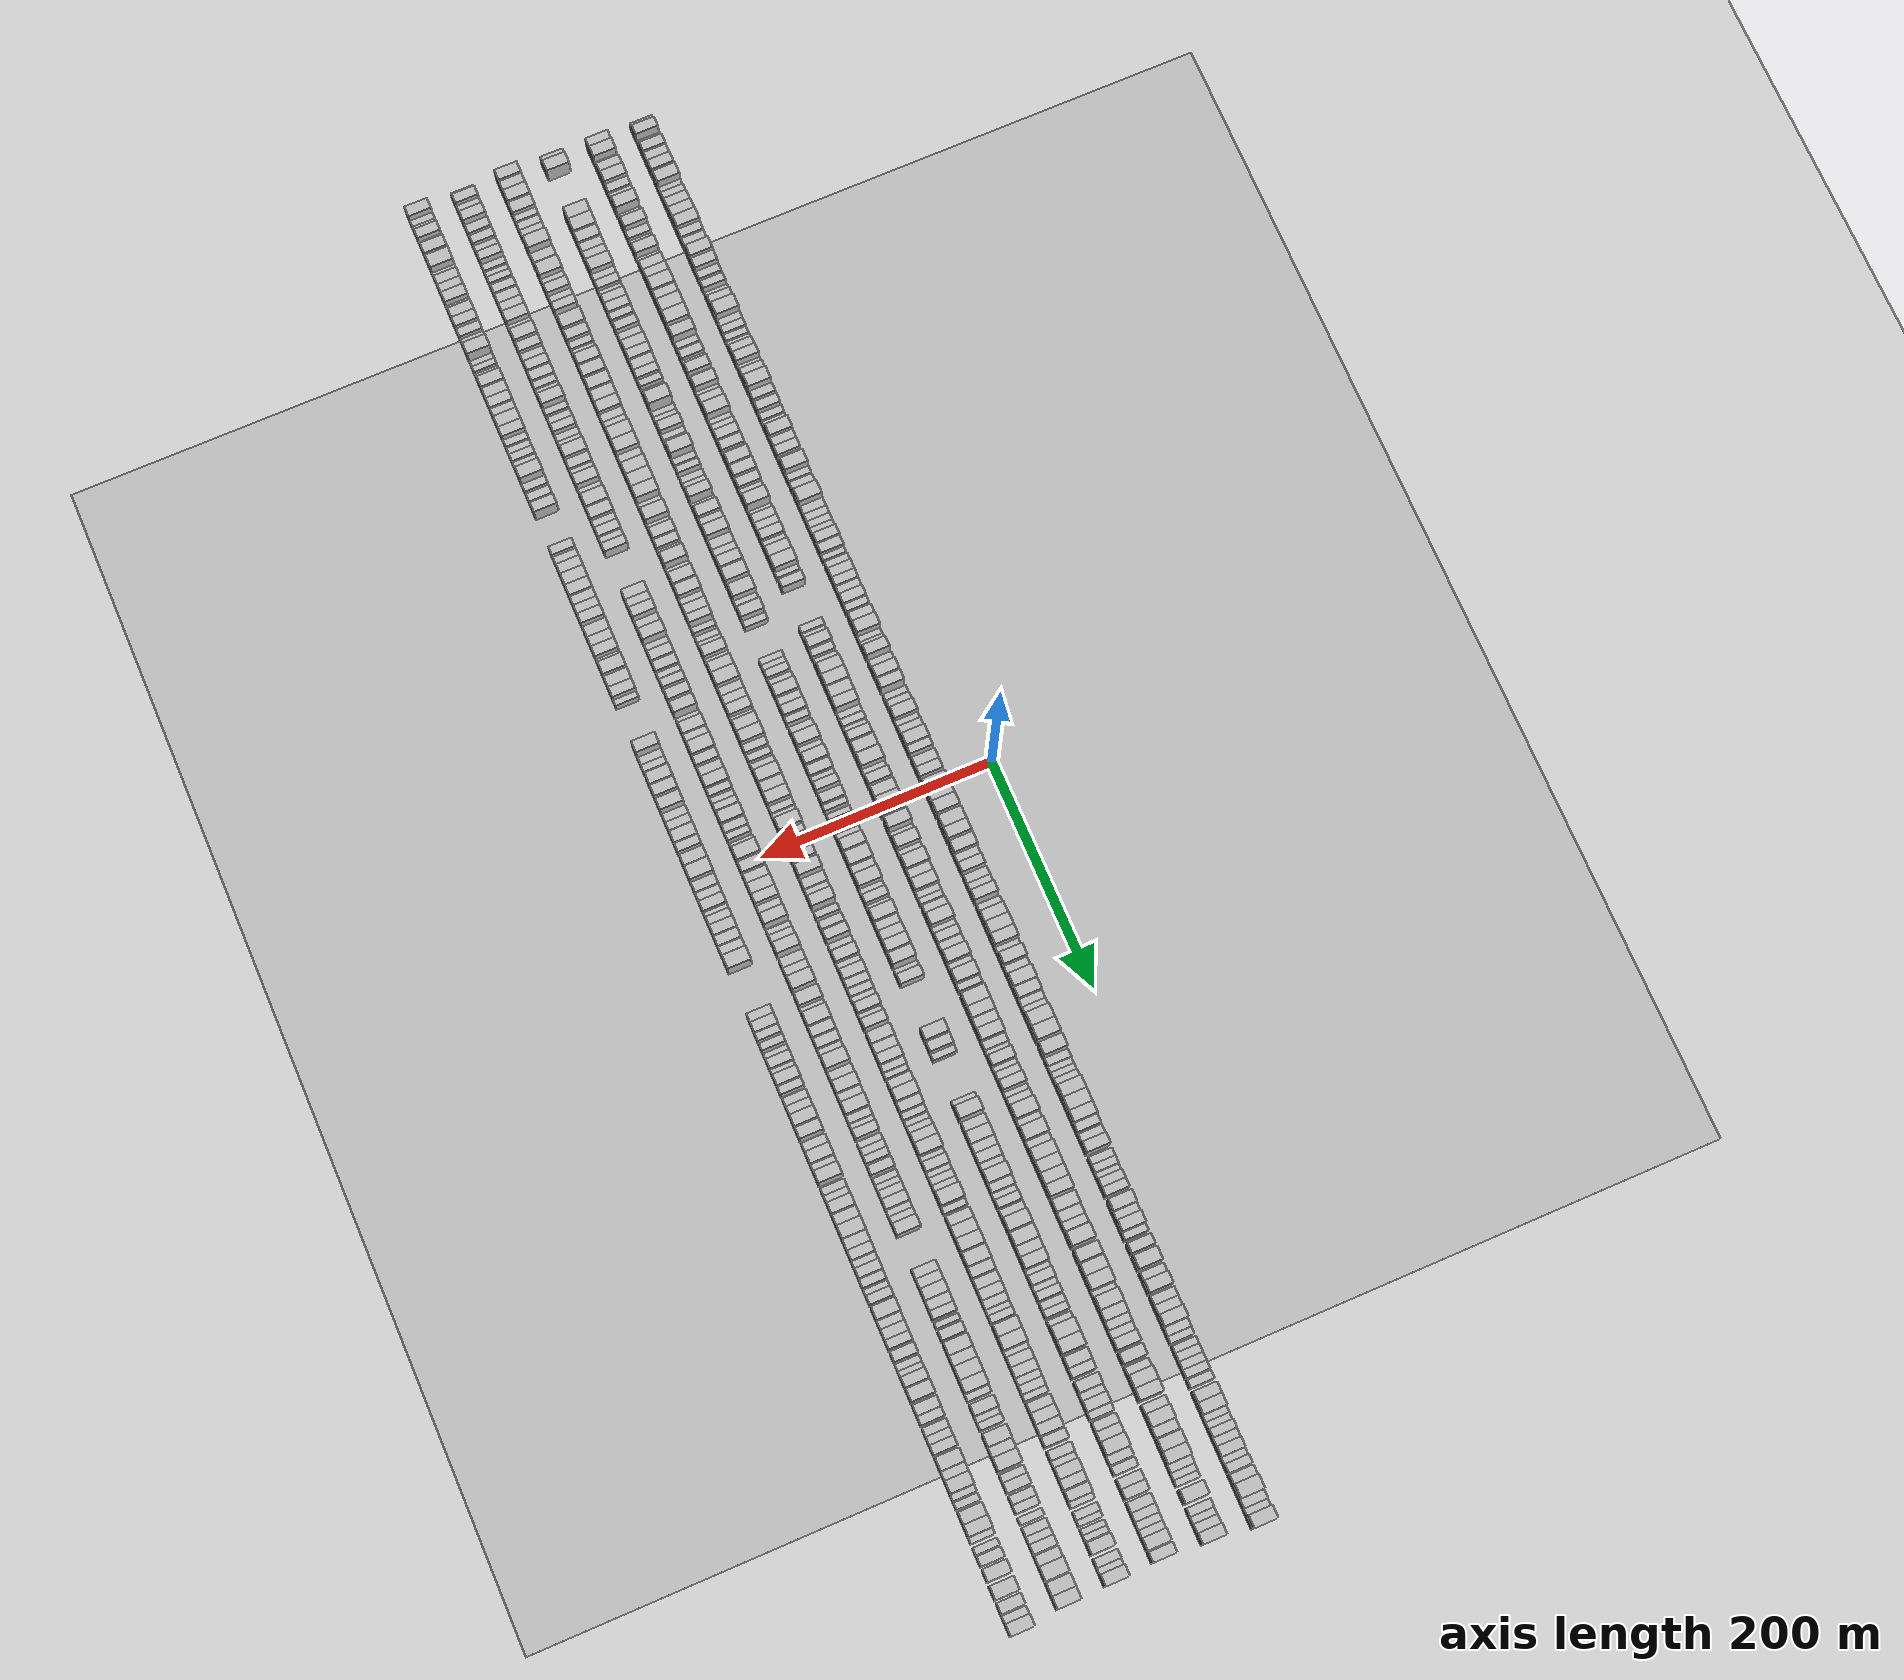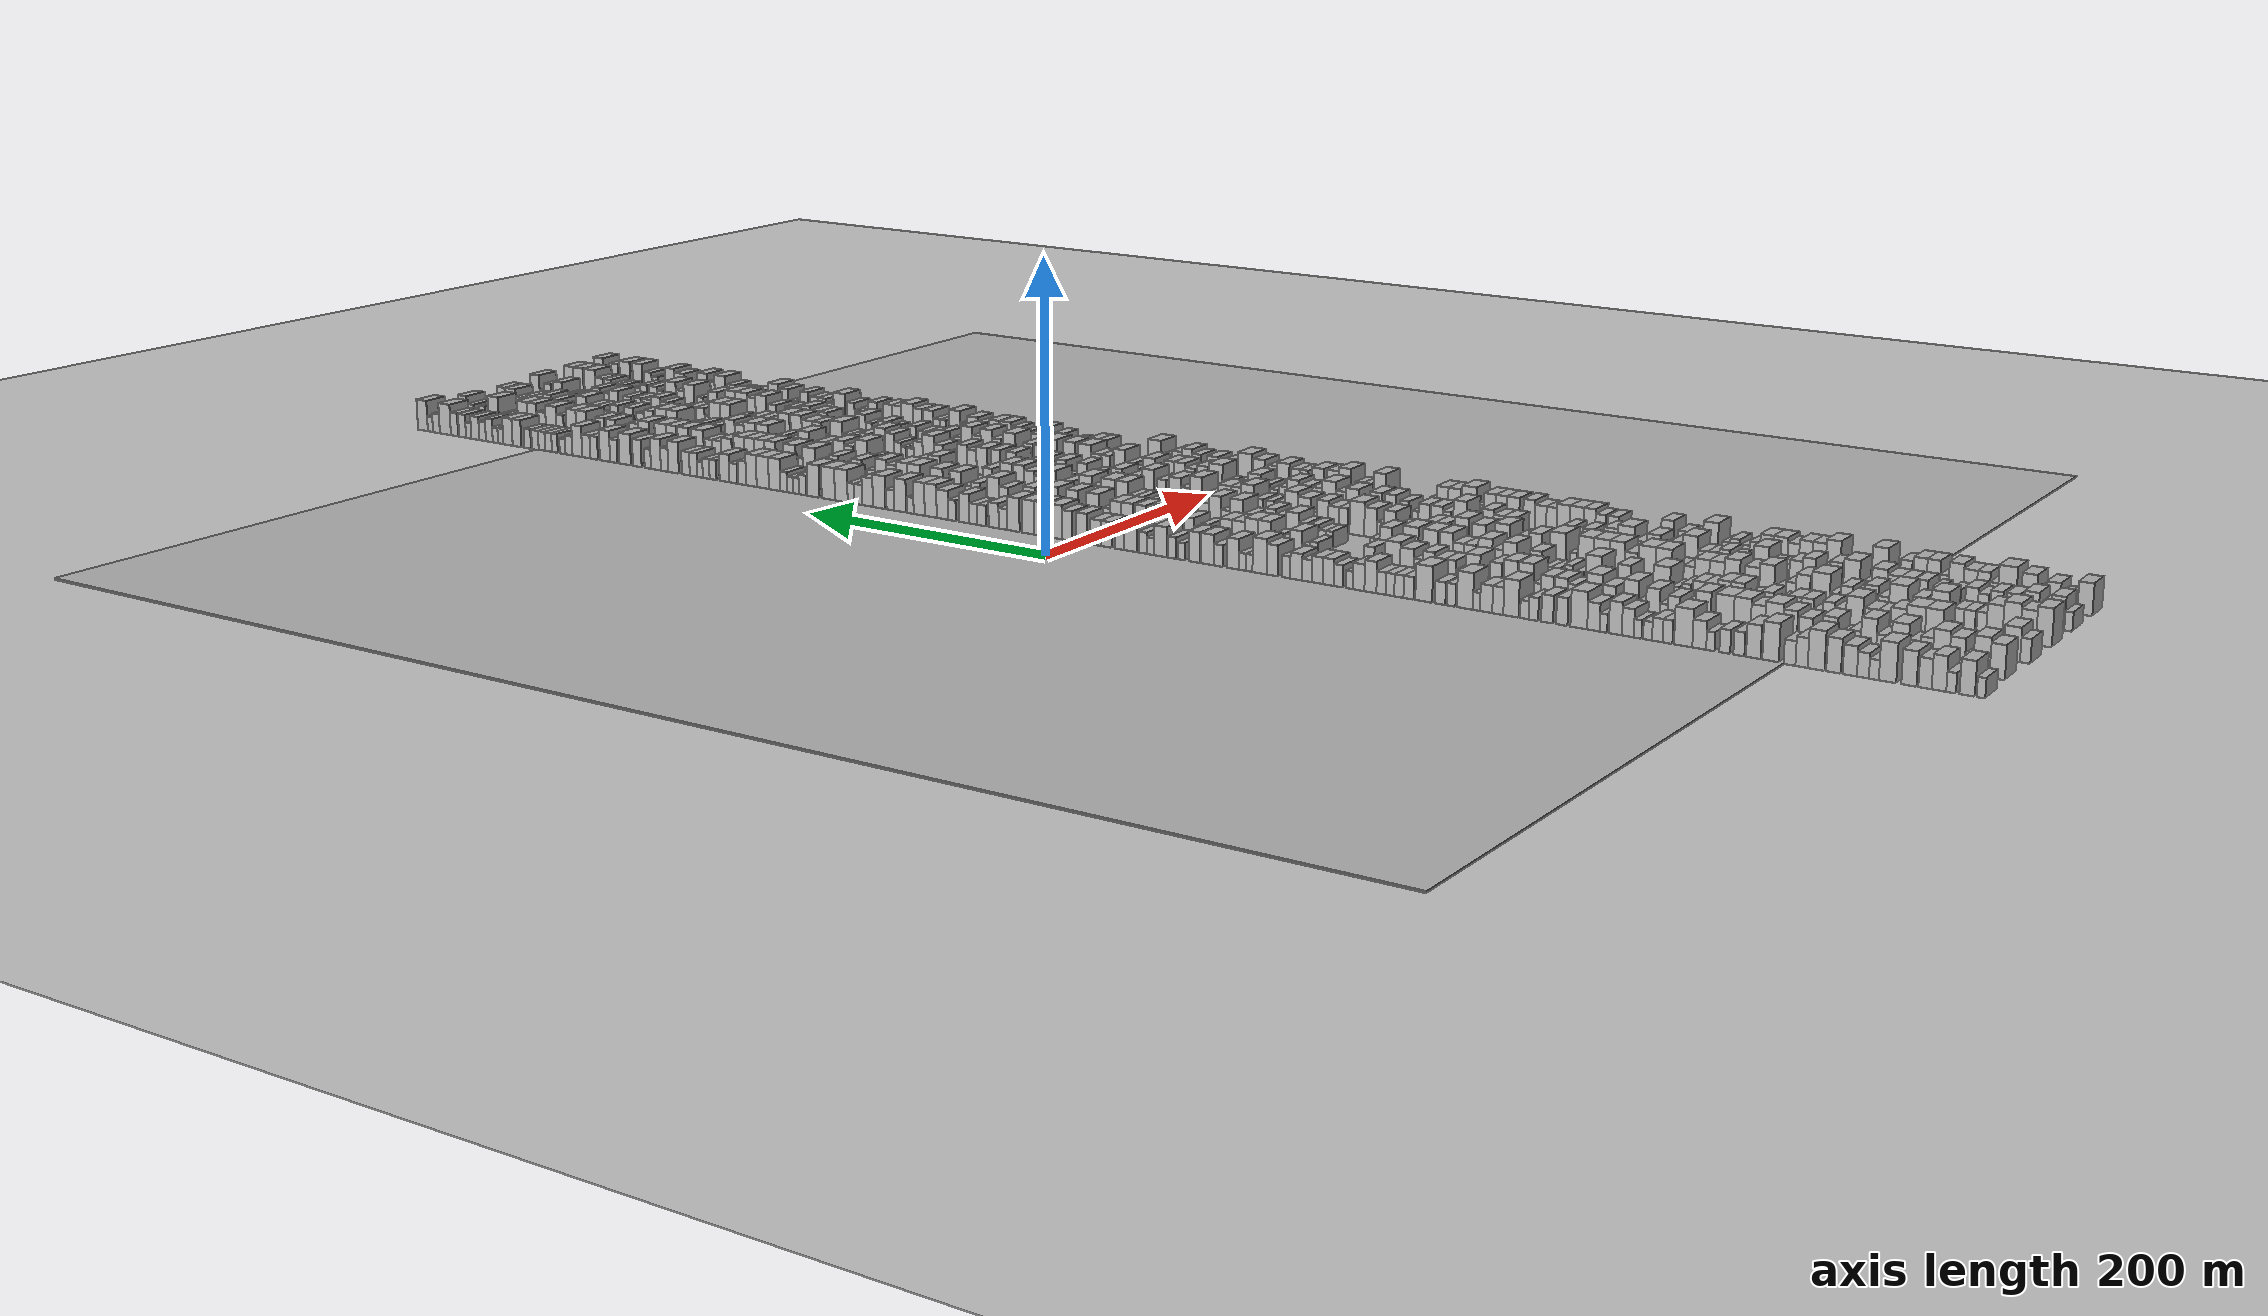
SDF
<?xml version="1.0" encoding="utf-8"?>

<sdf version="1.6">

   <world name="default">

      <gui fullscreen="0">

         <camera name="user_camera">

            <pose>-15 0 4.57585 0 0 0</pose>

            <view_controller>orbit</view_controller>

         </camera>

      </gui>

      <scene>

         <sky>

           <clouds>

             <speed>12</speed>

           </clouds>

         </sky>

         <ambient>0.4 0.4 0.4 1</ambient>

         <background>0.7 0.7 0.7 1</background>

         <shadows>1</shadows>

      </scene>

      <gravity>0 0 -9.8066</gravity>

      <magnetic_field>6e-06 2.3e-05 -4.2e-05</magnetic_field>

      <physics default="0" name="default_physics" type="ode">

         <ode>

            <solver>

               <type>quick</type>

               <iters>10</iters>

               <sor>1.0</sor>

               <use_dynamic_moi_rescaling>0</use_dynamic_moi_rescaling>

            </solver>

            <constraints>

               <cfm>0</cfm>

               <erp>0.2</erp>

               <contact_max_correcting_vel>100</contact_max_correcting_vel>

               <contact_surface_layer>0.001</contact_surface_layer>

            </constraints>

         </ode>

         <max_step_size>0.004</max_step_size>

         <real_time_factor>1</real_time_factor>

         <real_time_update_rate>250</real_time_update_rate>

      </physics>

      <light name="sun" type="directional">

         <cast_shadows>1</cast_shadows>

         <pose>0 0 10 0 0 0</pose>

         <diffuse>0.8 0.8 0.8 1</diffuse>

         <specular>0.2 0.2 0.2 1</specular>

         <attenuation>

            <range>1000</range>

            <constant>0.9</constant>

            <linear>0.01</linear>

            <quadratic>0.001</quadratic>

         </attenuation>

         <direction>-0.5 0.1 -0.9</direction>

      </light>

      <include>

         <name>ground_plane_1</name>

         <uri>model://HANNAS_ground_plane</uri>

         <pose>0 0 0  0 0 0</pose>

      </include>

      <include>

         <name>ground_plane_2</name>

         <uri>model://HANNAS_ground_plane</uri>

         <pose>100 0 0  0 0 0</pose>

      </include>

      <model name="building_1">

         <static>1</static>

         <pose frame="">50.0000 -617.4939 0 0.000000 0.000000 0.000000</pose>

         <link name="link">

            <pose frame="">0 0 6.00 0 0 0</pose>

            <collision name="collision">

               <geometry>

                  <box>

                     <size>20.0000 5.0123 12.0000</size>

                  </box>

               </geometry>

               <max_contacts>10</max_contacts>

               <surface>

                  <contact>

                     <ode/>

                  </contact>

                  <bounce/>

                  <friction>

                     <torsional>

                        <ode/>

                     </torsional>

                     <ode/>

                  </friction>

               </surface>

            </collision>

            <visual name="visual">

               <cast_shadows>0</cast_shadows>

               <geometry>

                  <box>

                     <size>20.0000 5.0123 12.0000</size>

                  </box>

               </geometry>

               <material>

                  <script>

                     <uri>model://HANNAS_wall/materials/scripts</uri>

                     <uri>model://HANNAS_wall/materials/textures</uri>

                     <name>vrc/HANNAS_wall</name>

                  </script>

               </material>

            </visual>

            <self_collide>0</self_collide>

            <enable_wind>0</enable_wind>

            <kinematic>0</kinematic>

         </link>

      </model>

      <model name="building_2">

         <static>1</static>

         <pose frame="">50.0000 -609.5214 0 0.000000 0.000000 0.000000</pose>

         <link name="link">

            <pose frame="">0 0 10.50 0 0 0</pose>

            <collision name="collision">

               <geometry>

                  <box>

                     <size>20.0000 8.9326 21.0000</size>

                  </box>

               </geometry>

               <max_contacts>10</max_contacts>

               <surface>

                  <contact>

                     <ode/>

                  </contact>

                  <bounce/>

                  <friction>

                     <torsional>

                        <ode/>

                     </torsional>

                     <ode/>

                  </friction>

               </surface>

            </collision>

            <visual name="visual">

               <cast_shadows>0</cast_shadows>

               <geometry>

                  <box>

                     <size>20.0000 8.9326 21.0000</size>

                  </box>

               </geometry>

               <material>

                  <script>

                     <uri>model://HANNAS_wall/materials/scripts</uri>

                     <uri>model://HANNAS_wall/materials/textures</uri>

                     <name>vrc/HANNAS_wall</name>

                  </script>

               </material>

            </visual>

            <self_collide>0</self_collide>

            <enable_wind>0</enable_wind>

            <kinematic>0</kinematic>

         </link>

      </model>

      <model name="building_3">

         <static>1</static>

         <pose frame="">50.0000 -600.2050 0 0.000000 0.000000 0.000000</pose>

         <link name="link">

            <pose frame="">0 0 6.00 0 0 0</pose>

            <collision name="collision">

               <geometry>

                  <box>

                     <size>20.0000 5.7003 12.0000</size>

                  </box>

               </geometry>

               <max_contacts>10</max_contacts>

               <surface>

                  <contact>

                     <ode/>

                  </contact>

                  <bounce/>

                  <friction>

                     <torsional>

                        <ode/>

                     </torsional>

                     <ode/>

                  </friction>

               </surface>

            </collision>

            <visual name="visual">

               <cast_shadows>0</cast_shadows>

               <geometry>

                  <box>

                     <size>20.0000 5.7003 12.0000</size>

                  </box>

               </geometry>

               <material>

                  <script>

                     <uri>model://HANNAS_wall/materials/scripts</uri>

                     <uri>model://HANNAS_wall/materials/textures</uri>

                     <name>vrc/HANNAS_wall</name>

                  </script>

               </material>

            </visual>

            <self_collide>0</self_collide>

            <enable_wind>0</enable_wind>

            <kinematic>0</kinematic>

         </link>

      </model>

      <model name="building_4">

         <static>1</static>

         <pose frame="">50.0000 -593.0694 0 0.000000 0.000000 0.000000</pose>

         <link name="link">

            <pose frame="">0 0 10.50 0 0 0</pose>

            <collision name="collision">

               <geometry>

                  <box>

                     <size>20.0000 8.5710 21.0000</size>

                  </box>

               </geometry>

               <max_contacts>10</max_contacts>

               <surface>

                  <contact>

                     <ode/>

                  </contact>

                  <bounce/>

                  <friction>

                     <torsional>

                        <ode/>

                     </torsional>

                     <ode/>

                  </friction>

               </surface>

            </collision>

            <visual name="visual">

               <cast_shadows>0</cast_shadows>

               <geometry>

                  <box>

                     <size>20.0000 8.5710 21.0000</size>

                  </box>

               </geometry>

               <material>

                  <script>

                     <uri>model://HANNAS_wall/materials/scripts</uri>

                     <uri>model://HANNAS_wall/materials/textures</uri>

                     <name>vrc/HANNAS_wall</name>

                  </script>

               </material>

            </visual>

            <self_collide>0</self_collide>

            <enable_wind>0</enable_wind>

            <kinematic>0</kinematic>

         </link>

      </model>

      <model name="building_5">

         <static>1</static>

         <pose frame="">50.0000 -584.8639 0 0.000000 0.000000 0.000000</pose>

         <link name="link">

            <pose frame="">0 0 9.00 0 0 0</pose>

            <collision name="collision">

               <geometry>

                  <box>

                     <size>20.0000 7.8400 18.0000</size>

                  </box>

               </geometry>

               <max_contacts>10</max_contacts>

               <surface>

                  <contact>

                     <ode/>

                  </contact>

                  <bounce/>

                  <friction>

                     <torsional>

                        <ode/>

                     </torsional>

                     <ode/>

                  </friction>

               </surface>

            </collision>

            <visual name="visual">

               <cast_shadows>0</cast_shadows>

               <geometry>

                  <box>

                     <size>20.0000 7.8400 18.0000</size>

                  </box>

               </geometry>

               <material>

                  <script>

                     <uri>model://HANNAS_wall/materials/scripts</uri>

                     <uri>model://HANNAS_wall/materials/textures</uri>

                     <name>vrc/HANNAS_wall</name>

                  </script>

               </material>

            </visual>

            <self_collide>0</self_collide>

            <enable_wind>0</enable_wind>

            <kinematic>0</kinematic>

         </link>

      </model>

      <model name="building_6">

         <static>1</static>

         <pose frame="">50.0000 -575.4095 0 0.000000 0.000000 0.000000</pose>

         <link name="link">

            <pose frame="">0 0 10.50 0 0 0</pose>

            <collision name="collision">

               <geometry>

                  <box>

                     <size>20.0000 9.0687 21.0000</size>

                  </box>

               </geometry>

               <max_contacts>10</max_contacts>

               <surface>

                  <contact>

                     <ode/>

                  </contact>

                  <bounce/>

                  <friction>

                     <torsional>

                        <ode/>

                     </torsional>

                     <ode/>

                  </friction>

               </surface>

            </collision>

            <visual name="visual">

               <cast_shadows>0</cast_shadows>

               <geometry>

                  <box>

                     <size>20.0000 9.0687 21.0000</size>

                  </box>

               </geometry>

               <material>

                  <script>

                     <uri>model://HANNAS_wall/materials/scripts</uri>

                     <uri>model://HANNAS_wall/materials/textures</uri>

                     <name>vrc/HANNAS_wall</name>

                  </script>

               </material>

            </visual>

            <self_collide>0</self_collide>

            <enable_wind>0</enable_wind>

            <kinematic>0</kinematic>

         </link>

      </model>

      <model name="building_7">

         <static>1</static>

         <pose frame="">50.0000 -562.6782 0 0.000000 0.000000 0.000000</pose>

         <link name="link">

            <pose frame="">0 0 12.00 0 0 0</pose>

            <collision name="collision">

               <geometry>

                  <box>

                     <size>20.0000 10.3939 24.0000</size>

                  </box>

               </geometry>

               <max_contacts>10</max_contacts>

               <surface>

                  <contact>

                     <ode/>

                  </contact>

                  <bounce/>

                  <friction>

                     <torsional>

                        <ode/>

                     </torsional>

                     <ode/>

                  </friction>

               </surface>

            </collision>

            <visual name="visual">

               <cast_shadows>0</cast_shadows>

               <geometry>

                  <box>

                     <size>20.0000 10.3939 24.0000</size>

                  </box>

               </geometry>

               <material>

                  <script>

                     <uri>model://HANNAS_wall/materials/scripts</uri>

                     <uri>model://HANNAS_wall/materials/textures</uri>

                     <name>vrc/HANNAS_wall</name>

                  </script>

               </material>

            </visual>

            <self_collide>0</self_collide>

            <enable_wind>0</enable_wind>

            <kinematic>0</kinematic>

         </link>

      </model>

      <model name="building_8">

         <static>1</static>

         <pose frame="">50.0000 -554.5004 0 0.000000 0.000000 0.000000</pose>

         <link name="link">

            <pose frame="">0 0 6.00 0 0 0</pose>

            <collision name="collision">

               <geometry>

                  <box>

                     <size>20.0000 5.9615 12.0000</size>

                  </box>

               </geometry>

               <max_contacts>10</max_contacts>

               <surface>

                  <contact>

                     <ode/>

                  </contact>

                  <bounce/>

                  <friction>

                     <torsional>

                        <ode/>

                     </torsional>

                     <ode/>

                  </friction>

               </surface>

            </collision>

            <visual name="visual">

               <cast_shadows>0</cast_shadows>

               <geometry>

                  <box>

                     <size>20.0000 5.9615 12.0000</size>

                  </box>

               </geometry>

               <material>

                  <script>

                     <uri>model://HANNAS_wall/materials/scripts</uri>

                     <uri>model://HANNAS_wall/materials/textures</uri>

                     <name>vrc/HANNAS_wall</name>

                  </script>

               </material>

            </visual>

            <self_collide>0</self_collide>

            <enable_wind>0</enable_wind>

            <kinematic>0</kinematic>

         </link>

      </model>

      <model name="building_9">

         <static>1</static>

         <pose frame="">50.0000 -547.9078 0 0.000000 0.000000 0.000000</pose>

         <link name="link">

            <pose frame="">0 0 7.50 0 0 0</pose>

            <collision name="collision">

               <geometry>

                  <box>

                     <size>20.0000 7.2238 15.0000</size>

                  </box>

               </geometry>

               <max_contacts>10</max_contacts>

               <surface>

                  <contact>

                     <ode/>

                  </contact>

                  <bounce/>

                  <friction>

                     <torsional>

                        <ode/>

                     </torsional>

                     <ode/>

                  </friction>

               </surface>

            </collision>

            <visual name="visual">

               <cast_shadows>0</cast_shadows>

               <geometry>

                  <box>

                     <size>20.0000 7.2238 15.0000</size>

                  </box>

               </geometry>

               <material>

                  <script>

                     <uri>model://HANNAS_wall/materials/scripts</uri>

                     <uri>model://HANNAS_wall/materials/textures</uri>

                     <name>vrc/HANNAS_wall</name>

                  </script>

               </material>

            </visual>

            <self_collide>0</self_collide>

            <enable_wind>0</enable_wind>

            <kinematic>0</kinematic>

         </link>

      </model>

      <model name="building_10">

         <static>1</static>

         <pose frame="">50.0000 -539.9835 0 0.000000 0.000000 0.000000</pose>

         <link name="link">

            <pose frame="">0 0 9.00 0 0 0</pose>

            <collision name="collision">

               <geometry>

                  <box>

                     <size>20.0000 8.6247 18.0000</size>

                  </box>

               </geometry>

               <max_contacts>10</max_contacts>

               <surface>

                  <contact>

                     <ode/>

                  </contact>

                  <bounce/>

                  <friction>

                     <torsional>

                        <ode/>

                     </torsional>

                     <ode/>

                  </friction>

               </surface>

            </collision>

            <visual name="visual">

               <cast_shadows>0</cast_shadows>

               <geometry>

                  <box>

                     <size>20.0000 8.6247 18.0000</size>

                  </box>

               </geometry>

               <material>

                  <script>

                     <uri>model://HANNAS_wall/materials/scripts</uri>

                     <uri>model://HANNAS_wall/materials/textures</uri>

                     <name>vrc/HANNAS_wall</name>

                  </script>

               </material>

            </visual>

            <self_collide>0</self_collide>

            <enable_wind>0</enable_wind>

            <kinematic>0</kinematic>

         </link>

      </model>

      <model name="building_11">

         <static>1</static>

         <pose frame="">50.0000 -530.1715 0 0.000000 0.000000 0.000000</pose>

         <link name="link">

            <pose frame="">0 0 10.50 0 0 0</pose>

            <collision name="collision">

               <geometry>

                  <box>

                     <size>20.0000 8.9995 21.0000</size>

                  </box>

               </geometry>

               <max_contacts>10</max_contacts>

               <surface>

                  <contact>

                     <ode/>

                  </contact>

                  <bounce/>

                  <friction>

                     <torsional>

                        <ode/>

                     </torsional>

                     <ode/>

                  </friction>

               </surface>

            </collision>

            <visual name="visual">

               <cast_shadows>0</cast_shadows>

               <geometry>

                  <box>

                     <size>20.0000 8.9995 21.0000</size>

                  </box>

               </geometry>

               <material>

                  <script>

                     <uri>model://HANNAS_wall/materials/scripts</uri>

                     <uri>model://HANNAS_wall/materials/textures</uri>

                     <name>vrc/HANNAS_wall</name>

                  </script>

               </material>

            </visual>

            <self_collide>0</self_collide>

            <enable_wind>0</enable_wind>

            <kinematic>0</kinematic>

         </link>

      </model>

      <model name="building_12">

         <static>1</static>

         <pose frame="">50.0000 -519.4981 0 0.000000 0.000000 0.000000</pose>

         <link name="link">

            <pose frame="">0 0 12.00 0 0 0</pose>

            <collision name="collision">

               <geometry>

                  <box>

                     <size>20.0000 10.3472 24.0000</size>

                  </box>

               </geometry>

               <max_contacts>10</max_contacts>

               <surface>

                  <contact>

                     <ode/>

                  </contact>

                  <bounce/>

                  <friction>

                     <torsional>

                        <ode/>

                     </torsional>

                     <ode/>

                  </friction>

               </surface>

            </collision>

            <visual name="visual">

               <cast_shadows>0</cast_shadows>

               <geometry>

                  <box>

                     <size>20.0000 10.3472 24.0000</size>

                  </box>

               </geometry>

               <material>

                  <script>

                     <uri>model://HANNAS_wall/materials/scripts</uri>

                     <uri>model://HANNAS_wall/materials/textures</uri>

                     <name>vrc/HANNAS_wall</name>

                  </script>

               </material>

            </visual>

            <self_collide>0</self_collide>

            <enable_wind>0</enable_wind>

            <kinematic>0</kinematic>

         </link>

      </model>

      <model name="building_13">

         <static>1</static>

         <pose frame="">50.0000 -510.5609 0 0.000000 0.000000 0.000000</pose>

         <link name="link">

            <pose frame="">0 0 9.00 0 0 0</pose>

            <collision name="collision">

               <geometry>

                  <box>

                     <size>20.0000 7.5273 18.0000</size>

                  </box>

               </geometry>

               <max_contacts>10</max_contacts>

               <surface>

                  <contact>

                     <ode/>

                  </contact>

                  <bounce/>

                  <friction>

                     <torsional>

                        <ode/>

                     </torsional>

                     <ode/>

                  </friction>

               </surface>

            </collision>

            <visual name="visual">

               <cast_shadows>0</cast_shadows>

               <geometry>

                  <box>

                     <size>20.0000 7.5273 18.0000</size>

                  </box>

               </geometry>

               <material>

                  <script>

                     <uri>model://HANNAS_wall/materials/scripts</uri>

                     <uri>model://HANNAS_wall/materials/textures</uri>

                     <name>vrc/HANNAS_wall</name>

                  </script>

               </material>

            </visual>

            <self_collide>0</self_collide>

            <enable_wind>0</enable_wind>

            <kinematic>0</kinematic>

         </link>

      </model>

      <model name="building_14">

         <static>1</static>

         <pose frame="">50.0000 -503.1471 0 0.000000 0.000000 0.000000</pose>

         <link name="link">

            <pose frame="">0 0 7.50 0 0 0</pose>

            <collision name="collision">

               <geometry>

                  <box>

                     <size>20.0000 7.3003 15.0000</size>

                  </box>

               </geometry>

               <max_contacts>10</max_contacts>

               <surface>

                  <contact>

                     <ode/>

                  </contact>

                  <bounce/>

                  <friction>

                     <torsional>

                        <ode/>

                     </torsional>

                     <ode/>

                  </friction>

               </surface>

            </collision>

            <visual name="visual">

               <cast_shadows>0</cast_shadows>

               <geometry>

                  <box>

                     <size>20.0000 7.3003 15.0000</size>

                  </box>

               </geometry>

               <material>

                  <script>

                     <uri>model://HANNAS_wall/materials/scripts</uri>

                     <uri>model://HANNAS_wall/materials/textures</uri>

                     <name>vrc/HANNAS_wall</name>

                  </script>

               </material>

            </visual>

            <self_collide>0</self_collide>

            <enable_wind>0</enable_wind>

            <kinematic>0</kinematic>

         </link>

      </model>

      <model name="building_15">

         <static>1</static>

         <pose frame="">50.0000 -491.3386 0 0.000000 0.000000 0.000000</pose>

         <link name="link">

            <pose frame="">0 0 12.00 0 0 0</pose>

            <collision name="collision">

               <geometry>

                  <box>

                     <size>20.0000 10.3166 24.0000</size>

                  </box>

               </geometry>

               <max_contacts>10</max_contacts>

               <surface>

                  <contact>

                     <ode/>

                  </contact>

                  <bounce/>

                  <friction>

                     <torsional>

                        <ode/>

                     </torsional>

                     <ode/>

                  </friction>

               </surface>

            </collision>

            <visual name="visual">

               <cast_shadows>0</cast_shadows>

               <geometry>

                  <box>

                     <size>20.0000 10.3166 24.0000</size>

                  </box>

               </geometry>

               <material>

                  <script>

                     <uri>model://HANNAS_wall/materials/scripts</uri>

                     <uri>model://HANNAS_wall/materials/textures</uri>

                     <name>vrc/HANNAS_wall</name>

                  </script>

               </material>

            </visual>

            <self_collide>0</self_collide>

            <enable_wind>0</enable_wind>

            <kinematic>0</kinematic>

         </link>

      </model>

      <model name="building_16">

         <static>1</static>

         <pose frame="">50.0000 -480.6012 0 0.000000 0.000000 0.000000</pose>

         <link name="link">

            <pose frame="">0 0 10.50 0 0 0</pose>

            <collision name="collision">

               <geometry>

                  <box>

                     <size>20.0000 9.1582 21.0000</size>

                  </box>

               </geometry>

               <max_contacts>10</max_contacts>

               <surface>

                  <contact>

                     <ode/>

                  </contact>

                  <bounce/>

                  <friction>

                     <torsional>

                        <ode/>

                     </torsional>

                     <ode/>

                  </friction>

               </surface>

            </collision>

            <visual name="visual">

               <cast_shadows>0</cast_shadows>

               <geometry>

                  <box>

                     <size>20.0000 9.1582 21.0000</size>

                  </box>

               </geometry>

               <material>

                  <script>

                     <uri>model://HANNAS_wall/materials/scripts</uri>

                     <uri>model://HANNAS_wall/materials/textures</uri>

                     <name>vrc/HANNAS_wall</name>

                  </script>

               </material>

            </visual>

            <self_collide>0</self_collide>

            <enable_wind>0</enable_wind>

            <kinematic>0</kinematic>

         </link>

      </model>

      <model name="building_17">

         <static>1</static>

         <pose frame="">50.0000 -471.5385 0 0.000000 0.000000 0.000000</pose>

         <link name="link">

            <pose frame="">0 0 7.50 0 0 0</pose>

            <collision name="collision">

               <geometry>

                  <box>

                     <size>20.0000 6.9674 15.0000</size>

                  </box>

               </geometry>

               <max_contacts>10</max_contacts>

               <surface>

                  <contact>

                     <ode/>

                  </contact>

                  <bounce/>

                  <friction>

                     <torsional>

                        <ode/>

                     </torsional>

                     <ode/>

                  </friction>

               </surface>

            </collision>

            <visual name="visual">

               <cast_shadows>0</cast_shadows>

               <geometry>

                  <box>

                     <size>20.0000 6.9674 15.0000</size>

                  </box>

               </geometry>

               <material>

                  <script>

                     <uri>model://HANNAS_wall/materials/scripts</uri>

                     <uri>model://HANNAS_wall/materials/textures</uri>

                     <name>vrc/HANNAS_wall</name>

                  </script>

               </material>

            </visual>

            <self_collide>0</self_collide>

            <enable_wind>0</enable_wind>

            <kinematic>0</kinematic>

         </link>

      </model>

      <model name="building_18">

         <static>1</static>

         <pose frame="">50.0000 -462.6272 0 0.000000 0.000000 0.000000</pose>

         <link name="link">

            <pose frame="">0 0 7.50 0 0 0</pose>

            <collision name="collision">

               <geometry>

                  <box>

                     <size>20.0000 6.8551 15.0000</size>

                  </box>

               </geometry>

               <max_contacts>10</max_contacts>

               <surface>

                  <contact>

                     <ode/>

                  </contact>

                  <bounce/>

                  <friction>

                     <torsional>

                        <ode/>

                     </torsional>

                     <ode/>

                  </friction>

               </surface>

            </collision>

            <visual name="visual">

               <cast_shadows>0</cast_shadows>

               <geometry>

                  <box>

                     <size>20.0000 6.8551 15.0000</size>

                  </box>

               </geometry>

               <material>

                  <script>

                     <uri>model://HANNAS_wall/materials/scripts</uri>

                     <uri>model://HANNAS_wall/materials/textures</uri>

                     <name>vrc/HANNAS_wall</name>

                  </script>

               </material>

            </visual>

            <self_collide>0</self_collide>

            <enable_wind>0</enable_wind>

            <kinematic>0</kinematic>

         </link>

      </model>

      <model name="building_19">

         <static>1</static>

         <pose frame="">50.0000 -453.5143 0 0.000000 0.000000 0.000000</pose>

         <link name="link">

            <pose frame="">0 0 6.00 0 0 0</pose>

            <collision name="collision">

               <geometry>

                  <box>

                     <size>20.0000 5.3707 12.0000</size>

                  </box>

               </geometry>

               <max_contacts>10</max_contacts>

               <surface>

                  <contact>

                     <ode/>

                  </contact>

                  <bounce/>

                  <friction>

                     <torsional>

                        <ode/>

                     </torsional>

                     <ode/>

                  </friction>

               </surface>

            </collision>

            <visual name="visual">

               <cast_shadows>0</cast_shadows>

               <geometry>

                  <box>

                     <size>20.0000 5.3707 12.0000</size>

                  </box>

               </geometry>

               <material>

                  <script>

                     <uri>model://HANNAS_wall/materials/scripts</uri>

                     <uri>model://HANNAS_wall/materials/textures</uri>

                     <name>vrc/HANNAS_wall</name>

                  </script>

               </material>

            </visual>

            <self_collide>0</self_collide>

            <enable_wind>0</enable_wind>

            <kinematic>0</kinematic>

         </link>

      </model>

      <model name="building_20">

         <static>1</static>

         <pose frame="">50.0000 -446.4082 0 0.000000 0.000000 0.000000</pose>

         <link name="link">

            <pose frame="">0 0 9.00 0 0 0</pose>

            <collision name="collision">

               <geometry>

                  <box>

                     <size>20.0000 8.8415 18.0000</size>

                  </box>

               </geometry>

               <max_contacts>10</max_contacts>

               <surface>

                  <contact>

                     <ode/>

                  </contact>

                  <bounce/>

                  <friction>

                     <torsional>

                        <ode/>

                     </torsional>

                     <ode/>

                  </friction>

               </surface>

            </collision>

            <visual name="visual">

               <cast_shadows>0</cast_shadows>

               <geometry>

                  <box>

                     <size>20.0000 8.8415 18.0000</size>

                  </box>

               </geometry>

               <material>

                  <script>

                     <uri>model://HANNAS_wall/materials/scripts</uri>

                     <uri>model://HANNAS_wall/materials/textures</uri>

                     <name>vrc/HANNAS_wall</name>

                  </script>

               </material>

            </visual>

            <self_collide>0</self_collide>

            <enable_wind>0</enable_wind>

            <kinematic>0</kinematic>

         </link>

      </model>

      <model name="building_21">

         <static>1</static>

         <pose frame="">50.0000 -436.0804 0 0.000000 0.000000 0.000000</pose>

         <link name="link">

            <pose frame="">0 0 12.00 0 0 0</pose>

            <collision name="collision">

               <geometry>

                  <box>

                     <size>20.0000 11.8140 24.0000</size>

                  </box>

               </geometry>

               <max_contacts>10</max_contacts>

               <surface>

                  <contact>

                     <ode/>

                  </contact>

                  <bounce/>

                  <friction>

                     <torsional>

                        <ode/>

                     </torsional>

                     <ode/>

                  </friction>

               </surface>

            </collision>

            <visual name="visual">

               <cast_shadows>0</cast_shadows>

               <geometry>

                  <box>

                     <size>20.0000 11.8140 24.0000</size>

                  </box>

               </geometry>

               <material>

                  <script>

                     <uri>model://HANNAS_wall/materials/scripts</uri>

                     <uri>model://HANNAS_wall/materials/textures</uri>

                     <name>vrc/HANNAS_wall</name>

                  </script>

               </material>

            </visual>

            <self_collide>0</self_collide>

            <enable_wind>0</enable_wind>

            <kinematic>0</kinematic>

         </link>

      </model>

      <model name="building_22">

         <static>1</static>

         <pose frame="">50.0000 -426.0218 0 0.000000 0.000000 0.000000</pose>

         <link name="link">

            <pose frame="">0 0 7.50 0 0 0</pose>

            <collision name="collision">

               <geometry>

                  <box>

                     <size>20.0000 6.3033 15.0000</size>

                  </box>

               </geometry>

               <max_contacts>10</max_contacts>

               <surface>

                  <contact>

                     <ode/>

                  </contact>

                  <bounce/>

                  <friction>

                     <torsional>

                        <ode/>

                     </torsional>

                     <ode/>

                  </friction>

               </surface>

            </collision>

            <visual name="visual">

               <cast_shadows>0</cast_shadows>

               <geometry>

                  <box>

                     <size>20.0000 6.3033 15.0000</size>

                  </box>

               </geometry>

               <material>

                  <script>

                     <uri>model://HANNAS_wall/materials/scripts</uri>

                     <uri>model://HANNAS_wall/materials/textures</uri>

                     <name>vrc/HANNAS_wall</name>

                  </script>

               </material>

            </visual>

            <self_collide>0</self_collide>

            <enable_wind>0</enable_wind>

            <kinematic>0</kinematic>

         </link>

      </model>

      <model name="building_23">

         <static>1</static>

         <pose frame="">50.0000 -419.4182 0 0.000000 0.000000 0.000000</pose>

         <link name="link">

            <pose frame="">0 0 7.50 0 0 0</pose>

            <collision name="collision">

               <geometry>

                  <box>

                     <size>20.0000 6.9038 15.0000</size>

                  </box>

               </geometry>

               <max_contacts>10</max_contacts>

               <surface>

                  <contact>

                     <ode/>

                  </contact>

                  <bounce/>

                  <friction>

                     <torsional>

                        <ode/>

                     </torsional>

                     <ode/>

                  </friction>

               </surface>

            </collision>

            <visual name="visual">

               <cast_shadows>0</cast_shadows>

               <geometry>

                  <box>

                     <size>20.0000 6.9038 15.0000</size>

                  </box>

               </geometry>

               <material>

                  <script>

                     <uri>model://HANNAS_wall/materials/scripts</uri>

                     <uri>model://HANNAS_wall/materials/textures</uri>

                     <name>vrc/HANNAS_wall</name>

                  </script>

               </material>

            </visual>

            <self_collide>0</self_collide>

            <enable_wind>0</enable_wind>

            <kinematic>0</kinematic>

         </link>

      </model>

      <model name="building_24">

         <static>1</static>

         <pose frame="">50.0000 -413.0343 0 0.000000 0.000000 0.000000</pose>

         <link name="link">

            <pose frame="">0 0 6.00 0 0 0</pose>

            <collision name="collision">

               <geometry>

                  <box>

                     <size>20.0000 5.8640 12.0000</size>

                  </box>

               </geometry>

               <max_contacts>10</max_contacts>

               <surface>

                  <contact>

                     <ode/>

                  </contact>

                  <bounce/>

                  <friction>

                     <torsional>

                        <ode/>

                     </torsional>

                     <ode/>

                  </friction>

               </surface>

            </collision>

            <visual name="visual">

               <cast_shadows>0</cast_shadows>

               <geometry>

                  <box>

                     <size>20.0000 5.8640 12.0000</size>

                  </box>

               </geometry>

               <material>

                  <script>

                     <uri>model://HANNAS_wall/materials/scripts</uri>

                     <uri>model://HANNAS_wall/materials/textures</uri>

                     <name>vrc/HANNAS_wall</name>

                  </script>

               </material>

            </visual>

            <self_collide>0</self_collide>

            <enable_wind>0</enable_wind>

            <kinematic>0</kinematic>

         </link>

      </model>

      <model name="building_25">

         <static>1</static>

         <pose frame="">50.0000 -406.5756 0 0.000000 0.000000 0.000000</pose>

         <link name="link">

            <pose frame="">0 0 6.00 0 0 0</pose>

            <collision name="collision">

               <geometry>

                  <box>

                     <size>20.0000 5.0534 12.0000</size>

                  </box>

               </geometry>

               <max_contacts>10</max_contacts>

               <surface>

                  <contact>

                     <ode/>

                  </contact>

                  <bounce/>

                  <friction>

                     <torsional>

                        <ode/>

                     </torsional>

                     <ode/>

                  </friction>

               </surface>

            </collision>

            <visual name="visual">

               <cast_shadows>0</cast_shadows>

               <geometry>

                  <box>

                     <size>20.0000 5.0534 12.0000</size>

                  </box>

               </geometry>

               <material>

                  <script>

                     <uri>model://HANNAS_wall/materials/scripts</uri>

                     <uri>model://HANNAS_wall/materials/textures</uri>

                     <name>vrc/HANNAS_wall</name>

                  </script>

               </material>

            </visual>

            <self_collide>0</self_collide>

            <enable_wind>0</enable_wind>

            <kinematic>0</kinematic>

         </link>

      </model>

      <model name="building_26">

         <static>1</static>

         <pose frame="">50.0000 -400.0923 0 0.000000 0.000000 0.000000</pose>

         <link name="link">

            <pose frame="">0 0 9.00 0 0 0</pose>

            <collision name="collision">

               <geometry>

                  <box>

                     <size>20.0000 7.9132 18.0000</size>

                  </box>

               </geometry>

               <max_contacts>10</max_contacts>

               <surface>

                  <contact>

                     <ode/>

                  </contact>

                  <bounce/>

                  <friction>

                     <torsional>

                        <ode/>

                     </torsional>

                     <ode/>

                  </friction>

               </surface>

            </collision>

            <visual name="visual">

               <cast_shadows>0</cast_shadows>

               <geometry>

                  <box>

                     <size>20.0000 7.9132 18.0000</size>

                  </box>

               </geometry>

               <material>

                  <script>

                     <uri>model://HANNAS_wall/materials/scripts</uri>

                     <uri>model://HANNAS_wall/materials/textures</uri>

                     <name>vrc/HANNAS_wall</name>

                  </script>

               </material>

            </visual>

            <self_collide>0</self_collide>

            <enable_wind>0</enable_wind>

            <kinematic>0</kinematic>

         </link>

      </model>

      <model name="building_27">

         <static>1</static>

         <pose frame="">50.0000 -391.8530 0 0.000000 0.000000 0.000000</pose>

         <link name="link">

            <pose frame="">0 0 10.50 0 0 0</pose>

            <collision name="collision">

               <geometry>

                  <box>

                     <size>20.0000 8.5653 21.0000</size>

                  </box>

               </geometry>

               <max_contacts>10</max_contacts>

               <surface>

                  <contact>

                     <ode/>

                  </contact>

                  <bounce/>

                  <friction>

                     <torsional>

                        <ode/>

                     </torsional>

                     <ode/>

                  </friction>

               </surface>

            </collision>

            <visual name="visual">

               <cast_shadows>0</cast_shadows>

               <geometry>

                  <box>

                     <size>20.0000 8.5653 21.0000</size>

                  </box>

               </geometry>

               <material>

                  <script>

                     <uri>model://HANNAS_wall/materials/scripts</uri>

                     <uri>model://HANNAS_wall/materials/textures</uri>

                     <name>vrc/HANNAS_wall</name>

                  </script>

               </material>

            </visual>

            <self_collide>0</self_collide>

            <enable_wind>0</enable_wind>

            <kinematic>0</kinematic>

         </link>

      </model>

      <model name="building_28">

         <static>1</static>

         <pose frame="">50.0000 -384.0498 0 0.000000 0.000000 0.000000</pose>

         <link name="link">

            <pose frame="">0 0 6.00 0 0 0</pose>

            <collision name="collision">

               <geometry>

                  <box>

                     <size>20.0000 5.0412 12.0000</size>

                  </box>

               </geometry>

               <max_contacts>10</max_contacts>

               <surface>

                  <contact>

                     <ode/>

                  </contact>

                  <bounce/>

                  <friction>

                     <torsional>

                        <ode/>

                     </torsional>

                     <ode/>

                  </friction>

               </surface>

            </collision>

            <visual name="visual">

               <cast_shadows>0</cast_shadows>

               <geometry>

                  <box>

                     <size>20.0000 5.0412 12.0000</size>

                  </box>

               </geometry>

               <material>

                  <script>

                     <uri>model://HANNAS_wall/materials/scripts</uri>

                     <uri>model://HANNAS_wall/materials/textures</uri>

                     <name>vrc/HANNAS_wall</name>

                  </script>

               </material>

            </visual>

            <self_collide>0</self_collide>

            <enable_wind>0</enable_wind>

            <kinematic>0</kinematic>

         </link>

      </model>

      <model name="building_29">

         <static>1</static>

         <pose frame="">50.0000 -377.3930 0 0.000000 0.000000 0.000000</pose>

         <link name="link">

            <pose frame="">0 0 9.00 0 0 0</pose>

            <collision name="collision">

               <geometry>

                  <box>

                     <size>20.0000 8.2723 18.0000</size>

                  </box>

               </geometry>

               <max_contacts>10</max_contacts>

               <surface>

                  <contact>

                     <ode/>

                  </contact>

                  <bounce/>

                  <friction>

                     <torsional>

                        <ode/>

                     </torsional>

                     <ode/>

                  </friction>

               </surface>

            </collision>

            <visual name="visual">

               <cast_shadows>0</cast_shadows>

               <geometry>

                  <box>

                     <size>20.0000 8.2723 18.0000</size>

                  </box>

               </geometry>

               <material>

                  <script>

                     <uri>model://HANNAS_wall/materials/scripts</uri>

                     <uri>model://HANNAS_wall/materials/textures</uri>

                     <name>vrc/HANNAS_wall</name>

                  </script>

               </material>

            </visual>

            <self_collide>0</self_collide>

            <enable_wind>0</enable_wind>

            <kinematic>0</kinematic>

         </link>

      </model>

      <model name="building_30">

         <static>1</static>

         <pose frame="">50.0000 -367.6596 0 0.000000 0.000000 0.000000</pose>

         <link name="link">

            <pose frame="">0 0 12.00 0 0 0</pose>

            <collision name="collision">

               <geometry>

                  <box>

                     <size>20.0000 11.1945 24.0000</size>

                  </box>

               </geometry>

               <max_contacts>10</max_contacts>

               <surface>

                  <contact>

                     <ode/>

                  </contact>

                  <bounce/>

                  <friction>

                     <torsional>

                        <ode/>

                     </torsional>

                     <ode/>

                  </friction>

               </surface>

            </collision>

            <visual name="visual">

               <cast_shadows>0</cast_shadows>

               <geometry>

                  <box>

                     <size>20.0000 11.1945 24.0000</size>

                  </box>

               </geometry>

               <material>

                  <script>

                     <uri>model://HANNAS_wall/materials/scripts</uri>

                     <uri>model://HANNAS_wall/materials/textures</uri>

                     <name>vrc/HANNAS_wall</name>

                  </script>

               </material>

            </visual>

            <self_collide>0</self_collide>

            <enable_wind>0</enable_wind>

            <kinematic>0</kinematic>

         </link>

      </model>

      <model name="building_31">

         <static>1</static>

         <pose frame="">50.0000 -356.2446 0 0.000000 0.000000 0.000000</pose>

         <link name="link">

            <pose frame="">0 0 9.00 0 0 0</pose>

            <collision name="collision">

               <geometry>

                  <box>

                     <size>20.0000 7.6356 18.0000</size>

                  </box>

               </geometry>

               <max_contacts>10</max_contacts>

               <surface>

                  <contact>

                     <ode/>

                  </contact>

                  <bounce/>

                  <friction>

                     <torsional>

                        <ode/>

                     </torsional>

                     <ode/>

                  </friction>

               </surface>

            </collision>

            <visual name="visual">

               <cast_shadows>0</cast_shadows>

               <geometry>

                  <box>

                     <size>20.0000 7.6356 18.0000</size>

                  </box>

               </geometry>

               <material>

                  <script>

                     <uri>model://HANNAS_wall/materials/scripts</uri>

                     <uri>model://HANNAS_wall/materials/textures</uri>

                     <name>vrc/HANNAS_wall</name>

                  </script>

               </material>

            </visual>

            <self_collide>0</self_collide>

            <enable_wind>0</enable_wind>

            <kinematic>0</kinematic>

         </link>

      </model>

      <model name="building_32">

         <static>1</static>

         <pose frame="">50.0000 -346.3736 0 0.000000 0.000000 0.000000</pose>

         <link name="link">

            <pose frame="">0 0 9.00 0 0 0</pose>

            <collision name="collision">

               <geometry>

                  <box>

                     <size>20.0000 8.1063 18.0000</size>

                  </box>

               </geometry>

               <max_contacts>10</max_contacts>

               <surface>

                  <contact>

                     <ode/>

                  </contact>

                  <bounce/>

                  <friction>

                     <torsional>

                        <ode/>

                     </torsional>

                     <ode/>

                  </friction>

               </surface>

            </collision>

            <visual name="visual">

               <cast_shadows>0</cast_shadows>

               <geometry>

                  <box>

                     <size>20.0000 8.1063 18.0000</size>

                  </box>

               </geometry>

               <material>

                  <script>

                     <uri>model://HANNAS_wall/materials/scripts</uri>

                     <uri>model://HANNAS_wall/materials/textures</uri>

                     <name>vrc/HANNAS_wall</name>

                  </script>

               </material>

            </visual>

            <self_collide>0</self_collide>

            <enable_wind>0</enable_wind>

            <kinematic>0</kinematic>

         </link>

      </model>

      <model name="building_33">

         <static>1</static>

         <pose frame="">50.0000 -337.1075 0 0.000000 0.000000 0.000000</pose>

         <link name="link">

            <pose frame="">0 0 7.50 0 0 0</pose>

            <collision name="collision">

               <geometry>

                  <box>

                     <size>20.0000 6.4259 15.0000</size>

                  </box>

               </geometry>

               <max_contacts>10</max_contacts>

               <surface>

                  <contact>

                     <ode/>

                  </contact>

                  <bounce/>

                  <friction>

                     <torsional>

                        <ode/>

                     </torsional>

                     <ode/>

                  </friction>

               </surface>

            </collision>

            <visual name="visual">

               <cast_shadows>0</cast_shadows>

               <geometry>

                  <box>

                     <size>20.0000 6.4259 15.0000</size>

                  </box>

               </geometry>

               <material>

                  <script>

                     <uri>model://HANNAS_wall/materials/scripts</uri>

                     <uri>model://HANNAS_wall/materials/textures</uri>

                     <name>vrc/HANNAS_wall</name>

                  </script>

               </material>

            </visual>

            <self_collide>0</self_collide>

            <enable_wind>0</enable_wind>

            <kinematic>0</kinematic>

         </link>

      </model>

      <model name="building_34">

         <static>1</static>

         <pose frame="">50.0000 -330.9429 0 0.000000 0.000000 0.000000</pose>

         <link name="link">

            <pose frame="">0 0 6.00 0 0 0</pose>

            <collision name="collision">

               <geometry>

                  <box>

                     <size>20.0000 5.9034 12.0000</size>

                  </box>

               </geometry>

               <max_contacts>10</max_contacts>

               <surface>

                  <contact>

                     <ode/>

                  </contact>

                  <bounce/>

                  <friction>

                     <torsional>

                        <ode/>

                     </torsional>

                     <ode/>

                  </friction>

               </surface>

            </collision>

            <visual name="visual">

               <cast_shadows>0</cast_shadows>

               <geometry>

                  <box>

                     <size>20.0000 5.9034 12.0000</size>

                  </box>

               </geometry>

               <material>

                  <script>

                     <uri>model://HANNAS_wall/materials/scripts</uri>

                     <uri>model://HANNAS_wall/materials/textures</uri>

                     <name>vrc/HANNAS_wall</name>

                  </script>

               </material>

            </visual>

            <self_collide>0</self_collide>

            <enable_wind>0</enable_wind>

            <kinematic>0</kinematic>

         </link>

      </model>

      <model name="building_35">

         <static>1</static>

         <pose frame="">50.0000 -321.7279 0 0.000000 0.000000 0.000000</pose>

         <link name="link">

            <pose frame="">0 0 12.00 0 0 0</pose>

            <collision name="collision">

               <geometry>

                  <box>

                     <size>20.0000 10.5265 24.0000</size>

                  </box>

               </geometry>

               <max_contacts>10</max_contacts>

               <surface>

                  <contact>

                     <ode/>

                  </contact>

                  <bounce/>

                  <friction>

                     <torsional>

                        <ode/>

                     </torsional>

                     <ode/>

                  </friction>

               </surface>

            </collision>

            <visual name="visual">

               <cast_shadows>0</cast_shadows>

               <geometry>

                  <box>

                     <size>20.0000 10.5265 24.0000</size>

                  </box>

               </geometry>

               <material>

                  <script>

                     <uri>model://HANNAS_wall/materials/scripts</uri>

                     <uri>model://HANNAS_wall/materials/textures</uri>

                     <name>vrc/HANNAS_wall</name>

                  </script>

               </material>

            </visual>

            <self_collide>0</self_collide>

            <enable_wind>0</enable_wind>

            <kinematic>0</kinematic>

         </link>

      </model>

      <model name="building_36">

         <static>1</static>

         <pose frame="">50.0000 -312.6658 0 0.000000 0.000000 0.000000</pose>

         <link name="link">

            <pose frame="">0 0 9.00 0 0 0</pose>

            <collision name="collision">

               <geometry>

                  <box>

                     <size>20.0000 7.5977 18.0000</size>

                  </box>

               </geometry>

               <max_contacts>10</max_contacts>

               <surface>

                  <contact>

                     <ode/>

                  </contact>

                  <bounce/>

                  <friction>

                     <torsional>

                        <ode/>

                     </torsional>

                     <ode/>

                  </friction>

               </surface>

            </collision>

            <visual name="visual">

               <cast_shadows>0</cast_shadows>

               <geometry>

                  <box>

                     <size>20.0000 7.5977 18.0000</size>

                  </box>

               </geometry>

               <material>

                  <script>

                     <uri>model://HANNAS_wall/materials/scripts</uri>

                     <uri>model://HANNAS_wall/materials/textures</uri>

                     <name>vrc/HANNAS_wall</name>

                  </script>

               </material>

            </visual>

            <self_collide>0</self_collide>

            <enable_wind>0</enable_wind>

            <kinematic>0</kinematic>

         </link>

      </model>

      <model name="building_37">

         <static>1</static>

         <pose frame="">50.0000 -304.6271 0 0.000000 0.000000 0.000000</pose>

         <link name="link">

            <pose frame="">0 0 9.00 0 0 0</pose>

            <collision name="collision">

               <geometry>

                  <box>

                     <size>20.0000 8.4796 18.0000</size>

                  </box>

               </geometry>

               <max_contacts>10</max_contacts>

               <surface>

                  <contact>

                     <ode/>

                  </contact>

                  <bounce/>

                  <friction>

                     <torsional>

                        <ode/>

                     </torsional>

                     <ode/>

                  </friction>

               </surface>

            </collision>

            <visual name="visual">

               <cast_shadows>0</cast_shadows>

               <geometry>

                  <box>

                     <size>20.0000 8.4796 18.0000</size>

                  </box>

               </geometry>

               <material>

                  <script>

                     <uri>model://HANNAS_wall/materials/scripts</uri>

                     <uri>model://HANNAS_wall/materials/textures</uri>

                     <name>vrc/HANNAS_wall</name>

                  </script>

               </material>

            </visual>

            <self_collide>0</self_collide>

            <enable_wind>0</enable_wind>

            <kinematic>0</kinematic>

         </link>

      </model>

      <model name="building_38">

         <static>1</static>

         <pose frame="">50.0000 -297.9302 0 0.000000 0.000000 0.000000</pose>

         <link name="link">

            <pose frame="">0 0 6.00 0 0 0</pose>

            <collision name="collision">

               <geometry>

                  <box>

                     <size>20.0000 4.9142 12.0000</size>

                  </box>

               </geometry>

               <max_contacts>10</max_contacts>

               <surface>

                  <contact>

                     <ode/>

                  </contact>

                  <bounce/>

                  <friction>

                     <torsional>

                        <ode/>

                     </torsional>

                     <ode/>

                  </friction>

               </surface>

            </collision>

            <visual name="visual">

               <cast_shadows>0</cast_shadows>

               <geometry>

                  <box>

                     <size>20.0000 4.9142 12.0000</size>

                  </box>

               </geometry>

               <material>

                  <script>

                     <uri>model://HANNAS_wall/materials/scripts</uri>

                     <uri>model://HANNAS_wall/materials/textures</uri>

                     <name>vrc/HANNAS_wall</name>

                  </script>

               </material>

            </visual>

            <self_collide>0</self_collide>

            <enable_wind>0</enable_wind>

            <kinematic>0</kinematic>

         </link>

      </model>

      <model name="building_39">

         <static>1</static>

         <pose frame="">50.0000 -289.8506 0 0.000000 0.000000 0.000000</pose>

         <link name="link">

            <pose frame="">0 0 12.00 0 0 0</pose>

            <collision name="collision">

               <geometry>

                  <box>

                     <size>20.0000 11.2450 24.0000</size>

                  </box>

               </geometry>

               <max_contacts>10</max_contacts>

               <surface>

                  <contact>

                     <ode/>

                  </contact>

                  <bounce/>

                  <friction>

                     <torsional>

                        <ode/>

                     </torsional>

                     <ode/>

                  </friction>

               </surface>

            </collision>

            <visual name="visual">

               <cast_shadows>0</cast_shadows>

               <geometry>

                  <box>

                     <size>20.0000 11.2450 24.0000</size>

                  </box>

               </geometry>

               <material>

                  <script>

                     <uri>model://HANNAS_wall/materials/scripts</uri>

                     <uri>model://HANNAS_wall/materials/textures</uri>

                     <name>vrc/HANNAS_wall</name>

                  </script>

               </material>

            </visual>

            <self_collide>0</self_collide>

            <enable_wind>0</enable_wind>

            <kinematic>0</kinematic>

         </link>

      </model>

      <model name="building_40">

         <static>1</static>

         <pose frame="">50.0000 -280.1868 0 0.000000 0.000000 0.000000</pose>

         <link name="link">

            <pose frame="">0 0 7.50 0 0 0</pose>

            <collision name="collision">

               <geometry>

                  <box>

                     <size>20.0000 6.0826 15.0000</size>

                  </box>

               </geometry>

               <max_contacts>10</max_contacts>

               <surface>

                  <contact>

                     <ode/>

                  </contact>

                  <bounce/>

                  <friction>

                     <torsional>

                        <ode/>

                     </torsional>

                     <ode/>

                  </friction>

               </surface>

            </collision>

            <visual name="visual">

               <cast_shadows>0</cast_shadows>

               <geometry>

                  <box>

                     <size>20.0000 6.0826 15.0000</size>

                  </box>

               </geometry>

               <material>

                  <script>

                     <uri>model://HANNAS_wall/materials/scripts</uri>

                     <uri>model://HANNAS_wall/materials/textures</uri>

                     <name>vrc/HANNAS_wall</name>

                  </script>

               </material>

            </visual>

            <self_collide>0</self_collide>

            <enable_wind>0</enable_wind>

            <kinematic>0</kinematic>

         </link>

      </model>

      <model name="building_41">

         <static>1</static>

         <pose frame="">50.0000 -272.4951 0 0.000000 0.000000 0.000000</pose>

         <link name="link">

            <pose frame="">0 0 7.50 0 0 0</pose>

            <collision name="collision">

               <geometry>

                  <box>

                     <size>20.0000 7.3009 15.0000</size>

                  </box>

               </geometry>

               <max_contacts>10</max_contacts>

               <surface>

                  <contact>

                     <ode/>

                  </contact>

                  <bounce/>

                  <friction>

                     <torsional>

                        <ode/>

                     </torsional>

                     <ode/>

                  </friction>

               </surface>

            </collision>

            <visual name="visual">

               <cast_shadows>0</cast_shadows>

               <geometry>

                  <box>

                     <size>20.0000 7.3009 15.0000</size>

                  </box>

               </geometry>

               <material>

                  <script>

                     <uri>model://HANNAS_wall/materials/scripts</uri>

                     <uri>model://HANNAS_wall/materials/textures</uri>

                     <name>vrc/HANNAS_wall</name>

                  </script>

               </material>

            </visual>

            <self_collide>0</self_collide>

            <enable_wind>0</enable_wind>

            <kinematic>0</kinematic>

         </link>

      </model>

      <model name="building_42">

         <static>1</static>

         <pose frame="">50.0000 -260.8560 0 0.000000 0.000000 0.000000</pose>

         <link name="link">

            <pose frame="">0 0 12.00 0 0 0</pose>

            <collision name="collision">

               <geometry>

                  <box>

                     <size>20.0000 11.9773 24.0000</size>

                  </box>

               </geometry>

               <max_contacts>10</max_contacts>

               <surface>

                  <contact>

                     <ode/>

                  </contact>

                  <bounce/>

                  <friction>

                     <torsional>

                        <ode/>

                     </torsional>

                     <ode/>

                  </friction>

               </surface>

            </collision>

            <visual name="visual">

               <cast_shadows>0</cast_shadows>

               <geometry>

                  <box>

                     <size>20.0000 11.9773 24.0000</size>

                  </box>

               </geometry>

               <material>

                  <script>

                     <uri>model://HANNAS_wall/materials/scripts</uri>

                     <uri>model://HANNAS_wall/materials/textures</uri>

                     <name>vrc/HANNAS_wall</name>

                  </script>

               </material>

            </visual>

            <self_collide>0</self_collide>

            <enable_wind>0</enable_wind>

            <kinematic>0</kinematic>

         </link>

      </model>

      <model name="building_43">

         <static>1</static>

         <pose frame="">50.0000 -250.1398 0 0.000000 0.000000 0.000000</pose>

         <link name="link">

            <pose frame="">0 0 7.50 0 0 0</pose>

            <collision name="collision">

               <geometry>

                  <box>

                     <size>20.0000 7.4550 15.0000</size>

                  </box>

               </geometry>

               <max_contacts>10</max_contacts>

               <surface>

                  <contact>

                     <ode/>

                  </contact>

                  <bounce/>

                  <friction>

                     <torsional>

                        <ode/>

                     </torsional>

                     <ode/>

                  </friction>

               </surface>

            </collision>

            <visual name="visual">

               <cast_shadows>0</cast_shadows>

               <geometry>

                  <box>

                     <size>20.0000 7.4550 15.0000</size>

                  </box>

               </geometry>

               <material>

                  <script>

                     <uri>model://HANNAS_wall/materials/scripts</uri>

                     <uri>model://HANNAS_wall/materials/textures</uri>

                     <name>vrc/HANNAS_wall</name>

                  </script>

               </material>

            </visual>

            <self_collide>0</self_collide>

            <enable_wind>0</enable_wind>

            <kinematic>0</kinematic>

         </link>

      </model>

      <model name="building_44">

         <static>1</static>

         <pose frame="">50.0000 -243.1151 0 0.000000 0.000000 0.000000</pose>

         <link name="link">

            <pose frame="">0 0 7.50 0 0 0</pose>

            <collision name="collision">

               <geometry>

                  <box>

                     <size>20.0000 6.5945 15.0000</size>

                  </box>

               </geometry>

               <max_contacts>10</max_contacts>

               <surface>

                  <contact>

                     <ode/>

                  </contact>

                  <bounce/>

                  <friction>

                     <torsional>

                        <ode/>

                     </torsional>

                     <ode/>

                  </friction>

               </surface>

            </collision>

            <visual name="visual">

               <cast_shadows>0</cast_shadows>

               <geometry>

                  <box>

                     <size>20.0000 6.5945 15.0000</size>

                  </box>

               </geometry>

               <material>

                  <script>

                     <uri>model://HANNAS_wall/materials/scripts</uri>

                     <uri>model://HANNAS_wall/materials/textures</uri>

                     <name>vrc/HANNAS_wall</name>

                  </script>

               </material>

            </visual>

            <self_collide>0</self_collide>

            <enable_wind>0</enable_wind>

            <kinematic>0</kinematic>

         </link>

      </model>

      <model name="building_45">

         <static>1</static>

         <pose frame="">50.0000 -236.7300 0 0.000000 0.000000 0.000000</pose>

         <link name="link">

            <pose frame="">0 0 7.50 0 0 0</pose>

            <collision name="collision">

               <geometry>

                  <box>

                     <size>20.0000 6.1757 15.0000</size>

                  </box>

               </geometry>

               <max_contacts>10</max_contacts>

               <surface>

                  <contact>

                     <ode/>

                  </contact>

                  <bounce/>

                  <friction>

                     <torsional>

                        <ode/>

                     </torsional>

                     <ode/>

                  </friction>

               </surface>

            </collision>

            <visual name="visual">

               <cast_shadows>0</cast_shadows>

               <geometry>

                  <box>

                     <size>20.0000 6.1757 15.0000</size>

                  </box>

               </geometry>

               <material>

                  <script>

                     <uri>model://HANNAS_wall/materials/scripts</uri>

                     <uri>model://HANNAS_wall/materials/textures</uri>

                     <name>vrc/HANNAS_wall</name>

                  </script>

               </material>

            </visual>

            <self_collide>0</self_collide>

            <enable_wind>0</enable_wind>

            <kinematic>0</kinematic>

         </link>

      </model>

      <model name="building_46">

         <static>1</static>

         <pose frame="">50.0000 -230.2911 0 0.000000 0.000000 0.000000</pose>

         <link name="link">

            <pose frame="">0 0 7.50 0 0 0</pose>

            <collision name="collision">

               <geometry>

                  <box>

                     <size>20.0000 6.7020 15.0000</size>

                  </box>

               </geometry>

               <max_contacts>10</max_contacts>

               <surface>

                  <contact>

                     <ode/>

                  </contact>

                  <bounce/>

                  <friction>

                     <torsional>

                        <ode/>

                     </torsional>

                     <ode/>

                  </friction>

               </surface>

            </collision>

            <visual name="visual">

               <cast_shadows>0</cast_shadows>

               <geometry>

                  <box>

                     <size>20.0000 6.7020 15.0000</size>

                  </box>

               </geometry>

               <material>

                  <script>

                     <uri>model://HANNAS_wall/materials/scripts</uri>

                     <uri>model://HANNAS_wall/materials/textures</uri>

                     <name>vrc/HANNAS_wall</name>

                  </script>

               </material>

            </visual>

            <self_collide>0</self_collide>

            <enable_wind>0</enable_wind>

            <kinematic>0</kinematic>

         </link>

      </model>

      <model name="building_47">

         <static>1</static>

         <pose frame="">50.0000 -222.5917 0 0.000000 0.000000 0.000000</pose>

         <link name="link">

            <pose frame="">0 0 10.50 0 0 0</pose>

            <collision name="collision">

               <geometry>

                  <box>

                     <size>20.0000 8.6969 21.0000</size>

                  </box>

               </geometry>

               <max_contacts>10</max_contacts>

               <surface>

                  <contact>

                     <ode/>

                  </contact>

                  <bounce/>

                  <friction>

                     <torsional>

                        <ode/>

                     </torsional>

                     <ode/>

                  </friction>

               </surface>

            </collision>

            <visual name="visual">

               <cast_shadows>0</cast_shadows>

               <geometry>

                  <box>

                     <size>20.0000 8.6969 21.0000</size>

                  </box>

               </geometry>

               <material>

                  <script>

                     <uri>model://HANNAS_wall/materials/scripts</uri>

                     <uri>model://HANNAS_wall/materials/textures</uri>

                     <name>vrc/HANNAS_wall</name>

                  </script>

               </material>

            </visual>

            <self_collide>0</self_collide>

            <enable_wind>0</enable_wind>

            <kinematic>0</kinematic>

         </link>

      </model>

      <model name="building_48">

         <static>1</static>

         <pose frame="">50.0000 -213.9903 0 0.000000 0.000000 0.000000</pose>

         <link name="link">

            <pose frame="">0 0 9.00 0 0 0</pose>

            <collision name="collision">

               <geometry>

                  <box>

                     <size>20.0000 8.5060 18.0000</size>

                  </box>

               </geometry>

               <max_contacts>10</max_contacts>

               <surface>

                  <contact>

                     <ode/>

                  </contact>

                  <bounce/>

                  <friction>

                     <torsional>

                        <ode/>

                     </torsional>

                     <ode/>

                  </friction>

               </surface>

            </collision>

            <visual name="visual">

               <cast_shadows>0</cast_shadows>

               <geometry>

                  <box>

                     <size>20.0000 8.5060 18.0000</size>

                  </box>

               </geometry>

               <material>

                  <script>

                     <uri>model://HANNAS_wall/materials/scripts</uri>

                     <uri>model://HANNAS_wall/materials/textures</uri>

                     <name>vrc/HANNAS_wall</name>

                  </script>

               </material>

            </visual>

            <self_collide>0</self_collide>

            <enable_wind>0</enable_wind>

            <kinematic>0</kinematic>

         </link>

      </model>

      <model name="building_49">

         <static>1</static>

         <pose frame="">50.0000 -207.2096 0 0.000000 0.000000 0.000000</pose>

         <link name="link">

            <pose frame="">0 0 6.00 0 0 0</pose>

            <collision name="collision">

               <geometry>

                  <box>

                     <size>20.0000 5.0555 12.0000</size>

                  </box>

               </geometry>

               <max_contacts>10</max_contacts>

               <surface>

                  <contact>

                     <ode/>

                  </contact>

                  <bounce/>

                  <friction>

                     <torsional>

                        <ode/>

                     </torsional>

                     <ode/>

                  </friction>

               </surface>

            </collision>

            <visual name="visual">

               <cast_shadows>0</cast_shadows>

               <geometry>

                  <box>

                     <size>20.0000 5.0555 12.0000</size>

                  </box>

               </geometry>

               <material>

                  <script>

                     <uri>model://HANNAS_wall/materials/scripts</uri>

                     <uri>model://HANNAS_wall/materials/textures</uri>

                     <name>vrc/HANNAS_wall</name>

                  </script>

               </material>

            </visual>

            <self_collide>0</self_collide>

            <enable_wind>0</enable_wind>

            <kinematic>0</kinematic>

         </link>

      </model>

      <model name="building_50">

         <static>1</static>

         <pose frame="">50.0000 -199.2909 0 0.000000 0.000000 0.000000</pose>

         <link name="link">

            <pose frame="">0 0 7.50 0 0 0</pose>

            <collision name="collision">

               <geometry>

                  <box>

                     <size>20.0000 6.7819 15.0000</size>

                  </box>

               </geometry>

               <max_contacts>10</max_contacts>

               <surface>

                  <contact>

                     <ode/>

                  </contact>

                  <bounce/>

                  <friction>

                     <torsional>

                        <ode/>

                     </torsional>

                     <ode/>

                  </friction>

               </surface>

            </collision>

            <visual name="visual">

               <cast_shadows>0</cast_shadows>

               <geometry>

                  <box>

                     <size>20.0000 6.7819 15.0000</size>

                  </box>

               </geometry>

               <material>

                  <script>

                     <uri>model://HANNAS_wall/materials/scripts</uri>

                     <uri>model://HANNAS_wall/materials/textures</uri>

                     <name>vrc/HANNAS_wall</name>

                  </script>

               </material>

            </visual>

            <self_collide>0</self_collide>

            <enable_wind>0</enable_wind>

            <kinematic>0</kinematic>

         </link>

      </model>

      <model name="building_51">

         <static>1</static>

         <pose frame="">50.0000 -191.7528 0 0.000000 0.000000 0.000000</pose>

         <link name="link">

            <pose frame="">0 0 9.00 0 0 0</pose>

            <collision name="collision">

               <geometry>

                  <box>

                     <size>20.0000 8.2944 18.0000</size>

                  </box>

               </geometry>

               <max_contacts>10</max_contacts>

               <surface>

                  <contact>

                     <ode/>

                  </contact>

                  <bounce/>

                  <friction>

                     <torsional>

                        <ode/>

                     </torsional>

                     <ode/>

                  </friction>

               </surface>

            </collision>

            <visual name="visual">

               <cast_shadows>0</cast_shadows>

               <geometry>

                  <box>

                     <size>20.0000 8.2944 18.0000</size>

                  </box>

               </geometry>

               <material>

                  <script>

                     <uri>model://HANNAS_wall/materials/scripts</uri>

                     <uri>model://HANNAS_wall/materials/textures</uri>

                     <name>vrc/HANNAS_wall</name>

                  </script>

               </material>

            </visual>

            <self_collide>0</self_collide>

            <enable_wind>0</enable_wind>

            <kinematic>0</kinematic>

         </link>

      </model>

      <model name="building_52">

         <static>1</static>

         <pose frame="">50.0000 -183.7305 0 0.000000 0.000000 0.000000</pose>

         <link name="link">

            <pose frame="">0 0 9.00 0 0 0</pose>

            <collision name="collision">

               <geometry>

                  <box>

                     <size>20.0000 7.7502 18.0000</size>

                  </box>

               </geometry>

               <max_contacts>10</max_contacts>

               <surface>

                  <contact>

                     <ode/>

                  </contact>

                  <bounce/>

                  <friction>

                     <torsional>

                        <ode/>

                     </torsional>

                     <ode/>

                  </friction>

               </surface>

            </collision>

            <visual name="visual">

               <cast_shadows>0</cast_shadows>

               <geometry>

                  <box>

                     <size>20.0000 7.7502 18.0000</size>

                  </box>

               </geometry>

               <material>

                  <script>

                     <uri>model://HANNAS_wall/materials/scripts</uri>

                     <uri>model://HANNAS_wall/materials/textures</uri>

                     <name>vrc/HANNAS_wall</name>

                  </script>

               </material>

            </visual>

            <self_collide>0</self_collide>

            <enable_wind>0</enable_wind>

            <kinematic>0</kinematic>

         </link>

      </model>

      <model name="building_53">

         <static>1</static>

         <pose frame="">50.0000 -176.1600 0 0.000000 0.000000 0.000000</pose>

         <link name="link">

            <pose frame="">0 0 7.50 0 0 0</pose>

            <collision name="collision">

               <geometry>

                  <box>

                     <size>20.0000 7.3907 15.0000</size>

                  </box>

               </geometry>

               <max_contacts>10</max_contacts>

               <surface>

                  <contact>

                     <ode/>

                  </contact>

                  <bounce/>

                  <friction>

                     <torsional>

                        <ode/>

                     </torsional>

                     <ode/>

                  </friction>

               </surface>

            </collision>

            <visual name="visual">

               <cast_shadows>0</cast_shadows>

               <geometry>

                  <box>

                     <size>20.0000 7.3907 15.0000</size>

                  </box>

               </geometry>

               <material>

                  <script>

                     <uri>model://HANNAS_wall/materials/scripts</uri>

                     <uri>model://HANNAS_wall/materials/textures</uri>

                     <name>vrc/HANNAS_wall</name>

                  </script>

               </material>

            </visual>

            <self_collide>0</self_collide>

            <enable_wind>0</enable_wind>

            <kinematic>0</kinematic>

         </link>

      </model>

      <model name="building_54">

         <static>1</static>

         <pose frame="">50.0000 -168.0063 0 0.000000 0.000000 0.000000</pose>

         <link name="link">

            <pose frame="">0 0 9.00 0 0 0</pose>

            <collision name="collision">

               <geometry>

                  <box>

                     <size>20.0000 8.9166 18.0000</size>

                  </box>

               </geometry>

               <max_contacts>10</max_contacts>

               <surface>

                  <contact>

                     <ode/>

                  </contact>

                  <bounce/>

                  <friction>

                     <torsional>

                        <ode/>

                     </torsional>

                     <ode/>

                  </friction>

               </surface>

            </collision>

            <visual name="visual">

               <cast_shadows>0</cast_shadows>

               <geometry>

                  <box>

                     <size>20.0000 8.9166 18.0000</size>

                  </box>

               </geometry>

               <material>

                  <script>

                     <uri>model://HANNAS_wall/materials/scripts</uri>

                     <uri>model://HANNAS_wall/materials/textures</uri>

                     <name>vrc/HANNAS_wall</name>

                  </script>

               </material>

            </visual>

            <self_collide>0</self_collide>

            <enable_wind>0</enable_wind>

            <kinematic>0</kinematic>

         </link>

      </model>

      <model name="building_55">

         <static>1</static>

         <pose frame="">50.0000 -160.3393 0 0.000000 0.000000 0.000000</pose>

         <link name="link">

            <pose frame="">0 0 7.50 0 0 0</pose>

            <collision name="collision">

               <geometry>

                  <box>

                     <size>20.0000 6.4173 15.0000</size>

                  </box>

               </geometry>

               <max_contacts>10</max_contacts>

               <surface>

                  <contact>

                     <ode/>

                  </contact>

                  <bounce/>

                  <friction>

                     <torsional>

                        <ode/>

                     </torsional>

                     <ode/>

                  </friction>

               </surface>

            </collision>

            <visual name="visual">

               <cast_shadows>0</cast_shadows>

               <geometry>

                  <box>

                     <size>20.0000 6.4173 15.0000</size>

                  </box>

               </geometry>

               <material>

                  <script>

                     <uri>model://HANNAS_wall/materials/scripts</uri>

                     <uri>model://HANNAS_wall/materials/textures</uri>

                     <name>vrc/HANNAS_wall</name>

                  </script>

               </material>

            </visual>

            <self_collide>0</self_collide>

            <enable_wind>0</enable_wind>

            <kinematic>0</kinematic>

         </link>

      </model>

      <model name="building_56">

         <static>1</static>

         <pose frame="">50.0000 -149.9127 0 0.000000 0.000000 0.000000</pose>

         <link name="link">

            <pose frame="">0 0 10.50 0 0 0</pose>

            <collision name="collision">

               <geometry>

                  <box>

                     <size>20.0000 8.4359 21.0000</size>

                  </box>

               </geometry>

               <max_contacts>10</max_contacts>

               <surface>

                  <contact>

                     <ode/>

                  </contact>

                  <bounce/>

                  <friction>

                     <torsional>

                        <ode/>

                     </torsional>

                     <ode/>

                  </friction>

               </surface>

            </collision>

            <visual name="visual">

               <cast_shadows>0</cast_shadows>

               <geometry>

                  <box>

                     <size>20.0000 8.4359 21.0000</size>

                  </box>

               </geometry>

               <material>

                  <script>

                     <uri>model://HANNAS_wall/materials/scripts</uri>

                     <uri>model://HANNAS_wall/materials/textures</uri>

                     <name>vrc/HANNAS_wall</name>

                  </script>

               </material>

            </visual>

            <self_collide>0</self_collide>

            <enable_wind>0</enable_wind>

            <kinematic>0</kinematic>

         </link>

      </model>

      <model name="building_57">

         <static>1</static>

         <pose frame="">50.0000 -140.3689 0 0.000000 0.000000 0.000000</pose>

         <link name="link">

            <pose frame="">0 0 12.00 0 0 0</pose>

            <collision name="collision">

               <geometry>

                  <box>

                     <size>20.0000 10.6517 24.0000</size>

                  </box>

               </geometry>

               <max_contacts>10</max_contacts>

               <surface>

                  <contact>

                     <ode/>

                  </contact>

                  <bounce/>

                  <friction>

                     <torsional>

                        <ode/>

                     </torsional>

                     <ode/>

                  </friction>

               </surface>

            </collision>

            <visual name="visual">

               <cast_shadows>0</cast_shadows>

               <geometry>

                  <box>

                     <size>20.0000 10.6517 24.0000</size>

                  </box>

               </geometry>

               <material>

                  <script>

                     <uri>model://HANNAS_wall/materials/scripts</uri>

                     <uri>model://HANNAS_wall/materials/textures</uri>

                     <name>vrc/HANNAS_wall</name>

                  </script>

               </material>

            </visual>

            <self_collide>0</self_collide>

            <enable_wind>0</enable_wind>

            <kinematic>0</kinematic>

         </link>

      </model>

      <model name="building_58">

         <static>1</static>

         <pose frame="">50.0000 -132.5484 0 0.000000 0.000000 0.000000</pose>

         <link name="link">

            <pose frame="">0 0 6.00 0 0 0</pose>

            <collision name="collision">

               <geometry>

                  <box>

                     <size>20.0000 4.9895 12.0000</size>

                  </box>

               </geometry>

               <max_contacts>10</max_contacts>

               <surface>

                  <contact>

                     <ode/>

                  </contact>

                  <bounce/>

                  <friction>

                     <torsional>

                        <ode/>

                     </torsional>

                     <ode/>

                  </friction>

               </surface>

            </collision>

            <visual name="visual">

               <cast_shadows>0</cast_shadows>

               <geometry>

                  <box>

                     <size>20.0000 4.9895 12.0000</size>

                  </box>

               </geometry>

               <material>

                  <script>

                     <uri>model://HANNAS_wall/materials/scripts</uri>

                     <uri>model://HANNAS_wall/materials/textures</uri>

                     <name>vrc/HANNAS_wall</name>

                  </script>

               </material>

            </visual>

            <self_collide>0</self_collide>

            <enable_wind>0</enable_wind>

            <kinematic>0</kinematic>

         </link>

      </model>

      <model name="building_59">

         <static>1</static>

         <pose frame="">50.0000 -127.4445 0 0.000000 0.000000 0.000000</pose>

         <link name="link">

            <pose frame="">0 0 6.00 0 0 0</pose>

            <collision name="collision">

               <geometry>

                  <box>

                     <size>20.0000 5.2183 12.0000</size>

                  </box>

               </geometry>

               <max_contacts>10</max_contacts>

               <surface>

                  <contact>

                     <ode/>

                  </contact>

                  <bounce/>

                  <friction>

                     <torsional>

                        <ode/>

                     </torsional>

                     <ode/>

                  </friction>

               </surface>

            </collision>

            <visual name="visual">

               <cast_shadows>0</cast_shadows>

               <geometry>

                  <box>

                     <size>20.0000 5.2183 12.0000</size>

                  </box>

               </geometry>

               <material>

                  <script>

                     <uri>model://HANNAS_wall/materials/scripts</uri>

                     <uri>model://HANNAS_wall/materials/textures</uri>

                     <name>vrc/HANNAS_wall</name>

                  </script>

               </material>

            </visual>

            <self_collide>0</self_collide>

            <enable_wind>0</enable_wind>

            <kinematic>0</kinematic>

         </link>

      </model>

      <model name="building_60">

         <static>1</static>

         <pose frame="">50.0000 -120.2556 0 0.000000 0.000000 0.000000</pose>

         <link name="link">

            <pose frame="">0 0 10.50 0 0 0</pose>

            <collision name="collision">

               <geometry>

                  <box>

                     <size>20.0000 9.1595 21.0000</size>

                  </box>

               </geometry>

               <max_contacts>10</max_contacts>

               <surface>

                  <contact>

                     <ode/>

                  </contact>

                  <bounce/>

                  <friction>

                     <torsional>

                        <ode/>

                     </torsional>

                     <ode/>

                  </friction>

               </surface>

            </collision>

            <visual name="visual">

               <cast_shadows>0</cast_shadows>

               <geometry>

                  <box>

                     <size>20.0000 9.1595 21.0000</size>

                  </box>

               </geometry>

               <material>

                  <script>

                     <uri>model://HANNAS_wall/materials/scripts</uri>

                     <uri>model://HANNAS_wall/materials/textures</uri>

                     <name>vrc/HANNAS_wall</name>

                  </script>

               </material>

            </visual>

            <self_collide>0</self_collide>

            <enable_wind>0</enable_wind>

            <kinematic>0</kinematic>

         </link>

      </model>

      <model name="building_61">

         <static>1</static>

         <pose frame="">50.0000 -109.0073 0 0.000000 0.000000 0.000000</pose>

         <link name="link">

            <pose frame="">0 0 7.50 0 0 0</pose>

            <collision name="collision">

               <geometry>

                  <box>

                     <size>20.0000 7.3371 15.0000</size>

                  </box>

               </geometry>

               <max_contacts>10</max_contacts>

               <surface>

                  <contact>

                     <ode/>

                  </contact>

                  <bounce/>

                  <friction>

                     <torsional>

                        <ode/>

                     </torsional>

                     <ode/>

                  </friction>

               </surface>

            </collision>

            <visual name="visual">

               <cast_shadows>0</cast_shadows>

               <geometry>

                  <box>

                     <size>20.0000 7.3371 15.0000</size>

                  </box>

               </geometry>

               <material>

                  <script>

                     <uri>model://HANNAS_wall/materials/scripts</uri>

                     <uri>model://HANNAS_wall/materials/textures</uri>

                     <name>vrc/HANNAS_wall</name>

                  </script>

               </material>

            </visual>

            <self_collide>0</self_collide>

            <enable_wind>0</enable_wind>

            <kinematic>0</kinematic>

         </link>

      </model>

      <model name="building_62">

         <static>1</static>

         <pose frame="">50.0000 -100.5350 0 0.000000 0.000000 0.000000</pose>

         <link name="link">

            <pose frame="">0 0 10.50 0 0 0</pose>

            <collision name="collision">

               <geometry>

                  <box>

                     <size>20.0000 9.6074 21.0000</size>

                  </box>

               </geometry>

               <max_contacts>10</max_contacts>

               <surface>

                  <contact>

                     <ode/>

                  </contact>

                  <bounce/>

                  <friction>

                     <torsional>

                        <ode/>

                     </torsional>

                     <ode/>

                  </friction>

               </surface>

            </collision>

            <visual name="visual">

               <cast_shadows>0</cast_shadows>

               <geometry>

                  <box>

                     <size>20.0000 9.6074 21.0000</size>

                  </box>

               </geometry>

               <material>

                  <script>

                     <uri>model://HANNAS_wall/materials/scripts</uri>

                     <uri>model://HANNAS_wall/materials/textures</uri>

                     <name>vrc/HANNAS_wall</name>

                  </script>

               </material>

            </visual>

            <self_collide>0</self_collide>

            <enable_wind>0</enable_wind>

            <kinematic>0</kinematic>

         </link>

      </model>

      <model name="building_63">

         <static>1</static>

         <pose frame="">50.0000 -90.2976 0 0.000000 0.000000 0.000000</pose>

         <link name="link">

            <pose frame="">0 0 10.50 0 0 0</pose>

            <collision name="collision">

               <geometry>

                  <box>

                     <size>20.0000 8.8675 21.0000</size>

                  </box>

               </geometry>

               <max_contacts>10</max_contacts>

               <surface>

                  <contact>

                     <ode/>

                  </contact>

                  <bounce/>

                  <friction>

                     <torsional>

                        <ode/>

                     </torsional>

                     <ode/>

                  </friction>

               </surface>

            </collision>

            <visual name="visual">

               <cast_shadows>0</cast_shadows>

               <geometry>

                  <box>

                     <size>20.0000 8.8675 21.0000</size>

                  </box>

               </geometry>

               <material>

                  <script>

                     <uri>model://HANNAS_wall/materials/scripts</uri>

                     <uri>model://HANNAS_wall/materials/textures</uri>

                     <name>vrc/HANNAS_wall</name>

                  </script>

               </material>

            </visual>

            <self_collide>0</self_collide>

            <enable_wind>0</enable_wind>

            <kinematic>0</kinematic>

         </link>

      </model>

      <model name="building_64">

         <static>1</static>

         <pose frame="">50.0000 -80.1124 0 0.000000 0.000000 0.000000</pose>

         <link name="link">

            <pose frame="">0 0 6.00 0 0 0</pose>

            <collision name="collision">

               <geometry>

                  <box>

                     <size>20.0000 5.5029 12.0000</size>

                  </box>

               </geometry>

               <max_contacts>10</max_contacts>

               <surface>

                  <contact>

                     <ode/>

                  </contact>

                  <bounce/>

                  <friction>

                     <torsional>

                        <ode/>

                     </torsional>

                     <ode/>

                  </friction>

               </surface>

            </collision>

            <visual name="visual">

               <cast_shadows>0</cast_shadows>

               <geometry>

                  <box>

                     <size>20.0000 5.5029 12.0000</size>

                  </box>

               </geometry>

               <material>

                  <script>

                     <uri>model://HANNAS_wall/materials/scripts</uri>

                     <uri>model://HANNAS_wall/materials/textures</uri>

                     <name>vrc/HANNAS_wall</name>

                  </script>

               </material>

            </visual>

            <self_collide>0</self_collide>

            <enable_wind>0</enable_wind>

            <kinematic>0</kinematic>

         </link>

      </model>

      <model name="building_65">

         <static>1</static>

         <pose frame="">50.0000 -73.1707 0 0.000000 0.000000 0.000000</pose>

         <link name="link">

            <pose frame="">0 0 7.50 0 0 0</pose>

            <collision name="collision">

               <geometry>

                  <box>

                     <size>20.0000 6.3804 15.0000</size>

                  </box>

               </geometry>

               <max_contacts>10</max_contacts>

               <surface>

                  <contact>

                     <ode/>

                  </contact>

                  <bounce/>

                  <friction>

                     <torsional>

                        <ode/>

                     </torsional>

                     <ode/>

                  </friction>

               </surface>

            </collision>

            <visual name="visual">

               <cast_shadows>0</cast_shadows>

               <geometry>

                  <box>

                     <size>20.0000 6.3804 15.0000</size>

                  </box>

               </geometry>

               <material>

                  <script>

                     <uri>model://HANNAS_wall/materials/scripts</uri>

                     <uri>model://HANNAS_wall/materials/textures</uri>

                     <name>vrc/HANNAS_wall</name>

                  </script>

               </material>

            </visual>

            <self_collide>0</self_collide>

            <enable_wind>0</enable_wind>

            <kinematic>0</kinematic>

         </link>

      </model>

      <model name="building_66">

         <static>1</static>

         <pose frame="">50.0000 -63.8979 0 0.000000 0.000000 0.000000</pose>

         <link name="link">

            <pose frame="">0 0 10.50 0 0 0</pose>

            <collision name="collision">

               <geometry>

                  <box>

                     <size>20.0000 10.1652 21.0000</size>

                  </box>

               </geometry>

               <max_contacts>10</max_contacts>

               <surface>

                  <contact>

                     <ode/>

                  </contact>

                  <bounce/>

                  <friction>

                     <torsional>

                        <ode/>

                     </torsional>

                     <ode/>

                  </friction>

               </surface>

            </collision>

            <visual name="visual">

               <cast_shadows>0</cast_shadows>

               <geometry>

                  <box>

                     <size>20.0000 10.1652 21.0000</size>

                  </box>

               </geometry>

               <material>

                  <script>

                     <uri>model://HANNAS_wall/materials/scripts</uri>

                     <uri>model://HANNAS_wall/materials/textures</uri>

                     <name>vrc/HANNAS_wall</name>

                  </script>

               </material>

            </visual>

            <self_collide>0</self_collide>

            <enable_wind>0</enable_wind>

            <kinematic>0</kinematic>

         </link>

      </model>

      <model name="building_67">

         <static>1</static>

         <pose frame="">50.0000 -55.9959 0 0.000000 0.000000 0.000000</pose>

         <link name="link">

            <pose frame="">0 0 6.00 0 0 0</pose>

            <collision name="collision">

               <geometry>

                  <box>

                     <size>20.0000 5.6389 12.0000</size>

                  </box>

               </geometry>

               <max_contacts>10</max_contacts>

               <surface>

                  <contact>

                     <ode/>

                  </contact>

                  <bounce/>

                  <friction>

                     <torsional>

                        <ode/>

                     </torsional>

                     <ode/>

                  </friction>

               </surface>

            </collision>

            <visual name="visual">

               <cast_shadows>0</cast_shadows>

               <geometry>

                  <box>

                     <size>20.0000 5.6389 12.0000</size>

                  </box>

               </geometry>

               <material>

                  <script>

                     <uri>model://HANNAS_wall/materials/scripts</uri>

                     <uri>model://HANNAS_wall/materials/textures</uri>

                     <name>vrc/HANNAS_wall</name>

                  </script>

               </material>

            </visual>

            <self_collide>0</self_collide>

            <enable_wind>0</enable_wind>

            <kinematic>0</kinematic>

         </link>

      </model>

      <model name="building_68">

         <static>1</static>

         <pose frame="">50.0000 -49.8510 0 0.000000 0.000000 0.000000</pose>

         <link name="link">

            <pose frame="">0 0 7.50 0 0 0</pose>

            <collision name="collision">

               <geometry>

                  <box>

                     <size>20.0000 6.6507 15.0000</size>

                  </box>

               </geometry>

               <max_contacts>10</max_contacts>

               <surface>

                  <contact>

                     <ode/>

                  </contact>

                  <bounce/>

                  <friction>

                     <torsional>

                        <ode/>

                     </torsional>

                     <ode/>

                  </friction>

               </surface>

            </collision>

            <visual name="visual">

               <cast_shadows>0</cast_shadows>

               <geometry>

                  <box>

                     <size>20.0000 6.6507 15.0000</size>

                  </box>

               </geometry>

               <material>

                  <script>

                     <uri>model://HANNAS_wall/materials/scripts</uri>

                     <uri>model://HANNAS_wall/materials/textures</uri>

                     <name>vrc/HANNAS_wall</name>

                  </script>

               </material>

            </visual>

            <self_collide>0</self_collide>

            <enable_wind>0</enable_wind>

            <kinematic>0</kinematic>

         </link>

      </model>

      <model name="building_69">

         <static>1</static>

         <pose frame="">50.0000 -40.2762 0 0.000000 0.000000 0.000000</pose>

         <link name="link">

            <pose frame="">0 0 10.50 0 0 0</pose>

            <collision name="collision">

               <geometry>

                  <box>

                     <size>20.0000 10.4989 21.0000</size>

                  </box>

               </geometry>

               <max_contacts>10</max_contacts>

               <surface>

                  <contact>

                     <ode/>

                  </contact>

                  <bounce/>

                  <friction>

                     <torsional>

                        <ode/>

                     </torsional>

                     <ode/>

                  </friction>

               </surface>

            </collision>

            <visual name="visual">

               <cast_shadows>0</cast_shadows>

               <geometry>

                  <box>

                     <size>20.0000 10.4989 21.0000</size>

                  </box>

               </geometry>

               <material>

                  <script>

                     <uri>model://HANNAS_wall/materials/scripts</uri>

                     <uri>model://HANNAS_wall/materials/textures</uri>

                     <name>vrc/HANNAS_wall</name>

                  </script>

               </material>

            </visual>

            <self_collide>0</self_collide>

            <enable_wind>0</enable_wind>

            <kinematic>0</kinematic>

         </link>

      </model>

      <model name="building_70">

         <static>1</static>

         <pose frame="">50.0000 -31.4251 0 0.000000 0.000000 0.000000</pose>

         <link name="link">

            <pose frame="">0 0 9.00 0 0 0</pose>

            <collision name="collision">

               <geometry>

                  <box>

                     <size>20.0000 7.2034 18.0000</size>

                  </box>

               </geometry>

               <max_contacts>10</max_contacts>

               <surface>

                  <contact>

                     <ode/>

                  </contact>

                  <bounce/>

                  <friction>

                     <torsional>

                        <ode/>

                     </torsional>

                     <ode/>

                  </friction>

               </surface>

            </collision>

            <visual name="visual">

               <cast_shadows>0</cast_shadows>

               <geometry>

                  <box>

                     <size>20.0000 7.2034 18.0000</size>

                  </box>

               </geometry>

               <material>

                  <script>

                     <uri>model://HANNAS_wall/materials/scripts</uri>

                     <uri>model://HANNAS_wall/materials/textures</uri>

                     <name>vrc/HANNAS_wall</name>

                  </script>

               </material>

            </visual>

            <self_collide>0</self_collide>

            <enable_wind>0</enable_wind>

            <kinematic>0</kinematic>

         </link>

      </model>

      <model name="building_71">

         <static>1</static>

         <pose frame="">50.0000 -20.4937 0 0.000000 0.000000 0.000000</pose>

         <link name="link">

            <pose frame="">0 0 9.00 0 0 0</pose>

            <collision name="collision">

               <geometry>

                  <box>

                     <size>20.0000 8.6593 18.0000</size>

                  </box>

               </geometry>

               <max_contacts>10</max_contacts>

               <surface>

                  <contact>

                     <ode/>

                  </contact>

                  <bounce/>

                  <friction>

                     <torsional>

                        <ode/>

                     </torsional>

                     <ode/>

                  </friction>

               </surface>

            </collision>

            <visual name="visual">

               <cast_shadows>0</cast_shadows>

               <geometry>

                  <box>

                     <size>20.0000 8.6593 18.0000</size>

                  </box>

               </geometry>

               <material>

                  <script>

                     <uri>model://HANNAS_wall/materials/scripts</uri>

                     <uri>model://HANNAS_wall/materials/textures</uri>

                     <name>vrc/HANNAS_wall</name>

                  </script>

               </material>

            </visual>

            <self_collide>0</self_collide>

            <enable_wind>0</enable_wind>

            <kinematic>0</kinematic>

         </link>

      </model>

      <model name="building_72">

         <static>1</static>

         <pose frame="">50.0000 -11.9070 0 0.000000 0.000000 0.000000</pose>

         <link name="link">

            <pose frame="">0 0 9.00 0 0 0</pose>

            <collision name="collision">

               <geometry>

                  <box>

                     <size>20.0000 8.5142 18.0000</size>

                  </box>

               </geometry>

               <max_contacts>10</max_contacts>

               <surface>

                  <contact>

                     <ode/>

                  </contact>

                  <bounce/>

                  <friction>

                     <torsional>

                        <ode/>

                     </torsional>

                     <ode/>

                  </friction>

               </surface>

            </collision>

            <visual name="visual">

               <cast_shadows>0</cast_shadows>

               <geometry>

                  <box>

                     <size>20.0000 8.5142 18.0000</size>

                  </box>

               </geometry>

               <material>

                  <script>

                     <uri>model://HANNAS_wall/materials/scripts</uri>

                     <uri>model://HANNAS_wall/materials/textures</uri>

                     <name>vrc/HANNAS_wall</name>

                  </script>

               </material>

            </visual>

            <self_collide>0</self_collide>

            <enable_wind>0</enable_wind>

            <kinematic>0</kinematic>

         </link>

      </model>

      <model name="building_73">

         <static>1</static>

         <pose frame="">50.0000 -0.2831 0 0.000000 0.000000 0.000000</pose>

         <link name="link">

            <pose frame="">0 0 10.50 0 0 0</pose>

            <collision name="collision">

               <geometry>

                  <box>

                     <size>20.0000 8.7335 21.0000</size>

                  </box>

               </geometry>

               <max_contacts>10</max_contacts>

               <surface>

                  <contact>

                     <ode/>

                  </contact>

                  <bounce/>

                  <friction>

                     <torsional>

                        <ode/>

                     </torsional>

                     <ode/>

                  </friction>

               </surface>

            </collision>

            <visual name="visual">

               <cast_shadows>0</cast_shadows>

               <geometry>

                  <box>

                     <size>20.0000 8.7335 21.0000</size>

                  </box>

               </geometry>

               <material>

                  <script>

                     <uri>model://HANNAS_wall/materials/scripts</uri>

                     <uri>model://HANNAS_wall/materials/textures</uri>

                     <name>vrc/HANNAS_wall</name>

                  </script>

               </material>

            </visual>

            <self_collide>0</self_collide>

            <enable_wind>0</enable_wind>

            <kinematic>0</kinematic>

         </link>

      </model>

      <model name="building_74">

         <static>1</static>

         <pose frame="">50.0000 11.3050 0 0.000000 0.000000 0.000000</pose>

         <link name="link">

            <pose frame="">0 0 10.50 0 0 0</pose>

            <collision name="collision">

               <geometry>

                  <box>

                     <size>20.0000 8.4427 21.0000</size>

                  </box>

               </geometry>

               <max_contacts>10</max_contacts>

               <surface>

                  <contact>

                     <ode/>

                  </contact>

                  <bounce/>

                  <friction>

                     <torsional>

                        <ode/>

                     </torsional>

                     <ode/>

                  </friction>

               </surface>

            </collision>

            <visual name="visual">

               <cast_shadows>0</cast_shadows>

               <geometry>

                  <box>

                     <size>20.0000 8.4427 21.0000</size>

                  </box>

               </geometry>

               <material>

                  <script>

                     <uri>model://HANNAS_wall/materials/scripts</uri>

                     <uri>model://HANNAS_wall/materials/textures</uri>

                     <name>vrc/HANNAS_wall</name>

                  </script>

               </material>

            </visual>

            <self_collide>0</self_collide>

            <enable_wind>0</enable_wind>

            <kinematic>0</kinematic>

         </link>

      </model>

      <model name="building_75">

         <static>1</static>

         <pose frame="">50.0000 20.7596 0 0.000000 0.000000 0.000000</pose>

         <link name="link">

            <pose frame="">0 0 12.00 0 0 0</pose>

            <collision name="collision">

               <geometry>

                  <box>

                     <size>20.0000 10.4666 24.0000</size>

                  </box>

               </geometry>

               <max_contacts>10</max_contacts>

               <surface>

                  <contact>

                     <ode/>

                  </contact>

                  <bounce/>

                  <friction>

                     <torsional>

                        <ode/>

                     </torsional>

                     <ode/>

                  </friction>

               </surface>

            </collision>

            <visual name="visual">

               <cast_shadows>0</cast_shadows>

               <geometry>

                  <box>

                     <size>20.0000 10.4666 24.0000</size>

                  </box>

               </geometry>

               <material>

                  <script>

                     <uri>model://HANNAS_wall/materials/scripts</uri>

                     <uri>model://HANNAS_wall/materials/textures</uri>

                     <name>vrc/HANNAS_wall</name>

                  </script>

               </material>

            </visual>

            <self_collide>0</self_collide>

            <enable_wind>0</enable_wind>

            <kinematic>0</kinematic>

         </link>

      </model>

      <model name="building_76">

         <static>1</static>

         <pose frame="">50.0000 33.4043 0 0.000000 0.000000 0.000000</pose>

         <link name="link">

            <pose frame="">0 0 12.00 0 0 0</pose>

            <collision name="collision">

               <geometry>

                  <box>

                     <size>20.0000 10.8227 24.0000</size>

                  </box>

               </geometry>

               <max_contacts>10</max_contacts>

               <surface>

                  <contact>

                     <ode/>

                  </contact>

                  <bounce/>

                  <friction>

                     <torsional>

                        <ode/>

                     </torsional>

                     <ode/>

                  </friction>

               </surface>

            </collision>

            <visual name="visual">

               <cast_shadows>0</cast_shadows>

               <geometry>

                  <box>

                     <size>20.0000 10.8227 24.0000</size>

                  </box>

               </geometry>

               <material>

                  <script>

                     <uri>model://HANNAS_wall/materials/scripts</uri>

                     <uri>model://HANNAS_wall/materials/textures</uri>

                     <name>vrc/HANNAS_wall</name>

                  </script>

               </material>

            </visual>

            <self_collide>0</self_collide>

            <enable_wind>0</enable_wind>

            <kinematic>0</kinematic>

         </link>

      </model>

      <model name="building_77">

         <static>1</static>

         <pose frame="">50.0000 43.7617 0 0.000000 0.000000 0.000000</pose>

         <link name="link">

            <pose frame="">0 0 12.00 0 0 0</pose>

            <collision name="collision">

               <geometry>

                  <box>

                     <size>20.0000 9.8921 24.0000</size>

                  </box>

               </geometry>

               <max_contacts>10</max_contacts>

               <surface>

                  <contact>

                     <ode/>

                  </contact>

                  <bounce/>

                  <friction>

                     <torsional>

                        <ode/>

                     </torsional>

                     <ode/>

                  </friction>

               </surface>

            </collision>

            <visual name="visual">

               <cast_shadows>0</cast_shadows>

               <geometry>

                  <box>

                     <size>20.0000 9.8921 24.0000</size>

                  </box>

               </geometry>

               <material>

                  <script>

                     <uri>model://HANNAS_wall/materials/scripts</uri>

                     <uri>model://HANNAS_wall/materials/textures</uri>

                     <name>vrc/HANNAS_wall</name>

                  </script>

               </material>

            </visual>

            <self_collide>0</self_collide>

            <enable_wind>0</enable_wind>

            <kinematic>0</kinematic>

         </link>

      </model>

      <model name="building_78">

         <static>1</static>

         <pose frame="">50.0000 55.8153 0 0.000000 0.000000 0.000000</pose>

         <link name="link">

            <pose frame="">0 0 12.00 0 0 0</pose>

            <collision name="collision">

               <geometry>

                  <box>

                     <size>20.0000 10.2152 24.0000</size>

                  </box>

               </geometry>

               <max_contacts>10</max_contacts>

               <surface>

                  <contact>

                     <ode/>

                  </contact>

                  <bounce/>

                  <friction>

                     <torsional>

                        <ode/>

                     </torsional>

                     <ode/>

                  </friction>

               </surface>

            </collision>

            <visual name="visual">

               <cast_shadows>0</cast_shadows>

               <geometry>

                  <box>

                     <size>20.0000 10.2152 24.0000</size>

                  </box>

               </geometry>

               <material>

                  <script>

                     <uri>model://HANNAS_wall/materials/scripts</uri>

                     <uri>model://HANNAS_wall/materials/textures</uri>

                     <name>vrc/HANNAS_wall</name>

                  </script>

               </material>

            </visual>

            <self_collide>0</self_collide>

            <enable_wind>0</enable_wind>

            <kinematic>0</kinematic>

         </link>

      </model>

      <model name="building_79">

         <static>1</static>

         <pose frame="">50.0000 64.6062 0 0.000000 0.000000 0.000000</pose>

         <link name="link">

            <pose frame="">0 0 7.50 0 0 0</pose>

            <collision name="collision">

               <geometry>

                  <box>

                     <size>20.0000 7.3665 15.0000</size>

                  </box>

               </geometry>

               <max_contacts>10</max_contacts>

               <surface>

                  <contact>

                     <ode/>

                  </contact>

                  <bounce/>

                  <friction>

                     <torsional>

                        <ode/>

                     </torsional>

                     <ode/>

                  </friction>

               </surface>

            </collision>

            <visual name="visual">

               <cast_shadows>0</cast_shadows>

               <geometry>

                  <box>

                     <size>20.0000 7.3665 15.0000</size>

                  </box>

               </geometry>

               <material>

                  <script>

                     <uri>model://HANNAS_wall/materials/scripts</uri>

                     <uri>model://HANNAS_wall/materials/textures</uri>

                     <name>vrc/HANNAS_wall</name>

                  </script>

               </material>

            </visual>

            <self_collide>0</self_collide>

            <enable_wind>0</enable_wind>

            <kinematic>0</kinematic>

         </link>

      </model>

      <model name="building_80">

         <static>1</static>

         <pose frame="">50.0000 72.5438 0 0.000000 0.000000 0.000000</pose>

         <link name="link">

            <pose frame="">0 0 9.00 0 0 0</pose>

            <collision name="collision">

               <geometry>

                  <box>

                     <size>20.0000 8.5087 18.0000</size>

                  </box>

               </geometry>

               <max_contacts>10</max_contacts>

               <surface>

                  <contact>

                     <ode/>

                  </contact>

                  <bounce/>

                  <friction>

                     <torsional>

                        <ode/>

                     </torsional>

                     <ode/>

                  </friction>

               </surface>

            </collision>

            <visual name="visual">

               <cast_shadows>0</cast_shadows>

               <geometry>

                  <box>

                     <size>20.0000 8.5087 18.0000</size>

                  </box>

               </geometry>

               <material>

                  <script>

                     <uri>model://HANNAS_wall/materials/scripts</uri>

                     <uri>model://HANNAS_wall/materials/textures</uri>

                     <name>vrc/HANNAS_wall</name>

                  </script>

               </material>

            </visual>

            <self_collide>0</self_collide>

            <enable_wind>0</enable_wind>

            <kinematic>0</kinematic>

         </link>

      </model>

      <model name="building_81">

         <static>1</static>

         <pose frame="">50.0000 82.5302 0 0.000000 0.000000 0.000000</pose>

         <link name="link">

            <pose frame="">0 0 7.50 0 0 0</pose>

            <collision name="collision">

               <geometry>

                  <box>

                     <size>20.0000 7.4639 15.0000</size>

                  </box>

               </geometry>

               <max_contacts>10</max_contacts>

               <surface>

                  <contact>

                     <ode/>

                  </contact>

                  <bounce/>

                  <friction>

                     <torsional>

                        <ode/>

                     </torsional>

                     <ode/>

                  </friction>

               </surface>

            </collision>

            <visual name="visual">

               <cast_shadows>0</cast_shadows>

               <geometry>

                  <box>

                     <size>20.0000 7.4639 15.0000</size>

                  </box>

               </geometry>

               <material>

                  <script>

                     <uri>model://HANNAS_wall/materials/scripts</uri>

                     <uri>model://HANNAS_wall/materials/textures</uri>

                     <name>vrc/HANNAS_wall</name>

                  </script>

               </material>

            </visual>

            <self_collide>0</self_collide>

            <enable_wind>0</enable_wind>

            <kinematic>0</kinematic>

         </link>

      </model>

      <model name="building_82">

         <static>1</static>

         <pose frame="">50.0000 89.6755 0 0.000000 0.000000 0.000000</pose>

         <link name="link">

            <pose frame="">0 0 7.50 0 0 0</pose>

            <collision name="collision">

               <geometry>

                  <box>

                     <size>20.0000 6.8267 15.0000</size>

                  </box>

               </geometry>

               <max_contacts>10</max_contacts>

               <surface>

                  <contact>

                     <ode/>

                  </contact>

                  <bounce/>

                  <friction>

                     <torsional>

                        <ode/>

                     </torsional>

                     <ode/>

                  </friction>

               </surface>

            </collision>

            <visual name="visual">

               <cast_shadows>0</cast_shadows>

               <geometry>

                  <box>

                     <size>20.0000 6.8267 15.0000</size>

                  </box>

               </geometry>

               <material>

                  <script>

                     <uri>model://HANNAS_wall/materials/scripts</uri>

                     <uri>model://HANNAS_wall/materials/textures</uri>

                     <name>vrc/HANNAS_wall</name>

                  </script>

               </material>

            </visual>

            <self_collide>0</self_collide>

            <enable_wind>0</enable_wind>

            <kinematic>0</kinematic>

         </link>

      </model>

      <model name="building_83">

         <static>1</static>

         <pose frame="">50.0000 97.4816 0 0.000000 0.000000 0.000000</pose>

         <link name="link">

            <pose frame="">0 0 10.50 0 0 0</pose>

            <collision name="collision">

               <geometry>

                  <box>

                     <size>20.0000 8.7856 21.0000</size>

                  </box>

               </geometry>

               <max_contacts>10</max_contacts>

               <surface>

                  <contact>

                     <ode/>

                  </contact>

                  <bounce/>

                  <friction>

                     <torsional>

                        <ode/>

                     </torsional>

                     <ode/>

                  </friction>

               </surface>

            </collision>

            <visual name="visual">

               <cast_shadows>0</cast_shadows>

               <geometry>

                  <box>

                     <size>20.0000 8.7856 21.0000</size>

                  </box>

               </geometry>

               <material>

                  <script>

                     <uri>model://HANNAS_wall/materials/scripts</uri>

                     <uri>model://HANNAS_wall/materials/textures</uri>

                     <name>vrc/HANNAS_wall</name>

                  </script>

               </material>

            </visual>

            <self_collide>0</self_collide>

            <enable_wind>0</enable_wind>

            <kinematic>0</kinematic>

         </link>

      </model>

      <model name="building_84">

         <static>1</static>

         <pose frame="">50.0000 108.1662 0 0.000000 0.000000 0.000000</pose>

         <link name="link">

            <pose frame="">0 0 7.50 0 0 0</pose>

            <collision name="collision">

               <geometry>

                  <box>

                     <size>20.0000 6.5834 15.0000</size>

                  </box>

               </geometry>

               <max_contacts>10</max_contacts>

               <surface>

                  <contact>

                     <ode/>

                  </contact>

                  <bounce/>

                  <friction>

                     <torsional>

                        <ode/>

                     </torsional>

                     <ode/>

                  </friction>

               </surface>

            </collision>

            <visual name="visual">

               <cast_shadows>0</cast_shadows>

               <geometry>

                  <box>

                     <size>20.0000 6.5834 15.0000</size>

                  </box>

               </geometry>

               <material>

                  <script>

                     <uri>model://HANNAS_wall/materials/scripts</uri>

                     <uri>model://HANNAS_wall/materials/textures</uri>

                     <name>vrc/HANNAS_wall</name>

                  </script>

               </material>

            </visual>

            <self_collide>0</self_collide>

            <enable_wind>0</enable_wind>

            <kinematic>0</kinematic>

         </link>

      </model>

      <model name="building_85">

         <static>1</static>

         <pose frame="">50.0000 116.4012 0 0.000000 0.000000 0.000000</pose>

         <link name="link">

            <pose frame="">0 0 10.50 0 0 0</pose>

            <collision name="collision">

               <geometry>

                  <box>

                     <size>20.0000 9.8866 21.0000</size>

                  </box>

               </geometry>

               <max_contacts>10</max_contacts>

               <surface>

                  <contact>

                     <ode/>

                  </contact>

                  <bounce/>

                  <friction>

                     <torsional>

                        <ode/>

                     </torsional>

                     <ode/>

                  </friction>

               </surface>

            </collision>

            <visual name="visual">

               <cast_shadows>0</cast_shadows>

               <geometry>

                  <box>

                     <size>20.0000 9.8866 21.0000</size>

                  </box>

               </geometry>

               <material>

                  <script>

                     <uri>model://HANNAS_wall/materials/scripts</uri>

                     <uri>model://HANNAS_wall/materials/textures</uri>

                     <name>vrc/HANNAS_wall</name>

                  </script>

               </material>

            </visual>

            <self_collide>0</self_collide>

            <enable_wind>0</enable_wind>

            <kinematic>0</kinematic>

         </link>

      </model>

      <model name="building_86">

         <static>1</static>

         <pose frame="">50.0000 126.5587 0 0.000000 0.000000 0.000000</pose>

         <link name="link">

            <pose frame="">0 0 12.00 0 0 0</pose>

            <collision name="collision">

               <geometry>

                  <box>

                     <size>20.0000 10.4285 24.0000</size>

                  </box>

               </geometry>

               <max_contacts>10</max_contacts>

               <surface>

                  <contact>

                     <ode/>

                  </contact>

                  <bounce/>

                  <friction>

                     <torsional>

                        <ode/>

                     </torsional>

                     <ode/>

                  </friction>

               </surface>

            </collision>

            <visual name="visual">

               <cast_shadows>0</cast_shadows>

               <geometry>

                  <box>

                     <size>20.0000 10.4285 24.0000</size>

                  </box>

               </geometry>

               <material>

                  <script>

                     <uri>model://HANNAS_wall/materials/scripts</uri>

                     <uri>model://HANNAS_wall/materials/textures</uri>

                     <name>vrc/HANNAS_wall</name>

                  </script>

               </material>

            </visual>

            <self_collide>0</self_collide>

            <enable_wind>0</enable_wind>

            <kinematic>0</kinematic>

         </link>

      </model>

      <model name="building_87">

         <static>1</static>

         <pose frame="">50.0000 136.6007 0 0.000000 0.000000 0.000000</pose>

         <link name="link">

            <pose frame="">0 0 12.00 0 0 0</pose>

            <collision name="collision">

               <geometry>

                  <box>

                     <size>20.0000 9.6554 24.0000</size>

                  </box>

               </geometry>

               <max_contacts>10</max_contacts>

               <surface>

                  <contact>

                     <ode/>

                  </contact>

                  <bounce/>

                  <friction>

                     <torsional>

                        <ode/>

                     </torsional>

                     <ode/>

                  </friction>

               </surface>

            </collision>

            <visual name="visual">

               <cast_shadows>0</cast_shadows>

               <geometry>

                  <box>

                     <size>20.0000 9.6554 24.0000</size>

                  </box>

               </geometry>

               <material>

                  <script>

                     <uri>model://HANNAS_wall/materials/scripts</uri>

                     <uri>model://HANNAS_wall/materials/textures</uri>

                     <name>vrc/HANNAS_wall</name>

                  </script>

               </material>

            </visual>

            <self_collide>0</self_collide>

            <enable_wind>0</enable_wind>

            <kinematic>0</kinematic>

         </link>

      </model>

      <model name="building_88">

         <static>1</static>

         <pose frame="">50.0000 144.2853 0 0.000000 0.000000 0.000000</pose>

         <link name="link">

            <pose frame="">0 0 6.00 0 0 0</pose>

            <collision name="collision">

               <geometry>

                  <box>

                     <size>20.0000 5.7137 12.0000</size>

                  </box>

               </geometry>

               <max_contacts>10</max_contacts>

               <surface>

                  <contact>

                     <ode/>

                  </contact>

                  <bounce/>

                  <friction>

                     <torsional>

                        <ode/>

                     </torsional>

                     <ode/>

                  </friction>

               </surface>

            </collision>

            <visual name="visual">

               <cast_shadows>0</cast_shadows>

               <geometry>

                  <box>

                     <size>20.0000 5.7137 12.0000</size>

                  </box>

               </geometry>

               <material>

                  <script>

                     <uri>model://HANNAS_wall/materials/scripts</uri>

                     <uri>model://HANNAS_wall/materials/textures</uri>

                     <name>vrc/HANNAS_wall</name>

                  </script>

               </material>

            </visual>

            <self_collide>0</self_collide>

            <enable_wind>0</enable_wind>

            <kinematic>0</kinematic>

         </link>

      </model>

      <model name="building_89">

         <static>1</static>

         <pose frame="">50.0000 153.2380 0 0.000000 0.000000 0.000000</pose>

         <link name="link">

            <pose frame="">0 0 12.00 0 0 0</pose>

            <collision name="collision">

               <geometry>

                  <box>

                     <size>20.0000 10.1916 24.0000</size>

                  </box>

               </geometry>

               <max_contacts>10</max_contacts>

               <surface>

                  <contact>

                     <ode/>

                  </contact>

                  <bounce/>

                  <friction>

                     <torsional>

                        <ode/>

                     </torsional>

                     <ode/>

                  </friction>

               </surface>

            </collision>

            <visual name="visual">

               <cast_shadows>0</cast_shadows>

               <geometry>

                  <box>

                     <size>20.0000 10.1916 24.0000</size>

                  </box>

               </geometry>

               <material>

                  <script>

                     <uri>model://HANNAS_wall/materials/scripts</uri>

                     <uri>model://HANNAS_wall/materials/textures</uri>

                     <name>vrc/HANNAS_wall</name>

                  </script>

               </material>

            </visual>

            <self_collide>0</self_collide>

            <enable_wind>0</enable_wind>

            <kinematic>0</kinematic>

         </link>

      </model>

      <model name="building_90">

         <static>1</static>

         <pose frame="">50.0000 161.8307 0 0.000000 0.000000 0.000000</pose>

         <link name="link">

            <pose frame="">0 0 7.50 0 0 0</pose>

            <collision name="collision">

               <geometry>

                  <box>

                     <size>20.0000 6.9939 15.0000</size>

                  </box>

               </geometry>

               <max_contacts>10</max_contacts>

               <surface>

                  <contact>

                     <ode/>

                  </contact>

                  <bounce/>

                  <friction>

                     <torsional>

                        <ode/>

                     </torsional>

                     <ode/>

                  </friction>

               </surface>

            </collision>

            <visual name="visual">

               <cast_shadows>0</cast_shadows>

               <geometry>

                  <box>

                     <size>20.0000 6.9939 15.0000</size>

                  </box>

               </geometry>

               <material>

                  <script>

                     <uri>model://HANNAS_wall/materials/scripts</uri>

                     <uri>model://HANNAS_wall/materials/textures</uri>

                     <name>vrc/HANNAS_wall</name>

                  </script>

               </material>

            </visual>

            <self_collide>0</self_collide>

            <enable_wind>0</enable_wind>

            <kinematic>0</kinematic>

         </link>

      </model>

      <model name="building_91">

         <static>1</static>

         <pose frame="">50.0000 171.8938 0 0.000000 0.000000 0.000000</pose>

         <link name="link">

            <pose frame="">0 0 12.00 0 0 0</pose>

            <collision name="collision">

               <geometry>

                  <box>

                     <size>20.0000 11.1322 24.0000</size>

                  </box>

               </geometry>

               <max_contacts>10</max_contacts>

               <surface>

                  <contact>

                     <ode/>

                  </contact>

                  <bounce/>

                  <friction>

                     <torsional>

                        <ode/>

                     </torsional>

                     <ode/>

                  </friction>

               </surface>

            </collision>

            <visual name="visual">

               <cast_shadows>0</cast_shadows>

               <geometry>

                  <box>

                     <size>20.0000 11.1322 24.0000</size>

                  </box>

               </geometry>

               <material>

                  <script>

                     <uri>model://HANNAS_wall/materials/scripts</uri>

                     <uri>model://HANNAS_wall/materials/textures</uri>

                     <name>vrc/HANNAS_wall</name>

                  </script>

               </material>

            </visual>

            <self_collide>0</self_collide>

            <enable_wind>0</enable_wind>

            <kinematic>0</kinematic>

         </link>

      </model>

      <model name="building_92">

         <static>1</static>

         <pose frame="">50.0000 182.3178 0 0.000000 0.000000 0.000000</pose>

         <link name="link">

            <pose frame="">0 0 10.50 0 0 0</pose>

            <collision name="collision">

               <geometry>

                  <box>

                     <size>20.0000 9.7157 21.0000</size>

                  </box>

               </geometry>

               <max_contacts>10</max_contacts>

               <surface>

                  <contact>

                     <ode/>

                  </contact>

                  <bounce/>

                  <friction>

                     <torsional>

                        <ode/>

                     </torsional>

                     <ode/>

                  </friction>

               </surface>

            </collision>

            <visual name="visual">

               <cast_shadows>0</cast_shadows>

               <geometry>

                  <box>

                     <size>20.0000 9.7157 21.0000</size>

                  </box>

               </geometry>

               <material>

                  <script>

                     <uri>model://HANNAS_wall/materials/scripts</uri>

                     <uri>model://HANNAS_wall/materials/textures</uri>

                     <name>vrc/HANNAS_wall</name>

                  </script>

               </material>

            </visual>

            <self_collide>0</self_collide>

            <enable_wind>0</enable_wind>

            <kinematic>0</kinematic>

         </link>

      </model>

      <model name="building_93">

         <static>1</static>

         <pose frame="">50.0000 190.5411 0 0.000000 0.000000 0.000000</pose>

         <link name="link">

            <pose frame="">0 0 7.50 0 0 0</pose>

            <collision name="collision">

               <geometry>

                  <box>

                     <size>20.0000 6.7310 15.0000</size>

                  </box>

               </geometry>

               <max_contacts>10</max_contacts>

               <surface>

                  <contact>

                     <ode/>

                  </contact>

                  <bounce/>

                  <friction>

                     <torsional>

                        <ode/>

                     </torsional>

                     <ode/>

                  </friction>

               </surface>

            </collision>

            <visual name="visual">

               <cast_shadows>0</cast_shadows>

               <geometry>

                  <box>

                     <size>20.0000 6.7310 15.0000</size>

                  </box>

               </geometry>

               <material>

                  <script>

                     <uri>model://HANNAS_wall/materials/scripts</uri>

                     <uri>model://HANNAS_wall/materials/textures</uri>

                     <name>vrc/HANNAS_wall</name>

                  </script>

               </material>

            </visual>

            <self_collide>0</self_collide>

            <enable_wind>0</enable_wind>

            <kinematic>0</kinematic>

         </link>

      </model>

      <model name="building_94">

         <static>1</static>

         <pose frame="">50.0000 196.9932 0 0.000000 0.000000 0.000000</pose>

         <link name="link">

            <pose frame="">0 0 7.50 0 0 0</pose>

            <collision name="collision">

               <geometry>

                  <box>

                     <size>20.0000 6.1733 15.0000</size>

                  </box>

               </geometry>

               <max_contacts>10</max_contacts>

               <surface>

                  <contact>

                     <ode/>

                  </contact>

                  <bounce/>

                  <friction>

                     <torsional>

                        <ode/>

                     </torsional>

                     <ode/>

                  </friction>

               </surface>

            </collision>

            <visual name="visual">

               <cast_shadows>0</cast_shadows>

               <geometry>

                  <box>

                     <size>20.0000 6.1733 15.0000</size>

                  </box>

               </geometry>

               <material>

                  <script>

                     <uri>model://HANNAS_wall/materials/scripts</uri>

                     <uri>model://HANNAS_wall/materials/textures</uri>

                     <name>vrc/HANNAS_wall</name>

                  </script>

               </material>

            </visual>

            <self_collide>0</self_collide>

            <enable_wind>0</enable_wind>

            <kinematic>0</kinematic>

         </link>

      </model>

      <model name="building_95">

         <static>1</static>

         <pose frame="">50.0000 205.8613 0 0.000000 0.000000 0.000000</pose>

         <link name="link">

            <pose frame="">0 0 12.00 0 0 0</pose>

            <collision name="collision">

               <geometry>

                  <box>

                     <size>20.0000 11.5629 24.0000</size>

                  </box>

               </geometry>

               <max_contacts>10</max_contacts>

               <surface>

                  <contact>

                     <ode/>

                  </contact>

                  <bounce/>

                  <friction>

                     <torsional>

                        <ode/>

                     </torsional>

                     <ode/>

                  </friction>

               </surface>

            </collision>

            <visual name="visual">

               <cast_shadows>0</cast_shadows>

               <geometry>

                  <box>

                     <size>20.0000 11.5629 24.0000</size>

                  </box>

               </geometry>

               <material>

                  <script>

                     <uri>model://HANNAS_wall/materials/scripts</uri>

                     <uri>model://HANNAS_wall/materials/textures</uri>

                     <name>vrc/HANNAS_wall</name>

                  </script>

               </material>

            </visual>

            <self_collide>0</self_collide>

            <enable_wind>0</enable_wind>

            <kinematic>0</kinematic>

         </link>

      </model>

      <model name="building_96">

         <static>1</static>

         <pose frame="">50.0000 217.6340 0 0.000000 0.000000 0.000000</pose>

         <link name="link">

            <pose frame="">0 0 12.00 0 0 0</pose>

            <collision name="collision">

               <geometry>

                  <box>

                     <size>20.0000 11.9823 24.0000</size>

                  </box>

               </geometry>

               <max_contacts>10</max_contacts>

               <surface>

                  <contact>

                     <ode/>

                  </contact>

                  <bounce/>

                  <friction>

                     <torsional>

                        <ode/>

                     </torsional>

                     <ode/>

                  </friction>

               </surface>

            </collision>

            <visual name="visual">

               <cast_shadows>0</cast_shadows>

               <geometry>

                  <box>

                     <size>20.0000 11.9823 24.0000</size>

                  </box>

               </geometry>

               <material>

                  <script>

                     <uri>model://HANNAS_wall/materials/scripts</uri>

                     <uri>model://HANNAS_wall/materials/textures</uri>

                     <name>vrc/HANNAS_wall</name>

                  </script>

               </material>

            </visual>

            <self_collide>0</self_collide>

            <enable_wind>0</enable_wind>

            <kinematic>0</kinematic>

         </link>

      </model>

      <model name="building_97">

         <static>1</static>

         <pose frame="">50.0000 231.1465 0 0.000000 0.000000 0.000000</pose>

         <link name="link">

            <pose frame="">0 0 12.00 0 0 0</pose>

            <collision name="collision">

               <geometry>

                  <box>

                     <size>20.0000 11.0429 24.0000</size>

                  </box>

               </geometry>

               <max_contacts>10</max_contacts>

               <surface>

                  <contact>

                     <ode/>

                  </contact>

                  <bounce/>

                  <friction>

                     <torsional>

                        <ode/>

                     </torsional>

                     <ode/>

                  </friction>

               </surface>

            </collision>

            <visual name="visual">

               <cast_shadows>0</cast_shadows>

               <geometry>

                  <box>

                     <size>20.0000 11.0429 24.0000</size>

                  </box>

               </geometry>

               <material>

                  <script>

                     <uri>model://HANNAS_wall/materials/scripts</uri>

                     <uri>model://HANNAS_wall/materials/textures</uri>

                     <name>vrc/HANNAS_wall</name>

                  </script>

               </material>

            </visual>

            <self_collide>0</self_collide>

            <enable_wind>0</enable_wind>

            <kinematic>0</kinematic>

         </link>

      </model>

      <model name="building_98">

         <static>1</static>

         <pose frame="">50.0000 241.1148 0 0.000000 0.000000 0.000000</pose>

         <link name="link">

            <pose frame="">0 0 7.50 0 0 0</pose>

            <collision name="collision">

               <geometry>

                  <box>

                     <size>20.0000 6.8937 15.0000</size>

                  </box>

               </geometry>

               <max_contacts>10</max_contacts>

               <surface>

                  <contact>

                     <ode/>

                  </contact>

                  <bounce/>

                  <friction>

                     <torsional>

                        <ode/>

                     </torsional>

                     <ode/>

                  </friction>

               </surface>

            </collision>

            <visual name="visual">

               <cast_shadows>0</cast_shadows>

               <geometry>

                  <box>

                     <size>20.0000 6.8937 15.0000</size>

                  </box>

               </geometry>

               <material>

                  <script>

                     <uri>model://HANNAS_wall/materials/scripts</uri>

                     <uri>model://HANNAS_wall/materials/textures</uri>

                     <name>vrc/HANNAS_wall</name>

                  </script>

               </material>

            </visual>

            <self_collide>0</self_collide>

            <enable_wind>0</enable_wind>

            <kinematic>0</kinematic>

         </link>

      </model>

      <model name="building_99">

         <static>1</static>

         <pose frame="">50.0000 247.0590 0 0.000000 0.000000 0.000000</pose>

         <link name="link">

            <pose frame="">0 0 6.00 0 0 0</pose>

            <collision name="collision">

               <geometry>

                  <box>

                     <size>20.0000 4.9947 12.0000</size>

                  </box>

               </geometry>

               <max_contacts>10</max_contacts>

               <surface>

                  <contact>

                     <ode/>

                  </contact>

                  <bounce/>

                  <friction>

                     <torsional>

                        <ode/>

                     </torsional>

                     <ode/>

                  </friction>

               </surface>

            </collision>

            <visual name="visual">

               <cast_shadows>0</cast_shadows>

               <geometry>

                  <box>

                     <size>20.0000 4.9947 12.0000</size>

                  </box>

               </geometry>

               <material>

                  <script>

                     <uri>model://HANNAS_wall/materials/scripts</uri>

                     <uri>model://HANNAS_wall/materials/textures</uri>

                     <name>vrc/HANNAS_wall</name>

                  </script>

               </material>

            </visual>

            <self_collide>0</self_collide>

            <enable_wind>0</enable_wind>

            <kinematic>0</kinematic>

         </link>

      </model>

      <model name="building_100">

         <static>1</static>

         <pose frame="">50.0000 252.3329 0 0.000000 0.000000 0.000000</pose>

         <link name="link">

            <pose frame="">0 0 6.00 0 0 0</pose>

            <collision name="collision">

               <geometry>

                  <box>

                     <size>20.0000 5.5530 12.0000</size>

                  </box>

               </geometry>

               <max_contacts>10</max_contacts>

               <surface>

                  <contact>

                     <ode/>

                  </contact>

                  <bounce/>

                  <friction>

                     <torsional>

                        <ode/>

                     </torsional>

                     <ode/>

                  </friction>

               </surface>

            </collision>

            <visual name="visual">

               <cast_shadows>0</cast_shadows>

               <geometry>

                  <box>

                     <size>20.0000 5.5530 12.0000</size>

                  </box>

               </geometry>

               <material>

                  <script>

                     <uri>model://HANNAS_wall/materials/scripts</uri>

                     <uri>model://HANNAS_wall/materials/textures</uri>

                     <name>vrc/HANNAS_wall</name>

                  </script>

               </material>

            </visual>

            <self_collide>0</self_collide>

            <enable_wind>0</enable_wind>

            <kinematic>0</kinematic>

         </link>

      </model>

      <model name="building_101">

         <static>1</static>

         <pose frame="">50.0000 258.4077 0 0.000000 0.000000 0.000000</pose>

         <link name="link">

            <pose frame="">0 0 7.50 0 0 0</pose>

            <collision name="collision">

               <geometry>

                  <box>

                     <size>20.0000 6.5966 15.0000</size>

                  </box>

               </geometry>

               <max_contacts>10</max_contacts>

               <surface>

                  <contact>

                     <ode/>

                  </contact>

                  <bounce/>

                  <friction>

                     <torsional>

                        <ode/>

                     </torsional>

                     <ode/>

                  </friction>

               </surface>

            </collision>

            <visual name="visual">

               <cast_shadows>0</cast_shadows>

               <geometry>

                  <box>

                     <size>20.0000 6.5966 15.0000</size>

                  </box>

               </geometry>

               <material>

                  <script>

                     <uri>model://HANNAS_wall/materials/scripts</uri>

                     <uri>model://HANNAS_wall/materials/textures</uri>

                     <name>vrc/HANNAS_wall</name>

                  </script>

               </material>

            </visual>

            <self_collide>0</self_collide>

            <enable_wind>0</enable_wind>

            <kinematic>0</kinematic>

         </link>

      </model>

      <model name="building_102">

         <static>1</static>

         <pose frame="">50.0000 267.0427 0 0.000000 0.000000 0.000000</pose>

         <link name="link">

            <pose frame="">0 0 12.00 0 0 0</pose>

            <collision name="collision">

               <geometry>

                  <box>

                     <size>20.0000 10.6733 24.0000</size>

                  </box>

               </geometry>

               <max_contacts>10</max_contacts>

               <surface>

                  <contact>

                     <ode/>

                  </contact>

                  <bounce/>

                  <friction>

                     <torsional>

                        <ode/>

                     </torsional>

                     <ode/>

                  </friction>

               </surface>

            </collision>

            <visual name="visual">

               <cast_shadows>0</cast_shadows>

               <geometry>

                  <box>

                     <size>20.0000 10.6733 24.0000</size>

                  </box>

               </geometry>

               <material>

                  <script>

                     <uri>model://HANNAS_wall/materials/scripts</uri>

                     <uri>model://HANNAS_wall/materials/textures</uri>

                     <name>vrc/HANNAS_wall</name>

                  </script>

               </material>

            </visual>

            <self_collide>0</self_collide>

            <enable_wind>0</enable_wind>

            <kinematic>0</kinematic>

         </link>

      </model>

      <model name="building_103">

         <static>1</static>

         <pose frame="">50.0000 278.0843 0 0.000000 0.000000 0.000000</pose>

         <link name="link">

            <pose frame="">0 0 12.00 0 0 0</pose>

            <collision name="collision">

               <geometry>

                  <box>

                     <size>20.0000 11.4099 24.0000</size>

                  </box>

               </geometry>

               <max_contacts>10</max_contacts>

               <surface>

                  <contact>

                     <ode/>

                  </contact>

                  <bounce/>

                  <friction>

                     <torsional>

                        <ode/>

                     </torsional>

                     <ode/>

                  </friction>

               </surface>

            </collision>

            <visual name="visual">

               <cast_shadows>0</cast_shadows>

               <geometry>

                  <box>

                     <size>20.0000 11.4099 24.0000</size>

                  </box>

               </geometry>

               <material>

                  <script>

                     <uri>model://HANNAS_wall/materials/scripts</uri>

                     <uri>model://HANNAS_wall/materials/textures</uri>

                     <name>vrc/HANNAS_wall</name>

                  </script>

               </material>

            </visual>

            <self_collide>0</self_collide>

            <enable_wind>0</enable_wind>

            <kinematic>0</kinematic>

         </link>

      </model>

      <model name="building_104">

         <static>1</static>

         <pose frame="">50.0000 288.7622 0 0.000000 0.000000 0.000000</pose>

         <link name="link">

            <pose frame="">0 0 12.00 0 0 0</pose>

            <collision name="collision">

               <geometry>

                  <box>

                     <size>20.0000 9.9458 24.0000</size>

                  </box>

               </geometry>

               <max_contacts>10</max_contacts>

               <surface>

                  <contact>

                     <ode/>

                  </contact>

                  <bounce/>

                  <friction>

                     <torsional>

                        <ode/>

                     </torsional>

                     <ode/>

                  </friction>

               </surface>

            </collision>

            <visual name="visual">

               <cast_shadows>0</cast_shadows>

               <geometry>

                  <box>

                     <size>20.0000 9.9458 24.0000</size>

                  </box>

               </geometry>

               <material>

                  <script>

                     <uri>model://HANNAS_wall/materials/scripts</uri>

                     <uri>model://HANNAS_wall/materials/textures</uri>

                     <name>vrc/HANNAS_wall</name>

                  </script>

               </material>

            </visual>

            <self_collide>0</self_collide>

            <enable_wind>0</enable_wind>

            <kinematic>0</kinematic>

         </link>

      </model>

      <model name="building_105">

         <static>1</static>

         <pose frame="">50.0000 297.5111 0 0.000000 0.000000 0.000000</pose>

         <link name="link">

            <pose frame="">0 0 9.00 0 0 0</pose>

            <collision name="collision">

               <geometry>

                  <box>

                     <size>20.0000 7.5519 18.0000</size>

                  </box>

               </geometry>

               <max_contacts>10</max_contacts>

               <surface>

                  <contact>

                     <ode/>

                  </contact>

                  <bounce/>

                  <friction>

                     <torsional>

                        <ode/>

                     </torsional>

                     <ode/>

                  </friction>

               </surface>

            </collision>

            <visual name="visual">

               <cast_shadows>0</cast_shadows>

               <geometry>

                  <box>

                     <size>20.0000 7.5519 18.0000</size>

                  </box>

               </geometry>

               <material>

                  <script>

                     <uri>model://HANNAS_wall/materials/scripts</uri>

                     <uri>model://HANNAS_wall/materials/textures</uri>

                     <name>vrc/HANNAS_wall</name>

                  </script>

               </material>

            </visual>

            <self_collide>0</self_collide>

            <enable_wind>0</enable_wind>

            <kinematic>0</kinematic>

         </link>

      </model>

      <model name="building_106">

         <static>1</static>

         <pose frame="">50.0000 305.9801 0 0.000000 0.000000 0.000000</pose>

         <link name="link">

            <pose frame="">0 0 7.50 0 0 0</pose>

            <collision name="collision">

               <geometry>

                  <box>

                     <size>20.0000 7.3862 15.0000</size>

                  </box>

               </geometry>

               <max_contacts>10</max_contacts>

               <surface>

                  <contact>

                     <ode/>

                  </contact>

                  <bounce/>

                  <friction>

                     <torsional>

                        <ode/>

                     </torsional>

                     <ode/>

                  </friction>

               </surface>

            </collision>

            <visual name="visual">

               <cast_shadows>0</cast_shadows>

               <geometry>

                  <box>

                     <size>20.0000 7.3862 15.0000</size>

                  </box>

               </geometry>

               <material>

                  <script>

                     <uri>model://HANNAS_wall/materials/scripts</uri>

                     <uri>model://HANNAS_wall/materials/textures</uri>

                     <name>vrc/HANNAS_wall</name>

                  </script>

               </material>

            </visual>

            <self_collide>0</self_collide>

            <enable_wind>0</enable_wind>

            <kinematic>0</kinematic>

         </link>

      </model>

      <model name="building_107">

         <static>1</static>

         <pose frame="">50.0000 314.2756 0 0.000000 0.000000 0.000000</pose>

         <link name="link">

            <pose frame="">0 0 10.50 0 0 0</pose>

            <collision name="collision">

               <geometry>

                  <box>

                     <size>20.0000 9.2049 21.0000</size>

                  </box>

               </geometry>

               <max_contacts>10</max_contacts>

               <surface>

                  <contact>

                     <ode/>

                  </contact>

                  <bounce/>

                  <friction>

                     <torsional>

                        <ode/>

                     </torsional>

                     <ode/>

                  </friction>

               </surface>

            </collision>

            <visual name="visual">

               <cast_shadows>0</cast_shadows>

               <geometry>

                  <box>

                     <size>20.0000 9.2049 21.0000</size>

                  </box>

               </geometry>

               <material>

                  <script>

                     <uri>model://HANNAS_wall/materials/scripts</uri>

                     <uri>model://HANNAS_wall/materials/textures</uri>

                     <name>vrc/HANNAS_wall</name>

                  </script>

               </material>

            </visual>

            <self_collide>0</self_collide>

            <enable_wind>0</enable_wind>

            <kinematic>0</kinematic>

         </link>

      </model>

      <model name="building_108">

         <static>1</static>

         <pose frame="">50.0000 325.1933 0 0.000000 0.000000 0.000000</pose>

         <link name="link">

            <pose frame="">0 0 7.50 0 0 0</pose>

            <collision name="collision">

               <geometry>

                  <box>

                     <size>20.0000 6.6305 15.0000</size>

                  </box>

               </geometry>

               <max_contacts>10</max_contacts>

               <surface>

                  <contact>

                     <ode/>

                  </contact>

                  <bounce/>

                  <friction>

                     <torsional>

                        <ode/>

                     </torsional>

                     <ode/>

                  </friction>

               </surface>

            </collision>

            <visual name="visual">

               <cast_shadows>0</cast_shadows>

               <geometry>

                  <box>

                     <size>20.0000 6.6305 15.0000</size>

                  </box>

               </geometry>

               <material>

                  <script>

                     <uri>model://HANNAS_wall/materials/scripts</uri>

                     <uri>model://HANNAS_wall/materials/textures</uri>

                     <name>vrc/HANNAS_wall</name>

                  </script>

               </material>

            </visual>

            <self_collide>0</self_collide>

            <enable_wind>0</enable_wind>

            <kinematic>0</kinematic>

         </link>

      </model>

      <model name="building_109">

         <static>1</static>

         <pose frame="">50.0000 331.7762 0 0.000000 0.000000 0.000000</pose>

         <link name="link">

            <pose frame="">0 0 7.50 0 0 0</pose>

            <collision name="collision">

               <geometry>

                  <box>

                     <size>20.0000 6.5353 15.0000</size>

                  </box>

               </geometry>

               <max_contacts>10</max_contacts>

               <surface>

                  <contact>

                     <ode/>

                  </contact>

                  <bounce/>

                  <friction>

                     <torsional>

                        <ode/>

                     </torsional>

                     <ode/>

                  </friction>

               </surface>

            </collision>

            <visual name="visual">

               <cast_shadows>0</cast_shadows>

               <geometry>

                  <box>

                     <size>20.0000 6.5353 15.0000</size>

                  </box>

               </geometry>

               <material>

                  <script>

                     <uri>model://HANNAS_wall/materials/scripts</uri>

                     <uri>model://HANNAS_wall/materials/textures</uri>

                     <name>vrc/HANNAS_wall</name>

                  </script>

               </material>

            </visual>

            <self_collide>0</self_collide>

            <enable_wind>0</enable_wind>

            <kinematic>0</kinematic>

         </link>

      </model>

      <model name="building_110">

         <static>1</static>

         <pose frame="">50.0000 337.6390 0 0.000000 0.000000 0.000000</pose>

         <link name="link">

            <pose frame="">0 0 6.00 0 0 0</pose>

            <collision name="collision">

               <geometry>

                  <box>

                     <size>20.0000 5.1903 12.0000</size>

                  </box>

               </geometry>

               <max_contacts>10</max_contacts>

               <surface>

                  <contact>

                     <ode/>

                  </contact>

                  <bounce/>

                  <friction>

                     <torsional>

                        <ode/>

                     </torsional>

                     <ode/>

                  </friction>

               </surface>

            </collision>

            <visual name="visual">

               <cast_shadows>0</cast_shadows>

               <geometry>

                  <box>

                     <size>20.0000 5.1903 12.0000</size>

                  </box>

               </geometry>

               <material>

                  <script>

                     <uri>model://HANNAS_wall/materials/scripts</uri>

                     <uri>model://HANNAS_wall/materials/textures</uri>

                     <name>vrc/HANNAS_wall</name>

                  </script>

               </material>

            </visual>

            <self_collide>0</self_collide>

            <enable_wind>0</enable_wind>

            <kinematic>0</kinematic>

         </link>

      </model>

      <model name="building_111">

         <static>1</static>

         <pose frame="">50.0000 343.9298 0 0.000000 0.000000 0.000000</pose>

         <link name="link">

            <pose frame="">0 0 9.00 0 0 0</pose>

            <collision name="collision">

               <geometry>

                  <box>

                     <size>20.0000 7.3913 18.0000</size>

                  </box>

               </geometry>

               <max_contacts>10</max_contacts>

               <surface>

                  <contact>

                     <ode/>

                  </contact>

                  <bounce/>

                  <friction>

                     <torsional>

                        <ode/>

                     </torsional>

                     <ode/>

                  </friction>

               </surface>

            </collision>

            <visual name="visual">

               <cast_shadows>0</cast_shadows>

               <geometry>

                  <box>

                     <size>20.0000 7.3913 18.0000</size>

                  </box>

               </geometry>

               <material>

                  <script>

                     <uri>model://HANNAS_wall/materials/scripts</uri>

                     <uri>model://HANNAS_wall/materials/textures</uri>

                     <name>vrc/HANNAS_wall</name>

                  </script>

               </material>

            </visual>

            <self_collide>0</self_collide>

            <enable_wind>0</enable_wind>

            <kinematic>0</kinematic>

         </link>

      </model>

      <model name="building_112">

         <static>1</static>

         <pose frame="">50.0000 351.4288 0 0.000000 0.000000 0.000000</pose>

         <link name="link">

            <pose frame="">0 0 9.00 0 0 0</pose>

            <collision name="collision">

               <geometry>

                  <box>

                     <size>20.0000 7.6069 18.0000</size>

                  </box>

               </geometry>

               <max_contacts>10</max_contacts>

               <surface>

                  <contact>

                     <ode/>

                  </contact>

                  <bounce/>

                  <friction>

                     <torsional>

                        <ode/>

                     </torsional>

                     <ode/>

                  </friction>

               </surface>

            </collision>

            <visual name="visual">

               <cast_shadows>0</cast_shadows>

               <geometry>

                  <box>

                     <size>20.0000 7.6069 18.0000</size>

                  </box>

               </geometry>

               <material>

                  <script>

                     <uri>model://HANNAS_wall/materials/scripts</uri>

                     <uri>model://HANNAS_wall/materials/textures</uri>

                     <name>vrc/HANNAS_wall</name>

                  </script>

               </material>

            </visual>

            <self_collide>0</self_collide>

            <enable_wind>0</enable_wind>

            <kinematic>0</kinematic>

         </link>

      </model>

      <model name="building_113">

         <static>1</static>

         <pose frame="">50.0000 363.3846 0 0.000000 0.000000 0.000000</pose>

         <link name="link">

            <pose frame="">0 0 12.00 0 0 0</pose>

            <collision name="collision">

               <geometry>

                  <box>

                     <size>20.0000 10.3046 24.0000</size>

                  </box>

               </geometry>

               <max_contacts>10</max_contacts>

               <surface>

                  <contact>

                     <ode/>

                  </contact>

                  <bounce/>

                  <friction>

                     <torsional>

                        <ode/>

                     </torsional>

                     <ode/>

                  </friction>

               </surface>

            </collision>

            <visual name="visual">

               <cast_shadows>0</cast_shadows>

               <geometry>

                  <box>

                     <size>20.0000 10.3046 24.0000</size>

                  </box>

               </geometry>

               <material>

                  <script>

                     <uri>model://HANNAS_wall/materials/scripts</uri>

                     <uri>model://HANNAS_wall/materials/textures</uri>

                     <name>vrc/HANNAS_wall</name>

                  </script>

               </material>

            </visual>

            <self_collide>0</self_collide>

            <enable_wind>0</enable_wind>

            <kinematic>0</kinematic>

         </link>

      </model>

      <model name="building_114">

         <static>1</static>

         <pose frame="">50.0000 372.1732 0 0.000000 0.000000 0.000000</pose>

         <link name="link">

            <pose frame="">0 0 9.00 0 0 0</pose>

            <collision name="collision">

               <geometry>

                  <box>

                     <size>20.0000 7.2727 18.0000</size>

                  </box>

               </geometry>

               <max_contacts>10</max_contacts>

               <surface>

                  <contact>

                     <ode/>

                  </contact>

                  <bounce/>

                  <friction>

                     <torsional>

                        <ode/>

                     </torsional>

                     <ode/>

                  </friction>

               </surface>

            </collision>

            <visual name="visual">

               <cast_shadows>0</cast_shadows>

               <geometry>

                  <box>

                     <size>20.0000 7.2727 18.0000</size>

                  </box>

               </geometry>

               <material>

                  <script>

                     <uri>model://HANNAS_wall/materials/scripts</uri>

                     <uri>model://HANNAS_wall/materials/textures</uri>

                     <name>vrc/HANNAS_wall</name>

                  </script>

               </material>

            </visual>

            <self_collide>0</self_collide>

            <enable_wind>0</enable_wind>

            <kinematic>0</kinematic>

         </link>

      </model>

      <model name="building_115">

         <static>1</static>

         <pose frame="">50.0000 380.6760 0 0.000000 0.000000 0.000000</pose>

         <link name="link">

            <pose frame="">0 0 12.00 0 0 0</pose>

            <collision name="collision">

               <geometry>

                  <box>

                     <size>20.0000 9.7329 24.0000</size>

                  </box>

               </geometry>

               <max_contacts>10</max_contacts>

               <surface>

                  <contact>

                     <ode/>

                  </contact>

                  <bounce/>

                  <friction>

                     <torsional>

                        <ode/>

                     </torsional>

                     <ode/>

                  </friction>

               </surface>

            </collision>

            <visual name="visual">

               <cast_shadows>0</cast_shadows>

               <geometry>

                  <box>

                     <size>20.0000 9.7329 24.0000</size>

                  </box>

               </geometry>

               <material>

                  <script>

                     <uri>model://HANNAS_wall/materials/scripts</uri>

                     <uri>model://HANNAS_wall/materials/textures</uri>

                     <name>vrc/HANNAS_wall</name>

                  </script>

               </material>

            </visual>

            <self_collide>0</self_collide>

            <enable_wind>0</enable_wind>

            <kinematic>0</kinematic>

         </link>

      </model>

      <model name="building_116">

         <static>1</static>

         <pose frame="">50.0000 388.6592 0 0.000000 0.000000 0.000000</pose>

         <link name="link">

            <pose frame="">0 0 7.50 0 0 0</pose>

            <collision name="collision">

               <geometry>

                  <box>

                     <size>20.0000 6.2336 15.0000</size>

                  </box>

               </geometry>

               <max_contacts>10</max_contacts>

               <surface>

                  <contact>

                     <ode/>

                  </contact>

                  <bounce/>

                  <friction>

                     <torsional>

                        <ode/>

                     </torsional>

                     <ode/>

                  </friction>

               </surface>

            </collision>

            <visual name="visual">

               <cast_shadows>0</cast_shadows>

               <geometry>

                  <box>

                     <size>20.0000 6.2336 15.0000</size>

                  </box>

               </geometry>

               <material>

                  <script>

                     <uri>model://HANNAS_wall/materials/scripts</uri>

                     <uri>model://HANNAS_wall/materials/textures</uri>

                     <name>vrc/HANNAS_wall</name>

                  </script>

               </material>

            </visual>

            <self_collide>0</self_collide>

            <enable_wind>0</enable_wind>

            <kinematic>0</kinematic>

         </link>

      </model>

      <model name="building_117">

         <static>1</static>

         <pose frame="">50.0000 399.0877 0 0.000000 0.000000 0.000000</pose>

         <link name="link">

            <pose frame="">0 0 10.50 0 0 0</pose>

            <collision name="collision">

               <geometry>

                  <box>

                     <size>20.0000 8.6234 21.0000</size>

                  </box>

               </geometry>

               <max_contacts>10</max_contacts>

               <surface>

                  <contact>

                     <ode/>

                  </contact>

                  <bounce/>

                  <friction>

                     <torsional>

                        <ode/>

                     </torsional>

                     <ode/>

                  </friction>

               </surface>

            </collision>

            <visual name="visual">

               <cast_shadows>0</cast_shadows>

               <geometry>

                  <box>

                     <size>20.0000 8.6234 21.0000</size>

                  </box>

               </geometry>

               <material>

                  <script>

                     <uri>model://HANNAS_wall/materials/scripts</uri>

                     <uri>model://HANNAS_wall/materials/textures</uri>

                     <name>vrc/HANNAS_wall</name>

                  </script>

               </material>

            </visual>

            <self_collide>0</self_collide>

            <enable_wind>0</enable_wind>

            <kinematic>0</kinematic>

         </link>

      </model>

      <model name="building_118">

         <static>1</static>

         <pose frame="">50.0000 411.1367 0 0.000000 0.000000 0.000000</pose>

         <link name="link">

            <pose frame="">0 0 12.00 0 0 0</pose>

            <collision name="collision">

               <geometry>

                  <box>

                     <size>20.0000 11.4746 24.0000</size>

                  </box>

               </geometry>

               <max_contacts>10</max_contacts>

               <surface>

                  <contact>

                     <ode/>

                  </contact>

                  <bounce/>

                  <friction>

                     <torsional>

                        <ode/>

                     </torsional>

                     <ode/>

                  </friction>

               </surface>

            </collision>

            <visual name="visual">

               <cast_shadows>0</cast_shadows>

               <geometry>

                  <box>

                     <size>20.0000 11.4746 24.0000</size>

                  </box>

               </geometry>

               <material>

                  <script>

                     <uri>model://HANNAS_wall/materials/scripts</uri>

                     <uri>model://HANNAS_wall/materials/textures</uri>

                     <name>vrc/HANNAS_wall</name>

                  </script>

               </material>

            </visual>

            <self_collide>0</self_collide>

            <enable_wind>0</enable_wind>

            <kinematic>0</kinematic>

         </link>

      </model>

      <model name="building_119">

         <static>1</static>

         <pose frame="">50.0000 422.5371 0 0.000000 0.000000 0.000000</pose>

         <link name="link">

            <pose frame="">0 0 9.00 0 0 0</pose>

            <collision name="collision">

               <geometry>

                  <box>

                     <size>20.0000 7.3262 18.0000</size>

                  </box>

               </geometry>

               <max_contacts>10</max_contacts>

               <surface>

                  <contact>

                     <ode/>

                  </contact>

                  <bounce/>

                  <friction>

                     <torsional>

                        <ode/>

                     </torsional>

                     <ode/>

                  </friction>

               </surface>

            </collision>

            <visual name="visual">

               <cast_shadows>0</cast_shadows>

               <geometry>

                  <box>

                     <size>20.0000 7.3262 18.0000</size>

                  </box>

               </geometry>

               <material>

                  <script>

                     <uri>model://HANNAS_wall/materials/scripts</uri>

                     <uri>model://HANNAS_wall/materials/textures</uri>

                     <name>vrc/HANNAS_wall</name>

                  </script>

               </material>

            </visual>

            <self_collide>0</self_collide>

            <enable_wind>0</enable_wind>

            <kinematic>0</kinematic>

         </link>

      </model>

      <model name="building_120">

         <static>1</static>

         <pose frame="">50.0000 431.3354 0 0.000000 0.000000 0.000000</pose>

         <link name="link">

            <pose frame="">0 0 12.00 0 0 0</pose>

            <collision name="collision">

               <geometry>

                  <box>

                     <size>20.0000 10.2705 24.0000</size>

                  </box>

               </geometry>

               <max_contacts>10</max_contacts>

               <surface>

                  <contact>

                     <ode/>

                  </contact>

                  <bounce/>

                  <friction>

                     <torsional>

                        <ode/>

                     </torsional>

                     <ode/>

                  </friction>

               </surface>

            </collision>

            <visual name="visual">

               <cast_shadows>0</cast_shadows>

               <geometry>

                  <box>

                     <size>20.0000 10.2705 24.0000</size>

                  </box>

               </geometry>

               <material>

                  <script>

                     <uri>model://HANNAS_wall/materials/scripts</uri>

                     <uri>model://HANNAS_wall/materials/textures</uri>

                     <name>vrc/HANNAS_wall</name>

                  </script>

               </material>

            </visual>

            <self_collide>0</self_collide>

            <enable_wind>0</enable_wind>

            <kinematic>0</kinematic>

         </link>

      </model>

      <model name="building_121">

         <static>1</static>

         <pose frame="">50.0000 442.3134 0 0.000000 0.000000 0.000000</pose>

         <link name="link">

            <pose frame="">0 0 9.00 0 0 0</pose>

            <collision name="collision">

               <geometry>

                  <box>

                     <size>20.0000 7.6854 18.0000</size>

                  </box>

               </geometry>

               <max_contacts>10</max_contacts>

               <surface>

                  <contact>

                     <ode/>

                  </contact>

                  <bounce/>

                  <friction>

                     <torsional>

                        <ode/>

                     </torsional>

                     <ode/>

                  </friction>

               </surface>

            </collision>

            <visual name="visual">

               <cast_shadows>0</cast_shadows>

               <geometry>

                  <box>

                     <size>20.0000 7.6854 18.0000</size>

                  </box>

               </geometry>

               <material>

                  <script>

                     <uri>model://HANNAS_wall/materials/scripts</uri>

                     <uri>model://HANNAS_wall/materials/textures</uri>

                     <name>vrc/HANNAS_wall</name>

                  </script>

               </material>

            </visual>

            <self_collide>0</self_collide>

            <enable_wind>0</enable_wind>

            <kinematic>0</kinematic>

         </link>

      </model>

      <model name="building_122">

         <static>1</static>

         <pose frame="">50.0000 450.2331 0 0.000000 0.000000 0.000000</pose>

         <link name="link">

            <pose frame="">0 0 9.00 0 0 0</pose>

            <collision name="collision">

               <geometry>

                  <box>

                     <size>20.0000 8.1539 18.0000</size>

                  </box>

               </geometry>

               <max_contacts>10</max_contacts>

               <surface>

                  <contact>

                     <ode/>

                  </contact>

                  <bounce/>

                  <friction>

                     <torsional>

                        <ode/>

                     </torsional>

                     <ode/>

                  </friction>

               </surface>

            </collision>

            <visual name="visual">

               <cast_shadows>0</cast_shadows>

               <geometry>

                  <box>

                     <size>20.0000 8.1539 18.0000</size>

                  </box>

               </geometry>

               <material>

                  <script>

                     <uri>model://HANNAS_wall/materials/scripts</uri>

                     <uri>model://HANNAS_wall/materials/textures</uri>

                     <name>vrc/HANNAS_wall</name>

                  </script>

               </material>

            </visual>

            <self_collide>0</self_collide>

            <enable_wind>0</enable_wind>

            <kinematic>0</kinematic>

         </link>

      </model>

      <model name="building_123">

         <static>1</static>

         <pose frame="">50.0000 459.2858 0 0.000000 0.000000 0.000000</pose>

         <link name="link">

            <pose frame="">0 0 12.00 0 0 0</pose>

            <collision name="collision">

               <geometry>

                  <box>

                     <size>20.0000 9.9516 24.0000</size>

                  </box>

               </geometry>

               <max_contacts>10</max_contacts>

               <surface>

                  <contact>

                     <ode/>

                  </contact>

                  <bounce/>

                  <friction>

                     <torsional>

                        <ode/>

                     </torsional>

                     <ode/>

                  </friction>

               </surface>

            </collision>

            <visual name="visual">

               <cast_shadows>0</cast_shadows>

               <geometry>

                  <box>

                     <size>20.0000 9.9516 24.0000</size>

                  </box>

               </geometry>

               <material>

                  <script>

                     <uri>model://HANNAS_wall/materials/scripts</uri>

                     <uri>model://HANNAS_wall/materials/textures</uri>

                     <name>vrc/HANNAS_wall</name>

                  </script>

               </material>

            </visual>

            <self_collide>0</self_collide>

            <enable_wind>0</enable_wind>

            <kinematic>0</kinematic>

         </link>

      </model>

      <model name="building_124">

         <static>1</static>

         <pose frame="">50.0000 467.8627 0 0.000000 0.000000 0.000000</pose>

         <link name="link">

            <pose frame="">0 0 7.50 0 0 0</pose>

            <collision name="collision">

               <geometry>

                  <box>

                     <size>20.0000 7.2021 15.0000</size>

                  </box>

               </geometry>

               <max_contacts>10</max_contacts>

               <surface>

                  <contact>

                     <ode/>

                  </contact>

                  <bounce/>

                  <friction>

                     <torsional>

                        <ode/>

                     </torsional>

                     <ode/>

                  </friction>

               </surface>

            </collision>

            <visual name="visual">

               <cast_shadows>0</cast_shadows>

               <geometry>

                  <box>

                     <size>20.0000 7.2021 15.0000</size>

                  </box>

               </geometry>

               <material>

                  <script>

                     <uri>model://HANNAS_wall/materials/scripts</uri>

                     <uri>model://HANNAS_wall/materials/textures</uri>

                     <name>vrc/HANNAS_wall</name>

                  </script>

               </material>

            </visual>

            <self_collide>0</self_collide>

            <enable_wind>0</enable_wind>

            <kinematic>0</kinematic>

         </link>

      </model>

      <model name="building_125">

         <static>1</static>

         <pose frame="">50.0000 474.4332 0 0.000000 0.000000 0.000000</pose>

         <link name="link">

            <pose frame="">0 0 6.00 0 0 0</pose>

            <collision name="collision">

               <geometry>

                  <box>

                     <size>20.0000 5.9390 12.0000</size>

                  </box>

               </geometry>

               <max_contacts>10</max_contacts>

               <surface>

                  <contact>

                     <ode/>

                  </contact>

                  <bounce/>

                  <friction>

                     <torsional>

                        <ode/>

                     </torsional>

                     <ode/>

                  </friction>

               </surface>

            </collision>

            <visual name="visual">

               <cast_shadows>0</cast_shadows>

               <geometry>

                  <box>

                     <size>20.0000 5.9390 12.0000</size>

                  </box>

               </geometry>

               <material>

                  <script>

                     <uri>model://HANNAS_wall/materials/scripts</uri>

                     <uri>model://HANNAS_wall/materials/textures</uri>

                     <name>vrc/HANNAS_wall</name>

                  </script>

               </material>

            </visual>

            <self_collide>0</self_collide>

            <enable_wind>0</enable_wind>

            <kinematic>0</kinematic>

         </link>

      </model>

      <model name="building_126">

         <static>1</static>

         <pose frame="">50.0000 482.4028 0 0.000000 0.000000 0.000000</pose>

         <link name="link">

            <pose frame="">0 0 7.50 0 0 0</pose>

            <collision name="collision">

               <geometry>

                  <box>

                     <size>20.0000 6.0003 15.0000</size>

                  </box>

               </geometry>

               <max_contacts>10</max_contacts>

               <surface>

                  <contact>

                     <ode/>

                  </contact>

                  <bounce/>

                  <friction>

                     <torsional>

                        <ode/>

                     </torsional>

                     <ode/>

                  </friction>

               </surface>

            </collision>

            <visual name="visual">

               <cast_shadows>0</cast_shadows>

               <geometry>

                  <box>

                     <size>20.0000 6.0003 15.0000</size>

                  </box>

               </geometry>

               <material>

                  <script>

                     <uri>model://HANNAS_wall/materials/scripts</uri>

                     <uri>model://HANNAS_wall/materials/textures</uri>

                     <name>vrc/HANNAS_wall</name>

                  </script>

               </material>

            </visual>

            <self_collide>0</self_collide>

            <enable_wind>0</enable_wind>

            <kinematic>0</kinematic>

         </link>

      </model>

      <model name="building_127">

         <static>1</static>

         <pose frame="">50.0000 488.8946 0 0.000000 0.000000 0.000000</pose>

         <link name="link">

            <pose frame="">0 0 7.50 0 0 0</pose>

            <collision name="collision">

               <geometry>

                  <box>

                     <size>20.0000 6.9833 15.0000</size>

                  </box>

               </geometry>

               <max_contacts>10</max_contacts>

               <surface>

                  <contact>

                     <ode/>

                  </contact>

                  <bounce/>

                  <friction>

                     <torsional>

                        <ode/>

                     </torsional>

                     <ode/>

                  </friction>

               </surface>

            </collision>

            <visual name="visual">

               <cast_shadows>0</cast_shadows>

               <geometry>

                  <box>

                     <size>20.0000 6.9833 15.0000</size>

                  </box>

               </geometry>

               <material>

                  <script>

                     <uri>model://HANNAS_wall/materials/scripts</uri>

                     <uri>model://HANNAS_wall/materials/textures</uri>

                     <name>vrc/HANNAS_wall</name>

                  </script>

               </material>

            </visual>

            <self_collide>0</self_collide>

            <enable_wind>0</enable_wind>

            <kinematic>0</kinematic>

         </link>

      </model>

      <model name="building_128">

         <static>1</static>

         <pose frame="">50.0000 495.7840 0 0.000000 0.000000 0.000000</pose>

         <link name="link">

            <pose frame="">0 0 7.50 0 0 0</pose>

            <collision name="collision">

               <geometry>

                  <box>

                     <size>20.0000 6.7955 15.0000</size>

                  </box>

               </geometry>

               <max_contacts>10</max_contacts>

               <surface>

                  <contact>

                     <ode/>

                  </contact>

                  <bounce/>

                  <friction>

                     <torsional>

                        <ode/>

                     </torsional>

                     <ode/>

                  </friction>

               </surface>

            </collision>

            <visual name="visual">

               <cast_shadows>0</cast_shadows>

               <geometry>

                  <box>

                     <size>20.0000 6.7955 15.0000</size>

                  </box>

               </geometry>

               <material>

                  <script>

                     <uri>model://HANNAS_wall/materials/scripts</uri>

                     <uri>model://HANNAS_wall/materials/textures</uri>

                     <name>vrc/HANNAS_wall</name>

                  </script>

               </material>

            </visual>

            <self_collide>0</self_collide>

            <enable_wind>0</enable_wind>

            <kinematic>0</kinematic>

         </link>

      </model>

      <model name="building_129">

         <static>1</static>

         <pose frame="">50.0000 502.6778 0 0.000000 0.000000 0.000000</pose>

         <link name="link">

            <pose frame="">0 0 7.50 0 0 0</pose>

            <collision name="collision">

               <geometry>

                  <box>

                     <size>20.0000 6.9922 15.0000</size>

                  </box>

               </geometry>

               <max_contacts>10</max_contacts>

               <surface>

                  <contact>

                     <ode/>

                  </contact>

                  <bounce/>

                  <friction>

                     <torsional>

                        <ode/>

                     </torsional>

                     <ode/>

                  </friction>

               </surface>

            </collision>

            <visual name="visual">

               <cast_shadows>0</cast_shadows>

               <geometry>

                  <box>

                     <size>20.0000 6.9922 15.0000</size>

                  </box>

               </geometry>

               <material>

                  <script>

                     <uri>model://HANNAS_wall/materials/scripts</uri>

                     <uri>model://HANNAS_wall/materials/textures</uri>

                     <name>vrc/HANNAS_wall</name>

                  </script>

               </material>

            </visual>

            <self_collide>0</self_collide>

            <enable_wind>0</enable_wind>

            <kinematic>0</kinematic>

         </link>

      </model>

      <model name="building_130">

         <static>1</static>

         <pose frame="">50.0000 510.6487 0 0.000000 0.000000 0.000000</pose>

         <link name="link">

            <pose frame="">0 0 7.50 0 0 0</pose>

            <collision name="collision">

               <geometry>

                  <box>

                     <size>20.0000 6.9495 15.0000</size>

                  </box>

               </geometry>

               <max_contacts>10</max_contacts>

               <surface>

                  <contact>

                     <ode/>

                  </contact>

                  <bounce/>

                  <friction>

                     <torsional>

                        <ode/>

                     </torsional>

                     <ode/>

                  </friction>

               </surface>

            </collision>

            <visual name="visual">

               <cast_shadows>0</cast_shadows>

               <geometry>

                  <box>

                     <size>20.0000 6.9495 15.0000</size>

                  </box>

               </geometry>

               <material>

                  <script>

                     <uri>model://HANNAS_wall/materials/scripts</uri>

                     <uri>model://HANNAS_wall/materials/textures</uri>

                     <name>vrc/HANNAS_wall</name>

                  </script>

               </material>

            </visual>

            <self_collide>0</self_collide>

            <enable_wind>0</enable_wind>

            <kinematic>0</kinematic>

         </link>

      </model>

      <model name="building_131">

         <static>1</static>

         <pose frame="">50.0000 521.7408 0 0.000000 0.000000 0.000000</pose>

         <link name="link">

            <pose frame="">0 0 10.50 0 0 0</pose>

            <collision name="collision">

               <geometry>

                  <box>

                     <size>20.0000 9.2348 21.0000</size>

                  </box>

               </geometry>

               <max_contacts>10</max_contacts>

               <surface>

                  <contact>

                     <ode/>

                  </contact>

                  <bounce/>

                  <friction>

                     <torsional>

                        <ode/>

                     </torsional>

                     <ode/>

                  </friction>

               </surface>

            </collision>

            <visual name="visual">

               <cast_shadows>0</cast_shadows>

               <geometry>

                  <box>

                     <size>20.0000 9.2348 21.0000</size>

                  </box>

               </geometry>

               <material>

                  <script>

                     <uri>model://HANNAS_wall/materials/scripts</uri>

                     <uri>model://HANNAS_wall/materials/textures</uri>

                     <name>vrc/HANNAS_wall</name>

                  </script>

               </material>

            </visual>

            <self_collide>0</self_collide>

            <enable_wind>0</enable_wind>

            <kinematic>0</kinematic>

         </link>

      </model>

      <model name="building_132">

         <static>1</static>

         <pose frame="">50.0000 531.2715 0 0.000000 0.000000 0.000000</pose>

         <link name="link">

            <pose frame="">0 0 10.50 0 0 0</pose>

            <collision name="collision">

               <geometry>

                  <box>

                     <size>20.0000 9.8266 21.0000</size>

                  </box>

               </geometry>

               <max_contacts>10</max_contacts>

               <surface>

                  <contact>

                     <ode/>

                  </contact>

                  <bounce/>

                  <friction>

                     <torsional>

                        <ode/>

                     </torsional>

                     <ode/>

                  </friction>

               </surface>

            </collision>

            <visual name="visual">

               <cast_shadows>0</cast_shadows>

               <geometry>

                  <box>

                     <size>20.0000 9.8266 21.0000</size>

                  </box>

               </geometry>

               <material>

                  <script>

                     <uri>model://HANNAS_wall/materials/scripts</uri>

                     <uri>model://HANNAS_wall/materials/textures</uri>

                     <name>vrc/HANNAS_wall</name>

                  </script>

               </material>

            </visual>

            <self_collide>0</self_collide>

            <enable_wind>0</enable_wind>

            <kinematic>0</kinematic>

         </link>

      </model>

      <model name="building_133">

         <static>1</static>

         <pose frame="">50.0000 538.9945 0 0.000000 0.000000 0.000000</pose>

         <link name="link">

            <pose frame="">0 0 6.00 0 0 0</pose>

            <collision name="collision">

               <geometry>

                  <box>

                     <size>20.0000 5.6192 12.0000</size>

                  </box>

               </geometry>

               <max_contacts>10</max_contacts>

               <surface>

                  <contact>

                     <ode/>

                  </contact>

                  <bounce/>

                  <friction>

                     <torsional>

                        <ode/>

                     </torsional>

                     <ode/>

                  </friction>

               </surface>

            </collision>

            <visual name="visual">

               <cast_shadows>0</cast_shadows>

               <geometry>

                  <box>

                     <size>20.0000 5.6192 12.0000</size>

                  </box>

               </geometry>

               <material>

                  <script>

                     <uri>model://HANNAS_wall/materials/scripts</uri>

                     <uri>model://HANNAS_wall/materials/textures</uri>

                     <name>vrc/HANNAS_wall</name>

                  </script>

               </material>

            </visual>

            <self_collide>0</self_collide>

            <enable_wind>0</enable_wind>

            <kinematic>0</kinematic>

         </link>

      </model>

      <model name="building_134">

         <static>1</static>

         <pose frame="">50.0000 544.6133 0 0.000000 0.000000 0.000000</pose>

         <link name="link">

            <pose frame="">0 0 6.00 0 0 0</pose>

            <collision name="collision">

               <geometry>

                  <box>

                     <size>20.0000 5.6184 12.0000</size>

                  </box>

               </geometry>

               <max_contacts>10</max_contacts>

               <surface>

                  <contact>

                     <ode/>

                  </contact>

                  <bounce/>

                  <friction>

                     <torsional>

                        <ode/>

                     </torsional>

                     <ode/>

                  </friction>

               </surface>

            </collision>

            <visual name="visual">

               <cast_shadows>0</cast_shadows>

               <geometry>

                  <box>

                     <size>20.0000 5.6184 12.0000</size>

                  </box>

               </geometry>

               <material>

                  <script>

                     <uri>model://HANNAS_wall/materials/scripts</uri>

                     <uri>model://HANNAS_wall/materials/textures</uri>

                     <name>vrc/HANNAS_wall</name>

                  </script>

               </material>

            </visual>

            <self_collide>0</self_collide>

            <enable_wind>0</enable_wind>

            <kinematic>0</kinematic>

         </link>

      </model>

      <model name="building_135">

         <static>1</static>

         <pose frame="">50.0000 551.0508 0 0.000000 0.000000 0.000000</pose>

         <link name="link">

            <pose frame="">0 0 9.00 0 0 0</pose>

            <collision name="collision">

               <geometry>

                  <box>

                     <size>20.0000 7.2566 18.0000</size>

                  </box>

               </geometry>

               <max_contacts>10</max_contacts>

               <surface>

                  <contact>

                     <ode/>

                  </contact>

                  <bounce/>

                  <friction>

                     <torsional>

                        <ode/>

                     </torsional>

                     <ode/>

                  </friction>

               </surface>

            </collision>

            <visual name="visual">

               <cast_shadows>0</cast_shadows>

               <geometry>

                  <box>

                     <size>20.0000 7.2566 18.0000</size>

                  </box>

               </geometry>

               <material>

                  <script>

                     <uri>model://HANNAS_wall/materials/scripts</uri>

                     <uri>model://HANNAS_wall/materials/textures</uri>

                     <name>vrc/HANNAS_wall</name>

                  </script>

               </material>

            </visual>

            <self_collide>0</self_collide>

            <enable_wind>0</enable_wind>

            <kinematic>0</kinematic>

         </link>

      </model>

      <model name="building_136">

         <static>1</static>

         <pose frame="">50.0000 558.1963 0 0.000000 0.000000 0.000000</pose>

         <link name="link">

            <pose frame="">0 0 7.50 0 0 0</pose>

            <collision name="collision">

               <geometry>

                  <box>

                     <size>20.0000 7.0344 15.0000</size>

                  </box>

               </geometry>

               <max_contacts>10</max_contacts>

               <surface>

                  <contact>

                     <ode/>

                  </contact>

                  <bounce/>

                  <friction>

                     <torsional>

                        <ode/>

                     </torsional>

                     <ode/>

                  </friction>

               </surface>

            </collision>

            <visual name="visual">

               <cast_shadows>0</cast_shadows>

               <geometry>

                  <box>

                     <size>20.0000 7.0344 15.0000</size>

                  </box>

               </geometry>

               <material>

                  <script>

                     <uri>model://HANNAS_wall/materials/scripts</uri>

                     <uri>model://HANNAS_wall/materials/textures</uri>

                     <name>vrc/HANNAS_wall</name>

                  </script>

               </material>

            </visual>

            <self_collide>0</self_collide>

            <enable_wind>0</enable_wind>

            <kinematic>0</kinematic>

         </link>

      </model>

      <model name="building_137">

         <static>1</static>

         <pose frame="">50.0000 566.0190 0 0.000000 0.000000 0.000000</pose>

         <link name="link">

            <pose frame="">0 0 9.00 0 0 0</pose>

            <collision name="collision">

               <geometry>

                  <box>

                     <size>20.0000 8.6110 18.0000</size>

                  </box>

               </geometry>

               <max_contacts>10</max_contacts>

               <surface>

                  <contact>

                     <ode/>

                  </contact>

                  <bounce/>

                  <friction>

                     <torsional>

                        <ode/>

                     </torsional>

                     <ode/>

                  </friction>

               </surface>

            </collision>

            <visual name="visual">

               <cast_shadows>0</cast_shadows>

               <geometry>

                  <box>

                     <size>20.0000 8.6110 18.0000</size>

                  </box>

               </geometry>

               <material>

                  <script>

                     <uri>model://HANNAS_wall/materials/scripts</uri>

                     <uri>model://HANNAS_wall/materials/textures</uri>

                     <name>vrc/HANNAS_wall</name>

                  </script>

               </material>

            </visual>

            <self_collide>0</self_collide>

            <enable_wind>0</enable_wind>

            <kinematic>0</kinematic>

         </link>

      </model>

      <model name="building_138">

         <static>1</static>

         <pose frame="">50.0000 573.1528 0 0.000000 0.000000 0.000000</pose>

         <link name="link">

            <pose frame="">0 0 6.00 0 0 0</pose>

            <collision name="collision">

               <geometry>

                  <box>

                     <size>20.0000 5.6566 12.0000</size>

                  </box>

               </geometry>

               <max_contacts>10</max_contacts>

               <surface>

                  <contact>

                     <ode/>

                  </contact>

                  <bounce/>

                  <friction>

                     <torsional>

                        <ode/>

                     </torsional>

                     <ode/>

                  </friction>

               </surface>

            </collision>

            <visual name="visual">

               <cast_shadows>0</cast_shadows>

               <geometry>

                  <box>

                     <size>20.0000 5.6566 12.0000</size>

                  </box>

               </geometry>

               <material>

                  <script>

                     <uri>model://HANNAS_wall/materials/scripts</uri>

                     <uri>model://HANNAS_wall/materials/textures</uri>

                     <name>vrc/HANNAS_wall</name>

                  </script>

               </material>

            </visual>

            <self_collide>0</self_collide>

            <enable_wind>0</enable_wind>

            <kinematic>0</kinematic>

         </link>

      </model>

      <model name="building_139">

         <static>1</static>

         <pose frame="">50.0000 579.7498 0 0.000000 0.000000 0.000000</pose>

         <link name="link">

            <pose frame="">0 0 9.00 0 0 0</pose>

            <collision name="collision">

               <geometry>

                  <box>

                     <size>20.0000 7.5374 18.0000</size>

                  </box>

               </geometry>

               <max_contacts>10</max_contacts>

               <surface>

                  <contact>

                     <ode/>

                  </contact>

                  <bounce/>

                  <friction>

                     <torsional>

                        <ode/>

                     </torsional>

                     <ode/>

                  </friction>

               </surface>

            </collision>

            <visual name="visual">

               <cast_shadows>0</cast_shadows>

               <geometry>

                  <box>

                     <size>20.0000 7.5374 18.0000</size>

                  </box>

               </geometry>

               <material>

                  <script>

                     <uri>model://HANNAS_wall/materials/scripts</uri>

                     <uri>model://HANNAS_wall/materials/textures</uri>

                     <name>vrc/HANNAS_wall</name>

                  </script>

               </material>

            </visual>

            <self_collide>0</self_collide>

            <enable_wind>0</enable_wind>

            <kinematic>0</kinematic>

         </link>

      </model>

      <model name="building_140">

         <static>1</static>

         <pose frame="">50.0000 588.4278 0 0.000000 0.000000 0.000000</pose>

         <link name="link">

            <pose frame="">0 0 9.00 0 0 0</pose>

            <collision name="collision">

               <geometry>

                  <box>

                     <size>20.0000 7.8184 18.0000</size>

                  </box>

               </geometry>

               <max_contacts>10</max_contacts>

               <surface>

                  <contact>

                     <ode/>

                  </contact>

                  <bounce/>

                  <friction>

                     <torsional>

                        <ode/>

                     </torsional>

                     <ode/>

                  </friction>

               </surface>

            </collision>

            <visual name="visual">

               <cast_shadows>0</cast_shadows>

               <geometry>

                  <box>

                     <size>20.0000 7.8184 18.0000</size>

                  </box>

               </geometry>

               <material>

                  <script>

                     <uri>model://HANNAS_wall/materials/scripts</uri>

                     <uri>model://HANNAS_wall/materials/textures</uri>

                     <name>vrc/HANNAS_wall</name>

                  </script>

               </material>

            </visual>

            <self_collide>0</self_collide>

            <enable_wind>0</enable_wind>

            <kinematic>0</kinematic>

         </link>

      </model>

      <model name="building_141">

         <static>1</static>

         <pose frame="">50.0000 598.3368 0 0.000000 0.000000 0.000000</pose>

         <link name="link">

            <pose frame="">0 0 12.00 0 0 0</pose>

            <collision name="collision">

               <geometry>

                  <box>

                     <size>20.0000 11.9997 24.0000</size>

                  </box>

               </geometry>

               <max_contacts>10</max_contacts>

               <surface>

                  <contact>

                     <ode/>

                  </contact>

                  <bounce/>

                  <friction>

                     <torsional>

                        <ode/>

                     </torsional>

                     <ode/>

                  </friction>

               </surface>

            </collision>

            <visual name="visual">

               <cast_shadows>0</cast_shadows>

               <geometry>

                  <box>

                     <size>20.0000 11.9997 24.0000</size>

                  </box>

               </geometry>

               <material>

                  <script>

                     <uri>model://HANNAS_wall/materials/scripts</uri>

                     <uri>model://HANNAS_wall/materials/textures</uri>

                     <name>vrc/HANNAS_wall</name>

                  </script>

               </material>

            </visual>

            <self_collide>0</self_collide>

            <enable_wind>0</enable_wind>

            <kinematic>0</kinematic>

         </link>

      </model>

      <model name="building_142">

         <static>1</static>

         <pose frame="">50.0000 608.0740 0 0.000000 0.000000 0.000000</pose>

         <link name="link">

            <pose frame="">0 0 7.50 0 0 0</pose>

            <collision name="collision">

               <geometry>

                  <box>

                     <size>20.0000 7.4747 15.0000</size>

                  </box>

               </geometry>

               <max_contacts>10</max_contacts>

               <surface>

                  <contact>

                     <ode/>

                  </contact>

                  <bounce/>

                  <friction>

                     <torsional>

                        <ode/>

                     </torsional>

                     <ode/>

                  </friction>

               </surface>

            </collision>

            <visual name="visual">

               <cast_shadows>0</cast_shadows>

               <geometry>

                  <box>

                     <size>20.0000 7.4747 15.0000</size>

                  </box>

               </geometry>

               <material>

                  <script>

                     <uri>model://HANNAS_wall/materials/scripts</uri>

                     <uri>model://HANNAS_wall/materials/textures</uri>

                     <name>vrc/HANNAS_wall</name>

                  </script>

               </material>

            </visual>

            <self_collide>0</self_collide>

            <enable_wind>0</enable_wind>

            <kinematic>0</kinematic>

         </link>

      </model>

      <model name="building_143">

         <static>1</static>

         <pose frame="">50.0000 614.6092 0 0.000000 0.000000 0.000000</pose>

         <link name="link">

            <pose frame="">0 0 6.00 0 0 0</pose>

            <collision name="collision">

               <geometry>

                  <box>

                     <size>20.0000 5.5957 12.0000</size>

                  </box>

               </geometry>

               <max_contacts>10</max_contacts>

               <surface>

                  <contact>

                     <ode/>

                  </contact>

                  <bounce/>

                  <friction>

                     <torsional>

                        <ode/>

                     </torsional>

                     <ode/>

                  </friction>

               </surface>

            </collision>

            <visual name="visual">

               <cast_shadows>0</cast_shadows>

               <geometry>

                  <box>

                     <size>20.0000 5.5957 12.0000</size>

                  </box>

               </geometry>

               <material>

                  <script>

                     <uri>model://HANNAS_wall/materials/scripts</uri>

                     <uri>model://HANNAS_wall/materials/textures</uri>

                     <name>vrc/HANNAS_wall</name>

                  </script>

               </material>

            </visual>

            <self_collide>0</self_collide>

            <enable_wind>0</enable_wind>

            <kinematic>0</kinematic>

         </link>

      </model>

      <model name="building_144">

         <static>1</static>

         <pose frame="">50.0000 622.8073 0 0.000000 0.000000 0.000000</pose>

         <link name="link">

            <pose frame="">0 0 12.00 0 0 0</pose>

            <collision name="collision">

               <geometry>

                  <box>

                     <size>20.0000 10.8005 24.0000</size>

                  </box>

               </geometry>

               <max_contacts>10</max_contacts>

               <surface>

                  <contact>

                     <ode/>

                  </contact>

                  <bounce/>

                  <friction>

                     <torsional>

                        <ode/>

                     </torsional>

                     <ode/>

                  </friction>

               </surface>

            </collision>

            <visual name="visual">

               <cast_shadows>0</cast_shadows>

               <geometry>

                  <box>

                     <size>20.0000 10.8005 24.0000</size>

                  </box>

               </geometry>

               <material>

                  <script>

                     <uri>model://HANNAS_wall/materials/scripts</uri>

                     <uri>model://HANNAS_wall/materials/textures</uri>

                     <name>vrc/HANNAS_wall</name>

                  </script>

               </material>

            </visual>

            <self_collide>0</self_collide>

            <enable_wind>0</enable_wind>

            <kinematic>0</kinematic>

         </link>

      </model>

      <model name="building_145">

         <static>1</static>

         <pose frame="">90.0000 -613.4440 0 0.000000 0.000000 0.000000</pose>

         <link name="link">

            <pose frame="">0 0 10.50 0 0 0</pose>

            <collision name="collision">

               <geometry>

                  <box>

                     <size>20.0000 9.1120 21.0000</size>

                  </box>

               </geometry>

               <max_contacts>10</max_contacts>

               <surface>

                  <contact>

                     <ode/>

                  </contact>

                  <bounce/>

                  <friction>

                     <torsional>

                        <ode/>

                     </torsional>

                     <ode/>

                  </friction>

               </surface>

            </collision>

            <visual name="visual">

               <cast_shadows>0</cast_shadows>

               <geometry>

                  <box>

                     <size>20.0000 9.1120 21.0000</size>

                  </box>

               </geometry>

               <material>

                  <script>

                     <uri>model://HANNAS_wall/materials/scripts</uri>

                     <uri>model://HANNAS_wall/materials/textures</uri>

                     <name>vrc/HANNAS_wall</name>

                  </script>

               </material>

            </visual>

            <self_collide>0</self_collide>

            <enable_wind>0</enable_wind>

            <kinematic>0</kinematic>

         </link>

      </model>

      <model name="building_146">

         <static>1</static>

         <pose frame="">90.0000 -603.9384 0 0.000000 0.000000 0.000000</pose>

         <link name="link">

            <pose frame="">0 0 12.00 0 0 0</pose>

            <collision name="collision">

               <geometry>

                  <box>

                     <size>20.0000 9.8993 24.0000</size>

                  </box>

               </geometry>

               <max_contacts>10</max_contacts>

               <surface>

                  <contact>

                     <ode/>

                  </contact>

                  <bounce/>

                  <friction>

                     <torsional>

                        <ode/>

                     </torsional>

                     <ode/>

                  </friction>

               </surface>

            </collision>

            <visual name="visual">

               <cast_shadows>0</cast_shadows>

               <geometry>

                  <box>

                     <size>20.0000 9.8993 24.0000</size>

                  </box>

               </geometry>

               <material>

                  <script>

                     <uri>model://HANNAS_wall/materials/scripts</uri>

                     <uri>model://HANNAS_wall/materials/textures</uri>

                     <name>vrc/HANNAS_wall</name>

                  </script>

               </material>

            </visual>

            <self_collide>0</self_collide>

            <enable_wind>0</enable_wind>

            <kinematic>0</kinematic>

         </link>

      </model>

      <model name="building_147">

         <static>1</static>

         <pose frame="">90.0000 -596.4948 0 0.000000 0.000000 0.000000</pose>

         <link name="link">

            <pose frame="">0 0 6.00 0 0 0</pose>

            <collision name="collision">

               <geometry>

                  <box>

                     <size>20.0000 4.9878 12.0000</size>

                  </box>

               </geometry>

               <max_contacts>10</max_contacts>

               <surface>

                  <contact>

                     <ode/>

                  </contact>

                  <bounce/>

                  <friction>

                     <torsional>

                        <ode/>

                     </torsional>

                     <ode/>

                  </friction>

               </surface>

            </collision>

            <visual name="visual">

               <cast_shadows>0</cast_shadows>

               <geometry>

                  <box>

                     <size>20.0000 4.9878 12.0000</size>

                  </box>

               </geometry>

               <material>

                  <script>

                     <uri>model://HANNAS_wall/materials/scripts</uri>

                     <uri>model://HANNAS_wall/materials/textures</uri>

                     <name>vrc/HANNAS_wall</name>

                  </script>

               </material>

            </visual>

            <self_collide>0</self_collide>

            <enable_wind>0</enable_wind>

            <kinematic>0</kinematic>

         </link>

      </model>

      <model name="building_148">

         <static>1</static>

         <pose frame="">90.0000 -589.4309 0 0.000000 0.000000 0.000000</pose>

         <link name="link">

            <pose frame="">0 0 10.50 0 0 0</pose>

            <collision name="collision">

               <geometry>

                  <box>

                     <size>20.0000 9.1400 21.0000</size>

                  </box>

               </geometry>

               <max_contacts>10</max_contacts>

               <surface>

                  <contact>

                     <ode/>

                  </contact>

                  <bounce/>

                  <friction>

                     <torsional>

                        <ode/>

                     </torsional>

                     <ode/>

                  </friction>

               </surface>

            </collision>

            <visual name="visual">

               <cast_shadows>0</cast_shadows>

               <geometry>

                  <box>

                     <size>20.0000 9.1400 21.0000</size>

                  </box>

               </geometry>

               <material>

                  <script>

                     <uri>model://HANNAS_wall/materials/scripts</uri>

                     <uri>model://HANNAS_wall/materials/textures</uri>

                     <name>vrc/HANNAS_wall</name>

                  </script>

               </material>

            </visual>

            <self_collide>0</self_collide>

            <enable_wind>0</enable_wind>

            <kinematic>0</kinematic>

         </link>

      </model>

      <model name="building_149">

         <static>1</static>

         <pose frame="">90.0000 -579.8406 0 0.000000 0.000000 0.000000</pose>

         <link name="link">

            <pose frame="">0 0 12.00 0 0 0</pose>

            <collision name="collision">

               <geometry>

                  <box>

                     <size>20.0000 10.0407 24.0000</size>

                  </box>

               </geometry>

               <max_contacts>10</max_contacts>

               <surface>

                  <contact>

                     <ode/>

                  </contact>

                  <bounce/>

                  <friction>

                     <torsional>

                        <ode/>

                     </torsional>

                     <ode/>

                  </friction>

               </surface>

            </collision>

            <visual name="visual">

               <cast_shadows>0</cast_shadows>

               <geometry>

                  <box>

                     <size>20.0000 10.0407 24.0000</size>

                  </box>

               </geometry>

               <material>

                  <script>

                     <uri>model://HANNAS_wall/materials/scripts</uri>

                     <uri>model://HANNAS_wall/materials/textures</uri>

                     <name>vrc/HANNAS_wall</name>

                  </script>

               </material>

            </visual>

            <self_collide>0</self_collide>

            <enable_wind>0</enable_wind>

            <kinematic>0</kinematic>

         </link>

      </model>

      <model name="building_150">

         <static>1</static>

         <pose frame="">90.0000 -570.9561 0 0.000000 0.000000 0.000000</pose>

         <link name="link">

            <pose frame="">0 0 9.00 0 0 0</pose>

            <collision name="collision">

               <geometry>

                  <box>

                     <size>20.0000 7.7282 18.0000</size>

                  </box>

               </geometry>

               <max_contacts>10</max_contacts>

               <surface>

                  <contact>

                     <ode/>

                  </contact>

                  <bounce/>

                  <friction>

                     <torsional>

                        <ode/>

                     </torsional>

                     <ode/>

                  </friction>

               </surface>

            </collision>

            <visual name="visual">

               <cast_shadows>0</cast_shadows>

               <geometry>

                  <box>

                     <size>20.0000 7.7282 18.0000</size>

                  </box>

               </geometry>

               <material>

                  <script>

                     <uri>model://HANNAS_wall/materials/scripts</uri>

                     <uri>model://HANNAS_wall/materials/textures</uri>

                     <name>vrc/HANNAS_wall</name>

                  </script>

               </material>

            </visual>

            <self_collide>0</self_collide>

            <enable_wind>0</enable_wind>

            <kinematic>0</kinematic>

         </link>

      </model>

      <model name="building_151">

         <static>1</static>

         <pose frame="">90.0000 -563.6088 0 0.000000 0.000000 0.000000</pose>

         <link name="link">

            <pose frame="">0 0 7.50 0 0 0</pose>

            <collision name="collision">

               <geometry>

                  <box>

                     <size>20.0000 6.9663 15.0000</size>

                  </box>

               </geometry>

               <max_contacts>10</max_contacts>

               <surface>

                  <contact>

                     <ode/>

                  </contact>

                  <bounce/>

                  <friction>

                     <torsional>

                        <ode/>

                     </torsional>

                     <ode/>

                  </friction>

               </surface>

            </collision>

            <visual name="visual">

               <cast_shadows>0</cast_shadows>

               <geometry>

                  <box>

                     <size>20.0000 6.9663 15.0000</size>

                  </box>

               </geometry>

               <material>

                  <script>

                     <uri>model://HANNAS_wall/materials/scripts</uri>

                     <uri>model://HANNAS_wall/materials/textures</uri>

                     <name>vrc/HANNAS_wall</name>

                  </script>

               </material>

            </visual>

            <self_collide>0</self_collide>

            <enable_wind>0</enable_wind>

            <kinematic>0</kinematic>

         </link>

      </model>

      <model name="building_152">

         <static>1</static>

         <pose frame="">90.0000 -554.9083 0 0.000000 0.000000 0.000000</pose>

         <link name="link">

            <pose frame="">0 0 12.00 0 0 0</pose>

            <collision name="collision">

               <geometry>

                  <box>

                     <size>20.0000 10.4348 24.0000</size>

                  </box>

               </geometry>

               <max_contacts>10</max_contacts>

               <surface>

                  <contact>

                     <ode/>

                  </contact>

                  <bounce/>

                  <friction>

                     <torsional>

                        <ode/>

                     </torsional>

                     <ode/>

                  </friction>

               </surface>

            </collision>

            <visual name="visual">

               <cast_shadows>0</cast_shadows>

               <geometry>

                  <box>

                     <size>20.0000 10.4348 24.0000</size>

                  </box>

               </geometry>

               <material>

                  <script>

                     <uri>model://HANNAS_wall/materials/scripts</uri>

                     <uri>model://HANNAS_wall/materials/textures</uri>

                     <name>vrc/HANNAS_wall</name>

                  </script>

               </material>

            </visual>

            <self_collide>0</self_collide>

            <enable_wind>0</enable_wind>

            <kinematic>0</kinematic>

         </link>

      </model>

      <model name="building_153">

         <static>1</static>

         <pose frame="">90.0000 -543.6479 0 0.000000 0.000000 0.000000</pose>

         <link name="link">

            <pose frame="">0 0 7.50 0 0 0</pose>

            <collision name="collision">

               <geometry>

                  <box>

                     <size>20.0000 6.0859 15.0000</size>

                  </box>

               </geometry>

               <max_contacts>10</max_contacts>

               <surface>

                  <contact>

                     <ode/>

                  </contact>

                  <bounce/>

                  <friction>

                     <torsional>

                        <ode/>

                     </torsional>

                     <ode/>

                  </friction>

               </surface>

            </collision>

            <visual name="visual">

               <cast_shadows>0</cast_shadows>

               <geometry>

                  <box>

                     <size>20.0000 6.0859 15.0000</size>

                  </box>

               </geometry>

               <material>

                  <script>

                     <uri>model://HANNAS_wall/materials/scripts</uri>

                     <uri>model://HANNAS_wall/materials/textures</uri>

                     <name>vrc/HANNAS_wall</name>

                  </script>

               </material>

            </visual>

            <self_collide>0</self_collide>

            <enable_wind>0</enable_wind>

            <kinematic>0</kinematic>

         </link>

      </model>

      <model name="building_154">

         <static>1</static>

         <pose frame="">90.0000 -535.7948 0 0.000000 0.000000 0.000000</pose>

         <link name="link">

            <pose frame="">0 0 12.00 0 0 0</pose>

            <collision name="collision">

               <geometry>

                  <box>

                     <size>20.0000 9.6202 24.0000</size>

                  </box>

               </geometry>

               <max_contacts>10</max_contacts>

               <surface>

                  <contact>

                     <ode/>

                  </contact>

                  <bounce/>

                  <friction>

                     <torsional>

                        <ode/>

                     </torsional>

                     <ode/>

                  </friction>

               </surface>

            </collision>

            <visual name="visual">

               <cast_shadows>0</cast_shadows>

               <geometry>

                  <box>

                     <size>20.0000 9.6202 24.0000</size>

                  </box>

               </geometry>

               <material>

                  <script>

                     <uri>model://HANNAS_wall/materials/scripts</uri>

                     <uri>model://HANNAS_wall/materials/textures</uri>

                     <name>vrc/HANNAS_wall</name>

                  </script>

               </material>

            </visual>

            <self_collide>0</self_collide>

            <enable_wind>0</enable_wind>

            <kinematic>0</kinematic>

         </link>

      </model>

      <model name="building_155">

         <static>1</static>

         <pose frame="">90.0000 -527.2983 0 0.000000 0.000000 0.000000</pose>

         <link name="link">

            <pose frame="">0 0 7.50 0 0 0</pose>

            <collision name="collision">

               <geometry>

                  <box>

                     <size>20.0000 7.3729 15.0000</size>

                  </box>

               </geometry>

               <max_contacts>10</max_contacts>

               <surface>

                  <contact>

                     <ode/>

                  </contact>

                  <bounce/>

                  <friction>

                     <torsional>

                        <ode/>

                     </torsional>

                     <ode/>

                  </friction>

               </surface>

            </collision>

            <visual name="visual">

               <cast_shadows>0</cast_shadows>

               <geometry>

                  <box>

                     <size>20.0000 7.3729 15.0000</size>

                  </box>

               </geometry>

               <material>

                  <script>

                     <uri>model://HANNAS_wall/materials/scripts</uri>

                     <uri>model://HANNAS_wall/materials/textures</uri>

                     <name>vrc/HANNAS_wall</name>

                  </script>

               </material>

            </visual>

            <self_collide>0</self_collide>

            <enable_wind>0</enable_wind>

            <kinematic>0</kinematic>

         </link>

      </model>

      <model name="building_156">

         <static>1</static>

         <pose frame="">90.0000 -520.1170 0 0.000000 0.000000 0.000000</pose>

         <link name="link">

            <pose frame="">0 0 6.00 0 0 0</pose>

            <collision name="collision">

               <geometry>

                  <box>

                     <size>20.0000 4.9897 12.0000</size>

                  </box>

               </geometry>

               <max_contacts>10</max_contacts>

               <surface>

                  <contact>

                     <ode/>

                  </contact>

                  <bounce/>

                  <friction>

                     <torsional>

                        <ode/>

                     </torsional>

                     <ode/>

                  </friction>

               </surface>

            </collision>

            <visual name="visual">

               <cast_shadows>0</cast_shadows>

               <geometry>

                  <box>

                     <size>20.0000 4.9897 12.0000</size>

                  </box>

               </geometry>

               <material>

                  <script>

                     <uri>model://HANNAS_wall/materials/scripts</uri>

                     <uri>model://HANNAS_wall/materials/textures</uri>

                     <name>vrc/HANNAS_wall</name>

                  </script>

               </material>

            </visual>

            <self_collide>0</self_collide>

            <enable_wind>0</enable_wind>

            <kinematic>0</kinematic>

         </link>

      </model>

      <model name="building_157">

         <static>1</static>

         <pose frame="">90.0000 -511.8347 0 0.000000 0.000000 0.000000</pose>

         <link name="link">

            <pose frame="">0 0 10.50 0 0 0</pose>

            <collision name="collision">

               <geometry>

                  <box>

                     <size>20.0000 9.5747 21.0000</size>

                  </box>

               </geometry>

               <max_contacts>10</max_contacts>

               <surface>

                  <contact>

                     <ode/>

                  </contact>

                  <bounce/>

                  <friction>

                     <torsional>

                        <ode/>

                     </torsional>

                     <ode/>

                  </friction>

               </surface>

            </collision>

            <visual name="visual">

               <cast_shadows>0</cast_shadows>

               <geometry>

                  <box>

                     <size>20.0000 9.5747 21.0000</size>

                  </box>

               </geometry>

               <material>

                  <script>

                     <uri>model://HANNAS_wall/materials/scripts</uri>

                     <uri>model://HANNAS_wall/materials/textures</uri>

                     <name>vrc/HANNAS_wall</name>

                  </script>

               </material>

            </visual>

            <self_collide>0</self_collide>

            <enable_wind>0</enable_wind>

            <kinematic>0</kinematic>

         </link>

      </model>

      <model name="building_158">

         <static>1</static>

         <pose frame="">90.0000 -503.6116 0 0.000000 0.000000 0.000000</pose>

         <link name="link">

            <pose frame="">0 0 6.00 0 0 0</pose>

            <collision name="collision">

               <geometry>

                  <box>

                     <size>20.0000 4.8716 12.0000</size>

                  </box>

               </geometry>

               <max_contacts>10</max_contacts>

               <surface>

                  <contact>

                     <ode/>

                  </contact>

                  <bounce/>

                  <friction>

                     <torsional>

                        <ode/>

                     </torsional>

                     <ode/>

                  </friction>

               </surface>

            </collision>

            <visual name="visual">

               <cast_shadows>0</cast_shadows>

               <geometry>

                  <box>

                     <size>20.0000 4.8716 12.0000</size>

                  </box>

               </geometry>

               <material>

                  <script>

                     <uri>model://HANNAS_wall/materials/scripts</uri>

                     <uri>model://HANNAS_wall/materials/textures</uri>

                     <name>vrc/HANNAS_wall</name>

                  </script>

               </material>

            </visual>

            <self_collide>0</self_collide>

            <enable_wind>0</enable_wind>

            <kinematic>0</kinematic>

         </link>

      </model>

      <model name="building_159">

         <static>1</static>

         <pose frame="">90.0000 -496.8145 0 0.000000 0.000000 0.000000</pose>

         <link name="link">

            <pose frame="">0 0 9.00 0 0 0</pose>

            <collision name="collision">

               <geometry>

                  <box>

                     <size>20.0000 8.7226 18.0000</size>

                  </box>

               </geometry>

               <max_contacts>10</max_contacts>

               <surface>

                  <contact>

                     <ode/>

                  </contact>

                  <bounce/>

                  <friction>

                     <torsional>

                        <ode/>

                     </torsional>

                     <ode/>

                  </friction>

               </surface>

            </collision>

            <visual name="visual">

               <cast_shadows>0</cast_shadows>

               <geometry>

                  <box>

                     <size>20.0000 8.7226 18.0000</size>

                  </box>

               </geometry>

               <material>

                  <script>

                     <uri>model://HANNAS_wall/materials/scripts</uri>

                     <uri>model://HANNAS_wall/materials/textures</uri>

                     <name>vrc/HANNAS_wall</name>

                  </script>

               </material>

            </visual>

            <self_collide>0</self_collide>

            <enable_wind>0</enable_wind>

            <kinematic>0</kinematic>

         </link>

      </model>

      <model name="building_160">

         <static>1</static>

         <pose frame="">90.0000 -487.0464 0 0.000000 0.000000 0.000000</pose>

         <link name="link">

            <pose frame="">0 0 10.50 0 0 0</pose>

            <collision name="collision">

               <geometry>

                  <box>

                     <size>20.0000 8.8134 21.0000</size>

                  </box>

               </geometry>

               <max_contacts>10</max_contacts>

               <surface>

                  <contact>

                     <ode/>

                  </contact>

                  <bounce/>

                  <friction>

                     <torsional>

                        <ode/>

                     </torsional>

                     <ode/>

                  </friction>

               </surface>

            </collision>

            <visual name="visual">

               <cast_shadows>0</cast_shadows>

               <geometry>

                  <box>

                     <size>20.0000 8.8134 21.0000</size>

                  </box>

               </geometry>

               <material>

                  <script>

                     <uri>model://HANNAS_wall/materials/scripts</uri>

                     <uri>model://HANNAS_wall/materials/textures</uri>

                     <name>vrc/HANNAS_wall</name>

                  </script>

               </material>

            </visual>

            <self_collide>0</self_collide>

            <enable_wind>0</enable_wind>

            <kinematic>0</kinematic>

         </link>

      </model>

      <model name="building_161">

         <static>1</static>

         <pose frame="">90.0000 -476.8299 0 0.000000 0.000000 0.000000</pose>

         <link name="link">

            <pose frame="">0 0 12.00 0 0 0</pose>

            <collision name="collision">

               <geometry>

                  <box>

                     <size>20.0000 11.6195 24.0000</size>

                  </box>

               </geometry>

               <max_contacts>10</max_contacts>

               <surface>

                  <contact>

                     <ode/>

                  </contact>

                  <bounce/>

                  <friction>

                     <torsional>

                        <ode/>

                     </torsional>

                     <ode/>

                  </friction>

               </surface>

            </collision>

            <visual name="visual">

               <cast_shadows>0</cast_shadows>

               <geometry>

                  <box>

                     <size>20.0000 11.6195 24.0000</size>

                  </box>

               </geometry>

               <material>

                  <script>

                     <uri>model://HANNAS_wall/materials/scripts</uri>

                     <uri>model://HANNAS_wall/materials/textures</uri>

                     <name>vrc/HANNAS_wall</name>

                  </script>

               </material>

            </visual>

            <self_collide>0</self_collide>

            <enable_wind>0</enable_wind>

            <kinematic>0</kinematic>

         </link>

      </model>

      <model name="building_162">

         <static>1</static>

         <pose frame="">90.0000 -466.4968 0 0.000000 0.000000 0.000000</pose>

         <link name="link">

            <pose frame="">0 0 10.50 0 0 0</pose>

            <collision name="collision">

               <geometry>

                  <box>

                     <size>20.0000 9.0468 21.0000</size>

                  </box>

               </geometry>

               <max_contacts>10</max_contacts>

               <surface>

                  <contact>

                     <ode/>

                  </contact>

                  <bounce/>

                  <friction>

                     <torsional>

                        <ode/>

                     </torsional>

                     <ode/>

                  </friction>

               </surface>

            </collision>

            <visual name="visual">

               <cast_shadows>0</cast_shadows>

               <geometry>

                  <box>

                     <size>20.0000 9.0468 21.0000</size>

                  </box>

               </geometry>

               <material>

                  <script>

                     <uri>model://HANNAS_wall/materials/scripts</uri>

                     <uri>model://HANNAS_wall/materials/textures</uri>

                     <name>vrc/HANNAS_wall</name>

                  </script>

               </material>

            </visual>

            <self_collide>0</self_collide>

            <enable_wind>0</enable_wind>

            <kinematic>0</kinematic>

         </link>

      </model>

      <model name="building_163">

         <static>1</static>

         <pose frame="">90.0000 -456.4369 0 0.000000 0.000000 0.000000</pose>

         <link name="link">

            <pose frame="">0 0 12.00 0 0 0</pose>

            <collision name="collision">

               <geometry>

                  <box>

                     <size>20.0000 11.0728 24.0000</size>

                  </box>

               </geometry>

               <max_contacts>10</max_contacts>

               <surface>

                  <contact>

                     <ode/>

                  </contact>

                  <bounce/>

                  <friction>

                     <torsional>

                        <ode/>

                     </torsional>

                     <ode/>

                  </friction>

               </surface>

            </collision>

            <visual name="visual">

               <cast_shadows>0</cast_shadows>

               <geometry>

                  <box>

                     <size>20.0000 11.0728 24.0000</size>

                  </box>

               </geometry>

               <material>

                  <script>

                     <uri>model://HANNAS_wall/materials/scripts</uri>

                     <uri>model://HANNAS_wall/materials/textures</uri>

                     <name>vrc/HANNAS_wall</name>

                  </script>

               </material>

            </visual>

            <self_collide>0</self_collide>

            <enable_wind>0</enable_wind>

            <kinematic>0</kinematic>

         </link>

      </model>

      <model name="building_164">

         <static>1</static>

         <pose frame="">90.0000 -444.9865 0 0.000000 0.000000 0.000000</pose>

         <link name="link">

            <pose frame="">0 0 12.00 0 0 0</pose>

            <collision name="collision">

               <geometry>

                  <box>

                     <size>20.0000 11.8280 24.0000</size>

                  </box>

               </geometry>

               <max_contacts>10</max_contacts>

               <surface>

                  <contact>

                     <ode/>

                  </contact>

                  <bounce/>

                  <friction>

                     <torsional>

                        <ode/>

                     </torsional>

                     <ode/>

                  </friction>

               </surface>

            </collision>

            <visual name="visual">

               <cast_shadows>0</cast_shadows>

               <geometry>

                  <box>

                     <size>20.0000 11.8280 24.0000</size>

                  </box>

               </geometry>

               <material>

                  <script>

                     <uri>model://HANNAS_wall/materials/scripts</uri>

                     <uri>model://HANNAS_wall/materials/textures</uri>

                     <name>vrc/HANNAS_wall</name>

                  </script>

               </material>

            </visual>

            <self_collide>0</self_collide>

            <enable_wind>0</enable_wind>

            <kinematic>0</kinematic>

         </link>

      </model>

      <model name="building_165">

         <static>1</static>

         <pose frame="">90.0000 -431.0981 0 0.000000 0.000000 0.000000</pose>

         <link name="link">

            <pose frame="">0 0 12.00 0 0 0</pose>

            <collision name="collision">

               <geometry>

                  <box>

                     <size>20.0000 9.9488 24.0000</size>

                  </box>

               </geometry>

               <max_contacts>10</max_contacts>

               <surface>

                  <contact>

                     <ode/>

                  </contact>

                  <bounce/>

                  <friction>

                     <torsional>

                        <ode/>

                     </torsional>

                     <ode/>

                  </friction>

               </surface>

            </collision>

            <visual name="visual">

               <cast_shadows>0</cast_shadows>

               <geometry>

                  <box>

                     <size>20.0000 9.9488 24.0000</size>

                  </box>

               </geometry>

               <material>

                  <script>

                     <uri>model://HANNAS_wall/materials/scripts</uri>

                     <uri>model://HANNAS_wall/materials/textures</uri>

                     <name>vrc/HANNAS_wall</name>

                  </script>

               </material>

            </visual>

            <self_collide>0</self_collide>

            <enable_wind>0</enable_wind>

            <kinematic>0</kinematic>

         </link>

      </model>

      <model name="building_166">

         <static>1</static>

         <pose frame="">90.0000 -421.0599 0 0.000000 0.000000 0.000000</pose>

         <link name="link">

            <pose frame="">0 0 7.50 0 0 0</pose>

            <collision name="collision">

               <geometry>

                  <box>

                     <size>20.0000 6.1277 15.0000</size>

                  </box>

               </geometry>

               <max_contacts>10</max_contacts>

               <surface>

                  <contact>

                     <ode/>

                  </contact>

                  <bounce/>

                  <friction>

                     <torsional>

                        <ode/>

                     </torsional>

                     <ode/>

                  </friction>

               </surface>

            </collision>

            <visual name="visual">

               <cast_shadows>0</cast_shadows>

               <geometry>

                  <box>

                     <size>20.0000 6.1277 15.0000</size>

                  </box>

               </geometry>

               <material>

                  <script>

                     <uri>model://HANNAS_wall/materials/scripts</uri>

                     <uri>model://HANNAS_wall/materials/textures</uri>

                     <name>vrc/HANNAS_wall</name>

                  </script>

               </material>

            </visual>

            <self_collide>0</self_collide>

            <enable_wind>0</enable_wind>

            <kinematic>0</kinematic>

         </link>

      </model>

      <model name="building_167">

         <static>1</static>

         <pose frame="">90.0000 -412.0509 0 0.000000 0.000000 0.000000</pose>

         <link name="link">

            <pose frame="">0 0 9.00 0 0 0</pose>

            <collision name="collision">

               <geometry>

                  <box>

                     <size>20.0000 7.8903 18.0000</size>

                  </box>

               </geometry>

               <max_contacts>10</max_contacts>

               <surface>

                  <contact>

                     <ode/>

                  </contact>

                  <bounce/>

                  <friction>

                     <torsional>

                        <ode/>

                     </torsional>

                     <ode/>

                  </friction>

               </surface>

            </collision>

            <visual name="visual">

               <cast_shadows>0</cast_shadows>

               <geometry>

                  <box>

                     <size>20.0000 7.8903 18.0000</size>

                  </box>

               </geometry>

               <material>

                  <script>

                     <uri>model://HANNAS_wall/materials/scripts</uri>

                     <uri>model://HANNAS_wall/materials/textures</uri>

                     <name>vrc/HANNAS_wall</name>

                  </script>

               </material>

            </visual>

            <self_collide>0</self_collide>

            <enable_wind>0</enable_wind>

            <kinematic>0</kinematic>

         </link>

      </model>

      <model name="building_168">

         <static>1</static>

         <pose frame="">90.0000 -405.3960 0 0.000000 0.000000 0.000000</pose>

         <link name="link">

            <pose frame="">0 0 6.00 0 0 0</pose>

            <collision name="collision">

               <geometry>

                  <box>

                     <size>20.0000 5.4194 12.0000</size>

                  </box>

               </geometry>

               <max_contacts>10</max_contacts>

               <surface>

                  <contact>

                     <ode/>

                  </contact>

                  <bounce/>

                  <friction>

                     <torsional>

                        <ode/>

                     </torsional>

                     <ode/>

                  </friction>

               </surface>

            </collision>

            <visual name="visual">

               <cast_shadows>0</cast_shadows>

               <geometry>

                  <box>

                     <size>20.0000 5.4194 12.0000</size>

                  </box>

               </geometry>

               <material>

                  <script>

                     <uri>model://HANNAS_wall/materials/scripts</uri>

                     <uri>model://HANNAS_wall/materials/textures</uri>

                     <name>vrc/HANNAS_wall</name>

                  </script>

               </material>

            </visual>

            <self_collide>0</self_collide>

            <enable_wind>0</enable_wind>

            <kinematic>0</kinematic>

         </link>

      </model>

      <model name="building_169">

         <static>1</static>

         <pose frame="">90.0000 -398.1069 0 0.000000 0.000000 0.000000</pose>

         <link name="link">

            <pose frame="">0 0 10.50 0 0 0</pose>

            <collision name="collision">

               <geometry>

                  <box>

                     <size>20.0000 9.1589 21.0000</size>

                  </box>

               </geometry>

               <max_contacts>10</max_contacts>

               <surface>

                  <contact>

                     <ode/>

                  </contact>

                  <bounce/>

                  <friction>

                     <torsional>

                        <ode/>

                     </torsional>

                     <ode/>

                  </friction>

               </surface>

            </collision>

            <visual name="visual">

               <cast_shadows>0</cast_shadows>

               <geometry>

                  <box>

                     <size>20.0000 9.1589 21.0000</size>

                  </box>

               </geometry>

               <material>

                  <script>

                     <uri>model://HANNAS_wall/materials/scripts</uri>

                     <uri>model://HANNAS_wall/materials/textures</uri>

                     <name>vrc/HANNAS_wall</name>

                  </script>

               </material>

            </visual>

            <self_collide>0</self_collide>

            <enable_wind>0</enable_wind>

            <kinematic>0</kinematic>

         </link>

      </model>

      <model name="building_170">

         <static>1</static>

         <pose frame="">90.0000 -391.0167 0 0.000000 0.000000 0.000000</pose>

         <link name="link">

            <pose frame="">0 0 6.00 0 0 0</pose>

            <collision name="collision">

               <geometry>

                  <box>

                     <size>20.0000 5.0214 12.0000</size>

                  </box>

               </geometry>

               <max_contacts>10</max_contacts>

               <surface>

                  <contact>

                     <ode/>

                  </contact>

                  <bounce/>

                  <friction>

                     <torsional>

                        <ode/>

                     </torsional>

                     <ode/>

                  </friction>

               </surface>

            </collision>

            <visual name="visual">

               <cast_shadows>0</cast_shadows>

               <geometry>

                  <box>

                     <size>20.0000 5.0214 12.0000</size>

                  </box>

               </geometry>

               <material>

                  <script>

                     <uri>model://HANNAS_wall/materials/scripts</uri>

                     <uri>model://HANNAS_wall/materials/textures</uri>

                     <name>vrc/HANNAS_wall</name>

                  </script>

               </material>

            </visual>

            <self_collide>0</self_collide>

            <enable_wind>0</enable_wind>

            <kinematic>0</kinematic>

         </link>

      </model>

      <model name="building_171">

         <static>1</static>

         <pose frame="">90.0000 -383.5567 0 0.000000 0.000000 0.000000</pose>

         <link name="link">

            <pose frame="">0 0 12.00 0 0 0</pose>

            <collision name="collision">

               <geometry>

                  <box>

                     <size>20.0000 9.8986 24.0000</size>

                  </box>

               </geometry>

               <max_contacts>10</max_contacts>

               <surface>

                  <contact>

                     <ode/>

                  </contact>

                  <bounce/>

                  <friction>

                     <torsional>

                        <ode/>

                     </torsional>

                     <ode/>

                  </friction>

               </surface>

            </collision>

            <visual name="visual">

               <cast_shadows>0</cast_shadows>

               <geometry>

                  <box>

                     <size>20.0000 9.8986 24.0000</size>

                  </box>

               </geometry>

               <material>

                  <script>

                     <uri>model://HANNAS_wall/materials/scripts</uri>

                     <uri>model://HANNAS_wall/materials/textures</uri>

                     <name>vrc/HANNAS_wall</name>

                  </script>

               </material>

            </visual>

            <self_collide>0</self_collide>

            <enable_wind>0</enable_wind>

            <kinematic>0</kinematic>

         </link>

      </model>

      <model name="building_172">

         <static>1</static>

         <pose frame="">90.0000 -375.8844 0 0.000000 0.000000 0.000000</pose>

         <link name="link">

            <pose frame="">0 0 6.00 0 0 0</pose>

            <collision name="collision">

               <geometry>

                  <box>

                     <size>20.0000 5.4459 12.0000</size>

                  </box>

               </geometry>

               <max_contacts>10</max_contacts>

               <surface>

                  <contact>

                     <ode/>

                  </contact>

                  <bounce/>

                  <friction>

                     <torsional>

                        <ode/>

                     </torsional>

                     <ode/>

                  </friction>

               </surface>

            </collision>

            <visual name="visual">

               <cast_shadows>0</cast_shadows>

               <geometry>

                  <box>

                     <size>20.0000 5.4459 12.0000</size>

                  </box>

               </geometry>

               <material>

                  <script>

                     <uri>model://HANNAS_wall/materials/scripts</uri>

                     <uri>model://HANNAS_wall/materials/textures</uri>

                     <name>vrc/HANNAS_wall</name>

                  </script>

               </material>

            </visual>

            <self_collide>0</self_collide>

            <enable_wind>0</enable_wind>

            <kinematic>0</kinematic>

         </link>

      </model>

      <model name="building_173">

         <static>1</static>

         <pose frame="">90.0000 -368.7141 0 0.000000 0.000000 0.000000</pose>

         <link name="link">

            <pose frame="">0 0 9.00 0 0 0</pose>

            <collision name="collision">

               <geometry>

                  <box>

                     <size>20.0000 8.8949 18.0000</size>

                  </box>

               </geometry>

               <max_contacts>10</max_contacts>

               <surface>

                  <contact>

                     <ode/>

                  </contact>

                  <bounce/>

                  <friction>

                     <torsional>

                        <ode/>

                     </torsional>

                     <ode/>

                  </friction>

               </surface>

            </collision>

            <visual name="visual">

               <cast_shadows>0</cast_shadows>

               <geometry>

                  <box>

                     <size>20.0000 8.8949 18.0000</size>

                  </box>

               </geometry>

               <material>

                  <script>

                     <uri>model://HANNAS_wall/materials/scripts</uri>

                     <uri>model://HANNAS_wall/materials/textures</uri>

                     <name>vrc/HANNAS_wall</name>

                  </script>

               </material>

            </visual>

            <self_collide>0</self_collide>

            <enable_wind>0</enable_wind>

            <kinematic>0</kinematic>

         </link>

      </model>

      <model name="building_174">

         <static>1</static>

         <pose frame="">90.0000 -358.7588 0 0.000000 0.000000 0.000000</pose>

         <link name="link">

            <pose frame="">0 0 12.00 0 0 0</pose>

            <collision name="collision">

               <geometry>

                  <box>

                     <size>20.0000 11.0158 24.0000</size>

                  </box>

               </geometry>

               <max_contacts>10</max_contacts>

               <surface>

                  <contact>

                     <ode/>

                  </contact>

                  <bounce/>

                  <friction>

                     <torsional>

                        <ode/>

                     </torsional>

                     <ode/>

                  </friction>

               </surface>

            </collision>

            <visual name="visual">

               <cast_shadows>0</cast_shadows>

               <geometry>

                  <box>

                     <size>20.0000 11.0158 24.0000</size>

                  </box>

               </geometry>

               <material>

                  <script>

                     <uri>model://HANNAS_wall/materials/scripts</uri>

                     <uri>model://HANNAS_wall/materials/textures</uri>

                     <name>vrc/HANNAS_wall</name>

                  </script>

               </material>

            </visual>

            <self_collide>0</self_collide>

            <enable_wind>0</enable_wind>

            <kinematic>0</kinematic>

         </link>

      </model>

      <model name="building_175">

         <static>1</static>

         <pose frame="">90.0000 -349.4535 0 0.000000 0.000000 0.000000</pose>

         <link name="link">

            <pose frame="">0 0 6.00 0 0 0</pose>

            <collision name="collision">

               <geometry>

                  <box>

                     <size>20.0000 5.5949 12.0000</size>

                  </box>

               </geometry>

               <max_contacts>10</max_contacts>

               <surface>

                  <contact>

                     <ode/>

                  </contact>

                  <bounce/>

                  <friction>

                     <torsional>

                        <ode/>

                     </torsional>

                     <ode/>

                  </friction>

               </surface>

            </collision>

            <visual name="visual">

               <cast_shadows>0</cast_shadows>

               <geometry>

                  <box>

                     <size>20.0000 5.5949 12.0000</size>

                  </box>

               </geometry>

               <material>

                  <script>

                     <uri>model://HANNAS_wall/materials/scripts</uri>

                     <uri>model://HANNAS_wall/materials/textures</uri>

                     <name>vrc/HANNAS_wall</name>

                  </script>

               </material>

            </visual>

            <self_collide>0</self_collide>

            <enable_wind>0</enable_wind>

            <kinematic>0</kinematic>

         </link>

      </model>

      <model name="building_176">

         <static>1</static>

         <pose frame="">90.0000 -343.6348 0 0.000000 0.000000 0.000000</pose>

         <link name="link">

            <pose frame="">0 0 7.50 0 0 0</pose>

            <collision name="collision">

               <geometry>

                  <box>

                     <size>20.0000 6.0424 15.0000</size>

                  </box>

               </geometry>

               <max_contacts>10</max_contacts>

               <surface>

                  <contact>

                     <ode/>

                  </contact>

                  <bounce/>

                  <friction>

                     <torsional>

                        <ode/>

                     </torsional>

                     <ode/>

                  </friction>

               </surface>

            </collision>

            <visual name="visual">

               <cast_shadows>0</cast_shadows>

               <geometry>

                  <box>

                     <size>20.0000 6.0424 15.0000</size>

                  </box>

               </geometry>

               <material>

                  <script>

                     <uri>model://HANNAS_wall/materials/scripts</uri>

                     <uri>model://HANNAS_wall/materials/textures</uri>

                     <name>vrc/HANNAS_wall</name>

                  </script>

               </material>

            </visual>

            <self_collide>0</self_collide>

            <enable_wind>0</enable_wind>

            <kinematic>0</kinematic>

         </link>

      </model>

      <model name="building_177">

         <static>1</static>

         <pose frame="">90.0000 -336.2490 0 0.000000 0.000000 0.000000</pose>

         <link name="link">

            <pose frame="">0 0 9.00 0 0 0</pose>

            <collision name="collision">

               <geometry>

                  <box>

                     <size>20.0000 8.7292 18.0000</size>

                  </box>

               </geometry>

               <max_contacts>10</max_contacts>

               <surface>

                  <contact>

                     <ode/>

                  </contact>

                  <bounce/>

                  <friction>

                     <torsional>

                        <ode/>

                     </torsional>

                     <ode/>

                  </friction>

               </surface>

            </collision>

            <visual name="visual">

               <cast_shadows>0</cast_shadows>

               <geometry>

                  <box>

                     <size>20.0000 8.7292 18.0000</size>

                  </box>

               </geometry>

               <material>

                  <script>

                     <uri>model://HANNAS_wall/materials/scripts</uri>

                     <uri>model://HANNAS_wall/materials/textures</uri>

                     <name>vrc/HANNAS_wall</name>

                  </script>

               </material>

            </visual>

            <self_collide>0</self_collide>

            <enable_wind>0</enable_wind>

            <kinematic>0</kinematic>

         </link>

      </model>

      <model name="building_178">

         <static>1</static>

         <pose frame="">90.0000 -326.5201 0 0.000000 0.000000 0.000000</pose>

         <link name="link">

            <pose frame="">0 0 9.00 0 0 0</pose>

            <collision name="collision">

               <geometry>

                  <box>

                     <size>20.0000 8.7286 18.0000</size>

                  </box>

               </geometry>

               <max_contacts>10</max_contacts>

               <surface>

                  <contact>

                     <ode/>

                  </contact>

                  <bounce/>

                  <friction>

                     <torsional>

                        <ode/>

                     </torsional>

                     <ode/>

                  </friction>

               </surface>

            </collision>

            <visual name="visual">

               <cast_shadows>0</cast_shadows>

               <geometry>

                  <box>

                     <size>20.0000 8.7286 18.0000</size>

                  </box>

               </geometry>

               <material>

                  <script>

                     <uri>model://HANNAS_wall/materials/scripts</uri>

                     <uri>model://HANNAS_wall/materials/textures</uri>

                     <name>vrc/HANNAS_wall</name>

                  </script>

               </material>

            </visual>

            <self_collide>0</self_collide>

            <enable_wind>0</enable_wind>

            <kinematic>0</kinematic>

         </link>

      </model>

      <model name="building_179">

         <static>1</static>

         <pose frame="">90.0000 -319.6272 0 0.000000 0.000000 0.000000</pose>

         <link name="link">

            <pose frame="">0 0 6.00 0 0 0</pose>

            <collision name="collision">

               <geometry>

                  <box>

                     <size>20.0000 5.0571 12.0000</size>

                  </box>

               </geometry>

               <max_contacts>10</max_contacts>

               <surface>

                  <contact>

                     <ode/>

                  </contact>

                  <bounce/>

                  <friction>

                     <torsional>

                        <ode/>

                     </torsional>

                     <ode/>

                  </friction>

               </surface>

            </collision>

            <visual name="visual">

               <cast_shadows>0</cast_shadows>

               <geometry>

                  <box>

                     <size>20.0000 5.0571 12.0000</size>

                  </box>

               </geometry>

               <material>

                  <script>

                     <uri>model://HANNAS_wall/materials/scripts</uri>

                     <uri>model://HANNAS_wall/materials/textures</uri>

                     <name>vrc/HANNAS_wall</name>

                  </script>

               </material>

            </visual>

            <self_collide>0</self_collide>

            <enable_wind>0</enable_wind>

            <kinematic>0</kinematic>

         </link>

      </model>

      <model name="building_180">

         <static>1</static>

         <pose frame="">90.0000 -311.9408 0 0.000000 0.000000 0.000000</pose>

         <link name="link">

            <pose frame="">0 0 12.00 0 0 0</pose>

            <collision name="collision">

               <geometry>

                  <box>

                     <size>20.0000 10.3157 24.0000</size>

                  </box>

               </geometry>

               <max_contacts>10</max_contacts>

               <surface>

                  <contact>

                     <ode/>

                  </contact>

                  <bounce/>

                  <friction>

                     <torsional>

                        <ode/>

                     </torsional>

                     <ode/>

                  </friction>

               </surface>

            </collision>

            <visual name="visual">

               <cast_shadows>0</cast_shadows>

               <geometry>

                  <box>

                     <size>20.0000 10.3157 24.0000</size>

                  </box>

               </geometry>

               <material>

                  <script>

                     <uri>model://HANNAS_wall/materials/scripts</uri>

                     <uri>model://HANNAS_wall/materials/textures</uri>

                     <name>vrc/HANNAS_wall</name>

                  </script>

               </material>

            </visual>

            <self_collide>0</self_collide>

            <enable_wind>0</enable_wind>

            <kinematic>0</kinematic>

         </link>

      </model>

      <model name="building_181">

         <static>1</static>

         <pose frame="">90.0000 -300.8740 0 0.000000 0.000000 0.000000</pose>

         <link name="link">

            <pose frame="">0 0 12.00 0 0 0</pose>

            <collision name="collision">

               <geometry>

                  <box>

                     <size>20.0000 9.8180 24.0000</size>

                  </box>

               </geometry>

               <max_contacts>10</max_contacts>

               <surface>

                  <contact>

                     <ode/>

                  </contact>

                  <bounce/>

                  <friction>

                     <torsional>

                        <ode/>

                     </torsional>

                     <ode/>

                  </friction>

               </surface>

            </collision>

            <visual name="visual">

               <cast_shadows>0</cast_shadows>

               <geometry>

                  <box>

                     <size>20.0000 9.8180 24.0000</size>

                  </box>

               </geometry>

               <material>

                  <script>

                     <uri>model://HANNAS_wall/materials/scripts</uri>

                     <uri>model://HANNAS_wall/materials/textures</uri>

                     <name>vrc/HANNAS_wall</name>

                  </script>

               </material>

            </visual>

            <self_collide>0</self_collide>

            <enable_wind>0</enable_wind>

            <kinematic>0</kinematic>

         </link>

      </model>

      <model name="building_182">

         <static>1</static>

         <pose frame="">90.0000 -290.6898 0 0.000000 0.000000 0.000000</pose>

         <link name="link">

            <pose frame="">0 0 10.50 0 0 0</pose>

            <collision name="collision">

               <geometry>

                  <box>

                     <size>20.0000 8.5504 21.0000</size>

                  </box>

               </geometry>

               <max_contacts>10</max_contacts>

               <surface>

                  <contact>

                     <ode/>

                  </contact>

                  <bounce/>

                  <friction>

                     <torsional>

                        <ode/>

                     </torsional>

                     <ode/>

                  </friction>

               </surface>

            </collision>

            <visual name="visual">

               <cast_shadows>0</cast_shadows>

               <geometry>

                  <box>

                     <size>20.0000 8.5504 21.0000</size>

                  </box>

               </geometry>

               <material>

                  <script>

                     <uri>model://HANNAS_wall/materials/scripts</uri>

                     <uri>model://HANNAS_wall/materials/textures</uri>

                     <name>vrc/HANNAS_wall</name>

                  </script>

               </material>

            </visual>

            <self_collide>0</self_collide>

            <enable_wind>0</enable_wind>

            <kinematic>0</kinematic>

         </link>

      </model>

      <model name="building_183">

         <static>1</static>

         <pose frame="">90.0000 -282.9217 0 0.000000 0.000000 0.000000</pose>

         <link name="link">

            <pose frame="">0 0 7.50 0 0 0</pose>

            <collision name="collision">

               <geometry>

                  <box>

                     <size>20.0000 6.9858 15.0000</size>

                  </box>

               </geometry>

               <max_contacts>10</max_contacts>

               <surface>

                  <contact>

                     <ode/>

                  </contact>

                  <bounce/>

                  <friction>

                     <torsional>

                        <ode/>

                     </torsional>

                     <ode/>

                  </friction>

               </surface>

            </collision>

            <visual name="visual">

               <cast_shadows>0</cast_shadows>

               <geometry>

                  <box>

                     <size>20.0000 6.9858 15.0000</size>

                  </box>

               </geometry>

               <material>

                  <script>

                     <uri>model://HANNAS_wall/materials/scripts</uri>

                     <uri>model://HANNAS_wall/materials/textures</uri>

                     <name>vrc/HANNAS_wall</name>

                  </script>

               </material>

            </visual>

            <self_collide>0</self_collide>

            <enable_wind>0</enable_wind>

            <kinematic>0</kinematic>

         </link>

      </model>

      <model name="building_184">

         <static>1</static>

         <pose frame="">90.0000 -274.1779 0 0.000000 0.000000 0.000000</pose>

         <link name="link">

            <pose frame="">0 0 12.00 0 0 0</pose>

            <collision name="collision">

               <geometry>

                  <box>

                     <size>20.0000 10.5017 24.0000</size>

                  </box>

               </geometry>

               <max_contacts>10</max_contacts>

               <surface>

                  <contact>

                     <ode/>

                  </contact>

                  <bounce/>

                  <friction>

                     <torsional>

                        <ode/>

                     </torsional>

                     <ode/>

                  </friction>

               </surface>

            </collision>

            <visual name="visual">

               <cast_shadows>0</cast_shadows>

               <geometry>

                  <box>

                     <size>20.0000 10.5017 24.0000</size>

                  </box>

               </geometry>

               <material>

                  <script>

                     <uri>model://HANNAS_wall/materials/scripts</uri>

                     <uri>model://HANNAS_wall/materials/textures</uri>

                     <name>vrc/HANNAS_wall</name>

                  </script>

               </material>

            </visual>

            <self_collide>0</self_collide>

            <enable_wind>0</enable_wind>

            <kinematic>0</kinematic>

         </link>

      </model>

      <model name="building_185">

         <static>1</static>

         <pose frame="">90.0000 -264.4903 0 0.000000 0.000000 0.000000</pose>

         <link name="link">

            <pose frame="">0 0 6.00 0 0 0</pose>

            <collision name="collision">

               <geometry>

                  <box>

                     <size>20.0000 4.8736 12.0000</size>

                  </box>

               </geometry>

               <max_contacts>10</max_contacts>

               <surface>

                  <contact>

                     <ode/>

                  </contact>

                  <bounce/>

                  <friction>

                     <torsional>

                        <ode/>

                     </torsional>

                     <ode/>

                  </friction>

               </surface>

            </collision>

            <visual name="visual">

               <cast_shadows>0</cast_shadows>

               <geometry>

                  <box>

                     <size>20.0000 4.8736 12.0000</size>

                  </box>

               </geometry>

               <material>

                  <script>

                     <uri>model://HANNAS_wall/materials/scripts</uri>

                     <uri>model://HANNAS_wall/materials/textures</uri>

                     <name>vrc/HANNAS_wall</name>

                  </script>

               </material>

            </visual>

            <self_collide>0</self_collide>

            <enable_wind>0</enable_wind>

            <kinematic>0</kinematic>

         </link>

      </model>

      <model name="building_186">

         <static>1</static>

         <pose frame="">90.0000 -258.2378 0 0.000000 0.000000 0.000000</pose>

         <link name="link">

            <pose frame="">0 0 9.00 0 0 0</pose>

            <collision name="collision">

               <geometry>

                  <box>

                     <size>20.0000 7.6314 18.0000</size>

                  </box>

               </geometry>

               <max_contacts>10</max_contacts>

               <surface>

                  <contact>

                     <ode/>

                  </contact>

                  <bounce/>

                  <friction>

                     <torsional>

                        <ode/>

                     </torsional>

                     <ode/>

                  </friction>

               </surface>

            </collision>

            <visual name="visual">

               <cast_shadows>0</cast_shadows>

               <geometry>

                  <box>

                     <size>20.0000 7.6314 18.0000</size>

                  </box>

               </geometry>

               <material>

                  <script>

                     <uri>model://HANNAS_wall/materials/scripts</uri>

                     <uri>model://HANNAS_wall/materials/textures</uri>

                     <name>vrc/HANNAS_wall</name>

                  </script>

               </material>

            </visual>

            <self_collide>0</self_collide>

            <enable_wind>0</enable_wind>

            <kinematic>0</kinematic>

         </link>

      </model>

      <model name="building_187">

         <static>1</static>

         <pose frame="">90.0000 -250.5424 0 0.000000 0.000000 0.000000</pose>

         <link name="link">

            <pose frame="">0 0 9.00 0 0 0</pose>

            <collision name="collision">

               <geometry>

                  <box>

                     <size>20.0000 7.7593 18.0000</size>

                  </box>

               </geometry>

               <max_contacts>10</max_contacts>

               <surface>

                  <contact>

                     <ode/>

                  </contact>

                  <bounce/>

                  <friction>

                     <torsional>

                        <ode/>

                     </torsional>

                     <ode/>

                  </friction>

               </surface>

            </collision>

            <visual name="visual">

               <cast_shadows>0</cast_shadows>

               <geometry>

                  <box>

                     <size>20.0000 7.7593 18.0000</size>

                  </box>

               </geometry>

               <material>

                  <script>

                     <uri>model://HANNAS_wall/materials/scripts</uri>

                     <uri>model://HANNAS_wall/materials/textures</uri>

                     <name>vrc/HANNAS_wall</name>

                  </script>

               </material>

            </visual>

            <self_collide>0</self_collide>

            <enable_wind>0</enable_wind>

            <kinematic>0</kinematic>

         </link>

      </model>

      <model name="building_188">

         <static>1</static>

         <pose frame="">90.0000 -242.3462 0 0.000000 0.000000 0.000000</pose>

         <link name="link">

            <pose frame="">0 0 10.50 0 0 0</pose>

            <collision name="collision">

               <geometry>

                  <box>

                     <size>20.0000 8.6331 21.0000</size>

                  </box>

               </geometry>

               <max_contacts>10</max_contacts>

               <surface>

                  <contact>

                     <ode/>

                  </contact>

                  <bounce/>

                  <friction>

                     <torsional>

                        <ode/>

                     </torsional>

                     <ode/>

                  </friction>

               </surface>

            </collision>

            <visual name="visual">

               <cast_shadows>0</cast_shadows>

               <geometry>

                  <box>

                     <size>20.0000 8.6331 21.0000</size>

                  </box>

               </geometry>

               <material>

                  <script>

                     <uri>model://HANNAS_wall/materials/scripts</uri>

                     <uri>model://HANNAS_wall/materials/textures</uri>

                     <name>vrc/HANNAS_wall</name>

                  </script>

               </material>

            </visual>

            <self_collide>0</self_collide>

            <enable_wind>0</enable_wind>

            <kinematic>0</kinematic>

         </link>

      </model>

      <model name="building_189">

         <static>1</static>

         <pose frame="">90.0000 -234.9696 0 0.000000 0.000000 0.000000</pose>

         <link name="link">

            <pose frame="">0 0 7.50 0 0 0</pose>

            <collision name="collision">

               <geometry>

                  <box>

                     <size>20.0000 6.1202 15.0000</size>

                  </box>

               </geometry>

               <max_contacts>10</max_contacts>

               <surface>

                  <contact>

                     <ode/>

                  </contact>

                  <bounce/>

                  <friction>

                     <torsional>

                        <ode/>

                     </torsional>

                     <ode/>

                  </friction>

               </surface>

            </collision>

            <visual name="visual">

               <cast_shadows>0</cast_shadows>

               <geometry>

                  <box>

                     <size>20.0000 6.1202 15.0000</size>

                  </box>

               </geometry>

               <material>

                  <script>

                     <uri>model://HANNAS_wall/materials/scripts</uri>

                     <uri>model://HANNAS_wall/materials/textures</uri>

                     <name>vrc/HANNAS_wall</name>

                  </script>

               </material>

            </visual>

            <self_collide>0</self_collide>

            <enable_wind>0</enable_wind>

            <kinematic>0</kinematic>

         </link>

      </model>

      <model name="building_190">

         <static>1</static>

         <pose frame="">90.0000 -226.9036 0 0.000000 0.000000 0.000000</pose>

         <link name="link">

            <pose frame="">0 0 10.50 0 0 0</pose>

            <collision name="collision">

               <geometry>

                  <box>

                     <size>20.0000 10.0118 21.0000</size>

                  </box>

               </geometry>

               <max_contacts>10</max_contacts>

               <surface>

                  <contact>

                     <ode/>

                  </contact>

                  <bounce/>

                  <friction>

                     <torsional>

                        <ode/>

                     </torsional>

                     <ode/>

                  </friction>

               </surface>

            </collision>

            <visual name="visual">

               <cast_shadows>0</cast_shadows>

               <geometry>

                  <box>

                     <size>20.0000 10.0118 21.0000</size>

                  </box>

               </geometry>

               <material>

                  <script>

                     <uri>model://HANNAS_wall/materials/scripts</uri>

                     <uri>model://HANNAS_wall/materials/textures</uri>

                     <name>vrc/HANNAS_wall</name>

                  </script>

               </material>

            </visual>

            <self_collide>0</self_collide>

            <enable_wind>0</enable_wind>

            <kinematic>0</kinematic>

         </link>

      </model>

      <model name="building_191">

         <static>1</static>

         <pose frame="">90.0000 -216.3627 0 0.000000 0.000000 0.000000</pose>

         <link name="link">

            <pose frame="">0 0 12.00 0 0 0</pose>

            <collision name="collision">

               <geometry>

                  <box>

                     <size>20.0000 11.0700 24.0000</size>

                  </box>

               </geometry>

               <max_contacts>10</max_contacts>

               <surface>

                  <contact>

                     <ode/>

                  </contact>

                  <bounce/>

                  <friction>

                     <torsional>

                        <ode/>

                     </torsional>

                     <ode/>

                  </friction>

               </surface>

            </collision>

            <visual name="visual">

               <cast_shadows>0</cast_shadows>

               <geometry>

                  <box>

                     <size>20.0000 11.0700 24.0000</size>

                  </box>

               </geometry>

               <material>

                  <script>

                     <uri>model://HANNAS_wall/materials/scripts</uri>

                     <uri>model://HANNAS_wall/materials/textures</uri>

                     <name>vrc/HANNAS_wall</name>

                  </script>

               </material>

            </visual>

            <self_collide>0</self_collide>

            <enable_wind>0</enable_wind>

            <kinematic>0</kinematic>

         </link>

      </model>

      <model name="building_192">

         <static>1</static>

         <pose frame="">90.0000 -208.3640 0 0.000000 0.000000 0.000000</pose>

         <link name="link">

            <pose frame="">0 0 6.00 0 0 0</pose>

            <collision name="collision">

               <geometry>

                  <box>

                     <size>20.0000 4.9275 12.0000</size>

                  </box>

               </geometry>

               <max_contacts>10</max_contacts>

               <surface>

                  <contact>

                     <ode/>

                  </contact>

                  <bounce/>

                  <friction>

                     <torsional>

                        <ode/>

                     </torsional>

                     <ode/>

                  </friction>

               </surface>

            </collision>

            <visual name="visual">

               <cast_shadows>0</cast_shadows>

               <geometry>

                  <box>

                     <size>20.0000 4.9275 12.0000</size>

                  </box>

               </geometry>

               <material>

                  <script>

                     <uri>model://HANNAS_wall/materials/scripts</uri>

                     <uri>model://HANNAS_wall/materials/textures</uri>

                     <name>vrc/HANNAS_wall</name>

                  </script>

               </material>

            </visual>

            <self_collide>0</self_collide>

            <enable_wind>0</enable_wind>

            <kinematic>0</kinematic>

         </link>

      </model>

      <model name="building_193">

         <static>1</static>

         <pose frame="">90.0000 -199.0063 0 0.000000 0.000000 0.000000</pose>

         <link name="link">

            <pose frame="">0 0 9.00 0 0 0</pose>

            <collision name="collision">

               <geometry>

                  <box>

                     <size>20.0000 7.7879 18.0000</size>

                  </box>

               </geometry>

               <max_contacts>10</max_contacts>

               <surface>

                  <contact>

                     <ode/>

                  </contact>

                  <bounce/>

                  <friction>

                     <torsional>

                        <ode/>

                     </torsional>

                     <ode/>

                  </friction>

               </surface>

            </collision>

            <visual name="visual">

               <cast_shadows>0</cast_shadows>

               <geometry>

                  <box>

                     <size>20.0000 7.7879 18.0000</size>

                  </box>

               </geometry>

               <material>

                  <script>

                     <uri>model://HANNAS_wall/materials/scripts</uri>

                     <uri>model://HANNAS_wall/materials/textures</uri>

                     <name>vrc/HANNAS_wall</name>

                  </script>

               </material>

            </visual>

            <self_collide>0</self_collide>

            <enable_wind>0</enable_wind>

            <kinematic>0</kinematic>

         </link>

      </model>

      <model name="building_194">

         <static>1</static>

         <pose frame="">90.0000 -157.6678 0 0.000000 0.000000 0.000000</pose>

         <link name="link">

            <pose frame="">0 0 7.50 0 0 0</pose>

            <collision name="collision">

               <geometry>

                  <box>

                     <size>20.0000 6.2964 15.0000</size>

                  </box>

               </geometry>

               <max_contacts>10</max_contacts>

               <surface>

                  <contact>

                     <ode/>

                  </contact>

                  <bounce/>

                  <friction>

                     <torsional>

                        <ode/>

                     </torsional>

                     <ode/>

                  </friction>

               </surface>

            </collision>

            <visual name="visual">

               <cast_shadows>0</cast_shadows>

               <geometry>

                  <box>

                     <size>20.0000 6.2964 15.0000</size>

                  </box>

               </geometry>

               <material>

                  <script>

                     <uri>model://HANNAS_wall/materials/scripts</uri>

                     <uri>model://HANNAS_wall/materials/textures</uri>

                     <name>vrc/HANNAS_wall</name>

                  </script>

               </material>

            </visual>

            <self_collide>0</self_collide>

            <enable_wind>0</enable_wind>

            <kinematic>0</kinematic>

         </link>

      </model>

      <model name="building_195">

         <static>1</static>

         <pose frame="">90.0000 -151.5935 0 0.000000 0.000000 0.000000</pose>

         <link name="link">

            <pose frame="">0 0 6.00 0 0 0</pose>

            <collision name="collision">

               <geometry>

                  <box>

                     <size>20.0000 5.8522 12.0000</size>

                  </box>

               </geometry>

               <max_contacts>10</max_contacts>

               <surface>

                  <contact>

                     <ode/>

                  </contact>

                  <bounce/>

                  <friction>

                     <torsional>

                        <ode/>

                     </torsional>

                     <ode/>

                  </friction>

               </surface>

            </collision>

            <visual name="visual">

               <cast_shadows>0</cast_shadows>

               <geometry>

                  <box>

                     <size>20.0000 5.8522 12.0000</size>

                  </box>

               </geometry>

               <material>

                  <script>

                     <uri>model://HANNAS_wall/materials/scripts</uri>

                     <uri>model://HANNAS_wall/materials/textures</uri>

                     <name>vrc/HANNAS_wall</name>

                  </script>

               </material>

            </visual>

            <self_collide>0</self_collide>

            <enable_wind>0</enable_wind>

            <kinematic>0</kinematic>

         </link>

      </model>

      <model name="building_196">

         <static>1</static>

         <pose frame="">90.0000 -144.0897 0 0.000000 0.000000 0.000000</pose>

         <link name="link">

            <pose frame="">0 0 10.50 0 0 0</pose>

            <collision name="collision">

               <geometry>

                  <box>

                     <size>20.0000 9.1555 21.0000</size>

                  </box>

               </geometry>

               <max_contacts>10</max_contacts>

               <surface>

                  <contact>

                     <ode/>

                  </contact>

                  <bounce/>

                  <friction>

                     <torsional>

                        <ode/>

                     </torsional>

                     <ode/>

                  </friction>

               </surface>

            </collision>

            <visual name="visual">

               <cast_shadows>0</cast_shadows>

               <geometry>

                  <box>

                     <size>20.0000 9.1555 21.0000</size>

                  </box>

               </geometry>

               <material>

                  <script>

                     <uri>model://HANNAS_wall/materials/scripts</uri>

                     <uri>model://HANNAS_wall/materials/textures</uri>

                     <name>vrc/HANNAS_wall</name>

                  </script>

               </material>

            </visual>

            <self_collide>0</self_collide>

            <enable_wind>0</enable_wind>

            <kinematic>0</kinematic>

         </link>

      </model>

      <model name="building_197">

         <static>1</static>

         <pose frame="">90.0000 -136.1538 0 0.000000 0.000000 0.000000</pose>

         <link name="link">

            <pose frame="">0 0 7.50 0 0 0</pose>

            <collision name="collision">

               <geometry>

                  <box>

                     <size>20.0000 6.7163 15.0000</size>

                  </box>

               </geometry>

               <max_contacts>10</max_contacts>

               <surface>

                  <contact>

                     <ode/>

                  </contact>

                  <bounce/>

                  <friction>

                     <torsional>

                        <ode/>

                     </torsional>

                     <ode/>

                  </friction>

               </surface>

            </collision>

            <visual name="visual">

               <cast_shadows>0</cast_shadows>

               <geometry>

                  <box>

                     <size>20.0000 6.7163 15.0000</size>

                  </box>

               </geometry>

               <material>

                  <script>

                     <uri>model://HANNAS_wall/materials/scripts</uri>

                     <uri>model://HANNAS_wall/materials/textures</uri>

                     <name>vrc/HANNAS_wall</name>

                  </script>

               </material>

            </visual>

            <self_collide>0</self_collide>

            <enable_wind>0</enable_wind>

            <kinematic>0</kinematic>

         </link>

      </model>

      <model name="building_198">

         <static>1</static>

         <pose frame="">90.0000 -127.6882 0 0.000000 0.000000 0.000000</pose>

         <link name="link">

            <pose frame="">0 0 7.50 0 0 0</pose>

            <collision name="collision">

               <geometry>

                  <box>

                     <size>20.0000 6.2150 15.0000</size>

                  </box>

               </geometry>

               <max_contacts>10</max_contacts>

               <surface>

                  <contact>

                     <ode/>

                  </contact>

                  <bounce/>

                  <friction>

                     <torsional>

                        <ode/>

                     </torsional>

                     <ode/>

                  </friction>

               </surface>

            </collision>

            <visual name="visual">

               <cast_shadows>0</cast_shadows>

               <geometry>

                  <box>

                     <size>20.0000 6.2150 15.0000</size>

                  </box>

               </geometry>

               <material>

                  <script>

                     <uri>model://HANNAS_wall/materials/scripts</uri>

                     <uri>model://HANNAS_wall/materials/textures</uri>

                     <name>vrc/HANNAS_wall</name>

                  </script>

               </material>

            </visual>

            <self_collide>0</self_collide>

            <enable_wind>0</enable_wind>

            <kinematic>0</kinematic>

         </link>

      </model>

      <model name="building_199">

         <static>1</static>

         <pose frame="">90.0000 -119.6330 0 0.000000 0.000000 0.000000</pose>

         <link name="link">

            <pose frame="">0 0 12.00 0 0 0</pose>

            <collision name="collision">

               <geometry>

                  <box>

                     <size>20.0000 9.8953 24.0000</size>

                  </box>

               </geometry>

               <max_contacts>10</max_contacts>

               <surface>

                  <contact>

                     <ode/>

                  </contact>

                  <bounce/>

                  <friction>

                     <torsional>

                        <ode/>

                     </torsional>

                     <ode/>

                  </friction>

               </surface>

            </collision>

            <visual name="visual">

               <cast_shadows>0</cast_shadows>

               <geometry>

                  <box>

                     <size>20.0000 9.8953 24.0000</size>

                  </box>

               </geometry>

               <material>

                  <script>

                     <uri>model://HANNAS_wall/materials/scripts</uri>

                     <uri>model://HANNAS_wall/materials/textures</uri>

                     <name>vrc/HANNAS_wall</name>

                  </script>

               </material>

            </visual>

            <self_collide>0</self_collide>

            <enable_wind>0</enable_wind>

            <kinematic>0</kinematic>

         </link>

      </model>

      <model name="building_200">

         <static>1</static>

         <pose frame="">90.0000 -109.4890 0 0.000000 0.000000 0.000000</pose>

         <link name="link">

            <pose frame="">0 0 12.00 0 0 0</pose>

            <collision name="collision">

               <geometry>

                  <box>

                     <size>20.0000 10.3929 24.0000</size>

                  </box>

               </geometry>

               <max_contacts>10</max_contacts>

               <surface>

                  <contact>

                     <ode/>

                  </contact>

                  <bounce/>

                  <friction>

                     <torsional>

                        <ode/>

                     </torsional>

                     <ode/>

                  </friction>

               </surface>

            </collision>

            <visual name="visual">

               <cast_shadows>0</cast_shadows>

               <geometry>

                  <box>

                     <size>20.0000 10.3929 24.0000</size>

                  </box>

               </geometry>

               <material>

                  <script>

                     <uri>model://HANNAS_wall/materials/scripts</uri>

                     <uri>model://HANNAS_wall/materials/textures</uri>

                     <name>vrc/HANNAS_wall</name>

                  </script>

               </material>

            </visual>

            <self_collide>0</self_collide>

            <enable_wind>0</enable_wind>

            <kinematic>0</kinematic>

         </link>

      </model>

      <model name="building_201">

         <static>1</static>

         <pose frame="">90.0000 -99.2939 0 0.000000 0.000000 0.000000</pose>

         <link name="link">

            <pose frame="">0 0 10.50 0 0 0</pose>

            <collision name="collision">

               <geometry>

                  <box>

                     <size>20.0000 9.9974 21.0000</size>

                  </box>

               </geometry>

               <max_contacts>10</max_contacts>

               <surface>

                  <contact>

                     <ode/>

                  </contact>

                  <bounce/>

                  <friction>

                     <torsional>

                        <ode/>

                     </torsional>

                     <ode/>

                  </friction>

               </surface>

            </collision>

            <visual name="visual">

               <cast_shadows>0</cast_shadows>

               <geometry>

                  <box>

                     <size>20.0000 9.9974 21.0000</size>

                  </box>

               </geometry>

               <material>

                  <script>

                     <uri>model://HANNAS_wall/materials/scripts</uri>

                     <uri>model://HANNAS_wall/materials/textures</uri>

                     <name>vrc/HANNAS_wall</name>

                  </script>

               </material>

            </visual>

            <self_collide>0</self_collide>

            <enable_wind>0</enable_wind>

            <kinematic>0</kinematic>

         </link>

      </model>

      <model name="building_202">

         <static>1</static>

         <pose frame="">90.0000 -89.5693 0 0.000000 0.000000 0.000000</pose>

         <link name="link">

            <pose frame="">0 0 10.50 0 0 0</pose>

            <collision name="collision">

               <geometry>

                  <box>

                     <size>20.0000 9.4518 21.0000</size>

                  </box>

               </geometry>

               <max_contacts>10</max_contacts>

               <surface>

                  <contact>

                     <ode/>

                  </contact>

                  <bounce/>

                  <friction>

                     <torsional>

                        <ode/>

                     </torsional>

                     <ode/>

                  </friction>

               </surface>

            </collision>

            <visual name="visual">

               <cast_shadows>0</cast_shadows>

               <geometry>

                  <box>

                     <size>20.0000 9.4518 21.0000</size>

                  </box>

               </geometry>

               <material>

                  <script>

                     <uri>model://HANNAS_wall/materials/scripts</uri>

                     <uri>model://HANNAS_wall/materials/textures</uri>

                     <name>vrc/HANNAS_wall</name>

                  </script>

               </material>

            </visual>

            <self_collide>0</self_collide>

            <enable_wind>0</enable_wind>

            <kinematic>0</kinematic>

         </link>

      </model>

      <model name="building_203">

         <static>1</static>

         <pose frame="">90.0000 -80.0685 0 0.000000 0.000000 0.000000</pose>

         <link name="link">

            <pose frame="">0 0 6.00 0 0 0</pose>

            <collision name="collision">

               <geometry>

                  <box>

                     <size>20.0000 5.5498 12.0000</size>

                  </box>

               </geometry>

               <max_contacts>10</max_contacts>

               <surface>

                  <contact>

                     <ode/>

                  </contact>

                  <bounce/>

                  <friction>

                     <torsional>

                        <ode/>

                     </torsional>

                     <ode/>

                  </friction>

               </surface>

            </collision>

            <visual name="visual">

               <cast_shadows>0</cast_shadows>

               <geometry>

                  <box>

                     <size>20.0000 5.5498 12.0000</size>

                  </box>

               </geometry>

               <material>

                  <script>

                     <uri>model://HANNAS_wall/materials/scripts</uri>

                     <uri>model://HANNAS_wall/materials/textures</uri>

                     <name>vrc/HANNAS_wall</name>

                  </script>

               </material>

            </visual>

            <self_collide>0</self_collide>

            <enable_wind>0</enable_wind>

            <kinematic>0</kinematic>

         </link>

      </model>

      <model name="building_204">

         <static>1</static>

         <pose frame="">90.0000 -73.1542 0 0.000000 0.000000 0.000000</pose>

         <link name="link">

            <pose frame="">0 0 7.50 0 0 0</pose>

            <collision name="collision">

               <geometry>

                  <box>

                     <size>20.0000 6.2788 15.0000</size>

                  </box>

               </geometry>

               <max_contacts>10</max_contacts>

               <surface>

                  <contact>

                     <ode/>

                  </contact>

                  <bounce/>

                  <friction>

                     <torsional>

                        <ode/>

                     </torsional>

                     <ode/>

                  </friction>

               </surface>

            </collision>

            <visual name="visual">

               <cast_shadows>0</cast_shadows>

               <geometry>

                  <box>

                     <size>20.0000 6.2788 15.0000</size>

                  </box>

               </geometry>

               <material>

                  <script>

                     <uri>model://HANNAS_wall/materials/scripts</uri>

                     <uri>model://HANNAS_wall/materials/textures</uri>

                     <name>vrc/HANNAS_wall</name>

                  </script>

               </material>

            </visual>

            <self_collide>0</self_collide>

            <enable_wind>0</enable_wind>

            <kinematic>0</kinematic>

         </link>

      </model>

      <model name="building_205">

         <static>1</static>

         <pose frame="">90.0000 -67.4105 0 0.000000 0.000000 0.000000</pose>

         <link name="link">

            <pose frame="">0 0 6.00 0 0 0</pose>

            <collision name="collision">

               <geometry>

                  <box>

                     <size>20.0000 5.2084 12.0000</size>

                  </box>

               </geometry>

               <max_contacts>10</max_contacts>

               <surface>

                  <contact>

                     <ode/>

                  </contact>

                  <bounce/>

                  <friction>

                     <torsional>

                        <ode/>

                     </torsional>

                     <ode/>

                  </friction>

               </surface>

            </collision>

            <visual name="visual">

               <cast_shadows>0</cast_shadows>

               <geometry>

                  <box>

                     <size>20.0000 5.2084 12.0000</size>

                  </box>

               </geometry>

               <material>

                  <script>

                     <uri>model://HANNAS_wall/materials/scripts</uri>

                     <uri>model://HANNAS_wall/materials/textures</uri>

                     <name>vrc/HANNAS_wall</name>

                  </script>

               </material>

            </visual>

            <self_collide>0</self_collide>

            <enable_wind>0</enable_wind>

            <kinematic>0</kinematic>

         </link>

      </model>

      <model name="building_206">

         <static>1</static>

         <pose frame="">90.0000 -60.8112 0 0.000000 0.000000 0.000000</pose>

         <link name="link">

            <pose frame="">0 0 9.00 0 0 0</pose>

            <collision name="collision">

               <geometry>

                  <box>

                     <size>20.0000 7.9901 18.0000</size>

                  </box>

               </geometry>

               <max_contacts>10</max_contacts>

               <surface>

                  <contact>

                     <ode/>

                  </contact>

                  <bounce/>

                  <friction>

                     <torsional>

                        <ode/>

                     </torsional>

                     <ode/>

                  </friction>

               </surface>

            </collision>

            <visual name="visual">

               <cast_shadows>0</cast_shadows>

               <geometry>

                  <box>

                     <size>20.0000 7.9901 18.0000</size>

                  </box>

               </geometry>

               <material>

                  <script>

                     <uri>model://HANNAS_wall/materials/scripts</uri>

                     <uri>model://HANNAS_wall/materials/textures</uri>

                     <name>vrc/HANNAS_wall</name>

                  </script>

               </material>

            </visual>

            <self_collide>0</self_collide>

            <enable_wind>0</enable_wind>

            <kinematic>0</kinematic>

         </link>

      </model>

      <model name="building_207">

         <static>1</static>

         <pose frame="">90.0000 -49.7831 0 0.000000 0.000000 0.000000</pose>

         <link name="link">

            <pose frame="">0 0 10.50 0 0 0</pose>

            <collision name="collision">

               <geometry>

                  <box>

                     <size>20.0000 10.0661 21.0000</size>

                  </box>

               </geometry>

               <max_contacts>10</max_contacts>

               <surface>

                  <contact>

                     <ode/>

                  </contact>

                  <bounce/>

                  <friction>

                     <torsional>

                        <ode/>

                     </torsional>

                     <ode/>

                  </friction>

               </surface>

            </collision>

            <visual name="visual">

               <cast_shadows>0</cast_shadows>

               <geometry>

                  <box>

                     <size>20.0000 10.0661 21.0000</size>

                  </box>

               </geometry>

               <material>

                  <script>

                     <uri>model://HANNAS_wall/materials/scripts</uri>

                     <uri>model://HANNAS_wall/materials/textures</uri>

                     <name>vrc/HANNAS_wall</name>

                  </script>

               </material>

            </visual>

            <self_collide>0</self_collide>

            <enable_wind>0</enable_wind>

            <kinematic>0</kinematic>

         </link>

      </model>

      <model name="building_208">

         <static>1</static>

         <pose frame="">90.0000 -38.0436 0 0.000000 0.000000 0.000000</pose>

         <link name="link">

            <pose frame="">0 0 12.00 0 0 0</pose>

            <collision name="collision">

               <geometry>

                  <box>

                     <size>20.0000 11.4128 24.0000</size>

                  </box>

               </geometry>

               <max_contacts>10</max_contacts>

               <surface>

                  <contact>

                     <ode/>

                  </contact>

                  <bounce/>

                  <friction>

                     <torsional>

                        <ode/>

                     </torsional>

                     <ode/>

                  </friction>

               </surface>

            </collision>

            <visual name="visual">

               <cast_shadows>0</cast_shadows>

               <geometry>

                  <box>

                     <size>20.0000 11.4128 24.0000</size>

                  </box>

               </geometry>

               <material>

                  <script>

                     <uri>model://HANNAS_wall/materials/scripts</uri>

                     <uri>model://HANNAS_wall/materials/textures</uri>

                     <name>vrc/HANNAS_wall</name>

                  </script>

               </material>

            </visual>

            <self_collide>0</self_collide>

            <enable_wind>0</enable_wind>

            <kinematic>0</kinematic>

         </link>

      </model>

      <model name="building_209">

         <static>1</static>

         <pose frame="">90.0000 -29.5379 0 0.000000 0.000000 0.000000</pose>

         <link name="link">

            <pose frame="">0 0 6.00 0 0 0</pose>

            <collision name="collision">

               <geometry>

                  <box>

                     <size>20.0000 5.5986 12.0000</size>

                  </box>

               </geometry>

               <max_contacts>10</max_contacts>

               <surface>

                  <contact>

                     <ode/>

                  </contact>

                  <bounce/>

                  <friction>

                     <torsional>

                        <ode/>

                     </torsional>

                     <ode/>

                  </friction>

               </surface>

            </collision>

            <visual name="visual">

               <cast_shadows>0</cast_shadows>

               <geometry>

                  <box>

                     <size>20.0000 5.5986 12.0000</size>

                  </box>

               </geometry>

               <material>

                  <script>

                     <uri>model://HANNAS_wall/materials/scripts</uri>

                     <uri>model://HANNAS_wall/materials/textures</uri>

                     <name>vrc/HANNAS_wall</name>

                  </script>

               </material>

            </visual>

            <self_collide>0</self_collide>

            <enable_wind>0</enable_wind>

            <kinematic>0</kinematic>

         </link>

      </model>

      <model name="building_210">

         <static>1</static>

         <pose frame="">90.0000 -21.4828 0 0.000000 0.000000 0.000000</pose>

         <link name="link">

            <pose frame="">0 0 10.50 0 0 0</pose>

            <collision name="collision">

               <geometry>

                  <box>

                     <size>20.0000 8.5116 21.0000</size>

                  </box>

               </geometry>

               <max_contacts>10</max_contacts>

               <surface>

                  <contact>

                     <ode/>

                  </contact>

                  <bounce/>

                  <friction>

                     <torsional>

                        <ode/>

                     </torsional>

                     <ode/>

                  </friction>

               </surface>

            </collision>

            <visual name="visual">

               <cast_shadows>0</cast_shadows>

               <geometry>

                  <box>

                     <size>20.0000 8.5116 21.0000</size>

                  </box>

               </geometry>

               <material>

                  <script>

                     <uri>model://HANNAS_wall/materials/scripts</uri>

                     <uri>model://HANNAS_wall/materials/textures</uri>

                     <name>vrc/HANNAS_wall</name>

                  </script>

               </material>

            </visual>

            <self_collide>0</self_collide>

            <enable_wind>0</enable_wind>

            <kinematic>0</kinematic>

         </link>

      </model>

      <model name="building_211">

         <static>1</static>

         <pose frame="">90.0000 -10.5505 0 0.000000 0.000000 0.000000</pose>

         <link name="link">

            <pose frame="">0 0 10.50 0 0 0</pose>

            <collision name="collision">

               <geometry>

                  <box>

                     <size>20.0000 9.3529 21.0000</size>

                  </box>

               </geometry>

               <max_contacts>10</max_contacts>

               <surface>

                  <contact>

                     <ode/>

                  </contact>

                  <bounce/>

                  <friction>

                     <torsional>

                        <ode/>

                     </torsional>

                     <ode/>

                  </friction>

               </surface>

            </collision>

            <visual name="visual">

               <cast_shadows>0</cast_shadows>

               <geometry>

                  <box>

                     <size>20.0000 9.3529 21.0000</size>

                  </box>

               </geometry>

               <material>

                  <script>

                     <uri>model://HANNAS_wall/materials/scripts</uri>

                     <uri>model://HANNAS_wall/materials/textures</uri>

                     <name>vrc/HANNAS_wall</name>

                  </script>

               </material>

            </visual>

            <self_collide>0</self_collide>

            <enable_wind>0</enable_wind>

            <kinematic>0</kinematic>

         </link>

      </model>

      <model name="building_212">

         <static>1</static>

         <pose frame="">90.0000 -1.2440 0 0.000000 0.000000 0.000000</pose>

         <link name="link">

            <pose frame="">0 0 10.50 0 0 0</pose>

            <collision name="collision">

               <geometry>

                  <box>

                     <size>20.0000 9.2602 21.0000</size>

                  </box>

               </geometry>

               <max_contacts>10</max_contacts>

               <surface>

                  <contact>

                     <ode/>

                  </contact>

                  <bounce/>

                  <friction>

                     <torsional>

                        <ode/>

                     </torsional>

                     <ode/>

                  </friction>

               </surface>

            </collision>

            <visual name="visual">

               <cast_shadows>0</cast_shadows>

               <geometry>

                  <box>

                     <size>20.0000 9.2602 21.0000</size>

                  </box>

               </geometry>

               <material>

                  <script>

                     <uri>model://HANNAS_wall/materials/scripts</uri>

                     <uri>model://HANNAS_wall/materials/textures</uri>

                     <name>vrc/HANNAS_wall</name>

                  </script>

               </material>

            </visual>

            <self_collide>0</self_collide>

            <enable_wind>0</enable_wind>

            <kinematic>0</kinematic>

         </link>

      </model>

      <model name="building_213">

         <static>1</static>

         <pose frame="">90.0000 6.4422 0 0.000000 0.000000 0.000000</pose>

         <link name="link">

            <pose frame="">0 0 7.50 0 0 0</pose>

            <collision name="collision">

               <geometry>

                  <box>

                     <size>20.0000 6.1121 15.0000</size>

                  </box>

               </geometry>

               <max_contacts>10</max_contacts>

               <surface>

                  <contact>

                     <ode/>

                  </contact>

                  <bounce/>

                  <friction>

                     <torsional>

                        <ode/>

                     </torsional>

                     <ode/>

                  </friction>

               </surface>

            </collision>

            <visual name="visual">

               <cast_shadows>0</cast_shadows>

               <geometry>

                  <box>

                     <size>20.0000 6.1121 15.0000</size>

                  </box>

               </geometry>

               <material>

                  <script>

                     <uri>model://HANNAS_wall/materials/scripts</uri>

                     <uri>model://HANNAS_wall/materials/textures</uri>

                     <name>vrc/HANNAS_wall</name>

                  </script>

               </material>

            </visual>

            <self_collide>0</self_collide>

            <enable_wind>0</enable_wind>

            <kinematic>0</kinematic>

         </link>

      </model>

      <model name="building_214">

         <static>1</static>

         <pose frame="">90.0000 17.6337 0 0.000000 0.000000 0.000000</pose>

         <link name="link">

            <pose frame="">0 0 12.00 0 0 0</pose>

            <collision name="collision">

               <geometry>

                  <box>

                     <size>20.0000 10.2709 24.0000</size>

                  </box>

               </geometry>

               <max_contacts>10</max_contacts>

               <surface>

                  <contact>

                     <ode/>

                  </contact>

                  <bounce/>

                  <friction>

                     <torsional>

                        <ode/>

                     </torsional>

                     <ode/>

                  </friction>

               </surface>

            </collision>

            <visual name="visual">

               <cast_shadows>0</cast_shadows>

               <geometry>

                  <box>

                     <size>20.0000 10.2709 24.0000</size>

                  </box>

               </geometry>

               <material>

                  <script>

                     <uri>model://HANNAS_wall/materials/scripts</uri>

                     <uri>model://HANNAS_wall/materials/textures</uri>

                     <name>vrc/HANNAS_wall</name>

                  </script>

               </material>

            </visual>

            <self_collide>0</self_collide>

            <enable_wind>0</enable_wind>

            <kinematic>0</kinematic>

         </link>

      </model>

      <model name="building_215">

         <static>1</static>

         <pose frame="">90.0000 26.7598 0 0.000000 0.000000 0.000000</pose>

         <link name="link">

            <pose frame="">0 0 6.00 0 0 0</pose>

            <collision name="collision">

               <geometry>

                  <box>

                     <size>20.0000 5.9815 12.0000</size>

                  </box>

               </geometry>

               <max_contacts>10</max_contacts>

               <surface>

                  <contact>

                     <ode/>

                  </contact>

                  <bounce/>

                  <friction>

                     <torsional>

                        <ode/>

                     </torsional>

                     <ode/>

                  </friction>

               </surface>

            </collision>

            <visual name="visual">

               <cast_shadows>0</cast_shadows>

               <geometry>

                  <box>

                     <size>20.0000 5.9815 12.0000</size>

                  </box>

               </geometry>

               <material>

                  <script>

                     <uri>model://HANNAS_wall/materials/scripts</uri>

                     <uri>model://HANNAS_wall/materials/textures</uri>

                     <name>vrc/HANNAS_wall</name>

                  </script>

               </material>

            </visual>

            <self_collide>0</self_collide>

            <enable_wind>0</enable_wind>

            <kinematic>0</kinematic>

         </link>

      </model>

      <model name="building_216">

         <static>1</static>

         <pose frame="">90.0000 34.7843 0 0.000000 0.000000 0.000000</pose>

         <link name="link">

            <pose frame="">0 0 12.00 0 0 0</pose>

            <collision name="collision">

               <geometry>

                  <box>

                     <size>20.0000 10.0675 24.0000</size>

                  </box>

               </geometry>

               <max_contacts>10</max_contacts>

               <surface>

                  <contact>

                     <ode/>

                  </contact>

                  <bounce/>

                  <friction>

                     <torsional>

                        <ode/>

                     </torsional>

                     <ode/>

                  </friction>

               </surface>

            </collision>

            <visual name="visual">

               <cast_shadows>0</cast_shadows>

               <geometry>

                  <box>

                     <size>20.0000 10.0675 24.0000</size>

                  </box>

               </geometry>

               <material>

                  <script>

                     <uri>model://HANNAS_wall/materials/scripts</uri>

                     <uri>model://HANNAS_wall/materials/textures</uri>

                     <name>vrc/HANNAS_wall</name>

                  </script>

               </material>

            </visual>

            <self_collide>0</self_collide>

            <enable_wind>0</enable_wind>

            <kinematic>0</kinematic>

         </link>

      </model>

      <model name="building_217">

         <static>1</static>

         <pose frame="">90.0000 42.7127 0 0.000000 0.000000 0.000000</pose>

         <link name="link">

            <pose frame="">0 0 6.00 0 0 0</pose>

            <collision name="collision">

               <geometry>

                  <box>

                     <size>20.0000 5.7894 12.0000</size>

                  </box>

               </geometry>

               <max_contacts>10</max_contacts>

               <surface>

                  <contact>

                     <ode/>

                  </contact>

                  <bounce/>

                  <friction>

                     <torsional>

                        <ode/>

                     </torsional>

                     <ode/>

                  </friction>

               </surface>

            </collision>

            <visual name="visual">

               <cast_shadows>0</cast_shadows>

               <geometry>

                  <box>

                     <size>20.0000 5.7894 12.0000</size>

                  </box>

               </geometry>

               <material>

                  <script>

                     <uri>model://HANNAS_wall/materials/scripts</uri>

                     <uri>model://HANNAS_wall/materials/textures</uri>

                     <name>vrc/HANNAS_wall</name>

                  </script>

               </material>

            </visual>

            <self_collide>0</self_collide>

            <enable_wind>0</enable_wind>

            <kinematic>0</kinematic>

         </link>

      </model>

      <model name="building_218">

         <static>1</static>

         <pose frame="">90.0000 52.2716 0 0.000000 0.000000 0.000000</pose>

         <link name="link">

            <pose frame="">0 0 12.00 0 0 0</pose>

            <collision name="collision">

               <geometry>

                  <box>

                     <size>20.0000 11.3285 24.0000</size>

                  </box>

               </geometry>

               <max_contacts>10</max_contacts>

               <surface>

                  <contact>

                     <ode/>

                  </contact>

                  <bounce/>

                  <friction>

                     <torsional>

                        <ode/>

                     </torsional>

                     <ode/>

                  </friction>

               </surface>

            </collision>

            <visual name="visual">

               <cast_shadows>0</cast_shadows>

               <geometry>

                  <box>

                     <size>20.0000 11.3285 24.0000</size>

                  </box>

               </geometry>

               <material>

                  <script>

                     <uri>model://HANNAS_wall/materials/scripts</uri>

                     <uri>model://HANNAS_wall/materials/textures</uri>

                     <name>vrc/HANNAS_wall</name>

                  </script>

               </material>

            </visual>

            <self_collide>0</self_collide>

            <enable_wind>0</enable_wind>

            <kinematic>0</kinematic>

         </link>

      </model>

      <model name="building_219">

         <static>1</static>

         <pose frame="">90.0000 62.0238 0 0.000000 0.000000 0.000000</pose>

         <link name="link">

            <pose frame="">0 0 9.00 0 0 0</pose>

            <collision name="collision">

               <geometry>

                  <box>

                     <size>20.0000 8.1759 18.0000</size>

                  </box>

               </geometry>

               <max_contacts>10</max_contacts>

               <surface>

                  <contact>

                     <ode/>

                  </contact>

                  <bounce/>

                  <friction>

                     <torsional>

                        <ode/>

                     </torsional>

                     <ode/>

                  </friction>

               </surface>

            </collision>

            <visual name="visual">

               <cast_shadows>0</cast_shadows>

               <geometry>

                  <box>

                     <size>20.0000 8.1759 18.0000</size>

                  </box>

               </geometry>

               <material>

                  <script>

                     <uri>model://HANNAS_wall/materials/scripts</uri>

                     <uri>model://HANNAS_wall/materials/textures</uri>

                     <name>vrc/HANNAS_wall</name>

                  </script>

               </material>

            </visual>

            <self_collide>0</self_collide>

            <enable_wind>0</enable_wind>

            <kinematic>0</kinematic>

         </link>

      </model>

      <model name="building_220">

         <static>1</static>

         <pose frame="">90.0000 71.1115 0 0.000000 0.000000 0.000000</pose>

         <link name="link">

            <pose frame="">0 0 10.50 0 0 0</pose>

            <collision name="collision">

               <geometry>

                  <box>

                     <size>20.0000 9.9995 21.0000</size>

                  </box>

               </geometry>

               <max_contacts>10</max_contacts>

               <surface>

                  <contact>

                     <ode/>

                  </contact>

                  <bounce/>

                  <friction>

                     <torsional>

                        <ode/>

                     </torsional>

                     <ode/>

                  </friction>

               </surface>

            </collision>

            <visual name="visual">

               <cast_shadows>0</cast_shadows>

               <geometry>

                  <box>

                     <size>20.0000 9.9995 21.0000</size>

                  </box>

               </geometry>

               <material>

                  <script>

                     <uri>model://HANNAS_wall/materials/scripts</uri>

                     <uri>model://HANNAS_wall/materials/textures</uri>

                     <name>vrc/HANNAS_wall</name>

                  </script>

               </material>

            </visual>

            <self_collide>0</self_collide>

            <enable_wind>0</enable_wind>

            <kinematic>0</kinematic>

         </link>

      </model>

      <model name="building_221">

         <static>1</static>

         <pose frame="">90.0000 78.9693 0 0.000000 0.000000 0.000000</pose>

         <link name="link">

            <pose frame="">0 0 6.00 0 0 0</pose>

            <collision name="collision">

               <geometry>

                  <box>

                     <size>20.0000 5.7160 12.0000</size>

                  </box>

               </geometry>

               <max_contacts>10</max_contacts>

               <surface>

                  <contact>

                     <ode/>

                  </contact>

                  <bounce/>

                  <friction>

                     <torsional>

                        <ode/>

                     </torsional>

                     <ode/>

                  </friction>

               </surface>

            </collision>

            <visual name="visual">

               <cast_shadows>0</cast_shadows>

               <geometry>

                  <box>

                     <size>20.0000 5.7160 12.0000</size>

                  </box>

               </geometry>

               <material>

                  <script>

                     <uri>model://HANNAS_wall/materials/scripts</uri>

                     <uri>model://HANNAS_wall/materials/textures</uri>

                     <name>vrc/HANNAS_wall</name>

                  </script>

               </material>

            </visual>

            <self_collide>0</self_collide>

            <enable_wind>0</enable_wind>

            <kinematic>0</kinematic>

         </link>

      </model>

      <model name="building_222">

         <static>1</static>

         <pose frame="">90.0000 84.4139 0 0.000000 0.000000 0.000000</pose>

         <link name="link">

            <pose frame="">0 0 6.00 0 0 0</pose>

            <collision name="collision">

               <geometry>

                  <box>

                     <size>20.0000 5.1732 12.0000</size>

                  </box>

               </geometry>

               <max_contacts>10</max_contacts>

               <surface>

                  <contact>

                     <ode/>

                  </contact>

                  <bounce/>

                  <friction>

                     <torsional>

                        <ode/>

                     </torsional>

                     <ode/>

                  </friction>

               </surface>

            </collision>

            <visual name="visual">

               <cast_shadows>0</cast_shadows>

               <geometry>

                  <box>

                     <size>20.0000 5.1732 12.0000</size>

                  </box>

               </geometry>

               <material>

                  <script>

                     <uri>model://HANNAS_wall/materials/scripts</uri>

                     <uri>model://HANNAS_wall/materials/textures</uri>

                     <name>vrc/HANNAS_wall</name>

                  </script>

               </material>

            </visual>

            <self_collide>0</self_collide>

            <enable_wind>0</enable_wind>

            <kinematic>0</kinematic>

         </link>

      </model>

      <model name="building_223">

         <static>1</static>

         <pose frame="">90.0000 92.8314 0 0.000000 0.000000 0.000000</pose>

         <link name="link">

            <pose frame="">0 0 9.00 0 0 0</pose>

            <collision name="collision">

               <geometry>

                  <box>

                     <size>20.0000 7.6619 18.0000</size>

                  </box>

               </geometry>

               <max_contacts>10</max_contacts>

               <surface>

                  <contact>

                     <ode/>

                  </contact>

                  <bounce/>

                  <friction>

                     <torsional>

                        <ode/>

                     </torsional>

                     <ode/>

                  </friction>

               </surface>

            </collision>

            <visual name="visual">

               <cast_shadows>0</cast_shadows>

               <geometry>

                  <box>

                     <size>20.0000 7.6619 18.0000</size>

                  </box>

               </geometry>

               <material>

                  <script>

                     <uri>model://HANNAS_wall/materials/scripts</uri>

                     <uri>model://HANNAS_wall/materials/textures</uri>

                     <name>vrc/HANNAS_wall</name>

                  </script>

               </material>

            </visual>

            <self_collide>0</self_collide>

            <enable_wind>0</enable_wind>

            <kinematic>0</kinematic>

         </link>

      </model>

      <model name="building_224">

         <static>1</static>

         <pose frame="">90.0000 102.0780 0 0.000000 0.000000 0.000000</pose>

         <link name="link">

            <pose frame="">0 0 12.00 0 0 0</pose>

            <collision name="collision">

               <geometry>

                  <box>

                     <size>20.0000 10.8312 24.0000</size>

                  </box>

               </geometry>

               <max_contacts>10</max_contacts>

               <surface>

                  <contact>

                     <ode/>

                  </contact>

                  <bounce/>

                  <friction>

                     <torsional>

                        <ode/>

                     </torsional>

                     <ode/>

                  </friction>

               </surface>

            </collision>

            <visual name="visual">

               <cast_shadows>0</cast_shadows>

               <geometry>

                  <box>

                     <size>20.0000 10.8312 24.0000</size>

                  </box>

               </geometry>

               <material>

                  <script>

                     <uri>model://HANNAS_wall/materials/scripts</uri>

                     <uri>model://HANNAS_wall/materials/textures</uri>

                     <name>vrc/HANNAS_wall</name>

                  </script>

               </material>

            </visual>

            <self_collide>0</self_collide>

            <enable_wind>0</enable_wind>

            <kinematic>0</kinematic>

         </link>

      </model>

      <model name="building_225">

         <static>1</static>

         <pose frame="">90.0000 110.3849 0 0.000000 0.000000 0.000000</pose>

         <link name="link">

            <pose frame="">0 0 6.00 0 0 0</pose>

            <collision name="collision">

               <geometry>

                  <box>

                     <size>20.0000 5.7825 12.0000</size>

                  </box>

               </geometry>

               <max_contacts>10</max_contacts>

               <surface>

                  <contact>

                     <ode/>

                  </contact>

                  <bounce/>

                  <friction>

                     <torsional>

                        <ode/>

                     </torsional>

                     <ode/>

                  </friction>

               </surface>

            </collision>

            <visual name="visual">

               <cast_shadows>0</cast_shadows>

               <geometry>

                  <box>

                     <size>20.0000 5.7825 12.0000</size>

                  </box>

               </geometry>

               <material>

                  <script>

                     <uri>model://HANNAS_wall/materials/scripts</uri>

                     <uri>model://HANNAS_wall/materials/textures</uri>

                     <name>vrc/HANNAS_wall</name>

                  </script>

               </material>

            </visual>

            <self_collide>0</self_collide>

            <enable_wind>0</enable_wind>

            <kinematic>0</kinematic>

         </link>

      </model>

      <model name="building_226">

         <static>1</static>

         <pose frame="">90.0000 117.2213 0 0.000000 0.000000 0.000000</pose>

         <link name="link">

            <pose frame="">0 0 9.00 0 0 0</pose>

            <collision name="collision">

               <geometry>

                  <box>

                     <size>20.0000 7.8904 18.0000</size>

                  </box>

               </geometry>

               <max_contacts>10</max_contacts>

               <surface>

                  <contact>

                     <ode/>

                  </contact>

                  <bounce/>

                  <friction>

                     <torsional>

                        <ode/>

                     </torsional>

                     <ode/>

                  </friction>

               </surface>

            </collision>

            <visual name="visual">

               <cast_shadows>0</cast_shadows>

               <geometry>

                  <box>

                     <size>20.0000 7.8904 18.0000</size>

                  </box>

               </geometry>

               <material>

                  <script>

                     <uri>model://HANNAS_wall/materials/scripts</uri>

                     <uri>model://HANNAS_wall/materials/textures</uri>

                     <name>vrc/HANNAS_wall</name>

                  </script>

               </material>

            </visual>

            <self_collide>0</self_collide>

            <enable_wind>0</enable_wind>

            <kinematic>0</kinematic>

         </link>

      </model>

      <model name="building_227">

         <static>1</static>

         <pose frame="">90.0000 124.8132 0 0.000000 0.000000 0.000000</pose>

         <link name="link">

            <pose frame="">0 0 7.50 0 0 0</pose>

            <collision name="collision">

               <geometry>

                  <box>

                     <size>20.0000 7.2935 15.0000</size>

                  </box>

               </geometry>

               <max_contacts>10</max_contacts>

               <surface>

                  <contact>

                     <ode/>

                  </contact>

                  <bounce/>

                  <friction>

                     <torsional>

                        <ode/>

                     </torsional>

                     <ode/>

                  </friction>

               </surface>

            </collision>

            <visual name="visual">

               <cast_shadows>0</cast_shadows>

               <geometry>

                  <box>

                     <size>20.0000 7.2935 15.0000</size>

                  </box>

               </geometry>

               <material>

                  <script>

                     <uri>model://HANNAS_wall/materials/scripts</uri>

                     <uri>model://HANNAS_wall/materials/textures</uri>

                     <name>vrc/HANNAS_wall</name>

                  </script>

               </material>

            </visual>

            <self_collide>0</self_collide>

            <enable_wind>0</enable_wind>

            <kinematic>0</kinematic>

         </link>

      </model>

      <model name="building_228">

         <static>1</static>

         <pose frame="">90.0000 134.6575 0 0.000000 0.000000 0.000000</pose>

         <link name="link">

            <pose frame="">0 0 12.00 0 0 0</pose>

            <collision name="collision">

               <geometry>

                  <box>

                     <size>20.0000 10.3951 24.0000</size>

                  </box>

               </geometry>

               <max_contacts>10</max_contacts>

               <surface>

                  <contact>

                     <ode/>

                  </contact>

                  <bounce/>

                  <friction>

                     <torsional>

                        <ode/>

                     </torsional>

                     <ode/>

                  </friction>

               </surface>

            </collision>

            <visual name="visual">

               <cast_shadows>0</cast_shadows>

               <geometry>

                  <box>

                     <size>20.0000 10.3951 24.0000</size>

                  </box>

               </geometry>

               <material>

                  <script>

                     <uri>model://HANNAS_wall/materials/scripts</uri>

                     <uri>model://HANNAS_wall/materials/textures</uri>

                     <name>vrc/HANNAS_wall</name>

                  </script>

               </material>

            </visual>

            <self_collide>0</self_collide>

            <enable_wind>0</enable_wind>

            <kinematic>0</kinematic>

         </link>

      </model>

      <model name="building_229">

         <static>1</static>

         <pose frame="">90.0000 142.9363 0 0.000000 0.000000 0.000000</pose>

         <link name="link">

            <pose frame="">0 0 7.50 0 0 0</pose>

            <collision name="collision">

               <geometry>

                  <box>

                     <size>20.0000 6.1624 15.0000</size>

                  </box>

               </geometry>

               <max_contacts>10</max_contacts>

               <surface>

                  <contact>

                     <ode/>

                  </contact>

                  <bounce/>

                  <friction>

                     <torsional>

                        <ode/>

                     </torsional>

                     <ode/>

                  </friction>

               </surface>

            </collision>

            <visual name="visual">

               <cast_shadows>0</cast_shadows>

               <geometry>

                  <box>

                     <size>20.0000 6.1624 15.0000</size>

                  </box>

               </geometry>

               <material>

                  <script>

                     <uri>model://HANNAS_wall/materials/scripts</uri>

                     <uri>model://HANNAS_wall/materials/textures</uri>

                     <name>vrc/HANNAS_wall</name>

                  </script>

               </material>

            </visual>

            <self_collide>0</self_collide>

            <enable_wind>0</enable_wind>

            <kinematic>0</kinematic>

         </link>

      </model>

      <model name="building_230">

         <static>1</static>

         <pose frame="">90.0000 151.5876 0 0.000000 0.000000 0.000000</pose>

         <link name="link">

            <pose frame="">0 0 12.00 0 0 0</pose>

            <collision name="collision">

               <geometry>

                  <box>

                     <size>20.0000 11.1403 24.0000</size>

                  </box>

               </geometry>

               <max_contacts>10</max_contacts>

               <surface>

                  <contact>

                     <ode/>

                  </contact>

                  <bounce/>

                  <friction>

                     <torsional>

                        <ode/>

                     </torsional>

                     <ode/>

                  </friction>

               </surface>

            </collision>

            <visual name="visual">

               <cast_shadows>0</cast_shadows>

               <geometry>

                  <box>

                     <size>20.0000 11.1403 24.0000</size>

                  </box>

               </geometry>

               <material>

                  <script>

                     <uri>model://HANNAS_wall/materials/scripts</uri>

                     <uri>model://HANNAS_wall/materials/textures</uri>

                     <name>vrc/HANNAS_wall</name>

                  </script>

               </material>

            </visual>

            <self_collide>0</self_collide>

            <enable_wind>0</enable_wind>

            <kinematic>0</kinematic>

         </link>

      </model>

      <model name="building_231">

         <static>1</static>

         <pose frame="">90.0000 160.1752 0 0.000000 0.000000 0.000000</pose>

         <link name="link">

            <pose frame="">0 0 7.50 0 0 0</pose>

            <collision name="collision">

               <geometry>

                  <box>

                     <size>20.0000 6.0349 15.0000</size>

                  </box>

               </geometry>

               <max_contacts>10</max_contacts>

               <surface>

                  <contact>

                     <ode/>

                  </contact>

                  <bounce/>

                  <friction>

                     <torsional>

                        <ode/>

                     </torsional>

                     <ode/>

                  </friction>

               </surface>

            </collision>

            <visual name="visual">

               <cast_shadows>0</cast_shadows>

               <geometry>

                  <box>

                     <size>20.0000 6.0349 15.0000</size>

                  </box>

               </geometry>

               <material>

                  <script>

                     <uri>model://HANNAS_wall/materials/scripts</uri>

                     <uri>model://HANNAS_wall/materials/textures</uri>

                     <name>vrc/HANNAS_wall</name>

                  </script>

               </material>

            </visual>

            <self_collide>0</self_collide>

            <enable_wind>0</enable_wind>

            <kinematic>0</kinematic>

         </link>

      </model>

      <model name="building_232">

         <static>1</static>

         <pose frame="">90.0000 172.0358 0 0.000000 0.000000 0.000000</pose>

         <link name="link">

            <pose frame="">0 0 12.00 0 0 0</pose>

            <collision name="collision">

               <geometry>

                  <box>

                     <size>20.0000 11.6863 24.0000</size>

                  </box>

               </geometry>

               <max_contacts>10</max_contacts>

               <surface>

                  <contact>

                     <ode/>

                  </contact>

                  <bounce/>

                  <friction>

                     <torsional>

                        <ode/>

                     </torsional>

                     <ode/>

                  </friction>

               </surface>

            </collision>

            <visual name="visual">

               <cast_shadows>0</cast_shadows>

               <geometry>

                  <box>

                     <size>20.0000 11.6863 24.0000</size>

                  </box>

               </geometry>

               <material>

                  <script>

                     <uri>model://HANNAS_wall/materials/scripts</uri>

                     <uri>model://HANNAS_wall/materials/textures</uri>

                     <name>vrc/HANNAS_wall</name>

                  </script>

               </material>

            </visual>

            <self_collide>0</self_collide>

            <enable_wind>0</enable_wind>

            <kinematic>0</kinematic>

         </link>

      </model>

      <model name="building_233">

         <static>1</static>

         <pose frame="">90.0000 182.8168 0 0.000000 0.000000 0.000000</pose>

         <link name="link">

            <pose frame="">0 0 12.00 0 0 0</pose>

            <collision name="collision">

               <geometry>

                  <box>

                     <size>20.0000 9.8756 24.0000</size>

                  </box>

               </geometry>

               <max_contacts>10</max_contacts>

               <surface>

                  <contact>

                     <ode/>

                  </contact>

                  <bounce/>

                  <friction>

                     <torsional>

                        <ode/>

                     </torsional>

                     <ode/>

                  </friction>

               </surface>

            </collision>

            <visual name="visual">

               <cast_shadows>0</cast_shadows>

               <geometry>

                  <box>

                     <size>20.0000 9.8756 24.0000</size>

                  </box>

               </geometry>

               <material>

                  <script>

                     <uri>model://HANNAS_wall/materials/scripts</uri>

                     <uri>model://HANNAS_wall/materials/textures</uri>

                     <name>vrc/HANNAS_wall</name>

                  </script>

               </material>

            </visual>

            <self_collide>0</self_collide>

            <enable_wind>0</enable_wind>

            <kinematic>0</kinematic>

         </link>

      </model>

      <model name="building_234">

         <static>1</static>

         <pose frame="">90.0000 192.1919 0 0.000000 0.000000 0.000000</pose>

         <link name="link">

            <pose frame="">0 0 10.50 0 0 0</pose>

            <collision name="collision">

               <geometry>

                  <box>

                     <size>20.0000 8.8745 21.0000</size>

                  </box>

               </geometry>

               <max_contacts>10</max_contacts>

               <surface>

                  <contact>

                     <ode/>

                  </contact>

                  <bounce/>

                  <friction>

                     <torsional>

                        <ode/>

                     </torsional>

                     <ode/>

                  </friction>

               </surface>

            </collision>

            <visual name="visual">

               <cast_shadows>0</cast_shadows>

               <geometry>

                  <box>

                     <size>20.0000 8.8745 21.0000</size>

                  </box>

               </geometry>

               <material>

                  <script>

                     <uri>model://HANNAS_wall/materials/scripts</uri>

                     <uri>model://HANNAS_wall/materials/textures</uri>

                     <name>vrc/HANNAS_wall</name>

                  </script>

               </material>

            </visual>

            <self_collide>0</self_collide>

            <enable_wind>0</enable_wind>

            <kinematic>0</kinematic>

         </link>

      </model>

      <model name="building_235">

         <static>1</static>

         <pose frame="">90.0000 201.6744 0 0.000000 0.000000 0.000000</pose>

         <link name="link">

            <pose frame="">0 0 12.00 0 0 0</pose>

            <collision name="collision">

               <geometry>

                  <box>

                     <size>20.0000 10.0904 24.0000</size>

                  </box>

               </geometry>

               <max_contacts>10</max_contacts>

               <surface>

                  <contact>

                     <ode/>

                  </contact>

                  <bounce/>

                  <friction>

                     <torsional>

                        <ode/>

                     </torsional>

                     <ode/>

                  </friction>

               </surface>

            </collision>

            <visual name="visual">

               <cast_shadows>0</cast_shadows>

               <geometry>

                  <box>

                     <size>20.0000 10.0904 24.0000</size>

                  </box>

               </geometry>

               <material>

                  <script>

                     <uri>model://HANNAS_wall/materials/scripts</uri>

                     <uri>model://HANNAS_wall/materials/textures</uri>

                     <name>vrc/HANNAS_wall</name>

                  </script>

               </material>

            </visual>

            <self_collide>0</self_collide>

            <enable_wind>0</enable_wind>

            <kinematic>0</kinematic>

         </link>

      </model>

      <model name="building_236">

         <static>1</static>

         <pose frame="">90.0000 210.3082 0 0.000000 0.000000 0.000000</pose>

         <link name="link">

            <pose frame="">0 0 7.50 0 0 0</pose>

            <collision name="collision">

               <geometry>

                  <box>

                     <size>20.0000 7.1773 15.0000</size>

                  </box>

               </geometry>

               <max_contacts>10</max_contacts>

               <surface>

                  <contact>

                     <ode/>

                  </contact>

                  <bounce/>

                  <friction>

                     <torsional>

                        <ode/>

                     </torsional>

                     <ode/>

                  </friction>

               </surface>

            </collision>

            <visual name="visual">

               <cast_shadows>0</cast_shadows>

               <geometry>

                  <box>

                     <size>20.0000 7.1773 15.0000</size>

                  </box>

               </geometry>

               <material>

                  <script>

                     <uri>model://HANNAS_wall/materials/scripts</uri>

                     <uri>model://HANNAS_wall/materials/textures</uri>

                     <name>vrc/HANNAS_wall</name>

                  </script>

               </material>

            </visual>

            <self_collide>0</self_collide>

            <enable_wind>0</enable_wind>

            <kinematic>0</kinematic>

         </link>

      </model>

      <model name="building_237">

         <static>1</static>

         <pose frame="">90.0000 216.3766 0 0.000000 0.000000 0.000000</pose>

         <link name="link">

            <pose frame="">0 0 6.00 0 0 0</pose>

            <collision name="collision">

               <geometry>

                  <box>

                     <size>20.0000 4.9593 12.0000</size>

                  </box>

               </geometry>

               <max_contacts>10</max_contacts>

               <surface>

                  <contact>

                     <ode/>

                  </contact>

                  <bounce/>

                  <friction>

                     <torsional>

                        <ode/>

                     </torsional>

                     <ode/>

                  </friction>

               </surface>

            </collision>

            <visual name="visual">

               <cast_shadows>0</cast_shadows>

               <geometry>

                  <box>

                     <size>20.0000 4.9593 12.0000</size>

                  </box>

               </geometry>

               <material>

                  <script>

                     <uri>model://HANNAS_wall/materials/scripts</uri>

                     <uri>model://HANNAS_wall/materials/textures</uri>

                     <name>vrc/HANNAS_wall</name>

                  </script>

               </material>

            </visual>

            <self_collide>0</self_collide>

            <enable_wind>0</enable_wind>

            <kinematic>0</kinematic>

         </link>

      </model>

      <model name="building_238">

         <static>1</static>

         <pose frame="">90.0000 223.4610 0 0.000000 0.000000 0.000000</pose>

         <link name="link">

            <pose frame="">0 0 10.50 0 0 0</pose>

            <collision name="collision">

               <geometry>

                  <box>

                     <size>20.0000 9.2094 21.0000</size>

                  </box>

               </geometry>

               <max_contacts>10</max_contacts>

               <surface>

                  <contact>

                     <ode/>

                  </contact>

                  <bounce/>

                  <friction>

                     <torsional>

                        <ode/>

                     </torsional>

                     <ode/>

                  </friction>

               </surface>

            </collision>

            <visual name="visual">

               <cast_shadows>0</cast_shadows>

               <geometry>

                  <box>

                     <size>20.0000 9.2094 21.0000</size>

                  </box>

               </geometry>

               <material>

                  <script>

                     <uri>model://HANNAS_wall/materials/scripts</uri>

                     <uri>model://HANNAS_wall/materials/textures</uri>

                     <name>vrc/HANNAS_wall</name>

                  </script>

               </material>

            </visual>

            <self_collide>0</self_collide>

            <enable_wind>0</enable_wind>

            <kinematic>0</kinematic>

         </link>

      </model>

      <model name="building_239">

         <static>1</static>

         <pose frame="">90.0000 230.4748 0 0.000000 0.000000 0.000000</pose>

         <link name="link">

            <pose frame="">0 0 6.00 0 0 0</pose>

            <collision name="collision">

               <geometry>

                  <box>

                     <size>20.0000 4.8182 12.0000</size>

                  </box>

               </geometry>

               <max_contacts>10</max_contacts>

               <surface>

                  <contact>

                     <ode/>

                  </contact>

                  <bounce/>

                  <friction>

                     <torsional>

                        <ode/>

                     </torsional>

                     <ode/>

                  </friction>

               </surface>

            </collision>

            <visual name="visual">

               <cast_shadows>0</cast_shadows>

               <geometry>

                  <box>

                     <size>20.0000 4.8182 12.0000</size>

                  </box>

               </geometry>

               <material>

                  <script>

                     <uri>model://HANNAS_wall/materials/scripts</uri>

                     <uri>model://HANNAS_wall/materials/textures</uri>

                     <name>vrc/HANNAS_wall</name>

                  </script>

               </material>

            </visual>

            <self_collide>0</self_collide>

            <enable_wind>0</enable_wind>

            <kinematic>0</kinematic>

         </link>

      </model>

      <model name="building_240">

         <static>1</static>

         <pose frame="">90.0000 236.5437 0 0.000000 0.000000 0.000000</pose>

         <link name="link">

            <pose frame="">0 0 7.50 0 0 0</pose>

            <collision name="collision">

               <geometry>

                  <box>

                     <size>20.0000 7.3196 15.0000</size>

                  </box>

               </geometry>

               <max_contacts>10</max_contacts>

               <surface>

                  <contact>

                     <ode/>

                  </contact>

                  <bounce/>

                  <friction>

                     <torsional>

                        <ode/>

                     </torsional>

                     <ode/>

                  </friction>

               </surface>

            </collision>

            <visual name="visual">

               <cast_shadows>0</cast_shadows>

               <geometry>

                  <box>

                     <size>20.0000 7.3196 15.0000</size>

                  </box>

               </geometry>

               <material>

                  <script>

                     <uri>model://HANNAS_wall/materials/scripts</uri>

                     <uri>model://HANNAS_wall/materials/textures</uri>

                     <name>vrc/HANNAS_wall</name>

                  </script>

               </material>

            </visual>

            <self_collide>0</self_collide>

            <enable_wind>0</enable_wind>

            <kinematic>0</kinematic>

         </link>

      </model>

      <model name="building_241">

         <static>1</static>

         <pose frame="">90.0000 244.4587 0 0.000000 0.000000 0.000000</pose>

         <link name="link">

            <pose frame="">0 0 10.50 0 0 0</pose>

            <collision name="collision">

               <geometry>

                  <box>

                     <size>20.0000 8.5104 21.0000</size>

                  </box>

               </geometry>

               <max_contacts>10</max_contacts>

               <surface>

                  <contact>

                     <ode/>

                  </contact>

                  <bounce/>

                  <friction>

                     <torsional>

                        <ode/>

                     </torsional>

                     <ode/>

                  </friction>

               </surface>

            </collision>

            <visual name="visual">

               <cast_shadows>0</cast_shadows>

               <geometry>

                  <box>

                     <size>20.0000 8.5104 21.0000</size>

                  </box>

               </geometry>

               <material>

                  <script>

                     <uri>model://HANNAS_wall/materials/scripts</uri>

                     <uri>model://HANNAS_wall/materials/textures</uri>

                     <name>vrc/HANNAS_wall</name>

                  </script>

               </material>

            </visual>

            <self_collide>0</self_collide>

            <enable_wind>0</enable_wind>

            <kinematic>0</kinematic>

         </link>

      </model>

      <model name="building_242">

         <static>1</static>

         <pose frame="">90.0000 252.1878 0 0.000000 0.000000 0.000000</pose>

         <link name="link">

            <pose frame="">0 0 6.00 0 0 0</pose>

            <collision name="collision">

               <geometry>

                  <box>

                     <size>20.0000 4.9479 12.0000</size>

                  </box>

               </geometry>

               <max_contacts>10</max_contacts>

               <surface>

                  <contact>

                     <ode/>

                  </contact>

                  <bounce/>

                  <friction>

                     <torsional>

                        <ode/>

                     </torsional>

                     <ode/>

                  </friction>

               </surface>

            </collision>

            <visual name="visual">

               <cast_shadows>0</cast_shadows>

               <geometry>

                  <box>

                     <size>20.0000 4.9479 12.0000</size>

                  </box>

               </geometry>

               <material>

                  <script>

                     <uri>model://HANNAS_wall/materials/scripts</uri>

                     <uri>model://HANNAS_wall/materials/textures</uri>

                     <name>vrc/HANNAS_wall</name>

                  </script>

               </material>

            </visual>

            <self_collide>0</self_collide>

            <enable_wind>0</enable_wind>

            <kinematic>0</kinematic>

         </link>

      </model>

      <model name="building_243">

         <static>1</static>

         <pose frame="">90.0000 258.2582 0 0.000000 0.000000 0.000000</pose>

         <link name="link">

            <pose frame="">0 0 7.50 0 0 0</pose>

            <collision name="collision">

               <geometry>

                  <box>

                     <size>20.0000 7.1927 15.0000</size>

                  </box>

               </geometry>

               <max_contacts>10</max_contacts>

               <surface>

                  <contact>

                     <ode/>

                  </contact>

                  <bounce/>

                  <friction>

                     <torsional>

                        <ode/>

                     </torsional>

                     <ode/>

                  </friction>

               </surface>

            </collision>

            <visual name="visual">

               <cast_shadows>0</cast_shadows>

               <geometry>

                  <box>

                     <size>20.0000 7.1927 15.0000</size>

                  </box>

               </geometry>

               <material>

                  <script>

                     <uri>model://HANNAS_wall/materials/scripts</uri>

                     <uri>model://HANNAS_wall/materials/textures</uri>

                     <name>vrc/HANNAS_wall</name>

                  </script>

               </material>

            </visual>

            <self_collide>0</self_collide>

            <enable_wind>0</enable_wind>

            <kinematic>0</kinematic>

         </link>

      </model>

      <model name="building_244">

         <static>1</static>

         <pose frame="">90.0000 267.7620 0 0.000000 0.000000 0.000000</pose>

         <link name="link">

            <pose frame="">0 0 12.00 0 0 0</pose>

            <collision name="collision">

               <geometry>

                  <box>

                     <size>20.0000 11.8150 24.0000</size>

                  </box>

               </geometry>

               <max_contacts>10</max_contacts>

               <surface>

                  <contact>

                     <ode/>

                  </contact>

                  <bounce/>

                  <friction>

                     <torsional>

                        <ode/>

                     </torsional>

                     <ode/>

                  </friction>

               </surface>

            </collision>

            <visual name="visual">

               <cast_shadows>0</cast_shadows>

               <geometry>

                  <box>

                     <size>20.0000 11.8150 24.0000</size>

                  </box>

               </geometry>

               <material>

                  <script>

                     <uri>model://HANNAS_wall/materials/scripts</uri>

                     <uri>model://HANNAS_wall/materials/textures</uri>

                     <name>vrc/HANNAS_wall</name>

                  </script>

               </material>

            </visual>

            <self_collide>0</self_collide>

            <enable_wind>0</enable_wind>

            <kinematic>0</kinematic>

         </link>

      </model>

      <model name="building_245">

         <static>1</static>

         <pose frame="">90.0000 276.9043 0 0.000000 0.000000 0.000000</pose>

         <link name="link">

            <pose frame="">0 0 7.50 0 0 0</pose>

            <collision name="collision">

               <geometry>

                  <box>

                     <size>20.0000 6.4695 15.0000</size>

                  </box>

               </geometry>

               <max_contacts>10</max_contacts>

               <surface>

                  <contact>

                     <ode/>

                  </contact>

                  <bounce/>

                  <friction>

                     <torsional>

                        <ode/>

                     </torsional>

                     <ode/>

                  </friction>

               </surface>

            </collision>

            <visual name="visual">

               <cast_shadows>0</cast_shadows>

               <geometry>

                  <box>

                     <size>20.0000 6.4695 15.0000</size>

                  </box>

               </geometry>

               <material>

                  <script>

                     <uri>model://HANNAS_wall/materials/scripts</uri>

                     <uri>model://HANNAS_wall/materials/textures</uri>

                     <name>vrc/HANNAS_wall</name>

                  </script>

               </material>

            </visual>

            <self_collide>0</self_collide>

            <enable_wind>0</enable_wind>

            <kinematic>0</kinematic>

         </link>

      </model>

      <model name="building_246">

         <static>1</static>

         <pose frame="">90.0000 285.9839 0 0.000000 0.000000 0.000000</pose>

         <link name="link">

            <pose frame="">0 0 12.00 0 0 0</pose>

            <collision name="collision">

               <geometry>

                  <box>

                     <size>20.0000 11.6897 24.0000</size>

                  </box>

               </geometry>

               <max_contacts>10</max_contacts>

               <surface>

                  <contact>

                     <ode/>

                  </contact>

                  <bounce/>

                  <friction>

                     <torsional>

                        <ode/>

                     </torsional>

                     <ode/>

                  </friction>

               </surface>

            </collision>

            <visual name="visual">

               <cast_shadows>0</cast_shadows>

               <geometry>

                  <box>

                     <size>20.0000 11.6897 24.0000</size>

                  </box>

               </geometry>

               <material>

                  <script>

                     <uri>model://HANNAS_wall/materials/scripts</uri>

                     <uri>model://HANNAS_wall/materials/textures</uri>

                     <name>vrc/HANNAS_wall</name>

                  </script>

               </material>

            </visual>

            <self_collide>0</self_collide>

            <enable_wind>0</enable_wind>

            <kinematic>0</kinematic>

         </link>

      </model>

      <model name="building_247">

         <static>1</static>

         <pose frame="">90.0000 295.4434 0 0.000000 0.000000 0.000000</pose>

         <link name="link">

            <pose frame="">0 0 7.50 0 0 0</pose>

            <collision name="collision">

               <geometry>

                  <box>

                     <size>20.0000 7.2293 15.0000</size>

                  </box>

               </geometry>

               <max_contacts>10</max_contacts>

               <surface>

                  <contact>

                     <ode/>

                  </contact>

                  <bounce/>

                  <friction>

                     <torsional>

                        <ode/>

                     </torsional>

                     <ode/>

                  </friction>

               </surface>

            </collision>

            <visual name="visual">

               <cast_shadows>0</cast_shadows>

               <geometry>

                  <box>

                     <size>20.0000 7.2293 15.0000</size>

                  </box>

               </geometry>

               <material>

                  <script>

                     <uri>model://HANNAS_wall/materials/scripts</uri>

                     <uri>model://HANNAS_wall/materials/textures</uri>

                     <name>vrc/HANNAS_wall</name>

                  </script>

               </material>

            </visual>

            <self_collide>0</self_collide>

            <enable_wind>0</enable_wind>

            <kinematic>0</kinematic>

         </link>

      </model>

      <model name="building_248">

         <static>1</static>

         <pose frame="">90.0000 304.2917 0 0.000000 0.000000 0.000000</pose>

         <link name="link">

            <pose frame="">0 0 12.00 0 0 0</pose>

            <collision name="collision">

               <geometry>

                  <box>

                     <size>20.0000 10.4672 24.0000</size>

                  </box>

               </geometry>

               <max_contacts>10</max_contacts>

               <surface>

                  <contact>

                     <ode/>

                  </contact>

                  <bounce/>

                  <friction>

                     <torsional>

                        <ode/>

                     </torsional>

                     <ode/>

                  </friction>

               </surface>

            </collision>

            <visual name="visual">

               <cast_shadows>0</cast_shadows>

               <geometry>

                  <box>

                     <size>20.0000 10.4672 24.0000</size>

                  </box>

               </geometry>

               <material>

                  <script>

                     <uri>model://HANNAS_wall/materials/scripts</uri>

                     <uri>model://HANNAS_wall/materials/textures</uri>

                     <name>vrc/HANNAS_wall</name>

                  </script>

               </material>

            </visual>

            <self_collide>0</self_collide>

            <enable_wind>0</enable_wind>

            <kinematic>0</kinematic>

         </link>

      </model>

      <model name="building_249">

         <static>1</static>

         <pose frame="">90.0000 314.5234 0 0.000000 0.000000 0.000000</pose>

         <link name="link">

            <pose frame="">0 0 12.00 0 0 0</pose>

            <collision name="collision">

               <geometry>

                  <box>

                     <size>20.0000 9.9964 24.0000</size>

                  </box>

               </geometry>

               <max_contacts>10</max_contacts>

               <surface>

                  <contact>

                     <ode/>

                  </contact>

                  <bounce/>

                  <friction>

                     <torsional>

                        <ode/>

                     </torsional>

                     <ode/>

                  </friction>

               </surface>

            </collision>

            <visual name="visual">

               <cast_shadows>0</cast_shadows>

               <geometry>

                  <box>

                     <size>20.0000 9.9964 24.0000</size>

                  </box>

               </geometry>

               <material>

                  <script>

                     <uri>model://HANNAS_wall/materials/scripts</uri>

                     <uri>model://HANNAS_wall/materials/textures</uri>

                     <name>vrc/HANNAS_wall</name>

                  </script>

               </material>

            </visual>

            <self_collide>0</self_collide>

            <enable_wind>0</enable_wind>

            <kinematic>0</kinematic>

         </link>

      </model>

      <model name="building_250">

         <static>1</static>

         <pose frame="">90.0000 324.3960 0 0.000000 0.000000 0.000000</pose>

         <link name="link">

            <pose frame="">0 0 12.00 0 0 0</pose>

            <collision name="collision">

               <geometry>

                  <box>

                     <size>20.0000 9.7488 24.0000</size>

                  </box>

               </geometry>

               <max_contacts>10</max_contacts>

               <surface>

                  <contact>

                     <ode/>

                  </contact>

                  <bounce/>

                  <friction>

                     <torsional>

                        <ode/>

                     </torsional>

                     <ode/>

                  </friction>

               </surface>

            </collision>

            <visual name="visual">

               <cast_shadows>0</cast_shadows>

               <geometry>

                  <box>

                     <size>20.0000 9.7488 24.0000</size>

                  </box>

               </geometry>

               <material>

                  <script>

                     <uri>model://HANNAS_wall/materials/scripts</uri>

                     <uri>model://HANNAS_wall/materials/textures</uri>

                     <name>vrc/HANNAS_wall</name>

                  </script>

               </material>

            </visual>

            <self_collide>0</self_collide>

            <enable_wind>0</enable_wind>

            <kinematic>0</kinematic>

         </link>

      </model>

      <model name="building_251">

         <static>1</static>

         <pose frame="">90.0000 334.3262 0 0.000000 0.000000 0.000000</pose>

         <link name="link">

            <pose frame="">0 0 12.00 0 0 0</pose>

            <collision name="collision">

               <geometry>

                  <box>

                     <size>20.0000 10.1115 24.0000</size>

                  </box>

               </geometry>

               <max_contacts>10</max_contacts>

               <surface>

                  <contact>

                     <ode/>

                  </contact>

                  <bounce/>

                  <friction>

                     <torsional>

                        <ode/>

                     </torsional>

                     <ode/>

                  </friction>

               </surface>

            </collision>

            <visual name="visual">

               <cast_shadows>0</cast_shadows>

               <geometry>

                  <box>

                     <size>20.0000 10.1115 24.0000</size>

                  </box>

               </geometry>

               <material>

                  <script>

                     <uri>model://HANNAS_wall/materials/scripts</uri>

                     <uri>model://HANNAS_wall/materials/textures</uri>

                     <name>vrc/HANNAS_wall</name>

                  </script>

               </material>

            </visual>

            <self_collide>0</self_collide>

            <enable_wind>0</enable_wind>

            <kinematic>0</kinematic>

         </link>

      </model>

      <model name="building_252">

         <static>1</static>

         <pose frame="">90.0000 346.6074 0 0.000000 0.000000 0.000000</pose>

         <link name="link">

            <pose frame="">0 0 10.50 0 0 0</pose>

            <collision name="collision">

               <geometry>

                  <box>

                     <size>20.0000 10.4509 21.0000</size>

                  </box>

               </geometry>

               <max_contacts>10</max_contacts>

               <surface>

                  <contact>

                     <ode/>

                  </contact>

                  <bounce/>

                  <friction>

                     <torsional>

                        <ode/>

                     </torsional>

                     <ode/>

                  </friction>

               </surface>

            </collision>

            <visual name="visual">

               <cast_shadows>0</cast_shadows>

               <geometry>

                  <box>

                     <size>20.0000 10.4509 21.0000</size>

                  </box>

               </geometry>

               <material>

                  <script>

                     <uri>model://HANNAS_wall/materials/scripts</uri>

                     <uri>model://HANNAS_wall/materials/textures</uri>

                     <name>vrc/HANNAS_wall</name>

                  </script>

               </material>

            </visual>

            <self_collide>0</self_collide>

            <enable_wind>0</enable_wind>

            <kinematic>0</kinematic>

         </link>

      </model>

      <model name="building_253">

         <static>1</static>

         <pose frame="">90.0000 356.1520 0 0.000000 0.000000 0.000000</pose>

         <link name="link">

            <pose frame="">0 0 9.00 0 0 0</pose>

            <collision name="collision">

               <geometry>

                  <box>

                     <size>20.0000 8.6382 18.0000</size>

                  </box>

               </geometry>

               <max_contacts>10</max_contacts>

               <surface>

                  <contact>

                     <ode/>

                  </contact>

                  <bounce/>

                  <friction>

                     <torsional>

                        <ode/>

                     </torsional>

                     <ode/>

                  </friction>

               </surface>

            </collision>

            <visual name="visual">

               <cast_shadows>0</cast_shadows>

               <geometry>

                  <box>

                     <size>20.0000 8.6382 18.0000</size>

                  </box>

               </geometry>

               <material>

                  <script>

                     <uri>model://HANNAS_wall/materials/scripts</uri>

                     <uri>model://HANNAS_wall/materials/textures</uri>

                     <name>vrc/HANNAS_wall</name>

                  </script>

               </material>

            </visual>

            <self_collide>0</self_collide>

            <enable_wind>0</enable_wind>

            <kinematic>0</kinematic>

         </link>

      </model>

      <model name="building_254">

         <static>1</static>

         <pose frame="">90.0000 364.1255 0 0.000000 0.000000 0.000000</pose>

         <link name="link">

            <pose frame="">0 0 9.00 0 0 0</pose>

            <collision name="collision">

               <geometry>

                  <box>

                     <size>20.0000 7.3090 18.0000</size>

                  </box>

               </geometry>

               <max_contacts>10</max_contacts>

               <surface>

                  <contact>

                     <ode/>

                  </contact>

                  <bounce/>

                  <friction>

                     <torsional>

                        <ode/>

                     </torsional>

                     <ode/>

                  </friction>

               </surface>

            </collision>

            <visual name="visual">

               <cast_shadows>0</cast_shadows>

               <geometry>

                  <box>

                     <size>20.0000 7.3090 18.0000</size>

                  </box>

               </geometry>

               <material>

                  <script>

                     <uri>model://HANNAS_wall/materials/scripts</uri>

                     <uri>model://HANNAS_wall/materials/textures</uri>

                     <name>vrc/HANNAS_wall</name>

                  </script>

               </material>

            </visual>

            <self_collide>0</self_collide>

            <enable_wind>0</enable_wind>

            <kinematic>0</kinematic>

         </link>

      </model>

      <model name="building_255">

         <static>1</static>

         <pose frame="">90.0000 374.7635 0 0.000000 0.000000 0.000000</pose>

         <link name="link">

            <pose frame="">0 0 12.00 0 0 0</pose>

            <collision name="collision">

               <geometry>

                  <box>

                     <size>20.0000 11.9669 24.0000</size>

                  </box>

               </geometry>

               <max_contacts>10</max_contacts>

               <surface>

                  <contact>

                     <ode/>

                  </contact>

                  <bounce/>

                  <friction>

                     <torsional>

                        <ode/>

                     </torsional>

                     <ode/>

                  </friction>

               </surface>

            </collision>

            <visual name="visual">

               <cast_shadows>0</cast_shadows>

               <geometry>

                  <box>

                     <size>20.0000 11.9669 24.0000</size>

                  </box>

               </geometry>

               <material>

                  <script>

                     <uri>model://HANNAS_wall/materials/scripts</uri>

                     <uri>model://HANNAS_wall/materials/textures</uri>

                     <name>vrc/HANNAS_wall</name>

                  </script>

               </material>

            </visual>

            <self_collide>0</self_collide>

            <enable_wind>0</enable_wind>

            <kinematic>0</kinematic>

         </link>

      </model>

      <model name="building_256">

         <static>1</static>

         <pose frame="">90.0000 389.0404 0 0.000000 0.000000 0.000000</pose>

         <link name="link">

            <pose frame="">0 0 12.00 0 0 0</pose>

            <collision name="collision">

               <geometry>

                  <box>

                     <size>20.0000 10.5868 24.0000</size>

                  </box>

               </geometry>

               <max_contacts>10</max_contacts>

               <surface>

                  <contact>

                     <ode/>

                  </contact>

                  <bounce/>

                  <friction>

                     <torsional>

                        <ode/>

                     </torsional>

                     <ode/>

                  </friction>

               </surface>

            </collision>

            <visual name="visual">

               <cast_shadows>0</cast_shadows>

               <geometry>

                  <box>

                     <size>20.0000 10.5868 24.0000</size>

                  </box>

               </geometry>

               <material>

                  <script>

                     <uri>model://HANNAS_wall/materials/scripts</uri>

                     <uri>model://HANNAS_wall/materials/textures</uri>

                     <name>vrc/HANNAS_wall</name>

                  </script>

               </material>

            </visual>

            <self_collide>0</self_collide>

            <enable_wind>0</enable_wind>

            <kinematic>0</kinematic>

         </link>

      </model>

      <model name="building_257">

         <static>1</static>

         <pose frame="">90.0000 400.4272 0 0.000000 0.000000 0.000000</pose>

         <link name="link">

            <pose frame="">0 0 12.00 0 0 0</pose>

            <collision name="collision">

               <geometry>

                  <box>

                     <size>20.0000 10.1869 24.0000</size>

                  </box>

               </geometry>

               <max_contacts>10</max_contacts>

               <surface>

                  <contact>

                     <ode/>

                  </contact>

                  <bounce/>

                  <friction>

                     <torsional>

                        <ode/>

                     </torsional>

                     <ode/>

                  </friction>

               </surface>

            </collision>

            <visual name="visual">

               <cast_shadows>0</cast_shadows>

               <geometry>

                  <box>

                     <size>20.0000 10.1869 24.0000</size>

                  </box>

               </geometry>

               <material>

                  <script>

                     <uri>model://HANNAS_wall/materials/scripts</uri>

                     <uri>model://HANNAS_wall/materials/textures</uri>

                     <name>vrc/HANNAS_wall</name>

                  </script>

               </material>

            </visual>

            <self_collide>0</self_collide>

            <enable_wind>0</enable_wind>

            <kinematic>0</kinematic>

         </link>

      </model>

      <model name="building_258">

         <static>1</static>

         <pose frame="">90.0000 411.3730 0 0.000000 0.000000 0.000000</pose>

         <link name="link">

            <pose frame="">0 0 12.00 0 0 0</pose>

            <collision name="collision">

               <geometry>

                  <box>

                     <size>20.0000 11.7048 24.0000</size>

                  </box>

               </geometry>

               <max_contacts>10</max_contacts>

               <surface>

                  <contact>

                     <ode/>

                  </contact>

                  <bounce/>

                  <friction>

                     <torsional>

                        <ode/>

                     </torsional>

                     <ode/>

                  </friction>

               </surface>

            </collision>

            <visual name="visual">

               <cast_shadows>0</cast_shadows>

               <geometry>

                  <box>

                     <size>20.0000 11.7048 24.0000</size>

                  </box>

               </geometry>

               <material>

                  <script>

                     <uri>model://HANNAS_wall/materials/scripts</uri>

                     <uri>model://HANNAS_wall/materials/textures</uri>

                     <name>vrc/HANNAS_wall</name>

                  </script>

               </material>

            </visual>

            <self_collide>0</self_collide>

            <enable_wind>0</enable_wind>

            <kinematic>0</kinematic>

         </link>

      </model>

      <model name="building_259">

         <static>1</static>

         <pose frame="">90.0000 419.9454 0 0.000000 0.000000 0.000000</pose>

         <link name="link">

            <pose frame="">0 0 6.00 0 0 0</pose>

            <collision name="collision">

               <geometry>

                  <box>

                     <size>20.0000 5.4400 12.0000</size>

                  </box>

               </geometry>

               <max_contacts>10</max_contacts>

               <surface>

                  <contact>

                     <ode/>

                  </contact>

                  <bounce/>

                  <friction>

                     <torsional>

                        <ode/>

                     </torsional>

                     <ode/>

                  </friction>

               </surface>

            </collision>

            <visual name="visual">

               <cast_shadows>0</cast_shadows>

               <geometry>

                  <box>

                     <size>20.0000 5.4400 12.0000</size>

                  </box>

               </geometry>

               <material>

                  <script>

                     <uri>model://HANNAS_wall/materials/scripts</uri>

                     <uri>model://HANNAS_wall/materials/textures</uri>

                     <name>vrc/HANNAS_wall</name>

                  </script>

               </material>

            </visual>

            <self_collide>0</self_collide>

            <enable_wind>0</enable_wind>

            <kinematic>0</kinematic>

         </link>

      </model>

      <model name="building_260">

         <static>1</static>

         <pose frame="">90.0000 428.1868 0 0.000000 0.000000 0.000000</pose>

         <link name="link">

            <pose frame="">0 0 12.00 0 0 0</pose>

            <collision name="collision">

               <geometry>

                  <box>

                     <size>20.0000 11.0427 24.0000</size>

                  </box>

               </geometry>

               <max_contacts>10</max_contacts>

               <surface>

                  <contact>

                     <ode/>

                  </contact>

                  <bounce/>

                  <friction>

                     <torsional>

                        <ode/>

                     </torsional>

                     <ode/>

                  </friction>

               </surface>

            </collision>

            <visual name="visual">

               <cast_shadows>0</cast_shadows>

               <geometry>

                  <box>

                     <size>20.0000 11.0427 24.0000</size>

                  </box>

               </geometry>

               <material>

                  <script>

                     <uri>model://HANNAS_wall/materials/scripts</uri>

                     <uri>model://HANNAS_wall/materials/textures</uri>

                     <name>vrc/HANNAS_wall</name>

                  </script>

               </material>

            </visual>

            <self_collide>0</self_collide>

            <enable_wind>0</enable_wind>

            <kinematic>0</kinematic>

         </link>

      </model>

      <model name="building_261">

         <static>1</static>

         <pose frame="">90.0000 438.2460 0 0.000000 0.000000 0.000000</pose>

         <link name="link">

            <pose frame="">0 0 10.50 0 0 0</pose>

            <collision name="collision">

               <geometry>

                  <box>

                     <size>20.0000 9.0757 21.0000</size>

                  </box>

               </geometry>

               <max_contacts>10</max_contacts>

               <surface>

                  <contact>

                     <ode/>

                  </contact>

                  <bounce/>

                  <friction>

                     <torsional>

                        <ode/>

                     </torsional>

                     <ode/>

                  </friction>

               </surface>

            </collision>

            <visual name="visual">

               <cast_shadows>0</cast_shadows>

               <geometry>

                  <box>

                     <size>20.0000 9.0757 21.0000</size>

                  </box>

               </geometry>

               <material>

                  <script>

                     <uri>model://HANNAS_wall/materials/scripts</uri>

                     <uri>model://HANNAS_wall/materials/textures</uri>

                     <name>vrc/HANNAS_wall</name>

                  </script>

               </material>

            </visual>

            <self_collide>0</self_collide>

            <enable_wind>0</enable_wind>

            <kinematic>0</kinematic>

         </link>

      </model>

      <model name="building_262">

         <static>1</static>

         <pose frame="">90.0000 446.3925 0 0.000000 0.000000 0.000000</pose>

         <link name="link">

            <pose frame="">0 0 9.00 0 0 0</pose>

            <collision name="collision">

               <geometry>

                  <box>

                     <size>20.0000 7.2173 18.0000</size>

                  </box>

               </geometry>

               <max_contacts>10</max_contacts>

               <surface>

                  <contact>

                     <ode/>

                  </contact>

                  <bounce/>

                  <friction>

                     <torsional>

                        <ode/>

                     </torsional>

                     <ode/>

                  </friction>

               </surface>

            </collision>

            <visual name="visual">

               <cast_shadows>0</cast_shadows>

               <geometry>

                  <box>

                     <size>20.0000 7.2173 18.0000</size>

                  </box>

               </geometry>

               <material>

                  <script>

                     <uri>model://HANNAS_wall/materials/scripts</uri>

                     <uri>model://HANNAS_wall/materials/textures</uri>

                     <name>vrc/HANNAS_wall</name>

                  </script>

               </material>

            </visual>

            <self_collide>0</self_collide>

            <enable_wind>0</enable_wind>

            <kinematic>0</kinematic>

         </link>

      </model>

      <model name="building_263">

         <static>1</static>

         <pose frame="">90.0000 453.6356 0 0.000000 0.000000 0.000000</pose>

         <link name="link">

            <pose frame="">0 0 7.50 0 0 0</pose>

            <collision name="collision">

               <geometry>

                  <box>

                     <size>20.0000 7.2689 15.0000</size>

                  </box>

               </geometry>

               <max_contacts>10</max_contacts>

               <surface>

                  <contact>

                     <ode/>

                  </contact>

                  <bounce/>

                  <friction>

                     <torsional>

                        <ode/>

                     </torsional>

                     <ode/>

                  </friction>

               </surface>

            </collision>

            <visual name="visual">

               <cast_shadows>0</cast_shadows>

               <geometry>

                  <box>

                     <size>20.0000 7.2689 15.0000</size>

                  </box>

               </geometry>

               <material>

                  <script>

                     <uri>model://HANNAS_wall/materials/scripts</uri>

                     <uri>model://HANNAS_wall/materials/textures</uri>

                     <name>vrc/HANNAS_wall</name>

                  </script>

               </material>

            </visual>

            <self_collide>0</self_collide>

            <enable_wind>0</enable_wind>

            <kinematic>0</kinematic>

         </link>

      </model>

      <model name="building_264">

         <static>1</static>

         <pose frame="">90.0000 461.8416 0 0.000000 0.000000 0.000000</pose>

         <link name="link">

            <pose frame="">0 0 10.50 0 0 0</pose>

            <collision name="collision">

               <geometry>

                  <box>

                     <size>20.0000 9.1431 21.0000</size>

                  </box>

               </geometry>

               <max_contacts>10</max_contacts>

               <surface>

                  <contact>

                     <ode/>

                  </contact>

                  <bounce/>

                  <friction>

                     <torsional>

                        <ode/>

                     </torsional>

                     <ode/>

                  </friction>

               </surface>

            </collision>

            <visual name="visual">

               <cast_shadows>0</cast_shadows>

               <geometry>

                  <box>

                     <size>20.0000 9.1431 21.0000</size>

                  </box>

               </geometry>

               <material>

                  <script>

                     <uri>model://HANNAS_wall/materials/scripts</uri>

                     <uri>model://HANNAS_wall/materials/textures</uri>

                     <name>vrc/HANNAS_wall</name>

                  </script>

               </material>

            </visual>

            <self_collide>0</self_collide>

            <enable_wind>0</enable_wind>

            <kinematic>0</kinematic>

         </link>

      </model>

      <model name="building_265">

         <static>1</static>

         <pose frame="">90.0000 473.2131 0 0.000000 0.000000 0.000000</pose>

         <link name="link">

            <pose frame="">0 0 10.50 0 0 0</pose>

            <collision name="collision">

               <geometry>

                  <box>

                     <size>20.0000 9.5998 21.0000</size>

                  </box>

               </geometry>

               <max_contacts>10</max_contacts>

               <surface>

                  <contact>

                     <ode/>

                  </contact>

                  <bounce/>

                  <friction>

                     <torsional>

                        <ode/>

                     </torsional>

                     <ode/>

                  </friction>

               </surface>

            </collision>

            <visual name="visual">

               <cast_shadows>0</cast_shadows>

               <geometry>

                  <box>

                     <size>20.0000 9.5998 21.0000</size>

                  </box>

               </geometry>

               <material>

                  <script>

                     <uri>model://HANNAS_wall/materials/scripts</uri>

                     <uri>model://HANNAS_wall/materials/textures</uri>

                     <name>vrc/HANNAS_wall</name>

                  </script>

               </material>

            </visual>

            <self_collide>0</self_collide>

            <enable_wind>0</enable_wind>

            <kinematic>0</kinematic>

         </link>

      </model>

      <model name="building_266">

         <static>1</static>

         <pose frame="">90.0000 483.5444 0 0.000000 0.000000 0.000000</pose>

         <link name="link">

            <pose frame="">0 0 7.50 0 0 0</pose>

            <collision name="collision">

               <geometry>

                  <box>

                     <size>20.0000 7.0628 15.0000</size>

                  </box>

               </geometry>

               <max_contacts>10</max_contacts>

               <surface>

                  <contact>

                     <ode/>

                  </contact>

                  <bounce/>

                  <friction>

                     <torsional>

                        <ode/>

                     </torsional>

                     <ode/>

                  </friction>

               </surface>

            </collision>

            <visual name="visual">

               <cast_shadows>0</cast_shadows>

               <geometry>

                  <box>

                     <size>20.0000 7.0628 15.0000</size>

                  </box>

               </geometry>

               <material>

                  <script>

                     <uri>model://HANNAS_wall/materials/scripts</uri>

                     <uri>model://HANNAS_wall/materials/textures</uri>

                     <name>vrc/HANNAS_wall</name>

                  </script>

               </material>

            </visual>

            <self_collide>0</self_collide>

            <enable_wind>0</enable_wind>

            <kinematic>0</kinematic>

         </link>

      </model>

      <model name="building_267">

         <static>1</static>

         <pose frame="">90.0000 492.4960 0 0.000000 0.000000 0.000000</pose>

         <link name="link">

            <pose frame="">0 0 12.00 0 0 0</pose>

            <collision name="collision">

               <geometry>

                  <box>

                     <size>20.0000 10.8405 24.0000</size>

                  </box>

               </geometry>

               <max_contacts>10</max_contacts>

               <surface>

                  <contact>

                     <ode/>

                  </contact>

                  <bounce/>

                  <friction>

                     <torsional>

                        <ode/>

                     </torsional>

                     <ode/>

                  </friction>

               </surface>

            </collision>

            <visual name="visual">

               <cast_shadows>0</cast_shadows>

               <geometry>

                  <box>

                     <size>20.0000 10.8405 24.0000</size>

                  </box>

               </geometry>

               <material>

                  <script>

                     <uri>model://HANNAS_wall/materials/scripts</uri>

                     <uri>model://HANNAS_wall/materials/textures</uri>

                     <name>vrc/HANNAS_wall</name>

                  </script>

               </material>

            </visual>

            <self_collide>0</self_collide>

            <enable_wind>0</enable_wind>

            <kinematic>0</kinematic>

         </link>

      </model>

      <model name="building_268">

         <static>1</static>

         <pose frame="">90.0000 502.9726 0 0.000000 0.000000 0.000000</pose>

         <link name="link">

            <pose frame="">0 0 12.00 0 0 0</pose>

            <collision name="collision">

               <geometry>

                  <box>

                     <size>20.0000 10.1127 24.0000</size>

                  </box>

               </geometry>

               <max_contacts>10</max_contacts>

               <surface>

                  <contact>

                     <ode/>

                  </contact>

                  <bounce/>

                  <friction>

                     <torsional>

                        <ode/>

                     </torsional>

                     <ode/>

                  </friction>

               </surface>

            </collision>

            <visual name="visual">

               <cast_shadows>0</cast_shadows>

               <geometry>

                  <box>

                     <size>20.0000 10.1127 24.0000</size>

                  </box>

               </geometry>

               <material>

                  <script>

                     <uri>model://HANNAS_wall/materials/scripts</uri>

                     <uri>model://HANNAS_wall/materials/textures</uri>

                     <name>vrc/HANNAS_wall</name>

                  </script>

               </material>

            </visual>

            <self_collide>0</self_collide>

            <enable_wind>0</enable_wind>

            <kinematic>0</kinematic>

         </link>

      </model>

      <model name="building_269">

         <static>1</static>

         <pose frame="">90.0000 514.8615 0 0.000000 0.000000 0.000000</pose>

         <link name="link">

            <pose frame="">0 0 9.00 0 0 0</pose>

            <collision name="collision">

               <geometry>

                  <box>

                     <size>20.0000 7.6652 18.0000</size>

                  </box>

               </geometry>

               <max_contacts>10</max_contacts>

               <surface>

                  <contact>

                     <ode/>

                  </contact>

                  <bounce/>

                  <friction>

                     <torsional>

                        <ode/>

                     </torsional>

                     <ode/>

                  </friction>

               </surface>

            </collision>

            <visual name="visual">

               <cast_shadows>0</cast_shadows>

               <geometry>

                  <box>

                     <size>20.0000 7.6652 18.0000</size>

                  </box>

               </geometry>

               <material>

                  <script>

                     <uri>model://HANNAS_wall/materials/scripts</uri>

                     <uri>model://HANNAS_wall/materials/textures</uri>

                     <name>vrc/HANNAS_wall</name>

                  </script>

               </material>

            </visual>

            <self_collide>0</self_collide>

            <enable_wind>0</enable_wind>

            <kinematic>0</kinematic>

         </link>

      </model>

      <model name="building_270">

         <static>1</static>

         <pose frame="">90.0000 524.2564 0 0.000000 0.000000 0.000000</pose>

         <link name="link">

            <pose frame="">0 0 12.00 0 0 0</pose>

            <collision name="collision">

               <geometry>

                  <box>

                     <size>20.0000 11.1245 24.0000</size>

                  </box>

               </geometry>

               <max_contacts>10</max_contacts>

               <surface>

                  <contact>

                     <ode/>

                  </contact>

                  <bounce/>

                  <friction>

                     <torsional>

                        <ode/>

                     </torsional>

                     <ode/>

                  </friction>

               </surface>

            </collision>

            <visual name="visual">

               <cast_shadows>0</cast_shadows>

               <geometry>

                  <box>

                     <size>20.0000 11.1245 24.0000</size>

                  </box>

               </geometry>

               <material>

                  <script>

                     <uri>model://HANNAS_wall/materials/scripts</uri>

                     <uri>model://HANNAS_wall/materials/textures</uri>

                     <name>vrc/HANNAS_wall</name>

                  </script>

               </material>

            </visual>

            <self_collide>0</self_collide>

            <enable_wind>0</enable_wind>

            <kinematic>0</kinematic>

         </link>

      </model>

      <model name="building_271">

         <static>1</static>

         <pose frame="">90.0000 534.0324 0 0.000000 0.000000 0.000000</pose>

         <link name="link">

            <pose frame="">0 0 9.00 0 0 0</pose>

            <collision name="collision">

               <geometry>

                  <box>

                     <size>20.0000 8.4276 18.0000</size>

                  </box>

               </geometry>

               <max_contacts>10</max_contacts>

               <surface>

                  <contact>

                     <ode/>

                  </contact>

                  <bounce/>

                  <friction>

                     <torsional>

                        <ode/>

                     </torsional>

                     <ode/>

                  </friction>

               </surface>

            </collision>

            <visual name="visual">

               <cast_shadows>0</cast_shadows>

               <geometry>

                  <box>

                     <size>20.0000 8.4276 18.0000</size>

                  </box>

               </geometry>

               <material>

                  <script>

                     <uri>model://HANNAS_wall/materials/scripts</uri>

                     <uri>model://HANNAS_wall/materials/textures</uri>

                     <name>vrc/HANNAS_wall</name>

                  </script>

               </material>

            </visual>

            <self_collide>0</self_collide>

            <enable_wind>0</enable_wind>

            <kinematic>0</kinematic>

         </link>

      </model>

      <model name="building_272">

         <static>1</static>

         <pose frame="">90.0000 544.3487 0 0.000000 0.000000 0.000000</pose>

         <link name="link">

            <pose frame="">0 0 12.00 0 0 0</pose>

            <collision name="collision">

               <geometry>

                  <box>

                     <size>20.0000 10.2050 24.0000</size>

                  </box>

               </geometry>

               <max_contacts>10</max_contacts>

               <surface>

                  <contact>

                     <ode/>

                  </contact>

                  <bounce/>

                  <friction>

                     <torsional>

                        <ode/>

                     </torsional>

                     <ode/>

                  </friction>

               </surface>

            </collision>

            <visual name="visual">

               <cast_shadows>0</cast_shadows>

               <geometry>

                  <box>

                     <size>20.0000 10.2050 24.0000</size>

                  </box>

               </geometry>

               <material>

                  <script>

                     <uri>model://HANNAS_wall/materials/scripts</uri>

                     <uri>model://HANNAS_wall/materials/textures</uri>

                     <name>vrc/HANNAS_wall</name>

                  </script>

               </material>

            </visual>

            <self_collide>0</self_collide>

            <enable_wind>0</enable_wind>

            <kinematic>0</kinematic>

         </link>

      </model>

      <model name="building_273">

         <static>1</static>

         <pose frame="">90.0000 554.5159 0 0.000000 0.000000 0.000000</pose>

         <link name="link">

            <pose frame="">0 0 12.00 0 0 0</pose>

            <collision name="collision">

               <geometry>

                  <box>

                     <size>20.0000 10.1295 24.0000</size>

                  </box>

               </geometry>

               <max_contacts>10</max_contacts>

               <surface>

                  <contact>

                     <ode/>

                  </contact>

                  <bounce/>

                  <friction>

                     <torsional>

                        <ode/>

                     </torsional>

                     <ode/>

                  </friction>

               </surface>

            </collision>

            <visual name="visual">

               <cast_shadows>0</cast_shadows>

               <geometry>

                  <box>

                     <size>20.0000 10.1295 24.0000</size>

                  </box>

               </geometry>

               <material>

                  <script>

                     <uri>model://HANNAS_wall/materials/scripts</uri>

                     <uri>model://HANNAS_wall/materials/textures</uri>

                     <name>vrc/HANNAS_wall</name>

                  </script>

               </material>

            </visual>

            <self_collide>0</self_collide>

            <enable_wind>0</enable_wind>

            <kinematic>0</kinematic>

         </link>

      </model>

      <model name="building_274">

         <static>1</static>

         <pose frame="">90.0000 562.8839 0 0.000000 0.000000 0.000000</pose>

         <link name="link">

            <pose frame="">0 0 7.50 0 0 0</pose>

            <collision name="collision">

               <geometry>

                  <box>

                     <size>20.0000 6.6065 15.0000</size>

                  </box>

               </geometry>

               <max_contacts>10</max_contacts>

               <surface>

                  <contact>

                     <ode/>

                  </contact>

                  <bounce/>

                  <friction>

                     <torsional>

                        <ode/>

                     </torsional>

                     <ode/>

                  </friction>

               </surface>

            </collision>

            <visual name="visual">

               <cast_shadows>0</cast_shadows>

               <geometry>

                  <box>

                     <size>20.0000 6.6065 15.0000</size>

                  </box>

               </geometry>

               <material>

                  <script>

                     <uri>model://HANNAS_wall/materials/scripts</uri>

                     <uri>model://HANNAS_wall/materials/textures</uri>

                     <name>vrc/HANNAS_wall</name>

                  </script>

               </material>

            </visual>

            <self_collide>0</self_collide>

            <enable_wind>0</enable_wind>

            <kinematic>0</kinematic>

         </link>

      </model>

      <model name="building_275">

         <static>1</static>

         <pose frame="">90.0000 569.0177 0 0.000000 0.000000 0.000000</pose>

         <link name="link">

            <pose frame="">0 0 6.00 0 0 0</pose>

            <collision name="collision">

               <geometry>

                  <box>

                     <size>20.0000 5.6609 12.0000</size>

                  </box>

               </geometry>

               <max_contacts>10</max_contacts>

               <surface>

                  <contact>

                     <ode/>

                  </contact>

                  <bounce/>

                  <friction>

                     <torsional>

                        <ode/>

                     </torsional>

                     <ode/>

                  </friction>

               </surface>

            </collision>

            <visual name="visual">

               <cast_shadows>0</cast_shadows>

               <geometry>

                  <box>

                     <size>20.0000 5.6609 12.0000</size>

                  </box>

               </geometry>

               <material>

                  <script>

                     <uri>model://HANNAS_wall/materials/scripts</uri>

                     <uri>model://HANNAS_wall/materials/textures</uri>

                     <name>vrc/HANNAS_wall</name>

                  </script>

               </material>

            </visual>

            <self_collide>0</self_collide>

            <enable_wind>0</enable_wind>

            <kinematic>0</kinematic>

         </link>

      </model>

      <model name="building_276">

         <static>1</static>

         <pose frame="">90.0000 574.5336 0 0.000000 0.000000 0.000000</pose>

         <link name="link">

            <pose frame="">0 0 6.00 0 0 0</pose>

            <collision name="collision">

               <geometry>

                  <box>

                     <size>20.0000 5.3709 12.0000</size>

                  </box>

               </geometry>

               <max_contacts>10</max_contacts>

               <surface>

                  <contact>

                     <ode/>

                  </contact>

                  <bounce/>

                  <friction>

                     <torsional>

                        <ode/>

                     </torsional>

                     <ode/>

                  </friction>

               </surface>

            </collision>

            <visual name="visual">

               <cast_shadows>0</cast_shadows>

               <geometry>

                  <box>

                     <size>20.0000 5.3709 12.0000</size>

                  </box>

               </geometry>

               <material>

                  <script>

                     <uri>model://HANNAS_wall/materials/scripts</uri>

                     <uri>model://HANNAS_wall/materials/textures</uri>

                     <name>vrc/HANNAS_wall</name>

                  </script>

               </material>

            </visual>

            <self_collide>0</self_collide>

            <enable_wind>0</enable_wind>

            <kinematic>0</kinematic>

         </link>

      </model>

      <model name="building_277">

         <static>1</static>

         <pose frame="">90.0000 585.8658 0 0.000000 0.000000 0.000000</pose>

         <link name="link">

            <pose frame="">0 0 12.00 0 0 0</pose>

            <collision name="collision">

               <geometry>

                  <box>

                     <size>20.0000 11.2936 24.0000</size>

                  </box>

               </geometry>

               <max_contacts>10</max_contacts>

               <surface>

                  <contact>

                     <ode/>

                  </contact>

                  <bounce/>

                  <friction>

                     <torsional>

                        <ode/>

                     </torsional>

                     <ode/>

                  </friction>

               </surface>

            </collision>

            <visual name="visual">

               <cast_shadows>0</cast_shadows>

               <geometry>

                  <box>

                     <size>20.0000 11.2936 24.0000</size>

                  </box>

               </geometry>

               <material>

                  <script>

                     <uri>model://HANNAS_wall/materials/scripts</uri>

                     <uri>model://HANNAS_wall/materials/textures</uri>

                     <name>vrc/HANNAS_wall</name>

                  </script>

               </material>

            </visual>

            <self_collide>0</self_collide>

            <enable_wind>0</enable_wind>

            <kinematic>0</kinematic>

         </link>

      </model>

      <model name="building_278">

         <static>1</static>

         <pose frame="">90.0000 598.0640 0 0.000000 0.000000 0.000000</pose>

         <link name="link">

            <pose frame="">0 0 7.50 0 0 0</pose>

            <collision name="collision">

               <geometry>

                  <box>

                     <size>20.0000 7.1029 15.0000</size>

                  </box>

               </geometry>

               <max_contacts>10</max_contacts>

               <surface>

                  <contact>

                     <ode/>

                  </contact>

                  <bounce/>

                  <friction>

                     <torsional>

                        <ode/>

                     </torsional>

                     <ode/>

                  </friction>

               </surface>

            </collision>

            <visual name="visual">

               <cast_shadows>0</cast_shadows>

               <geometry>

                  <box>

                     <size>20.0000 7.1029 15.0000</size>

                  </box>

               </geometry>

               <material>

                  <script>

                     <uri>model://HANNAS_wall/materials/scripts</uri>

                     <uri>model://HANNAS_wall/materials/textures</uri>

                     <name>vrc/HANNAS_wall</name>

                  </script>

               </material>

            </visual>

            <self_collide>0</self_collide>

            <enable_wind>0</enable_wind>

            <kinematic>0</kinematic>

         </link>

      </model>

      <model name="building_279">

         <static>1</static>

         <pose frame="">90.0000 604.4765 0 0.000000 0.000000 0.000000</pose>

         <link name="link">

            <pose frame="">0 0 6.00 0 0 0</pose>

            <collision name="collision">

               <geometry>

                  <box>

                     <size>20.0000 5.7220 12.0000</size>

                  </box>

               </geometry>

               <max_contacts>10</max_contacts>

               <surface>

                  <contact>

                     <ode/>

                  </contact>

                  <bounce/>

                  <friction>

                     <torsional>

                        <ode/>

                     </torsional>

                     <ode/>

                  </friction>

               </surface>

            </collision>

            <visual name="visual">

               <cast_shadows>0</cast_shadows>

               <geometry>

                  <box>

                     <size>20.0000 5.7220 12.0000</size>

                  </box>

               </geometry>

               <material>

                  <script>

                     <uri>model://HANNAS_wall/materials/scripts</uri>

                     <uri>model://HANNAS_wall/materials/textures</uri>

                     <name>vrc/HANNAS_wall</name>

                  </script>

               </material>

            </visual>

            <self_collide>0</self_collide>

            <enable_wind>0</enable_wind>

            <kinematic>0</kinematic>

         </link>

      </model>

      <model name="building_280">

         <static>1</static>

         <pose frame="">90.0000 611.0382 0 0.000000 0.000000 0.000000</pose>

         <link name="link">

            <pose frame="">0 0 7.50 0 0 0</pose>

            <collision name="collision">

               <geometry>

                  <box>

                     <size>20.0000 7.4013 15.0000</size>

                  </box>

               </geometry>

               <max_contacts>10</max_contacts>

               <surface>

                  <contact>

                     <ode/>

                  </contact>

                  <bounce/>

                  <friction>

                     <torsional>

                        <ode/>

                     </torsional>

                     <ode/>

                  </friction>

               </surface>

            </collision>

            <visual name="visual">

               <cast_shadows>0</cast_shadows>

               <geometry>

                  <box>

                     <size>20.0000 7.4013 15.0000</size>

                  </box>

               </geometry>

               <material>

                  <script>

                     <uri>model://HANNAS_wall/materials/scripts</uri>

                     <uri>model://HANNAS_wall/materials/textures</uri>

                     <name>vrc/HANNAS_wall</name>

                  </script>

               </material>

            </visual>

            <self_collide>0</self_collide>

            <enable_wind>0</enable_wind>

            <kinematic>0</kinematic>

         </link>

      </model>

      <model name="building_281">

         <static>1</static>

         <pose frame="">90.0000 619.4320 0 0.000000 0.000000 0.000000</pose>

         <link name="link">

            <pose frame="">0 0 10.50 0 0 0</pose>

            <collision name="collision">

               <geometry>

                  <box>

                     <size>20.0000 9.3862 21.0000</size>

                  </box>

               </geometry>

               <max_contacts>10</max_contacts>

               <surface>

                  <contact>

                     <ode/>

                  </contact>

                  <bounce/>

                  <friction>

                     <torsional>

                        <ode/>

                     </torsional>

                     <ode/>

                  </friction>

               </surface>

            </collision>

            <visual name="visual">

               <cast_shadows>0</cast_shadows>

               <geometry>

                  <box>

                     <size>20.0000 9.3862 21.0000</size>

                  </box>

               </geometry>

               <material>

                  <script>

                     <uri>model://HANNAS_wall/materials/scripts</uri>

                     <uri>model://HANNAS_wall/materials/textures</uri>

                     <name>vrc/HANNAS_wall</name>

                  </script>

               </material>

            </visual>

            <self_collide>0</self_collide>

            <enable_wind>0</enable_wind>

            <kinematic>0</kinematic>

         </link>

      </model>

      <model name="building_282">

         <static>1</static>

         <pose frame="">130.0000 -616.8885 0 0.000000 0.000000 0.000000</pose>

         <link name="link">

            <pose frame="">0 0 7.50 0 0 0</pose>

            <collision name="collision">

               <geometry>

                  <box>

                     <size>20.0000 6.2229 15.0000</size>

                  </box>

               </geometry>

               <max_contacts>10</max_contacts>

               <surface>

                  <contact>

                     <ode/>

                  </contact>

                  <bounce/>

                  <friction>

                     <torsional>

                        <ode/>

                     </torsional>

                     <ode/>

                  </friction>

               </surface>

            </collision>

            <visual name="visual">

               <cast_shadows>0</cast_shadows>

               <geometry>

                  <box>

                     <size>20.0000 6.2229 15.0000</size>

                  </box>

               </geometry>

               <material>

                  <script>

                     <uri>model://HANNAS_wall/materials/scripts</uri>

                     <uri>model://HANNAS_wall/materials/textures</uri>

                     <name>vrc/HANNAS_wall</name>

                  </script>

               </material>

            </visual>

            <self_collide>0</self_collide>

            <enable_wind>0</enable_wind>

            <kinematic>0</kinematic>

         </link>

      </model>

      <model name="building_283">

         <static>1</static>

         <pose frame="">130.0000 -608.7078 0 0.000000 0.000000 0.000000</pose>

         <link name="link">

            <pose frame="">0 0 10.50 0 0 0</pose>

            <collision name="collision">

               <geometry>

                  <box>

                     <size>20.0000 10.1385 21.0000</size>

                  </box>

               </geometry>

               <max_contacts>10</max_contacts>

               <surface>

                  <contact>

                     <ode/>

                  </contact>

                  <bounce/>

                  <friction>

                     <torsional>

                        <ode/>

                     </torsional>

                     <ode/>

                  </friction>

               </surface>

            </collision>

            <visual name="visual">

               <cast_shadows>0</cast_shadows>

               <geometry>

                  <box>

                     <size>20.0000 10.1385 21.0000</size>

                  </box>

               </geometry>

               <material>

                  <script>

                     <uri>model://HANNAS_wall/materials/scripts</uri>

                     <uri>model://HANNAS_wall/materials/textures</uri>

                     <name>vrc/HANNAS_wall</name>

                  </script>

               </material>

            </visual>

            <self_collide>0</self_collide>

            <enable_wind>0</enable_wind>

            <kinematic>0</kinematic>

         </link>

      </model>

      <model name="building_284">

         <static>1</static>

         <pose frame="">130.0000 -561.3183 0 0.000000 0.000000 0.000000</pose>

         <link name="link">

            <pose frame="">0 0 12.00 0 0 0</pose>

            <collision name="collision">

               <geometry>

                  <box>

                     <size>20.0000 10.8802 24.0000</size>

                  </box>

               </geometry>

               <max_contacts>10</max_contacts>

               <surface>

                  <contact>

                     <ode/>

                  </contact>

                  <bounce/>

                  <friction>

                     <torsional>

                        <ode/>

                     </torsional>

                     <ode/>

                  </friction>

               </surface>

            </collision>

            <visual name="visual">

               <cast_shadows>0</cast_shadows>

               <geometry>

                  <box>

                     <size>20.0000 10.8802 24.0000</size>

                  </box>

               </geometry>

               <material>

                  <script>

                     <uri>model://HANNAS_wall/materials/scripts</uri>

                     <uri>model://HANNAS_wall/materials/textures</uri>

                     <name>vrc/HANNAS_wall</name>

                  </script>

               </material>

            </visual>

            <self_collide>0</self_collide>

            <enable_wind>0</enable_wind>

            <kinematic>0</kinematic>

         </link>

      </model>

      <model name="building_285">

         <static>1</static>

         <pose frame="">130.0000 -550.0125 0 0.000000 0.000000 0.000000</pose>

         <link name="link">

            <pose frame="">0 0 12.00 0 0 0</pose>

            <collision name="collision">

               <geometry>

                  <box>

                     <size>20.0000 11.7315 24.0000</size>

                  </box>

               </geometry>

               <max_contacts>10</max_contacts>

               <surface>

                  <contact>

                     <ode/>

                  </contact>

                  <bounce/>

                  <friction>

                     <torsional>

                        <ode/>

                     </torsional>

                     <ode/>

                  </friction>

               </surface>

            </collision>

            <visual name="visual">

               <cast_shadows>0</cast_shadows>

               <geometry>

                  <box>

                     <size>20.0000 11.7315 24.0000</size>

                  </box>

               </geometry>

               <material>

                  <script>

                     <uri>model://HANNAS_wall/materials/scripts</uri>

                     <uri>model://HANNAS_wall/materials/textures</uri>

                     <name>vrc/HANNAS_wall</name>

                  </script>

               </material>

            </visual>

            <self_collide>0</self_collide>

            <enable_wind>0</enable_wind>

            <kinematic>0</kinematic>

         </link>

      </model>

      <model name="building_286">

         <static>1</static>

         <pose frame="">130.0000 -539.2736 0 0.000000 0.000000 0.000000</pose>

         <link name="link">

            <pose frame="">0 0 10.50 0 0 0</pose>

            <collision name="collision">

               <geometry>

                  <box>

                     <size>20.0000 9.7465 21.0000</size>

                  </box>

               </geometry>

               <max_contacts>10</max_contacts>

               <surface>

                  <contact>

                     <ode/>

                  </contact>

                  <bounce/>

                  <friction>

                     <torsional>

                        <ode/>

                     </torsional>

                     <ode/>

                  </friction>

               </surface>

            </collision>

            <visual name="visual">

               <cast_shadows>0</cast_shadows>

               <geometry>

                  <box>

                     <size>20.0000 9.7465 21.0000</size>

                  </box>

               </geometry>

               <material>

                  <script>

                     <uri>model://HANNAS_wall/materials/scripts</uri>

                     <uri>model://HANNAS_wall/materials/textures</uri>

                     <name>vrc/HANNAS_wall</name>

                  </script>

               </material>

            </visual>

            <self_collide>0</self_collide>

            <enable_wind>0</enable_wind>

            <kinematic>0</kinematic>

         </link>

      </model>

      <model name="building_287">

         <static>1</static>

         <pose frame="">130.0000 -530.5337 0 0.000000 0.000000 0.000000</pose>

         <link name="link">

            <pose frame="">0 0 9.00 0 0 0</pose>

            <collision name="collision">

               <geometry>

                  <box>

                     <size>20.0000 7.7333 18.0000</size>

                  </box>

               </geometry>

               <max_contacts>10</max_contacts>

               <surface>

                  <contact>

                     <ode/>

                  </contact>

                  <bounce/>

                  <friction>

                     <torsional>

                        <ode/>

                     </torsional>

                     <ode/>

                  </friction>

               </surface>

            </collision>

            <visual name="visual">

               <cast_shadows>0</cast_shadows>

               <geometry>

                  <box>

                     <size>20.0000 7.7333 18.0000</size>

                  </box>

               </geometry>

               <material>

                  <script>

                     <uri>model://HANNAS_wall/materials/scripts</uri>

                     <uri>model://HANNAS_wall/materials/textures</uri>

                     <name>vrc/HANNAS_wall</name>

                  </script>

               </material>

            </visual>

            <self_collide>0</self_collide>

            <enable_wind>0</enable_wind>

            <kinematic>0</kinematic>

         </link>

      </model>

      <model name="building_288">

         <static>1</static>

         <pose frame="">130.0000 -522.4168 0 0.000000 0.000000 0.000000</pose>

         <link name="link">

            <pose frame="">0 0 9.00 0 0 0</pose>

            <collision name="collision">

               <geometry>

                  <box>

                     <size>20.0000 8.5005 18.0000</size>

                  </box>

               </geometry>

               <max_contacts>10</max_contacts>

               <surface>

                  <contact>

                     <ode/>

                  </contact>

                  <bounce/>

                  <friction>

                     <torsional>

                        <ode/>

                     </torsional>

                     <ode/>

                  </friction>

               </surface>

            </collision>

            <visual name="visual">

               <cast_shadows>0</cast_shadows>

               <geometry>

                  <box>

                     <size>20.0000 8.5005 18.0000</size>

                  </box>

               </geometry>

               <material>

                  <script>

                     <uri>model://HANNAS_wall/materials/scripts</uri>

                     <uri>model://HANNAS_wall/materials/textures</uri>

                     <name>vrc/HANNAS_wall</name>

                  </script>

               </material>

            </visual>

            <self_collide>0</self_collide>

            <enable_wind>0</enable_wind>

            <kinematic>0</kinematic>

         </link>

      </model>

      <model name="building_289">

         <static>1</static>

         <pose frame="">130.0000 -511.7700 0 0.000000 0.000000 0.000000</pose>

         <link name="link">

            <pose frame="">0 0 12.00 0 0 0</pose>

            <collision name="collision">

               <geometry>

                  <box>

                     <size>20.0000 10.7929 24.0000</size>

                  </box>

               </geometry>

               <max_contacts>10</max_contacts>

               <surface>

                  <contact>

                     <ode/>

                  </contact>

                  <bounce/>

                  <friction>

                     <torsional>

                        <ode/>

                     </torsional>

                     <ode/>

                  </friction>

               </surface>

            </collision>

            <visual name="visual">

               <cast_shadows>0</cast_shadows>

               <geometry>

                  <box>

                     <size>20.0000 10.7929 24.0000</size>

                  </box>

               </geometry>

               <material>

                  <script>

                     <uri>model://HANNAS_wall/materials/scripts</uri>

                     <uri>model://HANNAS_wall/materials/textures</uri>

                     <name>vrc/HANNAS_wall</name>

                  </script>

               </material>

            </visual>

            <self_collide>0</self_collide>

            <enable_wind>0</enable_wind>

            <kinematic>0</kinematic>

         </link>

      </model>

      <model name="building_290">

         <static>1</static>

         <pose frame="">130.0000 -502.7717 0 0.000000 0.000000 0.000000</pose>

         <link name="link">

            <pose frame="">0 0 7.50 0 0 0</pose>

            <collision name="collision">

               <geometry>

                  <box>

                     <size>20.0000 7.2037 15.0000</size>

                  </box>

               </geometry>

               <max_contacts>10</max_contacts>

               <surface>

                  <contact>

                     <ode/>

                  </contact>

                  <bounce/>

                  <friction>

                     <torsional>

                        <ode/>

                     </torsional>

                     <ode/>

                  </friction>

               </surface>

            </collision>

            <visual name="visual">

               <cast_shadows>0</cast_shadows>

               <geometry>

                  <box>

                     <size>20.0000 7.2037 15.0000</size>

                  </box>

               </geometry>

               <material>

                  <script>

                     <uri>model://HANNAS_wall/materials/scripts</uri>

                     <uri>model://HANNAS_wall/materials/textures</uri>

                     <name>vrc/HANNAS_wall</name>

                  </script>

               </material>

            </visual>

            <self_collide>0</self_collide>

            <enable_wind>0</enable_wind>

            <kinematic>0</kinematic>

         </link>

      </model>

      <model name="building_291">

         <static>1</static>

         <pose frame="">130.0000 -495.3733 0 0.000000 0.000000 0.000000</pose>

         <link name="link">

            <pose frame="">0 0 9.00 0 0 0</pose>

            <collision name="collision">

               <geometry>

                  <box>

                     <size>20.0000 7.5930 18.0000</size>

                  </box>

               </geometry>

               <max_contacts>10</max_contacts>

               <surface>

                  <contact>

                     <ode/>

                  </contact>

                  <bounce/>

                  <friction>

                     <torsional>

                        <ode/>

                     </torsional>

                     <ode/>

                  </friction>

               </surface>

            </collision>

            <visual name="visual">

               <cast_shadows>0</cast_shadows>

               <geometry>

                  <box>

                     <size>20.0000 7.5930 18.0000</size>

                  </box>

               </geometry>

               <material>

                  <script>

                     <uri>model://HANNAS_wall/materials/scripts</uri>

                     <uri>model://HANNAS_wall/materials/textures</uri>

                     <name>vrc/HANNAS_wall</name>

                  </script>

               </material>

            </visual>

            <self_collide>0</self_collide>

            <enable_wind>0</enable_wind>

            <kinematic>0</kinematic>

         </link>

      </model>

      <model name="building_292">

         <static>1</static>

         <pose frame="">130.0000 -488.6489 0 0.000000 0.000000 0.000000</pose>

         <link name="link">

            <pose frame="">0 0 6.00 0 0 0</pose>

            <collision name="collision">

               <geometry>

                  <box>

                     <size>20.0000 5.8557 12.0000</size>

                  </box>

               </geometry>

               <max_contacts>10</max_contacts>

               <surface>

                  <contact>

                     <ode/>

                  </contact>

                  <bounce/>

                  <friction>

                     <torsional>

                        <ode/>

                     </torsional>

                     <ode/>

                  </friction>

               </surface>

            </collision>

            <visual name="visual">

               <cast_shadows>0</cast_shadows>

               <geometry>

                  <box>

                     <size>20.0000 5.8557 12.0000</size>

                  </box>

               </geometry>

               <material>

                  <script>

                     <uri>model://HANNAS_wall/materials/scripts</uri>

                     <uri>model://HANNAS_wall/materials/textures</uri>

                     <name>vrc/HANNAS_wall</name>

                  </script>

               </material>

            </visual>

            <self_collide>0</self_collide>

            <enable_wind>0</enable_wind>

            <kinematic>0</kinematic>

         </link>

      </model>

      <model name="building_293">

         <static>1</static>

         <pose frame="">130.0000 -481.7723 0 0.000000 0.000000 0.000000</pose>

         <link name="link">

            <pose frame="">0 0 9.00 0 0 0</pose>

            <collision name="collision">

               <geometry>

                  <box>

                     <size>20.0000 7.8976 18.0000</size>

                  </box>

               </geometry>

               <max_contacts>10</max_contacts>

               <surface>

                  <contact>

                     <ode/>

                  </contact>

                  <bounce/>

                  <friction>

                     <torsional>

                        <ode/>

                     </torsional>

                     <ode/>

                  </friction>

               </surface>

            </collision>

            <visual name="visual">

               <cast_shadows>0</cast_shadows>

               <geometry>

                  <box>

                     <size>20.0000 7.8976 18.0000</size>

                  </box>

               </geometry>

               <material>

                  <script>

                     <uri>model://HANNAS_wall/materials/scripts</uri>

                     <uri>model://HANNAS_wall/materials/textures</uri>

                     <name>vrc/HANNAS_wall</name>

                  </script>

               </material>

            </visual>

            <self_collide>0</self_collide>

            <enable_wind>0</enable_wind>

            <kinematic>0</kinematic>

         </link>

      </model>

      <model name="building_294">

         <static>1</static>

         <pose frame="">130.0000 -473.5834 0 0.000000 0.000000 0.000000</pose>

         <link name="link">

            <pose frame="">0 0 9.00 0 0 0</pose>

            <collision name="collision">

               <geometry>

                  <box>

                     <size>20.0000 8.4801 18.0000</size>

                  </box>

               </geometry>

               <max_contacts>10</max_contacts>

               <surface>

                  <contact>

                     <ode/>

                  </contact>

                  <bounce/>

                  <friction>

                     <torsional>

                        <ode/>

                     </torsional>

                     <ode/>

                  </friction>

               </surface>

            </collision>

            <visual name="visual">

               <cast_shadows>0</cast_shadows>

               <geometry>

                  <box>

                     <size>20.0000 8.4801 18.0000</size>

                  </box>

               </geometry>

               <material>

                  <script>

                     <uri>model://HANNAS_wall/materials/scripts</uri>

                     <uri>model://HANNAS_wall/materials/textures</uri>

                     <name>vrc/HANNAS_wall</name>

                  </script>

               </material>

            </visual>

            <self_collide>0</self_collide>

            <enable_wind>0</enable_wind>

            <kinematic>0</kinematic>

         </link>

      </model>

      <model name="building_295">

         <static>1</static>

         <pose frame="">130.0000 -466.0587 0 0.000000 0.000000 0.000000</pose>

         <link name="link">

            <pose frame="">0 0 7.50 0 0 0</pose>

            <collision name="collision">

               <geometry>

                  <box>

                     <size>20.0000 6.5694 15.0000</size>

                  </box>

               </geometry>

               <max_contacts>10</max_contacts>

               <surface>

                  <contact>

                     <ode/>

                  </contact>

                  <bounce/>

                  <friction>

                     <torsional>

                        <ode/>

                     </torsional>

                     <ode/>

                  </friction>

               </surface>

            </collision>

            <visual name="visual">

               <cast_shadows>0</cast_shadows>

               <geometry>

                  <box>

                     <size>20.0000 6.5694 15.0000</size>

                  </box>

               </geometry>

               <material>

                  <script>

                     <uri>model://HANNAS_wall/materials/scripts</uri>

                     <uri>model://HANNAS_wall/materials/textures</uri>

                     <name>vrc/HANNAS_wall</name>

                  </script>

               </material>

            </visual>

            <self_collide>0</self_collide>

            <enable_wind>0</enable_wind>

            <kinematic>0</kinematic>

         </link>

      </model>

      <model name="building_296">

         <static>1</static>

         <pose frame="">130.0000 -455.8693 0 0.000000 0.000000 0.000000</pose>

         <link name="link">

            <pose frame="">0 0 9.00 0 0 0</pose>

            <collision name="collision">

               <geometry>

                  <box>

                     <size>20.0000 7.8094 18.0000</size>

                  </box>

               </geometry>

               <max_contacts>10</max_contacts>

               <surface>

                  <contact>

                     <ode/>

                  </contact>

                  <bounce/>

                  <friction>

                     <torsional>

                        <ode/>

                     </torsional>

                     <ode/>

                  </friction>

               </surface>

            </collision>

            <visual name="visual">

               <cast_shadows>0</cast_shadows>

               <geometry>

                  <box>

                     <size>20.0000 7.8094 18.0000</size>

                  </box>

               </geometry>

               <material>

                  <script>

                     <uri>model://HANNAS_wall/materials/scripts</uri>

                     <uri>model://HANNAS_wall/materials/textures</uri>

                     <name>vrc/HANNAS_wall</name>

                  </script>

               </material>

            </visual>

            <self_collide>0</self_collide>

            <enable_wind>0</enable_wind>

            <kinematic>0</kinematic>

         </link>

      </model>

      <model name="building_297">

         <static>1</static>

         <pose frame="">130.0000 -446.5540 0 0.000000 0.000000 0.000000</pose>

         <link name="link">

            <pose frame="">0 0 7.50 0 0 0</pose>

            <collision name="collision">

               <geometry>

                  <box>

                     <size>20.0000 6.8214 15.0000</size>

                  </box>

               </geometry>

               <max_contacts>10</max_contacts>

               <surface>

                  <contact>

                     <ode/>

                  </contact>

                  <bounce/>

                  <friction>

                     <torsional>

                        <ode/>

                     </torsional>

                     <ode/>

                  </friction>

               </surface>

            </collision>

            <visual name="visual">

               <cast_shadows>0</cast_shadows>

               <geometry>

                  <box>

                     <size>20.0000 6.8214 15.0000</size>

                  </box>

               </geometry>

               <material>

                  <script>

                     <uri>model://HANNAS_wall/materials/scripts</uri>

                     <uri>model://HANNAS_wall/materials/textures</uri>

                     <name>vrc/HANNAS_wall</name>

                  </script>

               </material>

            </visual>

            <self_collide>0</self_collide>

            <enable_wind>0</enable_wind>

            <kinematic>0</kinematic>

         </link>

      </model>

      <model name="building_298">

         <static>1</static>

         <pose frame="">130.0000 -436.5729 0 0.000000 0.000000 0.000000</pose>

         <link name="link">

            <pose frame="">0 0 10.50 0 0 0</pose>

            <collision name="collision">

               <geometry>

                  <box>

                     <size>20.0000 9.1409 21.0000</size>

                  </box>

               </geometry>

               <max_contacts>10</max_contacts>

               <surface>

                  <contact>

                     <ode/>

                  </contact>

                  <bounce/>

                  <friction>

                     <torsional>

                        <ode/>

                     </torsional>

                     <ode/>

                  </friction>

               </surface>

            </collision>

            <visual name="visual">

               <cast_shadows>0</cast_shadows>

               <geometry>

                  <box>

                     <size>20.0000 9.1409 21.0000</size>

                  </box>

               </geometry>

               <material>

                  <script>

                     <uri>model://HANNAS_wall/materials/scripts</uri>

                     <uri>model://HANNAS_wall/materials/textures</uri>

                     <name>vrc/HANNAS_wall</name>

                  </script>

               </material>

            </visual>

            <self_collide>0</self_collide>

            <enable_wind>0</enable_wind>

            <kinematic>0</kinematic>

         </link>

      </model>

      <model name="building_299">

         <static>1</static>

         <pose frame="">130.0000 -427.6856 0 0.000000 0.000000 0.000000</pose>

         <link name="link">

            <pose frame="">0 0 10.50 0 0 0</pose>

            <collision name="collision">

               <geometry>

                  <box>

                     <size>20.0000 8.6337 21.0000</size>

                  </box>

               </geometry>

               <max_contacts>10</max_contacts>

               <surface>

                  <contact>

                     <ode/>

                  </contact>

                  <bounce/>

                  <friction>

                     <torsional>

                        <ode/>

                     </torsional>

                     <ode/>

                  </friction>

               </surface>

            </collision>

            <visual name="visual">

               <cast_shadows>0</cast_shadows>

               <geometry>

                  <box>

                     <size>20.0000 8.6337 21.0000</size>

                  </box>

               </geometry>

               <material>

                  <script>

                     <uri>model://HANNAS_wall/materials/scripts</uri>

                     <uri>model://HANNAS_wall/materials/textures</uri>

                     <name>vrc/HANNAS_wall</name>

                  </script>

               </material>

            </visual>

            <self_collide>0</self_collide>

            <enable_wind>0</enable_wind>

            <kinematic>0</kinematic>

         </link>

      </model>

      <model name="building_300">

         <static>1</static>

         <pose frame="">130.0000 -418.8875 0 0.000000 0.000000 0.000000</pose>

         <link name="link">

            <pose frame="">0 0 9.00 0 0 0</pose>

            <collision name="collision">

               <geometry>

                  <box>

                     <size>20.0000 8.9623 18.0000</size>

                  </box>

               </geometry>

               <max_contacts>10</max_contacts>

               <surface>

                  <contact>

                     <ode/>

                  </contact>

                  <bounce/>

                  <friction>

                     <torsional>

                        <ode/>

                     </torsional>

                     <ode/>

                  </friction>

               </surface>

            </collision>

            <visual name="visual">

               <cast_shadows>0</cast_shadows>

               <geometry>

                  <box>

                     <size>20.0000 8.9623 18.0000</size>

                  </box>

               </geometry>

               <material>

                  <script>

                     <uri>model://HANNAS_wall/materials/scripts</uri>

                     <uri>model://HANNAS_wall/materials/textures</uri>

                     <name>vrc/HANNAS_wall</name>

                  </script>

               </material>

            </visual>

            <self_collide>0</self_collide>

            <enable_wind>0</enable_wind>

            <kinematic>0</kinematic>

         </link>

      </model>

      <model name="building_301">

         <static>1</static>

         <pose frame="">130.0000 -410.5763 0 0.000000 0.000000 0.000000</pose>

         <link name="link">

            <pose frame="">0 0 9.00 0 0 0</pose>

            <collision name="collision">

               <geometry>

                  <box>

                     <size>20.0000 7.6601 18.0000</size>

                  </box>

               </geometry>

               <max_contacts>10</max_contacts>

               <surface>

                  <contact>

                     <ode/>

                  </contact>

                  <bounce/>

                  <friction>

                     <torsional>

                        <ode/>

                     </torsional>

                     <ode/>

                  </friction>

               </surface>

            </collision>

            <visual name="visual">

               <cast_shadows>0</cast_shadows>

               <geometry>

                  <box>

                     <size>20.0000 7.6601 18.0000</size>

                  </box>

               </geometry>

               <material>

                  <script>

                     <uri>model://HANNAS_wall/materials/scripts</uri>

                     <uri>model://HANNAS_wall/materials/textures</uri>

                     <name>vrc/HANNAS_wall</name>

                  </script>

               </material>

            </visual>

            <self_collide>0</self_collide>

            <enable_wind>0</enable_wind>

            <kinematic>0</kinematic>

         </link>

      </model>

      <model name="building_302">

         <static>1</static>

         <pose frame="">130.0000 -402.7287 0 0.000000 0.000000 0.000000</pose>

         <link name="link">

            <pose frame="">0 0 7.50 0 0 0</pose>

            <collision name="collision">

               <geometry>

                  <box>

                     <size>20.0000 6.0352 15.0000</size>

                  </box>

               </geometry>

               <max_contacts>10</max_contacts>

               <surface>

                  <contact>

                     <ode/>

                  </contact>

                  <bounce/>

                  <friction>

                     <torsional>

                        <ode/>

                     </torsional>

                     <ode/>

                  </friction>

               </surface>

            </collision>

            <visual name="visual">

               <cast_shadows>0</cast_shadows>

               <geometry>

                  <box>

                     <size>20.0000 6.0352 15.0000</size>

                  </box>

               </geometry>

               <material>

                  <script>

                     <uri>model://HANNAS_wall/materials/scripts</uri>

                     <uri>model://HANNAS_wall/materials/textures</uri>

                     <name>vrc/HANNAS_wall</name>

                  </script>

               </material>

            </visual>

            <self_collide>0</self_collide>

            <enable_wind>0</enable_wind>

            <kinematic>0</kinematic>

         </link>

      </model>

      <model name="building_303">

         <static>1</static>

         <pose frame="">130.0000 -395.1332 0 0.000000 0.000000 0.000000</pose>

         <link name="link">

            <pose frame="">0 0 6.00 0 0 0</pose>

            <collision name="collision">

               <geometry>

                  <box>

                     <size>20.0000 5.1556 12.0000</size>

                  </box>

               </geometry>

               <max_contacts>10</max_contacts>

               <surface>

                  <contact>

                     <ode/>

                  </contact>

                  <bounce/>

                  <friction>

                     <torsional>

                        <ode/>

                     </torsional>

                     <ode/>

                  </friction>

               </surface>

            </collision>

            <visual name="visual">

               <cast_shadows>0</cast_shadows>

               <geometry>

                  <box>

                     <size>20.0000 5.1556 12.0000</size>

                  </box>

               </geometry>

               <material>

                  <script>

                     <uri>model://HANNAS_wall/materials/scripts</uri>

                     <uri>model://HANNAS_wall/materials/textures</uri>

                     <name>vrc/HANNAS_wall</name>

                  </script>

               </material>

            </visual>

            <self_collide>0</self_collide>

            <enable_wind>0</enable_wind>

            <kinematic>0</kinematic>

         </link>

      </model>

      <model name="building_304">

         <static>1</static>

         <pose frame="">130.0000 -385.7916 0 0.000000 0.000000 0.000000</pose>

         <link name="link">

            <pose frame="">0 0 12.00 0 0 0</pose>

            <collision name="collision">

               <geometry>

                  <box>

                     <size>20.0000 11.5278 24.0000</size>

                  </box>

               </geometry>

               <max_contacts>10</max_contacts>

               <surface>

                  <contact>

                     <ode/>

                  </contact>

                  <bounce/>

                  <friction>

                     <torsional>

                        <ode/>

                     </torsional>

                     <ode/>

                  </friction>

               </surface>

            </collision>

            <visual name="visual">

               <cast_shadows>0</cast_shadows>

               <geometry>

                  <box>

                     <size>20.0000 11.5278 24.0000</size>

                  </box>

               </geometry>

               <material>

                  <script>

                     <uri>model://HANNAS_wall/materials/scripts</uri>

                     <uri>model://HANNAS_wall/materials/textures</uri>

                     <name>vrc/HANNAS_wall</name>

                  </script>

               </material>

            </visual>

            <self_collide>0</self_collide>

            <enable_wind>0</enable_wind>

            <kinematic>0</kinematic>

         </link>

      </model>

      <model name="building_305">

         <static>1</static>

         <pose frame="">130.0000 -374.5091 0 0.000000 0.000000 0.000000</pose>

         <link name="link">

            <pose frame="">0 0 6.00 0 0 0</pose>

            <collision name="collision">

               <geometry>

                  <box>

                     <size>20.0000 5.0370 12.0000</size>

                  </box>

               </geometry>

               <max_contacts>10</max_contacts>

               <surface>

                  <contact>

                     <ode/>

                  </contact>

                  <bounce/>

                  <friction>

                     <torsional>

                        <ode/>

                     </torsional>

                     <ode/>

                  </friction>

               </surface>

            </collision>

            <visual name="visual">

               <cast_shadows>0</cast_shadows>

               <geometry>

                  <box>

                     <size>20.0000 5.0370 12.0000</size>

                  </box>

               </geometry>

               <material>

                  <script>

                     <uri>model://HANNAS_wall/materials/scripts</uri>

                     <uri>model://HANNAS_wall/materials/textures</uri>

                     <name>vrc/HANNAS_wall</name>

                  </script>

               </material>

            </visual>

            <self_collide>0</self_collide>

            <enable_wind>0</enable_wind>

            <kinematic>0</kinematic>

         </link>

      </model>

      <model name="building_306">

         <static>1</static>

         <pose frame="">130.0000 -369.2993 0 0.000000 0.000000 0.000000</pose>

         <link name="link">

            <pose frame="">0 0 6.00 0 0 0</pose>

            <collision name="collision">

               <geometry>

                  <box>

                     <size>20.0000 5.3827 12.0000</size>

                  </box>

               </geometry>

               <max_contacts>10</max_contacts>

               <surface>

                  <contact>

                     <ode/>

                  </contact>

                  <bounce/>

                  <friction>

                     <torsional>

                        <ode/>

                     </torsional>

                     <ode/>

                  </friction>

               </surface>

            </collision>

            <visual name="visual">

               <cast_shadows>0</cast_shadows>

               <geometry>

                  <box>

                     <size>20.0000 5.3827 12.0000</size>

                  </box>

               </geometry>

               <material>

                  <script>

                     <uri>model://HANNAS_wall/materials/scripts</uri>

                     <uri>model://HANNAS_wall/materials/textures</uri>

                     <name>vrc/HANNAS_wall</name>

                  </script>

               </material>

            </visual>

            <self_collide>0</self_collide>

            <enable_wind>0</enable_wind>

            <kinematic>0</kinematic>

         </link>

      </model>

      <model name="building_307">

         <static>1</static>

         <pose frame="">130.0000 -360.2123 0 0.000000 0.000000 0.000000</pose>

         <link name="link">

            <pose frame="">0 0 10.50 0 0 0</pose>

            <collision name="collision">

               <geometry>

                  <box>

                     <size>20.0000 8.7913 21.0000</size>

                  </box>

               </geometry>

               <max_contacts>10</max_contacts>

               <surface>

                  <contact>

                     <ode/>

                  </contact>

                  <bounce/>

                  <friction>

                     <torsional>

                        <ode/>

                     </torsional>

                     <ode/>

                  </friction>

               </surface>

            </collision>

            <visual name="visual">

               <cast_shadows>0</cast_shadows>

               <geometry>

                  <box>

                     <size>20.0000 8.7913 21.0000</size>

                  </box>

               </geometry>

               <material>

                  <script>

                     <uri>model://HANNAS_wall/materials/scripts</uri>

                     <uri>model://HANNAS_wall/materials/textures</uri>

                     <name>vrc/HANNAS_wall</name>

                  </script>

               </material>

            </visual>

            <self_collide>0</self_collide>

            <enable_wind>0</enable_wind>

            <kinematic>0</kinematic>

         </link>

      </model>

      <model name="building_308">

         <static>1</static>

         <pose frame="">130.0000 -353.1827 0 0.000000 0.000000 0.000000</pose>

         <link name="link">

            <pose frame="">0 0 6.00 0 0 0</pose>

            <collision name="collision">

               <geometry>

                  <box>

                     <size>20.0000 5.2679 12.0000</size>

                  </box>

               </geometry>

               <max_contacts>10</max_contacts>

               <surface>

                  <contact>

                     <ode/>

                  </contact>

                  <bounce/>

                  <friction>

                     <torsional>

                        <ode/>

                     </torsional>

                     <ode/>

                  </friction>

               </surface>

            </collision>

            <visual name="visual">

               <cast_shadows>0</cast_shadows>

               <geometry>

                  <box>

                     <size>20.0000 5.2679 12.0000</size>

                  </box>

               </geometry>

               <material>

                  <script>

                     <uri>model://HANNAS_wall/materials/scripts</uri>

                     <uri>model://HANNAS_wall/materials/textures</uri>

                     <name>vrc/HANNAS_wall</name>

                  </script>

               </material>

            </visual>

            <self_collide>0</self_collide>

            <enable_wind>0</enable_wind>

            <kinematic>0</kinematic>

         </link>

      </model>

      <model name="building_309">

         <static>1</static>

         <pose frame="">130.0000 -347.6521 0 0.000000 0.000000 0.000000</pose>

         <link name="link">

            <pose frame="">0 0 6.00 0 0 0</pose>

            <collision name="collision">

               <geometry>

                  <box>

                     <size>20.0000 5.7932 12.0000</size>

                  </box>

               </geometry>

               <max_contacts>10</max_contacts>

               <surface>

                  <contact>

                     <ode/>

                  </contact>

                  <bounce/>

                  <friction>

                     <torsional>

                        <ode/>

                     </torsional>

                     <ode/>

                  </friction>

               </surface>

            </collision>

            <visual name="visual">

               <cast_shadows>0</cast_shadows>

               <geometry>

                  <box>

                     <size>20.0000 5.7932 12.0000</size>

                  </box>

               </geometry>

               <material>

                  <script>

                     <uri>model://HANNAS_wall/materials/scripts</uri>

                     <uri>model://HANNAS_wall/materials/textures</uri>

                     <name>vrc/HANNAS_wall</name>

                  </script>

               </material>

            </visual>

            <self_collide>0</self_collide>

            <enable_wind>0</enable_wind>

            <kinematic>0</kinematic>

         </link>

      </model>

      <model name="building_310">

         <static>1</static>

         <pose frame="">130.0000 -339.2864 0 0.000000 0.000000 0.000000</pose>

         <link name="link">

            <pose frame="">0 0 12.00 0 0 0</pose>

            <collision name="collision">

               <geometry>

                  <box>

                     <size>20.0000 10.9383 24.0000</size>

                  </box>

               </geometry>

               <max_contacts>10</max_contacts>

               <surface>

                  <contact>

                     <ode/>

                  </contact>

                  <bounce/>

                  <friction>

                     <torsional>

                        <ode/>

                     </torsional>

                     <ode/>

                  </friction>

               </surface>

            </collision>

            <visual name="visual">

               <cast_shadows>0</cast_shadows>

               <geometry>

                  <box>

                     <size>20.0000 10.9383 24.0000</size>

                  </box>

               </geometry>

               <material>

                  <script>

                     <uri>model://HANNAS_wall/materials/scripts</uri>

                     <uri>model://HANNAS_wall/materials/textures</uri>

                     <name>vrc/HANNAS_wall</name>

                  </script>

               </material>

            </visual>

            <self_collide>0</self_collide>

            <enable_wind>0</enable_wind>

            <kinematic>0</kinematic>

         </link>

      </model>

      <model name="building_311">

         <static>1</static>

         <pose frame="">130.0000 -329.9083 0 0.000000 0.000000 0.000000</pose>

         <link name="link">

            <pose frame="">0 0 6.00 0 0 0</pose>

            <collision name="collision">

               <geometry>

                  <box>

                     <size>20.0000 5.8177 12.0000</size>

                  </box>

               </geometry>

               <max_contacts>10</max_contacts>

               <surface>

                  <contact>

                     <ode/>

                  </contact>

                  <bounce/>

                  <friction>

                     <torsional>

                        <ode/>

                     </torsional>

                     <ode/>

                  </friction>

               </surface>

            </collision>

            <visual name="visual">

               <cast_shadows>0</cast_shadows>

               <geometry>

                  <box>

                     <size>20.0000 5.8177 12.0000</size>

                  </box>

               </geometry>

               <material>

                  <script>

                     <uri>model://HANNAS_wall/materials/scripts</uri>

                     <uri>model://HANNAS_wall/materials/textures</uri>

                     <name>vrc/HANNAS_wall</name>

                  </script>

               </material>

            </visual>

            <self_collide>0</self_collide>

            <enable_wind>0</enable_wind>

            <kinematic>0</kinematic>

         </link>

      </model>

      <model name="building_312">

         <static>1</static>

         <pose frame="">130.0000 -321.9792 0 0.000000 0.000000 0.000000</pose>

         <link name="link">

            <pose frame="">0 0 7.50 0 0 0</pose>

            <collision name="collision">

               <geometry>

                  <box>

                     <size>20.0000 6.0405 15.0000</size>

                  </box>

               </geometry>

               <max_contacts>10</max_contacts>

               <surface>

                  <contact>

                     <ode/>

                  </contact>

                  <bounce/>

                  <friction>

                     <torsional>

                        <ode/>

                     </torsional>

                     <ode/>

                  </friction>

               </surface>

            </collision>

            <visual name="visual">

               <cast_shadows>0</cast_shadows>

               <geometry>

                  <box>

                     <size>20.0000 6.0405 15.0000</size>

                  </box>

               </geometry>

               <material>

                  <script>

                     <uri>model://HANNAS_wall/materials/scripts</uri>

                     <uri>model://HANNAS_wall/materials/textures</uri>

                     <name>vrc/HANNAS_wall</name>

                  </script>

               </material>

            </visual>

            <self_collide>0</self_collide>

            <enable_wind>0</enable_wind>

            <kinematic>0</kinematic>

         </link>

      </model>

      <model name="building_313">

         <static>1</static>

         <pose frame="">130.0000 -313.0718 0 0.000000 0.000000 0.000000</pose>

         <link name="link">

            <pose frame="">0 0 6.00 0 0 0</pose>

            <collision name="collision">

               <geometry>

                  <box>

                     <size>20.0000 5.7742 12.0000</size>

                  </box>

               </geometry>

               <max_contacts>10</max_contacts>

               <surface>

                  <contact>

                     <ode/>

                  </contact>

                  <bounce/>

                  <friction>

                     <torsional>

                        <ode/>

                     </torsional>

                     <ode/>

                  </friction>

               </surface>

            </collision>

            <visual name="visual">

               <cast_shadows>0</cast_shadows>

               <geometry>

                  <box>

                     <size>20.0000 5.7742 12.0000</size>

                  </box>

               </geometry>

               <material>

                  <script>

                     <uri>model://HANNAS_wall/materials/scripts</uri>

                     <uri>model://HANNAS_wall/materials/textures</uri>

                     <name>vrc/HANNAS_wall</name>

                  </script>

               </material>

            </visual>

            <self_collide>0</self_collide>

            <enable_wind>0</enable_wind>

            <kinematic>0</kinematic>

         </link>

      </model>

      <model name="building_314">

         <static>1</static>

         <pose frame="">130.0000 -307.6455 0 0.000000 0.000000 0.000000</pose>

         <link name="link">

            <pose frame="">0 0 6.00 0 0 0</pose>

            <collision name="collision">

               <geometry>

                  <box>

                     <size>20.0000 5.0784 12.0000</size>

                  </box>

               </geometry>

               <max_contacts>10</max_contacts>

               <surface>

                  <contact>

                     <ode/>

                  </contact>

                  <bounce/>

                  <friction>

                     <torsional>

                        <ode/>

                     </torsional>

                     <ode/>

                  </friction>

               </surface>

            </collision>

            <visual name="visual">

               <cast_shadows>0</cast_shadows>

               <geometry>

                  <box>

                     <size>20.0000 5.0784 12.0000</size>

                  </box>

               </geometry>

               <material>

                  <script>

                     <uri>model://HANNAS_wall/materials/scripts</uri>

                     <uri>model://HANNAS_wall/materials/textures</uri>

                     <name>vrc/HANNAS_wall</name>

                  </script>

               </material>

            </visual>

            <self_collide>0</self_collide>

            <enable_wind>0</enable_wind>

            <kinematic>0</kinematic>

         </link>

      </model>

      <model name="building_315">

         <static>1</static>

         <pose frame="">130.0000 -298.6575 0 0.000000 0.000000 0.000000</pose>

         <link name="link">

            <pose frame="">0 0 10.50 0 0 0</pose>

            <collision name="collision">

               <geometry>

                  <box>

                     <size>20.0000 8.8975 21.0000</size>

                  </box>

               </geometry>

               <max_contacts>10</max_contacts>

               <surface>

                  <contact>

                     <ode/>

                  </contact>

                  <bounce/>

                  <friction>

                     <torsional>

                        <ode/>

                     </torsional>

                     <ode/>

                  </friction>

               </surface>

            </collision>

            <visual name="visual">

               <cast_shadows>0</cast_shadows>

               <geometry>

                  <box>

                     <size>20.0000 8.8975 21.0000</size>

                  </box>

               </geometry>

               <material>

                  <script>

                     <uri>model://HANNAS_wall/materials/scripts</uri>

                     <uri>model://HANNAS_wall/materials/textures</uri>

                     <name>vrc/HANNAS_wall</name>

                  </script>

               </material>

            </visual>

            <self_collide>0</self_collide>

            <enable_wind>0</enable_wind>

            <kinematic>0</kinematic>

         </link>

      </model>

      <model name="building_316">

         <static>1</static>

         <pose frame="">130.0000 -288.6203 0 0.000000 0.000000 0.000000</pose>

         <link name="link">

            <pose frame="">0 0 6.00 0 0 0</pose>

            <collision name="collision">

               <geometry>

                  <box>

                     <size>20.0000 5.1771 12.0000</size>

                  </box>

               </geometry>

               <max_contacts>10</max_contacts>

               <surface>

                  <contact>

                     <ode/>

                  </contact>

                  <bounce/>

                  <friction>

                     <torsional>

                        <ode/>

                     </torsional>

                     <ode/>

                  </friction>

               </surface>

            </collision>

            <visual name="visual">

               <cast_shadows>0</cast_shadows>

               <geometry>

                  <box>

                     <size>20.0000 5.1771 12.0000</size>

                  </box>

               </geometry>

               <material>

                  <script>

                     <uri>model://HANNAS_wall/materials/scripts</uri>

                     <uri>model://HANNAS_wall/materials/textures</uri>

                     <name>vrc/HANNAS_wall</name>

                  </script>

               </material>

            </visual>

            <self_collide>0</self_collide>

            <enable_wind>0</enable_wind>

            <kinematic>0</kinematic>

         </link>

      </model>

      <model name="building_317">

         <static>1</static>

         <pose frame="">130.0000 -280.1495 0 0.000000 0.000000 0.000000</pose>

         <link name="link">

            <pose frame="">0 0 12.00 0 0 0</pose>

            <collision name="collision">

               <geometry>

                  <box>

                     <size>20.0000 9.7644 24.0000</size>

                  </box>

               </geometry>

               <max_contacts>10</max_contacts>

               <surface>

                  <contact>

                     <ode/>

                  </contact>

                  <bounce/>

                  <friction>

                     <torsional>

                        <ode/>

                     </torsional>

                     <ode/>

                  </friction>

               </surface>

            </collision>

            <visual name="visual">

               <cast_shadows>0</cast_shadows>

               <geometry>

                  <box>

                     <size>20.0000 9.7644 24.0000</size>

                  </box>

               </geometry>

               <material>

                  <script>

                     <uri>model://HANNAS_wall/materials/scripts</uri>

                     <uri>model://HANNAS_wall/materials/textures</uri>

                     <name>vrc/HANNAS_wall</name>

                  </script>

               </material>

            </visual>

            <self_collide>0</self_collide>

            <enable_wind>0</enable_wind>

            <kinematic>0</kinematic>

         </link>

      </model>

      <model name="building_318">

         <static>1</static>

         <pose frame="">130.0000 -271.3567 0 0.000000 0.000000 0.000000</pose>

         <link name="link">

            <pose frame="">0 0 9.00 0 0 0</pose>

            <collision name="collision">

               <geometry>

                  <box>

                     <size>20.0000 7.8212 18.0000</size>

                  </box>

               </geometry>

               <max_contacts>10</max_contacts>

               <surface>

                  <contact>

                     <ode/>

                  </contact>

                  <bounce/>

                  <friction>

                     <torsional>

                        <ode/>

                     </torsional>

                     <ode/>

                  </friction>

               </surface>

            </collision>

            <visual name="visual">

               <cast_shadows>0</cast_shadows>

               <geometry>

                  <box>

                     <size>20.0000 7.8212 18.0000</size>

                  </box>

               </geometry>

               <material>

                  <script>

                     <uri>model://HANNAS_wall/materials/scripts</uri>

                     <uri>model://HANNAS_wall/materials/textures</uri>

                     <name>vrc/HANNAS_wall</name>

                  </script>

               </material>

            </visual>

            <self_collide>0</self_collide>

            <enable_wind>0</enable_wind>

            <kinematic>0</kinematic>

         </link>

      </model>

      <model name="building_319">

         <static>1</static>

         <pose frame="">130.0000 -262.3689 0 0.000000 0.000000 0.000000</pose>

         <link name="link">

            <pose frame="">0 0 12.00 0 0 0</pose>

            <collision name="collision">

               <geometry>

                  <box>

                     <size>20.0000 10.1545 24.0000</size>

                  </box>

               </geometry>

               <max_contacts>10</max_contacts>

               <surface>

                  <contact>

                     <ode/>

                  </contact>

                  <bounce/>

                  <friction>

                     <torsional>

                        <ode/>

                     </torsional>

                     <ode/>

                  </friction>

               </surface>

            </collision>

            <visual name="visual">

               <cast_shadows>0</cast_shadows>

               <geometry>

                  <box>

                     <size>20.0000 10.1545 24.0000</size>

                  </box>

               </geometry>

               <material>

                  <script>

                     <uri>model://HANNAS_wall/materials/scripts</uri>

                     <uri>model://HANNAS_wall/materials/textures</uri>

                     <name>vrc/HANNAS_wall</name>

                  </script>

               </material>

            </visual>

            <self_collide>0</self_collide>

            <enable_wind>0</enable_wind>

            <kinematic>0</kinematic>

         </link>

      </model>

      <model name="building_320">

         <static>1</static>

         <pose frame="">130.0000 -250.9676 0 0.000000 0.000000 0.000000</pose>

         <link name="link">

            <pose frame="">0 0 9.00 0 0 0</pose>

            <collision name="collision">

               <geometry>

                  <box>

                     <size>20.0000 8.6480 18.0000</size>

                  </box>

               </geometry>

               <max_contacts>10</max_contacts>

               <surface>

                  <contact>

                     <ode/>

                  </contact>

                  <bounce/>

                  <friction>

                     <torsional>

                        <ode/>

                     </torsional>

                     <ode/>

                  </friction>

               </surface>

            </collision>

            <visual name="visual">

               <cast_shadows>0</cast_shadows>

               <geometry>

                  <box>

                     <size>20.0000 8.6480 18.0000</size>

                  </box>

               </geometry>

               <material>

                  <script>

                     <uri>model://HANNAS_wall/materials/scripts</uri>

                     <uri>model://HANNAS_wall/materials/textures</uri>

                     <name>vrc/HANNAS_wall</name>

                  </script>

               </material>

            </visual>

            <self_collide>0</self_collide>

            <enable_wind>0</enable_wind>

            <kinematic>0</kinematic>

         </link>

      </model>

      <model name="building_321">

         <static>1</static>

         <pose frame="">130.0000 -242.6592 0 0.000000 0.000000 0.000000</pose>

         <link name="link">

            <pose frame="">0 0 9.00 0 0 0</pose>

            <collision name="collision">

               <geometry>

                  <box>

                     <size>20.0000 7.9688 18.0000</size>

                  </box>

               </geometry>

               <max_contacts>10</max_contacts>

               <surface>

                  <contact>

                     <ode/>

                  </contact>

                  <bounce/>

                  <friction>

                     <torsional>

                        <ode/>

                     </torsional>

                     <ode/>

                  </friction>

               </surface>

            </collision>

            <visual name="visual">

               <cast_shadows>0</cast_shadows>

               <geometry>

                  <box>

                     <size>20.0000 7.9688 18.0000</size>

                  </box>

               </geometry>

               <material>

                  <script>

                     <uri>model://HANNAS_wall/materials/scripts</uri>

                     <uri>model://HANNAS_wall/materials/textures</uri>

                     <name>vrc/HANNAS_wall</name>

                  </script>

               </material>

            </visual>

            <self_collide>0</self_collide>

            <enable_wind>0</enable_wind>

            <kinematic>0</kinematic>

         </link>

      </model>

      <model name="building_322">

         <static>1</static>

         <pose frame="">130.0000 -233.8591 0 0.000000 0.000000 0.000000</pose>

         <link name="link">

            <pose frame="">0 0 12.00 0 0 0</pose>

            <collision name="collision">

               <geometry>

                  <box>

                     <size>20.0000 9.6313 24.0000</size>

                  </box>

               </geometry>

               <max_contacts>10</max_contacts>

               <surface>

                  <contact>

                     <ode/>

                  </contact>

                  <bounce/>

                  <friction>

                     <torsional>

                        <ode/>

                     </torsional>

                     <ode/>

                  </friction>

               </surface>

            </collision>

            <visual name="visual">

               <cast_shadows>0</cast_shadows>

               <geometry>

                  <box>

                     <size>20.0000 9.6313 24.0000</size>

                  </box>

               </geometry>

               <material>

                  <script>

                     <uri>model://HANNAS_wall/materials/scripts</uri>

                     <uri>model://HANNAS_wall/materials/textures</uri>

                     <name>vrc/HANNAS_wall</name>

                  </script>

               </material>

            </visual>

            <self_collide>0</self_collide>

            <enable_wind>0</enable_wind>

            <kinematic>0</kinematic>

         </link>

      </model>

      <model name="building_323">

         <static>1</static>

         <pose frame="">130.0000 -222.2256 0 0.000000 0.000000 0.000000</pose>

         <link name="link">

            <pose frame="">0 0 12.00 0 0 0</pose>

            <collision name="collision">

               <geometry>

                  <box>

                     <size>20.0000 11.6358 24.0000</size>

                  </box>

               </geometry>

               <max_contacts>10</max_contacts>

               <surface>

                  <contact>

                     <ode/>

                  </contact>

                  <bounce/>

                  <friction>

                     <torsional>

                        <ode/>

                     </torsional>

                     <ode/>

                  </friction>

               </surface>

            </collision>

            <visual name="visual">

               <cast_shadows>0</cast_shadows>

               <geometry>

                  <box>

                     <size>20.0000 11.6358 24.0000</size>

                  </box>

               </geometry>

               <material>

                  <script>

                     <uri>model://HANNAS_wall/materials/scripts</uri>

                     <uri>model://HANNAS_wall/materials/textures</uri>

                     <name>vrc/HANNAS_wall</name>

                  </script>

               </material>

            </visual>

            <self_collide>0</self_collide>

            <enable_wind>0</enable_wind>

            <kinematic>0</kinematic>

         </link>

      </model>

      <model name="building_324">

         <static>1</static>

         <pose frame="">130.0000 -207.5855 0 0.000000 0.000000 0.000000</pose>

         <link name="link">

            <pose frame="">0 0 12.00 0 0 0</pose>

            <collision name="collision">

               <geometry>

                  <box>

                     <size>20.0000 11.6444 24.0000</size>

                  </box>

               </geometry>

               <max_contacts>10</max_contacts>

               <surface>

                  <contact>

                     <ode/>

                  </contact>

                  <bounce/>

                  <friction>

                     <torsional>

                        <ode/>

                     </torsional>

                     <ode/>

                  </friction>

               </surface>

            </collision>

            <visual name="visual">

               <cast_shadows>0</cast_shadows>

               <geometry>

                  <box>

                     <size>20.0000 11.6444 24.0000</size>

                  </box>

               </geometry>

               <material>

                  <script>

                     <uri>model://HANNAS_wall/materials/scripts</uri>

                     <uri>model://HANNAS_wall/materials/textures</uri>

                     <name>vrc/HANNAS_wall</name>

                  </script>

               </material>

            </visual>

            <self_collide>0</self_collide>

            <enable_wind>0</enable_wind>

            <kinematic>0</kinematic>

         </link>

      </model>

      <model name="building_325">

         <static>1</static>

         <pose frame="">130.0000 -199.3218 0 0.000000 0.000000 0.000000</pose>

         <link name="link">

            <pose frame="">0 0 6.00 0 0 0</pose>

            <collision name="collision">

               <geometry>

                  <box>

                     <size>20.0000 4.8830 12.0000</size>

                  </box>

               </geometry>

               <max_contacts>10</max_contacts>

               <surface>

                  <contact>

                     <ode/>

                  </contact>

                  <bounce/>

                  <friction>

                     <torsional>

                        <ode/>

                     </torsional>

                     <ode/>

                  </friction>

               </surface>

            </collision>

            <visual name="visual">

               <cast_shadows>0</cast_shadows>

               <geometry>

                  <box>

                     <size>20.0000 4.8830 12.0000</size>

                  </box>

               </geometry>

               <material>

                  <script>

                     <uri>model://HANNAS_wall/materials/scripts</uri>

                     <uri>model://HANNAS_wall/materials/textures</uri>

                     <name>vrc/HANNAS_wall</name>

                  </script>

               </material>

            </visual>

            <self_collide>0</self_collide>

            <enable_wind>0</enable_wind>

            <kinematic>0</kinematic>

         </link>

      </model>

      <model name="building_326">

         <static>1</static>

         <pose frame="">130.0000 -189.1049 0 0.000000 0.000000 0.000000</pose>

         <link name="link">

            <pose frame="">0 0 10.50 0 0 0</pose>

            <collision name="collision">

               <geometry>

                  <box>

                     <size>20.0000 9.5509 21.0000</size>

                  </box>

               </geometry>

               <max_contacts>10</max_contacts>

               <surface>

                  <contact>

                     <ode/>

                  </contact>

                  <bounce/>

                  <friction>

                     <torsional>

                        <ode/>

                     </torsional>

                     <ode/>

                  </friction>

               </surface>

            </collision>

            <visual name="visual">

               <cast_shadows>0</cast_shadows>

               <geometry>

                  <box>

                     <size>20.0000 9.5509 21.0000</size>

                  </box>

               </geometry>

               <material>

                  <script>

                     <uri>model://HANNAS_wall/materials/scripts</uri>

                     <uri>model://HANNAS_wall/materials/textures</uri>

                     <name>vrc/HANNAS_wall</name>

                  </script>

               </material>

            </visual>

            <self_collide>0</self_collide>

            <enable_wind>0</enable_wind>

            <kinematic>0</kinematic>

         </link>

      </model>

      <model name="building_327">

         <static>1</static>

         <pose frame="">130.0000 -180.3551 0 0.000000 0.000000 0.000000</pose>

         <link name="link">

            <pose frame="">0 0 6.00 0 0 0</pose>

            <collision name="collision">

               <geometry>

                  <box>

                     <size>20.0000 5.9486 12.0000</size>

                  </box>

               </geometry>

               <max_contacts>10</max_contacts>

               <surface>

                  <contact>

                     <ode/>

                  </contact>

                  <bounce/>

                  <friction>

                     <torsional>

                        <ode/>

                     </torsional>

                     <ode/>

                  </friction>

               </surface>

            </collision>

            <visual name="visual">

               <cast_shadows>0</cast_shadows>

               <geometry>

                  <box>

                     <size>20.0000 5.9486 12.0000</size>

                  </box>

               </geometry>

               <material>

                  <script>

                     <uri>model://HANNAS_wall/materials/scripts</uri>

                     <uri>model://HANNAS_wall/materials/textures</uri>

                     <name>vrc/HANNAS_wall</name>

                  </script>

               </material>

            </visual>

            <self_collide>0</self_collide>

            <enable_wind>0</enable_wind>

            <kinematic>0</kinematic>

         </link>

      </model>

      <model name="building_328">

         <static>1</static>

         <pose frame="">130.0000 -146.1766 0 0.000000 0.000000 0.000000</pose>

         <link name="link">

            <pose frame="">0 0 6.00 0 0 0</pose>

            <collision name="collision">

               <geometry>

                  <box>

                     <size>20.0000 5.4695 12.0000</size>

                  </box>

               </geometry>

               <max_contacts>10</max_contacts>

               <surface>

                  <contact>

                     <ode/>

                  </contact>

                  <bounce/>

                  <friction>

                     <torsional>

                        <ode/>

                     </torsional>

                     <ode/>

                  </friction>

               </surface>

            </collision>

            <visual name="visual">

               <cast_shadows>0</cast_shadows>

               <geometry>

                  <box>

                     <size>20.0000 5.4695 12.0000</size>

                  </box>

               </geometry>

               <material>

                  <script>

                     <uri>model://HANNAS_wall/materials/scripts</uri>

                     <uri>model://HANNAS_wall/materials/textures</uri>

                     <name>vrc/HANNAS_wall</name>

                  </script>

               </material>

            </visual>

            <self_collide>0</self_collide>

            <enable_wind>0</enable_wind>

            <kinematic>0</kinematic>

         </link>

      </model>

      <model name="building_329">

         <static>1</static>

         <pose frame="">130.0000 -140.6397 0 0.000000 0.000000 0.000000</pose>

         <link name="link">

            <pose frame="">0 0 6.00 0 0 0</pose>

            <collision name="collision">

               <geometry>

                  <box>

                     <size>20.0000 5.6043 12.0000</size>

                  </box>

               </geometry>

               <max_contacts>10</max_contacts>

               <surface>

                  <contact>

                     <ode/>

                  </contact>

                  <bounce/>

                  <friction>

                     <torsional>

                        <ode/>

                     </torsional>

                     <ode/>

                  </friction>

               </surface>

            </collision>

            <visual name="visual">

               <cast_shadows>0</cast_shadows>

               <geometry>

                  <box>

                     <size>20.0000 5.6043 12.0000</size>

                  </box>

               </geometry>

               <material>

                  <script>

                     <uri>model://HANNAS_wall/materials/scripts</uri>

                     <uri>model://HANNAS_wall/materials/textures</uri>

                     <name>vrc/HANNAS_wall</name>

                  </script>

               </material>

            </visual>

            <self_collide>0</self_collide>

            <enable_wind>0</enable_wind>

            <kinematic>0</kinematic>

         </link>

      </model>

      <model name="building_330">

         <static>1</static>

         <pose frame="">130.0000 -134.4156 0 0.000000 0.000000 0.000000</pose>

         <link name="link">

            <pose frame="">0 0 7.50 0 0 0</pose>

            <collision name="collision">

               <geometry>

                  <box>

                     <size>20.0000 6.8438 15.0000</size>

                  </box>

               </geometry>

               <max_contacts>10</max_contacts>

               <surface>

                  <contact>

                     <ode/>

                  </contact>

                  <bounce/>

                  <friction>

                     <torsional>

                        <ode/>

                     </torsional>

                     <ode/>

                  </friction>

               </surface>

            </collision>

            <visual name="visual">

               <cast_shadows>0</cast_shadows>

               <geometry>

                  <box>

                     <size>20.0000 6.8438 15.0000</size>

                  </box>

               </geometry>

               <material>

                  <script>

                     <uri>model://HANNAS_wall/materials/scripts</uri>

                     <uri>model://HANNAS_wall/materials/textures</uri>

                     <name>vrc/HANNAS_wall</name>

                  </script>

               </material>

            </visual>

            <self_collide>0</self_collide>

            <enable_wind>0</enable_wind>

            <kinematic>0</kinematic>

         </link>

      </model>

      <model name="building_331">

         <static>1</static>

         <pose frame="">130.0000 -125.8391 0 0.000000 0.000000 0.000000</pose>

         <link name="link">

            <pose frame="">0 0 7.50 0 0 0</pose>

            <collision name="collision">

               <geometry>

                  <box>

                     <size>20.0000 6.3091 15.0000</size>

                  </box>

               </geometry>

               <max_contacts>10</max_contacts>

               <surface>

                  <contact>

                     <ode/>

                  </contact>

                  <bounce/>

                  <friction>

                     <torsional>

                        <ode/>

                     </torsional>

                     <ode/>

                  </friction>

               </surface>

            </collision>

            <visual name="visual">

               <cast_shadows>0</cast_shadows>

               <geometry>

                  <box>

                     <size>20.0000 6.3091 15.0000</size>

                  </box>

               </geometry>

               <material>

                  <script>

                     <uri>model://HANNAS_wall/materials/scripts</uri>

                     <uri>model://HANNAS_wall/materials/textures</uri>

                     <name>vrc/HANNAS_wall</name>

                  </script>

               </material>

            </visual>

            <self_collide>0</self_collide>

            <enable_wind>0</enable_wind>

            <kinematic>0</kinematic>

         </link>

      </model>

      <model name="building_332">

         <static>1</static>

         <pose frame="">130.0000 -117.6732 0 0.000000 0.000000 0.000000</pose>

         <link name="link">

            <pose frame="">0 0 10.50 0 0 0</pose>

            <collision name="collision">

               <geometry>

                  <box>

                     <size>20.0000 10.0227 21.0000</size>

                  </box>

               </geometry>

               <max_contacts>10</max_contacts>

               <surface>

                  <contact>

                     <ode/>

                  </contact>

                  <bounce/>

                  <friction>

                     <torsional>

                        <ode/>

                     </torsional>

                     <ode/>

                  </friction>

               </surface>

            </collision>

            <visual name="visual">

               <cast_shadows>0</cast_shadows>

               <geometry>

                  <box>

                     <size>20.0000 10.0227 21.0000</size>

                  </box>

               </geometry>

               <material>

                  <script>

                     <uri>model://HANNAS_wall/materials/scripts</uri>

                     <uri>model://HANNAS_wall/materials/textures</uri>

                     <name>vrc/HANNAS_wall</name>

                  </script>

               </material>

            </visual>

            <self_collide>0</self_collide>

            <enable_wind>0</enable_wind>

            <kinematic>0</kinematic>

         </link>

      </model>

      <model name="building_333">

         <static>1</static>

         <pose frame="">130.0000 -108.0036 0 0.000000 0.000000 0.000000</pose>

         <link name="link">

            <pose frame="">0 0 9.00 0 0 0</pose>

            <collision name="collision">

               <geometry>

                  <box>

                     <size>20.0000 7.3164 18.0000</size>

                  </box>

               </geometry>

               <max_contacts>10</max_contacts>

               <surface>

                  <contact>

                     <ode/>

                  </contact>

                  <bounce/>

                  <friction>

                     <torsional>

                        <ode/>

                     </torsional>

                     <ode/>

                  </friction>

               </surface>

            </collision>

            <visual name="visual">

               <cast_shadows>0</cast_shadows>

               <geometry>

                  <box>

                     <size>20.0000 7.3164 18.0000</size>

                  </box>

               </geometry>

               <material>

                  <script>

                     <uri>model://HANNAS_wall/materials/scripts</uri>

                     <uri>model://HANNAS_wall/materials/textures</uri>

                     <name>vrc/HANNAS_wall</name>

                  </script>

               </material>

            </visual>

            <self_collide>0</self_collide>

            <enable_wind>0</enable_wind>

            <kinematic>0</kinematic>

         </link>

      </model>

      <model name="building_334">

         <static>1</static>

         <pose frame="">130.0000 -100.0509 0 0.000000 0.000000 0.000000</pose>

         <link name="link">

            <pose frame="">0 0 10.50 0 0 0</pose>

            <collision name="collision">

               <geometry>

                  <box>

                     <size>20.0000 8.5891 21.0000</size>

                  </box>

               </geometry>

               <max_contacts>10</max_contacts>

               <surface>

                  <contact>

                     <ode/>

                  </contact>

                  <bounce/>

                  <friction>

                     <torsional>

                        <ode/>

                     </torsional>

                     <ode/>

                  </friction>

               </surface>

            </collision>

            <visual name="visual">

               <cast_shadows>0</cast_shadows>

               <geometry>

                  <box>

                     <size>20.0000 8.5891 21.0000</size>

                  </box>

               </geometry>

               <material>

                  <script>

                     <uri>model://HANNAS_wall/materials/scripts</uri>

                     <uri>model://HANNAS_wall/materials/textures</uri>

                     <name>vrc/HANNAS_wall</name>

                  </script>

               </material>

            </visual>

            <self_collide>0</self_collide>

            <enable_wind>0</enable_wind>

            <kinematic>0</kinematic>

         </link>

      </model>

      <model name="building_335">

         <static>1</static>

         <pose frame="">130.0000 -92.6324 0 0.000000 0.000000 0.000000</pose>

         <link name="link">

            <pose frame="">0 0 7.50 0 0 0</pose>

            <collision name="collision">

               <geometry>

                  <box>

                     <size>20.0000 6.2480 15.0000</size>

                  </box>

               </geometry>

               <max_contacts>10</max_contacts>

               <surface>

                  <contact>

                     <ode/>

                  </contact>

                  <bounce/>

                  <friction>

                     <torsional>

                        <ode/>

                     </torsional>

                     <ode/>

                  </friction>

               </surface>

            </collision>

            <visual name="visual">

               <cast_shadows>0</cast_shadows>

               <geometry>

                  <box>

                     <size>20.0000 6.2480 15.0000</size>

                  </box>

               </geometry>

               <material>

                  <script>

                     <uri>model://HANNAS_wall/materials/scripts</uri>

                     <uri>model://HANNAS_wall/materials/textures</uri>

                     <name>vrc/HANNAS_wall</name>

                  </script>

               </material>

            </visual>

            <self_collide>0</self_collide>

            <enable_wind>0</enable_wind>

            <kinematic>0</kinematic>

         </link>

      </model>

      <model name="building_336">

         <static>1</static>

         <pose frame="">130.0000 -83.0033 0 0.000000 0.000000 0.000000</pose>

         <link name="link">

            <pose frame="">0 0 7.50 0 0 0</pose>

            <collision name="collision">

               <geometry>

                  <box>

                     <size>20.0000 7.0102 15.0000</size>

                  </box>

               </geometry>

               <max_contacts>10</max_contacts>

               <surface>

                  <contact>

                     <ode/>

                  </contact>

                  <bounce/>

                  <friction>

                     <torsional>

                        <ode/>

                     </torsional>

                     <ode/>

                  </friction>

               </surface>

            </collision>

            <visual name="visual">

               <cast_shadows>0</cast_shadows>

               <geometry>

                  <box>

                     <size>20.0000 7.0102 15.0000</size>

                  </box>

               </geometry>

               <material>

                  <script>

                     <uri>model://HANNAS_wall/materials/scripts</uri>

                     <uri>model://HANNAS_wall/materials/textures</uri>

                     <name>vrc/HANNAS_wall</name>

                  </script>

               </material>

            </visual>

            <self_collide>0</self_collide>

            <enable_wind>0</enable_wind>

            <kinematic>0</kinematic>

         </link>

      </model>

      <model name="building_337">

         <static>1</static>

         <pose frame="">130.0000 -73.2473 0 0.000000 0.000000 0.000000</pose>

         <link name="link">

            <pose frame="">0 0 12.00 0 0 0</pose>

            <collision name="collision">

               <geometry>

                  <box>

                     <size>20.0000 10.5017 24.0000</size>

                  </box>

               </geometry>

               <max_contacts>10</max_contacts>

               <surface>

                  <contact>

                     <ode/>

                  </contact>

                  <bounce/>

                  <friction>

                     <torsional>

                        <ode/>

                     </torsional>

                     <ode/>

                  </friction>

               </surface>

            </collision>

            <visual name="visual">

               <cast_shadows>0</cast_shadows>

               <geometry>

                  <box>

                     <size>20.0000 10.5017 24.0000</size>

                  </box>

               </geometry>

               <material>

                  <script>

                     <uri>model://HANNAS_wall/materials/scripts</uri>

                     <uri>model://HANNAS_wall/materials/textures</uri>

                     <name>vrc/HANNAS_wall</name>

                  </script>

               </material>

            </visual>

            <self_collide>0</self_collide>

            <enable_wind>0</enable_wind>

            <kinematic>0</kinematic>

         </link>

      </model>

      <model name="building_338">

         <static>1</static>

         <pose frame="">130.0000 -64.5908 0 0.000000 0.000000 0.000000</pose>

         <link name="link">

            <pose frame="">0 0 7.50 0 0 0</pose>

            <collision name="collision">

               <geometry>

                  <box>

                     <size>20.0000 6.8115 15.0000</size>

                  </box>

               </geometry>

               <max_contacts>10</max_contacts>

               <surface>

                  <contact>

                     <ode/>

                  </contact>

                  <bounce/>

                  <friction>

                     <torsional>

                        <ode/>

                     </torsional>

                     <ode/>

                  </friction>

               </surface>

            </collision>

            <visual name="visual">

               <cast_shadows>0</cast_shadows>

               <geometry>

                  <box>

                     <size>20.0000 6.8115 15.0000</size>

                  </box>

               </geometry>

               <material>

                  <script>

                     <uri>model://HANNAS_wall/materials/scripts</uri>

                     <uri>model://HANNAS_wall/materials/textures</uri>

                     <name>vrc/HANNAS_wall</name>

                  </script>

               </material>

            </visual>

            <self_collide>0</self_collide>

            <enable_wind>0</enable_wind>

            <kinematic>0</kinematic>

         </link>

      </model>

      <model name="building_339">

         <static>1</static>

         <pose frame="">130.0000 -56.2738 0 0.000000 0.000000 0.000000</pose>

         <link name="link">

            <pose frame="">0 0 12.00 0 0 0</pose>

            <collision name="collision">

               <geometry>

                  <box>

                     <size>20.0000 9.8225 24.0000</size>

                  </box>

               </geometry>

               <max_contacts>10</max_contacts>

               <surface>

                  <contact>

                     <ode/>

                  </contact>

                  <bounce/>

                  <friction>

                     <torsional>

                        <ode/>

                     </torsional>

                     <ode/>

                  </friction>

               </surface>

            </collision>

            <visual name="visual">

               <cast_shadows>0</cast_shadows>

               <geometry>

                  <box>

                     <size>20.0000 9.8225 24.0000</size>

                  </box>

               </geometry>

               <material>

                  <script>

                     <uri>model://HANNAS_wall/materials/scripts</uri>

                     <uri>model://HANNAS_wall/materials/textures</uri>

                     <name>vrc/HANNAS_wall</name>

                  </script>

               </material>

            </visual>

            <self_collide>0</self_collide>

            <enable_wind>0</enable_wind>

            <kinematic>0</kinematic>

         </link>

      </model>

      <model name="building_340">

         <static>1</static>

         <pose frame="">130.0000 -46.9595 0 0.000000 0.000000 0.000000</pose>

         <link name="link">

            <pose frame="">0 0 9.00 0 0 0</pose>

            <collision name="collision">

               <geometry>

                  <box>

                     <size>20.0000 8.8061 18.0000</size>

                  </box>

               </geometry>

               <max_contacts>10</max_contacts>

               <surface>

                  <contact>

                     <ode/>

                  </contact>

                  <bounce/>

                  <friction>

                     <torsional>

                        <ode/>

                     </torsional>

                     <ode/>

                  </friction>

               </surface>

            </collision>

            <visual name="visual">

               <cast_shadows>0</cast_shadows>

               <geometry>

                  <box>

                     <size>20.0000 8.8061 18.0000</size>

                  </box>

               </geometry>

               <material>

                  <script>

                     <uri>model://HANNAS_wall/materials/scripts</uri>

                     <uri>model://HANNAS_wall/materials/textures</uri>

                     <name>vrc/HANNAS_wall</name>

                  </script>

               </material>

            </visual>

            <self_collide>0</self_collide>

            <enable_wind>0</enable_wind>

            <kinematic>0</kinematic>

         </link>

      </model>

      <model name="building_341">

         <static>1</static>

         <pose frame="">130.0000 -39.7646 0 0.000000 0.000000 0.000000</pose>

         <link name="link">

            <pose frame="">0 0 6.00 0 0 0</pose>

            <collision name="collision">

               <geometry>

                  <box>

                     <size>20.0000 5.5837 12.0000</size>

                  </box>

               </geometry>

               <max_contacts>10</max_contacts>

               <surface>

                  <contact>

                     <ode/>

                  </contact>

                  <bounce/>

                  <friction>

                     <torsional>

                        <ode/>

                     </torsional>

                     <ode/>

                  </friction>

               </surface>

            </collision>

            <visual name="visual">

               <cast_shadows>0</cast_shadows>

               <geometry>

                  <box>

                     <size>20.0000 5.5837 12.0000</size>

                  </box>

               </geometry>

               <material>

                  <script>

                     <uri>model://HANNAS_wall/materials/scripts</uri>

                     <uri>model://HANNAS_wall/materials/textures</uri>

                     <name>vrc/HANNAS_wall</name>

                  </script>

               </material>

            </visual>

            <self_collide>0</self_collide>

            <enable_wind>0</enable_wind>

            <kinematic>0</kinematic>

         </link>

      </model>

      <model name="building_342">

         <static>1</static>

         <pose frame="">130.0000 -33.2033 0 0.000000 0.000000 0.000000</pose>

         <link name="link">

            <pose frame="">0 0 9.00 0 0 0</pose>

            <collision name="collision">

               <geometry>

                  <box>

                     <size>20.0000 7.5389 18.0000</size>

                  </box>

               </geometry>

               <max_contacts>10</max_contacts>

               <surface>

                  <contact>

                     <ode/>

                  </contact>

                  <bounce/>

                  <friction>

                     <torsional>

                        <ode/>

                     </torsional>

                     <ode/>

                  </friction>

               </surface>

            </collision>

            <visual name="visual">

               <cast_shadows>0</cast_shadows>

               <geometry>

                  <box>

                     <size>20.0000 7.5389 18.0000</size>

                  </box>

               </geometry>

               <material>

                  <script>

                     <uri>model://HANNAS_wall/materials/scripts</uri>

                     <uri>model://HANNAS_wall/materials/textures</uri>

                     <name>vrc/HANNAS_wall</name>

                  </script>

               </material>

            </visual>

            <self_collide>0</self_collide>

            <enable_wind>0</enable_wind>

            <kinematic>0</kinematic>

         </link>

      </model>

      <model name="building_343">

         <static>1</static>

         <pose frame="">130.0000 -22.0346 0 0.000000 0.000000 0.000000</pose>

         <link name="link">

            <pose frame="">0 0 9.00 0 0 0</pose>

            <collision name="collision">

               <geometry>

                  <box>

                     <size>20.0000 8.7986 18.0000</size>

                  </box>

               </geometry>

               <max_contacts>10</max_contacts>

               <surface>

                  <contact>

                     <ode/>

                  </contact>

                  <bounce/>

                  <friction>

                     <torsional>

                        <ode/>

                     </torsional>

                     <ode/>

                  </friction>

               </surface>

            </collision>

            <visual name="visual">

               <cast_shadows>0</cast_shadows>

               <geometry>

                  <box>

                     <size>20.0000 8.7986 18.0000</size>

                  </box>

               </geometry>

               <material>

                  <script>

                     <uri>model://HANNAS_wall/materials/scripts</uri>

                     <uri>model://HANNAS_wall/materials/textures</uri>

                     <name>vrc/HANNAS_wall</name>

                  </script>

               </material>

            </visual>

            <self_collide>0</self_collide>

            <enable_wind>0</enable_wind>

            <kinematic>0</kinematic>

         </link>

      </model>

      <model name="building_344">

         <static>1</static>

         <pose frame="">130.0000 -15.0556 0 0.000000 0.000000 0.000000</pose>

         <link name="link">

            <pose frame="">0 0 6.00 0 0 0</pose>

            <collision name="collision">

               <geometry>

                  <box>

                     <size>20.0000 5.1593 12.0000</size>

                  </box>

               </geometry>

               <max_contacts>10</max_contacts>

               <surface>

                  <contact>

                     <ode/>

                  </contact>

                  <bounce/>

                  <friction>

                     <torsional>

                        <ode/>

                     </torsional>

                     <ode/>

                  </friction>

               </surface>

            </collision>

            <visual name="visual">

               <cast_shadows>0</cast_shadows>

               <geometry>

                  <box>

                     <size>20.0000 5.1593 12.0000</size>

                  </box>

               </geometry>

               <material>

                  <script>

                     <uri>model://HANNAS_wall/materials/scripts</uri>

                     <uri>model://HANNAS_wall/materials/textures</uri>

                     <name>vrc/HANNAS_wall</name>

                  </script>

               </material>

            </visual>

            <self_collide>0</self_collide>

            <enable_wind>0</enable_wind>

            <kinematic>0</kinematic>

         </link>

      </model>

      <model name="building_345">

         <static>1</static>

         <pose frame="">130.0000 -6.9875 0 0.000000 0.000000 0.000000</pose>

         <link name="link">

            <pose frame="">0 0 6.00 0 0 0</pose>

            <collision name="collision">

               <geometry>

                  <box>

                     <size>20.0000 4.9771 12.0000</size>

                  </box>

               </geometry>

               <max_contacts>10</max_contacts>

               <surface>

                  <contact>

                     <ode/>

                  </contact>

                  <bounce/>

                  <friction>

                     <torsional>

                        <ode/>

                     </torsional>

                     <ode/>

                  </friction>

               </surface>

            </collision>

            <visual name="visual">

               <cast_shadows>0</cast_shadows>

               <geometry>

                  <box>

                     <size>20.0000 4.9771 12.0000</size>

                  </box>

               </geometry>

               <material>

                  <script>

                     <uri>model://HANNAS_wall/materials/scripts</uri>

                     <uri>model://HANNAS_wall/materials/textures</uri>

                     <name>vrc/HANNAS_wall</name>

                  </script>

               </material>

            </visual>

            <self_collide>0</self_collide>

            <enable_wind>0</enable_wind>

            <kinematic>0</kinematic>

         </link>

      </model>

      <model name="building_346">

         <static>1</static>

         <pose frame="">130.0000 0.0690 0 0.000000 0.000000 0.000000</pose>

         <link name="link">

            <pose frame="">0 0 6.00 0 0 0</pose>

            <collision name="collision">

               <geometry>

                  <box>

                     <size>20.0000 5.1359 12.0000</size>

                  </box>

               </geometry>

               <max_contacts>10</max_contacts>

               <surface>

                  <contact>

                     <ode/>

                  </contact>

                  <bounce/>

                  <friction>

                     <torsional>

                        <ode/>

                     </torsional>

                     <ode/>

                  </friction>

               </surface>

            </collision>

            <visual name="visual">

               <cast_shadows>0</cast_shadows>

               <geometry>

                  <box>

                     <size>20.0000 5.1359 12.0000</size>

                  </box>

               </geometry>

               <material>

                  <script>

                     <uri>model://HANNAS_wall/materials/scripts</uri>

                     <uri>model://HANNAS_wall/materials/textures</uri>

                     <name>vrc/HANNAS_wall</name>

                  </script>

               </material>

            </visual>

            <self_collide>0</self_collide>

            <enable_wind>0</enable_wind>

            <kinematic>0</kinematic>

         </link>

      </model>

      <model name="building_347">

         <static>1</static>

         <pose frame="">130.0000 5.8634 0 0.000000 0.000000 0.000000</pose>

         <link name="link">

            <pose frame="">0 0 7.50 0 0 0</pose>

            <collision name="collision">

               <geometry>

                  <box>

                     <size>20.0000 6.4530 15.0000</size>

                  </box>

               </geometry>

               <max_contacts>10</max_contacts>

               <surface>

                  <contact>

                     <ode/>

                  </contact>

                  <bounce/>

                  <friction>

                     <torsional>

                        <ode/>

                     </torsional>

                     <ode/>

                  </friction>

               </surface>

            </collision>

            <visual name="visual">

               <cast_shadows>0</cast_shadows>

               <geometry>

                  <box>

                     <size>20.0000 6.4530 15.0000</size>

                  </box>

               </geometry>

               <material>

                  <script>

                     <uri>model://HANNAS_wall/materials/scripts</uri>

                     <uri>model://HANNAS_wall/materials/textures</uri>

                     <name>vrc/HANNAS_wall</name>

                  </script>

               </material>

            </visual>

            <self_collide>0</self_collide>

            <enable_wind>0</enable_wind>

            <kinematic>0</kinematic>

         </link>

      </model>

      <model name="building_348">

         <static>1</static>

         <pose frame="">130.0000 12.2348 0 0.000000 0.000000 0.000000</pose>

         <link name="link">

            <pose frame="">0 0 7.50 0 0 0</pose>

            <collision name="collision">

               <geometry>

                  <box>

                     <size>20.0000 6.2898 15.0000</size>

                  </box>

               </geometry>

               <max_contacts>10</max_contacts>

               <surface>

                  <contact>

                     <ode/>

                  </contact>

                  <bounce/>

                  <friction>

                     <torsional>

                        <ode/>

                     </torsional>

                     <ode/>

                  </friction>

               </surface>

            </collision>

            <visual name="visual">

               <cast_shadows>0</cast_shadows>

               <geometry>

                  <box>

                     <size>20.0000 6.2898 15.0000</size>

                  </box>

               </geometry>

               <material>

                  <script>

                     <uri>model://HANNAS_wall/materials/scripts</uri>

                     <uri>model://HANNAS_wall/materials/textures</uri>

                     <name>vrc/HANNAS_wall</name>

                  </script>

               </material>

            </visual>

            <self_collide>0</self_collide>

            <enable_wind>0</enable_wind>

            <kinematic>0</kinematic>

         </link>

      </model>

      <model name="building_349">

         <static>1</static>

         <pose frame="">130.0000 20.3370 0 0.000000 0.000000 0.000000</pose>

         <link name="link">

            <pose frame="">0 0 12.00 0 0 0</pose>

            <collision name="collision">

               <geometry>

                  <box>

                     <size>20.0000 9.9145 24.0000</size>

                  </box>

               </geometry>

               <max_contacts>10</max_contacts>

               <surface>

                  <contact>

                     <ode/>

                  </contact>

                  <bounce/>

                  <friction>

                     <torsional>

                        <ode/>

                     </torsional>

                     <ode/>

                  </friction>

               </surface>

            </collision>

            <visual name="visual">

               <cast_shadows>0</cast_shadows>

               <geometry>

                  <box>

                     <size>20.0000 9.9145 24.0000</size>

                  </box>

               </geometry>

               <material>

                  <script>

                     <uri>model://HANNAS_wall/materials/scripts</uri>

                     <uri>model://HANNAS_wall/materials/textures</uri>

                     <name>vrc/HANNAS_wall</name>

                  </script>

               </material>

            </visual>

            <self_collide>0</self_collide>

            <enable_wind>0</enable_wind>

            <kinematic>0</kinematic>

         </link>

      </model>

      <model name="building_350">

         <static>1</static>

         <pose frame="">130.0000 32.1590 0 0.000000 0.000000 0.000000</pose>

         <link name="link">

            <pose frame="">0 0 12.00 0 0 0</pose>

            <collision name="collision">

               <geometry>

                  <box>

                     <size>20.0000 11.7296 24.0000</size>

                  </box>

               </geometry>

               <max_contacts>10</max_contacts>

               <surface>

                  <contact>

                     <ode/>

                  </contact>

                  <bounce/>

                  <friction>

                     <torsional>

                        <ode/>

                     </torsional>

                     <ode/>

                  </friction>

               </surface>

            </collision>

            <visual name="visual">

               <cast_shadows>0</cast_shadows>

               <geometry>

                  <box>

                     <size>20.0000 11.7296 24.0000</size>

                  </box>

               </geometry>

               <material>

                  <script>

                     <uri>model://HANNAS_wall/materials/scripts</uri>

                     <uri>model://HANNAS_wall/materials/textures</uri>

                     <name>vrc/HANNAS_wall</name>

                  </script>

               </material>

            </visual>

            <self_collide>0</self_collide>

            <enable_wind>0</enable_wind>

            <kinematic>0</kinematic>

         </link>

      </model>

      <model name="building_351">

         <static>1</static>

         <pose frame="">130.0000 41.8613 0 0.000000 0.000000 0.000000</pose>

         <link name="link">

            <pose frame="">0 0 9.00 0 0 0</pose>

            <collision name="collision">

               <geometry>

                  <box>

                     <size>20.0000 7.6749 18.0000</size>

                  </box>

               </geometry>

               <max_contacts>10</max_contacts>

               <surface>

                  <contact>

                     <ode/>

                  </contact>

                  <bounce/>

                  <friction>

                     <torsional>

                        <ode/>

                     </torsional>

                     <ode/>

                  </friction>

               </surface>

            </collision>

            <visual name="visual">

               <cast_shadows>0</cast_shadows>

               <geometry>

                  <box>

                     <size>20.0000 7.6749 18.0000</size>

                  </box>

               </geometry>

               <material>

                  <script>

                     <uri>model://HANNAS_wall/materials/scripts</uri>

                     <uri>model://HANNAS_wall/materials/textures</uri>

                     <name>vrc/HANNAS_wall</name>

                  </script>

               </material>

            </visual>

            <self_collide>0</self_collide>

            <enable_wind>0</enable_wind>

            <kinematic>0</kinematic>

         </link>

      </model>

      <model name="building_352">

         <static>1</static>

         <pose frame="">130.0000 51.1980 0 0.000000 0.000000 0.000000</pose>

         <link name="link">

            <pose frame="">0 0 12.00 0 0 0</pose>

            <collision name="collision">

               <geometry>

                  <box>

                     <size>20.0000 10.9986 24.0000</size>

                  </box>

               </geometry>

               <max_contacts>10</max_contacts>

               <surface>

                  <contact>

                     <ode/>

                  </contact>

                  <bounce/>

                  <friction>

                     <torsional>

                        <ode/>

                     </torsional>

                     <ode/>

                  </friction>

               </surface>

            </collision>

            <visual name="visual">

               <cast_shadows>0</cast_shadows>

               <geometry>

                  <box>

                     <size>20.0000 10.9986 24.0000</size>

                  </box>

               </geometry>

               <material>

                  <script>

                     <uri>model://HANNAS_wall/materials/scripts</uri>

                     <uri>model://HANNAS_wall/materials/textures</uri>

                     <name>vrc/HANNAS_wall</name>

                  </script>

               </material>

            </visual>

            <self_collide>0</self_collide>

            <enable_wind>0</enable_wind>

            <kinematic>0</kinematic>

         </link>

      </model>

      <model name="building_353">

         <static>1</static>

         <pose frame="">130.0000 59.5300 0 0.000000 0.000000 0.000000</pose>

         <link name="link">

            <pose frame="">0 0 6.00 0 0 0</pose>

            <collision name="collision">

               <geometry>

                  <box>

                     <size>20.0000 5.6652 12.0000</size>

                  </box>

               </geometry>

               <max_contacts>10</max_contacts>

               <surface>

                  <contact>

                     <ode/>

                  </contact>

                  <bounce/>

                  <friction>

                     <torsional>

                        <ode/>

                     </torsional>

                     <ode/>

                  </friction>

               </surface>

            </collision>

            <visual name="visual">

               <cast_shadows>0</cast_shadows>

               <geometry>

                  <box>

                     <size>20.0000 5.6652 12.0000</size>

                  </box>

               </geometry>

               <material>

                  <script>

                     <uri>model://HANNAS_wall/materials/scripts</uri>

                     <uri>model://HANNAS_wall/materials/textures</uri>

                     <name>vrc/HANNAS_wall</name>

                  </script>

               </material>

            </visual>

            <self_collide>0</self_collide>

            <enable_wind>0</enable_wind>

            <kinematic>0</kinematic>

         </link>

      </model>

      <model name="building_354">

         <static>1</static>

         <pose frame="">130.0000 66.2313 0 0.000000 0.000000 0.000000</pose>

         <link name="link">

            <pose frame="">0 0 9.00 0 0 0</pose>

            <collision name="collision">

               <geometry>

                  <box>

                     <size>20.0000 7.7374 18.0000</size>

                  </box>

               </geometry>

               <max_contacts>10</max_contacts>

               <surface>

                  <contact>

                     <ode/>

                  </contact>

                  <bounce/>

                  <friction>

                     <torsional>

                        <ode/>

                     </torsional>

                     <ode/>

                  </friction>

               </surface>

            </collision>

            <visual name="visual">

               <cast_shadows>0</cast_shadows>

               <geometry>

                  <box>

                     <size>20.0000 7.7374 18.0000</size>

                  </box>

               </geometry>

               <material>

                  <script>

                     <uri>model://HANNAS_wall/materials/scripts</uri>

                     <uri>model://HANNAS_wall/materials/textures</uri>

                     <name>vrc/HANNAS_wall</name>

                  </script>

               </material>

            </visual>

            <self_collide>0</self_collide>

            <enable_wind>0</enable_wind>

            <kinematic>0</kinematic>

         </link>

      </model>

      <model name="building_355">

         <static>1</static>

         <pose frame="">130.0000 73.6437 0 0.000000 0.000000 0.000000</pose>

         <link name="link">

            <pose frame="">0 0 6.00 0 0 0</pose>

            <collision name="collision">

               <geometry>

                  <box>

                     <size>20.0000 5.0874 12.0000</size>

                  </box>

               </geometry>

               <max_contacts>10</max_contacts>

               <surface>

                  <contact>

                     <ode/>

                  </contact>

                  <bounce/>

                  <friction>

                     <torsional>

                        <ode/>

                     </torsional>

                     <ode/>

                  </friction>

               </surface>

            </collision>

            <visual name="visual">

               <cast_shadows>0</cast_shadows>

               <geometry>

                  <box>

                     <size>20.0000 5.0874 12.0000</size>

                  </box>

               </geometry>

               <material>

                  <script>

                     <uri>model://HANNAS_wall/materials/scripts</uri>

                     <uri>model://HANNAS_wall/materials/textures</uri>

                     <name>vrc/HANNAS_wall</name>

                  </script>

               </material>

            </visual>

            <self_collide>0</self_collide>

            <enable_wind>0</enable_wind>

            <kinematic>0</kinematic>

         </link>

      </model>

      <model name="building_356">

         <static>1</static>

         <pose frame="">130.0000 81.5802 0 0.000000 0.000000 0.000000</pose>

         <link name="link">

            <pose frame="">0 0 12.00 0 0 0</pose>

            <collision name="collision">

               <geometry>

                  <box>

                     <size>20.0000 10.7855 24.0000</size>

                  </box>

               </geometry>

               <max_contacts>10</max_contacts>

               <surface>

                  <contact>

                     <ode/>

                  </contact>

                  <bounce/>

                  <friction>

                     <torsional>

                        <ode/>

                     </torsional>

                     <ode/>

                  </friction>

               </surface>

            </collision>

            <visual name="visual">

               <cast_shadows>0</cast_shadows>

               <geometry>

                  <box>

                     <size>20.0000 10.7855 24.0000</size>

                  </box>

               </geometry>

               <material>

                  <script>

                     <uri>model://HANNAS_wall/materials/scripts</uri>

                     <uri>model://HANNAS_wall/materials/textures</uri>

                     <name>vrc/HANNAS_wall</name>

                  </script>

               </material>

            </visual>

            <self_collide>0</self_collide>

            <enable_wind>0</enable_wind>

            <kinematic>0</kinematic>

         </link>

      </model>

      <model name="building_357">

         <static>1</static>

         <pose frame="">130.0000 90.9326 0 0.000000 0.000000 0.000000</pose>

         <link name="link">

            <pose frame="">0 0 9.00 0 0 0</pose>

            <collision name="collision">

               <geometry>

                  <box>

                     <size>20.0000 7.9194 18.0000</size>

                  </box>

               </geometry>

               <max_contacts>10</max_contacts>

               <surface>

                  <contact>

                     <ode/>

                  </contact>

                  <bounce/>

                  <friction>

                     <torsional>

                        <ode/>

                     </torsional>

                     <ode/>

                  </friction>

               </surface>

            </collision>

            <visual name="visual">

               <cast_shadows>0</cast_shadows>

               <geometry>

                  <box>

                     <size>20.0000 7.9194 18.0000</size>

                  </box>

               </geometry>

               <material>

                  <script>

                     <uri>model://HANNAS_wall/materials/scripts</uri>

                     <uri>model://HANNAS_wall/materials/textures</uri>

                     <name>vrc/HANNAS_wall</name>

                  </script>

               </material>

            </visual>

            <self_collide>0</self_collide>

            <enable_wind>0</enable_wind>

            <kinematic>0</kinematic>

         </link>

      </model>

      <model name="building_358">

         <static>1</static>

         <pose frame="">130.0000 99.3428 0 0.000000 0.000000 0.000000</pose>

         <link name="link">

            <pose frame="">0 0 10.50 0 0 0</pose>

            <collision name="collision">

               <geometry>

                  <box>

                     <size>20.0000 8.9011 21.0000</size>

                  </box>

               </geometry>

               <max_contacts>10</max_contacts>

               <surface>

                  <contact>

                     <ode/>

                  </contact>

                  <bounce/>

                  <friction>

                     <torsional>

                        <ode/>

                     </torsional>

                     <ode/>

                  </friction>

               </surface>

            </collision>

            <visual name="visual">

               <cast_shadows>0</cast_shadows>

               <geometry>

                  <box>

                     <size>20.0000 8.9011 21.0000</size>

                  </box>

               </geometry>

               <material>

                  <script>

                     <uri>model://HANNAS_wall/materials/scripts</uri>

                     <uri>model://HANNAS_wall/materials/textures</uri>

                     <name>vrc/HANNAS_wall</name>

                  </script>

               </material>

            </visual>

            <self_collide>0</self_collide>

            <enable_wind>0</enable_wind>

            <kinematic>0</kinematic>

         </link>

      </model>

      <model name="building_359">

         <static>1</static>

         <pose frame="">130.0000 108.6384 0 0.000000 0.000000 0.000000</pose>

         <link name="link">

            <pose frame="">0 0 12.00 0 0 0</pose>

            <collision name="collision">

               <geometry>

                  <box>

                     <size>20.0000 9.6899 24.0000</size>

                  </box>

               </geometry>

               <max_contacts>10</max_contacts>

               <surface>

                  <contact>

                     <ode/>

                  </contact>

                  <bounce/>

                  <friction>

                     <torsional>

                        <ode/>

                     </torsional>

                     <ode/>

                  </friction>

               </surface>

            </collision>

            <visual name="visual">

               <cast_shadows>0</cast_shadows>

               <geometry>

                  <box>

                     <size>20.0000 9.6899 24.0000</size>

                  </box>

               </geometry>

               <material>

                  <script>

                     <uri>model://HANNAS_wall/materials/scripts</uri>

                     <uri>model://HANNAS_wall/materials/textures</uri>

                     <name>vrc/HANNAS_wall</name>

                  </script>

               </material>

            </visual>

            <self_collide>0</self_collide>

            <enable_wind>0</enable_wind>

            <kinematic>0</kinematic>

         </link>

      </model>

      <model name="building_360">

         <static>1</static>

         <pose frame="">130.0000 119.5515 0 0.000000 0.000000 0.000000</pose>

         <link name="link">

            <pose frame="">0 0 12.00 0 0 0</pose>

            <collision name="collision">

               <geometry>

                  <box>

                     <size>20.0000 10.1363 24.0000</size>

                  </box>

               </geometry>

               <max_contacts>10</max_contacts>

               <surface>

                  <contact>

                     <ode/>

                  </contact>

                  <bounce/>

                  <friction>

                     <torsional>

                        <ode/>

                     </torsional>

                     <ode/>

                  </friction>

               </surface>

            </collision>

            <visual name="visual">

               <cast_shadows>0</cast_shadows>

               <geometry>

                  <box>

                     <size>20.0000 10.1363 24.0000</size>

                  </box>

               </geometry>

               <material>

                  <script>

                     <uri>model://HANNAS_wall/materials/scripts</uri>

                     <uri>model://HANNAS_wall/materials/textures</uri>

                     <name>vrc/HANNAS_wall</name>

                  </script>

               </material>

            </visual>

            <self_collide>0</self_collide>

            <enable_wind>0</enable_wind>

            <kinematic>0</kinematic>

         </link>

      </model>

      <model name="building_361">

         <static>1</static>

         <pose frame="">130.0000 129.1081 0 0.000000 0.000000 0.000000</pose>

         <link name="link">

            <pose frame="">0 0 6.00 0 0 0</pose>

            <collision name="collision">

               <geometry>

                  <box>

                     <size>20.0000 4.9769 12.0000</size>

                  </box>

               </geometry>

               <max_contacts>10</max_contacts>

               <surface>

                  <contact>

                     <ode/>

                  </contact>

                  <bounce/>

                  <friction>

                     <torsional>

                        <ode/>

                     </torsional>

                     <ode/>

                  </friction>

               </surface>

            </collision>

            <visual name="visual">

               <cast_shadows>0</cast_shadows>

               <geometry>

                  <box>

                     <size>20.0000 4.9769 12.0000</size>

                  </box>

               </geometry>

               <material>

                  <script>

                     <uri>model://HANNAS_wall/materials/scripts</uri>

                     <uri>model://HANNAS_wall/materials/textures</uri>

                     <name>vrc/HANNAS_wall</name>

                  </script>

               </material>

            </visual>

            <self_collide>0</self_collide>

            <enable_wind>0</enable_wind>

            <kinematic>0</kinematic>

         </link>

      </model>

      <model name="building_362">

         <static>1</static>

         <pose frame="">130.0000 135.9935 0 0.000000 0.000000 0.000000</pose>

         <link name="link">

            <pose frame="">0 0 9.00 0 0 0</pose>

            <collision name="collision">

               <geometry>

                  <box>

                     <size>20.0000 8.7939 18.0000</size>

                  </box>

               </geometry>

               <max_contacts>10</max_contacts>

               <surface>

                  <contact>

                     <ode/>

                  </contact>

                  <bounce/>

                  <friction>

                     <torsional>

                        <ode/>

                     </torsional>

                     <ode/>

                  </friction>

               </surface>

            </collision>

            <visual name="visual">

               <cast_shadows>0</cast_shadows>

               <geometry>

                  <box>

                     <size>20.0000 8.7939 18.0000</size>

                  </box>

               </geometry>

               <material>

                  <script>

                     <uri>model://HANNAS_wall/materials/scripts</uri>

                     <uri>model://HANNAS_wall/materials/textures</uri>

                     <name>vrc/HANNAS_wall</name>

                  </script>

               </material>

            </visual>

            <self_collide>0</self_collide>

            <enable_wind>0</enable_wind>

            <kinematic>0</kinematic>

         </link>

      </model>

      <model name="building_363">

         <static>1</static>

         <pose frame="">130.0000 183.9863 0 0.000000 0.000000 0.000000</pose>

         <link name="link">

            <pose frame="">0 0 10.50 0 0 0</pose>

            <collision name="collision">

               <geometry>

                  <box>

                     <size>20.0000 10.3973 21.0000</size>

                  </box>

               </geometry>

               <max_contacts>10</max_contacts>

               <surface>

                  <contact>

                     <ode/>

                  </contact>

                  <bounce/>

                  <friction>

                     <torsional>

                        <ode/>

                     </torsional>

                     <ode/>

                  </friction>

               </surface>

            </collision>

            <visual name="visual">

               <cast_shadows>0</cast_shadows>

               <geometry>

                  <box>

                     <size>20.0000 10.3973 21.0000</size>

                  </box>

               </geometry>

               <material>

                  <script>

                     <uri>model://HANNAS_wall/materials/scripts</uri>

                     <uri>model://HANNAS_wall/materials/textures</uri>

                     <name>vrc/HANNAS_wall</name>

                  </script>

               </material>

            </visual>

            <self_collide>0</self_collide>

            <enable_wind>0</enable_wind>

            <kinematic>0</kinematic>

         </link>

      </model>

      <model name="building_364">

         <static>1</static>

         <pose frame="">130.0000 194.3904 0 0.000000 0.000000 0.000000</pose>

         <link name="link">

            <pose frame="">0 0 9.00 0 0 0</pose>

            <collision name="collision">

               <geometry>

                  <box>

                     <size>20.0000 8.4108 18.0000</size>

                  </box>

               </geometry>

               <max_contacts>10</max_contacts>

               <surface>

                  <contact>

                     <ode/>

                  </contact>

                  <bounce/>

                  <friction>

                     <torsional>

                        <ode/>

                     </torsional>

                     <ode/>

                  </friction>

               </surface>

            </collision>

            <visual name="visual">

               <cast_shadows>0</cast_shadows>

               <geometry>

                  <box>

                     <size>20.0000 8.4108 18.0000</size>

                  </box>

               </geometry>

               <material>

                  <script>

                     <uri>model://HANNAS_wall/materials/scripts</uri>

                     <uri>model://HANNAS_wall/materials/textures</uri>

                     <name>vrc/HANNAS_wall</name>

                  </script>

               </material>

            </visual>

            <self_collide>0</self_collide>

            <enable_wind>0</enable_wind>

            <kinematic>0</kinematic>

         </link>

      </model>

      <model name="building_365">

         <static>1</static>

         <pose frame="">130.0000 202.4084 0 0.000000 0.000000 0.000000</pose>

         <link name="link">

            <pose frame="">0 0 6.00 0 0 0</pose>

            <collision name="collision">

               <geometry>

                  <box>

                     <size>20.0000 5.6252 12.0000</size>

                  </box>

               </geometry>

               <max_contacts>10</max_contacts>

               <surface>

                  <contact>

                     <ode/>

                  </contact>

                  <bounce/>

                  <friction>

                     <torsional>

                        <ode/>

                     </torsional>

                     <ode/>

                  </friction>

               </surface>

            </collision>

            <visual name="visual">

               <cast_shadows>0</cast_shadows>

               <geometry>

                  <box>

                     <size>20.0000 5.6252 12.0000</size>

                  </box>

               </geometry>

               <material>

                  <script>

                     <uri>model://HANNAS_wall/materials/scripts</uri>

                     <uri>model://HANNAS_wall/materials/textures</uri>

                     <name>vrc/HANNAS_wall</name>

                  </script>

               </material>

            </visual>

            <self_collide>0</self_collide>

            <enable_wind>0</enable_wind>

            <kinematic>0</kinematic>

         </link>

      </model>

      <model name="building_366">

         <static>1</static>

         <pose frame="">130.0000 242.8190 0 0.000000 0.000000 0.000000</pose>

         <link name="link">

            <pose frame="">0 0 6.00 0 0 0</pose>

            <collision name="collision">

               <geometry>

                  <box>

                     <size>20.0000 5.7320 12.0000</size>

                  </box>

               </geometry>

               <max_contacts>10</max_contacts>

               <surface>

                  <contact>

                     <ode/>

                  </contact>

                  <bounce/>

                  <friction>

                     <torsional>

                        <ode/>

                     </torsional>

                     <ode/>

                  </friction>

               </surface>

            </collision>

            <visual name="visual">

               <cast_shadows>0</cast_shadows>

               <geometry>

                  <box>

                     <size>20.0000 5.7320 12.0000</size>

                  </box>

               </geometry>

               <material>

                  <script>

                     <uri>model://HANNAS_wall/materials/scripts</uri>

                     <uri>model://HANNAS_wall/materials/textures</uri>

                     <name>vrc/HANNAS_wall</name>

                  </script>

               </material>

            </visual>

            <self_collide>0</self_collide>

            <enable_wind>0</enable_wind>

            <kinematic>0</kinematic>

         </link>

      </model>

      <model name="building_367">

         <static>1</static>

         <pose frame="">130.0000 251.2359 0 0.000000 0.000000 0.000000</pose>

         <link name="link">

            <pose frame="">0 0 12.00 0 0 0</pose>

            <collision name="collision">

               <geometry>

                  <box>

                     <size>20.0000 11.1019 24.0000</size>

                  </box>

               </geometry>

               <max_contacts>10</max_contacts>

               <surface>

                  <contact>

                     <ode/>

                  </contact>

                  <bounce/>

                  <friction>

                     <torsional>

                        <ode/>

                     </torsional>

                     <ode/>

                  </friction>

               </surface>

            </collision>

            <visual name="visual">

               <cast_shadows>0</cast_shadows>

               <geometry>

                  <box>

                     <size>20.0000 11.1019 24.0000</size>

                  </box>

               </geometry>

               <material>

                  <script>

                     <uri>model://HANNAS_wall/materials/scripts</uri>

                     <uri>model://HANNAS_wall/materials/textures</uri>

                     <name>vrc/HANNAS_wall</name>

                  </script>

               </material>

            </visual>

            <self_collide>0</self_collide>

            <enable_wind>0</enable_wind>

            <kinematic>0</kinematic>

         </link>

      </model>

      <model name="building_368">

         <static>1</static>

         <pose frame="">130.0000 263.0098 0 0.000000 0.000000 0.000000</pose>

         <link name="link">

            <pose frame="">0 0 9.00 0 0 0</pose>

            <collision name="collision">

               <geometry>

                  <box>

                     <size>20.0000 8.4459 18.0000</size>

                  </box>

               </geometry>

               <max_contacts>10</max_contacts>

               <surface>

                  <contact>

                     <ode/>

                  </contact>

                  <bounce/>

                  <friction>

                     <torsional>

                        <ode/>

                     </torsional>

                     <ode/>

                  </friction>

               </surface>

            </collision>

            <visual name="visual">

               <cast_shadows>0</cast_shadows>

               <geometry>

                  <box>

                     <size>20.0000 8.4459 18.0000</size>

                  </box>

               </geometry>

               <material>

                  <script>

                     <uri>model://HANNAS_wall/materials/scripts</uri>

                     <uri>model://HANNAS_wall/materials/textures</uri>

                     <name>vrc/HANNAS_wall</name>

                  </script>

               </material>

            </visual>

            <self_collide>0</self_collide>

            <enable_wind>0</enable_wind>

            <kinematic>0</kinematic>

         </link>

      </model>

      <model name="building_369">

         <static>1</static>

         <pose frame="">130.0000 272.4073 0 0.000000 0.000000 0.000000</pose>

         <link name="link">

            <pose frame="">0 0 10.50 0 0 0</pose>

            <collision name="collision">

               <geometry>

                  <box>

                     <size>20.0000 10.3490 21.0000</size>

                  </box>

               </geometry>

               <max_contacts>10</max_contacts>

               <surface>

                  <contact>

                     <ode/>

                  </contact>

                  <bounce/>

                  <friction>

                     <torsional>

                        <ode/>

                     </torsional>

                     <ode/>

                  </friction>

               </surface>

            </collision>

            <visual name="visual">

               <cast_shadows>0</cast_shadows>

               <geometry>

                  <box>

                     <size>20.0000 10.3490 21.0000</size>

                  </box>

               </geometry>

               <material>

                  <script>

                     <uri>model://HANNAS_wall/materials/scripts</uri>

                     <uri>model://HANNAS_wall/materials/textures</uri>

                     <name>vrc/HANNAS_wall</name>

                  </script>

               </material>

            </visual>

            <self_collide>0</self_collide>

            <enable_wind>0</enable_wind>

            <kinematic>0</kinematic>

         </link>

      </model>

      <model name="building_370">

         <static>1</static>

         <pose frame="">130.0000 281.3838 0 0.000000 0.000000 0.000000</pose>

         <link name="link">

            <pose frame="">0 0 9.00 0 0 0</pose>

            <collision name="collision">

               <geometry>

                  <box>

                     <size>20.0000 7.6039 18.0000</size>

                  </box>

               </geometry>

               <max_contacts>10</max_contacts>

               <surface>

                  <contact>

                     <ode/>

                  </contact>

                  <bounce/>

                  <friction>

                     <torsional>

                        <ode/>

                     </torsional>

                     <ode/>

                  </friction>

               </surface>

            </collision>

            <visual name="visual">

               <cast_shadows>0</cast_shadows>

               <geometry>

                  <box>

                     <size>20.0000 7.6039 18.0000</size>

                  </box>

               </geometry>

               <material>

                  <script>

                     <uri>model://HANNAS_wall/materials/scripts</uri>

                     <uri>model://HANNAS_wall/materials/textures</uri>

                     <name>vrc/HANNAS_wall</name>

                  </script>

               </material>

            </visual>

            <self_collide>0</self_collide>

            <enable_wind>0</enable_wind>

            <kinematic>0</kinematic>

         </link>

      </model>

      <model name="building_371">

         <static>1</static>

         <pose frame="">130.0000 289.4956 0 0.000000 0.000000 0.000000</pose>

         <link name="link">

            <pose frame="">0 0 9.00 0 0 0</pose>

            <collision name="collision">

               <geometry>

                  <box>

                     <size>20.0000 8.6198 18.0000</size>

                  </box>

               </geometry>

               <max_contacts>10</max_contacts>

               <surface>

                  <contact>

                     <ode/>

                  </contact>

                  <bounce/>

                  <friction>

                     <torsional>

                        <ode/>

                     </torsional>

                     <ode/>

                  </friction>

               </surface>

            </collision>

            <visual name="visual">

               <cast_shadows>0</cast_shadows>

               <geometry>

                  <box>

                     <size>20.0000 8.6198 18.0000</size>

                  </box>

               </geometry>

               <material>

                  <script>

                     <uri>model://HANNAS_wall/materials/scripts</uri>

                     <uri>model://HANNAS_wall/materials/textures</uri>

                     <name>vrc/HANNAS_wall</name>

                  </script>

               </material>

            </visual>

            <self_collide>0</self_collide>

            <enable_wind>0</enable_wind>

            <kinematic>0</kinematic>

         </link>

      </model>

      <model name="building_372">

         <static>1</static>

         <pose frame="">130.0000 297.0136 0 0.000000 0.000000 0.000000</pose>

         <link name="link">

            <pose frame="">0 0 7.50 0 0 0</pose>

            <collision name="collision">

               <geometry>

                  <box>

                     <size>20.0000 6.4162 15.0000</size>

                  </box>

               </geometry>

               <max_contacts>10</max_contacts>

               <surface>

                  <contact>

                     <ode/>

                  </contact>

                  <bounce/>

                  <friction>

                     <torsional>

                        <ode/>

                     </torsional>

                     <ode/>

                  </friction>

               </surface>

            </collision>

            <visual name="visual">

               <cast_shadows>0</cast_shadows>

               <geometry>

                  <box>

                     <size>20.0000 6.4162 15.0000</size>

                  </box>

               </geometry>

               <material>

                  <script>

                     <uri>model://HANNAS_wall/materials/scripts</uri>

                     <uri>model://HANNAS_wall/materials/textures</uri>

                     <name>vrc/HANNAS_wall</name>

                  </script>

               </material>

            </visual>

            <self_collide>0</self_collide>

            <enable_wind>0</enable_wind>

            <kinematic>0</kinematic>

         </link>

      </model>

      <model name="building_373">

         <static>1</static>

         <pose frame="">130.0000 305.6874 0 0.000000 0.000000 0.000000</pose>

         <link name="link">

            <pose frame="">0 0 12.00 0 0 0</pose>

            <collision name="collision">

               <geometry>

                  <box>

                     <size>20.0000 10.9313 24.0000</size>

                  </box>

               </geometry>

               <max_contacts>10</max_contacts>

               <surface>

                  <contact>

                     <ode/>

                  </contact>

                  <bounce/>

                  <friction>

                     <torsional>

                        <ode/>

                     </torsional>

                     <ode/>

                  </friction>

               </surface>

            </collision>

            <visual name="visual">

               <cast_shadows>0</cast_shadows>

               <geometry>

                  <box>

                     <size>20.0000 10.9313 24.0000</size>

                  </box>

               </geometry>

               <material>

                  <script>

                     <uri>model://HANNAS_wall/materials/scripts</uri>

                     <uri>model://HANNAS_wall/materials/textures</uri>

                     <name>vrc/HANNAS_wall</name>

                  </script>

               </material>

            </visual>

            <self_collide>0</self_collide>

            <enable_wind>0</enable_wind>

            <kinematic>0</kinematic>

         </link>

      </model>

      <model name="building_374">

         <static>1</static>

         <pose frame="">130.0000 314.8265 0 0.000000 0.000000 0.000000</pose>

         <link name="link">

            <pose frame="">0 0 9.00 0 0 0</pose>

            <collision name="collision">

               <geometry>

                  <box>

                     <size>20.0000 7.3469 18.0000</size>

                  </box>

               </geometry>

               <max_contacts>10</max_contacts>

               <surface>

                  <contact>

                     <ode/>

                  </contact>

                  <bounce/>

                  <friction>

                     <torsional>

                        <ode/>

                     </torsional>

                     <ode/>

                  </friction>

               </surface>

            </collision>

            <visual name="visual">

               <cast_shadows>0</cast_shadows>

               <geometry>

                  <box>

                     <size>20.0000 7.3469 18.0000</size>

                  </box>

               </geometry>

               <material>

                  <script>

                     <uri>model://HANNAS_wall/materials/scripts</uri>

                     <uri>model://HANNAS_wall/materials/textures</uri>

                     <name>vrc/HANNAS_wall</name>

                  </script>

               </material>

            </visual>

            <self_collide>0</self_collide>

            <enable_wind>0</enable_wind>

            <kinematic>0</kinematic>

         </link>

      </model>

      <model name="building_375">

         <static>1</static>

         <pose frame="">130.0000 321.3036 0 0.000000 0.000000 0.000000</pose>

         <link name="link">

            <pose frame="">0 0 6.00 0 0 0</pose>

            <collision name="collision">

               <geometry>

                  <box>

                     <size>20.0000 5.6074 12.0000</size>

                  </box>

               </geometry>

               <max_contacts>10</max_contacts>

               <surface>

                  <contact>

                     <ode/>

                  </contact>

                  <bounce/>

                  <friction>

                     <torsional>

                        <ode/>

                     </torsional>

                     <ode/>

                  </friction>

               </surface>

            </collision>

            <visual name="visual">

               <cast_shadows>0</cast_shadows>

               <geometry>

                  <box>

                     <size>20.0000 5.6074 12.0000</size>

                  </box>

               </geometry>

               <material>

                  <script>

                     <uri>model://HANNAS_wall/materials/scripts</uri>

                     <uri>model://HANNAS_wall/materials/textures</uri>

                     <name>vrc/HANNAS_wall</name>

                  </script>

               </material>

            </visual>

            <self_collide>0</self_collide>

            <enable_wind>0</enable_wind>

            <kinematic>0</kinematic>

         </link>

      </model>

      <model name="building_376">

         <static>1</static>

         <pose frame="">130.0000 327.7236 0 0.000000 0.000000 0.000000</pose>

         <link name="link">

            <pose frame="">0 0 9.00 0 0 0</pose>

            <collision name="collision">

               <geometry>

                  <box>

                     <size>20.0000 7.2326 18.0000</size>

                  </box>

               </geometry>

               <max_contacts>10</max_contacts>

               <surface>

                  <contact>

                     <ode/>

                  </contact>

                  <bounce/>

                  <friction>

                     <torsional>

                        <ode/>

                     </torsional>

                     <ode/>

                  </friction>

               </surface>

            </collision>

            <visual name="visual">

               <cast_shadows>0</cast_shadows>

               <geometry>

                  <box>

                     <size>20.0000 7.2326 18.0000</size>

                  </box>

               </geometry>

               <material>

                  <script>

                     <uri>model://HANNAS_wall/materials/scripts</uri>

                     <uri>model://HANNAS_wall/materials/textures</uri>

                     <name>vrc/HANNAS_wall</name>

                  </script>

               </material>

            </visual>

            <self_collide>0</self_collide>

            <enable_wind>0</enable_wind>

            <kinematic>0</kinematic>

         </link>

      </model>

      <model name="building_377">

         <static>1</static>

         <pose frame="">130.0000 336.0227 0 0.000000 0.000000 0.000000</pose>

         <link name="link">

            <pose frame="">0 0 7.50 0 0 0</pose>

            <collision name="collision">

               <geometry>

                  <box>

                     <size>20.0000 7.3656 15.0000</size>

                  </box>

               </geometry>

               <max_contacts>10</max_contacts>

               <surface>

                  <contact>

                     <ode/>

                  </contact>

                  <bounce/>

                  <friction>

                     <torsional>

                        <ode/>

                     </torsional>

                     <ode/>

                  </friction>

               </surface>

            </collision>

            <visual name="visual">

               <cast_shadows>0</cast_shadows>

               <geometry>

                  <box>

                     <size>20.0000 7.3656 15.0000</size>

                  </box>

               </geometry>

               <material>

                  <script>

                     <uri>model://HANNAS_wall/materials/scripts</uri>

                     <uri>model://HANNAS_wall/materials/textures</uri>

                     <name>vrc/HANNAS_wall</name>

                  </script>

               </material>

            </visual>

            <self_collide>0</self_collide>

            <enable_wind>0</enable_wind>

            <kinematic>0</kinematic>

         </link>

      </model>

      <model name="building_378">

         <static>1</static>

         <pose frame="">130.0000 345.4700 0 0.000000 0.000000 0.000000</pose>

         <link name="link">

            <pose frame="">0 0 12.00 0 0 0</pose>

            <collision name="collision">

               <geometry>

                  <box>

                     <size>20.0000 11.5290 24.0000</size>

                  </box>

               </geometry>

               <max_contacts>10</max_contacts>

               <surface>

                  <contact>

                     <ode/>

                  </contact>

                  <bounce/>

                  <friction>

                     <torsional>

                        <ode/>

                     </torsional>

                     <ode/>

                  </friction>

               </surface>

            </collision>

            <visual name="visual">

               <cast_shadows>0</cast_shadows>

               <geometry>

                  <box>

                     <size>20.0000 11.5290 24.0000</size>

                  </box>

               </geometry>

               <material>

                  <script>

                     <uri>model://HANNAS_wall/materials/scripts</uri>

                     <uri>model://HANNAS_wall/materials/textures</uri>

                     <name>vrc/HANNAS_wall</name>

                  </script>

               </material>

            </visual>

            <self_collide>0</self_collide>

            <enable_wind>0</enable_wind>

            <kinematic>0</kinematic>

         </link>

      </model>

      <model name="building_379">

         <static>1</static>

         <pose frame="">130.0000 358.0025 0 0.000000 0.000000 0.000000</pose>

         <link name="link">

            <pose frame="">0 0 12.00 0 0 0</pose>

            <collision name="collision">

               <geometry>

                  <box>

                     <size>20.0000 11.5360 24.0000</size>

                  </box>

               </geometry>

               <max_contacts>10</max_contacts>

               <surface>

                  <contact>

                     <ode/>

                  </contact>

                  <bounce/>

                  <friction>

                     <torsional>

                        <ode/>

                     </torsional>

                     <ode/>

                  </friction>

               </surface>

            </collision>

            <visual name="visual">

               <cast_shadows>0</cast_shadows>

               <geometry>

                  <box>

                     <size>20.0000 11.5360 24.0000</size>

                  </box>

               </geometry>

               <material>

                  <script>

                     <uri>model://HANNAS_wall/materials/scripts</uri>

                     <uri>model://HANNAS_wall/materials/textures</uri>

                     <name>vrc/HANNAS_wall</name>

                  </script>

               </material>

            </visual>

            <self_collide>0</self_collide>

            <enable_wind>0</enable_wind>

            <kinematic>0</kinematic>

         </link>

      </model>

      <model name="building_380">

         <static>1</static>

         <pose frame="">130.0000 368.2264 0 0.000000 0.000000 0.000000</pose>

         <link name="link">

            <pose frame="">0 0 10.50 0 0 0</pose>

            <collision name="collision">

               <geometry>

                  <box>

                     <size>20.0000 8.9118 21.0000</size>

                  </box>

               </geometry>

               <max_contacts>10</max_contacts>

               <surface>

                  <contact>

                     <ode/>

                  </contact>

                  <bounce/>

                  <friction>

                     <torsional>

                        <ode/>

                     </torsional>

                     <ode/>

                  </friction>

               </surface>

            </collision>

            <visual name="visual">

               <cast_shadows>0</cast_shadows>

               <geometry>

                  <box>

                     <size>20.0000 8.9118 21.0000</size>

                  </box>

               </geometry>

               <material>

                  <script>

                     <uri>model://HANNAS_wall/materials/scripts</uri>

                     <uri>model://HANNAS_wall/materials/textures</uri>

                     <name>vrc/HANNAS_wall</name>

                  </script>

               </material>

            </visual>

            <self_collide>0</self_collide>

            <enable_wind>0</enable_wind>

            <kinematic>0</kinematic>

         </link>

      </model>

      <model name="building_381">

         <static>1</static>

         <pose frame="">130.0000 377.6518 0 0.000000 0.000000 0.000000</pose>

         <link name="link">

            <pose frame="">0 0 12.00 0 0 0</pose>

            <collision name="collision">

               <geometry>

                  <box>

                     <size>20.0000 9.9390 24.0000</size>

                  </box>

               </geometry>

               <max_contacts>10</max_contacts>

               <surface>

                  <contact>

                     <ode/>

                  </contact>

                  <bounce/>

                  <friction>

                     <torsional>

                        <ode/>

                     </torsional>

                     <ode/>

                  </friction>

               </surface>

            </collision>

            <visual name="visual">

               <cast_shadows>0</cast_shadows>

               <geometry>

                  <box>

                     <size>20.0000 9.9390 24.0000</size>

                  </box>

               </geometry>

               <material>

                  <script>

                     <uri>model://HANNAS_wall/materials/scripts</uri>

                     <uri>model://HANNAS_wall/materials/textures</uri>

                     <name>vrc/HANNAS_wall</name>

                  </script>

               </material>

            </visual>

            <self_collide>0</self_collide>

            <enable_wind>0</enable_wind>

            <kinematic>0</kinematic>

         </link>

      </model>

      <model name="building_382">

         <static>1</static>

         <pose frame="">130.0000 385.0848 0 0.000000 0.000000 0.000000</pose>

         <link name="link">

            <pose frame="">0 0 6.00 0 0 0</pose>

            <collision name="collision">

               <geometry>

                  <box>

                     <size>20.0000 4.9271 12.0000</size>

                  </box>

               </geometry>

               <max_contacts>10</max_contacts>

               <surface>

                  <contact>

                     <ode/>

                  </contact>

                  <bounce/>

                  <friction>

                     <torsional>

                        <ode/>

                     </torsional>

                     <ode/>

                  </friction>

               </surface>

            </collision>

            <visual name="visual">

               <cast_shadows>0</cast_shadows>

               <geometry>

                  <box>

                     <size>20.0000 4.9271 12.0000</size>

                  </box>

               </geometry>

               <material>

                  <script>

                     <uri>model://HANNAS_wall/materials/scripts</uri>

                     <uri>model://HANNAS_wall/materials/textures</uri>

                     <name>vrc/HANNAS_wall</name>

                  </script>

               </material>

            </visual>

            <self_collide>0</self_collide>

            <enable_wind>0</enable_wind>

            <kinematic>0</kinematic>

         </link>

      </model>

      <model name="building_383">

         <static>1</static>

         <pose frame="">130.0000 391.6738 0 0.000000 0.000000 0.000000</pose>

         <link name="link">

            <pose frame="">0 0 9.00 0 0 0</pose>

            <collision name="collision">

               <geometry>

                  <box>

                     <size>20.0000 8.2508 18.0000</size>

                  </box>

               </geometry>

               <max_contacts>10</max_contacts>

               <surface>

                  <contact>

                     <ode/>

                  </contact>

                  <bounce/>

                  <friction>

                     <torsional>

                        <ode/>

                     </torsional>

                     <ode/>

                  </friction>

               </surface>

            </collision>

            <visual name="visual">

               <cast_shadows>0</cast_shadows>

               <geometry>

                  <box>

                     <size>20.0000 8.2508 18.0000</size>

                  </box>

               </geometry>

               <material>

                  <script>

                     <uri>model://HANNAS_wall/materials/scripts</uri>

                     <uri>model://HANNAS_wall/materials/textures</uri>

                     <name>vrc/HANNAS_wall</name>

                  </script>

               </material>

            </visual>

            <self_collide>0</self_collide>

            <enable_wind>0</enable_wind>

            <kinematic>0</kinematic>

         </link>

      </model>

      <model name="building_384">

         <static>1</static>

         <pose frame="">130.0000 398.6186 0 0.000000 0.000000 0.000000</pose>

         <link name="link">

            <pose frame="">0 0 6.00 0 0 0</pose>

            <collision name="collision">

               <geometry>

                  <box>

                     <size>20.0000 5.6390 12.0000</size>

                  </box>

               </geometry>

               <max_contacts>10</max_contacts>

               <surface>

                  <contact>

                     <ode/>

                  </contact>

                  <bounce/>

                  <friction>

                     <torsional>

                        <ode/>

                     </torsional>

                     <ode/>

                  </friction>

               </surface>

            </collision>

            <visual name="visual">

               <cast_shadows>0</cast_shadows>

               <geometry>

                  <box>

                     <size>20.0000 5.6390 12.0000</size>

                  </box>

               </geometry>

               <material>

                  <script>

                     <uri>model://HANNAS_wall/materials/scripts</uri>

                     <uri>model://HANNAS_wall/materials/textures</uri>

                     <name>vrc/HANNAS_wall</name>

                  </script>

               </material>

            </visual>

            <self_collide>0</self_collide>

            <enable_wind>0</enable_wind>

            <kinematic>0</kinematic>

         </link>

      </model>

      <model name="building_385">

         <static>1</static>

         <pose frame="">130.0000 405.0465 0 0.000000 0.000000 0.000000</pose>

         <link name="link">

            <pose frame="">0 0 9.00 0 0 0</pose>

            <collision name="collision">

               <geometry>

                  <box>

                     <size>20.0000 7.2168 18.0000</size>

                  </box>

               </geometry>

               <max_contacts>10</max_contacts>

               <surface>

                  <contact>

                     <ode/>

                  </contact>

                  <bounce/>

                  <friction>

                     <torsional>

                        <ode/>

                     </torsional>

                     <ode/>

                  </friction>

               </surface>

            </collision>

            <visual name="visual">

               <cast_shadows>0</cast_shadows>

               <geometry>

                  <box>

                     <size>20.0000 7.2168 18.0000</size>

                  </box>

               </geometry>

               <material>

                  <script>

                     <uri>model://HANNAS_wall/materials/scripts</uri>

                     <uri>model://HANNAS_wall/materials/textures</uri>

                     <name>vrc/HANNAS_wall</name>

                  </script>

               </material>

            </visual>

            <self_collide>0</self_collide>

            <enable_wind>0</enable_wind>

            <kinematic>0</kinematic>

         </link>

      </model>

      <model name="building_386">

         <static>1</static>

         <pose frame="">130.0000 412.8535 0 0.000000 0.000000 0.000000</pose>

         <link name="link">

            <pose frame="">0 0 7.50 0 0 0</pose>

            <collision name="collision">

               <geometry>

                  <box>

                     <size>20.0000 6.3970 15.0000</size>

                  </box>

               </geometry>

               <max_contacts>10</max_contacts>

               <surface>

                  <contact>

                     <ode/>

                  </contact>

                  <bounce/>

                  <friction>

                     <torsional>

                        <ode/>

                     </torsional>

                     <ode/>

                  </friction>

               </surface>

            </collision>

            <visual name="visual">

               <cast_shadows>0</cast_shadows>

               <geometry>

                  <box>

                     <size>20.0000 6.3970 15.0000</size>

                  </box>

               </geometry>

               <material>

                  <script>

                     <uri>model://HANNAS_wall/materials/scripts</uri>

                     <uri>model://HANNAS_wall/materials/textures</uri>

                     <name>vrc/HANNAS_wall</name>

                  </script>

               </material>

            </visual>

            <self_collide>0</self_collide>

            <enable_wind>0</enable_wind>

            <kinematic>0</kinematic>

         </link>

      </model>

      <model name="building_387">

         <static>1</static>

         <pose frame="">130.0000 419.2220 0 0.000000 0.000000 0.000000</pose>

         <link name="link">

            <pose frame="">0 0 7.50 0 0 0</pose>

            <collision name="collision">

               <geometry>

                  <box>

                     <size>20.0000 6.3401 15.0000</size>

                  </box>

               </geometry>

               <max_contacts>10</max_contacts>

               <surface>

                  <contact>

                     <ode/>

                  </contact>

                  <bounce/>

                  <friction>

                     <torsional>

                        <ode/>

                     </torsional>

                     <ode/>

                  </friction>

               </surface>

            </collision>

            <visual name="visual">

               <cast_shadows>0</cast_shadows>

               <geometry>

                  <box>

                     <size>20.0000 6.3401 15.0000</size>

                  </box>

               </geometry>

               <material>

                  <script>

                     <uri>model://HANNAS_wall/materials/scripts</uri>

                     <uri>model://HANNAS_wall/materials/textures</uri>

                     <name>vrc/HANNAS_wall</name>

                  </script>

               </material>

            </visual>

            <self_collide>0</self_collide>

            <enable_wind>0</enable_wind>

            <kinematic>0</kinematic>

         </link>

      </model>

      <model name="building_388">

         <static>1</static>

         <pose frame="">130.0000 427.2524 0 0.000000 0.000000 0.000000</pose>

         <link name="link">

            <pose frame="">0 0 6.00 0 0 0</pose>

            <collision name="collision">

               <geometry>

                  <box>

                     <size>20.0000 5.7208 12.0000</size>

                  </box>

               </geometry>

               <max_contacts>10</max_contacts>

               <surface>

                  <contact>

                     <ode/>

                  </contact>

                  <bounce/>

                  <friction>

                     <torsional>

                        <ode/>

                     </torsional>

                     <ode/>

                  </friction>

               </surface>

            </collision>

            <visual name="visual">

               <cast_shadows>0</cast_shadows>

               <geometry>

                  <box>

                     <size>20.0000 5.7208 12.0000</size>

                  </box>

               </geometry>

               <material>

                  <script>

                     <uri>model://HANNAS_wall/materials/scripts</uri>

                     <uri>model://HANNAS_wall/materials/textures</uri>

                     <name>vrc/HANNAS_wall</name>

                  </script>

               </material>

            </visual>

            <self_collide>0</self_collide>

            <enable_wind>0</enable_wind>

            <kinematic>0</kinematic>

         </link>

      </model>

      <model name="building_389">

         <static>1</static>

         <pose frame="">130.0000 435.8497 0 0.000000 0.000000 0.000000</pose>

         <link name="link">

            <pose frame="">0 0 12.00 0 0 0</pose>

            <collision name="collision">

               <geometry>

                  <box>

                     <size>20.0000 11.4738 24.0000</size>

                  </box>

               </geometry>

               <max_contacts>10</max_contacts>

               <surface>

                  <contact>

                     <ode/>

                  </contact>

                  <bounce/>

                  <friction>

                     <torsional>

                        <ode/>

                     </torsional>

                     <ode/>

                  </friction>

               </surface>

            </collision>

            <visual name="visual">

               <cast_shadows>0</cast_shadows>

               <geometry>

                  <box>

                     <size>20.0000 11.4738 24.0000</size>

                  </box>

               </geometry>

               <material>

                  <script>

                     <uri>model://HANNAS_wall/materials/scripts</uri>

                     <uri>model://HANNAS_wall/materials/textures</uri>

                     <name>vrc/HANNAS_wall</name>

                  </script>

               </material>

            </visual>

            <self_collide>0</self_collide>

            <enable_wind>0</enable_wind>

            <kinematic>0</kinematic>

         </link>

      </model>

      <model name="building_390">

         <static>1</static>

         <pose frame="">130.0000 447.2169 0 0.000000 0.000000 0.000000</pose>

         <link name="link">

            <pose frame="">0 0 12.00 0 0 0</pose>

            <collision name="collision">

               <geometry>

                  <box>

                     <size>20.0000 11.2604 24.0000</size>

                  </box>

               </geometry>

               <max_contacts>10</max_contacts>

               <surface>

                  <contact>

                     <ode/>

                  </contact>

                  <bounce/>

                  <friction>

                     <torsional>

                        <ode/>

                     </torsional>

                     <ode/>

                  </friction>

               </surface>

            </collision>

            <visual name="visual">

               <cast_shadows>0</cast_shadows>

               <geometry>

                  <box>

                     <size>20.0000 11.2604 24.0000</size>

                  </box>

               </geometry>

               <material>

                  <script>

                     <uri>model://HANNAS_wall/materials/scripts</uri>

                     <uri>model://HANNAS_wall/materials/textures</uri>

                     <name>vrc/HANNAS_wall</name>

                  </script>

               </material>

            </visual>

            <self_collide>0</self_collide>

            <enable_wind>0</enable_wind>

            <kinematic>0</kinematic>

         </link>

      </model>

      <model name="building_391">

         <static>1</static>

         <pose frame="">130.0000 459.5739 0 0.000000 0.000000 0.000000</pose>

         <link name="link">

            <pose frame="">0 0 10.50 0 0 0</pose>

            <collision name="collision">

               <geometry>

                  <box>

                     <size>20.0000 9.4536 21.0000</size>

                  </box>

               </geometry>

               <max_contacts>10</max_contacts>

               <surface>

                  <contact>

                     <ode/>

                  </contact>

                  <bounce/>

                  <friction>

                     <torsional>

                        <ode/>

                     </torsional>

                     <ode/>

                  </friction>

               </surface>

            </collision>

            <visual name="visual">

               <cast_shadows>0</cast_shadows>

               <geometry>

                  <box>

                     <size>20.0000 9.4536 21.0000</size>

                  </box>

               </geometry>

               <material>

                  <script>

                     <uri>model://HANNAS_wall/materials/scripts</uri>

                     <uri>model://HANNAS_wall/materials/textures</uri>

                     <name>vrc/HANNAS_wall</name>

                  </script>

               </material>

            </visual>

            <self_collide>0</self_collide>

            <enable_wind>0</enable_wind>

            <kinematic>0</kinematic>

         </link>

      </model>

      <model name="building_392">

         <static>1</static>

         <pose frame="">130.0000 468.2665 0 0.000000 0.000000 0.000000</pose>

         <link name="link">

            <pose frame="">0 0 9.00 0 0 0</pose>

            <collision name="collision">

               <geometry>

                  <box>

                     <size>20.0000 7.9317 18.0000</size>

                  </box>

               </geometry>

               <max_contacts>10</max_contacts>

               <surface>

                  <contact>

                     <ode/>

                  </contact>

                  <bounce/>

                  <friction>

                     <torsional>

                        <ode/>

                     </torsional>

                     <ode/>

                  </friction>

               </surface>

            </collision>

            <visual name="visual">

               <cast_shadows>0</cast_shadows>

               <geometry>

                  <box>

                     <size>20.0000 7.9317 18.0000</size>

                  </box>

               </geometry>

               <material>

                  <script>

                     <uri>model://HANNAS_wall/materials/scripts</uri>

                     <uri>model://HANNAS_wall/materials/textures</uri>

                     <name>vrc/HANNAS_wall</name>

                  </script>

               </material>

            </visual>

            <self_collide>0</self_collide>

            <enable_wind>0</enable_wind>

            <kinematic>0</kinematic>

         </link>

      </model>

      <model name="building_393">

         <static>1</static>

         <pose frame="">130.0000 479.9217 0 0.000000 0.000000 0.000000</pose>

         <link name="link">

            <pose frame="">0 0 10.50 0 0 0</pose>

            <collision name="collision">

               <geometry>

                  <box>

                     <size>20.0000 9.3787 21.0000</size>

                  </box>

               </geometry>

               <max_contacts>10</max_contacts>

               <surface>

                  <contact>

                     <ode/>

                  </contact>

                  <bounce/>

                  <friction>

                     <torsional>

                        <ode/>

                     </torsional>

                     <ode/>

                  </friction>

               </surface>

            </collision>

            <visual name="visual">

               <cast_shadows>0</cast_shadows>

               <geometry>

                  <box>

                     <size>20.0000 9.3787 21.0000</size>

                  </box>

               </geometry>

               <material>

                  <script>

                     <uri>model://HANNAS_wall/materials/scripts</uri>

                     <uri>model://HANNAS_wall/materials/textures</uri>

                     <name>vrc/HANNAS_wall</name>

                  </script>

               </material>

            </visual>

            <self_collide>0</self_collide>

            <enable_wind>0</enable_wind>

            <kinematic>0</kinematic>

         </link>

      </model>

      <model name="building_394">

         <static>1</static>

         <pose frame="">130.0000 487.7719 0 0.000000 0.000000 0.000000</pose>

         <link name="link">

            <pose frame="">0 0 7.50 0 0 0</pose>

            <collision name="collision">

               <geometry>

                  <box>

                     <size>20.0000 6.3217 15.0000</size>

                  </box>

               </geometry>

               <max_contacts>10</max_contacts>

               <surface>

                  <contact>

                     <ode/>

                  </contact>

                  <bounce/>

                  <friction>

                     <torsional>

                        <ode/>

                     </torsional>

                     <ode/>

                  </friction>

               </surface>

            </collision>

            <visual name="visual">

               <cast_shadows>0</cast_shadows>

               <geometry>

                  <box>

                     <size>20.0000 6.3217 15.0000</size>

                  </box>

               </geometry>

               <material>

                  <script>

                     <uri>model://HANNAS_wall/materials/scripts</uri>

                     <uri>model://HANNAS_wall/materials/textures</uri>

                     <name>vrc/HANNAS_wall</name>

                  </script>

               </material>

            </visual>

            <self_collide>0</self_collide>

            <enable_wind>0</enable_wind>

            <kinematic>0</kinematic>

         </link>

      </model>

      <model name="building_395">

         <static>1</static>

         <pose frame="">130.0000 495.3944 0 0.000000 0.000000 0.000000</pose>

         <link name="link">

            <pose frame="">0 0 10.50 0 0 0</pose>

            <collision name="collision">

               <geometry>

                  <box>

                     <size>20.0000 8.9233 21.0000</size>

                  </box>

               </geometry>

               <max_contacts>10</max_contacts>

               <surface>

                  <contact>

                     <ode/>

                  </contact>

                  <bounce/>

                  <friction>

                     <torsional>

                        <ode/>

                     </torsional>

                     <ode/>

                  </friction>

               </surface>

            </collision>

            <visual name="visual">

               <cast_shadows>0</cast_shadows>

               <geometry>

                  <box>

                     <size>20.0000 8.9233 21.0000</size>

                  </box>

               </geometry>

               <material>

                  <script>

                     <uri>model://HANNAS_wall/materials/scripts</uri>

                     <uri>model://HANNAS_wall/materials/textures</uri>

                     <name>vrc/HANNAS_wall</name>

                  </script>

               </material>

            </visual>

            <self_collide>0</self_collide>

            <enable_wind>0</enable_wind>

            <kinematic>0</kinematic>

         </link>

      </model>

      <model name="building_396">

         <static>1</static>

         <pose frame="">130.0000 503.0175 0 0.000000 0.000000 0.000000</pose>

         <link name="link">

            <pose frame="">0 0 7.50 0 0 0</pose>

            <collision name="collision">

               <geometry>

                  <box>

                     <size>20.0000 6.3229 15.0000</size>

                  </box>

               </geometry>

               <max_contacts>10</max_contacts>

               <surface>

                  <contact>

                     <ode/>

                  </contact>

                  <bounce/>

                  <friction>

                     <torsional>

                        <ode/>

                     </torsional>

                     <ode/>

                  </friction>

               </surface>

            </collision>

            <visual name="visual">

               <cast_shadows>0</cast_shadows>

               <geometry>

                  <box>

                     <size>20.0000 6.3229 15.0000</size>

                  </box>

               </geometry>

               <material>

                  <script>

                     <uri>model://HANNAS_wall/materials/scripts</uri>

                     <uri>model://HANNAS_wall/materials/textures</uri>

                     <name>vrc/HANNAS_wall</name>

                  </script>

               </material>

            </visual>

            <self_collide>0</self_collide>

            <enable_wind>0</enable_wind>

            <kinematic>0</kinematic>

         </link>

      </model>

      <model name="building_397">

         <static>1</static>

         <pose frame="">130.0000 512.0896 0 0.000000 0.000000 0.000000</pose>

         <link name="link">

            <pose frame="">0 0 9.00 0 0 0</pose>

            <collision name="collision">

               <geometry>

                  <box>

                     <size>20.0000 7.8212 18.0000</size>

                  </box>

               </geometry>

               <max_contacts>10</max_contacts>

               <surface>

                  <contact>

                     <ode/>

                  </contact>

                  <bounce/>

                  <friction>

                     <torsional>

                        <ode/>

                     </torsional>

                     <ode/>

                  </friction>

               </surface>

            </collision>

            <visual name="visual">

               <cast_shadows>0</cast_shadows>

               <geometry>

                  <box>

                     <size>20.0000 7.8212 18.0000</size>

                  </box>

               </geometry>

               <material>

                  <script>

                     <uri>model://HANNAS_wall/materials/scripts</uri>

                     <uri>model://HANNAS_wall/materials/textures</uri>

                     <name>vrc/HANNAS_wall</name>

                  </script>

               </material>

            </visual>

            <self_collide>0</self_collide>

            <enable_wind>0</enable_wind>

            <kinematic>0</kinematic>

         </link>

      </model>

      <model name="building_398">

         <static>1</static>

         <pose frame="">130.0000 520.1320 0 0.000000 0.000000 0.000000</pose>

         <link name="link">

            <pose frame="">0 0 9.00 0 0 0</pose>

            <collision name="collision">

               <geometry>

                  <box>

                     <size>20.0000 8.2636 18.0000</size>

                  </box>

               </geometry>

               <max_contacts>10</max_contacts>

               <surface>

                  <contact>

                     <ode/>

                  </contact>

                  <bounce/>

                  <friction>

                     <torsional>

                        <ode/>

                     </torsional>

                     <ode/>

                  </friction>

               </surface>

            </collision>

            <visual name="visual">

               <cast_shadows>0</cast_shadows>

               <geometry>

                  <box>

                     <size>20.0000 8.2636 18.0000</size>

                  </box>

               </geometry>

               <material>

                  <script>

                     <uri>model://HANNAS_wall/materials/scripts</uri>

                     <uri>model://HANNAS_wall/materials/textures</uri>

                     <name>vrc/HANNAS_wall</name>

                  </script>

               </material>

            </visual>

            <self_collide>0</self_collide>

            <enable_wind>0</enable_wind>

            <kinematic>0</kinematic>

         </link>

      </model>

      <model name="building_399">

         <static>1</static>

         <pose frame="">130.0000 529.9085 0 0.000000 0.000000 0.000000</pose>

         <link name="link">

            <pose frame="">0 0 12.00 0 0 0</pose>

            <collision name="collision">

               <geometry>

                  <box>

                     <size>20.0000 11.2896 24.0000</size>

                  </box>

               </geometry>

               <max_contacts>10</max_contacts>

               <surface>

                  <contact>

                     <ode/>

                  </contact>

                  <bounce/>

                  <friction>

                     <torsional>

                        <ode/>

                     </torsional>

                     <ode/>

                  </friction>

               </surface>

            </collision>

            <visual name="visual">

               <cast_shadows>0</cast_shadows>

               <geometry>

                  <box>

                     <size>20.0000 11.2896 24.0000</size>

                  </box>

               </geometry>

               <material>

                  <script>

                     <uri>model://HANNAS_wall/materials/scripts</uri>

                     <uri>model://HANNAS_wall/materials/textures</uri>

                     <name>vrc/HANNAS_wall</name>

                  </script>

               </material>

            </visual>

            <self_collide>0</self_collide>

            <enable_wind>0</enable_wind>

            <kinematic>0</kinematic>

         </link>

      </model>

      <model name="building_400">

         <static>1</static>

         <pose frame="">130.0000 539.2421 0 0.000000 0.000000 0.000000</pose>

         <link name="link">

            <pose frame="">0 0 7.50 0 0 0</pose>

            <collision name="collision">

               <geometry>

                  <box>

                     <size>20.0000 7.3776 15.0000</size>

                  </box>

               </geometry>

               <max_contacts>10</max_contacts>

               <surface>

                  <contact>

                     <ode/>

                  </contact>

                  <bounce/>

                  <friction>

                     <torsional>

                        <ode/>

                     </torsional>

                     <ode/>

                  </friction>

               </surface>

            </collision>

            <visual name="visual">

               <cast_shadows>0</cast_shadows>

               <geometry>

                  <box>

                     <size>20.0000 7.3776 15.0000</size>

                  </box>

               </geometry>

               <material>

                  <script>

                     <uri>model://HANNAS_wall/materials/scripts</uri>

                     <uri>model://HANNAS_wall/materials/textures</uri>

                     <name>vrc/HANNAS_wall</name>

                  </script>

               </material>

            </visual>

            <self_collide>0</self_collide>

            <enable_wind>0</enable_wind>

            <kinematic>0</kinematic>

         </link>

      </model>

      <model name="building_401">

         <static>1</static>

         <pose frame="">130.0000 547.5803 0 0.000000 0.000000 0.000000</pose>

         <link name="link">

            <pose frame="">0 0 7.50 0 0 0</pose>

            <collision name="collision">

               <geometry>

                  <box>

                     <size>20.0000 7.2987 15.0000</size>

                  </box>

               </geometry>

               <max_contacts>10</max_contacts>

               <surface>

                  <contact>

                     <ode/>

                  </contact>

                  <bounce/>

                  <friction>

                     <torsional>

                        <ode/>

                     </torsional>

                     <ode/>

                  </friction>

               </surface>

            </collision>

            <visual name="visual">

               <cast_shadows>0</cast_shadows>

               <geometry>

                  <box>

                     <size>20.0000 7.2987 15.0000</size>

                  </box>

               </geometry>

               <material>

                  <script>

                     <uri>model://HANNAS_wall/materials/scripts</uri>

                     <uri>model://HANNAS_wall/materials/textures</uri>

                     <name>vrc/HANNAS_wall</name>

                  </script>

               </material>

            </visual>

            <self_collide>0</self_collide>

            <enable_wind>0</enable_wind>

            <kinematic>0</kinematic>

         </link>

      </model>

      <model name="building_402">

         <static>1</static>

         <pose frame="">130.0000 558.3812 0 0.000000 0.000000 0.000000</pose>

         <link name="link">

            <pose frame="">0 0 9.00 0 0 0</pose>

            <collision name="collision">

               <geometry>

                  <box>

                     <size>20.0000 8.3031 18.0000</size>

                  </box>

               </geometry>

               <max_contacts>10</max_contacts>

               <surface>

                  <contact>

                     <ode/>

                  </contact>

                  <bounce/>

                  <friction>

                     <torsional>

                        <ode/>

                     </torsional>

                     <ode/>

                  </friction>

               </surface>

            </collision>

            <visual name="visual">

               <cast_shadows>0</cast_shadows>

               <geometry>

                  <box>

                     <size>20.0000 8.3031 18.0000</size>

                  </box>

               </geometry>

               <material>

                  <script>

                     <uri>model://HANNAS_wall/materials/scripts</uri>

                     <uri>model://HANNAS_wall/materials/textures</uri>

                     <name>vrc/HANNAS_wall</name>

                  </script>

               </material>

            </visual>

            <self_collide>0</self_collide>

            <enable_wind>0</enable_wind>

            <kinematic>0</kinematic>

         </link>

      </model>

      <model name="building_403">

         <static>1</static>

         <pose frame="">130.0000 566.7790 0 0.000000 0.000000 0.000000</pose>

         <link name="link">

            <pose frame="">0 0 10.50 0 0 0</pose>

            <collision name="collision">

               <geometry>

                  <box>

                     <size>20.0000 8.4926 21.0000</size>

                  </box>

               </geometry>

               <max_contacts>10</max_contacts>

               <surface>

                  <contact>

                     <ode/>

                  </contact>

                  <bounce/>

                  <friction>

                     <torsional>

                        <ode/>

                     </torsional>

                     <ode/>

                  </friction>

               </surface>

            </collision>

            <visual name="visual">

               <cast_shadows>0</cast_shadows>

               <geometry>

                  <box>

                     <size>20.0000 8.4926 21.0000</size>

                  </box>

               </geometry>

               <material>

                  <script>

                     <uri>model://HANNAS_wall/materials/scripts</uri>

                     <uri>model://HANNAS_wall/materials/textures</uri>

                     <name>vrc/HANNAS_wall</name>

                  </script>

               </material>

            </visual>

            <self_collide>0</self_collide>

            <enable_wind>0</enable_wind>

            <kinematic>0</kinematic>

         </link>

      </model>

      <model name="building_404">

         <static>1</static>

         <pose frame="">130.0000 577.2942 0 0.000000 0.000000 0.000000</pose>

         <link name="link">

            <pose frame="">0 0 9.00 0 0 0</pose>

            <collision name="collision">

               <geometry>

                  <box>

                     <size>20.0000 8.5377 18.0000</size>

                  </box>

               </geometry>

               <max_contacts>10</max_contacts>

               <surface>

                  <contact>

                     <ode/>

                  </contact>

                  <bounce/>

                  <friction>

                     <torsional>

                        <ode/>

                     </torsional>

                     <ode/>

                  </friction>

               </surface>

            </collision>

            <visual name="visual">

               <cast_shadows>0</cast_shadows>

               <geometry>

                  <box>

                     <size>20.0000 8.5377 18.0000</size>

                  </box>

               </geometry>

               <material>

                  <script>

                     <uri>model://HANNAS_wall/materials/scripts</uri>

                     <uri>model://HANNAS_wall/materials/textures</uri>

                     <name>vrc/HANNAS_wall</name>

                  </script>

               </material>

            </visual>

            <self_collide>0</self_collide>

            <enable_wind>0</enable_wind>

            <kinematic>0</kinematic>

         </link>

      </model>

      <model name="building_405">

         <static>1</static>

         <pose frame="">130.0000 585.2367 0 0.000000 0.000000 0.000000</pose>

         <link name="link">

            <pose frame="">0 0 9.00 0 0 0</pose>

            <collision name="collision">

               <geometry>

                  <box>

                     <size>20.0000 7.3474 18.0000</size>

                  </box>

               </geometry>

               <max_contacts>10</max_contacts>

               <surface>

                  <contact>

                     <ode/>

                  </contact>

                  <bounce/>

                  <friction>

                     <torsional>

                        <ode/>

                     </torsional>

                     <ode/>

                  </friction>

               </surface>

            </collision>

            <visual name="visual">

               <cast_shadows>0</cast_shadows>

               <geometry>

                  <box>

                     <size>20.0000 7.3474 18.0000</size>

                  </box>

               </geometry>

               <material>

                  <script>

                     <uri>model://HANNAS_wall/materials/scripts</uri>

                     <uri>model://HANNAS_wall/materials/textures</uri>

                     <name>vrc/HANNAS_wall</name>

                  </script>

               </material>

            </visual>

            <self_collide>0</self_collide>

            <enable_wind>0</enable_wind>

            <kinematic>0</kinematic>

         </link>

      </model>

      <model name="building_406">

         <static>1</static>

         <pose frame="">130.0000 592.1115 0 0.000000 0.000000 0.000000</pose>

         <link name="link">

            <pose frame="">0 0 7.50 0 0 0</pose>

            <collision name="collision">

               <geometry>

                  <box>

                     <size>20.0000 6.4022 15.0000</size>

                  </box>

               </geometry>

               <max_contacts>10</max_contacts>

               <surface>

                  <contact>

                     <ode/>

                  </contact>

                  <bounce/>

                  <friction>

                     <torsional>

                        <ode/>

                     </torsional>

                     <ode/>

                  </friction>

               </surface>

            </collision>

            <visual name="visual">

               <cast_shadows>0</cast_shadows>

               <geometry>

                  <box>

                     <size>20.0000 6.4022 15.0000</size>

                  </box>

               </geometry>

               <material>

                  <script>

                     <uri>model://HANNAS_wall/materials/scripts</uri>

                     <uri>model://HANNAS_wall/materials/textures</uri>

                     <name>vrc/HANNAS_wall</name>

                  </script>

               </material>

            </visual>

            <self_collide>0</self_collide>

            <enable_wind>0</enable_wind>

            <kinematic>0</kinematic>

         </link>

      </model>

      <model name="building_407">

         <static>1</static>

         <pose frame="">130.0000 598.4785 0 0.000000 0.000000 0.000000</pose>

         <link name="link">

            <pose frame="">0 0 7.50 0 0 0</pose>

            <collision name="collision">

               <geometry>

                  <box>

                     <size>20.0000 6.3319 15.0000</size>

                  </box>

               </geometry>

               <max_contacts>10</max_contacts>

               <surface>

                  <contact>

                     <ode/>

                  </contact>

                  <bounce/>

                  <friction>

                     <torsional>

                        <ode/>

                     </torsional>

                     <ode/>

                  </friction>

               </surface>

            </collision>

            <visual name="visual">

               <cast_shadows>0</cast_shadows>

               <geometry>

                  <box>

                     <size>20.0000 6.3319 15.0000</size>

                  </box>

               </geometry>

               <material>

                  <script>

                     <uri>model://HANNAS_wall/materials/scripts</uri>

                     <uri>model://HANNAS_wall/materials/textures</uri>

                     <name>vrc/HANNAS_wall</name>

                  </script>

               </material>

            </visual>

            <self_collide>0</self_collide>

            <enable_wind>0</enable_wind>

            <kinematic>0</kinematic>

         </link>

      </model>

      <model name="building_408">

         <static>1</static>

         <pose frame="">130.0000 606.7160 0 0.000000 0.000000 0.000000</pose>

         <link name="link">

            <pose frame="">0 0 10.50 0 0 0</pose>

            <collision name="collision">

               <geometry>

                  <box>

                     <size>20.0000 10.1430 21.0000</size>

                  </box>

               </geometry>

               <max_contacts>10</max_contacts>

               <surface>

                  <contact>

                     <ode/>

                  </contact>

                  <bounce/>

                  <friction>

                     <torsional>

                        <ode/>

                     </torsional>

                     <ode/>

                  </friction>

               </surface>

            </collision>

            <visual name="visual">

               <cast_shadows>0</cast_shadows>

               <geometry>

                  <box>

                     <size>20.0000 10.1430 21.0000</size>

                  </box>

               </geometry>

               <material>

                  <script>

                     <uri>model://HANNAS_wall/materials/scripts</uri>

                     <uri>model://HANNAS_wall/materials/textures</uri>

                     <name>vrc/HANNAS_wall</name>

                  </script>

               </material>

            </visual>

            <self_collide>0</self_collide>

            <enable_wind>0</enable_wind>

            <kinematic>0</kinematic>

         </link>

      </model>

      <model name="building_409">

         <static>1</static>

         <pose frame="">130.0000 617.1709 0 0.000000 0.000000 0.000000</pose>

         <link name="link">

            <pose frame="">0 0 10.50 0 0 0</pose>

            <collision name="collision">

               <geometry>

                  <box>

                     <size>20.0000 8.7667 21.0000</size>

                  </box>

               </geometry>

               <max_contacts>10</max_contacts>

               <surface>

                  <contact>

                     <ode/>

                  </contact>

                  <bounce/>

                  <friction>

                     <torsional>

                        <ode/>

                     </torsional>

                     <ode/>

                  </friction>

               </surface>

            </collision>

            <visual name="visual">

               <cast_shadows>0</cast_shadows>

               <geometry>

                  <box>

                     <size>20.0000 8.7667 21.0000</size>

                  </box>

               </geometry>

               <material>

                  <script>

                     <uri>model://HANNAS_wall/materials/scripts</uri>

                     <uri>model://HANNAS_wall/materials/textures</uri>

                     <name>vrc/HANNAS_wall</name>

                  </script>

               </material>

            </visual>

            <self_collide>0</self_collide>

            <enable_wind>0</enable_wind>

            <kinematic>0</kinematic>

         </link>

      </model>

      <model name="building_410">

         <static>1</static>

         <pose frame="">170.0000 -615.1223 0 0.000000 0.000000 0.000000</pose>

         <link name="link">

            <pose frame="">0 0 12.00 0 0 0</pose>

            <collision name="collision">

               <geometry>

                  <box>

                     <size>20.0000 9.7554 24.0000</size>

                  </box>

               </geometry>

               <max_contacts>10</max_contacts>

               <surface>

                  <contact>

                     <ode/>

                  </contact>

                  <bounce/>

                  <friction>

                     <torsional>

                        <ode/>

                     </torsional>

                     <ode/>

                  </friction>

               </surface>

            </collision>

            <visual name="visual">

               <cast_shadows>0</cast_shadows>

               <geometry>

                  <box>

                     <size>20.0000 9.7554 24.0000</size>

                  </box>

               </geometry>

               <material>

                  <script>

                     <uri>model://HANNAS_wall/materials/scripts</uri>

                     <uri>model://HANNAS_wall/materials/textures</uri>

                     <name>vrc/HANNAS_wall</name>

                  </script>

               </material>

            </visual>

            <self_collide>0</self_collide>

            <enable_wind>0</enable_wind>

            <kinematic>0</kinematic>

         </link>

      </model>

      <model name="building_411">

         <static>1</static>

         <pose frame="">170.0000 -605.4306 0 0.000000 0.000000 0.000000</pose>

         <link name="link">

            <pose frame="">0 0 10.50 0 0 0</pose>

            <collision name="collision">

               <geometry>

                  <box>

                     <size>20.0000 9.6279 21.0000</size>

                  </box>

               </geometry>

               <max_contacts>10</max_contacts>

               <surface>

                  <contact>

                     <ode/>

                  </contact>

                  <bounce/>

                  <friction>

                     <torsional>

                        <ode/>

                     </torsional>

                     <ode/>

                  </friction>

               </surface>

            </collision>

            <visual name="visual">

               <cast_shadows>0</cast_shadows>

               <geometry>

                  <box>

                     <size>20.0000 9.6279 21.0000</size>

                  </box>

               </geometry>

               <material>

                  <script>

                     <uri>model://HANNAS_wall/materials/scripts</uri>

                     <uri>model://HANNAS_wall/materials/textures</uri>

                     <name>vrc/HANNAS_wall</name>

                  </script>

               </material>

            </visual>

            <self_collide>0</self_collide>

            <enable_wind>0</enable_wind>

            <kinematic>0</kinematic>

         </link>

      </model>

      <model name="building_412">

         <static>1</static>

         <pose frame="">170.0000 -595.2949 0 0.000000 0.000000 0.000000</pose>

         <link name="link">

            <pose frame="">0 0 12.00 0 0 0</pose>

            <collision name="collision">

               <geometry>

                  <box>

                     <size>20.0000 10.6435 24.0000</size>

                  </box>

               </geometry>

               <max_contacts>10</max_contacts>

               <surface>

                  <contact>

                     <ode/>

                  </contact>

                  <bounce/>

                  <friction>

                     <torsional>

                        <ode/>

                     </torsional>

                     <ode/>

                  </friction>

               </surface>

            </collision>

            <visual name="visual">

               <cast_shadows>0</cast_shadows>

               <geometry>

                  <box>

                     <size>20.0000 10.6435 24.0000</size>

                  </box>

               </geometry>

               <material>

                  <script>

                     <uri>model://HANNAS_wall/materials/scripts</uri>

                     <uri>model://HANNAS_wall/materials/textures</uri>

                     <name>vrc/HANNAS_wall</name>

                  </script>

               </material>

            </visual>

            <self_collide>0</self_collide>

            <enable_wind>0</enable_wind>

            <kinematic>0</kinematic>

         </link>

      </model>

      <model name="building_413">

         <static>1</static>

         <pose frame="">170.0000 -584.9388 0 0.000000 0.000000 0.000000</pose>

         <link name="link">

            <pose frame="">0 0 10.50 0 0 0</pose>

            <collision name="collision">

               <geometry>

                  <box>

                     <size>20.0000 10.0687 21.0000</size>

                  </box>

               </geometry>

               <max_contacts>10</max_contacts>

               <surface>

                  <contact>

                     <ode/>

                  </contact>

                  <bounce/>

                  <friction>

                     <torsional>

                        <ode/>

                     </torsional>

                     <ode/>

                  </friction>

               </surface>

            </collision>

            <visual name="visual">

               <cast_shadows>0</cast_shadows>

               <geometry>

                  <box>

                     <size>20.0000 10.0687 21.0000</size>

                  </box>

               </geometry>

               <material>

                  <script>

                     <uri>model://HANNAS_wall/materials/scripts</uri>

                     <uri>model://HANNAS_wall/materials/textures</uri>

                     <name>vrc/HANNAS_wall</name>

                  </script>

               </material>

            </visual>

            <self_collide>0</self_collide>

            <enable_wind>0</enable_wind>

            <kinematic>0</kinematic>

         </link>

      </model>

      <model name="building_414">

         <static>1</static>

         <pose frame="">170.0000 -576.8933 0 0.000000 0.000000 0.000000</pose>

         <link name="link">

            <pose frame="">0 0 7.50 0 0 0</pose>

            <collision name="collision">

               <geometry>

                  <box>

                     <size>20.0000 6.0223 15.0000</size>

                  </box>

               </geometry>

               <max_contacts>10</max_contacts>

               <surface>

                  <contact>

                     <ode/>

                  </contact>

                  <bounce/>

                  <friction>

                     <torsional>

                        <ode/>

                     </torsional>

                     <ode/>

                  </friction>

               </surface>

            </collision>

            <visual name="visual">

               <cast_shadows>0</cast_shadows>

               <geometry>

                  <box>

                     <size>20.0000 6.0223 15.0000</size>

                  </box>

               </geometry>

               <material>

                  <script>

                     <uri>model://HANNAS_wall/materials/scripts</uri>

                     <uri>model://HANNAS_wall/materials/textures</uri>

                     <name>vrc/HANNAS_wall</name>

                  </script>

               </material>

            </visual>

            <self_collide>0</self_collide>

            <enable_wind>0</enable_wind>

            <kinematic>0</kinematic>

         </link>

      </model>

      <model name="building_415">

         <static>1</static>

         <pose frame="">170.0000 -569.3808 0 0.000000 0.000000 0.000000</pose>

         <link name="link">

            <pose frame="">0 0 7.50 0 0 0</pose>

            <collision name="collision">

               <geometry>

                  <box>

                     <size>20.0000 7.0026 15.0000</size>

                  </box>

               </geometry>

               <max_contacts>10</max_contacts>

               <surface>

                  <contact>

                     <ode/>

                  </contact>

                  <bounce/>

                  <friction>

                     <torsional>

                        <ode/>

                     </torsional>

                     <ode/>

                  </friction>

               </surface>

            </collision>

            <visual name="visual">

               <cast_shadows>0</cast_shadows>

               <geometry>

                  <box>

                     <size>20.0000 7.0026 15.0000</size>

                  </box>

               </geometry>

               <material>

                  <script>

                     <uri>model://HANNAS_wall/materials/scripts</uri>

                     <uri>model://HANNAS_wall/materials/textures</uri>

                     <name>vrc/HANNAS_wall</name>

                  </script>

               </material>

            </visual>

            <self_collide>0</self_collide>

            <enable_wind>0</enable_wind>

            <kinematic>0</kinematic>

         </link>

      </model>

      <model name="building_416">

         <static>1</static>

         <pose frame="">170.0000 -562.5997 0 0.000000 0.000000 0.000000</pose>

         <link name="link">

            <pose frame="">0 0 7.50 0 0 0</pose>

            <collision name="collision">

               <geometry>

                  <box>

                     <size>20.0000 6.5597 15.0000</size>

                  </box>

               </geometry>

               <max_contacts>10</max_contacts>

               <surface>

                  <contact>

                     <ode/>

                  </contact>

                  <bounce/>

                  <friction>

                     <torsional>

                        <ode/>

                     </torsional>

                     <ode/>

                  </friction>

               </surface>

            </collision>

            <visual name="visual">

               <cast_shadows>0</cast_shadows>

               <geometry>

                  <box>

                     <size>20.0000 6.5597 15.0000</size>

                  </box>

               </geometry>

               <material>

                  <script>

                     <uri>model://HANNAS_wall/materials/scripts</uri>

                     <uri>model://HANNAS_wall/materials/textures</uri>

                     <name>vrc/HANNAS_wall</name>

                  </script>

               </material>

            </visual>

            <self_collide>0</self_collide>

            <enable_wind>0</enable_wind>

            <kinematic>0</kinematic>

         </link>

      </model>

      <model name="building_417">

         <static>1</static>

         <pose frame="">170.0000 -550.6372 0 0.000000 0.000000 0.000000</pose>

         <link name="link">

            <pose frame="">0 0 12.00 0 0 0</pose>

            <collision name="collision">

               <geometry>

                  <box>

                     <size>20.0000 11.3653 24.0000</size>

                  </box>

               </geometry>

               <max_contacts>10</max_contacts>

               <surface>

                  <contact>

                     <ode/>

                  </contact>

                  <bounce/>

                  <friction>

                     <torsional>

                        <ode/>

                     </torsional>

                     <ode/>

                  </friction>

               </surface>

            </collision>

            <visual name="visual">

               <cast_shadows>0</cast_shadows>

               <geometry>

                  <box>

                     <size>20.0000 11.3653 24.0000</size>

                  </box>

               </geometry>

               <material>

                  <script>

                     <uri>model://HANNAS_wall/materials/scripts</uri>

                     <uri>model://HANNAS_wall/materials/textures</uri>

                     <name>vrc/HANNAS_wall</name>

                  </script>

               </material>

            </visual>

            <self_collide>0</self_collide>

            <enable_wind>0</enable_wind>

            <kinematic>0</kinematic>

         </link>

      </model>

      <model name="building_418">

         <static>1</static>

         <pose frame="">170.0000 -537.6403 0 0.000000 0.000000 0.000000</pose>

         <link name="link">

            <pose frame="">0 0 9.00 0 0 0</pose>

            <collision name="collision">

               <geometry>

                  <box>

                     <size>20.0000 8.6284 18.0000</size>

                  </box>

               </geometry>

               <max_contacts>10</max_contacts>

               <surface>

                  <contact>

                     <ode/>

                  </contact>

                  <bounce/>

                  <friction>

                     <torsional>

                        <ode/>

                     </torsional>

                     <ode/>

                  </friction>

               </surface>

            </collision>

            <visual name="visual">

               <cast_shadows>0</cast_shadows>

               <geometry>

                  <box>

                     <size>20.0000 8.6284 18.0000</size>

                  </box>

               </geometry>

               <material>

                  <script>

                     <uri>model://HANNAS_wall/materials/scripts</uri>

                     <uri>model://HANNAS_wall/materials/textures</uri>

                     <name>vrc/HANNAS_wall</name>

                  </script>

               </material>

            </visual>

            <self_collide>0</self_collide>

            <enable_wind>0</enable_wind>

            <kinematic>0</kinematic>

         </link>

      </model>

      <model name="building_419">

         <static>1</static>

         <pose frame="">170.0000 -524.5130 0 0.000000 0.000000 0.000000</pose>

         <link name="link">

            <pose frame="">0 0 12.00 0 0 0</pose>

            <collision name="collision">

               <geometry>

                  <box>

                     <size>20.0000 11.6263 24.0000</size>

                  </box>

               </geometry>

               <max_contacts>10</max_contacts>

               <surface>

                  <contact>

                     <ode/>

                  </contact>

                  <bounce/>

                  <friction>

                     <torsional>

                        <ode/>

                     </torsional>

                     <ode/>

                  </friction>

               </surface>

            </collision>

            <visual name="visual">

               <cast_shadows>0</cast_shadows>

               <geometry>

                  <box>

                     <size>20.0000 11.6263 24.0000</size>

                  </box>

               </geometry>

               <material>

                  <script>

                     <uri>model://HANNAS_wall/materials/scripts</uri>

                     <uri>model://HANNAS_wall/materials/textures</uri>

                     <name>vrc/HANNAS_wall</name>

                  </script>

               </material>

            </visual>

            <self_collide>0</self_collide>

            <enable_wind>0</enable_wind>

            <kinematic>0</kinematic>

         </link>

      </model>

      <model name="building_420">

         <static>1</static>

         <pose frame="">170.0000 -515.1902 0 0.000000 0.000000 0.000000</pose>

         <link name="link">

            <pose frame="">0 0 7.50 0 0 0</pose>

            <collision name="collision">

               <geometry>

                  <box>

                     <size>20.0000 7.0193 15.0000</size>

                  </box>

               </geometry>

               <max_contacts>10</max_contacts>

               <surface>

                  <contact>

                     <ode/>

                  </contact>

                  <bounce/>

                  <friction>

                     <torsional>

                        <ode/>

                     </torsional>

                     <ode/>

                  </friction>

               </surface>

            </collision>

            <visual name="visual">

               <cast_shadows>0</cast_shadows>

               <geometry>

                  <box>

                     <size>20.0000 7.0193 15.0000</size>

                  </box>

               </geometry>

               <material>

                  <script>

                     <uri>model://HANNAS_wall/materials/scripts</uri>

                     <uri>model://HANNAS_wall/materials/textures</uri>

                     <name>vrc/HANNAS_wall</name>

                  </script>

               </material>

            </visual>

            <self_collide>0</self_collide>

            <enable_wind>0</enable_wind>

            <kinematic>0</kinematic>

         </link>

      </model>

      <model name="building_421">

         <static>1</static>

         <pose frame="">170.0000 -507.4368 0 0.000000 0.000000 0.000000</pose>

         <link name="link">

            <pose frame="">0 0 10.50 0 0 0</pose>

            <collision name="collision">

               <geometry>

                  <box>

                     <size>20.0000 8.4874 21.0000</size>

                  </box>

               </geometry>

               <max_contacts>10</max_contacts>

               <surface>

                  <contact>

                     <ode/>

                  </contact>

                  <bounce/>

                  <friction>

                     <torsional>

                        <ode/>

                     </torsional>

                     <ode/>

                  </friction>

               </surface>

            </collision>

            <visual name="visual">

               <cast_shadows>0</cast_shadows>

               <geometry>

                  <box>

                     <size>20.0000 8.4874 21.0000</size>

                  </box>

               </geometry>

               <material>

                  <script>

                     <uri>model://HANNAS_wall/materials/scripts</uri>

                     <uri>model://HANNAS_wall/materials/textures</uri>

                     <name>vrc/HANNAS_wall</name>

                  </script>

               </material>

            </visual>

            <self_collide>0</self_collide>

            <enable_wind>0</enable_wind>

            <kinematic>0</kinematic>

         </link>

      </model>

      <model name="building_422">

         <static>1</static>

         <pose frame="">170.0000 -498.7191 0 0.000000 0.000000 0.000000</pose>

         <link name="link">

            <pose frame="">0 0 7.50 0 0 0</pose>

            <collision name="collision">

               <geometry>

                  <box>

                     <size>20.0000 6.9481 15.0000</size>

                  </box>

               </geometry>

               <max_contacts>10</max_contacts>

               <surface>

                  <contact>

                     <ode/>

                  </contact>

                  <bounce/>

                  <friction>

                     <torsional>

                        <ode/>

                     </torsional>

                     <ode/>

                  </friction>

               </surface>

            </collision>

            <visual name="visual">

               <cast_shadows>0</cast_shadows>

               <geometry>

                  <box>

                     <size>20.0000 6.9481 15.0000</size>

                  </box>

               </geometry>

               <material>

                  <script>

                     <uri>model://HANNAS_wall/materials/scripts</uri>

                     <uri>model://HANNAS_wall/materials/textures</uri>

                     <name>vrc/HANNAS_wall</name>

                  </script>

               </material>

            </visual>

            <self_collide>0</self_collide>

            <enable_wind>0</enable_wind>

            <kinematic>0</kinematic>

         </link>

      </model>

      <model name="building_423">

         <static>1</static>

         <pose frame="">170.0000 -491.4127 0 0.000000 0.000000 0.000000</pose>

         <link name="link">

            <pose frame="">0 0 9.00 0 0 0</pose>

            <collision name="collision">

               <geometry>

                  <box>

                     <size>20.0000 7.6646 18.0000</size>

                  </box>

               </geometry>

               <max_contacts>10</max_contacts>

               <surface>

                  <contact>

                     <ode/>

                  </contact>

                  <bounce/>

                  <friction>

                     <torsional>

                        <ode/>

                     </torsional>

                     <ode/>

                  </friction>

               </surface>

            </collision>

            <visual name="visual">

               <cast_shadows>0</cast_shadows>

               <geometry>

                  <box>

                     <size>20.0000 7.6646 18.0000</size>

                  </box>

               </geometry>

               <material>

                  <script>

                     <uri>model://HANNAS_wall/materials/scripts</uri>

                     <uri>model://HANNAS_wall/materials/textures</uri>

                     <name>vrc/HANNAS_wall</name>

                  </script>

               </material>

            </visual>

            <self_collide>0</self_collide>

            <enable_wind>0</enable_wind>

            <kinematic>0</kinematic>

         </link>

      </model>

      <model name="building_424">

         <static>1</static>

         <pose frame="">170.0000 -483.1360 0 0.000000 0.000000 0.000000</pose>

         <link name="link">

            <pose frame="">0 0 6.00 0 0 0</pose>

            <collision name="collision">

               <geometry>

                  <box>

                     <size>20.0000 4.8889 12.0000</size>

                  </box>

               </geometry>

               <max_contacts>10</max_contacts>

               <surface>

                  <contact>

                     <ode/>

                  </contact>

                  <bounce/>

                  <friction>

                     <torsional>

                        <ode/>

                     </torsional>

                     <ode/>

                  </friction>

               </surface>

            </collision>

            <visual name="visual">

               <cast_shadows>0</cast_shadows>

               <geometry>

                  <box>

                     <size>20.0000 4.8889 12.0000</size>

                  </box>

               </geometry>

               <material>

                  <script>

                     <uri>model://HANNAS_wall/materials/scripts</uri>

                     <uri>model://HANNAS_wall/materials/textures</uri>

                     <name>vrc/HANNAS_wall</name>

                  </script>

               </material>

            </visual>

            <self_collide>0</self_collide>

            <enable_wind>0</enable_wind>

            <kinematic>0</kinematic>

         </link>

      </model>

      <model name="building_425">

         <static>1</static>

         <pose frame="">170.0000 -474.7126 0 0.000000 0.000000 0.000000</pose>

         <link name="link">

            <pose frame="">0 0 12.00 0 0 0</pose>

            <collision name="collision">

               <geometry>

                  <box>

                     <size>20.0000 11.9580 24.0000</size>

                  </box>

               </geometry>

               <max_contacts>10</max_contacts>

               <surface>

                  <contact>

                     <ode/>

                  </contact>

                  <bounce/>

                  <friction>

                     <torsional>

                        <ode/>

                     </torsional>

                     <ode/>

                  </friction>

               </surface>

            </collision>

            <visual name="visual">

               <cast_shadows>0</cast_shadows>

               <geometry>

                  <box>

                     <size>20.0000 11.9580 24.0000</size>

                  </box>

               </geometry>

               <material>

                  <script>

                     <uri>model://HANNAS_wall/materials/scripts</uri>

                     <uri>model://HANNAS_wall/materials/textures</uri>

                     <name>vrc/HANNAS_wall</name>

                  </script>

               </material>

            </visual>

            <self_collide>0</self_collide>

            <enable_wind>0</enable_wind>

            <kinematic>0</kinematic>

         </link>

      </model>

      <model name="building_426">

         <static>1</static>

         <pose frame="">170.0000 -463.1261 0 0.000000 0.000000 0.000000</pose>

         <link name="link">

            <pose frame="">0 0 10.50 0 0 0</pose>

            <collision name="collision">

               <geometry>

                  <box>

                     <size>20.0000 9.2150 21.0000</size>

                  </box>

               </geometry>

               <max_contacts>10</max_contacts>

               <surface>

                  <contact>

                     <ode/>

                  </contact>

                  <bounce/>

                  <friction>

                     <torsional>

                        <ode/>

                     </torsional>

                     <ode/>

                  </friction>

               </surface>

            </collision>

            <visual name="visual">

               <cast_shadows>0</cast_shadows>

               <geometry>

                  <box>

                     <size>20.0000 9.2150 21.0000</size>

                  </box>

               </geometry>

               <material>

                  <script>

                     <uri>model://HANNAS_wall/materials/scripts</uri>

                     <uri>model://HANNAS_wall/materials/textures</uri>

                     <name>vrc/HANNAS_wall</name>

                  </script>

               </material>

            </visual>

            <self_collide>0</self_collide>

            <enable_wind>0</enable_wind>

            <kinematic>0</kinematic>

         </link>

      </model>

      <model name="building_427">

         <static>1</static>

         <pose frame="">170.0000 -455.2903 0 0.000000 0.000000 0.000000</pose>

         <link name="link">

            <pose frame="">0 0 7.50 0 0 0</pose>

            <collision name="collision">

               <geometry>

                  <box>

                     <size>20.0000 6.4566 15.0000</size>

                  </box>

               </geometry>

               <max_contacts>10</max_contacts>

               <surface>

                  <contact>

                     <ode/>

                  </contact>

                  <bounce/>

                  <friction>

                     <torsional>

                        <ode/>

                     </torsional>

                     <ode/>

                  </friction>

               </surface>

            </collision>

            <visual name="visual">

               <cast_shadows>0</cast_shadows>

               <geometry>

                  <box>

                     <size>20.0000 6.4566 15.0000</size>

                  </box>

               </geometry>

               <material>

                  <script>

                     <uri>model://HANNAS_wall/materials/scripts</uri>

                     <uri>model://HANNAS_wall/materials/textures</uri>

                     <name>vrc/HANNAS_wall</name>

                  </script>

               </material>

            </visual>

            <self_collide>0</self_collide>

            <enable_wind>0</enable_wind>

            <kinematic>0</kinematic>

         </link>

      </model>

      <model name="building_428">

         <static>1</static>

         <pose frame="">170.0000 -449.1512 0 0.000000 0.000000 0.000000</pose>

         <link name="link">

            <pose frame="">0 0 6.00 0 0 0</pose>

            <collision name="collision">

               <geometry>

                  <box>

                     <size>20.0000 5.8215 12.0000</size>

                  </box>

               </geometry>

               <max_contacts>10</max_contacts>

               <surface>

                  <contact>

                     <ode/>

                  </contact>

                  <bounce/>

                  <friction>

                     <torsional>

                        <ode/>

                     </torsional>

                     <ode/>

                  </friction>

               </surface>

            </collision>

            <visual name="visual">

               <cast_shadows>0</cast_shadows>

               <geometry>

                  <box>

                     <size>20.0000 5.8215 12.0000</size>

                  </box>

               </geometry>

               <material>

                  <script>

                     <uri>model://HANNAS_wall/materials/scripts</uri>

                     <uri>model://HANNAS_wall/materials/textures</uri>

                     <name>vrc/HANNAS_wall</name>

                  </script>

               </material>

            </visual>

            <self_collide>0</self_collide>

            <enable_wind>0</enable_wind>

            <kinematic>0</kinematic>

         </link>

      </model>

      <model name="building_429">

         <static>1</static>

         <pose frame="">170.0000 -439.2803 0 0.000000 0.000000 0.000000</pose>

         <link name="link">

            <pose frame="">0 0 12.00 0 0 0</pose>

            <collision name="collision">

               <geometry>

                  <box>

                     <size>20.0000 9.9203 24.0000</size>

                  </box>

               </geometry>

               <max_contacts>10</max_contacts>

               <surface>

                  <contact>

                     <ode/>

                  </contact>

                  <bounce/>

                  <friction>

                     <torsional>

                        <ode/>

                     </torsional>

                     <ode/>

                  </friction>

               </surface>

            </collision>

            <visual name="visual">

               <cast_shadows>0</cast_shadows>

               <geometry>

                  <box>

                     <size>20.0000 9.9203 24.0000</size>

                  </box>

               </geometry>

               <material>

                  <script>

                     <uri>model://HANNAS_wall/materials/scripts</uri>

                     <uri>model://HANNAS_wall/materials/textures</uri>

                     <name>vrc/HANNAS_wall</name>

                  </script>

               </material>

            </visual>

            <self_collide>0</self_collide>

            <enable_wind>0</enable_wind>

            <kinematic>0</kinematic>

         </link>

      </model>

      <model name="building_430">

         <static>1</static>

         <pose frame="">170.0000 -429.2405 0 0.000000 0.000000 0.000000</pose>

         <link name="link">

            <pose frame="">0 0 10.50 0 0 0</pose>

            <collision name="collision">

               <geometry>

                  <box>

                     <size>20.0000 10.1593 21.0000</size>

                  </box>

               </geometry>

               <max_contacts>10</max_contacts>

               <surface>

                  <contact>

                     <ode/>

                  </contact>

                  <bounce/>

                  <friction>

                     <torsional>

                        <ode/>

                     </torsional>

                     <ode/>

                  </friction>

               </surface>

            </collision>

            <visual name="visual">

               <cast_shadows>0</cast_shadows>

               <geometry>

                  <box>

                     <size>20.0000 10.1593 21.0000</size>

                  </box>

               </geometry>

               <material>

                  <script>

                     <uri>model://HANNAS_wall/materials/scripts</uri>

                     <uri>model://HANNAS_wall/materials/textures</uri>

                     <name>vrc/HANNAS_wall</name>

                  </script>

               </material>

            </visual>

            <self_collide>0</self_collide>

            <enable_wind>0</enable_wind>

            <kinematic>0</kinematic>

         </link>

      </model>

      <model name="building_431">

         <static>1</static>

         <pose frame="">170.0000 -415.9179 0 0.000000 0.000000 0.000000</pose>

         <link name="link">

            <pose frame="">0 0 12.00 0 0 0</pose>

            <collision name="collision">

               <geometry>

                  <box>

                     <size>20.0000 10.4859 24.0000</size>

                  </box>

               </geometry>

               <max_contacts>10</max_contacts>

               <surface>

                  <contact>

                     <ode/>

                  </contact>

                  <bounce/>

                  <friction>

                     <torsional>

                        <ode/>

                     </torsional>

                     <ode/>

                  </friction>

               </surface>

            </collision>

            <visual name="visual">

               <cast_shadows>0</cast_shadows>

               <geometry>

                  <box>

                     <size>20.0000 10.4859 24.0000</size>

                  </box>

               </geometry>

               <material>

                  <script>

                     <uri>model://HANNAS_wall/materials/scripts</uri>

                     <uri>model://HANNAS_wall/materials/textures</uri>

                     <name>vrc/HANNAS_wall</name>

                  </script>

               </material>

            </visual>

            <self_collide>0</self_collide>

            <enable_wind>0</enable_wind>

            <kinematic>0</kinematic>

         </link>

      </model>

      <model name="building_432">

         <static>1</static>

         <pose frame="">170.0000 -405.6177 0 0.000000 0.000000 0.000000</pose>

         <link name="link">

            <pose frame="">0 0 10.50 0 0 0</pose>

            <collision name="collision">

               <geometry>

                  <box>

                     <size>20.0000 10.1146 21.0000</size>

                  </box>

               </geometry>

               <max_contacts>10</max_contacts>

               <surface>

                  <contact>

                     <ode/>

                  </contact>

                  <bounce/>

                  <friction>

                     <torsional>

                        <ode/>

                     </torsional>

                     <ode/>

                  </friction>

               </surface>

            </collision>

            <visual name="visual">

               <cast_shadows>0</cast_shadows>

               <geometry>

                  <box>

                     <size>20.0000 10.1146 21.0000</size>

                  </box>

               </geometry>

               <material>

                  <script>

                     <uri>model://HANNAS_wall/materials/scripts</uri>

                     <uri>model://HANNAS_wall/materials/textures</uri>

                     <name>vrc/HANNAS_wall</name>

                  </script>

               </material>

            </visual>

            <self_collide>0</self_collide>

            <enable_wind>0</enable_wind>

            <kinematic>0</kinematic>

         </link>

      </model>

      <model name="building_433">

         <static>1</static>

         <pose frame="">170.0000 -395.4933 0 0.000000 0.000000 0.000000</pose>

         <link name="link">

            <pose frame="">0 0 10.50 0 0 0</pose>

            <collision name="collision">

               <geometry>

                  <box>

                     <size>20.0000 10.1342 21.0000</size>

                  </box>

               </geometry>

               <max_contacts>10</max_contacts>

               <surface>

                  <contact>

                     <ode/>

                  </contact>

                  <bounce/>

                  <friction>

                     <torsional>

                        <ode/>

                     </torsional>

                     <ode/>

                  </friction>

               </surface>

            </collision>

            <visual name="visual">

               <cast_shadows>0</cast_shadows>

               <geometry>

                  <box>

                     <size>20.0000 10.1342 21.0000</size>

                  </box>

               </geometry>

               <material>

                  <script>

                     <uri>model://HANNAS_wall/materials/scripts</uri>

                     <uri>model://HANNAS_wall/materials/textures</uri>

                     <name>vrc/HANNAS_wall</name>

                  </script>

               </material>

            </visual>

            <self_collide>0</self_collide>

            <enable_wind>0</enable_wind>

            <kinematic>0</kinematic>

         </link>

      </model>

      <model name="building_434">

         <static>1</static>

         <pose frame="">170.0000 -386.7577 0 0.000000 0.000000 0.000000</pose>

         <link name="link">

            <pose frame="">0 0 7.50 0 0 0</pose>

            <collision name="collision">

               <geometry>

                  <box>

                     <size>20.0000 7.3370 15.0000</size>

                  </box>

               </geometry>

               <max_contacts>10</max_contacts>

               <surface>

                  <contact>

                     <ode/>

                  </contact>

                  <bounce/>

                  <friction>

                     <torsional>

                        <ode/>

                     </torsional>

                     <ode/>

                  </friction>

               </surface>

            </collision>

            <visual name="visual">

               <cast_shadows>0</cast_shadows>

               <geometry>

                  <box>

                     <size>20.0000 7.3370 15.0000</size>

                  </box>

               </geometry>

               <material>

                  <script>

                     <uri>model://HANNAS_wall/materials/scripts</uri>

                     <uri>model://HANNAS_wall/materials/textures</uri>

                     <name>vrc/HANNAS_wall</name>

                  </script>

               </material>

            </visual>

            <self_collide>0</self_collide>

            <enable_wind>0</enable_wind>

            <kinematic>0</kinematic>

         </link>

      </model>

      <model name="building_435">

         <static>1</static>

         <pose frame="">170.0000 -380.0171 0 0.000000 0.000000 0.000000</pose>

         <link name="link">

            <pose frame="">0 0 7.50 0 0 0</pose>

            <collision name="collision">

               <geometry>

                  <box>

                     <size>20.0000 6.1442 15.0000</size>

                  </box>

               </geometry>

               <max_contacts>10</max_contacts>

               <surface>

                  <contact>

                     <ode/>

                  </contact>

                  <bounce/>

                  <friction>

                     <torsional>

                        <ode/>

                     </torsional>

                     <ode/>

                  </friction>

               </surface>

            </collision>

            <visual name="visual">

               <cast_shadows>0</cast_shadows>

               <geometry>

                  <box>

                     <size>20.0000 6.1442 15.0000</size>

                  </box>

               </geometry>

               <material>

                  <script>

                     <uri>model://HANNAS_wall/materials/scripts</uri>

                     <uri>model://HANNAS_wall/materials/textures</uri>

                     <name>vrc/HANNAS_wall</name>

                  </script>

               </material>

            </visual>

            <self_collide>0</self_collide>

            <enable_wind>0</enable_wind>

            <kinematic>0</kinematic>

         </link>

      </model>

      <model name="building_436">

         <static>1</static>

         <pose frame="">170.0000 -369.3293 0 0.000000 0.000000 0.000000</pose>

         <link name="link">

            <pose frame="">0 0 12.00 0 0 0</pose>

            <collision name="collision">

               <geometry>

                  <box>

                     <size>20.0000 11.2314 24.0000</size>

                  </box>

               </geometry>

               <max_contacts>10</max_contacts>

               <surface>

                  <contact>

                     <ode/>

                  </contact>

                  <bounce/>

                  <friction>

                     <torsional>

                        <ode/>

                     </torsional>

                     <ode/>

                  </friction>

               </surface>

            </collision>

            <visual name="visual">

               <cast_shadows>0</cast_shadows>

               <geometry>

                  <box>

                     <size>20.0000 11.2314 24.0000</size>

                  </box>

               </geometry>

               <material>

                  <script>

                     <uri>model://HANNAS_wall/materials/scripts</uri>

                     <uri>model://HANNAS_wall/materials/textures</uri>

                     <name>vrc/HANNAS_wall</name>

                  </script>

               </material>

            </visual>

            <self_collide>0</self_collide>

            <enable_wind>0</enable_wind>

            <kinematic>0</kinematic>

         </link>

      </model>

      <model name="building_437">

         <static>1</static>

         <pose frame="">170.0000 -357.8789 0 0.000000 0.000000 0.000000</pose>

         <link name="link">

            <pose frame="">0 0 12.00 0 0 0</pose>

            <collision name="collision">

               <geometry>

                  <box>

                     <size>20.0000 11.6695 24.0000</size>

                  </box>

               </geometry>

               <max_contacts>10</max_contacts>

               <surface>

                  <contact>

                     <ode/>

                  </contact>

                  <bounce/>

                  <friction>

                     <torsional>

                        <ode/>

                     </torsional>

                     <ode/>

                  </friction>

               </surface>

            </collision>

            <visual name="visual">

               <cast_shadows>0</cast_shadows>

               <geometry>

                  <box>

                     <size>20.0000 11.6695 24.0000</size>

                  </box>

               </geometry>

               <material>

                  <script>

                     <uri>model://HANNAS_wall/materials/scripts</uri>

                     <uri>model://HANNAS_wall/materials/textures</uri>

                     <name>vrc/HANNAS_wall</name>

                  </script>

               </material>

            </visual>

            <self_collide>0</self_collide>

            <enable_wind>0</enable_wind>

            <kinematic>0</kinematic>

         </link>

      </model>

      <model name="building_438">

         <static>1</static>

         <pose frame="">170.0000 -346.6356 0 0.000000 0.000000 0.000000</pose>

         <link name="link">

            <pose frame="">0 0 9.00 0 0 0</pose>

            <collision name="collision">

               <geometry>

                  <box>

                     <size>20.0000 8.8170 18.0000</size>

                  </box>

               </geometry>

               <max_contacts>10</max_contacts>

               <surface>

                  <contact>

                     <ode/>

                  </contact>

                  <bounce/>

                  <friction>

                     <torsional>

                        <ode/>

                     </torsional>

                     <ode/>

                  </friction>

               </surface>

            </collision>

            <visual name="visual">

               <cast_shadows>0</cast_shadows>

               <geometry>

                  <box>

                     <size>20.0000 8.8170 18.0000</size>

                  </box>

               </geometry>

               <material>

                  <script>

                     <uri>model://HANNAS_wall/materials/scripts</uri>

                     <uri>model://HANNAS_wall/materials/textures</uri>

                     <name>vrc/HANNAS_wall</name>

                  </script>

               </material>

            </visual>

            <self_collide>0</self_collide>

            <enable_wind>0</enable_wind>

            <kinematic>0</kinematic>

         </link>

      </model>

      <model name="building_439">

         <static>1</static>

         <pose frame="">170.0000 -336.9085 0 0.000000 0.000000 0.000000</pose>

         <link name="link">

            <pose frame="">0 0 12.00 0 0 0</pose>

            <collision name="collision">

               <geometry>

                  <box>

                     <size>20.0000 10.6372 24.0000</size>

                  </box>

               </geometry>

               <max_contacts>10</max_contacts>

               <surface>

                  <contact>

                     <ode/>

                  </contact>

                  <bounce/>

                  <friction>

                     <torsional>

                        <ode/>

                     </torsional>

                     <ode/>

                  </friction>

               </surface>

            </collision>

            <visual name="visual">

               <cast_shadows>0</cast_shadows>

               <geometry>

                  <box>

                     <size>20.0000 10.6372 24.0000</size>

                  </box>

               </geometry>

               <material>

                  <script>

                     <uri>model://HANNAS_wall/materials/scripts</uri>

                     <uri>model://HANNAS_wall/materials/textures</uri>

                     <name>vrc/HANNAS_wall</name>

                  </script>

               </material>

            </visual>

            <self_collide>0</self_collide>

            <enable_wind>0</enable_wind>

            <kinematic>0</kinematic>

         </link>

      </model>

      <model name="building_440">

         <static>1</static>

         <pose frame="">170.0000 -325.9032 0 0.000000 0.000000 0.000000</pose>

         <link name="link">

            <pose frame="">0 0 12.00 0 0 0</pose>

            <collision name="collision">

               <geometry>

                  <box>

                     <size>20.0000 11.3734 24.0000</size>

                  </box>

               </geometry>

               <max_contacts>10</max_contacts>

               <surface>

                  <contact>

                     <ode/>

                  </contact>

                  <bounce/>

                  <friction>

                     <torsional>

                        <ode/>

                     </torsional>

                     <ode/>

                  </friction>

               </surface>

            </collision>

            <visual name="visual">

               <cast_shadows>0</cast_shadows>

               <geometry>

                  <box>

                     <size>20.0000 11.3734 24.0000</size>

                  </box>

               </geometry>

               <material>

                  <script>

                     <uri>model://HANNAS_wall/materials/scripts</uri>

                     <uri>model://HANNAS_wall/materials/textures</uri>

                     <name>vrc/HANNAS_wall</name>

                  </script>

               </material>

            </visual>

            <self_collide>0</self_collide>

            <enable_wind>0</enable_wind>

            <kinematic>0</kinematic>

         </link>

      </model>

      <model name="building_441">

         <static>1</static>

         <pose frame="">170.0000 -314.7889 0 0.000000 0.000000 0.000000</pose>

         <link name="link">

            <pose frame="">0 0 12.00 0 0 0</pose>

            <collision name="collision">

               <geometry>

                  <box>

                     <size>20.0000 10.8554 24.0000</size>

                  </box>

               </geometry>

               <max_contacts>10</max_contacts>

               <surface>

                  <contact>

                     <ode/>

                  </contact>

                  <bounce/>

                  <friction>

                     <torsional>

                        <ode/>

                     </torsional>

                     <ode/>

                  </friction>

               </surface>

            </collision>

            <visual name="visual">

               <cast_shadows>0</cast_shadows>

               <geometry>

                  <box>

                     <size>20.0000 10.8554 24.0000</size>

                  </box>

               </geometry>

               <material>

                  <script>

                     <uri>model://HANNAS_wall/materials/scripts</uri>

                     <uri>model://HANNAS_wall/materials/textures</uri>

                     <name>vrc/HANNAS_wall</name>

                  </script>

               </material>

            </visual>

            <self_collide>0</self_collide>

            <enable_wind>0</enable_wind>

            <kinematic>0</kinematic>

         </link>

      </model>

      <model name="building_442">

         <static>1</static>

         <pose frame="">170.0000 -305.9324 0 0.000000 0.000000 0.000000</pose>

         <link name="link">

            <pose frame="">0 0 6.00 0 0 0</pose>

            <collision name="collision">

               <geometry>

                  <box>

                     <size>20.0000 4.8576 12.0000</size>

                  </box>

               </geometry>

               <max_contacts>10</max_contacts>

               <surface>

                  <contact>

                     <ode/>

                  </contact>

                  <bounce/>

                  <friction>

                     <torsional>

                        <ode/>

                     </torsional>

                     <ode/>

                  </friction>

               </surface>

            </collision>

            <visual name="visual">

               <cast_shadows>0</cast_shadows>

               <geometry>

                  <box>

                     <size>20.0000 4.8576 12.0000</size>

                  </box>

               </geometry>

               <material>

                  <script>

                     <uri>model://HANNAS_wall/materials/scripts</uri>

                     <uri>model://HANNAS_wall/materials/textures</uri>

                     <name>vrc/HANNAS_wall</name>

                  </script>

               </material>

            </visual>

            <self_collide>0</self_collide>

            <enable_wind>0</enable_wind>

            <kinematic>0</kinematic>

         </link>

      </model>

      <model name="building_443">

         <static>1</static>

         <pose frame="">170.0000 -294.7509 0 0.000000 0.000000 0.000000</pose>

         <link name="link">

            <pose frame="">0 0 12.00 0 0 0</pose>

            <collision name="collision">

               <geometry>

                  <box>

                     <size>20.0000 11.5053 24.0000</size>

                  </box>

               </geometry>

               <max_contacts>10</max_contacts>

               <surface>

                  <contact>

                     <ode/>

                  </contact>

                  <bounce/>

                  <friction>

                     <torsional>

                        <ode/>

                     </torsional>

                     <ode/>

                  </friction>

               </surface>

            </collision>

            <visual name="visual">

               <cast_shadows>0</cast_shadows>

               <geometry>

                  <box>

                     <size>20.0000 11.5053 24.0000</size>

                  </box>

               </geometry>

               <material>

                  <script>

                     <uri>model://HANNAS_wall/materials/scripts</uri>

                     <uri>model://HANNAS_wall/materials/textures</uri>

                     <name>vrc/HANNAS_wall</name>

                  </script>

               </material>

            </visual>

            <self_collide>0</self_collide>

            <enable_wind>0</enable_wind>

            <kinematic>0</kinematic>

         </link>

      </model>

      <model name="building_444">

         <static>1</static>

         <pose frame="">170.0000 -286.5485 0 0.000000 0.000000 0.000000</pose>

         <link name="link">

            <pose frame="">0 0 6.00 0 0 0</pose>

            <collision name="collision">

               <geometry>

                  <box>

                     <size>20.0000 4.8996 12.0000</size>

                  </box>

               </geometry>

               <max_contacts>10</max_contacts>

               <surface>

                  <contact>

                     <ode/>

                  </contact>

                  <bounce/>

                  <friction>

                     <torsional>

                        <ode/>

                     </torsional>

                     <ode/>

                  </friction>

               </surface>

            </collision>

            <visual name="visual">

               <cast_shadows>0</cast_shadows>

               <geometry>

                  <box>

                     <size>20.0000 4.8996 12.0000</size>

                  </box>

               </geometry>

               <material>

                  <script>

                     <uri>model://HANNAS_wall/materials/scripts</uri>

                     <uri>model://HANNAS_wall/materials/textures</uri>

                     <name>vrc/HANNAS_wall</name>

                  </script>

               </material>

            </visual>

            <self_collide>0</self_collide>

            <enable_wind>0</enable_wind>

            <kinematic>0</kinematic>

         </link>

      </model>

      <model name="building_445">

         <static>1</static>

         <pose frame="">170.0000 -278.2353 0 0.000000 0.000000 0.000000</pose>

         <link name="link">

            <pose frame="">0 0 10.50 0 0 0</pose>

            <collision name="collision">

               <geometry>

                  <box>

                     <size>20.0000 9.7269 21.0000</size>

                  </box>

               </geometry>

               <max_contacts>10</max_contacts>

               <surface>

                  <contact>

                     <ode/>

                  </contact>

                  <bounce/>

                  <friction>

                     <torsional>

                        <ode/>

                     </torsional>

                     <ode/>

                  </friction>

               </surface>

            </collision>

            <visual name="visual">

               <cast_shadows>0</cast_shadows>

               <geometry>

                  <box>

                     <size>20.0000 9.7269 21.0000</size>

                  </box>

               </geometry>

               <material>

                  <script>

                     <uri>model://HANNAS_wall/materials/scripts</uri>

                     <uri>model://HANNAS_wall/materials/textures</uri>

                     <name>vrc/HANNAS_wall</name>

                  </script>

               </material>

            </visual>

            <self_collide>0</self_collide>

            <enable_wind>0</enable_wind>

            <kinematic>0</kinematic>

         </link>

      </model>

      <model name="building_446">

         <static>1</static>

         <pose frame="">170.0000 -269.4042 0 0.000000 0.000000 0.000000</pose>

         <link name="link">

            <pose frame="">0 0 9.00 0 0 0</pose>

            <collision name="collision">

               <geometry>

                  <box>

                     <size>20.0000 7.9352 18.0000</size>

                  </box>

               </geometry>

               <max_contacts>10</max_contacts>

               <surface>

                  <contact>

                     <ode/>

                  </contact>

                  <bounce/>

                  <friction>

                     <torsional>

                        <ode/>

                     </torsional>

                     <ode/>

                  </friction>

               </surface>

            </collision>

            <visual name="visual">

               <cast_shadows>0</cast_shadows>

               <geometry>

                  <box>

                     <size>20.0000 7.9352 18.0000</size>

                  </box>

               </geometry>

               <material>

                  <script>

                     <uri>model://HANNAS_wall/materials/scripts</uri>

                     <uri>model://HANNAS_wall/materials/textures</uri>

                     <name>vrc/HANNAS_wall</name>

                  </script>

               </material>

            </visual>

            <self_collide>0</self_collide>

            <enable_wind>0</enable_wind>

            <kinematic>0</kinematic>

         </link>

      </model>

      <model name="building_447">

         <static>1</static>

         <pose frame="">170.0000 -263.0118 0 0.000000 0.000000 0.000000</pose>

         <link name="link">

            <pose frame="">0 0 6.00 0 0 0</pose>

            <collision name="collision">

               <geometry>

                  <box>

                     <size>20.0000 4.8497 12.0000</size>

                  </box>

               </geometry>

               <max_contacts>10</max_contacts>

               <surface>

                  <contact>

                     <ode/>

                  </contact>

                  <bounce/>

                  <friction>

                     <torsional>

                        <ode/>

                     </torsional>

                     <ode/>

                  </friction>

               </surface>

            </collision>

            <visual name="visual">

               <cast_shadows>0</cast_shadows>

               <geometry>

                  <box>

                     <size>20.0000 4.8497 12.0000</size>

                  </box>

               </geometry>

               <material>

                  <script>

                     <uri>model://HANNAS_wall/materials/scripts</uri>

                     <uri>model://HANNAS_wall/materials/textures</uri>

                     <name>vrc/HANNAS_wall</name>

                  </script>

               </material>

            </visual>

            <self_collide>0</self_collide>

            <enable_wind>0</enable_wind>

            <kinematic>0</kinematic>

         </link>

      </model>

      <model name="building_448">

         <static>1</static>

         <pose frame="">170.0000 -254.2408 0 0.000000 0.000000 0.000000</pose>

         <link name="link">

            <pose frame="">0 0 12.00 0 0 0</pose>

            <collision name="collision">

               <geometry>

                  <box>

                     <size>20.0000 10.6923 24.0000</size>

                  </box>

               </geometry>

               <max_contacts>10</max_contacts>

               <surface>

                  <contact>

                     <ode/>

                  </contact>

                  <bounce/>

                  <friction>

                     <torsional>

                        <ode/>

                     </torsional>

                     <ode/>

                  </friction>

               </surface>

            </collision>

            <visual name="visual">

               <cast_shadows>0</cast_shadows>

               <geometry>

                  <box>

                     <size>20.0000 10.6923 24.0000</size>

                  </box>

               </geometry>

               <material>

                  <script>

                     <uri>model://HANNAS_wall/materials/scripts</uri>

                     <uri>model://HANNAS_wall/materials/textures</uri>

                     <name>vrc/HANNAS_wall</name>

                  </script>

               </material>

            </visual>

            <self_collide>0</self_collide>

            <enable_wind>0</enable_wind>

            <kinematic>0</kinematic>

         </link>

      </model>

      <model name="building_449">

         <static>1</static>

         <pose frame="">170.0000 -245.0057 0 0.000000 0.000000 0.000000</pose>

         <link name="link">

            <pose frame="">0 0 6.00 0 0 0</pose>

            <collision name="collision">

               <geometry>

                  <box>

                     <size>20.0000 5.7780 12.0000</size>

                  </box>

               </geometry>

               <max_contacts>10</max_contacts>

               <surface>

                  <contact>

                     <ode/>

                  </contact>

                  <bounce/>

                  <friction>

                     <torsional>

                        <ode/>

                     </torsional>

                     <ode/>

                  </friction>

               </surface>

            </collision>

            <visual name="visual">

               <cast_shadows>0</cast_shadows>

               <geometry>

                  <box>

                     <size>20.0000 5.7780 12.0000</size>

                  </box>

               </geometry>

               <material>

                  <script>

                     <uri>model://HANNAS_wall/materials/scripts</uri>

                     <uri>model://HANNAS_wall/materials/textures</uri>

                     <name>vrc/HANNAS_wall</name>

                  </script>

               </material>

            </visual>

            <self_collide>0</self_collide>

            <enable_wind>0</enable_wind>

            <kinematic>0</kinematic>

         </link>

      </model>

      <model name="building_450">

         <static>1</static>

         <pose frame="">170.0000 -236.9291 0 0.000000 0.000000 0.000000</pose>

         <link name="link">

            <pose frame="">0 0 10.50 0 0 0</pose>

            <collision name="collision">

               <geometry>

                  <box>

                     <size>20.0000 10.3752 21.0000</size>

                  </box>

               </geometry>

               <max_contacts>10</max_contacts>

               <surface>

                  <contact>

                     <ode/>

                  </contact>

                  <bounce/>

                  <friction>

                     <torsional>

                        <ode/>

                     </torsional>

                     <ode/>

                  </friction>

               </surface>

            </collision>

            <visual name="visual">

               <cast_shadows>0</cast_shadows>

               <geometry>

                  <box>

                     <size>20.0000 10.3752 21.0000</size>

                  </box>

               </geometry>

               <material>

                  <script>

                     <uri>model://HANNAS_wall/materials/scripts</uri>

                     <uri>model://HANNAS_wall/materials/textures</uri>

                     <name>vrc/HANNAS_wall</name>

                  </script>

               </material>

            </visual>

            <self_collide>0</self_collide>

            <enable_wind>0</enable_wind>

            <kinematic>0</kinematic>

         </link>

      </model>

      <model name="building_451">

         <static>1</static>

         <pose frame="">170.0000 -224.5737 0 0.000000 0.000000 0.000000</pose>

         <link name="link">

            <pose frame="">0 0 12.00 0 0 0</pose>

            <collision name="collision">

               <geometry>

                  <box>

                     <size>20.0000 10.3356 24.0000</size>

                  </box>

               </geometry>

               <max_contacts>10</max_contacts>

               <surface>

                  <contact>

                     <ode/>

                  </contact>

                  <bounce/>

                  <friction>

                     <torsional>

                        <ode/>

                     </torsional>

                     <ode/>

                  </friction>

               </surface>

            </collision>

            <visual name="visual">

               <cast_shadows>0</cast_shadows>

               <geometry>

                  <box>

                     <size>20.0000 10.3356 24.0000</size>

                  </box>

               </geometry>

               <material>

                  <script>

                     <uri>model://HANNAS_wall/materials/scripts</uri>

                     <uri>model://HANNAS_wall/materials/textures</uri>

                     <name>vrc/HANNAS_wall</name>

                  </script>

               </material>

            </visual>

            <self_collide>0</self_collide>

            <enable_wind>0</enable_wind>

            <kinematic>0</kinematic>

         </link>

      </model>

      <model name="building_452">

         <static>1</static>

         <pose frame="">170.0000 -216.2816 0 0.000000 0.000000 0.000000</pose>

         <link name="link">

            <pose frame="">0 0 7.50 0 0 0</pose>

            <collision name="collision">

               <geometry>

                  <box>

                     <size>20.0000 6.2487 15.0000</size>

                  </box>

               </geometry>

               <max_contacts>10</max_contacts>

               <surface>

                  <contact>

                     <ode/>

                  </contact>

                  <bounce/>

                  <friction>

                     <torsional>

                        <ode/>

                     </torsional>

                     <ode/>

                  </friction>

               </surface>

            </collision>

            <visual name="visual">

               <cast_shadows>0</cast_shadows>

               <geometry>

                  <box>

                     <size>20.0000 6.2487 15.0000</size>

                  </box>

               </geometry>

               <material>

                  <script>

                     <uri>model://HANNAS_wall/materials/scripts</uri>

                     <uri>model://HANNAS_wall/materials/textures</uri>

                     <name>vrc/HANNAS_wall</name>

                  </script>

               </material>

            </visual>

            <self_collide>0</self_collide>

            <enable_wind>0</enable_wind>

            <kinematic>0</kinematic>

         </link>

      </model>

      <model name="building_453">

         <static>1</static>

         <pose frame="">170.0000 -208.9413 0 0.000000 0.000000 0.000000</pose>

         <link name="link">

            <pose frame="">0 0 9.00 0 0 0</pose>

            <collision name="collision">

               <geometry>

                  <box>

                     <size>20.0000 8.4319 18.0000</size>

                  </box>

               </geometry>

               <max_contacts>10</max_contacts>

               <surface>

                  <contact>

                     <ode/>

                  </contact>

                  <bounce/>

                  <friction>

                     <torsional>

                        <ode/>

                     </torsional>

                     <ode/>

                  </friction>

               </surface>

            </collision>

            <visual name="visual">

               <cast_shadows>0</cast_shadows>

               <geometry>

                  <box>

                     <size>20.0000 8.4319 18.0000</size>

                  </box>

               </geometry>

               <material>

                  <script>

                     <uri>model://HANNAS_wall/materials/scripts</uri>

                     <uri>model://HANNAS_wall/materials/textures</uri>

                     <name>vrc/HANNAS_wall</name>

                  </script>

               </material>

            </visual>

            <self_collide>0</self_collide>

            <enable_wind>0</enable_wind>

            <kinematic>0</kinematic>

         </link>

      </model>

      <model name="building_454">

         <static>1</static>

         <pose frame="">170.0000 -200.9959 0 0.000000 0.000000 0.000000</pose>

         <link name="link">

            <pose frame="">0 0 9.00 0 0 0</pose>

            <collision name="collision">

               <geometry>

                  <box>

                     <size>20.0000 7.4588 18.0000</size>

                  </box>

               </geometry>

               <max_contacts>10</max_contacts>

               <surface>

                  <contact>

                     <ode/>

                  </contact>

                  <bounce/>

                  <friction>

                     <torsional>

                        <ode/>

                     </torsional>

                     <ode/>

                  </friction>

               </surface>

            </collision>

            <visual name="visual">

               <cast_shadows>0</cast_shadows>

               <geometry>

                  <box>

                     <size>20.0000 7.4588 18.0000</size>

                  </box>

               </geometry>

               <material>

                  <script>

                     <uri>model://HANNAS_wall/materials/scripts</uri>

                     <uri>model://HANNAS_wall/materials/textures</uri>

                     <name>vrc/HANNAS_wall</name>

                  </script>

               </material>

            </visual>

            <self_collide>0</self_collide>

            <enable_wind>0</enable_wind>

            <kinematic>0</kinematic>

         </link>

      </model>

      <model name="building_455">

         <static>1</static>

         <pose frame="">170.0000 -191.6195 0 0.000000 0.000000 0.000000</pose>

         <link name="link">

            <pose frame="">0 0 6.00 0 0 0</pose>

            <collision name="collision">

               <geometry>

                  <box>

                     <size>20.0000 5.2940 12.0000</size>

                  </box>

               </geometry>

               <max_contacts>10</max_contacts>

               <surface>

                  <contact>

                     <ode/>

                  </contact>

                  <bounce/>

                  <friction>

                     <torsional>

                        <ode/>

                     </torsional>

                     <ode/>

                  </friction>

               </surface>

            </collision>

            <visual name="visual">

               <cast_shadows>0</cast_shadows>

               <geometry>

                  <box>

                     <size>20.0000 5.2940 12.0000</size>

                  </box>

               </geometry>

               <material>

                  <script>

                     <uri>model://HANNAS_wall/materials/scripts</uri>

                     <uri>model://HANNAS_wall/materials/textures</uri>

                     <name>vrc/HANNAS_wall</name>

                  </script>

               </material>

            </visual>

            <self_collide>0</self_collide>

            <enable_wind>0</enable_wind>

            <kinematic>0</kinematic>

         </link>

      </model>

      <model name="building_456">

         <static>1</static>

         <pose frame="">170.0000 -183.3666 0 0.000000 0.000000 0.000000</pose>

         <link name="link">

            <pose frame="">0 0 6.00 0 0 0</pose>

            <collision name="collision">

               <geometry>

                  <box>

                     <size>20.0000 5.2118 12.0000</size>

                  </box>

               </geometry>

               <max_contacts>10</max_contacts>

               <surface>

                  <contact>

                     <ode/>

                  </contact>

                  <bounce/>

                  <friction>

                     <torsional>

                        <ode/>

                     </torsional>

                     <ode/>

                  </friction>

               </surface>

            </collision>

            <visual name="visual">

               <cast_shadows>0</cast_shadows>

               <geometry>

                  <box>

                     <size>20.0000 5.2118 12.0000</size>

                  </box>

               </geometry>

               <material>

                  <script>

                     <uri>model://HANNAS_wall/materials/scripts</uri>

                     <uri>model://HANNAS_wall/materials/textures</uri>

                     <name>vrc/HANNAS_wall</name>

                  </script>

               </material>

            </visual>

            <self_collide>0</self_collide>

            <enable_wind>0</enable_wind>

            <kinematic>0</kinematic>

         </link>

      </model>

      <model name="building_457">

         <static>1</static>

         <pose frame="">170.0000 -177.8051 0 0.000000 0.000000 0.000000</pose>

         <link name="link">

            <pose frame="">0 0 6.00 0 0 0</pose>

            <collision name="collision">

               <geometry>

                  <box>

                     <size>20.0000 5.9112 12.0000</size>

                  </box>

               </geometry>

               <max_contacts>10</max_contacts>

               <surface>

                  <contact>

                     <ode/>

                  </contact>

                  <bounce/>

                  <friction>

                     <torsional>

                        <ode/>

                     </torsional>

                     <ode/>

                  </friction>

               </surface>

            </collision>

            <visual name="visual">

               <cast_shadows>0</cast_shadows>

               <geometry>

                  <box>

                     <size>20.0000 5.9112 12.0000</size>

                  </box>

               </geometry>

               <material>

                  <script>

                     <uri>model://HANNAS_wall/materials/scripts</uri>

                     <uri>model://HANNAS_wall/materials/textures</uri>

                     <name>vrc/HANNAS_wall</name>

                  </script>

               </material>

            </visual>

            <self_collide>0</self_collide>

            <enable_wind>0</enable_wind>

            <kinematic>0</kinematic>

         </link>

      </model>

      <model name="building_458">

         <static>1</static>

         <pose frame="">170.0000 -170.2404 0 0.000000 0.000000 0.000000</pose>

         <link name="link">

            <pose frame="">0 0 10.50 0 0 0</pose>

            <collision name="collision">

               <geometry>

                  <box>

                     <size>20.0000 9.2181 21.0000</size>

                  </box>

               </geometry>

               <max_contacts>10</max_contacts>

               <surface>

                  <contact>

                     <ode/>

                  </contact>

                  <bounce/>

                  <friction>

                     <torsional>

                        <ode/>

                     </torsional>

                     <ode/>

                  </friction>

               </surface>

            </collision>

            <visual name="visual">

               <cast_shadows>0</cast_shadows>

               <geometry>

                  <box>

                     <size>20.0000 9.2181 21.0000</size>

                  </box>

               </geometry>

               <material>

                  <script>

                     <uri>model://HANNAS_wall/materials/scripts</uri>

                     <uri>model://HANNAS_wall/materials/textures</uri>

                     <name>vrc/HANNAS_wall</name>

                  </script>

               </material>

            </visual>

            <self_collide>0</self_collide>

            <enable_wind>0</enable_wind>

            <kinematic>0</kinematic>

         </link>

      </model>

      <model name="building_459">

         <static>1</static>

         <pose frame="">170.0000 -162.9685 0 0.000000 0.000000 0.000000</pose>

         <link name="link">

            <pose frame="">0 0 6.00 0 0 0</pose>

            <collision name="collision">

               <geometry>

                  <box>

                     <size>20.0000 5.3256 12.0000</size>

                  </box>

               </geometry>

               <max_contacts>10</max_contacts>

               <surface>

                  <contact>

                     <ode/>

                  </contact>

                  <bounce/>

                  <friction>

                     <torsional>

                        <ode/>

                     </torsional>

                     <ode/>

                  </friction>

               </surface>

            </collision>

            <visual name="visual">

               <cast_shadows>0</cast_shadows>

               <geometry>

                  <box>

                     <size>20.0000 5.3256 12.0000</size>

                  </box>

               </geometry>

               <material>

                  <script>

                     <uri>model://HANNAS_wall/materials/scripts</uri>

                     <uri>model://HANNAS_wall/materials/textures</uri>

                     <name>vrc/HANNAS_wall</name>

                  </script>

               </material>

            </visual>

            <self_collide>0</self_collide>

            <enable_wind>0</enable_wind>

            <kinematic>0</kinematic>

         </link>

      </model>

      <model name="building_460">

         <static>1</static>

         <pose frame="">170.0000 -155.3904 0 0.000000 0.000000 0.000000</pose>

         <link name="link">

            <pose frame="">0 0 10.50 0 0 0</pose>

            <collision name="collision">

               <geometry>

                  <box>

                     <size>20.0000 9.8306 21.0000</size>

                  </box>

               </geometry>

               <max_contacts>10</max_contacts>

               <surface>

                  <contact>

                     <ode/>

                  </contact>

                  <bounce/>

                  <friction>

                     <torsional>

                        <ode/>

                     </torsional>

                     <ode/>

                  </friction>

               </surface>

            </collision>

            <visual name="visual">

               <cast_shadows>0</cast_shadows>

               <geometry>

                  <box>

                     <size>20.0000 9.8306 21.0000</size>

                  </box>

               </geometry>

               <material>

                  <script>

                     <uri>model://HANNAS_wall/materials/scripts</uri>

                     <uri>model://HANNAS_wall/materials/textures</uri>

                     <name>vrc/HANNAS_wall</name>

                  </script>

               </material>

            </visual>

            <self_collide>0</self_collide>

            <enable_wind>0</enable_wind>

            <kinematic>0</kinematic>

         </link>

      </model>

      <model name="building_461">

         <static>1</static>

         <pose frame="">170.0000 -144.6985 0 0.000000 0.000000 0.000000</pose>

         <link name="link">

            <pose frame="">0 0 12.00 0 0 0</pose>

            <collision name="collision">

               <geometry>

                  <box>

                     <size>20.0000 11.5532 24.0000</size>

                  </box>

               </geometry>

               <max_contacts>10</max_contacts>

               <surface>

                  <contact>

                     <ode/>

                  </contact>

                  <bounce/>

                  <friction>

                     <torsional>

                        <ode/>

                     </torsional>

                     <ode/>

                  </friction>

               </surface>

            </collision>

            <visual name="visual">

               <cast_shadows>0</cast_shadows>

               <geometry>

                  <box>

                     <size>20.0000 11.5532 24.0000</size>

                  </box>

               </geometry>

               <material>

                  <script>

                     <uri>model://HANNAS_wall/materials/scripts</uri>

                     <uri>model://HANNAS_wall/materials/textures</uri>

                     <name>vrc/HANNAS_wall</name>

                  </script>

               </material>

            </visual>

            <self_collide>0</self_collide>

            <enable_wind>0</enable_wind>

            <kinematic>0</kinematic>

         </link>

      </model>

      <model name="building_462">

         <static>1</static>

         <pose frame="">170.0000 -134.2907 0 0.000000 0.000000 0.000000</pose>

         <link name="link">

            <pose frame="">0 0 9.00 0 0 0</pose>

            <collision name="collision">

               <geometry>

                  <box>

                     <size>20.0000 7.2623 18.0000</size>

                  </box>

               </geometry>

               <max_contacts>10</max_contacts>

               <surface>

                  <contact>

                     <ode/>

                  </contact>

                  <bounce/>

                  <friction>

                     <torsional>

                        <ode/>

                     </torsional>

                     <ode/>

                  </friction>

               </surface>

            </collision>

            <visual name="visual">

               <cast_shadows>0</cast_shadows>

               <geometry>

                  <box>

                     <size>20.0000 7.2623 18.0000</size>

                  </box>

               </geometry>

               <material>

                  <script>

                     <uri>model://HANNAS_wall/materials/scripts</uri>

                     <uri>model://HANNAS_wall/materials/textures</uri>

                     <name>vrc/HANNAS_wall</name>

                  </script>

               </material>

            </visual>

            <self_collide>0</self_collide>

            <enable_wind>0</enable_wind>

            <kinematic>0</kinematic>

         </link>

      </model>

      <model name="building_463">

         <static>1</static>

         <pose frame="">170.0000 -126.4711 0 0.000000 0.000000 0.000000</pose>

         <link name="link">

            <pose frame="">0 0 9.00 0 0 0</pose>

            <collision name="collision">

               <geometry>

                  <box>

                     <size>20.0000 8.3770 18.0000</size>

                  </box>

               </geometry>

               <max_contacts>10</max_contacts>

               <surface>

                  <contact>

                     <ode/>

                  </contact>

                  <bounce/>

                  <friction>

                     <torsional>

                        <ode/>

                     </torsional>

                     <ode/>

                  </friction>

               </surface>

            </collision>

            <visual name="visual">

               <cast_shadows>0</cast_shadows>

               <geometry>

                  <box>

                     <size>20.0000 8.3770 18.0000</size>

                  </box>

               </geometry>

               <material>

                  <script>

                     <uri>model://HANNAS_wall/materials/scripts</uri>

                     <uri>model://HANNAS_wall/materials/textures</uri>

                     <name>vrc/HANNAS_wall</name>

                  </script>

               </material>

            </visual>

            <self_collide>0</self_collide>

            <enable_wind>0</enable_wind>

            <kinematic>0</kinematic>

         </link>

      </model>

      <model name="building_464">

         <static>1</static>

         <pose frame="">170.0000 -117.6715 0 0.000000 0.000000 0.000000</pose>

         <link name="link">

            <pose frame="">0 0 10.50 0 0 0</pose>

            <collision name="collision">

               <geometry>

                  <box>

                     <size>20.0000 9.2223 21.0000</size>

                  </box>

               </geometry>

               <max_contacts>10</max_contacts>

               <surface>

                  <contact>

                     <ode/>

                  </contact>

                  <bounce/>

                  <friction>

                     <torsional>

                        <ode/>

                     </torsional>

                     <ode/>

                  </friction>

               </surface>

            </collision>

            <visual name="visual">

               <cast_shadows>0</cast_shadows>

               <geometry>

                  <box>

                     <size>20.0000 9.2223 21.0000</size>

                  </box>

               </geometry>

               <material>

                  <script>

                     <uri>model://HANNAS_wall/materials/scripts</uri>

                     <uri>model://HANNAS_wall/materials/textures</uri>

                     <name>vrc/HANNAS_wall</name>

                  </script>

               </material>

            </visual>

            <self_collide>0</self_collide>

            <enable_wind>0</enable_wind>

            <kinematic>0</kinematic>

         </link>

      </model>

      <model name="building_465">

         <static>1</static>

         <pose frame="">170.0000 -110.6391 0 0.000000 0.000000 0.000000</pose>

         <link name="link">

            <pose frame="">0 0 6.00 0 0 0</pose>

            <collision name="collision">

               <geometry>

                  <box>

                     <size>20.0000 4.8424 12.0000</size>

                  </box>

               </geometry>

               <max_contacts>10</max_contacts>

               <surface>

                  <contact>

                     <ode/>

                  </contact>

                  <bounce/>

                  <friction>

                     <torsional>

                        <ode/>

                     </torsional>

                     <ode/>

                  </friction>

               </surface>

            </collision>

            <visual name="visual">

               <cast_shadows>0</cast_shadows>

               <geometry>

                  <box>

                     <size>20.0000 4.8424 12.0000</size>

                  </box>

               </geometry>

               <material>

                  <script>

                     <uri>model://HANNAS_wall/materials/scripts</uri>

                     <uri>model://HANNAS_wall/materials/textures</uri>

                     <name>vrc/HANNAS_wall</name>

                  </script>

               </material>

            </visual>

            <self_collide>0</self_collide>

            <enable_wind>0</enable_wind>

            <kinematic>0</kinematic>

         </link>

      </model>

      <model name="building_466">

         <static>1</static>

         <pose frame="">170.0000 -103.0587 0 0.000000 0.000000 0.000000</pose>

         <link name="link">

            <pose frame="">0 0 10.50 0 0 0</pose>

            <collision name="collision">

               <geometry>

                  <box>

                     <size>20.0000 10.3184 21.0000</size>

                  </box>

               </geometry>

               <max_contacts>10</max_contacts>

               <surface>

                  <contact>

                     <ode/>

                  </contact>

                  <bounce/>

                  <friction>

                     <torsional>

                        <ode/>

                     </torsional>

                     <ode/>

                  </friction>

               </surface>

            </collision>

            <visual name="visual">

               <cast_shadows>0</cast_shadows>

               <geometry>

                  <box>

                     <size>20.0000 10.3184 21.0000</size>

                  </box>

               </geometry>

               <material>

                  <script>

                     <uri>model://HANNAS_wall/materials/scripts</uri>

                     <uri>model://HANNAS_wall/materials/textures</uri>

                     <name>vrc/HANNAS_wall</name>

                  </script>

               </material>

            </visual>

            <self_collide>0</self_collide>

            <enable_wind>0</enable_wind>

            <kinematic>0</kinematic>

         </link>

      </model>

      <model name="building_467">

         <static>1</static>

         <pose frame="">170.0000 -92.8172 0 0.000000 0.000000 0.000000</pose>

         <link name="link">

            <pose frame="">0 0 12.00 0 0 0</pose>

            <collision name="collision">

               <geometry>

                  <box>

                     <size>20.0000 10.1645 24.0000</size>

                  </box>

               </geometry>

               <max_contacts>10</max_contacts>

               <surface>

                  <contact>

                     <ode/>

                  </contact>

                  <bounce/>

                  <friction>

                     <torsional>

                        <ode/>

                     </torsional>

                     <ode/>

                  </friction>

               </surface>

            </collision>

            <visual name="visual">

               <cast_shadows>0</cast_shadows>

               <geometry>

                  <box>

                     <size>20.0000 10.1645 24.0000</size>

                  </box>

               </geometry>

               <material>

                  <script>

                     <uri>model://HANNAS_wall/materials/scripts</uri>

                     <uri>model://HANNAS_wall/materials/textures</uri>

                     <name>vrc/HANNAS_wall</name>

                  </script>

               </material>

            </visual>

            <self_collide>0</self_collide>

            <enable_wind>0</enable_wind>

            <kinematic>0</kinematic>

         </link>

      </model>

      <model name="building_468">

         <static>1</static>

         <pose frame="">170.0000 -84.2109 0 0.000000 0.000000 0.000000</pose>

         <link name="link">

            <pose frame="">0 0 7.50 0 0 0</pose>

            <collision name="collision">

               <geometry>

                  <box>

                     <size>20.0000 7.0480 15.0000</size>

                  </box>

               </geometry>

               <max_contacts>10</max_contacts>

               <surface>

                  <contact>

                     <ode/>

                  </contact>

                  <bounce/>

                  <friction>

                     <torsional>

                        <ode/>

                     </torsional>

                     <ode/>

                  </friction>

               </surface>

            </collision>

            <visual name="visual">

               <cast_shadows>0</cast_shadows>

               <geometry>

                  <box>

                     <size>20.0000 7.0480 15.0000</size>

                  </box>

               </geometry>

               <material>

                  <script>

                     <uri>model://HANNAS_wall/materials/scripts</uri>

                     <uri>model://HANNAS_wall/materials/textures</uri>

                     <name>vrc/HANNAS_wall</name>

                  </script>

               </material>

            </visual>

            <self_collide>0</self_collide>

            <enable_wind>0</enable_wind>

            <kinematic>0</kinematic>

         </link>

      </model>

      <model name="building_469">

         <static>1</static>

         <pose frame="">170.0000 -75.6225 0 0.000000 0.000000 0.000000</pose>

         <link name="link">

            <pose frame="">0 0 7.50 0 0 0</pose>

            <collision name="collision">

               <geometry>

                  <box>

                     <size>20.0000 6.1286 15.0000</size>

                  </box>

               </geometry>

               <max_contacts>10</max_contacts>

               <surface>

                  <contact>

                     <ode/>

                  </contact>

                  <bounce/>

                  <friction>

                     <torsional>

                        <ode/>

                     </torsional>

                     <ode/>

                  </friction>

               </surface>

            </collision>

            <visual name="visual">

               <cast_shadows>0</cast_shadows>

               <geometry>

                  <box>

                     <size>20.0000 6.1286 15.0000</size>

                  </box>

               </geometry>

               <material>

                  <script>

                     <uri>model://HANNAS_wall/materials/scripts</uri>

                     <uri>model://HANNAS_wall/materials/textures</uri>

                     <name>vrc/HANNAS_wall</name>

                  </script>

               </material>

            </visual>

            <self_collide>0</self_collide>

            <enable_wind>0</enable_wind>

            <kinematic>0</kinematic>

         </link>

      </model>

      <model name="building_470">

         <static>1</static>

         <pose frame="">170.0000 -66.8559 0 0.000000 0.000000 0.000000</pose>

         <link name="link">

            <pose frame="">0 0 7.50 0 0 0</pose>

            <collision name="collision">

               <geometry>

                  <box>

                     <size>20.0000 7.4047 15.0000</size>

                  </box>

               </geometry>

               <max_contacts>10</max_contacts>

               <surface>

                  <contact>

                     <ode/>

                  </contact>

                  <bounce/>

                  <friction>

                     <torsional>

                        <ode/>

                     </torsional>

                     <ode/>

                  </friction>

               </surface>

            </collision>

            <visual name="visual">

               <cast_shadows>0</cast_shadows>

               <geometry>

                  <box>

                     <size>20.0000 7.4047 15.0000</size>

                  </box>

               </geometry>

               <material>

                  <script>

                     <uri>model://HANNAS_wall/materials/scripts</uri>

                     <uri>model://HANNAS_wall/materials/textures</uri>

                     <name>vrc/HANNAS_wall</name>

                  </script>

               </material>

            </visual>

            <self_collide>0</self_collide>

            <enable_wind>0</enable_wind>

            <kinematic>0</kinematic>

         </link>

      </model>

      <model name="building_471">

         <static>1</static>

         <pose frame="">170.0000 -57.8774 0 0.000000 0.000000 0.000000</pose>

         <link name="link">

            <pose frame="">0 0 12.00 0 0 0</pose>

            <collision name="collision">

               <geometry>

                  <box>

                     <size>20.0000 10.5522 24.0000</size>

                  </box>

               </geometry>

               <max_contacts>10</max_contacts>

               <surface>

                  <contact>

                     <ode/>

                  </contact>

                  <bounce/>

                  <friction>

                     <torsional>

                        <ode/>

                     </torsional>

                     <ode/>

                  </friction>

               </surface>

            </collision>

            <visual name="visual">

               <cast_shadows>0</cast_shadows>

               <geometry>

                  <box>

                     <size>20.0000 10.5522 24.0000</size>

                  </box>

               </geometry>

               <material>

                  <script>

                     <uri>model://HANNAS_wall/materials/scripts</uri>

                     <uri>model://HANNAS_wall/materials/textures</uri>

                     <name>vrc/HANNAS_wall</name>

                  </script>

               </material>

            </visual>

            <self_collide>0</self_collide>

            <enable_wind>0</enable_wind>

            <kinematic>0</kinematic>

         </link>

      </model>

      <model name="building_472">

         <static>1</static>

         <pose frame="">170.0000 -48.2260 0 0.000000 0.000000 0.000000</pose>

         <link name="link">

            <pose frame="">0 0 10.50 0 0 0</pose>

            <collision name="collision">

               <geometry>

                  <box>

                     <size>20.0000 8.7506 21.0000</size>

                  </box>

               </geometry>

               <max_contacts>10</max_contacts>

               <surface>

                  <contact>

                     <ode/>

                  </contact>

                  <bounce/>

                  <friction>

                     <torsional>

                        <ode/>

                     </torsional>

                     <ode/>

                  </friction>

               </surface>

            </collision>

            <visual name="visual">

               <cast_shadows>0</cast_shadows>

               <geometry>

                  <box>

                     <size>20.0000 8.7506 21.0000</size>

                  </box>

               </geometry>

               <material>

                  <script>

                     <uri>model://HANNAS_wall/materials/scripts</uri>

                     <uri>model://HANNAS_wall/materials/textures</uri>

                     <name>vrc/HANNAS_wall</name>

                  </script>

               </material>

            </visual>

            <self_collide>0</self_collide>

            <enable_wind>0</enable_wind>

            <kinematic>0</kinematic>

         </link>

      </model>

      <model name="building_473">

         <static>1</static>

         <pose frame="">170.0000 -38.7772 0 0.000000 0.000000 0.000000</pose>

         <link name="link">

            <pose frame="">0 0 10.50 0 0 0</pose>

            <collision name="collision">

               <geometry>

                  <box>

                     <size>20.0000 10.1470 21.0000</size>

                  </box>

               </geometry>

               <max_contacts>10</max_contacts>

               <surface>

                  <contact>

                     <ode/>

                  </contact>

                  <bounce/>

                  <friction>

                     <torsional>

                        <ode/>

                     </torsional>

                     <ode/>

                  </friction>

               </surface>

            </collision>

            <visual name="visual">

               <cast_shadows>0</cast_shadows>

               <geometry>

                  <box>

                     <size>20.0000 10.1470 21.0000</size>

                  </box>

               </geometry>

               <material>

                  <script>

                     <uri>model://HANNAS_wall/materials/scripts</uri>

                     <uri>model://HANNAS_wall/materials/textures</uri>

                     <name>vrc/HANNAS_wall</name>

                  </script>

               </material>

            </visual>

            <self_collide>0</self_collide>

            <enable_wind>0</enable_wind>

            <kinematic>0</kinematic>

         </link>

      </model>

      <model name="building_474">

         <static>1</static>

         <pose frame="">170.0000 -29.6790 0 0.000000 0.000000 0.000000</pose>

         <link name="link">

            <pose frame="">0 0 7.50 0 0 0</pose>

            <collision name="collision">

               <geometry>

                  <box>

                     <size>20.0000 6.0495 15.0000</size>

                  </box>

               </geometry>

               <max_contacts>10</max_contacts>

               <surface>

                  <contact>

                     <ode/>

                  </contact>

                  <bounce/>

                  <friction>

                     <torsional>

                        <ode/>

                     </torsional>

                     <ode/>

                  </friction>

               </surface>

            </collision>

            <visual name="visual">

               <cast_shadows>0</cast_shadows>

               <geometry>

                  <box>

                     <size>20.0000 6.0495 15.0000</size>

                  </box>

               </geometry>

               <material>

                  <script>

                     <uri>model://HANNAS_wall/materials/scripts</uri>

                     <uri>model://HANNAS_wall/materials/textures</uri>

                     <name>vrc/HANNAS_wall</name>

                  </script>

               </material>

            </visual>

            <self_collide>0</self_collide>

            <enable_wind>0</enable_wind>

            <kinematic>0</kinematic>

         </link>

      </model>

      <model name="building_475">

         <static>1</static>

         <pose frame="">170.0000 -23.6698 0 0.000000 0.000000 0.000000</pose>

         <link name="link">

            <pose frame="">0 0 6.00 0 0 0</pose>

            <collision name="collision">

               <geometry>

                  <box>

                     <size>20.0000 5.9690 12.0000</size>

                  </box>

               </geometry>

               <max_contacts>10</max_contacts>

               <surface>

                  <contact>

                     <ode/>

                  </contact>

                  <bounce/>

                  <friction>

                     <torsional>

                        <ode/>

                     </torsional>

                     <ode/>

                  </friction>

               </surface>

            </collision>

            <visual name="visual">

               <cast_shadows>0</cast_shadows>

               <geometry>

                  <box>

                     <size>20.0000 5.9690 12.0000</size>

                  </box>

               </geometry>

               <material>

                  <script>

                     <uri>model://HANNAS_wall/materials/scripts</uri>

                     <uri>model://HANNAS_wall/materials/textures</uri>

                     <name>vrc/HANNAS_wall</name>

                  </script>

               </material>

            </visual>

            <self_collide>0</self_collide>

            <enable_wind>0</enable_wind>

            <kinematic>0</kinematic>

         </link>

      </model>

      <model name="building_476">

         <static>1</static>

         <pose frame="">170.0000 -15.3594 0 0.000000 0.000000 0.000000</pose>

         <link name="link">

            <pose frame="">0 0 12.00 0 0 0</pose>

            <collision name="collision">

               <geometry>

                  <box>

                     <size>20.0000 10.6518 24.0000</size>

                  </box>

               </geometry>

               <max_contacts>10</max_contacts>

               <surface>

                  <contact>

                     <ode/>

                  </contact>

                  <bounce/>

                  <friction>

                     <torsional>

                        <ode/>

                     </torsional>

                     <ode/>

                  </friction>

               </surface>

            </collision>

            <visual name="visual">

               <cast_shadows>0</cast_shadows>

               <geometry>

                  <box>

                     <size>20.0000 10.6518 24.0000</size>

                  </box>

               </geometry>

               <material>

                  <script>

                     <uri>model://HANNAS_wall/materials/scripts</uri>

                     <uri>model://HANNAS_wall/materials/textures</uri>

                     <name>vrc/HANNAS_wall</name>

                  </script>

               </material>

            </visual>

            <self_collide>0</self_collide>

            <enable_wind>0</enable_wind>

            <kinematic>0</kinematic>

         </link>

      </model>

      <model name="building_477">

         <static>1</static>

         <pose frame="">170.0000 -6.4228 0 0.000000 0.000000 0.000000</pose>

         <link name="link">

            <pose frame="">0 0 7.50 0 0 0</pose>

            <collision name="collision">

               <geometry>

                  <box>

                     <size>20.0000 7.2213 15.0000</size>

                  </box>

               </geometry>

               <max_contacts>10</max_contacts>

               <surface>

                  <contact>

                     <ode/>

                  </contact>

                  <bounce/>

                  <friction>

                     <torsional>

                        <ode/>

                     </torsional>

                     <ode/>

                  </friction>

               </surface>

            </collision>

            <visual name="visual">

               <cast_shadows>0</cast_shadows>

               <geometry>

                  <box>

                     <size>20.0000 7.2213 15.0000</size>

                  </box>

               </geometry>

               <material>

                  <script>

                     <uri>model://HANNAS_wall/materials/scripts</uri>

                     <uri>model://HANNAS_wall/materials/textures</uri>

                     <name>vrc/HANNAS_wall</name>

                  </script>

               </material>

            </visual>

            <self_collide>0</self_collide>

            <enable_wind>0</enable_wind>

            <kinematic>0</kinematic>

         </link>

      </model>

      <model name="building_478">

         <static>1</static>

         <pose frame="">170.0000 2.3158 0 0.000000 0.000000 0.000000</pose>

         <link name="link">

            <pose frame="">0 0 10.50 0 0 0</pose>

            <collision name="collision">

               <geometry>

                  <box>

                     <size>20.0000 10.2560 21.0000</size>

                  </box>

               </geometry>

               <max_contacts>10</max_contacts>

               <surface>

                  <contact>

                     <ode/>

                  </contact>

                  <bounce/>

                  <friction>

                     <torsional>

                        <ode/>

                     </torsional>

                     <ode/>

                  </friction>

               </surface>

            </collision>

            <visual name="visual">

               <cast_shadows>0</cast_shadows>

               <geometry>

                  <box>

                     <size>20.0000 10.2560 21.0000</size>

                  </box>

               </geometry>

               <material>

                  <script>

                     <uri>model://HANNAS_wall/materials/scripts</uri>

                     <uri>model://HANNAS_wall/materials/textures</uri>

                     <name>vrc/HANNAS_wall</name>

                  </script>

               </material>

            </visual>

            <self_collide>0</self_collide>

            <enable_wind>0</enable_wind>

            <kinematic>0</kinematic>

         </link>

      </model>

      <model name="building_479">

         <static>1</static>

         <pose frame="">170.0000 13.2572 0 0.000000 0.000000 0.000000</pose>

         <link name="link">

            <pose frame="">0 0 9.00 0 0 0</pose>

            <collision name="collision">

               <geometry>

                  <box>

                     <size>20.0000 7.6267 18.0000</size>

                  </box>

               </geometry>

               <max_contacts>10</max_contacts>

               <surface>

                  <contact>

                     <ode/>

                  </contact>

                  <bounce/>

                  <friction>

                     <torsional>

                        <ode/>

                     </torsional>

                     <ode/>

                  </friction>

               </surface>

            </collision>

            <visual name="visual">

               <cast_shadows>0</cast_shadows>

               <geometry>

                  <box>

                     <size>20.0000 7.6267 18.0000</size>

                  </box>

               </geometry>

               <material>

                  <script>

                     <uri>model://HANNAS_wall/materials/scripts</uri>

                     <uri>model://HANNAS_wall/materials/textures</uri>

                     <name>vrc/HANNAS_wall</name>

                  </script>

               </material>

            </visual>

            <self_collide>0</self_collide>

            <enable_wind>0</enable_wind>

            <kinematic>0</kinematic>

         </link>

      </model>

      <model name="building_480">

         <static>1</static>

         <pose frame="">170.0000 25.1035 0 0.000000 0.000000 0.000000</pose>

         <link name="link">

            <pose frame="">0 0 12.00 0 0 0</pose>

            <collision name="collision">

               <geometry>

                  <box>

                     <size>20.0000 10.0659 24.0000</size>

                  </box>

               </geometry>

               <max_contacts>10</max_contacts>

               <surface>

                  <contact>

                     <ode/>

                  </contact>

                  <bounce/>

                  <friction>

                     <torsional>

                        <ode/>

                     </torsional>

                     <ode/>

                  </friction>

               </surface>

            </collision>

            <visual name="visual">

               <cast_shadows>0</cast_shadows>

               <geometry>

                  <box>

                     <size>20.0000 10.0659 24.0000</size>

                  </box>

               </geometry>

               <material>

                  <script>

                     <uri>model://HANNAS_wall/materials/scripts</uri>

                     <uri>model://HANNAS_wall/materials/textures</uri>

                     <name>vrc/HANNAS_wall</name>

                  </script>

               </material>

            </visual>

            <self_collide>0</self_collide>

            <enable_wind>0</enable_wind>

            <kinematic>0</kinematic>

         </link>

      </model>

      <model name="building_481">

         <static>1</static>

         <pose frame="">170.0000 36.4813 0 0.000000 0.000000 0.000000</pose>

         <link name="link">

            <pose frame="">0 0 9.00 0 0 0</pose>

            <collision name="collision">

               <geometry>

                  <box>

                     <size>20.0000 8.6896 18.0000</size>

                  </box>

               </geometry>

               <max_contacts>10</max_contacts>

               <surface>

                  <contact>

                     <ode/>

                  </contact>

                  <bounce/>

                  <friction>

                     <torsional>

                        <ode/>

                     </torsional>

                     <ode/>

                  </friction>

               </surface>

            </collision>

            <visual name="visual">

               <cast_shadows>0</cast_shadows>

               <geometry>

                  <box>

                     <size>20.0000 8.6896 18.0000</size>

                  </box>

               </geometry>

               <material>

                  <script>

                     <uri>model://HANNAS_wall/materials/scripts</uri>

                     <uri>model://HANNAS_wall/materials/textures</uri>

                     <name>vrc/HANNAS_wall</name>

                  </script>

               </material>

            </visual>

            <self_collide>0</self_collide>

            <enable_wind>0</enable_wind>

            <kinematic>0</kinematic>

         </link>

      </model>

      <model name="building_482">

         <static>1</static>

         <pose frame="">170.0000 43.8267 0 0.000000 0.000000 0.000000</pose>

         <link name="link">

            <pose frame="">0 0 7.50 0 0 0</pose>

            <collision name="collision">

               <geometry>

                  <box>

                     <size>20.0000 6.0012 15.0000</size>

                  </box>

               </geometry>

               <max_contacts>10</max_contacts>

               <surface>

                  <contact>

                     <ode/>

                  </contact>

                  <bounce/>

                  <friction>

                     <torsional>

                        <ode/>

                     </torsional>

                     <ode/>

                  </friction>

               </surface>

            </collision>

            <visual name="visual">

               <cast_shadows>0</cast_shadows>

               <geometry>

                  <box>

                     <size>20.0000 6.0012 15.0000</size>

                  </box>

               </geometry>

               <material>

                  <script>

                     <uri>model://HANNAS_wall/materials/scripts</uri>

                     <uri>model://HANNAS_wall/materials/textures</uri>

                     <name>vrc/HANNAS_wall</name>

                  </script>

               </material>

            </visual>

            <self_collide>0</self_collide>

            <enable_wind>0</enable_wind>

            <kinematic>0</kinematic>

         </link>

      </model>

      <model name="building_483">

         <static>1</static>

         <pose frame="">170.0000 51.5486 0 0.000000 0.000000 0.000000</pose>

         <link name="link">

            <pose frame="">0 0 10.50 0 0 0</pose>

            <collision name="collision">

               <geometry>

                  <box>

                     <size>20.0000 9.4427 21.0000</size>

                  </box>

               </geometry>

               <max_contacts>10</max_contacts>

               <surface>

                  <contact>

                     <ode/>

                  </contact>

                  <bounce/>

                  <friction>

                     <torsional>

                        <ode/>

                     </torsional>

                     <ode/>

                  </friction>

               </surface>

            </collision>

            <visual name="visual">

               <cast_shadows>0</cast_shadows>

               <geometry>

                  <box>

                     <size>20.0000 9.4427 21.0000</size>

                  </box>

               </geometry>

               <material>

                  <script>

                     <uri>model://HANNAS_wall/materials/scripts</uri>

                     <uri>model://HANNAS_wall/materials/textures</uri>

                     <name>vrc/HANNAS_wall</name>

                  </script>

               </material>

            </visual>

            <self_collide>0</self_collide>

            <enable_wind>0</enable_wind>

            <kinematic>0</kinematic>

         </link>

      </model>

      <model name="building_484">

         <static>1</static>

         <pose frame="">170.0000 62.2619 0 0.000000 0.000000 0.000000</pose>

         <link name="link">

            <pose frame="">0 0 6.00 0 0 0</pose>

            <collision name="collision">

               <geometry>

                  <box>

                     <size>20.0000 5.9839 12.0000</size>

                  </box>

               </geometry>

               <max_contacts>10</max_contacts>

               <surface>

                  <contact>

                     <ode/>

                  </contact>

                  <bounce/>

                  <friction>

                     <torsional>

                        <ode/>

                     </torsional>

                     <ode/>

                  </friction>

               </surface>

            </collision>

            <visual name="visual">

               <cast_shadows>0</cast_shadows>

               <geometry>

                  <box>

                     <size>20.0000 5.9839 12.0000</size>

                  </box>

               </geometry>

               <material>

                  <script>

                     <uri>model://HANNAS_wall/materials/scripts</uri>

                     <uri>model://HANNAS_wall/materials/textures</uri>

                     <name>vrc/HANNAS_wall</name>

                  </script>

               </material>

            </visual>

            <self_collide>0</self_collide>

            <enable_wind>0</enable_wind>

            <kinematic>0</kinematic>

         </link>

      </model>

      <model name="building_485">

         <static>1</static>

         <pose frame="">170.0000 71.7773 0 0.000000 0.000000 0.000000</pose>

         <link name="link">

            <pose frame="">0 0 7.50 0 0 0</pose>

            <collision name="collision">

               <geometry>

                  <box>

                     <size>20.0000 7.0468 15.0000</size>

                  </box>

               </geometry>

               <max_contacts>10</max_contacts>

               <surface>

                  <contact>

                     <ode/>

                  </contact>

                  <bounce/>

                  <friction>

                     <torsional>

                        <ode/>

                     </torsional>

                     <ode/>

                  </friction>

               </surface>

            </collision>

            <visual name="visual">

               <cast_shadows>0</cast_shadows>

               <geometry>

                  <box>

                     <size>20.0000 7.0468 15.0000</size>

                  </box>

               </geometry>

               <material>

                  <script>

                     <uri>model://HANNAS_wall/materials/scripts</uri>

                     <uri>model://HANNAS_wall/materials/textures</uri>

                     <name>vrc/HANNAS_wall</name>

                  </script>

               </material>

            </visual>

            <self_collide>0</self_collide>

            <enable_wind>0</enable_wind>

            <kinematic>0</kinematic>

         </link>

      </model>

      <model name="building_486">

         <static>1</static>

         <pose frame="">170.0000 81.5382 0 0.000000 0.000000 0.000000</pose>

         <link name="link">

            <pose frame="">0 0 10.50 0 0 0</pose>

            <collision name="collision">

               <geometry>

                  <box>

                     <size>20.0000 8.4750 21.0000</size>

                  </box>

               </geometry>

               <max_contacts>10</max_contacts>

               <surface>

                  <contact>

                     <ode/>

                  </contact>

                  <bounce/>

                  <friction>

                     <torsional>

                        <ode/>

                     </torsional>

                     <ode/>

                  </friction>

               </surface>

            </collision>

            <visual name="visual">

               <cast_shadows>0</cast_shadows>

               <geometry>

                  <box>

                     <size>20.0000 8.4750 21.0000</size>

                  </box>

               </geometry>

               <material>

                  <script>

                     <uri>model://HANNAS_wall/materials/scripts</uri>

                     <uri>model://HANNAS_wall/materials/textures</uri>

                     <name>vrc/HANNAS_wall</name>

                  </script>

               </material>

            </visual>

            <self_collide>0</self_collide>

            <enable_wind>0</enable_wind>

            <kinematic>0</kinematic>

         </link>

      </model>

      <model name="building_487">

         <static>1</static>

         <pose frame="">170.0000 90.4372 0 0.000000 0.000000 0.000000</pose>

         <link name="link">

            <pose frame="">0 0 6.00 0 0 0</pose>

            <collision name="collision">

               <geometry>

                  <box>

                     <size>20.0000 5.3231 12.0000</size>

                  </box>

               </geometry>

               <max_contacts>10</max_contacts>

               <surface>

                  <contact>

                     <ode/>

                  </contact>

                  <bounce/>

                  <friction>

                     <torsional>

                        <ode/>

                     </torsional>

                     <ode/>

                  </friction>

               </surface>

            </collision>

            <visual name="visual">

               <cast_shadows>0</cast_shadows>

               <geometry>

                  <box>

                     <size>20.0000 5.3231 12.0000</size>

                  </box>

               </geometry>

               <material>

                  <script>

                     <uri>model://HANNAS_wall/materials/scripts</uri>

                     <uri>model://HANNAS_wall/materials/textures</uri>

                     <name>vrc/HANNAS_wall</name>

                  </script>

               </material>

            </visual>

            <self_collide>0</self_collide>

            <enable_wind>0</enable_wind>

            <kinematic>0</kinematic>

         </link>

      </model>

      <model name="building_488">

         <static>1</static>

         <pose frame="">170.0000 99.8182 0 0.000000 0.000000 0.000000</pose>

         <link name="link">

            <pose frame="">0 0 10.50 0 0 0</pose>

            <collision name="collision">

               <geometry>

                  <box>

                     <size>20.0000 9.4389 21.0000</size>

                  </box>

               </geometry>

               <max_contacts>10</max_contacts>

               <surface>

                  <contact>

                     <ode/>

                  </contact>

                  <bounce/>

                  <friction>

                     <torsional>

                        <ode/>

                     </torsional>

                     <ode/>

                  </friction>

               </surface>

            </collision>

            <visual name="visual">

               <cast_shadows>0</cast_shadows>

               <geometry>

                  <box>

                     <size>20.0000 9.4389 21.0000</size>

                  </box>

               </geometry>

               <material>

                  <script>

                     <uri>model://HANNAS_wall/materials/scripts</uri>

                     <uri>model://HANNAS_wall/materials/textures</uri>

                     <name>vrc/HANNAS_wall</name>

                  </script>

               </material>

            </visual>

            <self_collide>0</self_collide>

            <enable_wind>0</enable_wind>

            <kinematic>0</kinematic>

         </link>

      </model>

      <model name="building_489">

         <static>1</static>

         <pose frame="">170.0000 107.2344 0 0.000000 0.000000 0.000000</pose>

         <link name="link">

            <pose frame="">0 0 6.00 0 0 0</pose>

            <collision name="collision">

               <geometry>

                  <box>

                     <size>20.0000 5.3934 12.0000</size>

                  </box>

               </geometry>

               <max_contacts>10</max_contacts>

               <surface>

                  <contact>

                     <ode/>

                  </contact>

                  <bounce/>

                  <friction>

                     <torsional>

                        <ode/>

                     </torsional>

                     <ode/>

                  </friction>

               </surface>

            </collision>

            <visual name="visual">

               <cast_shadows>0</cast_shadows>

               <geometry>

                  <box>

                     <size>20.0000 5.3934 12.0000</size>

                  </box>

               </geometry>

               <material>

                  <script>

                     <uri>model://HANNAS_wall/materials/scripts</uri>

                     <uri>model://HANNAS_wall/materials/textures</uri>

                     <name>vrc/HANNAS_wall</name>

                  </script>

               </material>

            </visual>

            <self_collide>0</self_collide>

            <enable_wind>0</enable_wind>

            <kinematic>0</kinematic>

         </link>

      </model>

      <model name="building_490">

         <static>1</static>

         <pose frame="">170.0000 115.4621 0 0.000000 0.000000 0.000000</pose>

         <link name="link">

            <pose frame="">0 0 10.50 0 0 0</pose>

            <collision name="collision">

               <geometry>

                  <box>

                     <size>20.0000 9.0620 21.0000</size>

                  </box>

               </geometry>

               <max_contacts>10</max_contacts>

               <surface>

                  <contact>

                     <ode/>

                  </contact>

                  <bounce/>

                  <friction>

                     <torsional>

                        <ode/>

                     </torsional>

                     <ode/>

                  </friction>

               </surface>

            </collision>

            <visual name="visual">

               <cast_shadows>0</cast_shadows>

               <geometry>

                  <box>

                     <size>20.0000 9.0620 21.0000</size>

                  </box>

               </geometry>

               <material>

                  <script>

                     <uri>model://HANNAS_wall/materials/scripts</uri>

                     <uri>model://HANNAS_wall/materials/textures</uri>

                     <name>vrc/HANNAS_wall</name>

                  </script>

               </material>

            </visual>

            <self_collide>0</self_collide>

            <enable_wind>0</enable_wind>

            <kinematic>0</kinematic>

         </link>

      </model>

      <model name="building_491">

         <static>1</static>

         <pose frame="">170.0000 123.6175 0 0.000000 0.000000 0.000000</pose>

         <link name="link">

            <pose frame="">0 0 9.00 0 0 0</pose>

            <collision name="collision">

               <geometry>

                  <box>

                     <size>20.0000 7.2487 18.0000</size>

                  </box>

               </geometry>

               <max_contacts>10</max_contacts>

               <surface>

                  <contact>

                     <ode/>

                  </contact>

                  <bounce/>

                  <friction>

                     <torsional>

                        <ode/>

                     </torsional>

                     <ode/>

                  </friction>

               </surface>

            </collision>

            <visual name="visual">

               <cast_shadows>0</cast_shadows>

               <geometry>

                  <box>

                     <size>20.0000 7.2487 18.0000</size>

                  </box>

               </geometry>

               <material>

                  <script>

                     <uri>model://HANNAS_wall/materials/scripts</uri>

                     <uri>model://HANNAS_wall/materials/textures</uri>

                     <name>vrc/HANNAS_wall</name>

                  </script>

               </material>

            </visual>

            <self_collide>0</self_collide>

            <enable_wind>0</enable_wind>

            <kinematic>0</kinematic>

         </link>

      </model>

      <model name="building_492">

         <static>1</static>

         <pose frame="">170.0000 130.5140 0 0.000000 0.000000 0.000000</pose>

         <link name="link">

            <pose frame="">0 0 7.50 0 0 0</pose>

            <collision name="collision">

               <geometry>

                  <box>

                     <size>20.0000 6.5443 15.0000</size>

                  </box>

               </geometry>

               <max_contacts>10</max_contacts>

               <surface>

                  <contact>

                     <ode/>

                  </contact>

                  <bounce/>

                  <friction>

                     <torsional>

                        <ode/>

                     </torsional>

                     <ode/>

                  </friction>

               </surface>

            </collision>

            <visual name="visual">

               <cast_shadows>0</cast_shadows>

               <geometry>

                  <box>

                     <size>20.0000 6.5443 15.0000</size>

                  </box>

               </geometry>

               <material>

                  <script>

                     <uri>model://HANNAS_wall/materials/scripts</uri>

                     <uri>model://HANNAS_wall/materials/textures</uri>

                     <name>vrc/HANNAS_wall</name>

                  </script>

               </material>

            </visual>

            <self_collide>0</self_collide>

            <enable_wind>0</enable_wind>

            <kinematic>0</kinematic>

         </link>

      </model>

      <model name="building_493">

         <static>1</static>

         <pose frame="">170.0000 136.3661 0 0.000000 0.000000 0.000000</pose>

         <link name="link">

            <pose frame="">0 0 6.00 0 0 0</pose>

            <collision name="collision">

               <geometry>

                  <box>

                     <size>20.0000 5.1598 12.0000</size>

                  </box>

               </geometry>

               <max_contacts>10</max_contacts>

               <surface>

                  <contact>

                     <ode/>

                  </contact>

                  <bounce/>

                  <friction>

                     <torsional>

                        <ode/>

                     </torsional>

                     <ode/>

                  </friction>

               </surface>

            </collision>

            <visual name="visual">

               <cast_shadows>0</cast_shadows>

               <geometry>

                  <box>

                     <size>20.0000 5.1598 12.0000</size>

                  </box>

               </geometry>

               <material>

                  <script>

                     <uri>model://HANNAS_wall/materials/scripts</uri>

                     <uri>model://HANNAS_wall/materials/textures</uri>

                     <name>vrc/HANNAS_wall</name>

                  </script>

               </material>

            </visual>

            <self_collide>0</self_collide>

            <enable_wind>0</enable_wind>

            <kinematic>0</kinematic>

         </link>

      </model>

      <model name="building_494">

         <static>1</static>

         <pose frame="">170.0000 144.2443 0 0.000000 0.000000 0.000000</pose>

         <link name="link">

            <pose frame="">0 0 10.50 0 0 0</pose>

            <collision name="collision">

               <geometry>

                  <box>

                     <size>20.0000 8.5967 21.0000</size>

                  </box>

               </geometry>

               <max_contacts>10</max_contacts>

               <surface>

                  <contact>

                     <ode/>

                  </contact>

                  <bounce/>

                  <friction>

                     <torsional>

                        <ode/>

                     </torsional>

                     <ode/>

                  </friction>

               </surface>

            </collision>

            <visual name="visual">

               <cast_shadows>0</cast_shadows>

               <geometry>

                  <box>

                     <size>20.0000 8.5967 21.0000</size>

                  </box>

               </geometry>

               <material>

                  <script>

                     <uri>model://HANNAS_wall/materials/scripts</uri>

                     <uri>model://HANNAS_wall/materials/textures</uri>

                     <name>vrc/HANNAS_wall</name>

                  </script>

               </material>

            </visual>

            <self_collide>0</self_collide>

            <enable_wind>0</enable_wind>

            <kinematic>0</kinematic>

         </link>

      </model>

      <model name="building_495">

         <static>1</static>

         <pose frame="">170.0000 151.1643 0 0.000000 0.000000 0.000000</pose>

         <link name="link">

            <pose frame="">0 0 6.00 0 0 0</pose>

            <collision name="collision">

               <geometry>

                  <box>

                     <size>20.0000 5.2432 12.0000</size>

                  </box>

               </geometry>

               <max_contacts>10</max_contacts>

               <surface>

                  <contact>

                     <ode/>

                  </contact>

                  <bounce/>

                  <friction>

                     <torsional>

                        <ode/>

                     </torsional>

                     <ode/>

                  </friction>

               </surface>

            </collision>

            <visual name="visual">

               <cast_shadows>0</cast_shadows>

               <geometry>

                  <box>

                     <size>20.0000 5.2432 12.0000</size>

                  </box>

               </geometry>

               <material>

                  <script>

                     <uri>model://HANNAS_wall/materials/scripts</uri>

                     <uri>model://HANNAS_wall/materials/textures</uri>

                     <name>vrc/HANNAS_wall</name>

                  </script>

               </material>

            </visual>

            <self_collide>0</self_collide>

            <enable_wind>0</enable_wind>

            <kinematic>0</kinematic>

         </link>

      </model>

      <model name="building_496">

         <static>1</static>

         <pose frame="">170.0000 158.0380 0 0.000000 0.000000 0.000000</pose>

         <link name="link">

            <pose frame="">0 0 10.50 0 0 0</pose>

            <collision name="collision">

               <geometry>

                  <box>

                     <size>20.0000 8.5042 21.0000</size>

                  </box>

               </geometry>

               <max_contacts>10</max_contacts>

               <surface>

                  <contact>

                     <ode/>

                  </contact>

                  <bounce/>

                  <friction>

                     <torsional>

                        <ode/>

                     </torsional>

                     <ode/>

                  </friction>

               </surface>

            </collision>

            <visual name="visual">

               <cast_shadows>0</cast_shadows>

               <geometry>

                  <box>

                     <size>20.0000 8.5042 21.0000</size>

                  </box>

               </geometry>

               <material>

                  <script>

                     <uri>model://HANNAS_wall/materials/scripts</uri>

                     <uri>model://HANNAS_wall/materials/textures</uri>

                     <name>vrc/HANNAS_wall</name>

                  </script>

               </material>

            </visual>

            <self_collide>0</self_collide>

            <enable_wind>0</enable_wind>

            <kinematic>0</kinematic>

         </link>

      </model>

      <model name="building_497">

         <static>1</static>

         <pose frame="">170.0000 170.2712 0 0.000000 0.000000 0.000000</pose>

         <link name="link">

            <pose frame="">0 0 10.50 0 0 0</pose>

            <collision name="collision">

               <geometry>

                  <box>

                     <size>20.0000 9.9622 21.0000</size>

                  </box>

               </geometry>

               <max_contacts>10</max_contacts>

               <surface>

                  <contact>

                     <ode/>

                  </contact>

                  <bounce/>

                  <friction>

                     <torsional>

                        <ode/>

                     </torsional>

                     <ode/>

                  </friction>

               </surface>

            </collision>

            <visual name="visual">

               <cast_shadows>0</cast_shadows>

               <geometry>

                  <box>

                     <size>20.0000 9.9622 21.0000</size>

                  </box>

               </geometry>

               <material>

                  <script>

                     <uri>model://HANNAS_wall/materials/scripts</uri>

                     <uri>model://HANNAS_wall/materials/textures</uri>

                     <name>vrc/HANNAS_wall</name>

                  </script>

               </material>

            </visual>

            <self_collide>0</self_collide>

            <enable_wind>0</enable_wind>

            <kinematic>0</kinematic>

         </link>

      </model>

      <model name="building_498">

         <static>1</static>

         <pose frame="">170.0000 179.6510 0 0.000000 0.000000 0.000000</pose>

         <link name="link">

            <pose frame="">0 0 9.00 0 0 0</pose>

            <collision name="collision">

               <geometry>

                  <box>

                     <size>20.0000 8.7974 18.0000</size>

                  </box>

               </geometry>

               <max_contacts>10</max_contacts>

               <surface>

                  <contact>

                     <ode/>

                  </contact>

                  <bounce/>

                  <friction>

                     <torsional>

                        <ode/>

                     </torsional>

                     <ode/>

                  </friction>

               </surface>

            </collision>

            <visual name="visual">

               <cast_shadows>0</cast_shadows>

               <geometry>

                  <box>

                     <size>20.0000 8.7974 18.0000</size>

                  </box>

               </geometry>

               <material>

                  <script>

                     <uri>model://HANNAS_wall/materials/scripts</uri>

                     <uri>model://HANNAS_wall/materials/textures</uri>

                     <name>vrc/HANNAS_wall</name>

                  </script>

               </material>

            </visual>

            <self_collide>0</self_collide>

            <enable_wind>0</enable_wind>

            <kinematic>0</kinematic>

         </link>

      </model>

      <model name="building_499">

         <static>1</static>

         <pose frame="">170.0000 188.4480 0 0.000000 0.000000 0.000000</pose>

         <link name="link">

            <pose frame="">0 0 10.50 0 0 0</pose>

            <collision name="collision">

               <geometry>

                  <box>

                     <size>20.0000 8.7967 21.0000</size>

                  </box>

               </geometry>

               <max_contacts>10</max_contacts>

               <surface>

                  <contact>

                     <ode/>

                  </contact>

                  <bounce/>

                  <friction>

                     <torsional>

                        <ode/>

                     </torsional>

                     <ode/>

                  </friction>

               </surface>

            </collision>

            <visual name="visual">

               <cast_shadows>0</cast_shadows>

               <geometry>

                  <box>

                     <size>20.0000 8.7967 21.0000</size>

                  </box>

               </geometry>

               <material>

                  <script>

                     <uri>model://HANNAS_wall/materials/scripts</uri>

                     <uri>model://HANNAS_wall/materials/textures</uri>

                     <name>vrc/HANNAS_wall</name>

                  </script>

               </material>

            </visual>

            <self_collide>0</self_collide>

            <enable_wind>0</enable_wind>

            <kinematic>0</kinematic>

         </link>

      </model>

      <model name="building_500">

         <static>1</static>

         <pose frame="">170.0000 195.9710 0 0.000000 0.000000 0.000000</pose>

         <link name="link">

            <pose frame="">0 0 7.50 0 0 0</pose>

            <collision name="collision">

               <geometry>

                  <box>

                     <size>20.0000 6.2493 15.0000</size>

                  </box>

               </geometry>

               <max_contacts>10</max_contacts>

               <surface>

                  <contact>

                     <ode/>

                  </contact>

                  <bounce/>

                  <friction>

                     <torsional>

                        <ode/>

                     </torsional>

                     <ode/>

                  </friction>

               </surface>

            </collision>

            <visual name="visual">

               <cast_shadows>0</cast_shadows>

               <geometry>

                  <box>

                     <size>20.0000 6.2493 15.0000</size>

                  </box>

               </geometry>

               <material>

                  <script>

                     <uri>model://HANNAS_wall/materials/scripts</uri>

                     <uri>model://HANNAS_wall/materials/textures</uri>

                     <name>vrc/HANNAS_wall</name>

                  </script>

               </material>

            </visual>

            <self_collide>0</self_collide>

            <enable_wind>0</enable_wind>

            <kinematic>0</kinematic>

         </link>

      </model>

      <model name="building_501">

         <static>1</static>

         <pose frame="">170.0000 201.5603 0 0.000000 0.000000 0.000000</pose>

         <link name="link">

            <pose frame="">0 0 6.00 0 0 0</pose>

            <collision name="collision">

               <geometry>

                  <box>

                     <size>20.0000 4.9292 12.0000</size>

                  </box>

               </geometry>

               <max_contacts>10</max_contacts>

               <surface>

                  <contact>

                     <ode/>

                  </contact>

                  <bounce/>

                  <friction>

                     <torsional>

                        <ode/>

                     </torsional>

                     <ode/>

                  </friction>

               </surface>

            </collision>

            <visual name="visual">

               <cast_shadows>0</cast_shadows>

               <geometry>

                  <box>

                     <size>20.0000 4.9292 12.0000</size>

                  </box>

               </geometry>

               <material>

                  <script>

                     <uri>model://HANNAS_wall/materials/scripts</uri>

                     <uri>model://HANNAS_wall/materials/textures</uri>

                     <name>vrc/HANNAS_wall</name>

                  </script>

               </material>

            </visual>

            <self_collide>0</self_collide>

            <enable_wind>0</enable_wind>

            <kinematic>0</kinematic>

         </link>

      </model>

      <model name="building_502">

         <static>1</static>

         <pose frame="">170.0000 210.2270 0 0.000000 0.000000 0.000000</pose>

         <link name="link">

            <pose frame="">0 0 9.00 0 0 0</pose>

            <collision name="collision">

               <geometry>

                  <box>

                     <size>20.0000 8.4042 18.0000</size>

                  </box>

               </geometry>

               <max_contacts>10</max_contacts>

               <surface>

                  <contact>

                     <ode/>

                  </contact>

                  <bounce/>

                  <friction>

                     <torsional>

                        <ode/>

                     </torsional>

                     <ode/>

                  </friction>

               </surface>

            </collision>

            <visual name="visual">

               <cast_shadows>0</cast_shadows>

               <geometry>

                  <box>

                     <size>20.0000 8.4042 18.0000</size>

                  </box>

               </geometry>

               <material>

                  <script>

                     <uri>model://HANNAS_wall/materials/scripts</uri>

                     <uri>model://HANNAS_wall/materials/textures</uri>

                     <name>vrc/HANNAS_wall</name>

                  </script>

               </material>

            </visual>

            <self_collide>0</self_collide>

            <enable_wind>0</enable_wind>

            <kinematic>0</kinematic>

         </link>

      </model>

      <model name="building_503">

         <static>1</static>

         <pose frame="">170.0000 219.6383 0 0.000000 0.000000 0.000000</pose>

         <link name="link">

            <pose frame="">0 0 12.00 0 0 0</pose>

            <collision name="collision">

               <geometry>

                  <box>

                     <size>20.0000 10.4184 24.0000</size>

                  </box>

               </geometry>

               <max_contacts>10</max_contacts>

               <surface>

                  <contact>

                     <ode/>

                  </contact>

                  <bounce/>

                  <friction>

                     <torsional>

                        <ode/>

                     </torsional>

                     <ode/>

                  </friction>

               </surface>

            </collision>

            <visual name="visual">

               <cast_shadows>0</cast_shadows>

               <geometry>

                  <box>

                     <size>20.0000 10.4184 24.0000</size>

                  </box>

               </geometry>

               <material>

                  <script>

                     <uri>model://HANNAS_wall/materials/scripts</uri>

                     <uri>model://HANNAS_wall/materials/textures</uri>

                     <name>vrc/HANNAS_wall</name>

                  </script>

               </material>

            </visual>

            <self_collide>0</self_collide>

            <enable_wind>0</enable_wind>

            <kinematic>0</kinematic>

         </link>

      </model>

      <model name="building_504">

         <static>1</static>

         <pose frame="">170.0000 229.0678 0 0.000000 0.000000 0.000000</pose>

         <link name="link">

            <pose frame="">0 0 9.00 0 0 0</pose>

            <collision name="collision">

               <geometry>

                  <box>

                     <size>20.0000 8.4405 18.0000</size>

                  </box>

               </geometry>

               <max_contacts>10</max_contacts>

               <surface>

                  <contact>

                     <ode/>

                  </contact>

                  <bounce/>

                  <friction>

                     <torsional>

                        <ode/>

                     </torsional>

                     <ode/>

                  </friction>

               </surface>

            </collision>

            <visual name="visual">

               <cast_shadows>0</cast_shadows>

               <geometry>

                  <box>

                     <size>20.0000 8.4405 18.0000</size>

                  </box>

               </geometry>

               <material>

                  <script>

                     <uri>model://HANNAS_wall/materials/scripts</uri>

                     <uri>model://HANNAS_wall/materials/textures</uri>

                     <name>vrc/HANNAS_wall</name>

                  </script>

               </material>

            </visual>

            <self_collide>0</self_collide>

            <enable_wind>0</enable_wind>

            <kinematic>0</kinematic>

         </link>

      </model>

      <model name="building_505">

         <static>1</static>

         <pose frame="">170.0000 236.1866 0 0.000000 0.000000 0.000000</pose>

         <link name="link">

            <pose frame="">0 0 6.00 0 0 0</pose>

            <collision name="collision">

               <geometry>

                  <box>

                     <size>20.0000 5.7971 12.0000</size>

                  </box>

               </geometry>

               <max_contacts>10</max_contacts>

               <surface>

                  <contact>

                     <ode/>

                  </contact>

                  <bounce/>

                  <friction>

                     <torsional>

                        <ode/>

                     </torsional>

                     <ode/>

                  </friction>

               </surface>

            </collision>

            <visual name="visual">

               <cast_shadows>0</cast_shadows>

               <geometry>

                  <box>

                     <size>20.0000 5.7971 12.0000</size>

                  </box>

               </geometry>

               <material>

                  <script>

                     <uri>model://HANNAS_wall/materials/scripts</uri>

                     <uri>model://HANNAS_wall/materials/textures</uri>

                     <name>vrc/HANNAS_wall</name>

                  </script>

               </material>

            </visual>

            <self_collide>0</self_collide>

            <enable_wind>0</enable_wind>

            <kinematic>0</kinematic>

         </link>

      </model>

      <model name="building_506">

         <static>1</static>

         <pose frame="">170.0000 242.6709 0 0.000000 0.000000 0.000000</pose>

         <link name="link">

            <pose frame="">0 0 6.00 0 0 0</pose>

            <collision name="collision">

               <geometry>

                  <box>

                     <size>20.0000 5.1715 12.0000</size>

                  </box>

               </geometry>

               <max_contacts>10</max_contacts>

               <surface>

                  <contact>

                     <ode/>

                  </contact>

                  <bounce/>

                  <friction>

                     <torsional>

                        <ode/>

                     </torsional>

                     <ode/>

                  </friction>

               </surface>

            </collision>

            <visual name="visual">

               <cast_shadows>0</cast_shadows>

               <geometry>

                  <box>

                     <size>20.0000 5.1715 12.0000</size>

                  </box>

               </geometry>

               <material>

                  <script>

                     <uri>model://HANNAS_wall/materials/scripts</uri>

                     <uri>model://HANNAS_wall/materials/textures</uri>

                     <name>vrc/HANNAS_wall</name>

                  </script>

               </material>

            </visual>

            <self_collide>0</self_collide>

            <enable_wind>0</enable_wind>

            <kinematic>0</kinematic>

         </link>

      </model>

      <model name="building_507">

         <static>1</static>

         <pose frame="">170.0000 248.3215 0 0.000000 0.000000 0.000000</pose>

         <link name="link">

            <pose frame="">0 0 7.50 0 0 0</pose>

            <collision name="collision">

               <geometry>

                  <box>

                     <size>20.0000 6.1296 15.0000</size>

                  </box>

               </geometry>

               <max_contacts>10</max_contacts>

               <surface>

                  <contact>

                     <ode/>

                  </contact>

                  <bounce/>

                  <friction>

                     <torsional>

                        <ode/>

                     </torsional>

                     <ode/>

                  </friction>

               </surface>

            </collision>

            <visual name="visual">

               <cast_shadows>0</cast_shadows>

               <geometry>

                  <box>

                     <size>20.0000 6.1296 15.0000</size>

                  </box>

               </geometry>

               <material>

                  <script>

                     <uri>model://HANNAS_wall/materials/scripts</uri>

                     <uri>model://HANNAS_wall/materials/textures</uri>

                     <name>vrc/HANNAS_wall</name>

                  </script>

               </material>

            </visual>

            <self_collide>0</self_collide>

            <enable_wind>0</enable_wind>

            <kinematic>0</kinematic>

         </link>

      </model>

      <model name="building_508">

         <static>1</static>

         <pose frame="">170.0000 255.6932 0 0.000000 0.000000 0.000000</pose>

         <link name="link">

            <pose frame="">0 0 10.50 0 0 0</pose>

            <collision name="collision">

               <geometry>

                  <box>

                     <size>20.0000 8.6138 21.0000</size>

                  </box>

               </geometry>

               <max_contacts>10</max_contacts>

               <surface>

                  <contact>

                     <ode/>

                  </contact>

                  <bounce/>

                  <friction>

                     <torsional>

                        <ode/>

                     </torsional>

                     <ode/>

                  </friction>

               </surface>

            </collision>

            <visual name="visual">

               <cast_shadows>0</cast_shadows>

               <geometry>

                  <box>

                     <size>20.0000 8.6138 21.0000</size>

                  </box>

               </geometry>

               <material>

                  <script>

                     <uri>model://HANNAS_wall/materials/scripts</uri>

                     <uri>model://HANNAS_wall/materials/textures</uri>

                     <name>vrc/HANNAS_wall</name>

                  </script>

               </material>

            </visual>

            <self_collide>0</self_collide>

            <enable_wind>0</enable_wind>

            <kinematic>0</kinematic>

         </link>

      </model>

      <model name="building_509">

         <static>1</static>

         <pose frame="">170.0000 265.2322 0 0.000000 0.000000 0.000000</pose>

         <link name="link">

            <pose frame="">0 0 12.00 0 0 0</pose>

            <collision name="collision">

               <geometry>

                  <box>

                     <size>20.0000 10.4642 24.0000</size>

                  </box>

               </geometry>

               <max_contacts>10</max_contacts>

               <surface>

                  <contact>

                     <ode/>

                  </contact>

                  <bounce/>

                  <friction>

                     <torsional>

                        <ode/>

                     </torsional>

                     <ode/>

                  </friction>

               </surface>

            </collision>

            <visual name="visual">

               <cast_shadows>0</cast_shadows>

               <geometry>

                  <box>

                     <size>20.0000 10.4642 24.0000</size>

                  </box>

               </geometry>

               <material>

                  <script>

                     <uri>model://HANNAS_wall/materials/scripts</uri>

                     <uri>model://HANNAS_wall/materials/textures</uri>

                     <name>vrc/HANNAS_wall</name>

                  </script>

               </material>

            </visual>

            <self_collide>0</self_collide>

            <enable_wind>0</enable_wind>

            <kinematic>0</kinematic>

         </link>

      </model>

      <model name="building_510">

         <static>1</static>

         <pose frame="">170.0000 272.8981 0 0.000000 0.000000 0.000000</pose>

         <link name="link">

            <pose frame="">0 0 6.00 0 0 0</pose>

            <collision name="collision">

               <geometry>

                  <box>

                     <size>20.0000 4.8676 12.0000</size>

                  </box>

               </geometry>

               <max_contacts>10</max_contacts>

               <surface>

                  <contact>

                     <ode/>

                  </contact>

                  <bounce/>

                  <friction>

                     <torsional>

                        <ode/>

                     </torsional>

                     <ode/>

                  </friction>

               </surface>

            </collision>

            <visual name="visual">

               <cast_shadows>0</cast_shadows>

               <geometry>

                  <box>

                     <size>20.0000 4.8676 12.0000</size>

                  </box>

               </geometry>

               <material>

                  <script>

                     <uri>model://HANNAS_wall/materials/scripts</uri>

                     <uri>model://HANNAS_wall/materials/textures</uri>

                     <name>vrc/HANNAS_wall</name>

                  </script>

               </material>

            </visual>

            <self_collide>0</self_collide>

            <enable_wind>0</enable_wind>

            <kinematic>0</kinematic>

         </link>

      </model>

      <model name="building_511">

         <static>1</static>

         <pose frame="">170.0000 279.4426 0 0.000000 0.000000 0.000000</pose>

         <link name="link">

            <pose frame="">0 0 9.00 0 0 0</pose>

            <collision name="collision">

               <geometry>

                  <box>

                     <size>20.0000 8.2214 18.0000</size>

                  </box>

               </geometry>

               <max_contacts>10</max_contacts>

               <surface>

                  <contact>

                     <ode/>

                  </contact>

                  <bounce/>

                  <friction>

                     <torsional>

                        <ode/>

                     </torsional>

                     <ode/>

                  </friction>

               </surface>

            </collision>

            <visual name="visual">

               <cast_shadows>0</cast_shadows>

               <geometry>

                  <box>

                     <size>20.0000 8.2214 18.0000</size>

                  </box>

               </geometry>

               <material>

                  <script>

                     <uri>model://HANNAS_wall/materials/scripts</uri>

                     <uri>model://HANNAS_wall/materials/textures</uri>

                     <name>vrc/HANNAS_wall</name>

                  </script>

               </material>

            </visual>

            <self_collide>0</self_collide>

            <enable_wind>0</enable_wind>

            <kinematic>0</kinematic>

         </link>

      </model>

      <model name="building_512">

         <static>1</static>

         <pose frame="">170.0000 286.0126 0 0.000000 0.000000 0.000000</pose>

         <link name="link">

            <pose frame="">0 0 6.00 0 0 0</pose>

            <collision name="collision">

               <geometry>

                  <box>

                     <size>20.0000 4.9186 12.0000</size>

                  </box>

               </geometry>

               <max_contacts>10</max_contacts>

               <surface>

                  <contact>

                     <ode/>

                  </contact>

                  <bounce/>

                  <friction>

                     <torsional>

                        <ode/>

                     </torsional>

                     <ode/>

                  </friction>

               </surface>

            </collision>

            <visual name="visual">

               <cast_shadows>0</cast_shadows>

               <geometry>

                  <box>

                     <size>20.0000 4.9186 12.0000</size>

                  </box>

               </geometry>

               <material>

                  <script>

                     <uri>model://HANNAS_wall/materials/scripts</uri>

                     <uri>model://HANNAS_wall/materials/textures</uri>

                     <name>vrc/HANNAS_wall</name>

                  </script>

               </material>

            </visual>

            <self_collide>0</self_collide>

            <enable_wind>0</enable_wind>

            <kinematic>0</kinematic>

         </link>

      </model>

      <model name="building_513">

         <static>1</static>

         <pose frame="">170.0000 291.5736 0 0.000000 0.000000 0.000000</pose>

         <link name="link">

            <pose frame="">0 0 7.50 0 0 0</pose>

            <collision name="collision">

               <geometry>

                  <box>

                     <size>20.0000 6.2034 15.0000</size>

                  </box>

               </geometry>

               <max_contacts>10</max_contacts>

               <surface>

                  <contact>

                     <ode/>

                  </contact>

                  <bounce/>

                  <friction>

                     <torsional>

                        <ode/>

                     </torsional>

                     <ode/>

                  </friction>

               </surface>

            </collision>

            <visual name="visual">

               <cast_shadows>0</cast_shadows>

               <geometry>

                  <box>

                     <size>20.0000 6.2034 15.0000</size>

                  </box>

               </geometry>

               <material>

                  <script>

                     <uri>model://HANNAS_wall/materials/scripts</uri>

                     <uri>model://HANNAS_wall/materials/textures</uri>

                     <name>vrc/HANNAS_wall</name>

                  </script>

               </material>

            </visual>

            <self_collide>0</self_collide>

            <enable_wind>0</enable_wind>

            <kinematic>0</kinematic>

         </link>

      </model>

      <model name="building_514">

         <static>1</static>

         <pose frame="">170.0000 297.7584 0 0.000000 0.000000 0.000000</pose>

         <link name="link">

            <pose frame="">0 0 7.50 0 0 0</pose>

            <collision name="collision">

               <geometry>

                  <box>

                     <size>20.0000 6.1662 15.0000</size>

                  </box>

               </geometry>

               <max_contacts>10</max_contacts>

               <surface>

                  <contact>

                     <ode/>

                  </contact>

                  <bounce/>

                  <friction>

                     <torsional>

                        <ode/>

                     </torsional>

                     <ode/>

                  </friction>

               </surface>

            </collision>

            <visual name="visual">

               <cast_shadows>0</cast_shadows>

               <geometry>

                  <box>

                     <size>20.0000 6.1662 15.0000</size>

                  </box>

               </geometry>

               <material>

                  <script>

                     <uri>model://HANNAS_wall/materials/scripts</uri>

                     <uri>model://HANNAS_wall/materials/textures</uri>

                     <name>vrc/HANNAS_wall</name>

                  </script>

               </material>

            </visual>

            <self_collide>0</self_collide>

            <enable_wind>0</enable_wind>

            <kinematic>0</kinematic>

         </link>

      </model>

      <model name="building_515">

         <static>1</static>

         <pose frame="">170.0000 306.7968 0 0.000000 0.000000 0.000000</pose>

         <link name="link">

            <pose frame="">0 0 12.00 0 0 0</pose>

            <collision name="collision">

               <geometry>

                  <box>

                     <size>20.0000 11.9106 24.0000</size>

                  </box>

               </geometry>

               <max_contacts>10</max_contacts>

               <surface>

                  <contact>

                     <ode/>

                  </contact>

                  <bounce/>

                  <friction>

                     <torsional>

                        <ode/>

                     </torsional>

                     <ode/>

                  </friction>

               </surface>

            </collision>

            <visual name="visual">

               <cast_shadows>0</cast_shadows>

               <geometry>

                  <box>

                     <size>20.0000 11.9106 24.0000</size>

                  </box>

               </geometry>

               <material>

                  <script>

                     <uri>model://HANNAS_wall/materials/scripts</uri>

                     <uri>model://HANNAS_wall/materials/textures</uri>

                     <name>vrc/HANNAS_wall</name>

                  </script>

               </material>

            </visual>

            <self_collide>0</self_collide>

            <enable_wind>0</enable_wind>

            <kinematic>0</kinematic>

         </link>

      </model>

      <model name="building_516">

         <static>1</static>

         <pose frame="">170.0000 315.5472 0 0.000000 0.000000 0.000000</pose>

         <link name="link">

            <pose frame="">0 0 6.00 0 0 0</pose>

            <collision name="collision">

               <geometry>

                  <box>

                     <size>20.0000 5.5903 12.0000</size>

                  </box>

               </geometry>

               <max_contacts>10</max_contacts>

               <surface>

                  <contact>

                     <ode/>

                  </contact>

                  <bounce/>

                  <friction>

                     <torsional>

                        <ode/>

                     </torsional>

                     <ode/>

                  </friction>

               </surface>

            </collision>

            <visual name="visual">

               <cast_shadows>0</cast_shadows>

               <geometry>

                  <box>

                     <size>20.0000 5.5903 12.0000</size>

                  </box>

               </geometry>

               <material>

                  <script>

                     <uri>model://HANNAS_wall/materials/scripts</uri>

                     <uri>model://HANNAS_wall/materials/textures</uri>

                     <name>vrc/HANNAS_wall</name>

                  </script>

               </material>

            </visual>

            <self_collide>0</self_collide>

            <enable_wind>0</enable_wind>

            <kinematic>0</kinematic>

         </link>

      </model>

      <model name="building_517">

         <static>1</static>

         <pose frame="">170.0000 325.6150 0 0.000000 0.000000 0.000000</pose>

         <link name="link">

            <pose frame="">0 0 10.50 0 0 0</pose>

            <collision name="collision">

               <geometry>

                  <box>

                     <size>20.0000 8.5453 21.0000</size>

                  </box>

               </geometry>

               <max_contacts>10</max_contacts>

               <surface>

                  <contact>

                     <ode/>

                  </contact>

                  <bounce/>

                  <friction>

                     <torsional>

                        <ode/>

                     </torsional>

                     <ode/>

                  </friction>

               </surface>

            </collision>

            <visual name="visual">

               <cast_shadows>0</cast_shadows>

               <geometry>

                  <box>

                     <size>20.0000 8.5453 21.0000</size>

                  </box>

               </geometry>

               <material>

                  <script>

                     <uri>model://HANNAS_wall/materials/scripts</uri>

                     <uri>model://HANNAS_wall/materials/textures</uri>

                     <name>vrc/HANNAS_wall</name>

                  </script>

               </material>

            </visual>

            <self_collide>0</self_collide>

            <enable_wind>0</enable_wind>

            <kinematic>0</kinematic>

         </link>

      </model>

      <model name="building_518">

         <static>1</static>

         <pose frame="">170.0000 335.1336 0 0.000000 0.000000 0.000000</pose>

         <link name="link">

            <pose frame="">0 0 10.50 0 0 0</pose>

            <collision name="collision">

               <geometry>

                  <box>

                     <size>20.0000 10.4918 21.0000</size>

                  </box>

               </geometry>

               <max_contacts>10</max_contacts>

               <surface>

                  <contact>

                     <ode/>

                  </contact>

                  <bounce/>

                  <friction>

                     <torsional>

                        <ode/>

                     </torsional>

                     <ode/>

                  </friction>

               </surface>

            </collision>

            <visual name="visual">

               <cast_shadows>0</cast_shadows>

               <geometry>

                  <box>

                     <size>20.0000 10.4918 21.0000</size>

                  </box>

               </geometry>

               <material>

                  <script>

                     <uri>model://HANNAS_wall/materials/scripts</uri>

                     <uri>model://HANNAS_wall/materials/textures</uri>

                     <name>vrc/HANNAS_wall</name>

                  </script>

               </material>

            </visual>

            <self_collide>0</self_collide>

            <enable_wind>0</enable_wind>

            <kinematic>0</kinematic>

         </link>

      </model>

      <model name="building_519">

         <static>1</static>

         <pose frame="">170.0000 345.8137 0 0.000000 0.000000 0.000000</pose>

         <link name="link">

            <pose frame="">0 0 12.00 0 0 0</pose>

            <collision name="collision">

               <geometry>

                  <box>

                     <size>20.0000 10.8684 24.0000</size>

                  </box>

               </geometry>

               <max_contacts>10</max_contacts>

               <surface>

                  <contact>

                     <ode/>

                  </contact>

                  <bounce/>

                  <friction>

                     <torsional>

                        <ode/>

                     </torsional>

                     <ode/>

                  </friction>

               </surface>

            </collision>

            <visual name="visual">

               <cast_shadows>0</cast_shadows>

               <geometry>

                  <box>

                     <size>20.0000 10.8684 24.0000</size>

                  </box>

               </geometry>

               <material>

                  <script>

                     <uri>model://HANNAS_wall/materials/scripts</uri>

                     <uri>model://HANNAS_wall/materials/textures</uri>

                     <name>vrc/HANNAS_wall</name>

                  </script>

               </material>

            </visual>

            <self_collide>0</self_collide>

            <enable_wind>0</enable_wind>

            <kinematic>0</kinematic>

         </link>

      </model>

      <model name="building_520">

         <static>1</static>

         <pose frame="">170.0000 358.0387 0 0.000000 0.000000 0.000000</pose>

         <link name="link">

            <pose frame="">0 0 12.00 0 0 0</pose>

            <collision name="collision">

               <geometry>

                  <box>

                     <size>20.0000 11.5817 24.0000</size>

                  </box>

               </geometry>

               <max_contacts>10</max_contacts>

               <surface>

                  <contact>

                     <ode/>

                  </contact>

                  <bounce/>

                  <friction>

                     <torsional>

                        <ode/>

                     </torsional>

                     <ode/>

                  </friction>

               </surface>

            </collision>

            <visual name="visual">

               <cast_shadows>0</cast_shadows>

               <geometry>

                  <box>

                     <size>20.0000 11.5817 24.0000</size>

                  </box>

               </geometry>

               <material>

                  <script>

                     <uri>model://HANNAS_wall/materials/scripts</uri>

                     <uri>model://HANNAS_wall/materials/textures</uri>

                     <name>vrc/HANNAS_wall</name>

                  </script>

               </material>

            </visual>

            <self_collide>0</self_collide>

            <enable_wind>0</enable_wind>

            <kinematic>0</kinematic>

         </link>

      </model>

      <model name="building_521">

         <static>1</static>

         <pose frame="">170.0000 368.2893 0 0.000000 0.000000 0.000000</pose>

         <link name="link">

            <pose frame="">0 0 9.00 0 0 0</pose>

            <collision name="collision">

               <geometry>

                  <box>

                     <size>20.0000 8.9195 18.0000</size>

                  </box>

               </geometry>

               <max_contacts>10</max_contacts>

               <surface>

                  <contact>

                     <ode/>

                  </contact>

                  <bounce/>

                  <friction>

                     <torsional>

                        <ode/>

                     </torsional>

                     <ode/>

                  </friction>

               </surface>

            </collision>

            <visual name="visual">

               <cast_shadows>0</cast_shadows>

               <geometry>

                  <box>

                     <size>20.0000 8.9195 18.0000</size>

                  </box>

               </geometry>

               <material>

                  <script>

                     <uri>model://HANNAS_wall/materials/scripts</uri>

                     <uri>model://HANNAS_wall/materials/textures</uri>

                     <name>vrc/HANNAS_wall</name>

                  </script>

               </material>

            </visual>

            <self_collide>0</self_collide>

            <enable_wind>0</enable_wind>

            <kinematic>0</kinematic>

         </link>

      </model>

      <model name="building_522">

         <static>1</static>

         <pose frame="">170.0000 378.0807 0 0.000000 0.000000 0.000000</pose>

         <link name="link">

            <pose frame="">0 0 9.00 0 0 0</pose>

            <collision name="collision">

               <geometry>

                  <box>

                     <size>20.0000 8.6633 18.0000</size>

                  </box>

               </geometry>

               <max_contacts>10</max_contacts>

               <surface>

                  <contact>

                     <ode/>

                  </contact>

                  <bounce/>

                  <friction>

                     <torsional>

                        <ode/>

                     </torsional>

                     <ode/>

                  </friction>

               </surface>

            </collision>

            <visual name="visual">

               <cast_shadows>0</cast_shadows>

               <geometry>

                  <box>

                     <size>20.0000 8.6633 18.0000</size>

                  </box>

               </geometry>

               <material>

                  <script>

                     <uri>model://HANNAS_wall/materials/scripts</uri>

                     <uri>model://HANNAS_wall/materials/textures</uri>

                     <name>vrc/HANNAS_wall</name>

                  </script>

               </material>

            </visual>

            <self_collide>0</self_collide>

            <enable_wind>0</enable_wind>

            <kinematic>0</kinematic>

         </link>

      </model>

      <model name="building_523">

         <static>1</static>

         <pose frame="">170.0000 386.7864 0 0.000000 0.000000 0.000000</pose>

         <link name="link">

            <pose frame="">0 0 9.00 0 0 0</pose>

            <collision name="collision">

               <geometry>

                  <box>

                     <size>20.0000 8.7481 18.0000</size>

                  </box>

               </geometry>

               <max_contacts>10</max_contacts>

               <surface>

                  <contact>

                     <ode/>

                  </contact>

                  <bounce/>

                  <friction>

                     <torsional>

                        <ode/>

                     </torsional>

                     <ode/>

                  </friction>

               </surface>

            </collision>

            <visual name="visual">

               <cast_shadows>0</cast_shadows>

               <geometry>

                  <box>

                     <size>20.0000 8.7481 18.0000</size>

                  </box>

               </geometry>

               <material>

                  <script>

                     <uri>model://HANNAS_wall/materials/scripts</uri>

                     <uri>model://HANNAS_wall/materials/textures</uri>

                     <name>vrc/HANNAS_wall</name>

                  </script>

               </material>

            </visual>

            <self_collide>0</self_collide>

            <enable_wind>0</enable_wind>

            <kinematic>0</kinematic>

         </link>

      </model>

      <model name="building_524">

         <static>1</static>

         <pose frame="">170.0000 394.8204 0 0.000000 0.000000 0.000000</pose>

         <link name="link">

            <pose frame="">0 0 7.50 0 0 0</pose>

            <collision name="collision">

               <geometry>

                  <box>

                     <size>20.0000 7.3197 15.0000</size>

                  </box>

               </geometry>

               <max_contacts>10</max_contacts>

               <surface>

                  <contact>

                     <ode/>

                  </contact>

                  <bounce/>

                  <friction>

                     <torsional>

                        <ode/>

                     </torsional>

                     <ode/>

                  </friction>

               </surface>

            </collision>

            <visual name="visual">

               <cast_shadows>0</cast_shadows>

               <geometry>

                  <box>

                     <size>20.0000 7.3197 15.0000</size>

                  </box>

               </geometry>

               <material>

                  <script>

                     <uri>model://HANNAS_wall/materials/scripts</uri>

                     <uri>model://HANNAS_wall/materials/textures</uri>

                     <name>vrc/HANNAS_wall</name>

                  </script>

               </material>

            </visual>

            <self_collide>0</self_collide>

            <enable_wind>0</enable_wind>

            <kinematic>0</kinematic>

         </link>

      </model>

      <model name="building_525">

         <static>1</static>

         <pose frame="">170.0000 400.9628 0 0.000000 0.000000 0.000000</pose>

         <link name="link">

            <pose frame="">0 0 6.00 0 0 0</pose>

            <collision name="collision">

               <geometry>

                  <box>

                     <size>20.0000 4.9651 12.0000</size>

                  </box>

               </geometry>

               <max_contacts>10</max_contacts>

               <surface>

                  <contact>

                     <ode/>

                  </contact>

                  <bounce/>

                  <friction>

                     <torsional>

                        <ode/>

                     </torsional>

                     <ode/>

                  </friction>

               </surface>

            </collision>

            <visual name="visual">

               <cast_shadows>0</cast_shadows>

               <geometry>

                  <box>

                     <size>20.0000 4.9651 12.0000</size>

                  </box>

               </geometry>

               <material>

                  <script>

                     <uri>model://HANNAS_wall/materials/scripts</uri>

                     <uri>model://HANNAS_wall/materials/textures</uri>

                     <name>vrc/HANNAS_wall</name>

                  </script>

               </material>

            </visual>

            <self_collide>0</self_collide>

            <enable_wind>0</enable_wind>

            <kinematic>0</kinematic>

         </link>

      </model>

      <model name="building_526">

         <static>1</static>

         <pose frame="">170.0000 406.6472 0 0.000000 0.000000 0.000000</pose>

         <link name="link">

            <pose frame="">0 0 7.50 0 0 0</pose>

            <collision name="collision">

               <geometry>

                  <box>

                     <size>20.0000 6.4038 15.0000</size>

                  </box>

               </geometry>

               <max_contacts>10</max_contacts>

               <surface>

                  <contact>

                     <ode/>

                  </contact>

                  <bounce/>

                  <friction>

                     <torsional>

                        <ode/>

                     </torsional>

                     <ode/>

                  </friction>

               </surface>

            </collision>

            <visual name="visual">

               <cast_shadows>0</cast_shadows>

               <geometry>

                  <box>

                     <size>20.0000 6.4038 15.0000</size>

                  </box>

               </geometry>

               <material>

                  <script>

                     <uri>model://HANNAS_wall/materials/scripts</uri>

                     <uri>model://HANNAS_wall/materials/textures</uri>

                     <name>vrc/HANNAS_wall</name>

                  </script>

               </material>

            </visual>

            <self_collide>0</self_collide>

            <enable_wind>0</enable_wind>

            <kinematic>0</kinematic>

         </link>

      </model>

      <model name="building_527">

         <static>1</static>

         <pose frame="">170.0000 416.8096 0 0.000000 0.000000 0.000000</pose>

         <link name="link">

            <pose frame="">0 0 12.00 0 0 0</pose>

            <collision name="collision">

               <geometry>

                  <box>

                     <size>20.0000 9.9210 24.0000</size>

                  </box>

               </geometry>

               <max_contacts>10</max_contacts>

               <surface>

                  <contact>

                     <ode/>

                  </contact>

                  <bounce/>

                  <friction>

                     <torsional>

                        <ode/>

                     </torsional>

                     <ode/>

                  </friction>

               </surface>

            </collision>

            <visual name="visual">

               <cast_shadows>0</cast_shadows>

               <geometry>

                  <box>

                     <size>20.0000 9.9210 24.0000</size>

                  </box>

               </geometry>

               <material>

                  <script>

                     <uri>model://HANNAS_wall/materials/scripts</uri>

                     <uri>model://HANNAS_wall/materials/textures</uri>

                     <name>vrc/HANNAS_wall</name>

                  </script>

               </material>

            </visual>

            <self_collide>0</self_collide>

            <enable_wind>0</enable_wind>

            <kinematic>0</kinematic>

         </link>

      </model>

      <model name="building_528">

         <static>1</static>

         <pose frame="">170.0000 427.3134 0 0.000000 0.000000 0.000000</pose>

         <link name="link">

            <pose frame="">0 0 12.00 0 0 0</pose>

            <collision name="collision">

               <geometry>

                  <box>

                     <size>20.0000 11.0865 24.0000</size>

                  </box>

               </geometry>

               <max_contacts>10</max_contacts>

               <surface>

                  <contact>

                     <ode/>

                  </contact>

                  <bounce/>

                  <friction>

                     <torsional>

                        <ode/>

                     </torsional>

                     <ode/>

                  </friction>

               </surface>

            </collision>

            <visual name="visual">

               <cast_shadows>0</cast_shadows>

               <geometry>

                  <box>

                     <size>20.0000 11.0865 24.0000</size>

                  </box>

               </geometry>

               <material>

                  <script>

                     <uri>model://HANNAS_wall/materials/scripts</uri>

                     <uri>model://HANNAS_wall/materials/textures</uri>

                     <name>vrc/HANNAS_wall</name>

                  </script>

               </material>

            </visual>

            <self_collide>0</self_collide>

            <enable_wind>0</enable_wind>

            <kinematic>0</kinematic>

         </link>

      </model>

      <model name="building_529">

         <static>1</static>

         <pose frame="">170.0000 435.3536 0 0.000000 0.000000 0.000000</pose>

         <link name="link">

            <pose frame="">0 0 6.00 0 0 0</pose>

            <collision name="collision">

               <geometry>

                  <box>

                     <size>20.0000 4.9940 12.0000</size>

                  </box>

               </geometry>

               <max_contacts>10</max_contacts>

               <surface>

                  <contact>

                     <ode/>

                  </contact>

                  <bounce/>

                  <friction>

                     <torsional>

                        <ode/>

                     </torsional>

                     <ode/>

                  </friction>

               </surface>

            </collision>

            <visual name="visual">

               <cast_shadows>0</cast_shadows>

               <geometry>

                  <box>

                     <size>20.0000 4.9940 12.0000</size>

                  </box>

               </geometry>

               <material>

                  <script>

                     <uri>model://HANNAS_wall/materials/scripts</uri>

                     <uri>model://HANNAS_wall/materials/textures</uri>

                     <name>vrc/HANNAS_wall</name>

                  </script>

               </material>

            </visual>

            <self_collide>0</self_collide>

            <enable_wind>0</enable_wind>

            <kinematic>0</kinematic>

         </link>

      </model>

      <model name="building_530">

         <static>1</static>

         <pose frame="">170.0000 442.0939 0 0.000000 0.000000 0.000000</pose>

         <link name="link">

            <pose frame="">0 0 9.00 0 0 0</pose>

            <collision name="collision">

               <geometry>

                  <box>

                     <size>20.0000 8.4865 18.0000</size>

                  </box>

               </geometry>

               <max_contacts>10</max_contacts>

               <surface>

                  <contact>

                     <ode/>

                  </contact>

                  <bounce/>

                  <friction>

                     <torsional>

                        <ode/>

                     </torsional>

                     <ode/>

                  </friction>

               </surface>

            </collision>

            <visual name="visual">

               <cast_shadows>0</cast_shadows>

               <geometry>

                  <box>

                     <size>20.0000 8.4865 18.0000</size>

                  </box>

               </geometry>

               <material>

                  <script>

                     <uri>model://HANNAS_wall/materials/scripts</uri>

                     <uri>model://HANNAS_wall/materials/textures</uri>

                     <name>vrc/HANNAS_wall</name>

                  </script>

               </material>

            </visual>

            <self_collide>0</self_collide>

            <enable_wind>0</enable_wind>

            <kinematic>0</kinematic>

         </link>

      </model>

      <model name="building_531">

         <static>1</static>

         <pose frame="">170.0000 450.6701 0 0.000000 0.000000 0.000000</pose>

         <link name="link">

            <pose frame="">0 0 9.00 0 0 0</pose>

            <collision name="collision">

               <geometry>

                  <box>

                     <size>20.0000 8.6661 18.0000</size>

                  </box>

               </geometry>

               <max_contacts>10</max_contacts>

               <surface>

                  <contact>

                     <ode/>

                  </contact>

                  <bounce/>

                  <friction>

                     <torsional>

                        <ode/>

                     </torsional>

                     <ode/>

                  </friction>

               </surface>

            </collision>

            <visual name="visual">

               <cast_shadows>0</cast_shadows>

               <geometry>

                  <box>

                     <size>20.0000 8.6661 18.0000</size>

                  </box>

               </geometry>

               <material>

                  <script>

                     <uri>model://HANNAS_wall/materials/scripts</uri>

                     <uri>model://HANNAS_wall/materials/textures</uri>

                     <name>vrc/HANNAS_wall</name>

                  </script>

               </material>

            </visual>

            <self_collide>0</self_collide>

            <enable_wind>0</enable_wind>

            <kinematic>0</kinematic>

         </link>

      </model>

      <model name="building_532">

         <static>1</static>

         <pose frame="">170.0000 458.0155 0 0.000000 0.000000 0.000000</pose>

         <link name="link">

            <pose frame="">0 0 7.50 0 0 0</pose>

            <collision name="collision">

               <geometry>

                  <box>

                     <size>20.0000 6.0246 15.0000</size>

                  </box>

               </geometry>

               <max_contacts>10</max_contacts>

               <surface>

                  <contact>

                     <ode/>

                  </contact>

                  <bounce/>

                  <friction>

                     <torsional>

                        <ode/>

                     </torsional>

                     <ode/>

                  </friction>

               </surface>

            </collision>

            <visual name="visual">

               <cast_shadows>0</cast_shadows>

               <geometry>

                  <box>

                     <size>20.0000 6.0246 15.0000</size>

                  </box>

               </geometry>

               <material>

                  <script>

                     <uri>model://HANNAS_wall/materials/scripts</uri>

                     <uri>model://HANNAS_wall/materials/textures</uri>

                     <name>vrc/HANNAS_wall</name>

                  </script>

               </material>

            </visual>

            <self_collide>0</self_collide>

            <enable_wind>0</enable_wind>

            <kinematic>0</kinematic>

         </link>

      </model>

      <model name="building_533">

         <static>1</static>

         <pose frame="">170.0000 464.6826 0 0.000000 0.000000 0.000000</pose>

         <link name="link">

            <pose frame="">0 0 7.50 0 0 0</pose>

            <collision name="collision">

               <geometry>

                  <box>

                     <size>20.0000 7.3096 15.0000</size>

                  </box>

               </geometry>

               <max_contacts>10</max_contacts>

               <surface>

                  <contact>

                     <ode/>

                  </contact>

                  <bounce/>

                  <friction>

                     <torsional>

                        <ode/>

                     </torsional>

                     <ode/>

                  </friction>

               </surface>

            </collision>

            <visual name="visual">

               <cast_shadows>0</cast_shadows>

               <geometry>

                  <box>

                     <size>20.0000 7.3096 15.0000</size>

                  </box>

               </geometry>

               <material>

                  <script>

                     <uri>model://HANNAS_wall/materials/scripts</uri>

                     <uri>model://HANNAS_wall/materials/textures</uri>

                     <name>vrc/HANNAS_wall</name>

                  </script>

               </material>

            </visual>

            <self_collide>0</self_collide>

            <enable_wind>0</enable_wind>

            <kinematic>0</kinematic>

         </link>

      </model>

      <model name="building_534">

         <static>1</static>

         <pose frame="">170.0000 470.9745 0 0.000000 0.000000 0.000000</pose>

         <link name="link">

            <pose frame="">0 0 6.00 0 0 0</pose>

            <collision name="collision">

               <geometry>

                  <box>

                     <size>20.0000 5.2743 12.0000</size>

                  </box>

               </geometry>

               <max_contacts>10</max_contacts>

               <surface>

                  <contact>

                     <ode/>

                  </contact>

                  <bounce/>

                  <friction>

                     <torsional>

                        <ode/>

                     </torsional>

                     <ode/>

                  </friction>

               </surface>

            </collision>

            <visual name="visual">

               <cast_shadows>0</cast_shadows>

               <geometry>

                  <box>

                     <size>20.0000 5.2743 12.0000</size>

                  </box>

               </geometry>

               <material>

                  <script>

                     <uri>model://HANNAS_wall/materials/scripts</uri>

                     <uri>model://HANNAS_wall/materials/textures</uri>

                     <name>vrc/HANNAS_wall</name>

                  </script>

               </material>

            </visual>

            <self_collide>0</self_collide>

            <enable_wind>0</enable_wind>

            <kinematic>0</kinematic>

         </link>

      </model>

      <model name="building_535">

         <static>1</static>

         <pose frame="">170.0000 479.7203 0 0.000000 0.000000 0.000000</pose>

         <link name="link">

            <pose frame="">0 0 9.00 0 0 0</pose>

            <collision name="collision">

               <geometry>

                  <box>

                     <size>20.0000 8.2173 18.0000</size>

                  </box>

               </geometry>

               <max_contacts>10</max_contacts>

               <surface>

                  <contact>

                     <ode/>

                  </contact>

                  <bounce/>

                  <friction>

                     <torsional>

                        <ode/>

                     </torsional>

                     <ode/>

                  </friction>

               </surface>

            </collision>

            <visual name="visual">

               <cast_shadows>0</cast_shadows>

               <geometry>

                  <box>

                     <size>20.0000 8.2173 18.0000</size>

                  </box>

               </geometry>

               <material>

                  <script>

                     <uri>model://HANNAS_wall/materials/scripts</uri>

                     <uri>model://HANNAS_wall/materials/textures</uri>

                     <name>vrc/HANNAS_wall</name>

                  </script>

               </material>

            </visual>

            <self_collide>0</self_collide>

            <enable_wind>0</enable_wind>

            <kinematic>0</kinematic>

         </link>

      </model>

      <model name="building_536">

         <static>1</static>

         <pose frame="">170.0000 488.5739 0 0.000000 0.000000 0.000000</pose>

         <link name="link">

            <pose frame="">0 0 10.50 0 0 0</pose>

            <collision name="collision">

               <geometry>

                  <box>

                     <size>20.0000 9.4898 21.0000</size>

                  </box>

               </geometry>

               <max_contacts>10</max_contacts>

               <surface>

                  <contact>

                     <ode/>

                  </contact>

                  <bounce/>

                  <friction>

                     <torsional>

                        <ode/>

                     </torsional>

                     <ode/>

                  </friction>

               </surface>

            </collision>

            <visual name="visual">

               <cast_shadows>0</cast_shadows>

               <geometry>

                  <box>

                     <size>20.0000 9.4898 21.0000</size>

                  </box>

               </geometry>

               <material>

                  <script>

                     <uri>model://HANNAS_wall/materials/scripts</uri>

                     <uri>model://HANNAS_wall/materials/textures</uri>

                     <name>vrc/HANNAS_wall</name>

                  </script>

               </material>

            </visual>

            <self_collide>0</self_collide>

            <enable_wind>0</enable_wind>

            <kinematic>0</kinematic>

         </link>

      </model>

      <model name="building_537">

         <static>1</static>

         <pose frame="">170.0000 497.8175 0 0.000000 0.000000 0.000000</pose>

         <link name="link">

            <pose frame="">0 0 9.00 0 0 0</pose>

            <collision name="collision">

               <geometry>

                  <box>

                     <size>20.0000 8.9975 18.0000</size>

                  </box>

               </geometry>

               <max_contacts>10</max_contacts>

               <surface>

                  <contact>

                     <ode/>

                  </contact>

                  <bounce/>

                  <friction>

                     <torsional>

                        <ode/>

                     </torsional>

                     <ode/>

                  </friction>

               </surface>

            </collision>

            <visual name="visual">

               <cast_shadows>0</cast_shadows>

               <geometry>

                  <box>

                     <size>20.0000 8.9975 18.0000</size>

                  </box>

               </geometry>

               <material>

                  <script>

                     <uri>model://HANNAS_wall/materials/scripts</uri>

                     <uri>model://HANNAS_wall/materials/textures</uri>

                     <name>vrc/HANNAS_wall</name>

                  </script>

               </material>

            </visual>

            <self_collide>0</self_collide>

            <enable_wind>0</enable_wind>

            <kinematic>0</kinematic>

         </link>

      </model>

      <model name="building_538">

         <static>1</static>

         <pose frame="">170.0000 507.4683 0 0.000000 0.000000 0.000000</pose>

         <link name="link">

            <pose frame="">0 0 9.00 0 0 0</pose>

            <collision name="collision">

               <geometry>

                  <box>

                     <size>20.0000 8.3039 18.0000</size>

                  </box>

               </geometry>

               <max_contacts>10</max_contacts>

               <surface>

                  <contact>

                     <ode/>

                  </contact>

                  <bounce/>

                  <friction>

                     <torsional>

                        <ode/>

                     </torsional>

                     <ode/>

                  </friction>

               </surface>

            </collision>

            <visual name="visual">

               <cast_shadows>0</cast_shadows>

               <geometry>

                  <box>

                     <size>20.0000 8.3039 18.0000</size>

                  </box>

               </geometry>

               <material>

                  <script>

                     <uri>model://HANNAS_wall/materials/scripts</uri>

                     <uri>model://HANNAS_wall/materials/textures</uri>

                     <name>vrc/HANNAS_wall</name>

                  </script>

               </material>

            </visual>

            <self_collide>0</self_collide>

            <enable_wind>0</enable_wind>

            <kinematic>0</kinematic>

         </link>

      </model>

      <model name="building_539">

         <static>1</static>

         <pose frame="">170.0000 518.5411 0 0.000000 0.000000 0.000000</pose>

         <link name="link">

            <pose frame="">0 0 9.00 0 0 0</pose>

            <collision name="collision">

               <geometry>

                  <box>

                     <size>20.0000 7.8417 18.0000</size>

                  </box>

               </geometry>

               <max_contacts>10</max_contacts>

               <surface>

                  <contact>

                     <ode/>

                  </contact>

                  <bounce/>

                  <friction>

                     <torsional>

                        <ode/>

                     </torsional>

                     <ode/>

                  </friction>

               </surface>

            </collision>

            <visual name="visual">

               <cast_shadows>0</cast_shadows>

               <geometry>

                  <box>

                     <size>20.0000 7.8417 18.0000</size>

                  </box>

               </geometry>

               <material>

                  <script>

                     <uri>model://HANNAS_wall/materials/scripts</uri>

                     <uri>model://HANNAS_wall/materials/textures</uri>

                     <name>vrc/HANNAS_wall</name>

                  </script>

               </material>

            </visual>

            <self_collide>0</self_collide>

            <enable_wind>0</enable_wind>

            <kinematic>0</kinematic>

         </link>

      </model>

      <model name="building_540">

         <static>1</static>

         <pose frame="">170.0000 525.2688 0 0.000000 0.000000 0.000000</pose>

         <link name="link">

            <pose frame="">0 0 6.00 0 0 0</pose>

            <collision name="collision">

               <geometry>

                  <box>

                     <size>20.0000 5.6138 12.0000</size>

                  </box>

               </geometry>

               <max_contacts>10</max_contacts>

               <surface>

                  <contact>

                     <ode/>

                  </contact>

                  <bounce/>

                  <friction>

                     <torsional>

                        <ode/>

                     </torsional>

                     <ode/>

                  </friction>

               </surface>

            </collision>

            <visual name="visual">

               <cast_shadows>0</cast_shadows>

               <geometry>

                  <box>

                     <size>20.0000 5.6138 12.0000</size>

                  </box>

               </geometry>

               <material>

                  <script>

                     <uri>model://HANNAS_wall/materials/scripts</uri>

                     <uri>model://HANNAS_wall/materials/textures</uri>

                     <name>vrc/HANNAS_wall</name>

                  </script>

               </material>

            </visual>

            <self_collide>0</self_collide>

            <enable_wind>0</enable_wind>

            <kinematic>0</kinematic>

         </link>

      </model>

      <model name="building_541">

         <static>1</static>

         <pose frame="">170.0000 532.9487 0 0.000000 0.000000 0.000000</pose>

         <link name="link">

            <pose frame="">0 0 10.50 0 0 0</pose>

            <collision name="collision">

               <geometry>

                  <box>

                     <size>20.0000 9.7461 21.0000</size>

                  </box>

               </geometry>

               <max_contacts>10</max_contacts>

               <surface>

                  <contact>

                     <ode/>

                  </contact>

                  <bounce/>

                  <friction>

                     <torsional>

                        <ode/>

                     </torsional>

                     <ode/>

                  </friction>

               </surface>

            </collision>

            <visual name="visual">

               <cast_shadows>0</cast_shadows>

               <geometry>

                  <box>

                     <size>20.0000 9.7461 21.0000</size>

                  </box>

               </geometry>

               <material>

                  <script>

                     <uri>model://HANNAS_wall/materials/scripts</uri>

                     <uri>model://HANNAS_wall/materials/textures</uri>

                     <name>vrc/HANNAS_wall</name>

                  </script>

               </material>

            </visual>

            <self_collide>0</self_collide>

            <enable_wind>0</enable_wind>

            <kinematic>0</kinematic>

         </link>

      </model>

      <model name="building_542">

         <static>1</static>

         <pose frame="">170.0000 541.9989 0 0.000000 0.000000 0.000000</pose>

         <link name="link">

            <pose frame="">0 0 9.00 0 0 0</pose>

            <collision name="collision">

               <geometry>

                  <box>

                     <size>20.0000 8.3542 18.0000</size>

                  </box>

               </geometry>

               <max_contacts>10</max_contacts>

               <surface>

                  <contact>

                     <ode/>

                  </contact>

                  <bounce/>

                  <friction>

                     <torsional>

                        <ode/>

                     </torsional>

                     <ode/>

                  </friction>

               </surface>

            </collision>

            <visual name="visual">

               <cast_shadows>0</cast_shadows>

               <geometry>

                  <box>

                     <size>20.0000 8.3542 18.0000</size>

                  </box>

               </geometry>

               <material>

                  <script>

                     <uri>model://HANNAS_wall/materials/scripts</uri>

                     <uri>model://HANNAS_wall/materials/textures</uri>

                     <name>vrc/HANNAS_wall</name>

                  </script>

               </material>

            </visual>

            <self_collide>0</self_collide>

            <enable_wind>0</enable_wind>

            <kinematic>0</kinematic>

         </link>

      </model>

      <model name="building_543">

         <static>1</static>

         <pose frame="">170.0000 551.4173 0 0.000000 0.000000 0.000000</pose>

         <link name="link">

            <pose frame="">0 0 10.50 0 0 0</pose>

            <collision name="collision">

               <geometry>

                  <box>

                     <size>20.0000 8.4827 21.0000</size>

                  </box>

               </geometry>

               <max_contacts>10</max_contacts>

               <surface>

                  <contact>

                     <ode/>

                  </contact>

                  <bounce/>

                  <friction>

                     <torsional>

                        <ode/>

                     </torsional>

                     <ode/>

                  </friction>

               </surface>

            </collision>

            <visual name="visual">

               <cast_shadows>0</cast_shadows>

               <geometry>

                  <box>

                     <size>20.0000 8.4827 21.0000</size>

                  </box>

               </geometry>

               <material>

                  <script>

                     <uri>model://HANNAS_wall/materials/scripts</uri>

                     <uri>model://HANNAS_wall/materials/textures</uri>

                     <name>vrc/HANNAS_wall</name>

                  </script>

               </material>

            </visual>

            <self_collide>0</self_collide>

            <enable_wind>0</enable_wind>

            <kinematic>0</kinematic>

         </link>

      </model>

      <model name="building_544">

         <static>1</static>

         <pose frame="">170.0000 558.0807 0 0.000000 0.000000 0.000000</pose>

         <link name="link">

            <pose frame="">0 0 6.00 0 0 0</pose>

            <collision name="collision">

               <geometry>

                  <box>

                     <size>20.0000 4.8441 12.0000</size>

                  </box>

               </geometry>

               <max_contacts>10</max_contacts>

               <surface>

                  <contact>

                     <ode/>

                  </contact>

                  <bounce/>

                  <friction>

                     <torsional>

                        <ode/>

                     </torsional>

                     <ode/>

                  </friction>

               </surface>

            </collision>

            <visual name="visual">

               <cast_shadows>0</cast_shadows>

               <geometry>

                  <box>

                     <size>20.0000 4.8441 12.0000</size>

                  </box>

               </geometry>

               <material>

                  <script>

                     <uri>model://HANNAS_wall/materials/scripts</uri>

                     <uri>model://HANNAS_wall/materials/textures</uri>

                     <name>vrc/HANNAS_wall</name>

                  </script>

               </material>

            </visual>

            <self_collide>0</self_collide>

            <enable_wind>0</enable_wind>

            <kinematic>0</kinematic>

         </link>

      </model>

      <model name="building_545">

         <static>1</static>

         <pose frame="">170.0000 566.9125 0 0.000000 0.000000 0.000000</pose>

         <link name="link">

            <pose frame="">0 0 7.50 0 0 0</pose>

            <collision name="collision">

               <geometry>

                  <box>

                     <size>20.0000 6.8195 15.0000</size>

                  </box>

               </geometry>

               <max_contacts>10</max_contacts>

               <surface>

                  <contact>

                     <ode/>

                  </contact>

                  <bounce/>

                  <friction>

                     <torsional>

                        <ode/>

                     </torsional>

                     <ode/>

                  </friction>

               </surface>

            </collision>

            <visual name="visual">

               <cast_shadows>0</cast_shadows>

               <geometry>

                  <box>

                     <size>20.0000 6.8195 15.0000</size>

                  </box>

               </geometry>

               <material>

                  <script>

                     <uri>model://HANNAS_wall/materials/scripts</uri>

                     <uri>model://HANNAS_wall/materials/textures</uri>

                     <name>vrc/HANNAS_wall</name>

                  </script>

               </material>

            </visual>

            <self_collide>0</self_collide>

            <enable_wind>0</enable_wind>

            <kinematic>0</kinematic>

         </link>

      </model>

      <model name="building_546">

         <static>1</static>

         <pose frame="">170.0000 572.8079 0 0.000000 0.000000 0.000000</pose>

         <link name="link">

            <pose frame="">0 0 6.00 0 0 0</pose>

            <collision name="collision">

               <geometry>

                  <box>

                     <size>20.0000 4.9712 12.0000</size>

                  </box>

               </geometry>

               <max_contacts>10</max_contacts>

               <surface>

                  <contact>

                     <ode/>

                  </contact>

                  <bounce/>

                  <friction>

                     <torsional>

                        <ode/>

                     </torsional>

                     <ode/>

                  </friction>

               </surface>

            </collision>

            <visual name="visual">

               <cast_shadows>0</cast_shadows>

               <geometry>

                  <box>

                     <size>20.0000 4.9712 12.0000</size>

                  </box>

               </geometry>

               <material>

                  <script>

                     <uri>model://HANNAS_wall/materials/scripts</uri>

                     <uri>model://HANNAS_wall/materials/textures</uri>

                     <name>vrc/HANNAS_wall</name>

                  </script>

               </material>

            </visual>

            <self_collide>0</self_collide>

            <enable_wind>0</enable_wind>

            <kinematic>0</kinematic>

         </link>

      </model>

      <model name="building_547">

         <static>1</static>

         <pose frame="">170.0000 579.7731 0 0.000000 0.000000 0.000000</pose>

         <link name="link">

            <pose frame="">0 0 6.00 0 0 0</pose>

            <collision name="collision">

               <geometry>

                  <box>

                     <size>20.0000 4.9594 12.0000</size>

                  </box>

               </geometry>

               <max_contacts>10</max_contacts>

               <surface>

                  <contact>

                     <ode/>

                  </contact>

                  <bounce/>

                  <friction>

                     <torsional>

                        <ode/>

                     </torsional>

                     <ode/>

                  </friction>

               </surface>

            </collision>

            <visual name="visual">

               <cast_shadows>0</cast_shadows>

               <geometry>

                  <box>

                     <size>20.0000 4.9594 12.0000</size>

                  </box>

               </geometry>

               <material>

                  <script>

                     <uri>model://HANNAS_wall/materials/scripts</uri>

                     <uri>model://HANNAS_wall/materials/textures</uri>

                     <name>vrc/HANNAS_wall</name>

                  </script>

               </material>

            </visual>

            <self_collide>0</self_collide>

            <enable_wind>0</enable_wind>

            <kinematic>0</kinematic>

         </link>

      </model>

      <model name="building_548">

         <static>1</static>

         <pose frame="">170.0000 584.7847 0 0.000000 0.000000 0.000000</pose>

         <link name="link">

            <pose frame="">0 0 6.00 0 0 0</pose>

            <collision name="collision">

               <geometry>

                  <box>

                     <size>20.0000 5.0638 12.0000</size>

                  </box>

               </geometry>

               <max_contacts>10</max_contacts>

               <surface>

                  <contact>

                     <ode/>

                  </contact>

                  <bounce/>

                  <friction>

                     <torsional>

                        <ode/>

                     </torsional>

                     <ode/>

                  </friction>

               </surface>

            </collision>

            <visual name="visual">

               <cast_shadows>0</cast_shadows>

               <geometry>

                  <box>

                     <size>20.0000 5.0638 12.0000</size>

                  </box>

               </geometry>

               <material>

                  <script>

                     <uri>model://HANNAS_wall/materials/scripts</uri>

                     <uri>model://HANNAS_wall/materials/textures</uri>

                     <name>vrc/HANNAS_wall</name>

                  </script>

               </material>

            </visual>

            <self_collide>0</self_collide>

            <enable_wind>0</enable_wind>

            <kinematic>0</kinematic>

         </link>

      </model>

      <model name="building_549">

         <static>1</static>

         <pose frame="">170.0000 593.2903 0 0.000000 0.000000 0.000000</pose>

         <link name="link">

            <pose frame="">0 0 10.50 0 0 0</pose>

            <collision name="collision">

               <geometry>

                  <box>

                     <size>20.0000 9.9474 21.0000</size>

                  </box>

               </geometry>

               <max_contacts>10</max_contacts>

               <surface>

                  <contact>

                     <ode/>

                  </contact>

                  <bounce/>

                  <friction>

                     <torsional>

                        <ode/>

                     </torsional>

                     <ode/>

                  </friction>

               </surface>

            </collision>

            <visual name="visual">

               <cast_shadows>0</cast_shadows>

               <geometry>

                  <box>

                     <size>20.0000 9.9474 21.0000</size>

                  </box>

               </geometry>

               <material>

                  <script>

                     <uri>model://HANNAS_wall/materials/scripts</uri>

                     <uri>model://HANNAS_wall/materials/textures</uri>

                     <name>vrc/HANNAS_wall</name>

                  </script>

               </material>

            </visual>

            <self_collide>0</self_collide>

            <enable_wind>0</enable_wind>

            <kinematic>0</kinematic>

         </link>

      </model>

      <model name="building_550">

         <static>1</static>

         <pose frame="">170.0000 604.9289 0 0.000000 0.000000 0.000000</pose>

         <link name="link">

            <pose frame="">0 0 9.00 0 0 0</pose>

            <collision name="collision">

               <geometry>

                  <box>

                     <size>20.0000 7.3298 18.0000</size>

                  </box>

               </geometry>

               <max_contacts>10</max_contacts>

               <surface>

                  <contact>

                     <ode/>

                  </contact>

                  <bounce/>

                  <friction>

                     <torsional>

                        <ode/>

                     </torsional>

                     <ode/>

                  </friction>

               </surface>

            </collision>

            <visual name="visual">

               <cast_shadows>0</cast_shadows>

               <geometry>

                  <box>

                     <size>20.0000 7.3298 18.0000</size>

                  </box>

               </geometry>

               <material>

                  <script>

                     <uri>model://HANNAS_wall/materials/scripts</uri>

                     <uri>model://HANNAS_wall/materials/textures</uri>

                     <name>vrc/HANNAS_wall</name>

                  </script>

               </material>

            </visual>

            <self_collide>0</self_collide>

            <enable_wind>0</enable_wind>

            <kinematic>0</kinematic>

         </link>

      </model>

      <model name="building_551">

         <static>1</static>

         <pose frame="">170.0000 611.1289 0 0.000000 0.000000 0.000000</pose>

         <link name="link">

            <pose frame="">0 0 6.00 0 0 0</pose>

            <collision name="collision">

               <geometry>

                  <box>

                     <size>20.0000 5.0702 12.0000</size>

                  </box>

               </geometry>

               <max_contacts>10</max_contacts>

               <surface>

                  <contact>

                     <ode/>

                  </contact>

                  <bounce/>

                  <friction>

                     <torsional>

                        <ode/>

                     </torsional>

                     <ode/>

                  </friction>

               </surface>

            </collision>

            <visual name="visual">

               <cast_shadows>0</cast_shadows>

               <geometry>

                  <box>

                     <size>20.0000 5.0702 12.0000</size>

                  </box>

               </geometry>

               <material>

                  <script>

                     <uri>model://HANNAS_wall/materials/scripts</uri>

                     <uri>model://HANNAS_wall/materials/textures</uri>

                     <name>vrc/HANNAS_wall</name>

                  </script>

               </material>

            </visual>

            <self_collide>0</self_collide>

            <enable_wind>0</enable_wind>

            <kinematic>0</kinematic>

         </link>

      </model>

      <model name="building_552">

         <static>1</static>

         <pose frame="">170.0000 618.5764 0 0.000000 0.000000 0.000000</pose>

         <link name="link">

            <pose frame="">0 0 12.00 0 0 0</pose>

            <collision name="collision">

               <geometry>

                  <box>

                     <size>20.0000 9.8249 24.0000</size>

                  </box>

               </geometry>

               <max_contacts>10</max_contacts>

               <surface>

                  <contact>

                     <ode/>

                  </contact>

                  <bounce/>

                  <friction>

                     <torsional>

                        <ode/>

                     </torsional>

                     <ode/>

                  </friction>

               </surface>

            </collision>

            <visual name="visual">

               <cast_shadows>0</cast_shadows>

               <geometry>

                  <box>

                     <size>20.0000 9.8249 24.0000</size>

                  </box>

               </geometry>

               <material>

                  <script>

                     <uri>model://HANNAS_wall/materials/scripts</uri>

                     <uri>model://HANNAS_wall/materials/textures</uri>

                     <name>vrc/HANNAS_wall</name>

                  </script>

               </material>

            </visual>

            <self_collide>0</self_collide>

            <enable_wind>0</enable_wind>

            <kinematic>0</kinematic>

         </link>

      </model>

      <model name="building_553">

         <static>1</static>

         <pose frame="">210.0000 -617.5113 0 0.000000 0.000000 0.000000</pose>

         <link name="link">

            <pose frame="">0 0 6.00 0 0 0</pose>

            <collision name="collision">

               <geometry>

                  <box>

                     <size>20.0000 4.9774 12.0000</size>

                  </box>

               </geometry>

               <max_contacts>10</max_contacts>

               <surface>

                  <contact>

                     <ode/>

                  </contact>

                  <bounce/>

                  <friction>

                     <torsional>

                        <ode/>

                     </torsional>

                     <ode/>

                  </friction>

               </surface>

            </collision>

            <visual name="visual">

               <cast_shadows>0</cast_shadows>

               <geometry>

                  <box>

                     <size>20.0000 4.9774 12.0000</size>

                  </box>

               </geometry>

               <material>

                  <script>

                     <uri>model://HANNAS_wall/materials/scripts</uri>

                     <uri>model://HANNAS_wall/materials/textures</uri>

                     <name>vrc/HANNAS_wall</name>

                  </script>

               </material>

            </visual>

            <self_collide>0</self_collide>

            <enable_wind>0</enable_wind>

            <kinematic>0</kinematic>

         </link>

      </model>

      <model name="building_554">

         <static>1</static>

         <pose frame="">210.0000 -610.7302 0 0.000000 0.000000 0.000000</pose>

         <link name="link">

            <pose frame="">0 0 10.50 0 0 0</pose>

            <collision name="collision">

               <geometry>

                  <box>

                     <size>20.0000 8.5847 21.0000</size>

                  </box>

               </geometry>

               <max_contacts>10</max_contacts>

               <surface>

                  <contact>

                     <ode/>

                  </contact>

                  <bounce/>

                  <friction>

                     <torsional>

                        <ode/>

                     </torsional>

                     <ode/>

                  </friction>

               </surface>

            </collision>

            <visual name="visual">

               <cast_shadows>0</cast_shadows>

               <geometry>

                  <box>

                     <size>20.0000 8.5847 21.0000</size>

                  </box>

               </geometry>

               <material>

                  <script>

                     <uri>model://HANNAS_wall/materials/scripts</uri>

                     <uri>model://HANNAS_wall/materials/textures</uri>

                     <name>vrc/HANNAS_wall</name>

                  </script>

               </material>

            </visual>

            <self_collide>0</self_collide>

            <enable_wind>0</enable_wind>

            <kinematic>0</kinematic>

         </link>

      </model>

      <model name="building_555">

         <static>1</static>

         <pose frame="">210.0000 -603.0597 0 0.000000 0.000000 0.000000</pose>

         <link name="link">

            <pose frame="">0 0 7.50 0 0 0</pose>

            <collision name="collision">

               <geometry>

                  <box>

                     <size>20.0000 6.7563 15.0000</size>

                  </box>

               </geometry>

               <max_contacts>10</max_contacts>

               <surface>

                  <contact>

                     <ode/>

                  </contact>

                  <bounce/>

                  <friction>

                     <torsional>

                        <ode/>

                     </torsional>

                     <ode/>

                  </friction>

               </surface>

            </collision>

            <visual name="visual">

               <cast_shadows>0</cast_shadows>

               <geometry>

                  <box>

                     <size>20.0000 6.7563 15.0000</size>

                  </box>

               </geometry>

               <material>

                  <script>

                     <uri>model://HANNAS_wall/materials/scripts</uri>

                     <uri>model://HANNAS_wall/materials/textures</uri>

                     <name>vrc/HANNAS_wall</name>

                  </script>

               </material>

            </visual>

            <self_collide>0</self_collide>

            <enable_wind>0</enable_wind>

            <kinematic>0</kinematic>

         </link>

      </model>

      <model name="building_556">

         <static>1</static>

         <pose frame="">210.0000 -594.1864 0 0.000000 0.000000 0.000000</pose>

         <link name="link">

            <pose frame="">0 0 10.50 0 0 0</pose>

            <collision name="collision">

               <geometry>

                  <box>

                     <size>20.0000 8.9903 21.0000</size>

                  </box>

               </geometry>

               <max_contacts>10</max_contacts>

               <surface>

                  <contact>

                     <ode/>

                  </contact>

                  <bounce/>

                  <friction>

                     <torsional>

                        <ode/>

                     </torsional>

                     <ode/>

                  </friction>

               </surface>

            </collision>

            <visual name="visual">

               <cast_shadows>0</cast_shadows>

               <geometry>

                  <box>

                     <size>20.0000 8.9903 21.0000</size>

                  </box>

               </geometry>

               <material>

                  <script>

                     <uri>model://HANNAS_wall/materials/scripts</uri>

                     <uri>model://HANNAS_wall/materials/textures</uri>

                     <name>vrc/HANNAS_wall</name>

                  </script>

               </material>

            </visual>

            <self_collide>0</self_collide>

            <enable_wind>0</enable_wind>

            <kinematic>0</kinematic>

         </link>

      </model>

      <model name="building_557">

         <static>1</static>

         <pose frame="">210.0000 -582.5769 0 0.000000 0.000000 0.000000</pose>

         <link name="link">

            <pose frame="">0 0 9.00 0 0 0</pose>

            <collision name="collision">

               <geometry>

                  <box>

                     <size>20.0000 8.2287 18.0000</size>

                  </box>

               </geometry>

               <max_contacts>10</max_contacts>

               <surface>

                  <contact>

                     <ode/>

                  </contact>

                  <bounce/>

                  <friction>

                     <torsional>

                        <ode/>

                     </torsional>

                     <ode/>

                  </friction>

               </surface>

            </collision>

            <visual name="visual">

               <cast_shadows>0</cast_shadows>

               <geometry>

                  <box>

                     <size>20.0000 8.2287 18.0000</size>

                  </box>

               </geometry>

               <material>

                  <script>

                     <uri>model://HANNAS_wall/materials/scripts</uri>

                     <uri>model://HANNAS_wall/materials/textures</uri>

                     <name>vrc/HANNAS_wall</name>

                  </script>

               </material>

            </visual>

            <self_collide>0</self_collide>

            <enable_wind>0</enable_wind>

            <kinematic>0</kinematic>

         </link>

      </model>

      <model name="building_558">

         <static>1</static>

         <pose frame="">210.0000 -572.6315 0 0.000000 0.000000 0.000000</pose>

         <link name="link">

            <pose frame="">0 0 9.00 0 0 0</pose>

            <collision name="collision">

               <geometry>

                  <box>

                     <size>20.0000 7.6621 18.0000</size>

                  </box>

               </geometry>

               <max_contacts>10</max_contacts>

               <surface>

                  <contact>

                     <ode/>

                  </contact>

                  <bounce/>

                  <friction>

                     <torsional>

                        <ode/>

                     </torsional>

                     <ode/>

                  </friction>

               </surface>

            </collision>

            <visual name="visual">

               <cast_shadows>0</cast_shadows>

               <geometry>

                  <box>

                     <size>20.0000 7.6621 18.0000</size>

                  </box>

               </geometry>

               <material>

                  <script>

                     <uri>model://HANNAS_wall/materials/scripts</uri>

                     <uri>model://HANNAS_wall/materials/textures</uri>

                     <name>vrc/HANNAS_wall</name>

                  </script>

               </material>

            </visual>

            <self_collide>0</self_collide>

            <enable_wind>0</enable_wind>

            <kinematic>0</kinematic>

         </link>

      </model>

      <model name="building_559">

         <static>1</static>

         <pose frame="">210.0000 -564.3929 0 0.000000 0.000000 0.000000</pose>

         <link name="link">

            <pose frame="">0 0 7.50 0 0 0</pose>

            <collision name="collision">

               <geometry>

                  <box>

                     <size>20.0000 6.8152 15.0000</size>

                  </box>

               </geometry>

               <max_contacts>10</max_contacts>

               <surface>

                  <contact>

                     <ode/>

                  </contact>

                  <bounce/>

                  <friction>

                     <torsional>

                        <ode/>

                     </torsional>

                     <ode/>

                  </friction>

               </surface>

            </collision>

            <visual name="visual">

               <cast_shadows>0</cast_shadows>

               <geometry>

                  <box>

                     <size>20.0000 6.8152 15.0000</size>

                  </box>

               </geometry>

               <material>

                  <script>

                     <uri>model://HANNAS_wall/materials/scripts</uri>

                     <uri>model://HANNAS_wall/materials/textures</uri>

                     <name>vrc/HANNAS_wall</name>

                  </script>

               </material>

            </visual>

            <self_collide>0</self_collide>

            <enable_wind>0</enable_wind>

            <kinematic>0</kinematic>

         </link>

      </model>

      <model name="building_560">

         <static>1</static>

         <pose frame="">210.0000 -556.9374 0 0.000000 0.000000 0.000000</pose>

         <link name="link">

            <pose frame="">0 0 9.00 0 0 0</pose>

            <collision name="collision">

               <geometry>

                  <box>

                     <size>20.0000 8.0957 18.0000</size>

                  </box>

               </geometry>

               <max_contacts>10</max_contacts>

               <surface>

                  <contact>

                     <ode/>

                  </contact>

                  <bounce/>

                  <friction>

                     <torsional>

                        <ode/>

                     </torsional>

                     <ode/>

                  </friction>

               </surface>

            </collision>

            <visual name="visual">

               <cast_shadows>0</cast_shadows>

               <geometry>

                  <box>

                     <size>20.0000 8.0957 18.0000</size>

                  </box>

               </geometry>

               <material>

                  <script>

                     <uri>model://HANNAS_wall/materials/scripts</uri>

                     <uri>model://HANNAS_wall/materials/textures</uri>

                     <name>vrc/HANNAS_wall</name>

                  </script>

               </material>

            </visual>

            <self_collide>0</self_collide>

            <enable_wind>0</enable_wind>

            <kinematic>0</kinematic>

         </link>

      </model>

      <model name="building_561">

         <static>1</static>

         <pose frame="">210.0000 -546.8164 0 0.000000 0.000000 0.000000</pose>

         <link name="link">

            <pose frame="">0 0 7.50 0 0 0</pose>

            <collision name="collision">

               <geometry>

                  <box>

                     <size>20.0000 6.1462 15.0000</size>

                  </box>

               </geometry>

               <max_contacts>10</max_contacts>

               <surface>

                  <contact>

                     <ode/>

                  </contact>

                  <bounce/>

                  <friction>

                     <torsional>

                        <ode/>

                     </torsional>

                     <ode/>

                  </friction>

               </surface>

            </collision>

            <visual name="visual">

               <cast_shadows>0</cast_shadows>

               <geometry>

                  <box>

                     <size>20.0000 6.1462 15.0000</size>

                  </box>

               </geometry>

               <material>

                  <script>

                     <uri>model://HANNAS_wall/materials/scripts</uri>

                     <uri>model://HANNAS_wall/materials/textures</uri>

                     <name>vrc/HANNAS_wall</name>

                  </script>

               </material>

            </visual>

            <self_collide>0</self_collide>

            <enable_wind>0</enable_wind>

            <kinematic>0</kinematic>

         </link>

      </model>

      <model name="building_562">

         <static>1</static>

         <pose frame="">210.0000 -540.8880 0 0.000000 0.000000 0.000000</pose>

         <link name="link">

            <pose frame="">0 0 6.00 0 0 0</pose>

            <collision name="collision">

               <geometry>

                  <box>

                     <size>20.0000 5.7106 12.0000</size>

                  </box>

               </geometry>

               <max_contacts>10</max_contacts>

               <surface>

                  <contact>

                     <ode/>

                  </contact>

                  <bounce/>

                  <friction>

                     <torsional>

                        <ode/>

                     </torsional>

                     <ode/>

                  </friction>

               </surface>

            </collision>

            <visual name="visual">

               <cast_shadows>0</cast_shadows>

               <geometry>

                  <box>

                     <size>20.0000 5.7106 12.0000</size>

                  </box>

               </geometry>

               <material>

                  <script>

                     <uri>model://HANNAS_wall/materials/scripts</uri>

                     <uri>model://HANNAS_wall/materials/textures</uri>

                     <name>vrc/HANNAS_wall</name>

                  </script>

               </material>

            </visual>

            <self_collide>0</self_collide>

            <enable_wind>0</enable_wind>

            <kinematic>0</kinematic>

         </link>

      </model>

      <model name="building_563">

         <static>1</static>

         <pose frame="">210.0000 -535.0291 0 0.000000 0.000000 0.000000</pose>

         <link name="link">

            <pose frame="">0 0 7.50 0 0 0</pose>

            <collision name="collision">

               <geometry>

                  <box>

                     <size>20.0000 6.0074 15.0000</size>

                  </box>

               </geometry>

               <max_contacts>10</max_contacts>

               <surface>

                  <contact>

                     <ode/>

                  </contact>

                  <bounce/>

                  <friction>

                     <torsional>

                        <ode/>

                     </torsional>

                     <ode/>

                  </friction>

               </surface>

            </collision>

            <visual name="visual">

               <cast_shadows>0</cast_shadows>

               <geometry>

                  <box>

                     <size>20.0000 6.0074 15.0000</size>

                  </box>

               </geometry>

               <material>

                  <script>

                     <uri>model://HANNAS_wall/materials/scripts</uri>

                     <uri>model://HANNAS_wall/materials/textures</uri>

                     <name>vrc/HANNAS_wall</name>

                  </script>

               </material>

            </visual>

            <self_collide>0</self_collide>

            <enable_wind>0</enable_wind>

            <kinematic>0</kinematic>

         </link>

      </model>

      <model name="building_564">

         <static>1</static>

         <pose frame="">210.0000 -525.1403 0 0.000000 0.000000 0.000000</pose>

         <link name="link">

            <pose frame="">0 0 9.00 0 0 0</pose>

            <collision name="collision">

               <geometry>

                  <box>

                     <size>20.0000 7.7702 18.0000</size>

                  </box>

               </geometry>

               <max_contacts>10</max_contacts>

               <surface>

                  <contact>

                     <ode/>

                  </contact>

                  <bounce/>

                  <friction>

                     <torsional>

                        <ode/>

                     </torsional>

                     <ode/>

                  </friction>

               </surface>

            </collision>

            <visual name="visual">

               <cast_shadows>0</cast_shadows>

               <geometry>

                  <box>

                     <size>20.0000 7.7702 18.0000</size>

                  </box>

               </geometry>

               <material>

                  <script>

                     <uri>model://HANNAS_wall/materials/scripts</uri>

                     <uri>model://HANNAS_wall/materials/textures</uri>

                     <name>vrc/HANNAS_wall</name>

                  </script>

               </material>

            </visual>

            <self_collide>0</self_collide>

            <enable_wind>0</enable_wind>

            <kinematic>0</kinematic>

         </link>

      </model>

      <model name="building_565">

         <static>1</static>

         <pose frame="">210.0000 -515.9727 0 0.000000 0.000000 0.000000</pose>

         <link name="link">

            <pose frame="">0 0 9.00 0 0 0</pose>

            <collision name="collision">

               <geometry>

                  <box>

                     <size>20.0000 8.5649 18.0000</size>

                  </box>

               </geometry>

               <max_contacts>10</max_contacts>

               <surface>

                  <contact>

                     <ode/>

                  </contact>

                  <bounce/>

                  <friction>

                     <torsional>

                        <ode/>

                     </torsional>

                     <ode/>

                  </friction>

               </surface>

            </collision>

            <visual name="visual">

               <cast_shadows>0</cast_shadows>

               <geometry>

                  <box>

                     <size>20.0000 8.5649 18.0000</size>

                  </box>

               </geometry>

               <material>

                  <script>

                     <uri>model://HANNAS_wall/materials/scripts</uri>

                     <uri>model://HANNAS_wall/materials/textures</uri>

                     <name>vrc/HANNAS_wall</name>

                  </script>

               </material>

            </visual>

            <self_collide>0</self_collide>

            <enable_wind>0</enable_wind>

            <kinematic>0</kinematic>

         </link>

      </model>

      <model name="building_566">

         <static>1</static>

         <pose frame="">210.0000 -507.2654 0 0.000000 0.000000 0.000000</pose>

         <link name="link">

            <pose frame="">0 0 9.00 0 0 0</pose>

            <collision name="collision">

               <geometry>

                  <box>

                     <size>20.0000 8.8497 18.0000</size>

                  </box>

               </geometry>

               <max_contacts>10</max_contacts>

               <surface>

                  <contact>

                     <ode/>

                  </contact>

                  <bounce/>

                  <friction>

                     <torsional>

                        <ode/>

                     </torsional>

                     <ode/>

                  </friction>

               </surface>

            </collision>

            <visual name="visual">

               <cast_shadows>0</cast_shadows>

               <geometry>

                  <box>

                     <size>20.0000 8.8497 18.0000</size>

                  </box>

               </geometry>

               <material>

                  <script>

                     <uri>model://HANNAS_wall/materials/scripts</uri>

                     <uri>model://HANNAS_wall/materials/textures</uri>

                     <name>vrc/HANNAS_wall</name>

                  </script>

               </material>

            </visual>

            <self_collide>0</self_collide>

            <enable_wind>0</enable_wind>

            <kinematic>0</kinematic>

         </link>

      </model>

      <model name="building_567">

         <static>1</static>

         <pose frame="">210.0000 -497.8065 0 0.000000 0.000000 0.000000</pose>

         <link name="link">

            <pose frame="">0 0 10.50 0 0 0</pose>

            <collision name="collision">

               <geometry>

                  <box>

                     <size>20.0000 10.0680 21.0000</size>

                  </box>

               </geometry>

               <max_contacts>10</max_contacts>

               <surface>

                  <contact>

                     <ode/>

                  </contact>

                  <bounce/>

                  <friction>

                     <torsional>

                        <ode/>

                     </torsional>

                     <ode/>

                  </friction>

               </surface>

            </collision>

            <visual name="visual">

               <cast_shadows>0</cast_shadows>

               <geometry>

                  <box>

                     <size>20.0000 10.0680 21.0000</size>

                  </box>

               </geometry>

               <material>

                  <script>

                     <uri>model://HANNAS_wall/materials/scripts</uri>

                     <uri>model://HANNAS_wall/materials/textures</uri>

                     <name>vrc/HANNAS_wall</name>

                  </script>

               </material>

            </visual>

            <self_collide>0</self_collide>

            <enable_wind>0</enable_wind>

            <kinematic>0</kinematic>

         </link>

      </model>

      <model name="building_568">

         <static>1</static>

         <pose frame="">210.0000 -490.3319 0 0.000000 0.000000 0.000000</pose>

         <link name="link">

            <pose frame="">0 0 6.00 0 0 0</pose>

            <collision name="collision">

               <geometry>

                  <box>

                     <size>20.0000 4.8813 12.0000</size>

                  </box>

               </geometry>

               <max_contacts>10</max_contacts>

               <surface>

                  <contact>

                     <ode/>

                  </contact>

                  <bounce/>

                  <friction>

                     <torsional>

                        <ode/>

                     </torsional>

                     <ode/>

                  </friction>

               </surface>

            </collision>

            <visual name="visual">

               <cast_shadows>0</cast_shadows>

               <geometry>

                  <box>

                     <size>20.0000 4.8813 12.0000</size>

                  </box>

               </geometry>

               <material>

                  <script>

                     <uri>model://HANNAS_wall/materials/scripts</uri>

                     <uri>model://HANNAS_wall/materials/textures</uri>

                     <name>vrc/HANNAS_wall</name>

                  </script>

               </material>

            </visual>

            <self_collide>0</self_collide>

            <enable_wind>0</enable_wind>

            <kinematic>0</kinematic>

         </link>

      </model>

      <model name="building_569">

         <static>1</static>

         <pose frame="">210.0000 -479.5185 0 0.000000 0.000000 0.000000</pose>

         <link name="link">

            <pose frame="">0 0 12.00 0 0 0</pose>

            <collision name="collision">

               <geometry>

                  <box>

                     <size>20.0000 10.7455 24.0000</size>

                  </box>

               </geometry>

               <max_contacts>10</max_contacts>

               <surface>

                  <contact>

                     <ode/>

                  </contact>

                  <bounce/>

                  <friction>

                     <torsional>

                        <ode/>

                     </torsional>

                     <ode/>

                  </friction>

               </surface>

            </collision>

            <visual name="visual">

               <cast_shadows>0</cast_shadows>

               <geometry>

                  <box>

                     <size>20.0000 10.7455 24.0000</size>

                  </box>

               </geometry>

               <material>

                  <script>

                     <uri>model://HANNAS_wall/materials/scripts</uri>

                     <uri>model://HANNAS_wall/materials/textures</uri>

                     <name>vrc/HANNAS_wall</name>

                  </script>

               </material>

            </visual>

            <self_collide>0</self_collide>

            <enable_wind>0</enable_wind>

            <kinematic>0</kinematic>

         </link>

      </model>

      <model name="building_570">

         <static>1</static>

         <pose frame="">210.0000 -468.8659 0 0.000000 0.000000 0.000000</pose>

         <link name="link">

            <pose frame="">0 0 10.50 0 0 0</pose>

            <collision name="collision">

               <geometry>

                  <box>

                     <size>20.0000 8.5597 21.0000</size>

                  </box>

               </geometry>

               <max_contacts>10</max_contacts>

               <surface>

                  <contact>

                     <ode/>

                  </contact>

                  <bounce/>

                  <friction>

                     <torsional>

                        <ode/>

                     </torsional>

                     <ode/>

                  </friction>

               </surface>

            </collision>

            <visual name="visual">

               <cast_shadows>0</cast_shadows>

               <geometry>

                  <box>

                     <size>20.0000 8.5597 21.0000</size>

                  </box>

               </geometry>

               <material>

                  <script>

                     <uri>model://HANNAS_wall/materials/scripts</uri>

                     <uri>model://HANNAS_wall/materials/textures</uri>

                     <name>vrc/HANNAS_wall</name>

                  </script>

               </material>

            </visual>

            <self_collide>0</self_collide>

            <enable_wind>0</enable_wind>

            <kinematic>0</kinematic>

         </link>

      </model>

      <model name="building_571">

         <static>1</static>

         <pose frame="">210.0000 -461.0327 0 0.000000 0.000000 0.000000</pose>

         <link name="link">

            <pose frame="">0 0 7.50 0 0 0</pose>

            <collision name="collision">

               <geometry>

                  <box>

                     <size>20.0000 7.1067 15.0000</size>

                  </box>

               </geometry>

               <max_contacts>10</max_contacts>

               <surface>

                  <contact>

                     <ode/>

                  </contact>

                  <bounce/>

                  <friction>

                     <torsional>

                        <ode/>

                     </torsional>

                     <ode/>

                  </friction>

               </surface>

            </collision>

            <visual name="visual">

               <cast_shadows>0</cast_shadows>

               <geometry>

                  <box>

                     <size>20.0000 7.1067 15.0000</size>

                  </box>

               </geometry>

               <material>

                  <script>

                     <uri>model://HANNAS_wall/materials/scripts</uri>

                     <uri>model://HANNAS_wall/materials/textures</uri>

                     <name>vrc/HANNAS_wall</name>

                  </script>

               </material>

            </visual>

            <self_collide>0</self_collide>

            <enable_wind>0</enable_wind>

            <kinematic>0</kinematic>

         </link>

      </model>

      <model name="building_572">

         <static>1</static>

         <pose frame="">210.0000 -451.2501 0 0.000000 0.000000 0.000000</pose>

         <link name="link">

            <pose frame="">0 0 10.50 0 0 0</pose>

            <collision name="collision">

               <geometry>

                  <box>

                     <size>20.0000 8.4585 21.0000</size>

                  </box>

               </geometry>

               <max_contacts>10</max_contacts>

               <surface>

                  <contact>

                     <ode/>

                  </contact>

                  <bounce/>

                  <friction>

                     <torsional>

                        <ode/>

                     </torsional>

                     <ode/>

                  </friction>

               </surface>

            </collision>

            <visual name="visual">

               <cast_shadows>0</cast_shadows>

               <geometry>

                  <box>

                     <size>20.0000 8.4585 21.0000</size>

                  </box>

               </geometry>

               <material>

                  <script>

                     <uri>model://HANNAS_wall/materials/scripts</uri>

                     <uri>model://HANNAS_wall/materials/textures</uri>

                     <name>vrc/HANNAS_wall</name>

                  </script>

               </material>

            </visual>

            <self_collide>0</self_collide>

            <enable_wind>0</enable_wind>

            <kinematic>0</kinematic>

         </link>

      </model>

      <model name="building_573">

         <static>1</static>

         <pose frame="">210.0000 -442.5721 0 0.000000 0.000000 0.000000</pose>

         <link name="link">

            <pose frame="">0 0 9.00 0 0 0</pose>

            <collision name="collision">

               <geometry>

                  <box>

                     <size>20.0000 8.8974 18.0000</size>

                  </box>

               </geometry>

               <max_contacts>10</max_contacts>

               <surface>

                  <contact>

                     <ode/>

                  </contact>

                  <bounce/>

                  <friction>

                     <torsional>

                        <ode/>

                     </torsional>

                     <ode/>

                  </friction>

               </surface>

            </collision>

            <visual name="visual">

               <cast_shadows>0</cast_shadows>

               <geometry>

                  <box>

                     <size>20.0000 8.8974 18.0000</size>

                  </box>

               </geometry>

               <material>

                  <script>

                     <uri>model://HANNAS_wall/materials/scripts</uri>

                     <uri>model://HANNAS_wall/materials/textures</uri>

                     <name>vrc/HANNAS_wall</name>

                  </script>

               </material>

            </visual>

            <self_collide>0</self_collide>

            <enable_wind>0</enable_wind>

            <kinematic>0</kinematic>

         </link>

      </model>

      <model name="building_574">

         <static>1</static>

         <pose frame="">210.0000 -434.9144 0 0.000000 0.000000 0.000000</pose>

         <link name="link">

            <pose frame="">0 0 7.50 0 0 0</pose>

            <collision name="collision">

               <geometry>

                  <box>

                     <size>20.0000 6.4180 15.0000</size>

                  </box>

               </geometry>

               <max_contacts>10</max_contacts>

               <surface>

                  <contact>

                     <ode/>

                  </contact>

                  <bounce/>

                  <friction>

                     <torsional>

                        <ode/>

                     </torsional>

                     <ode/>

                  </friction>

               </surface>

            </collision>

            <visual name="visual">

               <cast_shadows>0</cast_shadows>

               <geometry>

                  <box>

                     <size>20.0000 6.4180 15.0000</size>

                  </box>

               </geometry>

               <material>

                  <script>

                     <uri>model://HANNAS_wall/materials/scripts</uri>

                     <uri>model://HANNAS_wall/materials/textures</uri>

                     <name>vrc/HANNAS_wall</name>

                  </script>

               </material>

            </visual>

            <self_collide>0</self_collide>

            <enable_wind>0</enable_wind>

            <kinematic>0</kinematic>

         </link>

      </model>

      <model name="building_575">

         <static>1</static>

         <pose frame="">210.0000 -427.3824 0 0.000000 0.000000 0.000000</pose>

         <link name="link">

            <pose frame="">0 0 7.50 0 0 0</pose>

            <collision name="collision">

               <geometry>

                  <box>

                     <size>20.0000 6.6460 15.0000</size>

                  </box>

               </geometry>

               <max_contacts>10</max_contacts>

               <surface>

                  <contact>

                     <ode/>

                  </contact>

                  <bounce/>

                  <friction>

                     <torsional>

                        <ode/>

                     </torsional>

                     <ode/>

                  </friction>

               </surface>

            </collision>

            <visual name="visual">

               <cast_shadows>0</cast_shadows>

               <geometry>

                  <box>

                     <size>20.0000 6.6460 15.0000</size>

                  </box>

               </geometry>

               <material>

                  <script>

                     <uri>model://HANNAS_wall/materials/scripts</uri>

                     <uri>model://HANNAS_wall/materials/textures</uri>

                     <name>vrc/HANNAS_wall</name>

                  </script>

               </material>

            </visual>

            <self_collide>0</self_collide>

            <enable_wind>0</enable_wind>

            <kinematic>0</kinematic>

         </link>

      </model>

      <model name="building_576">

         <static>1</static>

         <pose frame="">210.0000 -418.9365 0 0.000000 0.000000 0.000000</pose>

         <link name="link">

            <pose frame="">0 0 12.00 0 0 0</pose>

            <collision name="collision">

               <geometry>

                  <box>

                     <size>20.0000 10.2457 24.0000</size>

                  </box>

               </geometry>

               <max_contacts>10</max_contacts>

               <surface>

                  <contact>

                     <ode/>

                  </contact>

                  <bounce/>

                  <friction>

                     <torsional>

                        <ode/>

                     </torsional>

                     <ode/>

                  </friction>

               </surface>

            </collision>

            <visual name="visual">

               <cast_shadows>0</cast_shadows>

               <geometry>

                  <box>

                     <size>20.0000 10.2457 24.0000</size>

                  </box>

               </geometry>

               <material>

                  <script>

                     <uri>model://HANNAS_wall/materials/scripts</uri>

                     <uri>model://HANNAS_wall/materials/textures</uri>

                     <name>vrc/HANNAS_wall</name>

                  </script>

               </material>

            </visual>

            <self_collide>0</self_collide>

            <enable_wind>0</enable_wind>

            <kinematic>0</kinematic>

         </link>

      </model>

      <model name="building_577">

         <static>1</static>

         <pose frame="">210.0000 -410.8158 0 0.000000 0.000000 0.000000</pose>

         <link name="link">

            <pose frame="">0 0 6.00 0 0 0</pose>

            <collision name="collision">

               <geometry>

                  <box>

                     <size>20.0000 5.9957 12.0000</size>

                  </box>

               </geometry>

               <max_contacts>10</max_contacts>

               <surface>

                  <contact>

                     <ode/>

                  </contact>

                  <bounce/>

                  <friction>

                     <torsional>

                        <ode/>

                     </torsional>

                     <ode/>

                  </friction>

               </surface>

            </collision>

            <visual name="visual">

               <cast_shadows>0</cast_shadows>

               <geometry>

                  <box>

                     <size>20.0000 5.9957 12.0000</size>

                  </box>

               </geometry>

               <material>

                  <script>

                     <uri>model://HANNAS_wall/materials/scripts</uri>

                     <uri>model://HANNAS_wall/materials/textures</uri>

                     <name>vrc/HANNAS_wall</name>

                  </script>

               </material>

            </visual>

            <self_collide>0</self_collide>

            <enable_wind>0</enable_wind>

            <kinematic>0</kinematic>

         </link>

      </model>

      <model name="building_578">

         <static>1</static>

         <pose frame="">210.0000 -401.2232 0 0.000000 0.000000 0.000000</pose>

         <link name="link">

            <pose frame="">0 0 7.50 0 0 0</pose>

            <collision name="collision">

               <geometry>

                  <box>

                     <size>20.0000 7.1896 15.0000</size>

                  </box>

               </geometry>

               <max_contacts>10</max_contacts>

               <surface>

                  <contact>

                     <ode/>

                  </contact>

                  <bounce/>

                  <friction>

                     <torsional>

                        <ode/>

                     </torsional>

                     <ode/>

                  </friction>

               </surface>

            </collision>

            <visual name="visual">

               <cast_shadows>0</cast_shadows>

               <geometry>

                  <box>

                     <size>20.0000 7.1896 15.0000</size>

                  </box>

               </geometry>

               <material>

                  <script>

                     <uri>model://HANNAS_wall/materials/scripts</uri>

                     <uri>model://HANNAS_wall/materials/textures</uri>

                     <name>vrc/HANNAS_wall</name>

                  </script>

               </material>

            </visual>

            <self_collide>0</self_collide>

            <enable_wind>0</enable_wind>

            <kinematic>0</kinematic>

         </link>

      </model>

      <model name="building_579">

         <static>1</static>

         <pose frame="">210.0000 -393.8983 0 0.000000 0.000000 0.000000</pose>

         <link name="link">

            <pose frame="">0 0 9.00 0 0 0</pose>

            <collision name="collision">

               <geometry>

                  <box>

                     <size>20.0000 7.4602 18.0000</size>

                  </box>

               </geometry>

               <max_contacts>10</max_contacts>

               <surface>

                  <contact>

                     <ode/>

                  </contact>

                  <bounce/>

                  <friction>

                     <torsional>

                        <ode/>

                     </torsional>

                     <ode/>

                  </friction>

               </surface>

            </collision>

            <visual name="visual">

               <cast_shadows>0</cast_shadows>

               <geometry>

                  <box>

                     <size>20.0000 7.4602 18.0000</size>

                  </box>

               </geometry>

               <material>

                  <script>

                     <uri>model://HANNAS_wall/materials/scripts</uri>

                     <uri>model://HANNAS_wall/materials/textures</uri>

                     <name>vrc/HANNAS_wall</name>

                  </script>

               </material>

            </visual>

            <self_collide>0</self_collide>

            <enable_wind>0</enable_wind>

            <kinematic>0</kinematic>

         </link>

      </model>

      <model name="building_580">

         <static>1</static>

         <pose frame="">210.0000 -385.0691 0 0.000000 0.000000 0.000000</pose>

         <link name="link">

            <pose frame="">0 0 7.50 0 0 0</pose>

            <collision name="collision">

               <geometry>

                  <box>

                     <size>20.0000 6.1983 15.0000</size>

                  </box>

               </geometry>

               <max_contacts>10</max_contacts>

               <surface>

                  <contact>

                     <ode/>

                  </contact>

                  <bounce/>

                  <friction>

                     <torsional>

                        <ode/>

                     </torsional>

                     <ode/>

                  </friction>

               </surface>

            </collision>

            <visual name="visual">

               <cast_shadows>0</cast_shadows>

               <geometry>

                  <box>

                     <size>20.0000 6.1983 15.0000</size>

                  </box>

               </geometry>

               <material>

                  <script>

                     <uri>model://HANNAS_wall/materials/scripts</uri>

                     <uri>model://HANNAS_wall/materials/textures</uri>

                     <name>vrc/HANNAS_wall</name>

                  </script>

               </material>

            </visual>

            <self_collide>0</self_collide>

            <enable_wind>0</enable_wind>

            <kinematic>0</kinematic>

         </link>

      </model>

      <model name="building_581">

         <static>1</static>

         <pose frame="">210.0000 -378.5689 0 0.000000 0.000000 0.000000</pose>

         <link name="link">

            <pose frame="">0 0 7.50 0 0 0</pose>

            <collision name="collision">

               <geometry>

                  <box>

                     <size>20.0000 6.8022 15.0000</size>

                  </box>

               </geometry>

               <max_contacts>10</max_contacts>

               <surface>

                  <contact>

                     <ode/>

                  </contact>

                  <bounce/>

                  <friction>

                     <torsional>

                        <ode/>

                     </torsional>

                     <ode/>

                  </friction>

               </surface>

            </collision>

            <visual name="visual">

               <cast_shadows>0</cast_shadows>

               <geometry>

                  <box>

                     <size>20.0000 6.8022 15.0000</size>

                  </box>

               </geometry>

               <material>

                  <script>

                     <uri>model://HANNAS_wall/materials/scripts</uri>

                     <uri>model://HANNAS_wall/materials/textures</uri>

                     <name>vrc/HANNAS_wall</name>

                  </script>

               </material>

            </visual>

            <self_collide>0</self_collide>

            <enable_wind>0</enable_wind>

            <kinematic>0</kinematic>

         </link>

      </model>

      <model name="building_582">

         <static>1</static>

         <pose frame="">210.0000 -369.7391 0 0.000000 0.000000 0.000000</pose>

         <link name="link">

            <pose frame="">0 0 12.00 0 0 0</pose>

            <collision name="collision">

               <geometry>

                  <box>

                     <size>20.0000 10.8573 24.0000</size>

                  </box>

               </geometry>

               <max_contacts>10</max_contacts>

               <surface>

                  <contact>

                     <ode/>

                  </contact>

                  <bounce/>

                  <friction>

                     <torsional>

                        <ode/>

                     </torsional>

                     <ode/>

                  </friction>

               </surface>

            </collision>

            <visual name="visual">

               <cast_shadows>0</cast_shadows>

               <geometry>

                  <box>

                     <size>20.0000 10.8573 24.0000</size>

                  </box>

               </geometry>

               <material>

                  <script>

                     <uri>model://HANNAS_wall/materials/scripts</uri>

                     <uri>model://HANNAS_wall/materials/textures</uri>

                     <name>vrc/HANNAS_wall</name>

                  </script>

               </material>

            </visual>

            <self_collide>0</self_collide>

            <enable_wind>0</enable_wind>

            <kinematic>0</kinematic>

         </link>

      </model>

      <model name="building_583">

         <static>1</static>

         <pose frame="">210.0000 -359.9576 0 0.000000 0.000000 0.000000</pose>

         <link name="link">

            <pose frame="">0 0 9.00 0 0 0</pose>

            <collision name="collision">

               <geometry>

                  <box>

                     <size>20.0000 8.7058 18.0000</size>

                  </box>

               </geometry>

               <max_contacts>10</max_contacts>

               <surface>

                  <contact>

                     <ode/>

                  </contact>

                  <bounce/>

                  <friction>

                     <torsional>

                        <ode/>

                     </torsional>

                     <ode/>

                  </friction>

               </surface>

            </collision>

            <visual name="visual">

               <cast_shadows>0</cast_shadows>

               <geometry>

                  <box>

                     <size>20.0000 8.7058 18.0000</size>

                  </box>

               </geometry>

               <material>

                  <script>

                     <uri>model://HANNAS_wall/materials/scripts</uri>

                     <uri>model://HANNAS_wall/materials/textures</uri>

                     <name>vrc/HANNAS_wall</name>

                  </script>

               </material>

            </visual>

            <self_collide>0</self_collide>

            <enable_wind>0</enable_wind>

            <kinematic>0</kinematic>

         </link>

      </model>

      <model name="building_584">

         <static>1</static>

         <pose frame="">210.0000 -352.5343 0 0.000000 0.000000 0.000000</pose>

         <link name="link">

            <pose frame="">0 0 7.50 0 0 0</pose>

            <collision name="collision">

               <geometry>

                  <box>

                     <size>20.0000 6.1408 15.0000</size>

                  </box>

               </geometry>

               <max_contacts>10</max_contacts>

               <surface>

                  <contact>

                     <ode/>

                  </contact>

                  <bounce/>

                  <friction>

                     <torsional>

                        <ode/>

                     </torsional>

                     <ode/>

                  </friction>

               </surface>

            </collision>

            <visual name="visual">

               <cast_shadows>0</cast_shadows>

               <geometry>

                  <box>

                     <size>20.0000 6.1408 15.0000</size>

                  </box>

               </geometry>

               <material>

                  <script>

                     <uri>model://HANNAS_wall/materials/scripts</uri>

                     <uri>model://HANNAS_wall/materials/textures</uri>

                     <name>vrc/HANNAS_wall</name>

                  </script>

               </material>

            </visual>

            <self_collide>0</self_collide>

            <enable_wind>0</enable_wind>

            <kinematic>0</kinematic>

         </link>

      </model>

      <model name="building_585">

         <static>1</static>

         <pose frame="">210.0000 -344.5575 0 0.000000 0.000000 0.000000</pose>

         <link name="link">

            <pose frame="">0 0 10.50 0 0 0</pose>

            <collision name="collision">

               <geometry>

                  <box>

                     <size>20.0000 9.8129 21.0000</size>

                  </box>

               </geometry>

               <max_contacts>10</max_contacts>

               <surface>

                  <contact>

                     <ode/>

                  </contact>

                  <bounce/>

                  <friction>

                     <torsional>

                        <ode/>

                     </torsional>

                     <ode/>

                  </friction>

               </surface>

            </collision>

            <visual name="visual">

               <cast_shadows>0</cast_shadows>

               <geometry>

                  <box>

                     <size>20.0000 9.8129 21.0000</size>

                  </box>

               </geometry>

               <material>

                  <script>

                     <uri>model://HANNAS_wall/materials/scripts</uri>

                     <uri>model://HANNAS_wall/materials/textures</uri>

                     <name>vrc/HANNAS_wall</name>

                  </script>

               </material>

            </visual>

            <self_collide>0</self_collide>

            <enable_wind>0</enable_wind>

            <kinematic>0</kinematic>

         </link>

      </model>

      <model name="building_586">

         <static>1</static>

         <pose frame="">210.0000 -334.0791 0 0.000000 0.000000 0.000000</pose>

         <link name="link">

            <pose frame="">0 0 7.50 0 0 0</pose>

            <collision name="collision">

               <geometry>

                  <box>

                     <size>20.0000 7.1439 15.0000</size>

                  </box>

               </geometry>

               <max_contacts>10</max_contacts>

               <surface>

                  <contact>

                     <ode/>

                  </contact>

                  <bounce/>

                  <friction>

                     <torsional>

                        <ode/>

                     </torsional>

                     <ode/>

                  </friction>

               </surface>

            </collision>

            <visual name="visual">

               <cast_shadows>0</cast_shadows>

               <geometry>

                  <box>

                     <size>20.0000 7.1439 15.0000</size>

                  </box>

               </geometry>

               <material>

                  <script>

                     <uri>model://HANNAS_wall/materials/scripts</uri>

                     <uri>model://HANNAS_wall/materials/textures</uri>

                     <name>vrc/HANNAS_wall</name>

                  </script>

               </material>

            </visual>

            <self_collide>0</self_collide>

            <enable_wind>0</enable_wind>

            <kinematic>0</kinematic>

         </link>

      </model>

      <model name="building_587">

         <static>1</static>

         <pose frame="">210.0000 -324.6545 0 0.000000 0.000000 0.000000</pose>

         <link name="link">

            <pose frame="">0 0 12.00 0 0 0</pose>

            <collision name="collision">

               <geometry>

                  <box>

                     <size>20.0000 11.7053 24.0000</size>

                  </box>

               </geometry>

               <max_contacts>10</max_contacts>

               <surface>

                  <contact>

                     <ode/>

                  </contact>

                  <bounce/>

                  <friction>

                     <torsional>

                        <ode/>

                     </torsional>

                     <ode/>

                  </friction>

               </surface>

            </collision>

            <visual name="visual">

               <cast_shadows>0</cast_shadows>

               <geometry>

                  <box>

                     <size>20.0000 11.7053 24.0000</size>

                  </box>

               </geometry>

               <material>

                  <script>

                     <uri>model://HANNAS_wall/materials/scripts</uri>

                     <uri>model://HANNAS_wall/materials/textures</uri>

                     <name>vrc/HANNAS_wall</name>

                  </script>

               </material>

            </visual>

            <self_collide>0</self_collide>

            <enable_wind>0</enable_wind>

            <kinematic>0</kinematic>

         </link>

      </model>

      <model name="building_588">

         <static>1</static>

         <pose frame="">210.0000 -313.7177 0 0.000000 0.000000 0.000000</pose>

         <link name="link">

            <pose frame="">0 0 10.50 0 0 0</pose>

            <collision name="collision">

               <geometry>

                  <box>

                     <size>20.0000 10.1681 21.0000</size>

                  </box>

               </geometry>

               <max_contacts>10</max_contacts>

               <surface>

                  <contact>

                     <ode/>

                  </contact>

                  <bounce/>

                  <friction>

                     <torsional>

                        <ode/>

                     </torsional>

                     <ode/>

                  </friction>

               </surface>

            </collision>

            <visual name="visual">

               <cast_shadows>0</cast_shadows>

               <geometry>

                  <box>

                     <size>20.0000 10.1681 21.0000</size>

                  </box>

               </geometry>

               <material>

                  <script>

                     <uri>model://HANNAS_wall/materials/scripts</uri>

                     <uri>model://HANNAS_wall/materials/textures</uri>

                     <name>vrc/HANNAS_wall</name>

                  </script>

               </material>

            </visual>

            <self_collide>0</self_collide>

            <enable_wind>0</enable_wind>

            <kinematic>0</kinematic>

         </link>

      </model>

      <model name="building_589">

         <static>1</static>

         <pose frame="">210.0000 -305.0664 0 0.000000 0.000000 0.000000</pose>

         <link name="link">

            <pose frame="">0 0 7.50 0 0 0</pose>

            <collision name="collision">

               <geometry>

                  <box>

                     <size>20.0000 7.1346 15.0000</size>

                  </box>

               </geometry>

               <max_contacts>10</max_contacts>

               <surface>

                  <contact>

                     <ode/>

                  </contact>

                  <bounce/>

                  <friction>

                     <torsional>

                        <ode/>

                     </torsional>

                     <ode/>

                  </friction>

               </surface>

            </collision>

            <visual name="visual">

               <cast_shadows>0</cast_shadows>

               <geometry>

                  <box>

                     <size>20.0000 7.1346 15.0000</size>

                  </box>

               </geometry>

               <material>

                  <script>

                     <uri>model://HANNAS_wall/materials/scripts</uri>

                     <uri>model://HANNAS_wall/materials/textures</uri>

                     <name>vrc/HANNAS_wall</name>

                  </script>

               </material>

            </visual>

            <self_collide>0</self_collide>

            <enable_wind>0</enable_wind>

            <kinematic>0</kinematic>

         </link>

      </model>

      <model name="building_590">

         <static>1</static>

         <pose frame="">210.0000 -297.3513 0 0.000000 0.000000 0.000000</pose>

         <link name="link">

            <pose frame="">0 0 9.00 0 0 0</pose>

            <collision name="collision">

               <geometry>

                  <box>

                     <size>20.0000 8.2958 18.0000</size>

                  </box>

               </geometry>

               <max_contacts>10</max_contacts>

               <surface>

                  <contact>

                     <ode/>

                  </contact>

                  <bounce/>

                  <friction>

                     <torsional>

                        <ode/>

                     </torsional>

                     <ode/>

                  </friction>

               </surface>

            </collision>

            <visual name="visual">

               <cast_shadows>0</cast_shadows>

               <geometry>

                  <box>

                     <size>20.0000 8.2958 18.0000</size>

                  </box>

               </geometry>

               <material>

                  <script>

                     <uri>model://HANNAS_wall/materials/scripts</uri>

                     <uri>model://HANNAS_wall/materials/textures</uri>

                     <name>vrc/HANNAS_wall</name>

                  </script>

               </material>

            </visual>

            <self_collide>0</self_collide>

            <enable_wind>0</enable_wind>

            <kinematic>0</kinematic>

         </link>

      </model>

      <model name="building_591">

         <static>1</static>

         <pose frame="">210.0000 -290.0554 0 0.000000 0.000000 0.000000</pose>

         <link name="link">

            <pose frame="">0 0 7.50 0 0 0</pose>

            <collision name="collision">

               <geometry>

                  <box>

                     <size>20.0000 6.2960 15.0000</size>

                  </box>

               </geometry>

               <max_contacts>10</max_contacts>

               <surface>

                  <contact>

                     <ode/>

                  </contact>

                  <bounce/>

                  <friction>

                     <torsional>

                        <ode/>

                     </torsional>

                     <ode/>

                  </friction>

               </surface>

            </collision>

            <visual name="visual">

               <cast_shadows>0</cast_shadows>

               <geometry>

                  <box>

                     <size>20.0000 6.2960 15.0000</size>

                  </box>

               </geometry>

               <material>

                  <script>

                     <uri>model://HANNAS_wall/materials/scripts</uri>

                     <uri>model://HANNAS_wall/materials/textures</uri>

                     <name>vrc/HANNAS_wall</name>

                  </script>

               </material>

            </visual>

            <self_collide>0</self_collide>

            <enable_wind>0</enable_wind>

            <kinematic>0</kinematic>

         </link>

      </model>

      <model name="building_592">

         <static>1</static>

         <pose frame="">210.0000 -283.0824 0 0.000000 0.000000 0.000000</pose>

         <link name="link">

            <pose frame="">0 0 9.00 0 0 0</pose>

            <collision name="collision">

               <geometry>

                  <box>

                     <size>20.0000 7.6499 18.0000</size>

                  </box>

               </geometry>

               <max_contacts>10</max_contacts>

               <surface>

                  <contact>

                     <ode/>

                  </contact>

                  <bounce/>

                  <friction>

                     <torsional>

                        <ode/>

                     </torsional>

                     <ode/>

                  </friction>

               </surface>

            </collision>

            <visual name="visual">

               <cast_shadows>0</cast_shadows>

               <geometry>

                  <box>

                     <size>20.0000 7.6499 18.0000</size>

                  </box>

               </geometry>

               <material>

                  <script>

                     <uri>model://HANNAS_wall/materials/scripts</uri>

                     <uri>model://HANNAS_wall/materials/textures</uri>

                     <name>vrc/HANNAS_wall</name>

                  </script>

               </material>

            </visual>

            <self_collide>0</self_collide>

            <enable_wind>0</enable_wind>

            <kinematic>0</kinematic>

         </link>

      </model>

      <model name="building_593">

         <static>1</static>

         <pose frame="">210.0000 -239.7665 0 0.000000 0.000000 0.000000</pose>

         <link name="link">

            <pose frame="">0 0 9.00 0 0 0</pose>

            <collision name="collision">

               <geometry>

                  <box>

                     <size>20.0000 8.9940 18.0000</size>

                  </box>

               </geometry>

               <max_contacts>10</max_contacts>

               <surface>

                  <contact>

                     <ode/>

                  </contact>

                  <bounce/>

                  <friction>

                     <torsional>

                        <ode/>

                     </torsional>

                     <ode/>

                  </friction>

               </surface>

            </collision>

            <visual name="visual">

               <cast_shadows>0</cast_shadows>

               <geometry>

                  <box>

                     <size>20.0000 8.9940 18.0000</size>

                  </box>

               </geometry>

               <material>

                  <script>

                     <uri>model://HANNAS_wall/materials/scripts</uri>

                     <uri>model://HANNAS_wall/materials/textures</uri>

                     <name>vrc/HANNAS_wall</name>

                  </script>

               </material>

            </visual>

            <self_collide>0</self_collide>

            <enable_wind>0</enable_wind>

            <kinematic>0</kinematic>

         </link>

      </model>

      <model name="building_594">

         <static>1</static>

         <pose frame="">210.0000 -231.2979 0 0.000000 0.000000 0.000000</pose>

         <link name="link">

            <pose frame="">0 0 9.00 0 0 0</pose>

            <collision name="collision">

               <geometry>

                  <box>

                     <size>20.0000 7.9432 18.0000</size>

                  </box>

               </geometry>

               <max_contacts>10</max_contacts>

               <surface>

                  <contact>

                     <ode/>

                  </contact>

                  <bounce/>

                  <friction>

                     <torsional>

                        <ode/>

                     </torsional>

                     <ode/>

                  </friction>

               </surface>

            </collision>

            <visual name="visual">

               <cast_shadows>0</cast_shadows>

               <geometry>

                  <box>

                     <size>20.0000 7.9432 18.0000</size>

                  </box>

               </geometry>

               <material>

                  <script>

                     <uri>model://HANNAS_wall/materials/scripts</uri>

                     <uri>model://HANNAS_wall/materials/textures</uri>

                     <name>vrc/HANNAS_wall</name>

                  </script>

               </material>

            </visual>

            <self_collide>0</self_collide>

            <enable_wind>0</enable_wind>

            <kinematic>0</kinematic>

         </link>

      </model>

      <model name="building_595">

         <static>1</static>

         <pose frame="">210.0000 -222.9101 0 0.000000 0.000000 0.000000</pose>

         <link name="link">

            <pose frame="">0 0 10.50 0 0 0</pose>

            <collision name="collision">

               <geometry>

                  <box>

                     <size>20.0000 8.8324 21.0000</size>

                  </box>

               </geometry>

               <max_contacts>10</max_contacts>

               <surface>

                  <contact>

                     <ode/>

                  </contact>

                  <bounce/>

                  <friction>

                     <torsional>

                        <ode/>

                     </torsional>

                     <ode/>

                  </friction>

               </surface>

            </collision>

            <visual name="visual">

               <cast_shadows>0</cast_shadows>

               <geometry>

                  <box>

                     <size>20.0000 8.8324 21.0000</size>

                  </box>

               </geometry>

               <material>

                  <script>

                     <uri>model://HANNAS_wall/materials/scripts</uri>

                     <uri>model://HANNAS_wall/materials/textures</uri>

                     <name>vrc/HANNAS_wall</name>

                  </script>

               </material>

            </visual>

            <self_collide>0</self_collide>

            <enable_wind>0</enable_wind>

            <kinematic>0</kinematic>

         </link>

      </model>

      <model name="building_596">

         <static>1</static>

         <pose frame="">210.0000 -212.7747 0 0.000000 0.000000 0.000000</pose>

         <link name="link">

            <pose frame="">0 0 7.50 0 0 0</pose>

            <collision name="collision">

               <geometry>

                  <box>

                     <size>20.0000 7.4383 15.0000</size>

                  </box>

               </geometry>

               <max_contacts>10</max_contacts>

               <surface>

                  <contact>

                     <ode/>

                  </contact>

                  <bounce/>

                  <friction>

                     <torsional>

                        <ode/>

                     </torsional>

                     <ode/>

                  </friction>

               </surface>

            </collision>

            <visual name="visual">

               <cast_shadows>0</cast_shadows>

               <geometry>

                  <box>

                     <size>20.0000 7.4383 15.0000</size>

                  </box>

               </geometry>

               <material>

                  <script>

                     <uri>model://HANNAS_wall/materials/scripts</uri>

                     <uri>model://HANNAS_wall/materials/textures</uri>

                     <name>vrc/HANNAS_wall</name>

                  </script>

               </material>

            </visual>

            <self_collide>0</self_collide>

            <enable_wind>0</enable_wind>

            <kinematic>0</kinematic>

         </link>

      </model>

      <model name="building_597">

         <static>1</static>

         <pose frame="">210.0000 -202.0323 0 0.000000 0.000000 0.000000</pose>

         <link name="link">

            <pose frame="">0 0 12.00 0 0 0</pose>

            <collision name="collision">

               <geometry>

                  <box>

                     <size>20.0000 10.0464 24.0000</size>

                  </box>

               </geometry>

               <max_contacts>10</max_contacts>

               <surface>

                  <contact>

                     <ode/>

                  </contact>

                  <bounce/>

                  <friction>

                     <torsional>

                        <ode/>

                     </torsional>

                     <ode/>

                  </friction>

               </surface>

            </collision>

            <visual name="visual">

               <cast_shadows>0</cast_shadows>

               <geometry>

                  <box>

                     <size>20.0000 10.0464 24.0000</size>

                  </box>

               </geometry>

               <material>

                  <script>

                     <uri>model://HANNAS_wall/materials/scripts</uri>

                     <uri>model://HANNAS_wall/materials/textures</uri>

                     <name>vrc/HANNAS_wall</name>

                  </script>

               </material>

            </visual>

            <self_collide>0</self_collide>

            <enable_wind>0</enable_wind>

            <kinematic>0</kinematic>

         </link>

      </model>

      <model name="building_598">

         <static>1</static>

         <pose frame="">210.0000 -191.8890 0 0.000000 0.000000 0.000000</pose>

         <link name="link">

            <pose frame="">0 0 7.50 0 0 0</pose>

            <collision name="collision">

               <geometry>

                  <box>

                     <size>20.0000 6.2401 15.0000</size>

                  </box>

               </geometry>

               <max_contacts>10</max_contacts>

               <surface>

                  <contact>

                     <ode/>

                  </contact>

                  <bounce/>

                  <friction>

                     <torsional>

                        <ode/>

                     </torsional>

                     <ode/>

                  </friction>

               </surface>

            </collision>

            <visual name="visual">

               <cast_shadows>0</cast_shadows>

               <geometry>

                  <box>

                     <size>20.0000 6.2401 15.0000</size>

                  </box>

               </geometry>

               <material>

                  <script>

                     <uri>model://HANNAS_wall/materials/scripts</uri>

                     <uri>model://HANNAS_wall/materials/textures</uri>

                     <name>vrc/HANNAS_wall</name>

                  </script>

               </material>

            </visual>

            <self_collide>0</self_collide>

            <enable_wind>0</enable_wind>

            <kinematic>0</kinematic>

         </link>

      </model>

      <model name="building_599">

         <static>1</static>

         <pose frame="">210.0000 -184.3498 0 0.000000 0.000000 0.000000</pose>

         <link name="link">

            <pose frame="">0 0 9.00 0 0 0</pose>

            <collision name="collision">

               <geometry>

                  <box>

                     <size>20.0000 8.8383 18.0000</size>

                  </box>

               </geometry>

               <max_contacts>10</max_contacts>

               <surface>

                  <contact>

                     <ode/>

                  </contact>

                  <bounce/>

                  <friction>

                     <torsional>

                        <ode/>

                     </torsional>

                     <ode/>

                  </friction>

               </surface>

            </collision>

            <visual name="visual">

               <cast_shadows>0</cast_shadows>

               <geometry>

                  <box>

                     <size>20.0000 8.8383 18.0000</size>

                  </box>

               </geometry>

               <material>

                  <script>

                     <uri>model://HANNAS_wall/materials/scripts</uri>

                     <uri>model://HANNAS_wall/materials/textures</uri>

                     <name>vrc/HANNAS_wall</name>

                  </script>

               </material>

            </visual>

            <self_collide>0</self_collide>

            <enable_wind>0</enable_wind>

            <kinematic>0</kinematic>

         </link>

      </model>

      <model name="building_600">

         <static>1</static>

         <pose frame="">210.0000 -174.5923 0 0.000000 0.000000 0.000000</pose>

         <link name="link">

            <pose frame="">0 0 9.00 0 0 0</pose>

            <collision name="collision">

               <geometry>

                  <box>

                     <size>20.0000 8.6767 18.0000</size>

                  </box>

               </geometry>

               <max_contacts>10</max_contacts>

               <surface>

                  <contact>

                     <ode/>

                  </contact>

                  <bounce/>

                  <friction>

                     <torsional>

                        <ode/>

                     </torsional>

                     <ode/>

                  </friction>

               </surface>

            </collision>

            <visual name="visual">

               <cast_shadows>0</cast_shadows>

               <geometry>

                  <box>

                     <size>20.0000 8.6767 18.0000</size>

                  </box>

               </geometry>

               <material>

                  <script>

                     <uri>model://HANNAS_wall/materials/scripts</uri>

                     <uri>model://HANNAS_wall/materials/textures</uri>

                     <name>vrc/HANNAS_wall</name>

                  </script>

               </material>

            </visual>

            <self_collide>0</self_collide>

            <enable_wind>0</enable_wind>

            <kinematic>0</kinematic>

         </link>

      </model>

      <model name="building_601">

         <static>1</static>

         <pose frame="">210.0000 -167.6304 0 0.000000 0.000000 0.000000</pose>

         <link name="link">

            <pose frame="">0 0 6.00 0 0 0</pose>

            <collision name="collision">

               <geometry>

                  <box>

                     <size>20.0000 5.2470 12.0000</size>

                  </box>

               </geometry>

               <max_contacts>10</max_contacts>

               <surface>

                  <contact>

                     <ode/>

                  </contact>

                  <bounce/>

                  <friction>

                     <torsional>

                        <ode/>

                     </torsional>

                     <ode/>

                  </friction>

               </surface>

            </collision>

            <visual name="visual">

               <cast_shadows>0</cast_shadows>

               <geometry>

                  <box>

                     <size>20.0000 5.2470 12.0000</size>

                  </box>

               </geometry>

               <material>

                  <script>

                     <uri>model://HANNAS_wall/materials/scripts</uri>

                     <uri>model://HANNAS_wall/materials/textures</uri>

                     <name>vrc/HANNAS_wall</name>

                  </script>

               </material>

            </visual>

            <self_collide>0</self_collide>

            <enable_wind>0</enable_wind>

            <kinematic>0</kinematic>

         </link>

      </model>

      <model name="building_602">

         <static>1</static>

         <pose frame="">210.0000 -159.3896 0 0.000000 0.000000 0.000000</pose>

         <link name="link">

            <pose frame="">0 0 9.00 0 0 0</pose>

            <collision name="collision">

               <geometry>

                  <box>

                     <size>20.0000 7.2347 18.0000</size>

                  </box>

               </geometry>

               <max_contacts>10</max_contacts>

               <surface>

                  <contact>

                     <ode/>

                  </contact>

                  <bounce/>

                  <friction>

                     <torsional>

                        <ode/>

                     </torsional>

                     <ode/>

                  </friction>

               </surface>

            </collision>

            <visual name="visual">

               <cast_shadows>0</cast_shadows>

               <geometry>

                  <box>

                     <size>20.0000 7.2347 18.0000</size>

                  </box>

               </geometry>

               <material>

                  <script>

                     <uri>model://HANNAS_wall/materials/scripts</uri>

                     <uri>model://HANNAS_wall/materials/textures</uri>

                     <name>vrc/HANNAS_wall</name>

                  </script>

               </material>

            </visual>

            <self_collide>0</self_collide>

            <enable_wind>0</enable_wind>

            <kinematic>0</kinematic>

         </link>

      </model>

      <model name="building_603">

         <static>1</static>

         <pose frame="">210.0000 -148.3409 0 0.000000 0.000000 0.000000</pose>

         <link name="link">

            <pose frame="">0 0 10.50 0 0 0</pose>

            <collision name="collision">

               <geometry>

                  <box>

                     <size>20.0000 8.8627 21.0000</size>

                  </box>

               </geometry>

               <max_contacts>10</max_contacts>

               <surface>

                  <contact>

                     <ode/>

                  </contact>

                  <bounce/>

                  <friction>

                     <torsional>

                        <ode/>

                     </torsional>

                     <ode/>

                  </friction>

               </surface>

            </collision>

            <visual name="visual">

               <cast_shadows>0</cast_shadows>

               <geometry>

                  <box>

                     <size>20.0000 8.8627 21.0000</size>

                  </box>

               </geometry>

               <material>

                  <script>

                     <uri>model://HANNAS_wall/materials/scripts</uri>

                     <uri>model://HANNAS_wall/materials/textures</uri>

                     <name>vrc/HANNAS_wall</name>

                  </script>

               </material>

            </visual>

            <self_collide>0</self_collide>

            <enable_wind>0</enable_wind>

            <kinematic>0</kinematic>

         </link>

      </model>

      <model name="building_604">

         <static>1</static>

         <pose frame="">210.0000 -137.0191 0 0.000000 0.000000 0.000000</pose>

         <link name="link">

            <pose frame="">0 0 10.50 0 0 0</pose>

            <collision name="collision">

               <geometry>

                  <box>

                     <size>20.0000 9.7810 21.0000</size>

                  </box>

               </geometry>

               <max_contacts>10</max_contacts>

               <surface>

                  <contact>

                     <ode/>

                  </contact>

                  <bounce/>

                  <friction>

                     <torsional>

                        <ode/>

                     </torsional>

                     <ode/>

                  </friction>

               </surface>

            </collision>

            <visual name="visual">

               <cast_shadows>0</cast_shadows>

               <geometry>

                  <box>

                     <size>20.0000 9.7810 21.0000</size>

                  </box>

               </geometry>

               <material>

                  <script>

                     <uri>model://HANNAS_wall/materials/scripts</uri>

                     <uri>model://HANNAS_wall/materials/textures</uri>

                     <name>vrc/HANNAS_wall</name>

                  </script>

               </material>

            </visual>

            <self_collide>0</self_collide>

            <enable_wind>0</enable_wind>

            <kinematic>0</kinematic>

         </link>

      </model>

      <model name="building_605">

         <static>1</static>

         <pose frame="">210.0000 -126.6483 0 0.000000 0.000000 0.000000</pose>

         <link name="link">

            <pose frame="">0 0 6.00 0 0 0</pose>

            <collision name="collision">

               <geometry>

                  <box>

                     <size>20.0000 4.9606 12.0000</size>

                  </box>

               </geometry>

               <max_contacts>10</max_contacts>

               <surface>

                  <contact>

                     <ode/>

                  </contact>

                  <bounce/>

                  <friction>

                     <torsional>

                        <ode/>

                     </torsional>

                     <ode/>

                  </friction>

               </surface>

            </collision>

            <visual name="visual">

               <cast_shadows>0</cast_shadows>

               <geometry>

                  <box>

                     <size>20.0000 4.9606 12.0000</size>

                  </box>

               </geometry>

               <material>

                  <script>

                     <uri>model://HANNAS_wall/materials/scripts</uri>

                     <uri>model://HANNAS_wall/materials/textures</uri>

                     <name>vrc/HANNAS_wall</name>

                  </script>

               </material>

            </visual>

            <self_collide>0</self_collide>

            <enable_wind>0</enable_wind>

            <kinematic>0</kinematic>

         </link>

      </model>

      <model name="building_606">

         <static>1</static>

         <pose frame="">210.0000 -118.1913 0 0.000000 0.000000 0.000000</pose>

         <link name="link">

            <pose frame="">0 0 10.50 0 0 0</pose>

            <collision name="collision">

               <geometry>

                  <box>

                     <size>20.0000 9.9532 21.0000</size>

                  </box>

               </geometry>

               <max_contacts>10</max_contacts>

               <surface>

                  <contact>

                     <ode/>

                  </contact>

                  <bounce/>

                  <friction>

                     <torsional>

                        <ode/>

                     </torsional>

                     <ode/>

                  </friction>

               </surface>

            </collision>

            <visual name="visual">

               <cast_shadows>0</cast_shadows>

               <geometry>

                  <box>

                     <size>20.0000 9.9532 21.0000</size>

                  </box>

               </geometry>

               <material>

                  <script>

                     <uri>model://HANNAS_wall/materials/scripts</uri>

                     <uri>model://HANNAS_wall/materials/textures</uri>

                     <name>vrc/HANNAS_wall</name>

                  </script>

               </material>

            </visual>

            <self_collide>0</self_collide>

            <enable_wind>0</enable_wind>

            <kinematic>0</kinematic>

         </link>

      </model>

      <model name="building_607">

         <static>1</static>

         <pose frame="">210.0000 -109.3292 0 0.000000 0.000000 0.000000</pose>

         <link name="link">

            <pose frame="">0 0 9.00 0 0 0</pose>

            <collision name="collision">

               <geometry>

                  <box>

                     <size>20.0000 7.7711 18.0000</size>

                  </box>

               </geometry>

               <max_contacts>10</max_contacts>

               <surface>

                  <contact>

                     <ode/>

                  </contact>

                  <bounce/>

                  <friction>

                     <torsional>

                        <ode/>

                     </torsional>

                     <ode/>

                  </friction>

               </surface>

            </collision>

            <visual name="visual">

               <cast_shadows>0</cast_shadows>

               <geometry>

                  <box>

                     <size>20.0000 7.7711 18.0000</size>

                  </box>

               </geometry>

               <material>

                  <script>

                     <uri>model://HANNAS_wall/materials/scripts</uri>

                     <uri>model://HANNAS_wall/materials/textures</uri>

                     <name>vrc/HANNAS_wall</name>

                  </script>

               </material>

            </visual>

            <self_collide>0</self_collide>

            <enable_wind>0</enable_wind>

            <kinematic>0</kinematic>

         </link>

      </model>

      <model name="building_608">

         <static>1</static>

         <pose frame="">210.0000 -99.7610 0 0.000000 0.000000 0.000000</pose>

         <link name="link">

            <pose frame="">0 0 12.00 0 0 0</pose>

            <collision name="collision">

               <geometry>

                  <box>

                     <size>20.0000 11.3653 24.0000</size>

                  </box>

               </geometry>

               <max_contacts>10</max_contacts>

               <surface>

                  <contact>

                     <ode/>

                  </contact>

                  <bounce/>

                  <friction>

                     <torsional>

                        <ode/>

                     </torsional>

                     <ode/>

                  </friction>

               </surface>

            </collision>

            <visual name="visual">

               <cast_shadows>0</cast_shadows>

               <geometry>

                  <box>

                     <size>20.0000 11.3653 24.0000</size>

                  </box>

               </geometry>

               <material>

                  <script>

                     <uri>model://HANNAS_wall/materials/scripts</uri>

                     <uri>model://HANNAS_wall/materials/textures</uri>

                     <name>vrc/HANNAS_wall</name>

                  </script>

               </material>

            </visual>

            <self_collide>0</self_collide>

            <enable_wind>0</enable_wind>

            <kinematic>0</kinematic>

         </link>

      </model>

      <model name="building_609">

         <static>1</static>

         <pose frame="">210.0000 -89.9478 0 0.000000 0.000000 0.000000</pose>

         <link name="link">

            <pose frame="">0 0 9.00 0 0 0</pose>

            <collision name="collision">

               <geometry>

                  <box>

                     <size>20.0000 8.2610 18.0000</size>

                  </box>

               </geometry>

               <max_contacts>10</max_contacts>

               <surface>

                  <contact>

                     <ode/>

                  </contact>

                  <bounce/>

                  <friction>

                     <torsional>

                        <ode/>

                     </torsional>

                     <ode/>

                  </friction>

               </surface>

            </collision>

            <visual name="visual">

               <cast_shadows>0</cast_shadows>

               <geometry>

                  <box>

                     <size>20.0000 8.2610 18.0000</size>

                  </box>

               </geometry>

               <material>

                  <script>

                     <uri>model://HANNAS_wall/materials/scripts</uri>

                     <uri>model://HANNAS_wall/materials/textures</uri>

                     <name>vrc/HANNAS_wall</name>

                  </script>

               </material>

            </visual>

            <self_collide>0</self_collide>

            <enable_wind>0</enable_wind>

            <kinematic>0</kinematic>

         </link>

      </model>

      <model name="building_610">

         <static>1</static>

         <pose frame="">210.0000 -79.5942 0 0.000000 0.000000 0.000000</pose>

         <link name="link">

            <pose frame="">0 0 9.00 0 0 0</pose>

            <collision name="collision">

               <geometry>

                  <box>

                     <size>20.0000 8.4462 18.0000</size>

                  </box>

               </geometry>

               <max_contacts>10</max_contacts>

               <surface>

                  <contact>

                     <ode/>

                  </contact>

                  <bounce/>

                  <friction>

                     <torsional>

                        <ode/>

                     </torsional>

                     <ode/>

                  </friction>

               </surface>

            </collision>

            <visual name="visual">

               <cast_shadows>0</cast_shadows>

               <geometry>

                  <box>

                     <size>20.0000 8.4462 18.0000</size>

                  </box>

               </geometry>

               <material>

                  <script>

                     <uri>model://HANNAS_wall/materials/scripts</uri>

                     <uri>model://HANNAS_wall/materials/textures</uri>

                     <name>vrc/HANNAS_wall</name>

                  </script>

               </material>

            </visual>

            <self_collide>0</self_collide>

            <enable_wind>0</enable_wind>

            <kinematic>0</kinematic>

         </link>

      </model>

      <model name="building_611">

         <static>1</static>

         <pose frame="">210.0000 -70.4447 0 0.000000 0.000000 0.000000</pose>

         <link name="link">

            <pose frame="">0 0 10.50 0 0 0</pose>

            <collision name="collision">

               <geometry>

                  <box>

                     <size>20.0000 9.8528 21.0000</size>

                  </box>

               </geometry>

               <max_contacts>10</max_contacts>

               <surface>

                  <contact>

                     <ode/>

                  </contact>

                  <bounce/>

                  <friction>

                     <torsional>

                        <ode/>

                     </torsional>

                     <ode/>

                  </friction>

               </surface>

            </collision>

            <visual name="visual">

               <cast_shadows>0</cast_shadows>

               <geometry>

                  <box>

                     <size>20.0000 9.8528 21.0000</size>

                  </box>

               </geometry>

               <material>

                  <script>

                     <uri>model://HANNAS_wall/materials/scripts</uri>

                     <uri>model://HANNAS_wall/materials/textures</uri>

                     <name>vrc/HANNAS_wall</name>

                  </script>

               </material>

            </visual>

            <self_collide>0</self_collide>

            <enable_wind>0</enable_wind>

            <kinematic>0</kinematic>

         </link>

      </model>

      <model name="building_612">

         <static>1</static>

         <pose frame="">210.0000 -62.2493 0 0.000000 0.000000 0.000000</pose>

         <link name="link">

            <pose frame="">0 0 7.50 0 0 0</pose>

            <collision name="collision">

               <geometry>

                  <box>

                     <size>20.0000 6.5382 15.0000</size>

                  </box>

               </geometry>

               <max_contacts>10</max_contacts>

               <surface>

                  <contact>

                     <ode/>

                  </contact>

                  <bounce/>

                  <friction>

                     <torsional>

                        <ode/>

                     </torsional>

                     <ode/>

                  </friction>

               </surface>

            </collision>

            <visual name="visual">

               <cast_shadows>0</cast_shadows>

               <geometry>

                  <box>

                     <size>20.0000 6.5382 15.0000</size>

                  </box>

               </geometry>

               <material>

                  <script>

                     <uri>model://HANNAS_wall/materials/scripts</uri>

                     <uri>model://HANNAS_wall/materials/textures</uri>

                     <name>vrc/HANNAS_wall</name>

                  </script>

               </material>

            </visual>

            <self_collide>0</self_collide>

            <enable_wind>0</enable_wind>

            <kinematic>0</kinematic>

         </link>

      </model>

      <model name="building_613">

         <static>1</static>

         <pose frame="">210.0000 -55.0412 0 0.000000 0.000000 0.000000</pose>

         <link name="link">

            <pose frame="">0 0 6.00 0 0 0</pose>

            <collision name="collision">

               <geometry>

                  <box>

                     <size>20.0000 5.8779 12.0000</size>

                  </box>

               </geometry>

               <max_contacts>10</max_contacts>

               <surface>

                  <contact>

                     <ode/>

                  </contact>

                  <bounce/>

                  <friction>

                     <torsional>

                        <ode/>

                     </torsional>

                     <ode/>

                  </friction>

               </surface>

            </collision>

            <visual name="visual">

               <cast_shadows>0</cast_shadows>

               <geometry>

                  <box>

                     <size>20.0000 5.8779 12.0000</size>

                  </box>

               </geometry>

               <material>

                  <script>

                     <uri>model://HANNAS_wall/materials/scripts</uri>

                     <uri>model://HANNAS_wall/materials/textures</uri>

                     <name>vrc/HANNAS_wall</name>

                  </script>

               </material>

            </visual>

            <self_collide>0</self_collide>

            <enable_wind>0</enable_wind>

            <kinematic>0</kinematic>

         </link>

      </model>

      <model name="building_614">

         <static>1</static>

         <pose frame="">210.0000 -49.0611 0 0.000000 0.000000 0.000000</pose>

         <link name="link">

            <pose frame="">0 0 7.50 0 0 0</pose>

            <collision name="collision">

               <geometry>

                  <box>

                     <size>20.0000 6.0822 15.0000</size>

                  </box>

               </geometry>

               <max_contacts>10</max_contacts>

               <surface>

                  <contact>

                     <ode/>

                  </contact>

                  <bounce/>

                  <friction>

                     <torsional>

                        <ode/>

                     </torsional>

                     <ode/>

                  </friction>

               </surface>

            </collision>

            <visual name="visual">

               <cast_shadows>0</cast_shadows>

               <geometry>

                  <box>

                     <size>20.0000 6.0822 15.0000</size>

                  </box>

               </geometry>

               <material>

                  <script>

                     <uri>model://HANNAS_wall/materials/scripts</uri>

                     <uri>model://HANNAS_wall/materials/textures</uri>

                     <name>vrc/HANNAS_wall</name>

                  </script>

               </material>

            </visual>

            <self_collide>0</self_collide>

            <enable_wind>0</enable_wind>

            <kinematic>0</kinematic>

         </link>

      </model>

      <model name="building_615">

         <static>1</static>

         <pose frame="">210.0000 -38.9302 0 0.000000 0.000000 0.000000</pose>

         <link name="link">

            <pose frame="">0 0 10.50 0 0 0</pose>

            <collision name="collision">

               <geometry>

                  <box>

                     <size>20.0000 10.1797 21.0000</size>

                  </box>

               </geometry>

               <max_contacts>10</max_contacts>

               <surface>

                  <contact>

                     <ode/>

                  </contact>

                  <bounce/>

                  <friction>

                     <torsional>

                        <ode/>

                     </torsional>

                     <ode/>

                  </friction>

               </surface>

            </collision>

            <visual name="visual">

               <cast_shadows>0</cast_shadows>

               <geometry>

                  <box>

                     <size>20.0000 10.1797 21.0000</size>

                  </box>

               </geometry>

               <material>

                  <script>

                     <uri>model://HANNAS_wall/materials/scripts</uri>

                     <uri>model://HANNAS_wall/materials/textures</uri>

                     <name>vrc/HANNAS_wall</name>

                  </script>

               </material>

            </visual>

            <self_collide>0</self_collide>

            <enable_wind>0</enable_wind>

            <kinematic>0</kinematic>

         </link>

      </model>

      <model name="building_616">

         <static>1</static>

         <pose frame="">210.0000 -30.1647 0 0.000000 0.000000 0.000000</pose>

         <link name="link">

            <pose frame="">0 0 7.50 0 0 0</pose>

            <collision name="collision">

               <geometry>

                  <box>

                     <size>20.0000 7.3512 15.0000</size>

                  </box>

               </geometry>

               <max_contacts>10</max_contacts>

               <surface>

                  <contact>

                     <ode/>

                  </contact>

                  <bounce/>

                  <friction>

                     <torsional>

                        <ode/>

                     </torsional>

                     <ode/>

                  </friction>

               </surface>

            </collision>

            <visual name="visual">

               <cast_shadows>0</cast_shadows>

               <geometry>

                  <box>

                     <size>20.0000 7.3512 15.0000</size>

                  </box>

               </geometry>

               <material>

                  <script>

                     <uri>model://HANNAS_wall/materials/scripts</uri>

                     <uri>model://HANNAS_wall/materials/textures</uri>

                     <name>vrc/HANNAS_wall</name>

                  </script>

               </material>

            </visual>

            <self_collide>0</self_collide>

            <enable_wind>0</enable_wind>

            <kinematic>0</kinematic>

         </link>

      </model>

      <model name="building_617">

         <static>1</static>

         <pose frame="">210.0000 -23.6056 0 0.000000 0.000000 0.000000</pose>

         <link name="link">

            <pose frame="">0 0 6.00 0 0 0</pose>

            <collision name="collision">

               <geometry>

                  <box>

                     <size>20.0000 5.7670 12.0000</size>

                  </box>

               </geometry>

               <max_contacts>10</max_contacts>

               <surface>

                  <contact>

                     <ode/>

                  </contact>

                  <bounce/>

                  <friction>

                     <torsional>

                        <ode/>

                     </torsional>

                     <ode/>

                  </friction>

               </surface>

            </collision>

            <visual name="visual">

               <cast_shadows>0</cast_shadows>

               <geometry>

                  <box>

                     <size>20.0000 5.7670 12.0000</size>

                  </box>

               </geometry>

               <material>

                  <script>

                     <uri>model://HANNAS_wall/materials/scripts</uri>

                     <uri>model://HANNAS_wall/materials/textures</uri>

                     <name>vrc/HANNAS_wall</name>

                  </script>

               </material>

            </visual>

            <self_collide>0</self_collide>

            <enable_wind>0</enable_wind>

            <kinematic>0</kinematic>

         </link>

      </model>

      <model name="building_618">

         <static>1</static>

         <pose frame="">210.0000 -14.9993 0 0.000000 0.000000 0.000000</pose>

         <link name="link">

            <pose frame="">0 0 6.00 0 0 0</pose>

            <collision name="collision">

               <geometry>

                  <box>

                     <size>20.0000 5.4457 12.0000</size>

                  </box>

               </geometry>

               <max_contacts>10</max_contacts>

               <surface>

                  <contact>

                     <ode/>

                  </contact>

                  <bounce/>

                  <friction>

                     <torsional>

                        <ode/>

                     </torsional>

                     <ode/>

                  </friction>

               </surface>

            </collision>

            <visual name="visual">

               <cast_shadows>0</cast_shadows>

               <geometry>

                  <box>

                     <size>20.0000 5.4457 12.0000</size>

                  </box>

               </geometry>

               <material>

                  <script>

                     <uri>model://HANNAS_wall/materials/scripts</uri>

                     <uri>model://HANNAS_wall/materials/textures</uri>

                     <name>vrc/HANNAS_wall</name>

                  </script>

               </material>

            </visual>

            <self_collide>0</self_collide>

            <enable_wind>0</enable_wind>

            <kinematic>0</kinematic>

         </link>

      </model>

      <model name="building_619">

         <static>1</static>

         <pose frame="">210.0000 -6.4908 0 0.000000 0.000000 0.000000</pose>

         <link name="link">

            <pose frame="">0 0 12.00 0 0 0</pose>

            <collision name="collision">

               <geometry>

                  <box>

                     <size>20.0000 11.5711 24.0000</size>

                  </box>

               </geometry>

               <max_contacts>10</max_contacts>

               <surface>

                  <contact>

                     <ode/>

                  </contact>

                  <bounce/>

                  <friction>

                     <torsional>

                        <ode/>

                     </torsional>

                     <ode/>

                  </friction>

               </surface>

            </collision>

            <visual name="visual">

               <cast_shadows>0</cast_shadows>

               <geometry>

                  <box>

                     <size>20.0000 11.5711 24.0000</size>

                  </box>

               </geometry>

               <material>

                  <script>

                     <uri>model://HANNAS_wall/materials/scripts</uri>

                     <uri>model://HANNAS_wall/materials/textures</uri>

                     <name>vrc/HANNAS_wall</name>

                  </script>

               </material>

            </visual>

            <self_collide>0</self_collide>

            <enable_wind>0</enable_wind>

            <kinematic>0</kinematic>

         </link>

      </model>

      <model name="building_620">

         <static>1</static>

         <pose frame="">210.0000 4.9339 0 0.000000 0.000000 0.000000</pose>

         <link name="link">

            <pose frame="">0 0 10.50 0 0 0</pose>

            <collision name="collision">

               <geometry>

                  <box>

                     <size>20.0000 9.2782 21.0000</size>

                  </box>

               </geometry>

               <max_contacts>10</max_contacts>

               <surface>

                  <contact>

                     <ode/>

                  </contact>

                  <bounce/>

                  <friction>

                     <torsional>

                        <ode/>

                     </torsional>

                     <ode/>

                  </friction>

               </surface>

            </collision>

            <visual name="visual">

               <cast_shadows>0</cast_shadows>

               <geometry>

                  <box>

                     <size>20.0000 9.2782 21.0000</size>

                  </box>

               </geometry>

               <material>

                  <script>

                     <uri>model://HANNAS_wall/materials/scripts</uri>

                     <uri>model://HANNAS_wall/materials/textures</uri>

                     <name>vrc/HANNAS_wall</name>

                  </script>

               </material>

            </visual>

            <self_collide>0</self_collide>

            <enable_wind>0</enable_wind>

            <kinematic>0</kinematic>

         </link>

      </model>

      <model name="building_621">

         <static>1</static>

         <pose frame="">210.0000 14.8387 0 0.000000 0.000000 0.000000</pose>

         <link name="link">

            <pose frame="">0 0 9.00 0 0 0</pose>

            <collision name="collision">

               <geometry>

                  <box>

                     <size>20.0000 8.5314 18.0000</size>

                  </box>

               </geometry>

               <max_contacts>10</max_contacts>

               <surface>

                  <contact>

                     <ode/>

                  </contact>

                  <bounce/>

                  <friction>

                     <torsional>

                        <ode/>

                     </torsional>

                     <ode/>

                  </friction>

               </surface>

            </collision>

            <visual name="visual">

               <cast_shadows>0</cast_shadows>

               <geometry>

                  <box>

                     <size>20.0000 8.5314 18.0000</size>

                  </box>

               </geometry>

               <material>

                  <script>

                     <uri>model://HANNAS_wall/materials/scripts</uri>

                     <uri>model://HANNAS_wall/materials/textures</uri>

                     <name>vrc/HANNAS_wall</name>

                  </script>

               </material>

            </visual>

            <self_collide>0</self_collide>

            <enable_wind>0</enable_wind>

            <kinematic>0</kinematic>

         </link>

      </model>

      <model name="building_622">

         <static>1</static>

         <pose frame="">210.0000 23.8116 0 0.000000 0.000000 0.000000</pose>

         <link name="link">

            <pose frame="">0 0 10.50 0 0 0</pose>

            <collision name="collision">

               <geometry>

                  <box>

                     <size>20.0000 9.4144 21.0000</size>

                  </box>

               </geometry>

               <max_contacts>10</max_contacts>

               <surface>

                  <contact>

                     <ode/>

                  </contact>

                  <bounce/>

                  <friction>

                     <torsional>

                        <ode/>

                     </torsional>

                     <ode/>

                  </friction>

               </surface>

            </collision>

            <visual name="visual">

               <cast_shadows>0</cast_shadows>

               <geometry>

                  <box>

                     <size>20.0000 9.4144 21.0000</size>

                  </box>

               </geometry>

               <material>

                  <script>

                     <uri>model://HANNAS_wall/materials/scripts</uri>

                     <uri>model://HANNAS_wall/materials/textures</uri>

                     <name>vrc/HANNAS_wall</name>

                  </script>

               </material>

            </visual>

            <self_collide>0</self_collide>

            <enable_wind>0</enable_wind>

            <kinematic>0</kinematic>

         </link>

      </model>

      <model name="building_623">

         <static>1</static>

         <pose frame="">210.0000 32.7236 0 0.000000 0.000000 0.000000</pose>

         <link name="link">

            <pose frame="">0 0 10.50 0 0 0</pose>

            <collision name="collision">

               <geometry>

                  <box>

                     <size>20.0000 8.4097 21.0000</size>

                  </box>

               </geometry>

               <max_contacts>10</max_contacts>

               <surface>

                  <contact>

                     <ode/>

                  </contact>

                  <bounce/>

                  <friction>

                     <torsional>

                        <ode/>

                     </torsional>

                     <ode/>

                  </friction>

               </surface>

            </collision>

            <visual name="visual">

               <cast_shadows>0</cast_shadows>

               <geometry>

                  <box>

                     <size>20.0000 8.4097 21.0000</size>

                  </box>

               </geometry>

               <material>

                  <script>

                     <uri>model://HANNAS_wall/materials/scripts</uri>

                     <uri>model://HANNAS_wall/materials/textures</uri>

                     <name>vrc/HANNAS_wall</name>

                  </script>

               </material>

            </visual>

            <self_collide>0</self_collide>

            <enable_wind>0</enable_wind>

            <kinematic>0</kinematic>

         </link>

      </model>

      <model name="building_624">

         <static>1</static>

         <pose frame="">210.0000 41.6058 0 0.000000 0.000000 0.000000</pose>

         <link name="link">

            <pose frame="">0 0 7.50 0 0 0</pose>

            <collision name="collision">

               <geometry>

                  <box>

                     <size>20.0000 7.3547 15.0000</size>

                  </box>

               </geometry>

               <max_contacts>10</max_contacts>

               <surface>

                  <contact>

                     <ode/>

                  </contact>

                  <bounce/>

                  <friction>

                     <torsional>

                        <ode/>

                     </torsional>

                     <ode/>

                  </friction>

               </surface>

            </collision>

            <visual name="visual">

               <cast_shadows>0</cast_shadows>

               <geometry>

                  <box>

                     <size>20.0000 7.3547 15.0000</size>

                  </box>

               </geometry>

               <material>

                  <script>

                     <uri>model://HANNAS_wall/materials/scripts</uri>

                     <uri>model://HANNAS_wall/materials/textures</uri>

                     <name>vrc/HANNAS_wall</name>

                  </script>

               </material>

            </visual>

            <self_collide>0</self_collide>

            <enable_wind>0</enable_wind>

            <kinematic>0</kinematic>

         </link>

      </model>

      <model name="building_625">

         <static>1</static>

         <pose frame="">210.0000 50.1667 0 0.000000 0.000000 0.000000</pose>

         <link name="link">

            <pose frame="">0 0 10.50 0 0 0</pose>

            <collision name="collision">

               <geometry>

                  <box>

                     <size>20.0000 9.7671 21.0000</size>

                  </box>

               </geometry>

               <max_contacts>10</max_contacts>

               <surface>

                  <contact>

                     <ode/>

                  </contact>

                  <bounce/>

                  <friction>

                     <torsional>

                        <ode/>

                     </torsional>

                     <ode/>

                  </friction>

               </surface>

            </collision>

            <visual name="visual">

               <cast_shadows>0</cast_shadows>

               <geometry>

                  <box>

                     <size>20.0000 9.7671 21.0000</size>

                  </box>

               </geometry>

               <material>

                  <script>

                     <uri>model://HANNAS_wall/materials/scripts</uri>

                     <uri>model://HANNAS_wall/materials/textures</uri>

                     <name>vrc/HANNAS_wall</name>

                  </script>

               </material>

            </visual>

            <self_collide>0</self_collide>

            <enable_wind>0</enable_wind>

            <kinematic>0</kinematic>

         </link>

      </model>

      <model name="building_626">

         <static>1</static>

         <pose frame="">210.0000 60.7393 0 0.000000 0.000000 0.000000</pose>

         <link name="link">

            <pose frame="">0 0 6.00 0 0 0</pose>

            <collision name="collision">

               <geometry>

                  <box>

                     <size>20.0000 5.3781 12.0000</size>

                  </box>

               </geometry>

               <max_contacts>10</max_contacts>

               <surface>

                  <contact>

                     <ode/>

                  </contact>

                  <bounce/>

                  <friction>

                     <torsional>

                        <ode/>

                     </torsional>

                     <ode/>

                  </friction>

               </surface>

            </collision>

            <visual name="visual">

               <cast_shadows>0</cast_shadows>

               <geometry>

                  <box>

                     <size>20.0000 5.3781 12.0000</size>

                  </box>

               </geometry>

               <material>

                  <script>

                     <uri>model://HANNAS_wall/materials/scripts</uri>

                     <uri>model://HANNAS_wall/materials/textures</uri>

                     <name>vrc/HANNAS_wall</name>

                  </script>

               </material>

            </visual>

            <self_collide>0</self_collide>

            <enable_wind>0</enable_wind>

            <kinematic>0</kinematic>

         </link>

      </model>

      <model name="building_627">

         <static>1</static>

         <pose frame="">210.0000 66.8836 0 0.000000 0.000000 0.000000</pose>

         <link name="link">

            <pose frame="">0 0 7.50 0 0 0</pose>

            <collision name="collision">

               <geometry>

                  <box>

                     <size>20.0000 6.9105 15.0000</size>

                  </box>

               </geometry>

               <max_contacts>10</max_contacts>

               <surface>

                  <contact>

                     <ode/>

                  </contact>

                  <bounce/>

                  <friction>

                     <torsional>

                        <ode/>

                     </torsional>

                     <ode/>

                  </friction>

               </surface>

            </collision>

            <visual name="visual">

               <cast_shadows>0</cast_shadows>

               <geometry>

                  <box>

                     <size>20.0000 6.9105 15.0000</size>

                  </box>

               </geometry>

               <material>

                  <script>

                     <uri>model://HANNAS_wall/materials/scripts</uri>

                     <uri>model://HANNAS_wall/materials/textures</uri>

                     <name>vrc/HANNAS_wall</name>

                  </script>

               </material>

            </visual>

            <self_collide>0</self_collide>

            <enable_wind>0</enable_wind>

            <kinematic>0</kinematic>

         </link>

      </model>

      <model name="building_628">

         <static>1</static>

         <pose frame="">210.0000 76.2015 0 0.000000 0.000000 0.000000</pose>

         <link name="link">

            <pose frame="">0 0 12.00 0 0 0</pose>

            <collision name="collision">

               <geometry>

                  <box>

                     <size>20.0000 9.7254 24.0000</size>

                  </box>

               </geometry>

               <max_contacts>10</max_contacts>

               <surface>

                  <contact>

                     <ode/>

                  </contact>

                  <bounce/>

                  <friction>

                     <torsional>

                        <ode/>

                     </torsional>

                     <ode/>

                  </friction>

               </surface>

            </collision>

            <visual name="visual">

               <cast_shadows>0</cast_shadows>

               <geometry>

                  <box>

                     <size>20.0000 9.7254 24.0000</size>

                  </box>

               </geometry>

               <material>

                  <script>

                     <uri>model://HANNAS_wall/materials/scripts</uri>

                     <uri>model://HANNAS_wall/materials/textures</uri>

                     <name>vrc/HANNAS_wall</name>

                  </script>

               </material>

            </visual>

            <self_collide>0</self_collide>

            <enable_wind>0</enable_wind>

            <kinematic>0</kinematic>

         </link>

      </model>

      <model name="building_629">

         <static>1</static>

         <pose frame="">210.0000 88.2329 0 0.000000 0.000000 0.000000</pose>

         <link name="link">

            <pose frame="">0 0 9.00 0 0 0</pose>

            <collision name="collision">

               <geometry>

                  <box>

                     <size>20.0000 8.3375 18.0000</size>

                  </box>

               </geometry>

               <max_contacts>10</max_contacts>

               <surface>

                  <contact>

                     <ode/>

                  </contact>

                  <bounce/>

                  <friction>

                     <torsional>

                        <ode/>

                     </torsional>

                     <ode/>

                  </friction>

               </surface>

            </collision>

            <visual name="visual">

               <cast_shadows>0</cast_shadows>

               <geometry>

                  <box>

                     <size>20.0000 8.3375 18.0000</size>

                  </box>

               </geometry>

               <material>

                  <script>

                     <uri>model://HANNAS_wall/materials/scripts</uri>

                     <uri>model://HANNAS_wall/materials/textures</uri>

                     <name>vrc/HANNAS_wall</name>

                  </script>

               </material>

            </visual>

            <self_collide>0</self_collide>

            <enable_wind>0</enable_wind>

            <kinematic>0</kinematic>

         </link>

      </model>

      <model name="building_630">

         <static>1</static>

         <pose frame="">210.0000 96.4827 0 0.000000 0.000000 0.000000</pose>

         <link name="link">

            <pose frame="">0 0 9.00 0 0 0</pose>

            <collision name="collision">

               <geometry>

                  <box>

                     <size>20.0000 8.1622 18.0000</size>

                  </box>

               </geometry>

               <max_contacts>10</max_contacts>

               <surface>

                  <contact>

                     <ode/>

                  </contact>

                  <bounce/>

                  <friction>

                     <torsional>

                        <ode/>

                     </torsional>

                     <ode/>

                  </friction>

               </surface>

            </collision>

            <visual name="visual">

               <cast_shadows>0</cast_shadows>

               <geometry>

                  <box>

                     <size>20.0000 8.1622 18.0000</size>

                  </box>

               </geometry>

               <material>

                  <script>

                     <uri>model://HANNAS_wall/materials/scripts</uri>

                     <uri>model://HANNAS_wall/materials/textures</uri>

                     <name>vrc/HANNAS_wall</name>

                  </script>

               </material>

            </visual>

            <self_collide>0</self_collide>

            <enable_wind>0</enable_wind>

            <kinematic>0</kinematic>

         </link>

      </model>

      <model name="building_631">

         <static>1</static>

         <pose frame="">210.0000 106.3685 0 0.000000 0.000000 0.000000</pose>

         <link name="link">

            <pose frame="">0 0 12.00 0 0 0</pose>

            <collision name="collision">

               <geometry>

                  <box>

                     <size>20.0000 11.6094 24.0000</size>

                  </box>

               </geometry>

               <max_contacts>10</max_contacts>

               <surface>

                  <contact>

                     <ode/>

                  </contact>

                  <bounce/>

                  <friction>

                     <torsional>

                        <ode/>

                     </torsional>

                     <ode/>

                  </friction>

               </surface>

            </collision>

            <visual name="visual">

               <cast_shadows>0</cast_shadows>

               <geometry>

                  <box>

                     <size>20.0000 11.6094 24.0000</size>

                  </box>

               </geometry>

               <material>

                  <script>

                     <uri>model://HANNAS_wall/materials/scripts</uri>

                     <uri>model://HANNAS_wall/materials/textures</uri>

                     <name>vrc/HANNAS_wall</name>

                  </script>

               </material>

            </visual>

            <self_collide>0</self_collide>

            <enable_wind>0</enable_wind>

            <kinematic>0</kinematic>

         </link>

      </model>

      <model name="building_632">

         <static>1</static>

         <pose frame="">210.0000 120.6248 0 0.000000 0.000000 0.000000</pose>

         <link name="link">

            <pose frame="">0 0 12.00 0 0 0</pose>

            <collision name="collision">

               <geometry>

                  <box>

                     <size>20.0000 10.9031 24.0000</size>

                  </box>

               </geometry>

               <max_contacts>10</max_contacts>

               <surface>

                  <contact>

                     <ode/>

                  </contact>

                  <bounce/>

                  <friction>

                     <torsional>

                        <ode/>

                     </torsional>

                     <ode/>

                  </friction>

               </surface>

            </collision>

            <visual name="visual">

               <cast_shadows>0</cast_shadows>

               <geometry>

                  <box>

                     <size>20.0000 10.9031 24.0000</size>

                  </box>

               </geometry>

               <material>

                  <script>

                     <uri>model://HANNAS_wall/materials/scripts</uri>

                     <uri>model://HANNAS_wall/materials/textures</uri>

                     <name>vrc/HANNAS_wall</name>

                  </script>

               </material>

            </visual>

            <self_collide>0</self_collide>

            <enable_wind>0</enable_wind>

            <kinematic>0</kinematic>

         </link>

      </model>

      <model name="building_633">

         <static>1</static>

         <pose frame="">210.0000 128.7981 0 0.000000 0.000000 0.000000</pose>

         <link name="link">

            <pose frame="">0 0 6.00 0 0 0</pose>

            <collision name="collision">

               <geometry>

                  <box>

                     <size>20.0000 5.4436 12.0000</size>

                  </box>

               </geometry>

               <max_contacts>10</max_contacts>

               <surface>

                  <contact>

                     <ode/>

                  </contact>

                  <bounce/>

                  <friction>

                     <torsional>

                        <ode/>

                     </torsional>

                     <ode/>

                  </friction>

               </surface>

            </collision>

            <visual name="visual">

               <cast_shadows>0</cast_shadows>

               <geometry>

                  <box>

                     <size>20.0000 5.4436 12.0000</size>

                  </box>

               </geometry>

               <material>

                  <script>

                     <uri>model://HANNAS_wall/materials/scripts</uri>

                     <uri>model://HANNAS_wall/materials/textures</uri>

                     <name>vrc/HANNAS_wall</name>

                  </script>

               </material>

            </visual>

            <self_collide>0</self_collide>

            <enable_wind>0</enable_wind>

            <kinematic>0</kinematic>

         </link>

      </model>

      <model name="building_634">

         <static>1</static>

         <pose frame="">210.0000 137.4731 0 0.000000 0.000000 0.000000</pose>

         <link name="link">

            <pose frame="">0 0 12.00 0 0 0</pose>

            <collision name="collision">

               <geometry>

                  <box>

                     <size>20.0000 11.9065 24.0000</size>

                  </box>

               </geometry>

               <max_contacts>10</max_contacts>

               <surface>

                  <contact>

                     <ode/>

                  </contact>

                  <bounce/>

                  <friction>

                     <torsional>

                        <ode/>

                     </torsional>

                     <ode/>

                  </friction>

               </surface>

            </collision>

            <visual name="visual">

               <cast_shadows>0</cast_shadows>

               <geometry>

                  <box>

                     <size>20.0000 11.9065 24.0000</size>

                  </box>

               </geometry>

               <material>

                  <script>

                     <uri>model://HANNAS_wall/materials/scripts</uri>

                     <uri>model://HANNAS_wall/materials/textures</uri>

                     <name>vrc/HANNAS_wall</name>

                  </script>

               </material>

            </visual>

            <self_collide>0</self_collide>

            <enable_wind>0</enable_wind>

            <kinematic>0</kinematic>

         </link>

      </model>

      <model name="building_635">

         <static>1</static>

         <pose frame="">210.0000 147.7954 0 0.000000 0.000000 0.000000</pose>

         <link name="link">

            <pose frame="">0 0 9.00 0 0 0</pose>

            <collision name="collision">

               <geometry>

                  <box>

                     <size>20.0000 8.7379 18.0000</size>

                  </box>

               </geometry>

               <max_contacts>10</max_contacts>

               <surface>

                  <contact>

                     <ode/>

                  </contact>

                  <bounce/>

                  <friction>

                     <torsional>

                        <ode/>

                     </torsional>

                     <ode/>

                  </friction>

               </surface>

            </collision>

            <visual name="visual">

               <cast_shadows>0</cast_shadows>

               <geometry>

                  <box>

                     <size>20.0000 8.7379 18.0000</size>

                  </box>

               </geometry>

               <material>

                  <script>

                     <uri>model://HANNAS_wall/materials/scripts</uri>

                     <uri>model://HANNAS_wall/materials/textures</uri>

                     <name>vrc/HANNAS_wall</name>

                  </script>

               </material>

            </visual>

            <self_collide>0</self_collide>

            <enable_wind>0</enable_wind>

            <kinematic>0</kinematic>

         </link>

      </model>

      <model name="building_636">

         <static>1</static>

         <pose frame="">210.0000 157.4929 0 0.000000 0.000000 0.000000</pose>

         <link name="link">

            <pose frame="">0 0 9.00 0 0 0</pose>

            <collision name="collision">

               <geometry>

                  <box>

                     <size>20.0000 8.6571 18.0000</size>

                  </box>

               </geometry>

               <max_contacts>10</max_contacts>

               <surface>

                  <contact>

                     <ode/>

                  </contact>

                  <bounce/>

                  <friction>

                     <torsional>

                        <ode/>

                     </torsional>

                     <ode/>

                  </friction>

               </surface>

            </collision>

            <visual name="visual">

               <cast_shadows>0</cast_shadows>

               <geometry>

                  <box>

                     <size>20.0000 8.6571 18.0000</size>

                  </box>

               </geometry>

               <material>

                  <script>

                     <uri>model://HANNAS_wall/materials/scripts</uri>

                     <uri>model://HANNAS_wall/materials/textures</uri>

                     <name>vrc/HANNAS_wall</name>

                  </script>

               </material>

            </visual>

            <self_collide>0</self_collide>

            <enable_wind>0</enable_wind>

            <kinematic>0</kinematic>

         </link>

      </model>

      <model name="building_637">

         <static>1</static>

         <pose frame="">210.0000 164.2615 0 0.000000 0.000000 0.000000</pose>

         <link name="link">

            <pose frame="">0 0 6.00 0 0 0</pose>

            <collision name="collision">

               <geometry>

                  <box>

                     <size>20.0000 4.8803 12.0000</size>

                  </box>

               </geometry>

               <max_contacts>10</max_contacts>

               <surface>

                  <contact>

                     <ode/>

                  </contact>

                  <bounce/>

                  <friction>

                     <torsional>

                        <ode/>

                     </torsional>

                     <ode/>

                  </friction>

               </surface>

            </collision>

            <visual name="visual">

               <cast_shadows>0</cast_shadows>

               <geometry>

                  <box>

                     <size>20.0000 4.8803 12.0000</size>

                  </box>

               </geometry>

               <material>

                  <script>

                     <uri>model://HANNAS_wall/materials/scripts</uri>

                     <uri>model://HANNAS_wall/materials/textures</uri>

                     <name>vrc/HANNAS_wall</name>

                  </script>

               </material>

            </visual>

            <self_collide>0</self_collide>

            <enable_wind>0</enable_wind>

            <kinematic>0</kinematic>

         </link>

      </model>

      <model name="building_638">

         <static>1</static>

         <pose frame="">210.0000 174.4531 0 0.000000 0.000000 0.000000</pose>

         <link name="link">

            <pose frame="">0 0 12.00 0 0 0</pose>

            <collision name="collision">

               <geometry>

                  <box>

                     <size>20.0000 11.5029 24.0000</size>

                  </box>

               </geometry>

               <max_contacts>10</max_contacts>

               <surface>

                  <contact>

                     <ode/>

                  </contact>

                  <bounce/>

                  <friction>

                     <torsional>

                        <ode/>

                     </torsional>

                     <ode/>

                  </friction>

               </surface>

            </collision>

            <visual name="visual">

               <cast_shadows>0</cast_shadows>

               <geometry>

                  <box>

                     <size>20.0000 11.5029 24.0000</size>

                  </box>

               </geometry>

               <material>

                  <script>

                     <uri>model://HANNAS_wall/materials/scripts</uri>

                     <uri>model://HANNAS_wall/materials/textures</uri>

                     <name>vrc/HANNAS_wall</name>

                  </script>

               </material>

            </visual>

            <self_collide>0</self_collide>

            <enable_wind>0</enable_wind>

            <kinematic>0</kinematic>

         </link>

      </model>

      <model name="building_639">

         <static>1</static>

         <pose frame="">210.0000 186.3313 0 0.000000 0.000000 0.000000</pose>

         <link name="link">

            <pose frame="">0 0 9.00 0 0 0</pose>

            <collision name="collision">

               <geometry>

                  <box>

                     <size>20.0000 8.2535 18.0000</size>

                  </box>

               </geometry>

               <max_contacts>10</max_contacts>

               <surface>

                  <contact>

                     <ode/>

                  </contact>

                  <bounce/>

                  <friction>

                     <torsional>

                        <ode/>

                     </torsional>

                     <ode/>

                  </friction>

               </surface>

            </collision>

            <visual name="visual">

               <cast_shadows>0</cast_shadows>

               <geometry>

                  <box>

                     <size>20.0000 8.2535 18.0000</size>

                  </box>

               </geometry>

               <material>

                  <script>

                     <uri>model://HANNAS_wall/materials/scripts</uri>

                     <uri>model://HANNAS_wall/materials/textures</uri>

                     <name>vrc/HANNAS_wall</name>

                  </script>

               </material>

            </visual>

            <self_collide>0</self_collide>

            <enable_wind>0</enable_wind>

            <kinematic>0</kinematic>

         </link>

      </model>

      <model name="building_640">

         <static>1</static>

         <pose frame="">210.0000 195.6629 0 0.000000 0.000000 0.000000</pose>

         <link name="link">

            <pose frame="">0 0 12.00 0 0 0</pose>

            <collision name="collision">

               <geometry>

                  <box>

                     <size>20.0000 10.4098 24.0000</size>

                  </box>

               </geometry>

               <max_contacts>10</max_contacts>

               <surface>

                  <contact>

                     <ode/>

                  </contact>

                  <bounce/>

                  <friction>

                     <torsional>

                        <ode/>

                     </torsional>

                     <ode/>

                  </friction>

               </surface>

            </collision>

            <visual name="visual">

               <cast_shadows>0</cast_shadows>

               <geometry>

                  <box>

                     <size>20.0000 10.4098 24.0000</size>

                  </box>

               </geometry>

               <material>

                  <script>

                     <uri>model://HANNAS_wall/materials/scripts</uri>

                     <uri>model://HANNAS_wall/materials/textures</uri>

                     <name>vrc/HANNAS_wall</name>

                  </script>

               </material>

            </visual>

            <self_collide>0</self_collide>

            <enable_wind>0</enable_wind>

            <kinematic>0</kinematic>

         </link>

      </model>

      <model name="building_641">

         <static>1</static>

         <pose frame="">210.0000 204.6259 0 0.000000 0.000000 0.000000</pose>

         <link name="link">

            <pose frame="">0 0 9.00 0 0 0</pose>

            <collision name="collision">

               <geometry>

                  <box>

                     <size>20.0000 7.5163 18.0000</size>

                  </box>

               </geometry>

               <max_contacts>10</max_contacts>

               <surface>

                  <contact>

                     <ode/>

                  </contact>

                  <bounce/>

                  <friction>

                     <torsional>

                        <ode/>

                     </torsional>

                     <ode/>

                  </friction>

               </surface>

            </collision>

            <visual name="visual">

               <cast_shadows>0</cast_shadows>

               <geometry>

                  <box>

                     <size>20.0000 7.5163 18.0000</size>

                  </box>

               </geometry>

               <material>

                  <script>

                     <uri>model://HANNAS_wall/materials/scripts</uri>

                     <uri>model://HANNAS_wall/materials/textures</uri>

                     <name>vrc/HANNAS_wall</name>

                  </script>

               </material>

            </visual>

            <self_collide>0</self_collide>

            <enable_wind>0</enable_wind>

            <kinematic>0</kinematic>

         </link>

      </model>

      <model name="building_642">

         <static>1</static>

         <pose frame="">210.0000 213.6179 0 0.000000 0.000000 0.000000</pose>

         <link name="link">

            <pose frame="">0 0 12.00 0 0 0</pose>

            <collision name="collision">

               <geometry>

                  <box>

                     <size>20.0000 10.4677 24.0000</size>

                  </box>

               </geometry>

               <max_contacts>10</max_contacts>

               <surface>

                  <contact>

                     <ode/>

                  </contact>

                  <bounce/>

                  <friction>

                     <torsional>

                        <ode/>

                     </torsional>

                     <ode/>

                  </friction>

               </surface>

            </collision>

            <visual name="visual">

               <cast_shadows>0</cast_shadows>

               <geometry>

                  <box>

                     <size>20.0000 10.4677 24.0000</size>

                  </box>

               </geometry>

               <material>

                  <script>

                     <uri>model://HANNAS_wall/materials/scripts</uri>

                     <uri>model://HANNAS_wall/materials/textures</uri>

                     <name>vrc/HANNAS_wall</name>

                  </script>

               </material>

            </visual>

            <self_collide>0</self_collide>

            <enable_wind>0</enable_wind>

            <kinematic>0</kinematic>

         </link>

      </model>

      <model name="building_643">

         <static>1</static>

         <pose frame="">210.0000 222.2002 0 0.000000 0.000000 0.000000</pose>

         <link name="link">

            <pose frame="">0 0 7.50 0 0 0</pose>

            <collision name="collision">

               <geometry>

                  <box>

                     <size>20.0000 6.6969 15.0000</size>

                  </box>

               </geometry>

               <max_contacts>10</max_contacts>

               <surface>

                  <contact>

                     <ode/>

                  </contact>

                  <bounce/>

                  <friction>

                     <torsional>

                        <ode/>

                     </torsional>

                     <ode/>

                  </friction>

               </surface>

            </collision>

            <visual name="visual">

               <cast_shadows>0</cast_shadows>

               <geometry>

                  <box>

                     <size>20.0000 6.6969 15.0000</size>

                  </box>

               </geometry>

               <material>

                  <script>

                     <uri>model://HANNAS_wall/materials/scripts</uri>

                     <uri>model://HANNAS_wall/materials/textures</uri>

                     <name>vrc/HANNAS_wall</name>

                  </script>

               </material>

            </visual>

            <self_collide>0</self_collide>

            <enable_wind>0</enable_wind>

            <kinematic>0</kinematic>

         </link>

      </model>

      <model name="building_644">

         <static>1</static>

         <pose frame="">210.0000 228.0249 0 0.000000 0.000000 0.000000</pose>

         <link name="link">

            <pose frame="">0 0 6.00 0 0 0</pose>

            <collision name="collision">

               <geometry>

                  <box>

                     <size>20.0000 4.9524 12.0000</size>

                  </box>

               </geometry>

               <max_contacts>10</max_contacts>

               <surface>

                  <contact>

                     <ode/>

                  </contact>

                  <bounce/>

                  <friction>

                     <torsional>

                        <ode/>

                     </torsional>

                     <ode/>

                  </friction>

               </surface>

            </collision>

            <visual name="visual">

               <cast_shadows>0</cast_shadows>

               <geometry>

                  <box>

                     <size>20.0000 4.9524 12.0000</size>

                  </box>

               </geometry>

               <material>

                  <script>

                     <uri>model://HANNAS_wall/materials/scripts</uri>

                     <uri>model://HANNAS_wall/materials/textures</uri>

                     <name>vrc/HANNAS_wall</name>

                  </script>

               </material>

            </visual>

            <self_collide>0</self_collide>

            <enable_wind>0</enable_wind>

            <kinematic>0</kinematic>

         </link>

      </model>

      <model name="building_645">

         <static>1</static>

         <pose frame="">210.0000 234.5590 0 0.000000 0.000000 0.000000</pose>

         <link name="link">

            <pose frame="">0 0 9.00 0 0 0</pose>

            <collision name="collision">

               <geometry>

                  <box>

                     <size>20.0000 8.1160 18.0000</size>

                  </box>

               </geometry>

               <max_contacts>10</max_contacts>

               <surface>

                  <contact>

                     <ode/>

                  </contact>

                  <bounce/>

                  <friction>

                     <torsional>

                        <ode/>

                     </torsional>

                     <ode/>

                  </friction>

               </surface>

            </collision>

            <visual name="visual">

               <cast_shadows>0</cast_shadows>

               <geometry>

                  <box>

                     <size>20.0000 8.1160 18.0000</size>

                  </box>

               </geometry>

               <material>

                  <script>

                     <uri>model://HANNAS_wall/materials/scripts</uri>

                     <uri>model://HANNAS_wall/materials/textures</uri>

                     <name>vrc/HANNAS_wall</name>

                  </script>

               </material>

            </visual>

            <self_collide>0</self_collide>

            <enable_wind>0</enable_wind>

            <kinematic>0</kinematic>

         </link>

      </model>

      <model name="building_646">

         <static>1</static>

         <pose frame="">210.0000 243.5953 0 0.000000 0.000000 0.000000</pose>

         <link name="link">

            <pose frame="">0 0 6.00 0 0 0</pose>

            <collision name="collision">

               <geometry>

                  <box>

                     <size>20.0000 5.9566 12.0000</size>

                  </box>

               </geometry>

               <max_contacts>10</max_contacts>

               <surface>

                  <contact>

                     <ode/>

                  </contact>

                  <bounce/>

                  <friction>

                     <torsional>

                        <ode/>

                     </torsional>

                     <ode/>

                  </friction>

               </surface>

            </collision>

            <visual name="visual">

               <cast_shadows>0</cast_shadows>

               <geometry>

                  <box>

                     <size>20.0000 5.9566 12.0000</size>

                  </box>

               </geometry>

               <material>

                  <script>

                     <uri>model://HANNAS_wall/materials/scripts</uri>

                     <uri>model://HANNAS_wall/materials/textures</uri>

                     <name>vrc/HANNAS_wall</name>

                  </script>

               </material>

            </visual>

            <self_collide>0</self_collide>

            <enable_wind>0</enable_wind>

            <kinematic>0</kinematic>

         </link>

      </model>

      <model name="building_647">

         <static>1</static>

         <pose frame="">210.0000 249.6830 0 0.000000 0.000000 0.000000</pose>

         <link name="link">

            <pose frame="">0 0 7.50 0 0 0</pose>

            <collision name="collision">

               <geometry>

                  <box>

                     <size>20.0000 6.2187 15.0000</size>

                  </box>

               </geometry>

               <max_contacts>10</max_contacts>

               <surface>

                  <contact>

                     <ode/>

                  </contact>

                  <bounce/>

                  <friction>

                     <torsional>

                        <ode/>

                     </torsional>

                     <ode/>

                  </friction>

               </surface>

            </collision>

            <visual name="visual">

               <cast_shadows>0</cast_shadows>

               <geometry>

                  <box>

                     <size>20.0000 6.2187 15.0000</size>

                  </box>

               </geometry>

               <material>

                  <script>

                     <uri>model://HANNAS_wall/materials/scripts</uri>

                     <uri>model://HANNAS_wall/materials/textures</uri>

                     <name>vrc/HANNAS_wall</name>

                  </script>

               </material>

            </visual>

            <self_collide>0</self_collide>

            <enable_wind>0</enable_wind>

            <kinematic>0</kinematic>

         </link>

      </model>

      <model name="building_648">

         <static>1</static>

         <pose frame="">210.0000 256.0794 0 0.000000 0.000000 0.000000</pose>

         <link name="link">

            <pose frame="">0 0 7.50 0 0 0</pose>

            <collision name="collision">

               <geometry>

                  <box>

                     <size>20.0000 6.5741 15.0000</size>

                  </box>

               </geometry>

               <max_contacts>10</max_contacts>

               <surface>

                  <contact>

                     <ode/>

                  </contact>

                  <bounce/>

                  <friction>

                     <torsional>

                        <ode/>

                     </torsional>

                     <ode/>

                  </friction>

               </surface>

            </collision>

            <visual name="visual">

               <cast_shadows>0</cast_shadows>

               <geometry>

                  <box>

                     <size>20.0000 6.5741 15.0000</size>

                  </box>

               </geometry>

               <material>

                  <script>

                     <uri>model://HANNAS_wall/materials/scripts</uri>

                     <uri>model://HANNAS_wall/materials/textures</uri>

                     <name>vrc/HANNAS_wall</name>

                  </script>

               </material>

            </visual>

            <self_collide>0</self_collide>

            <enable_wind>0</enable_wind>

            <kinematic>0</kinematic>

         </link>

      </model>

      <model name="building_649">

         <static>1</static>

         <pose frame="">210.0000 265.4222 0 0.000000 0.000000 0.000000</pose>

         <link name="link">

            <pose frame="">0 0 9.00 0 0 0</pose>

            <collision name="collision">

               <geometry>

                  <box>

                     <size>20.0000 8.1115 18.0000</size>

                  </box>

               </geometry>

               <max_contacts>10</max_contacts>

               <surface>

                  <contact>

                     <ode/>

                  </contact>

                  <bounce/>

                  <friction>

                     <torsional>

                        <ode/>

                     </torsional>

                     <ode/>

                  </friction>

               </surface>

            </collision>

            <visual name="visual">

               <cast_shadows>0</cast_shadows>

               <geometry>

                  <box>

                     <size>20.0000 8.1115 18.0000</size>

                  </box>

               </geometry>

               <material>

                  <script>

                     <uri>model://HANNAS_wall/materials/scripts</uri>

                     <uri>model://HANNAS_wall/materials/textures</uri>

                     <name>vrc/HANNAS_wall</name>

                  </script>

               </material>

            </visual>

            <self_collide>0</self_collide>

            <enable_wind>0</enable_wind>

            <kinematic>0</kinematic>

         </link>

      </model>

      <model name="building_650">

         <static>1</static>

         <pose frame="">210.0000 274.2212 0 0.000000 0.000000 0.000000</pose>

         <link name="link">

            <pose frame="">0 0 6.00 0 0 0</pose>

            <collision name="collision">

               <geometry>

                  <box>

                     <size>20.0000 5.4864 12.0000</size>

                  </box>

               </geometry>

               <max_contacts>10</max_contacts>

               <surface>

                  <contact>

                     <ode/>

                  </contact>

                  <bounce/>

                  <friction>

                     <torsional>

                        <ode/>

                     </torsional>

                     <ode/>

                  </friction>

               </surface>

            </collision>

            <visual name="visual">

               <cast_shadows>0</cast_shadows>

               <geometry>

                  <box>

                     <size>20.0000 5.4864 12.0000</size>

                  </box>

               </geometry>

               <material>

                  <script>

                     <uri>model://HANNAS_wall/materials/scripts</uri>

                     <uri>model://HANNAS_wall/materials/textures</uri>

                     <name>vrc/HANNAS_wall</name>

                  </script>

               </material>

            </visual>

            <self_collide>0</self_collide>

            <enable_wind>0</enable_wind>

            <kinematic>0</kinematic>

         </link>

      </model>

      <model name="building_651">

         <static>1</static>

         <pose frame="">210.0000 279.5846 0 0.000000 0.000000 0.000000</pose>

         <link name="link">

            <pose frame="">0 0 6.00 0 0 0</pose>

            <collision name="collision">

               <geometry>

                  <box>

                     <size>20.0000 5.2404 12.0000</size>

                  </box>

               </geometry>

               <max_contacts>10</max_contacts>

               <surface>

                  <contact>

                     <ode/>

                  </contact>

                  <bounce/>

                  <friction>

                     <torsional>

                        <ode/>

                     </torsional>

                     <ode/>

                  </friction>

               </surface>

            </collision>

            <visual name="visual">

               <cast_shadows>0</cast_shadows>

               <geometry>

                  <box>

                     <size>20.0000 5.2404 12.0000</size>

                  </box>

               </geometry>

               <material>

                  <script>

                     <uri>model://HANNAS_wall/materials/scripts</uri>

                     <uri>model://HANNAS_wall/materials/textures</uri>

                     <name>vrc/HANNAS_wall</name>

                  </script>

               </material>

            </visual>

            <self_collide>0</self_collide>

            <enable_wind>0</enable_wind>

            <kinematic>0</kinematic>

         </link>

      </model>

      <model name="building_652">

         <static>1</static>

         <pose frame="">210.0000 285.7901 0 0.000000 0.000000 0.000000</pose>

         <link name="link">

            <pose frame="">0 0 7.50 0 0 0</pose>

            <collision name="collision">

               <geometry>

                  <box>

                     <size>20.0000 7.1705 15.0000</size>

                  </box>

               </geometry>

               <max_contacts>10</max_contacts>

               <surface>

                  <contact>

                     <ode/>

                  </contact>

                  <bounce/>

                  <friction>

                     <torsional>

                        <ode/>

                     </torsional>

                     <ode/>

                  </friction>

               </surface>

            </collision>

            <visual name="visual">

               <cast_shadows>0</cast_shadows>

               <geometry>

                  <box>

                     <size>20.0000 7.1705 15.0000</size>

                  </box>

               </geometry>

               <material>

                  <script>

                     <uri>model://HANNAS_wall/materials/scripts</uri>

                     <uri>model://HANNAS_wall/materials/textures</uri>

                     <name>vrc/HANNAS_wall</name>

                  </script>

               </material>

            </visual>

            <self_collide>0</self_collide>

            <enable_wind>0</enable_wind>

            <kinematic>0</kinematic>

         </link>

      </model>

      <model name="building_653">

         <static>1</static>

         <pose frame="">210.0000 293.7843 0 0.000000 0.000000 0.000000</pose>

         <link name="link">

            <pose frame="">0 0 9.00 0 0 0</pose>

            <collision name="collision">

               <geometry>

                  <box>

                     <size>20.0000 8.8179 18.0000</size>

                  </box>

               </geometry>

               <max_contacts>10</max_contacts>

               <surface>

                  <contact>

                     <ode/>

                  </contact>

                  <bounce/>

                  <friction>

                     <torsional>

                        <ode/>

                     </torsional>

                     <ode/>

                  </friction>

               </surface>

            </collision>

            <visual name="visual">

               <cast_shadows>0</cast_shadows>

               <geometry>

                  <box>

                     <size>20.0000 8.8179 18.0000</size>

                  </box>

               </geometry>

               <material>

                  <script>

                     <uri>model://HANNAS_wall/materials/scripts</uri>

                     <uri>model://HANNAS_wall/materials/textures</uri>

                     <name>vrc/HANNAS_wall</name>

                  </script>

               </material>

            </visual>

            <self_collide>0</self_collide>

            <enable_wind>0</enable_wind>

            <kinematic>0</kinematic>

         </link>

      </model>

      <model name="building_654">

         <static>1</static>

         <pose frame="">210.0000 301.0702 0 0.000000 0.000000 0.000000</pose>

         <link name="link">

            <pose frame="">0 0 6.00 0 0 0</pose>

            <collision name="collision">

               <geometry>

                  <box>

                     <size>20.0000 5.7541 12.0000</size>

                  </box>

               </geometry>

               <max_contacts>10</max_contacts>

               <surface>

                  <contact>

                     <ode/>

                  </contact>

                  <bounce/>

                  <friction>

                     <torsional>

                        <ode/>

                     </torsional>

                     <ode/>

                  </friction>

               </surface>

            </collision>

            <visual name="visual">

               <cast_shadows>0</cast_shadows>

               <geometry>

                  <box>

                     <size>20.0000 5.7541 12.0000</size>

                  </box>

               </geometry>

               <material>

                  <script>

                     <uri>model://HANNAS_wall/materials/scripts</uri>

                     <uri>model://HANNAS_wall/materials/textures</uri>

                     <name>vrc/HANNAS_wall</name>

                  </script>

               </material>

            </visual>

            <self_collide>0</self_collide>

            <enable_wind>0</enable_wind>

            <kinematic>0</kinematic>

         </link>

      </model>

      <model name="building_655">

         <static>1</static>

         <pose frame="">210.0000 307.0592 0 0.000000 0.000000 0.000000</pose>

         <link name="link">

            <pose frame="">0 0 7.50 0 0 0</pose>

            <collision name="collision">

               <geometry>

                  <box>

                     <size>20.0000 6.2239 15.0000</size>

                  </box>

               </geometry>

               <max_contacts>10</max_contacts>

               <surface>

                  <contact>

                     <ode/>

                  </contact>

                  <bounce/>

                  <friction>

                     <torsional>

                        <ode/>

                     </torsional>

                     <ode/>

                  </friction>

               </surface>

            </collision>

            <visual name="visual">

               <cast_shadows>0</cast_shadows>

               <geometry>

                  <box>

                     <size>20.0000 6.2239 15.0000</size>

                  </box>

               </geometry>

               <material>

                  <script>

                     <uri>model://HANNAS_wall/materials/scripts</uri>

                     <uri>model://HANNAS_wall/materials/textures</uri>

                     <name>vrc/HANNAS_wall</name>

                  </script>

               </material>

            </visual>

            <self_collide>0</self_collide>

            <enable_wind>0</enable_wind>

            <kinematic>0</kinematic>

         </link>

      </model>

      <model name="building_656">

         <static>1</static>

         <pose frame="">210.0000 315.1242 0 0.000000 0.000000 0.000000</pose>

         <link name="link">

            <pose frame="">0 0 10.50 0 0 0</pose>

            <collision name="collision">

               <geometry>

                  <box>

                     <size>20.0000 9.9060 21.0000</size>

                  </box>

               </geometry>

               <max_contacts>10</max_contacts>

               <surface>

                  <contact>

                     <ode/>

                  </contact>

                  <bounce/>

                  <friction>

                     <torsional>

                        <ode/>

                     </torsional>

                     <ode/>

                  </friction>

               </surface>

            </collision>

            <visual name="visual">

               <cast_shadows>0</cast_shadows>

               <geometry>

                  <box>

                     <size>20.0000 9.9060 21.0000</size>

                  </box>

               </geometry>

               <material>

                  <script>

                     <uri>model://HANNAS_wall/materials/scripts</uri>

                     <uri>model://HANNAS_wall/materials/textures</uri>

                     <name>vrc/HANNAS_wall</name>

                  </script>

               </material>

            </visual>

            <self_collide>0</self_collide>

            <enable_wind>0</enable_wind>

            <kinematic>0</kinematic>

         </link>

      </model>

      <model name="building_657">

         <static>1</static>

         <pose frame="">210.0000 352.1984 0 0.000000 0.000000 0.000000</pose>

         <link name="link">

            <pose frame="">0 0 9.00 0 0 0</pose>

            <collision name="collision">

               <geometry>

                  <box>

                     <size>20.0000 8.0808 18.0000</size>

                  </box>

               </geometry>

               <max_contacts>10</max_contacts>

               <surface>

                  <contact>

                     <ode/>

                  </contact>

                  <bounce/>

                  <friction>

                     <torsional>

                        <ode/>

                     </torsional>

                     <ode/>

                  </friction>

               </surface>

            </collision>

            <visual name="visual">

               <cast_shadows>0</cast_shadows>

               <geometry>

                  <box>

                     <size>20.0000 8.0808 18.0000</size>

                  </box>

               </geometry>

               <material>

                  <script>

                     <uri>model://HANNAS_wall/materials/scripts</uri>

                     <uri>model://HANNAS_wall/materials/textures</uri>

                     <name>vrc/HANNAS_wall</name>

                  </script>

               </material>

            </visual>

            <self_collide>0</self_collide>

            <enable_wind>0</enable_wind>

            <kinematic>0</kinematic>

         </link>

      </model>

      <model name="building_658">

         <static>1</static>

         <pose frame="">210.0000 360.3860 0 0.000000 0.000000 0.000000</pose>

         <link name="link">

            <pose frame="">0 0 9.00 0 0 0</pose>

            <collision name="collision">

               <geometry>

                  <box>

                     <size>20.0000 8.2944 18.0000</size>

                  </box>

               </geometry>

               <max_contacts>10</max_contacts>

               <surface>

                  <contact>

                     <ode/>

                  </contact>

                  <bounce/>

                  <friction>

                     <torsional>

                        <ode/>

                     </torsional>

                     <ode/>

                  </friction>

               </surface>

            </collision>

            <visual name="visual">

               <cast_shadows>0</cast_shadows>

               <geometry>

                  <box>

                     <size>20.0000 8.2944 18.0000</size>

                  </box>

               </geometry>

               <material>

                  <script>

                     <uri>model://HANNAS_wall/materials/scripts</uri>

                     <uri>model://HANNAS_wall/materials/textures</uri>

                     <name>vrc/HANNAS_wall</name>

                  </script>

               </material>

            </visual>

            <self_collide>0</self_collide>

            <enable_wind>0</enable_wind>

            <kinematic>0</kinematic>

         </link>

      </model>

      <model name="building_659">

         <static>1</static>

         <pose frame="">210.0000 369.4135 0 0.000000 0.000000 0.000000</pose>

         <link name="link">

            <pose frame="">0 0 10.50 0 0 0</pose>

            <collision name="collision">

               <geometry>

                  <box>

                     <size>20.0000 9.7606 21.0000</size>

                  </box>

               </geometry>

               <max_contacts>10</max_contacts>

               <surface>

                  <contact>

                     <ode/>

                  </contact>

                  <bounce/>

                  <friction>

                     <torsional>

                        <ode/>

                     </torsional>

                     <ode/>

                  </friction>

               </surface>

            </collision>

            <visual name="visual">

               <cast_shadows>0</cast_shadows>

               <geometry>

                  <box>

                     <size>20.0000 9.7606 21.0000</size>

                  </box>

               </geometry>

               <material>

                  <script>

                     <uri>model://HANNAS_wall/materials/scripts</uri>

                     <uri>model://HANNAS_wall/materials/textures</uri>

                     <name>vrc/HANNAS_wall</name>

                  </script>

               </material>

            </visual>

            <self_collide>0</self_collide>

            <enable_wind>0</enable_wind>

            <kinematic>0</kinematic>

         </link>

      </model>

      <model name="building_660">

         <static>1</static>

         <pose frame="">210.0000 378.4507 0 0.000000 0.000000 0.000000</pose>

         <link name="link">

            <pose frame="">0 0 9.00 0 0 0</pose>

            <collision name="collision">

               <geometry>

                  <box>

                     <size>20.0000 8.3138 18.0000</size>

                  </box>

               </geometry>

               <max_contacts>10</max_contacts>

               <surface>

                  <contact>

                     <ode/>

                  </contact>

                  <bounce/>

                  <friction>

                     <torsional>

                        <ode/>

                     </torsional>

                     <ode/>

                  </friction>

               </surface>

            </collision>

            <visual name="visual">

               <cast_shadows>0</cast_shadows>

               <geometry>

                  <box>

                     <size>20.0000 8.3138 18.0000</size>

                  </box>

               </geometry>

               <material>

                  <script>

                     <uri>model://HANNAS_wall/materials/scripts</uri>

                     <uri>model://HANNAS_wall/materials/textures</uri>

                     <name>vrc/HANNAS_wall</name>

                  </script>

               </material>

            </visual>

            <self_collide>0</self_collide>

            <enable_wind>0</enable_wind>

            <kinematic>0</kinematic>

         </link>

      </model>

      <model name="building_661">

         <static>1</static>

         <pose frame="">210.0000 386.2417 0 0.000000 0.000000 0.000000</pose>

         <link name="link">

            <pose frame="">0 0 9.00 0 0 0</pose>

            <collision name="collision">

               <geometry>

                  <box>

                     <size>20.0000 7.2682 18.0000</size>

                  </box>

               </geometry>

               <max_contacts>10</max_contacts>

               <surface>

                  <contact>

                     <ode/>

                  </contact>

                  <bounce/>

                  <friction>

                     <torsional>

                        <ode/>

                     </torsional>

                     <ode/>

                  </friction>

               </surface>

            </collision>

            <visual name="visual">

               <cast_shadows>0</cast_shadows>

               <geometry>

                  <box>

                     <size>20.0000 7.2682 18.0000</size>

                  </box>

               </geometry>

               <material>

                  <script>

                     <uri>model://HANNAS_wall/materials/scripts</uri>

                     <uri>model://HANNAS_wall/materials/textures</uri>

                     <name>vrc/HANNAS_wall</name>

                  </script>

               </material>

            </visual>

            <self_collide>0</self_collide>

            <enable_wind>0</enable_wind>

            <kinematic>0</kinematic>

         </link>

      </model>

      <model name="building_662">

         <static>1</static>

         <pose frame="">210.0000 394.3726 0 0.000000 0.000000 0.000000</pose>

         <link name="link">

            <pose frame="">0 0 6.00 0 0 0</pose>

            <collision name="collision">

               <geometry>

                  <box>

                     <size>20.0000 4.9936 12.0000</size>

                  </box>

               </geometry>

               <max_contacts>10</max_contacts>

               <surface>

                  <contact>

                     <ode/>

                  </contact>

                  <bounce/>

                  <friction>

                     <torsional>

                        <ode/>

                     </torsional>

                     <ode/>

                  </friction>

               </surface>

            </collision>

            <visual name="visual">

               <cast_shadows>0</cast_shadows>

               <geometry>

                  <box>

                     <size>20.0000 4.9936 12.0000</size>

                  </box>

               </geometry>

               <material>

                  <script>

                     <uri>model://HANNAS_wall/materials/scripts</uri>

                     <uri>model://HANNAS_wall/materials/textures</uri>

                     <name>vrc/HANNAS_wall</name>

                  </script>

               </material>

            </visual>

            <self_collide>0</self_collide>

            <enable_wind>0</enable_wind>

            <kinematic>0</kinematic>

         </link>

      </model>

      <model name="building_663">

         <static>1</static>

         <pose frame="">210.0000 403.0314 0 0.000000 0.000000 0.000000</pose>

         <link name="link">

            <pose frame="">0 0 9.00 0 0 0</pose>

            <collision name="collision">

               <geometry>

                  <box>

                     <size>20.0000 8.3240 18.0000</size>

                  </box>

               </geometry>

               <max_contacts>10</max_contacts>

               <surface>

                  <contact>

                     <ode/>

                  </contact>

                  <bounce/>

                  <friction>

                     <torsional>

                        <ode/>

                     </torsional>

                     <ode/>

                  </friction>

               </surface>

            </collision>

            <visual name="visual">

               <cast_shadows>0</cast_shadows>

               <geometry>

                  <box>

                     <size>20.0000 8.3240 18.0000</size>

                  </box>

               </geometry>

               <material>

                  <script>

                     <uri>model://HANNAS_wall/materials/scripts</uri>

                     <uri>model://HANNAS_wall/materials/textures</uri>

                     <name>vrc/HANNAS_wall</name>

                  </script>

               </material>

            </visual>

            <self_collide>0</self_collide>

            <enable_wind>0</enable_wind>

            <kinematic>0</kinematic>

         </link>

      </model>

      <model name="building_664">

         <static>1</static>

         <pose frame="">210.0000 414.6225 0 0.000000 0.000000 0.000000</pose>

         <link name="link">

            <pose frame="">0 0 12.00 0 0 0</pose>

            <collision name="collision">

               <geometry>

                  <box>

                     <size>20.0000 10.8580 24.0000</size>

                  </box>

               </geometry>

               <max_contacts>10</max_contacts>

               <surface>

                  <contact>

                     <ode/>

                  </contact>

                  <bounce/>

                  <friction>

                     <torsional>

                        <ode/>

                     </torsional>

                     <ode/>

                  </friction>

               </surface>

            </collision>

            <visual name="visual">

               <cast_shadows>0</cast_shadows>

               <geometry>

                  <box>

                     <size>20.0000 10.8580 24.0000</size>

                  </box>

               </geometry>

               <material>

                  <script>

                     <uri>model://HANNAS_wall/materials/scripts</uri>

                     <uri>model://HANNAS_wall/materials/textures</uri>

                     <name>vrc/HANNAS_wall</name>

                  </script>

               </material>

            </visual>

            <self_collide>0</self_collide>

            <enable_wind>0</enable_wind>

            <kinematic>0</kinematic>

         </link>

      </model>

      <model name="building_665">

         <static>1</static>

         <pose frame="">210.0000 424.4581 0 0.000000 0.000000 0.000000</pose>

         <link name="link">

            <pose frame="">0 0 10.50 0 0 0</pose>

            <collision name="collision">

               <geometry>

                  <box>

                     <size>20.0000 8.8132 21.0000</size>

                  </box>

               </geometry>

               <max_contacts>10</max_contacts>

               <surface>

                  <contact>

                     <ode/>

                  </contact>

                  <bounce/>

                  <friction>

                     <torsional>

                        <ode/>

                     </torsional>

                     <ode/>

                  </friction>

               </surface>

            </collision>

            <visual name="visual">

               <cast_shadows>0</cast_shadows>

               <geometry>

                  <box>

                     <size>20.0000 8.8132 21.0000</size>

                  </box>

               </geometry>

               <material>

                  <script>

                     <uri>model://HANNAS_wall/materials/scripts</uri>

                     <uri>model://HANNAS_wall/materials/textures</uri>

                     <name>vrc/HANNAS_wall</name>

                  </script>

               </material>

            </visual>

            <self_collide>0</self_collide>

            <enable_wind>0</enable_wind>

            <kinematic>0</kinematic>

         </link>

      </model>

      <model name="building_666">

         <static>1</static>

         <pose frame="">210.0000 434.6497 0 0.000000 0.000000 0.000000</pose>

         <link name="link">

            <pose frame="">0 0 12.00 0 0 0</pose>

            <collision name="collision">

               <geometry>

                  <box>

                     <size>20.0000 11.5700 24.0000</size>

                  </box>

               </geometry>

               <max_contacts>10</max_contacts>

               <surface>

                  <contact>

                     <ode/>

                  </contact>

                  <bounce/>

                  <friction>

                     <torsional>

                        <ode/>

                     </torsional>

                     <ode/>

                  </friction>

               </surface>

            </collision>

            <visual name="visual">

               <cast_shadows>0</cast_shadows>

               <geometry>

                  <box>

                     <size>20.0000 11.5700 24.0000</size>

                  </box>

               </geometry>

               <material>

                  <script>

                     <uri>model://HANNAS_wall/materials/scripts</uri>

                     <uri>model://HANNAS_wall/materials/textures</uri>

                     <name>vrc/HANNAS_wall</name>

                  </script>

               </material>

            </visual>

            <self_collide>0</self_collide>

            <enable_wind>0</enable_wind>

            <kinematic>0</kinematic>

         </link>

      </model>

      <model name="building_667">

         <static>1</static>

         <pose frame="">210.0000 445.7048 0 0.000000 0.000000 0.000000</pose>

         <link name="link">

            <pose frame="">0 0 12.00 0 0 0</pose>

            <collision name="collision">

               <geometry>

                  <box>

                     <size>20.0000 10.5403 24.0000</size>

                  </box>

               </geometry>

               <max_contacts>10</max_contacts>

               <surface>

                  <contact>

                     <ode/>

                  </contact>

                  <bounce/>

                  <friction>

                     <torsional>

                        <ode/>

                     </torsional>

                     <ode/>

                  </friction>

               </surface>

            </collision>

            <visual name="visual">

               <cast_shadows>0</cast_shadows>

               <geometry>

                  <box>

                     <size>20.0000 10.5403 24.0000</size>

                  </box>

               </geometry>

               <material>

                  <script>

                     <uri>model://HANNAS_wall/materials/scripts</uri>

                     <uri>model://HANNAS_wall/materials/textures</uri>

                     <name>vrc/HANNAS_wall</name>

                  </script>

               </material>

            </visual>

            <self_collide>0</self_collide>

            <enable_wind>0</enable_wind>

            <kinematic>0</kinematic>

         </link>

      </model>

      <model name="building_668">

         <static>1</static>

         <pose frame="">210.0000 453.8569 0 0.000000 0.000000 0.000000</pose>

         <link name="link">

            <pose frame="">0 0 6.00 0 0 0</pose>

            <collision name="collision">

               <geometry>

                  <box>

                     <size>20.0000 5.7639 12.0000</size>

                  </box>

               </geometry>

               <max_contacts>10</max_contacts>

               <surface>

                  <contact>

                     <ode/>

                  </contact>

                  <bounce/>

                  <friction>

                     <torsional>

                        <ode/>

                     </torsional>

                     <ode/>

                  </friction>

               </surface>

            </collision>

            <visual name="visual">

               <cast_shadows>0</cast_shadows>

               <geometry>

                  <box>

                     <size>20.0000 5.7639 12.0000</size>

                  </box>

               </geometry>

               <material>

                  <script>

                     <uri>model://HANNAS_wall/materials/scripts</uri>

                     <uri>model://HANNAS_wall/materials/textures</uri>

                     <name>vrc/HANNAS_wall</name>

                  </script>

               </material>

            </visual>

            <self_collide>0</self_collide>

            <enable_wind>0</enable_wind>

            <kinematic>0</kinematic>

         </link>

      </model>

      <model name="building_669">

         <static>1</static>

         <pose frame="">210.0000 464.5002 0 0.000000 0.000000 0.000000</pose>

         <link name="link">

            <pose frame="">0 0 10.50 0 0 0</pose>

            <collision name="collision">

               <geometry>

                  <box>

                     <size>20.0000 9.5227 21.0000</size>

                  </box>

               </geometry>

               <max_contacts>10</max_contacts>

               <surface>

                  <contact>

                     <ode/>

                  </contact>

                  <bounce/>

                  <friction>

                     <torsional>

                        <ode/>

                     </torsional>

                     <ode/>

                  </friction>

               </surface>

            </collision>

            <visual name="visual">

               <cast_shadows>0</cast_shadows>

               <geometry>

                  <box>

                     <size>20.0000 9.5227 21.0000</size>

                  </box>

               </geometry>

               <material>

                  <script>

                     <uri>model://HANNAS_wall/materials/scripts</uri>

                     <uri>model://HANNAS_wall/materials/textures</uri>

                     <name>vrc/HANNAS_wall</name>

                  </script>

               </material>

            </visual>

            <self_collide>0</self_collide>

            <enable_wind>0</enable_wind>

            <kinematic>0</kinematic>

         </link>

      </model>

      <model name="building_670">

         <static>1</static>

         <pose frame="">210.0000 471.8615 0 0.000000 0.000000 0.000000</pose>

         <link name="link">

            <pose frame="">0 0 6.00 0 0 0</pose>

            <collision name="collision">

               <geometry>

                  <box>

                     <size>20.0000 5.1998 12.0000</size>

                  </box>

               </geometry>

               <max_contacts>10</max_contacts>

               <surface>

                  <contact>

                     <ode/>

                  </contact>

                  <bounce/>

                  <friction>

                     <torsional>

                        <ode/>

                     </torsional>

                     <ode/>

                  </friction>

               </surface>

            </collision>

            <visual name="visual">

               <cast_shadows>0</cast_shadows>

               <geometry>

                  <box>

                     <size>20.0000 5.1998 12.0000</size>

                  </box>

               </geometry>

               <material>

                  <script>

                     <uri>model://HANNAS_wall/materials/scripts</uri>

                     <uri>model://HANNAS_wall/materials/textures</uri>

                     <name>vrc/HANNAS_wall</name>

                  </script>

               </material>

            </visual>

            <self_collide>0</self_collide>

            <enable_wind>0</enable_wind>

            <kinematic>0</kinematic>

         </link>

      </model>

      <model name="building_671">

         <static>1</static>

         <pose frame="">210.0000 477.5924 0 0.000000 0.000000 0.000000</pose>

         <link name="link">

            <pose frame="">0 0 7.50 0 0 0</pose>

            <collision name="collision">

               <geometry>

                  <box>

                     <size>20.0000 6.2622 15.0000</size>

                  </box>

               </geometry>

               <max_contacts>10</max_contacts>

               <surface>

                  <contact>

                     <ode/>

                  </contact>

                  <bounce/>

                  <friction>

                     <torsional>

                        <ode/>

                     </torsional>

                     <ode/>

                  </friction>

               </surface>

            </collision>

            <visual name="visual">

               <cast_shadows>0</cast_shadows>

               <geometry>

                  <box>

                     <size>20.0000 6.2622 15.0000</size>

                  </box>

               </geometry>

               <material>

                  <script>

                     <uri>model://HANNAS_wall/materials/scripts</uri>

                     <uri>model://HANNAS_wall/materials/textures</uri>

                     <name>vrc/HANNAS_wall</name>

                  </script>

               </material>

            </visual>

            <self_collide>0</self_collide>

            <enable_wind>0</enable_wind>

            <kinematic>0</kinematic>

         </link>

      </model>

      <model name="building_672">

         <static>1</static>

         <pose frame="">210.0000 489.1934 0 0.000000 0.000000 0.000000</pose>

         <link name="link">

            <pose frame="">0 0 12.00 0 0 0</pose>

            <collision name="collision">

               <geometry>

                  <box>

                     <size>20.0000 10.9397 24.0000</size>

                  </box>

               </geometry>

               <max_contacts>10</max_contacts>

               <surface>

                  <contact>

                     <ode/>

                  </contact>

                  <bounce/>

                  <friction>

                     <torsional>

                        <ode/>

                     </torsional>

                     <ode/>

                  </friction>

               </surface>

            </collision>

            <visual name="visual">

               <cast_shadows>0</cast_shadows>

               <geometry>

                  <box>

                     <size>20.0000 10.9397 24.0000</size>

                  </box>

               </geometry>

               <material>

                  <script>

                     <uri>model://HANNAS_wall/materials/scripts</uri>

                     <uri>model://HANNAS_wall/materials/textures</uri>

                     <name>vrc/HANNAS_wall</name>

                  </script>

               </material>

            </visual>

            <self_collide>0</self_collide>

            <enable_wind>0</enable_wind>

            <kinematic>0</kinematic>

         </link>

      </model>

      <model name="building_673">

         <static>1</static>

         <pose frame="">210.0000 498.8748 0 0.000000 0.000000 0.000000</pose>

         <link name="link">

            <pose frame="">0 0 9.00 0 0 0</pose>

            <collision name="collision">

               <geometry>

                  <box>

                     <size>20.0000 8.4231 18.0000</size>

                  </box>

               </geometry>

               <max_contacts>10</max_contacts>

               <surface>

                  <contact>

                     <ode/>

                  </contact>

                  <bounce/>

                  <friction>

                     <torsional>

                        <ode/>

                     </torsional>

                     <ode/>

                  </friction>

               </surface>

            </collision>

            <visual name="visual">

               <cast_shadows>0</cast_shadows>

               <geometry>

                  <box>

                     <size>20.0000 8.4231 18.0000</size>

                  </box>

               </geometry>

               <material>

                  <script>

                     <uri>model://HANNAS_wall/materials/scripts</uri>

                     <uri>model://HANNAS_wall/materials/textures</uri>

                     <name>vrc/HANNAS_wall</name>

                  </script>

               </material>

            </visual>

            <self_collide>0</self_collide>

            <enable_wind>0</enable_wind>

            <kinematic>0</kinematic>

         </link>

      </model>

      <model name="building_674">

         <static>1</static>

         <pose frame="">210.0000 508.7811 0 0.000000 0.000000 0.000000</pose>

         <link name="link">

            <pose frame="">0 0 12.00 0 0 0</pose>

            <collision name="collision">

               <geometry>

                  <box>

                     <size>20.0000 11.3895 24.0000</size>

                  </box>

               </geometry>

               <max_contacts>10</max_contacts>

               <surface>

                  <contact>

                     <ode/>

                  </contact>

                  <bounce/>

                  <friction>

                     <torsional>

                        <ode/>

                     </torsional>

                     <ode/>

                  </friction>

               </surface>

            </collision>

            <visual name="visual">

               <cast_shadows>0</cast_shadows>

               <geometry>

                  <box>

                     <size>20.0000 11.3895 24.0000</size>

                  </box>

               </geometry>

               <material>

                  <script>

                     <uri>model://HANNAS_wall/materials/scripts</uri>

                     <uri>model://HANNAS_wall/materials/textures</uri>

                     <name>vrc/HANNAS_wall</name>

                  </script>

               </material>

            </visual>

            <self_collide>0</self_collide>

            <enable_wind>0</enable_wind>

            <kinematic>0</kinematic>

         </link>

      </model>

      <model name="building_675">

         <static>1</static>

         <pose frame="">210.0000 519.7817 0 0.000000 0.000000 0.000000</pose>

         <link name="link">

            <pose frame="">0 0 7.50 0 0 0</pose>

            <collision name="collision">

               <geometry>

                  <box>

                     <size>20.0000 6.6116 15.0000</size>

                  </box>

               </geometry>

               <max_contacts>10</max_contacts>

               <surface>

                  <contact>

                     <ode/>

                  </contact>

                  <bounce/>

                  <friction>

                     <torsional>

                        <ode/>

                     </torsional>

                     <ode/>

                  </friction>

               </surface>

            </collision>

            <visual name="visual">

               <cast_shadows>0</cast_shadows>

               <geometry>

                  <box>

                     <size>20.0000 6.6116 15.0000</size>

                  </box>

               </geometry>

               <material>

                  <script>

                     <uri>model://HANNAS_wall/materials/scripts</uri>

                     <uri>model://HANNAS_wall/materials/textures</uri>

                     <name>vrc/HANNAS_wall</name>

                  </script>

               </material>

            </visual>

            <self_collide>0</self_collide>

            <enable_wind>0</enable_wind>

            <kinematic>0</kinematic>

         </link>

      </model>

      <model name="building_676">

         <static>1</static>

         <pose frame="">210.0000 527.3534 0 0.000000 0.000000 0.000000</pose>

         <link name="link">

            <pose frame="">0 0 9.00 0 0 0</pose>

            <collision name="collision">

               <geometry>

                  <box>

                     <size>20.0000 8.5319 18.0000</size>

                  </box>

               </geometry>

               <max_contacts>10</max_contacts>

               <surface>

                  <contact>

                     <ode/>

                  </contact>

                  <bounce/>

                  <friction>

                     <torsional>

                        <ode/>

                     </torsional>

                     <ode/>

                  </friction>

               </surface>

            </collision>

            <visual name="visual">

               <cast_shadows>0</cast_shadows>

               <geometry>

                  <box>

                     <size>20.0000 8.5319 18.0000</size>

                  </box>

               </geometry>

               <material>

                  <script>

                     <uri>model://HANNAS_wall/materials/scripts</uri>

                     <uri>model://HANNAS_wall/materials/textures</uri>

                     <name>vrc/HANNAS_wall</name>

                  </script>

               </material>

            </visual>

            <self_collide>0</self_collide>

            <enable_wind>0</enable_wind>

            <kinematic>0</kinematic>

         </link>

      </model>

      <model name="building_677">

         <static>1</static>

         <pose frame="">210.0000 537.3360 0 0.000000 0.000000 0.000000</pose>

         <link name="link">

            <pose frame="">0 0 9.00 0 0 0</pose>

            <collision name="collision">

               <geometry>

                  <box>

                     <size>20.0000 7.4332 18.0000</size>

                  </box>

               </geometry>

               <max_contacts>10</max_contacts>

               <surface>

                  <contact>

                     <ode/>

                  </contact>

                  <bounce/>

                  <friction>

                     <torsional>

                        <ode/>

                     </torsional>

                     <ode/>

                  </friction>

               </surface>

            </collision>

            <visual name="visual">

               <cast_shadows>0</cast_shadows>

               <geometry>

                  <box>

                     <size>20.0000 7.4332 18.0000</size>

                  </box>

               </geometry>

               <material>

                  <script>

                     <uri>model://HANNAS_wall/materials/scripts</uri>

                     <uri>model://HANNAS_wall/materials/textures</uri>

                     <name>vrc/HANNAS_wall</name>

                  </script>

               </material>

            </visual>

            <self_collide>0</self_collide>

            <enable_wind>0</enable_wind>

            <kinematic>0</kinematic>

         </link>

      </model>

      <model name="building_678">

         <static>1</static>

         <pose frame="">210.0000 544.5583 0 0.000000 0.000000 0.000000</pose>

         <link name="link">

            <pose frame="">0 0 7.50 0 0 0</pose>

            <collision name="collision">

               <geometry>

                  <box>

                     <size>20.0000 7.0115 15.0000</size>

                  </box>

               </geometry>

               <max_contacts>10</max_contacts>

               <surface>

                  <contact>

                     <ode/>

                  </contact>

                  <bounce/>

                  <friction>

                     <torsional>

                        <ode/>

                     </torsional>

                     <ode/>

                  </friction>

               </surface>

            </collision>

            <visual name="visual">

               <cast_shadows>0</cast_shadows>

               <geometry>

                  <box>

                     <size>20.0000 7.0115 15.0000</size>

                  </box>

               </geometry>

               <material>

                  <script>

                     <uri>model://HANNAS_wall/materials/scripts</uri>

                     <uri>model://HANNAS_wall/materials/textures</uri>

                     <name>vrc/HANNAS_wall</name>

                  </script>

               </material>

            </visual>

            <self_collide>0</self_collide>

            <enable_wind>0</enable_wind>

            <kinematic>0</kinematic>

         </link>

      </model>

      <model name="building_679">

         <static>1</static>

         <pose frame="">210.0000 554.0517 0 0.000000 0.000000 0.000000</pose>

         <link name="link">

            <pose frame="">0 0 6.00 0 0 0</pose>

            <collision name="collision">

               <geometry>

                  <box>

                     <size>20.0000 5.9753 12.0000</size>

                  </box>

               </geometry>

               <max_contacts>10</max_contacts>

               <surface>

                  <contact>

                     <ode/>

                  </contact>

                  <bounce/>

                  <friction>

                     <torsional>

                        <ode/>

                     </torsional>

                     <ode/>

                  </friction>

               </surface>

            </collision>

            <visual name="visual">

               <cast_shadows>0</cast_shadows>

               <geometry>

                  <box>

                     <size>20.0000 5.9753 12.0000</size>

                  </box>

               </geometry>

               <material>

                  <script>

                     <uri>model://HANNAS_wall/materials/scripts</uri>

                     <uri>model://HANNAS_wall/materials/textures</uri>

                     <name>vrc/HANNAS_wall</name>

                  </script>

               </material>

            </visual>

            <self_collide>0</self_collide>

            <enable_wind>0</enable_wind>

            <kinematic>0</kinematic>

         </link>

      </model>

      <model name="building_680">

         <static>1</static>

         <pose frame="">210.0000 562.7595 0 0.000000 0.000000 0.000000</pose>

         <link name="link">

            <pose frame="">0 0 7.50 0 0 0</pose>

            <collision name="collision">

               <geometry>

                  <box>

                     <size>20.0000 7.4402 15.0000</size>

                  </box>

               </geometry>

               <max_contacts>10</max_contacts>

               <surface>

                  <contact>

                     <ode/>

                  </contact>

                  <bounce/>

                  <friction>

                     <torsional>

                        <ode/>

                     </torsional>

                     <ode/>

                  </friction>

               </surface>

            </collision>

            <visual name="visual">

               <cast_shadows>0</cast_shadows>

               <geometry>

                  <box>

                     <size>20.0000 7.4402 15.0000</size>

                  </box>

               </geometry>

               <material>

                  <script>

                     <uri>model://HANNAS_wall/materials/scripts</uri>

                     <uri>model://HANNAS_wall/materials/textures</uri>

                     <name>vrc/HANNAS_wall</name>

                  </script>

               </material>

            </visual>

            <self_collide>0</self_collide>

            <enable_wind>0</enable_wind>

            <kinematic>0</kinematic>

         </link>

      </model>

      <model name="building_681">

         <static>1</static>

         <pose frame="">210.0000 569.5972 0 0.000000 0.000000 0.000000</pose>

         <link name="link">

            <pose frame="">0 0 7.50 0 0 0</pose>

            <collision name="collision">

               <geometry>

                  <box>

                     <size>20.0000 6.2354 15.0000</size>

                  </box>

               </geometry>

               <max_contacts>10</max_contacts>

               <surface>

                  <contact>

                     <ode/>

                  </contact>

                  <bounce/>

                  <friction>

                     <torsional>

                        <ode/>

                     </torsional>

                     <ode/>

                  </friction>

               </surface>

            </collision>

            <visual name="visual">

               <cast_shadows>0</cast_shadows>

               <geometry>

                  <box>

                     <size>20.0000 6.2354 15.0000</size>

                  </box>

               </geometry>

               <material>

                  <script>

                     <uri>model://HANNAS_wall/materials/scripts</uri>

                     <uri>model://HANNAS_wall/materials/textures</uri>

                     <name>vrc/HANNAS_wall</name>

                  </script>

               </material>

            </visual>

            <self_collide>0</self_collide>

            <enable_wind>0</enable_wind>

            <kinematic>0</kinematic>

         </link>

      </model>

      <model name="building_682">

         <static>1</static>

         <pose frame="">210.0000 576.7744 0 0.000000 0.000000 0.000000</pose>

         <link name="link">

            <pose frame="">0 0 9.00 0 0 0</pose>

            <collision name="collision">

               <geometry>

                  <box>

                     <size>20.0000 8.1190 18.0000</size>

                  </box>

               </geometry>

               <max_contacts>10</max_contacts>

               <surface>

                  <contact>

                     <ode/>

                  </contact>

                  <bounce/>

                  <friction>

                     <torsional>

                        <ode/>

                     </torsional>

                     <ode/>

                  </friction>

               </surface>

            </collision>

            <visual name="visual">

               <cast_shadows>0</cast_shadows>

               <geometry>

                  <box>

                     <size>20.0000 8.1190 18.0000</size>

                  </box>

               </geometry>

               <material>

                  <script>

                     <uri>model://HANNAS_wall/materials/scripts</uri>

                     <uri>model://HANNAS_wall/materials/textures</uri>

                     <name>vrc/HANNAS_wall</name>

                  </script>

               </material>

            </visual>

            <self_collide>0</self_collide>

            <enable_wind>0</enable_wind>

            <kinematic>0</kinematic>

         </link>

      </model>

      <model name="building_683">

         <static>1</static>

         <pose frame="">210.0000 586.1523 0 0.000000 0.000000 0.000000</pose>

         <link name="link">

            <pose frame="">0 0 9.00 0 0 0</pose>

            <collision name="collision">

               <geometry>

                  <box>

                     <size>20.0000 8.6367 18.0000</size>

                  </box>

               </geometry>

               <max_contacts>10</max_contacts>

               <surface>

                  <contact>

                     <ode/>

                  </contact>

                  <bounce/>

                  <friction>

                     <torsional>

                        <ode/>

                     </torsional>

                     <ode/>

                  </friction>

               </surface>

            </collision>

            <visual name="visual">

               <cast_shadows>0</cast_shadows>

               <geometry>

                  <box>

                     <size>20.0000 8.6367 18.0000</size>

                  </box>

               </geometry>

               <material>

                  <script>

                     <uri>model://HANNAS_wall/materials/scripts</uri>

                     <uri>model://HANNAS_wall/materials/textures</uri>

                     <name>vrc/HANNAS_wall</name>

                  </script>

               </material>

            </visual>

            <self_collide>0</self_collide>

            <enable_wind>0</enable_wind>

            <kinematic>0</kinematic>

         </link>

      </model>

      <model name="building_684">

         <static>1</static>

         <pose frame="">210.0000 596.4003 0 0.000000 0.000000 0.000000</pose>

         <link name="link">

            <pose frame="">0 0 12.00 0 0 0</pose>

            <collision name="collision">

               <geometry>

                  <box>

                     <size>20.0000 11.8593 24.0000</size>

                  </box>

               </geometry>

               <max_contacts>10</max_contacts>

               <surface>

                  <contact>

                     <ode/>

                  </contact>

                  <bounce/>

                  <friction>

                     <torsional>

                        <ode/>

                     </torsional>

                     <ode/>

                  </friction>

               </surface>

            </collision>

            <visual name="visual">

               <cast_shadows>0</cast_shadows>

               <geometry>

                  <box>

                     <size>20.0000 11.8593 24.0000</size>

                  </box>

               </geometry>

               <material>

                  <script>

                     <uri>model://HANNAS_wall/materials/scripts</uri>

                     <uri>model://HANNAS_wall/materials/textures</uri>

                     <name>vrc/HANNAS_wall</name>

                  </script>

               </material>

            </visual>

            <self_collide>0</self_collide>

            <enable_wind>0</enable_wind>

            <kinematic>0</kinematic>

         </link>

      </model>

      <model name="building_685">

         <static>1</static>

         <pose frame="">210.0000 608.7782 0 0.000000 0.000000 0.000000</pose>

         <link name="link">

            <pose frame="">0 0 12.00 0 0 0</pose>

            <collision name="collision">

               <geometry>

                  <box>

                     <size>20.0000 10.8964 24.0000</size>

                  </box>

               </geometry>

               <max_contacts>10</max_contacts>

               <surface>

                  <contact>

                     <ode/>

                  </contact>

                  <bounce/>

                  <friction>

                     <torsional>

                        <ode/>

                     </torsional>

                     <ode/>

                  </friction>

               </surface>

            </collision>

            <visual name="visual">

               <cast_shadows>0</cast_shadows>

               <geometry>

                  <box>

                     <size>20.0000 10.8964 24.0000</size>

                  </box>

               </geometry>

               <material>

                  <script>

                     <uri>model://HANNAS_wall/materials/scripts</uri>

                     <uri>model://HANNAS_wall/materials/textures</uri>

                     <name>vrc/HANNAS_wall</name>

                  </script>

               </material>

            </visual>

            <self_collide>0</self_collide>

            <enable_wind>0</enable_wind>

            <kinematic>0</kinematic>

         </link>

      </model>

      <model name="building_686">

         <static>1</static>

         <pose frame="">210.0000 619.4271 0 0.000000 0.000000 0.000000</pose>

         <link name="link">

            <pose frame="">0 0 12.00 0 0 0</pose>

            <collision name="collision">

               <geometry>

                  <box>

                     <size>20.0000 10.4014 24.0000</size>

                  </box>

               </geometry>

               <max_contacts>10</max_contacts>

               <surface>

                  <contact>

                     <ode/>

                  </contact>

                  <bounce/>

                  <friction>

                     <torsional>

                        <ode/>

                     </torsional>

                     <ode/>

                  </friction>

               </surface>

            </collision>

            <visual name="visual">

               <cast_shadows>0</cast_shadows>

               <geometry>

                  <box>

                     <size>20.0000 10.4014 24.0000</size>

                  </box>

               </geometry>

               <material>

                  <script>

                     <uri>model://HANNAS_wall/materials/scripts</uri>

                     <uri>model://HANNAS_wall/materials/textures</uri>

                     <name>vrc/HANNAS_wall</name>

                  </script>

               </material>

            </visual>

            <self_collide>0</self_collide>

            <enable_wind>0</enable_wind>

            <kinematic>0</kinematic>

         </link>

      </model>

      <model name="building_687">

         <static>1</static>

         <pose frame="">250.0000 -615.2629 0 0.000000 0.000000 0.000000</pose>

         <link name="link">

            <pose frame="">0 0 10.50 0 0 0</pose>

            <collision name="collision">

               <geometry>

                  <box>

                     <size>20.0000 9.4742 21.0000</size>

                  </box>

               </geometry>

               <max_contacts>10</max_contacts>

               <surface>

                  <contact>

                     <ode/>

                  </contact>

                  <bounce/>

                  <friction>

                     <torsional>

                        <ode/>

                     </torsional>

                     <ode/>

                  </friction>

               </surface>

            </collision>

            <visual name="visual">

               <cast_shadows>0</cast_shadows>

               <geometry>

                  <box>

                     <size>20.0000 9.4742 21.0000</size>

                  </box>

               </geometry>

               <material>

                  <script>

                     <uri>model://HANNAS_wall/materials/scripts</uri>

                     <uri>model://HANNAS_wall/materials/textures</uri>

                     <name>vrc/HANNAS_wall</name>

                  </script>

               </material>

            </visual>

            <self_collide>0</self_collide>

            <enable_wind>0</enable_wind>

            <kinematic>0</kinematic>

         </link>

      </model>

      <model name="building_688">

         <static>1</static>

         <pose frame="">250.0000 -607.5752 0 0.000000 0.000000 0.000000</pose>

         <link name="link">

            <pose frame="">0 0 6.00 0 0 0</pose>

            <collision name="collision">

               <geometry>

                  <box>

                     <size>20.0000 5.9011 12.0000</size>

                  </box>

               </geometry>

               <max_contacts>10</max_contacts>

               <surface>

                  <contact>

                     <ode/>

                  </contact>

                  <bounce/>

                  <friction>

                     <torsional>

                        <ode/>

                     </torsional>

                     <ode/>

                  </friction>

               </surface>

            </collision>

            <visual name="visual">

               <cast_shadows>0</cast_shadows>

               <geometry>

                  <box>

                     <size>20.0000 5.9011 12.0000</size>

                  </box>

               </geometry>

               <material>

                  <script>

                     <uri>model://HANNAS_wall/materials/scripts</uri>

                     <uri>model://HANNAS_wall/materials/textures</uri>

                     <name>vrc/HANNAS_wall</name>

                  </script>

               </material>

            </visual>

            <self_collide>0</self_collide>

            <enable_wind>0</enable_wind>

            <kinematic>0</kinematic>

         </link>

      </model>

      <model name="building_689">

         <static>1</static>

         <pose frame="">250.0000 -602.1684 0 0.000000 0.000000 0.000000</pose>

         <link name="link">

            <pose frame="">0 0 6.00 0 0 0</pose>

            <collision name="collision">

               <geometry>

                  <box>

                     <size>20.0000 4.9125 12.0000</size>

                  </box>

               </geometry>

               <max_contacts>10</max_contacts>

               <surface>

                  <contact>

                     <ode/>

                  </contact>

                  <bounce/>

                  <friction>

                     <torsional>

                        <ode/>

                     </torsional>

                     <ode/>

                  </friction>

               </surface>

            </collision>

            <visual name="visual">

               <cast_shadows>0</cast_shadows>

               <geometry>

                  <box>

                     <size>20.0000 4.9125 12.0000</size>

                  </box>

               </geometry>

               <material>

                  <script>

                     <uri>model://HANNAS_wall/materials/scripts</uri>

                     <uri>model://HANNAS_wall/materials/textures</uri>

                     <name>vrc/HANNAS_wall</name>

                  </script>

               </material>

            </visual>

            <self_collide>0</self_collide>

            <enable_wind>0</enable_wind>

            <kinematic>0</kinematic>

         </link>

      </model>

      <model name="building_690">

         <static>1</static>

         <pose frame="">250.0000 -595.2899 0 0.000000 0.000000 0.000000</pose>

         <link name="link">

            <pose frame="">0 0 9.00 0 0 0</pose>

            <collision name="collision">

               <geometry>

                  <box>

                     <size>20.0000 8.8446 18.0000</size>

                  </box>

               </geometry>

               <max_contacts>10</max_contacts>

               <surface>

                  <contact>

                     <ode/>

                  </contact>

                  <bounce/>

                  <friction>

                     <torsional>

                        <ode/>

                     </torsional>

                     <ode/>

                  </friction>

               </surface>

            </collision>

            <visual name="visual">

               <cast_shadows>0</cast_shadows>

               <geometry>

                  <box>

                     <size>20.0000 8.8446 18.0000</size>

                  </box>

               </geometry>

               <material>

                  <script>

                     <uri>model://HANNAS_wall/materials/scripts</uri>

                     <uri>model://HANNAS_wall/materials/textures</uri>

                     <name>vrc/HANNAS_wall</name>

                  </script>

               </material>

            </visual>

            <self_collide>0</self_collide>

            <enable_wind>0</enable_wind>

            <kinematic>0</kinematic>

         </link>

      </model>

      <model name="building_691">

         <static>1</static>

         <pose frame="">250.0000 -587.4037 0 0.000000 0.000000 0.000000</pose>

         <link name="link">

            <pose frame="">0 0 6.00 0 0 0</pose>

            <collision name="collision">

               <geometry>

                  <box>

                     <size>20.0000 4.9279 12.0000</size>

                  </box>

               </geometry>

               <max_contacts>10</max_contacts>

               <surface>

                  <contact>

                     <ode/>

                  </contact>

                  <bounce/>

                  <friction>

                     <torsional>

                        <ode/>

                     </torsional>

                     <ode/>

                  </friction>

               </surface>

            </collision>

            <visual name="visual">

               <cast_shadows>0</cast_shadows>

               <geometry>

                  <box>

                     <size>20.0000 4.9279 12.0000</size>

                  </box>

               </geometry>

               <material>

                  <script>

                     <uri>model://HANNAS_wall/materials/scripts</uri>

                     <uri>model://HANNAS_wall/materials/textures</uri>

                     <name>vrc/HANNAS_wall</name>

                  </script>

               </material>

            </visual>

            <self_collide>0</self_collide>

            <enable_wind>0</enable_wind>

            <kinematic>0</kinematic>

         </link>

      </model>

      <model name="building_692">

         <static>1</static>

         <pose frame="">250.0000 -580.0148 0 0.000000 0.000000 0.000000</pose>

         <link name="link">

            <pose frame="">0 0 10.50 0 0 0</pose>

            <collision name="collision">

               <geometry>

                  <box>

                     <size>20.0000 9.8499 21.0000</size>

                  </box>

               </geometry>

               <max_contacts>10</max_contacts>

               <surface>

                  <contact>

                     <ode/>

                  </contact>

                  <bounce/>

                  <friction>

                     <torsional>

                        <ode/>

                     </torsional>

                     <ode/>

                  </friction>

               </surface>

            </collision>

            <visual name="visual">

               <cast_shadows>0</cast_shadows>

               <geometry>

                  <box>

                     <size>20.0000 9.8499 21.0000</size>

                  </box>

               </geometry>

               <material>

                  <script>

                     <uri>model://HANNAS_wall/materials/scripts</uri>

                     <uri>model://HANNAS_wall/materials/textures</uri>

                     <name>vrc/HANNAS_wall</name>

                  </script>

               </material>

            </visual>

            <self_collide>0</self_collide>

            <enable_wind>0</enable_wind>

            <kinematic>0</kinematic>

         </link>

      </model>

      <model name="building_693">

         <static>1</static>

         <pose frame="">250.0000 -566.1904 0 0.000000 0.000000 0.000000</pose>

         <link name="link">

            <pose frame="">0 0 12.00 0 0 0</pose>

            <collision name="collision">

               <geometry>

                  <box>

                     <size>20.0000 11.7988 24.0000</size>

                  </box>

               </geometry>

               <max_contacts>10</max_contacts>

               <surface>

                  <contact>

                     <ode/>

                  </contact>

                  <bounce/>

                  <friction>

                     <torsional>

                        <ode/>

                     </torsional>

                     <ode/>

                  </friction>

               </surface>

            </collision>

            <visual name="visual">

               <cast_shadows>0</cast_shadows>

               <geometry>

                  <box>

                     <size>20.0000 11.7988 24.0000</size>

                  </box>

               </geometry>

               <material>

                  <script>

                     <uri>model://HANNAS_wall/materials/scripts</uri>

                     <uri>model://HANNAS_wall/materials/textures</uri>

                     <name>vrc/HANNAS_wall</name>

                  </script>

               </material>

            </visual>

            <self_collide>0</self_collide>

            <enable_wind>0</enable_wind>

            <kinematic>0</kinematic>

         </link>

      </model>

      <model name="building_694">

         <static>1</static>

         <pose frame="">250.0000 -557.6708 0 0.000000 0.000000 0.000000</pose>

         <link name="link">

            <pose frame="">0 0 6.00 0 0 0</pose>

            <collision name="collision">

               <geometry>

                  <box>

                     <size>20.0000 5.2404 12.0000</size>

                  </box>

               </geometry>

               <max_contacts>10</max_contacts>

               <surface>

                  <contact>

                     <ode/>

                  </contact>

                  <bounce/>

                  <friction>

                     <torsional>

                        <ode/>

                     </torsional>

                     <ode/>

                  </friction>

               </surface>

            </collision>

            <visual name="visual">

               <cast_shadows>0</cast_shadows>

               <geometry>

                  <box>

                     <size>20.0000 5.2404 12.0000</size>

                  </box>

               </geometry>

               <material>

                  <script>

                     <uri>model://HANNAS_wall/materials/scripts</uri>

                     <uri>model://HANNAS_wall/materials/textures</uri>

                     <name>vrc/HANNAS_wall</name>

                  </script>

               </material>

            </visual>

            <self_collide>0</self_collide>

            <enable_wind>0</enable_wind>

            <kinematic>0</kinematic>

         </link>

      </model>

      <model name="building_695">

         <static>1</static>

         <pose frame="">250.0000 -550.8947 0 0.000000 0.000000 0.000000</pose>

         <link name="link">

            <pose frame="">0 0 9.00 0 0 0</pose>

            <collision name="collision">

               <geometry>

                  <box>

                     <size>20.0000 8.3118 18.0000</size>

                  </box>

               </geometry>

               <max_contacts>10</max_contacts>

               <surface>

                  <contact>

                     <ode/>

                  </contact>

                  <bounce/>

                  <friction>

                     <torsional>

                        <ode/>

                     </torsional>

                     <ode/>

                  </friction>

               </surface>

            </collision>

            <visual name="visual">

               <cast_shadows>0</cast_shadows>

               <geometry>

                  <box>

                     <size>20.0000 8.3118 18.0000</size>

                  </box>

               </geometry>

               <material>

                  <script>

                     <uri>model://HANNAS_wall/materials/scripts</uri>

                     <uri>model://HANNAS_wall/materials/textures</uri>

                     <name>vrc/HANNAS_wall</name>

                  </script>

               </material>

            </visual>

            <self_collide>0</self_collide>

            <enable_wind>0</enable_wind>

            <kinematic>0</kinematic>

         </link>

      </model>

      <model name="building_696">

         <static>1</static>

         <pose frame="">250.0000 -542.4034 0 0.000000 0.000000 0.000000</pose>

         <link name="link">

            <pose frame="">0 0 9.00 0 0 0</pose>

            <collision name="collision">

               <geometry>

                  <box>

                     <size>20.0000 8.6710 18.0000</size>

                  </box>

               </geometry>

               <max_contacts>10</max_contacts>

               <surface>

                  <contact>

                     <ode/>

                  </contact>

                  <bounce/>

                  <friction>

                     <torsional>

                        <ode/>

                     </torsional>

                     <ode/>

                  </friction>

               </surface>

            </collision>

            <visual name="visual">

               <cast_shadows>0</cast_shadows>

               <geometry>

                  <box>

                     <size>20.0000 8.6710 18.0000</size>

                  </box>

               </geometry>

               <material>

                  <script>

                     <uri>model://HANNAS_wall/materials/scripts</uri>

                     <uri>model://HANNAS_wall/materials/textures</uri>

                     <name>vrc/HANNAS_wall</name>

                  </script>

               </material>

            </visual>

            <self_collide>0</self_collide>

            <enable_wind>0</enable_wind>

            <kinematic>0</kinematic>

         </link>

      </model>

      <model name="building_697">

         <static>1</static>

         <pose frame="">250.0000 -533.2902 0 0.000000 0.000000 0.000000</pose>

         <link name="link">

            <pose frame="">0 0 10.50 0 0 0</pose>

            <collision name="collision">

               <geometry>

                  <box>

                     <size>20.0000 9.5554 21.0000</size>

                  </box>

               </geometry>

               <max_contacts>10</max_contacts>

               <surface>

                  <contact>

                     <ode/>

                  </contact>

                  <bounce/>

                  <friction>

                     <torsional>

                        <ode/>

                     </torsional>

                     <ode/>

                  </friction>

               </surface>

            </collision>

            <visual name="visual">

               <cast_shadows>0</cast_shadows>

               <geometry>

                  <box>

                     <size>20.0000 9.5554 21.0000</size>

                  </box>

               </geometry>

               <material>

                  <script>

                     <uri>model://HANNAS_wall/materials/scripts</uri>

                     <uri>model://HANNAS_wall/materials/textures</uri>

                     <name>vrc/HANNAS_wall</name>

                  </script>

               </material>

            </visual>

            <self_collide>0</self_collide>

            <enable_wind>0</enable_wind>

            <kinematic>0</kinematic>

         </link>

      </model>

      <model name="building_698">

         <static>1</static>

         <pose frame="">250.0000 -525.7261 0 0.000000 0.000000 0.000000</pose>

         <link name="link">

            <pose frame="">0 0 6.00 0 0 0</pose>

            <collision name="collision">

               <geometry>

                  <box>

                     <size>20.0000 5.5728 12.0000</size>

                  </box>

               </geometry>

               <max_contacts>10</max_contacts>

               <surface>

                  <contact>

                     <ode/>

                  </contact>

                  <bounce/>

                  <friction>

                     <torsional>

                        <ode/>

                     </torsional>

                     <ode/>

                  </friction>

               </surface>

            </collision>

            <visual name="visual">

               <cast_shadows>0</cast_shadows>

               <geometry>

                  <box>

                     <size>20.0000 5.5728 12.0000</size>

                  </box>

               </geometry>

               <material>

                  <script>

                     <uri>model://HANNAS_wall/materials/scripts</uri>

                     <uri>model://HANNAS_wall/materials/textures</uri>

                     <name>vrc/HANNAS_wall</name>

                  </script>

               </material>

            </visual>

            <self_collide>0</self_collide>

            <enable_wind>0</enable_wind>

            <kinematic>0</kinematic>

         </link>

      </model>

      <model name="building_699">

         <static>1</static>

         <pose frame="">250.0000 -518.5515 0 0.000000 0.000000 0.000000</pose>

         <link name="link">

            <pose frame="">0 0 10.50 0 0 0</pose>

            <collision name="collision">

               <geometry>

                  <box>

                     <size>20.0000 8.7763 21.0000</size>

                  </box>

               </geometry>

               <max_contacts>10</max_contacts>

               <surface>

                  <contact>

                     <ode/>

                  </contact>

                  <bounce/>

                  <friction>

                     <torsional>

                        <ode/>

                     </torsional>

                     <ode/>

                  </friction>

               </surface>

            </collision>

            <visual name="visual">

               <cast_shadows>0</cast_shadows>

               <geometry>

                  <box>

                     <size>20.0000 8.7763 21.0000</size>

                  </box>

               </geometry>

               <material>

                  <script>

                     <uri>model://HANNAS_wall/materials/scripts</uri>

                     <uri>model://HANNAS_wall/materials/textures</uri>

                     <name>vrc/HANNAS_wall</name>

                  </script>

               </material>

            </visual>

            <self_collide>0</self_collide>

            <enable_wind>0</enable_wind>

            <kinematic>0</kinematic>

         </link>

      </model>

      <model name="building_700">

         <static>1</static>

         <pose frame="">250.0000 -509.7956 0 0.000000 0.000000 0.000000</pose>

         <link name="link">

            <pose frame="">0 0 10.50 0 0 0</pose>

            <collision name="collision">

               <geometry>

                  <box>

                     <size>20.0000 8.7355 21.0000</size>

                  </box>

               </geometry>

               <max_contacts>10</max_contacts>

               <surface>

                  <contact>

                     <ode/>

                  </contact>

                  <bounce/>

                  <friction>

                     <torsional>

                        <ode/>

                     </torsional>

                     <ode/>

                  </friction>

               </surface>

            </collision>

            <visual name="visual">

               <cast_shadows>0</cast_shadows>

               <geometry>

                  <box>

                     <size>20.0000 8.7355 21.0000</size>

                  </box>

               </geometry>

               <material>

                  <script>

                     <uri>model://HANNAS_wall/materials/scripts</uri>

                     <uri>model://HANNAS_wall/materials/textures</uri>

                     <name>vrc/HANNAS_wall</name>

                  </script>

               </material>

            </visual>

            <self_collide>0</self_collide>

            <enable_wind>0</enable_wind>

            <kinematic>0</kinematic>

         </link>

      </model>

      <model name="building_701">

         <static>1</static>

         <pose frame="">250.0000 -500.5507 0 0.000000 0.000000 0.000000</pose>

         <link name="link">

            <pose frame="">0 0 9.00 0 0 0</pose>

            <collision name="collision">

               <geometry>

                  <box>

                     <size>20.0000 7.7542 18.0000</size>

                  </box>

               </geometry>

               <max_contacts>10</max_contacts>

               <surface>

                  <contact>

                     <ode/>

                  </contact>

                  <bounce/>

                  <friction>

                     <torsional>

                        <ode/>

                     </torsional>

                     <ode/>

                  </friction>

               </surface>

            </collision>

            <visual name="visual">

               <cast_shadows>0</cast_shadows>

               <geometry>

                  <box>

                     <size>20.0000 7.7542 18.0000</size>

                  </box>

               </geometry>

               <material>

                  <script>

                     <uri>model://HANNAS_wall/materials/scripts</uri>

                     <uri>model://HANNAS_wall/materials/textures</uri>

                     <name>vrc/HANNAS_wall</name>

                  </script>

               </material>

            </visual>

            <self_collide>0</self_collide>

            <enable_wind>0</enable_wind>

            <kinematic>0</kinematic>

         </link>

      </model>

      <model name="building_702">

         <static>1</static>

         <pose frame="">250.0000 -494.1611 0 0.000000 0.000000 0.000000</pose>

         <link name="link">

            <pose frame="">0 0 6.00 0 0 0</pose>

            <collision name="collision">

               <geometry>

                  <box>

                     <size>20.0000 5.0250 12.0000</size>

                  </box>

               </geometry>

               <max_contacts>10</max_contacts>

               <surface>

                  <contact>

                     <ode/>

                  </contact>

                  <bounce/>

                  <friction>

                     <torsional>

                        <ode/>

                     </torsional>

                     <ode/>

                  </friction>

               </surface>

            </collision>

            <visual name="visual">

               <cast_shadows>0</cast_shadows>

               <geometry>

                  <box>

                     <size>20.0000 5.0250 12.0000</size>

                  </box>

               </geometry>

               <material>

                  <script>

                     <uri>model://HANNAS_wall/materials/scripts</uri>

                     <uri>model://HANNAS_wall/materials/textures</uri>

                     <name>vrc/HANNAS_wall</name>

                  </script>

               </material>

            </visual>

            <self_collide>0</self_collide>

            <enable_wind>0</enable_wind>

            <kinematic>0</kinematic>

         </link>

      </model>

      <model name="building_703">

         <static>1</static>

         <pose frame="">250.0000 -483.3177 0 0.000000 0.000000 0.000000</pose>

         <link name="link">

            <pose frame="">0 0 12.00 0 0 0</pose>

            <collision name="collision">

               <geometry>

                  <box>

                     <size>20.0000 10.6619 24.0000</size>

                  </box>

               </geometry>

               <max_contacts>10</max_contacts>

               <surface>

                  <contact>

                     <ode/>

                  </contact>

                  <bounce/>

                  <friction>

                     <torsional>

                        <ode/>

                     </torsional>

                     <ode/>

                  </friction>

               </surface>

            </collision>

            <visual name="visual">

               <cast_shadows>0</cast_shadows>

               <geometry>

                  <box>

                     <size>20.0000 10.6619 24.0000</size>

                  </box>

               </geometry>

               <material>

                  <script>

                     <uri>model://HANNAS_wall/materials/scripts</uri>

                     <uri>model://HANNAS_wall/materials/textures</uri>

                     <name>vrc/HANNAS_wall</name>

                  </script>

               </material>

            </visual>

            <self_collide>0</self_collide>

            <enable_wind>0</enable_wind>

            <kinematic>0</kinematic>

         </link>

      </model>

      <model name="building_704">

         <static>1</static>

         <pose frame="">250.0000 -473.5665 0 0.000000 0.000000 0.000000</pose>

         <link name="link">

            <pose frame="">0 0 6.00 0 0 0</pose>

            <collision name="collision">

               <geometry>

                  <box>

                     <size>20.0000 4.8405 12.0000</size>

                  </box>

               </geometry>

               <max_contacts>10</max_contacts>

               <surface>

                  <contact>

                     <ode/>

                  </contact>

                  <bounce/>

                  <friction>

                     <torsional>

                        <ode/>

                     </torsional>

                     <ode/>

                  </friction>

               </surface>

            </collision>

            <visual name="visual">

               <cast_shadows>0</cast_shadows>

               <geometry>

                  <box>

                     <size>20.0000 4.8405 12.0000</size>

                  </box>

               </geometry>

               <material>

                  <script>

                     <uri>model://HANNAS_wall/materials/scripts</uri>

                     <uri>model://HANNAS_wall/materials/textures</uri>

                     <name>vrc/HANNAS_wall</name>

                  </script>

               </material>

            </visual>

            <self_collide>0</self_collide>

            <enable_wind>0</enable_wind>

            <kinematic>0</kinematic>

         </link>

      </model>

      <model name="building_705">

         <static>1</static>

         <pose frame="">250.0000 -468.4650 0 0.000000 0.000000 0.000000</pose>

         <link name="link">

            <pose frame="">0 0 6.00 0 0 0</pose>

            <collision name="collision">

               <geometry>

                  <box>

                     <size>20.0000 5.3624 12.0000</size>

                  </box>

               </geometry>

               <max_contacts>10</max_contacts>

               <surface>

                  <contact>

                     <ode/>

                  </contact>

                  <bounce/>

                  <friction>

                     <torsional>

                        <ode/>

                     </torsional>

                     <ode/>

                  </friction>

               </surface>

            </collision>

            <visual name="visual">

               <cast_shadows>0</cast_shadows>

               <geometry>

                  <box>

                     <size>20.0000 5.3624 12.0000</size>

                  </box>

               </geometry>

               <material>

                  <script>

                     <uri>model://HANNAS_wall/materials/scripts</uri>

                     <uri>model://HANNAS_wall/materials/textures</uri>

                     <name>vrc/HANNAS_wall</name>

                  </script>

               </material>

            </visual>

            <self_collide>0</self_collide>

            <enable_wind>0</enable_wind>

            <kinematic>0</kinematic>

         </link>

      </model>

      <model name="building_706">

         <static>1</static>

         <pose frame="">250.0000 -461.3616 0 0.000000 0.000000 0.000000</pose>

         <link name="link">

            <pose frame="">0 0 6.00 0 0 0</pose>

            <collision name="collision">

               <geometry>

                  <box>

                     <size>20.0000 4.8443 12.0000</size>

                  </box>

               </geometry>

               <max_contacts>10</max_contacts>

               <surface>

                  <contact>

                     <ode/>

                  </contact>

                  <bounce/>

                  <friction>

                     <torsional>

                        <ode/>

                     </torsional>

                     <ode/>

                  </friction>

               </surface>

            </collision>

            <visual name="visual">

               <cast_shadows>0</cast_shadows>

               <geometry>

                  <box>

                     <size>20.0000 4.8443 12.0000</size>

                  </box>

               </geometry>

               <material>

                  <script>

                     <uri>model://HANNAS_wall/materials/scripts</uri>

                     <uri>model://HANNAS_wall/materials/textures</uri>

                     <name>vrc/HANNAS_wall</name>

                  </script>

               </material>

            </visual>

            <self_collide>0</self_collide>

            <enable_wind>0</enable_wind>

            <kinematic>0</kinematic>

         </link>

      </model>

      <model name="building_707">

         <static>1</static>

         <pose frame="">250.0000 -451.9769 0 0.000000 0.000000 0.000000</pose>

         <link name="link">

            <pose frame="">0 0 12.00 0 0 0</pose>

            <collision name="collision">

               <geometry>

                  <box>

                     <size>20.0000 9.9251 24.0000</size>

                  </box>

               </geometry>

               <max_contacts>10</max_contacts>

               <surface>

                  <contact>

                     <ode/>

                  </contact>

                  <bounce/>

                  <friction>

                     <torsional>

                        <ode/>

                     </torsional>

                     <ode/>

                  </friction>

               </surface>

            </collision>

            <visual name="visual">

               <cast_shadows>0</cast_shadows>

               <geometry>

                  <box>

                     <size>20.0000 9.9251 24.0000</size>

                  </box>

               </geometry>

               <material>

                  <script>

                     <uri>model://HANNAS_wall/materials/scripts</uri>

                     <uri>model://HANNAS_wall/materials/textures</uri>

                     <name>vrc/HANNAS_wall</name>

                  </script>

               </material>

            </visual>

            <self_collide>0</self_collide>

            <enable_wind>0</enable_wind>

            <kinematic>0</kinematic>

         </link>

      </model>

      <model name="building_708">

         <static>1</static>

         <pose frame="">250.0000 -442.3617 0 0.000000 0.000000 0.000000</pose>

         <link name="link">

            <pose frame="">0 0 10.50 0 0 0</pose>

            <collision name="collision">

               <geometry>

                  <box>

                     <size>20.0000 9.3053 21.0000</size>

                  </box>

               </geometry>

               <max_contacts>10</max_contacts>

               <surface>

                  <contact>

                     <ode/>

                  </contact>

                  <bounce/>

                  <friction>

                     <torsional>

                        <ode/>

                     </torsional>

                     <ode/>

                  </friction>

               </surface>

            </collision>

            <visual name="visual">

               <cast_shadows>0</cast_shadows>

               <geometry>

                  <box>

                     <size>20.0000 9.3053 21.0000</size>

                  </box>

               </geometry>

               <material>

                  <script>

                     <uri>model://HANNAS_wall/materials/scripts</uri>

                     <uri>model://HANNAS_wall/materials/textures</uri>

                     <name>vrc/HANNAS_wall</name>

                  </script>

               </material>

            </visual>

            <self_collide>0</self_collide>

            <enable_wind>0</enable_wind>

            <kinematic>0</kinematic>

         </link>

      </model>

      <model name="building_709">

         <static>1</static>

         <pose frame="">250.0000 -433.2176 0 0.000000 0.000000 0.000000</pose>

         <link name="link">

            <pose frame="">0 0 10.50 0 0 0</pose>

            <collision name="collision">

               <geometry>

                  <box>

                     <size>20.0000 8.9829 21.0000</size>

                  </box>

               </geometry>

               <max_contacts>10</max_contacts>

               <surface>

                  <contact>

                     <ode/>

                  </contact>

                  <bounce/>

                  <friction>

                     <torsional>

                        <ode/>

                     </torsional>

                     <ode/>

                  </friction>

               </surface>

            </collision>

            <visual name="visual">

               <cast_shadows>0</cast_shadows>

               <geometry>

                  <box>

                     <size>20.0000 8.9829 21.0000</size>

                  </box>

               </geometry>

               <material>

                  <script>

                     <uri>model://HANNAS_wall/materials/scripts</uri>

                     <uri>model://HANNAS_wall/materials/textures</uri>

                     <name>vrc/HANNAS_wall</name>

                  </script>

               </material>

            </visual>

            <self_collide>0</self_collide>

            <enable_wind>0</enable_wind>

            <kinematic>0</kinematic>

         </link>

      </model>

      <model name="building_710">

         <static>1</static>

         <pose frame="">250.0000 -424.7883 0 0.000000 0.000000 0.000000</pose>

         <link name="link">

            <pose frame="">0 0 9.00 0 0 0</pose>

            <collision name="collision">

               <geometry>

                  <box>

                     <size>20.0000 7.8756 18.0000</size>

                  </box>

               </geometry>

               <max_contacts>10</max_contacts>

               <surface>

                  <contact>

                     <ode/>

                  </contact>

                  <bounce/>

                  <friction>

                     <torsional>

                        <ode/>

                     </torsional>

                     <ode/>

                  </friction>

               </surface>

            </collision>

            <visual name="visual">

               <cast_shadows>0</cast_shadows>

               <geometry>

                  <box>

                     <size>20.0000 7.8756 18.0000</size>

                  </box>

               </geometry>

               <material>

                  <script>

                     <uri>model://HANNAS_wall/materials/scripts</uri>

                     <uri>model://HANNAS_wall/materials/textures</uri>

                     <name>vrc/HANNAS_wall</name>

                  </script>

               </material>

            </visual>

            <self_collide>0</self_collide>

            <enable_wind>0</enable_wind>

            <kinematic>0</kinematic>

         </link>

      </model>

      <model name="building_711">

         <static>1</static>

         <pose frame="">250.0000 -415.7624 0 0.000000 0.000000 0.000000</pose>

         <link name="link">

            <pose frame="">0 0 10.50 0 0 0</pose>

            <collision name="collision">

               <geometry>

                  <box>

                     <size>20.0000 10.1762 21.0000</size>

                  </box>

               </geometry>

               <max_contacts>10</max_contacts>

               <surface>

                  <contact>

                     <ode/>

                  </contact>

                  <bounce/>

                  <friction>

                     <torsional>

                        <ode/>

                     </torsional>

                     <ode/>

                  </friction>

               </surface>

            </collision>

            <visual name="visual">

               <cast_shadows>0</cast_shadows>

               <geometry>

                  <box>

                     <size>20.0000 10.1762 21.0000</size>

                  </box>

               </geometry>

               <material>

                  <script>

                     <uri>model://HANNAS_wall/materials/scripts</uri>

                     <uri>model://HANNAS_wall/materials/textures</uri>

                     <name>vrc/HANNAS_wall</name>

                  </script>

               </material>

            </visual>

            <self_collide>0</self_collide>

            <enable_wind>0</enable_wind>

            <kinematic>0</kinematic>

         </link>

      </model>

      <model name="building_712">

         <static>1</static>

         <pose frame="">250.0000 -406.1841 0 0.000000 0.000000 0.000000</pose>

         <link name="link">

            <pose frame="">0 0 10.50 0 0 0</pose>

            <collision name="collision">

               <geometry>

                  <box>

                     <size>20.0000 8.9804 21.0000</size>

                  </box>

               </geometry>

               <max_contacts>10</max_contacts>

               <surface>

                  <contact>

                     <ode/>

                  </contact>

                  <bounce/>

                  <friction>

                     <torsional>

                        <ode/>

                     </torsional>

                     <ode/>

                  </friction>

               </surface>

            </collision>

            <visual name="visual">

               <cast_shadows>0</cast_shadows>

               <geometry>

                  <box>

                     <size>20.0000 8.9804 21.0000</size>

                  </box>

               </geometry>

               <material>

                  <script>

                     <uri>model://HANNAS_wall/materials/scripts</uri>

                     <uri>model://HANNAS_wall/materials/textures</uri>

                     <name>vrc/HANNAS_wall</name>

                  </script>

               </material>

            </visual>

            <self_collide>0</self_collide>

            <enable_wind>0</enable_wind>

            <kinematic>0</kinematic>

         </link>

      </model>

      <model name="building_713">

         <static>1</static>

         <pose frame="">250.0000 -397.5495 0 0.000000 0.000000 0.000000</pose>

         <link name="link">

            <pose frame="">0 0 7.50 0 0 0</pose>

            <collision name="collision">

               <geometry>

                  <box>

                     <size>20.0000 6.2887 15.0000</size>

                  </box>

               </geometry>

               <max_contacts>10</max_contacts>

               <surface>

                  <contact>

                     <ode/>

                  </contact>

                  <bounce/>

                  <friction>

                     <torsional>

                        <ode/>

                     </torsional>

                     <ode/>

                  </friction>

               </surface>

            </collision>

            <visual name="visual">

               <cast_shadows>0</cast_shadows>

               <geometry>

                  <box>

                     <size>20.0000 6.2887 15.0000</size>

                  </box>

               </geometry>

               <material>

                  <script>

                     <uri>model://HANNAS_wall/materials/scripts</uri>

                     <uri>model://HANNAS_wall/materials/textures</uri>

                     <name>vrc/HANNAS_wall</name>

                  </script>

               </material>

            </visual>

            <self_collide>0</self_collide>

            <enable_wind>0</enable_wind>

            <kinematic>0</kinematic>

         </link>

      </model>

      <model name="building_714">

         <static>1</static>

         <pose frame="">250.0000 -391.5542 0 0.000000 0.000000 0.000000</pose>

         <link name="link">

            <pose frame="">0 0 6.00 0 0 0</pose>

            <collision name="collision">

               <geometry>

                  <box>

                     <size>20.0000 5.7019 12.0000</size>

                  </box>

               </geometry>

               <max_contacts>10</max_contacts>

               <surface>

                  <contact>

                     <ode/>

                  </contact>

                  <bounce/>

                  <friction>

                     <torsional>

                        <ode/>

                     </torsional>

                     <ode/>

                  </friction>

               </surface>

            </collision>

            <visual name="visual">

               <cast_shadows>0</cast_shadows>

               <geometry>

                  <box>

                     <size>20.0000 5.7019 12.0000</size>

                  </box>

               </geometry>

               <material>

                  <script>

                     <uri>model://HANNAS_wall/materials/scripts</uri>

                     <uri>model://HANNAS_wall/materials/textures</uri>

                     <name>vrc/HANNAS_wall</name>

                  </script>

               </material>

            </visual>

            <self_collide>0</self_collide>

            <enable_wind>0</enable_wind>

            <kinematic>0</kinematic>

         </link>

      </model>

      <model name="building_715">

         <static>1</static>

         <pose frame="">250.0000 -384.3088 0 0.000000 0.000000 0.000000</pose>

         <link name="link">

            <pose frame="">0 0 7.50 0 0 0</pose>

            <collision name="collision">

               <geometry>

                  <box>

                     <size>20.0000 6.7888 15.0000</size>

                  </box>

               </geometry>

               <max_contacts>10</max_contacts>

               <surface>

                  <contact>

                     <ode/>

                  </contact>

                  <bounce/>

                  <friction>

                     <torsional>

                        <ode/>

                     </torsional>

                     <ode/>

                  </friction>

               </surface>

            </collision>

            <visual name="visual">

               <cast_shadows>0</cast_shadows>

               <geometry>

                  <box>

                     <size>20.0000 6.7888 15.0000</size>

                  </box>

               </geometry>

               <material>

                  <script>

                     <uri>model://HANNAS_wall/materials/scripts</uri>

                     <uri>model://HANNAS_wall/materials/textures</uri>

                     <name>vrc/HANNAS_wall</name>

                  </script>

               </material>

            </visual>

            <self_collide>0</self_collide>

            <enable_wind>0</enable_wind>

            <kinematic>0</kinematic>

         </link>

      </model>

      <model name="building_716">

         <static>1</static>

         <pose frame="">250.0000 -378.1128 0 0.000000 0.000000 0.000000</pose>

         <link name="link">

            <pose frame="">0 0 6.00 0 0 0</pose>

            <collision name="collision">

               <geometry>

                  <box>

                     <size>20.0000 5.6032 12.0000</size>

                  </box>

               </geometry>

               <max_contacts>10</max_contacts>

               <surface>

                  <contact>

                     <ode/>

                  </contact>

                  <bounce/>

                  <friction>

                     <torsional>

                        <ode/>

                     </torsional>

                     <ode/>

                  </friction>

               </surface>

            </collision>

            <visual name="visual">

               <cast_shadows>0</cast_shadows>

               <geometry>

                  <box>

                     <size>20.0000 5.6032 12.0000</size>

                  </box>

               </geometry>

               <material>

                  <script>

                     <uri>model://HANNAS_wall/materials/scripts</uri>

                     <uri>model://HANNAS_wall/materials/textures</uri>

                     <name>vrc/HANNAS_wall</name>

                  </script>

               </material>

            </visual>

            <self_collide>0</self_collide>

            <enable_wind>0</enable_wind>

            <kinematic>0</kinematic>

         </link>

      </model>

      <model name="building_717">

         <static>1</static>

         <pose frame="">250.0000 -366.9544 0 0.000000 0.000000 0.000000</pose>

         <link name="link">

            <pose frame="">0 0 12.00 0 0 0</pose>

            <collision name="collision">

               <geometry>

                  <box>

                     <size>20.0000 10.7135 24.0000</size>

                  </box>

               </geometry>

               <max_contacts>10</max_contacts>

               <surface>

                  <contact>

                     <ode/>

                  </contact>

                  <bounce/>

                  <friction>

                     <torsional>

                        <ode/>

                     </torsional>

                     <ode/>

                  </friction>

               </surface>

            </collision>

            <visual name="visual">

               <cast_shadows>0</cast_shadows>

               <geometry>

                  <box>

                     <size>20.0000 10.7135 24.0000</size>

                  </box>

               </geometry>

               <material>

                  <script>

                     <uri>model://HANNAS_wall/materials/scripts</uri>

                     <uri>model://HANNAS_wall/materials/textures</uri>

                     <name>vrc/HANNAS_wall</name>

                  </script>

               </material>

            </visual>

            <self_collide>0</self_collide>

            <enable_wind>0</enable_wind>

            <kinematic>0</kinematic>

         </link>

      </model>

      <model name="building_718">

         <static>1</static>

         <pose frame="">250.0000 -356.1546 0 0.000000 0.000000 0.000000</pose>

         <link name="link">

            <pose frame="">0 0 7.50 0 0 0</pose>

            <collision name="collision">

               <geometry>

                  <box>

                     <size>20.0000 6.8862 15.0000</size>

                  </box>

               </geometry>

               <max_contacts>10</max_contacts>

               <surface>

                  <contact>

                     <ode/>

                  </contact>

                  <bounce/>

                  <friction>

                     <torsional>

                        <ode/>

                     </torsional>

                     <ode/>

                  </friction>

               </surface>

            </collision>

            <visual name="visual">

               <cast_shadows>0</cast_shadows>

               <geometry>

                  <box>

                     <size>20.0000 6.8862 15.0000</size>

                  </box>

               </geometry>

               <material>

                  <script>

                     <uri>model://HANNAS_wall/materials/scripts</uri>

                     <uri>model://HANNAS_wall/materials/textures</uri>

                     <name>vrc/HANNAS_wall</name>

                  </script>

               </material>

            </visual>

            <self_collide>0</self_collide>

            <enable_wind>0</enable_wind>

            <kinematic>0</kinematic>

         </link>

      </model>

      <model name="building_719">

         <static>1</static>

         <pose frame="">250.0000 -347.1011 0 0.000000 0.000000 0.000000</pose>

         <link name="link">

            <pose frame="">0 0 7.50 0 0 0</pose>

            <collision name="collision">

               <geometry>

                  <box>

                     <size>20.0000 7.2208 15.0000</size>

                  </box>

               </geometry>

               <max_contacts>10</max_contacts>

               <surface>

                  <contact>

                     <ode/>

                  </contact>

                  <bounce/>

                  <friction>

                     <torsional>

                        <ode/>

                     </torsional>

                     <ode/>

                  </friction>

               </surface>

            </collision>

            <visual name="visual">

               <cast_shadows>0</cast_shadows>

               <geometry>

                  <box>

                     <size>20.0000 7.2208 15.0000</size>

                  </box>

               </geometry>

               <material>

                  <script>

                     <uri>model://HANNAS_wall/materials/scripts</uri>

                     <uri>model://HANNAS_wall/materials/textures</uri>

                     <name>vrc/HANNAS_wall</name>

                  </script>

               </material>

            </visual>

            <self_collide>0</self_collide>

            <enable_wind>0</enable_wind>

            <kinematic>0</kinematic>

         </link>

      </model>

      <model name="building_720">

         <static>1</static>

         <pose frame="">250.0000 -336.0811 0 0.000000 0.000000 0.000000</pose>

         <link name="link">

            <pose frame="">0 0 10.50 0 0 0</pose>

            <collision name="collision">

               <geometry>

                  <box>

                     <size>20.0000 8.8192 21.0000</size>

                  </box>

               </geometry>

               <max_contacts>10</max_contacts>

               <surface>

                  <contact>

                     <ode/>

                  </contact>

                  <bounce/>

                  <friction>

                     <torsional>

                        <ode/>

                     </torsional>

                     <ode/>

                  </friction>

               </surface>

            </collision>

            <visual name="visual">

               <cast_shadows>0</cast_shadows>

               <geometry>

                  <box>

                     <size>20.0000 8.8192 21.0000</size>

                  </box>

               </geometry>

               <material>

                  <script>

                     <uri>model://HANNAS_wall/materials/scripts</uri>

                     <uri>model://HANNAS_wall/materials/textures</uri>

                     <name>vrc/HANNAS_wall</name>

                  </script>

               </material>

            </visual>

            <self_collide>0</self_collide>

            <enable_wind>0</enable_wind>

            <kinematic>0</kinematic>

         </link>

      </model>

      <model name="building_721">

         <static>1</static>

         <pose frame="">250.0000 -297.0359 0 0.000000 0.000000 0.000000</pose>

         <link name="link">

            <pose frame="">0 0 9.00 0 0 0</pose>

            <collision name="collision">

               <geometry>

                  <box>

                     <size>20.0000 7.7571 18.0000</size>

                  </box>

               </geometry>

               <max_contacts>10</max_contacts>

               <surface>

                  <contact>

                     <ode/>

                  </contact>

                  <bounce/>

                  <friction>

                     <torsional>

                        <ode/>

                     </torsional>

                     <ode/>

                  </friction>

               </surface>

            </collision>

            <visual name="visual">

               <cast_shadows>0</cast_shadows>

               <geometry>

                  <box>

                     <size>20.0000 7.7571 18.0000</size>

                  </box>

               </geometry>

               <material>

                  <script>

                     <uri>model://HANNAS_wall/materials/scripts</uri>

                     <uri>model://HANNAS_wall/materials/textures</uri>

                     <name>vrc/HANNAS_wall</name>

                  </script>

               </material>

            </visual>

            <self_collide>0</self_collide>

            <enable_wind>0</enable_wind>

            <kinematic>0</kinematic>

         </link>

      </model>

      <model name="building_722">

         <static>1</static>

         <pose frame="">250.0000 -287.4487 0 0.000000 0.000000 0.000000</pose>

         <link name="link">

            <pose frame="">0 0 9.00 0 0 0</pose>

            <collision name="collision">

               <geometry>

                  <box>

                     <size>20.0000 7.4174 18.0000</size>

                  </box>

               </geometry>

               <max_contacts>10</max_contacts>

               <surface>

                  <contact>

                     <ode/>

                  </contact>

                  <bounce/>

                  <friction>

                     <torsional>

                        <ode/>

                     </torsional>

                     <ode/>

                  </friction>

               </surface>

            </collision>

            <visual name="visual">

               <cast_shadows>0</cast_shadows>

               <geometry>

                  <box>

                     <size>20.0000 7.4174 18.0000</size>

                  </box>

               </geometry>

               <material>

                  <script>

                     <uri>model://HANNAS_wall/materials/scripts</uri>

                     <uri>model://HANNAS_wall/materials/textures</uri>

                     <name>vrc/HANNAS_wall</name>

                  </script>

               </material>

            </visual>

            <self_collide>0</self_collide>

            <enable_wind>0</enable_wind>

            <kinematic>0</kinematic>

         </link>

      </model>

      <model name="building_723">

         <static>1</static>

         <pose frame="">250.0000 -279.3761 0 0.000000 0.000000 0.000000</pose>

         <link name="link">

            <pose frame="">0 0 10.50 0 0 0</pose>

            <collision name="collision">

               <geometry>

                  <box>

                     <size>20.0000 8.7278 21.0000</size>

                  </box>

               </geometry>

               <max_contacts>10</max_contacts>

               <surface>

                  <contact>

                     <ode/>

                  </contact>

                  <bounce/>

                  <friction>

                     <torsional>

                        <ode/>

                     </torsional>

                     <ode/>

                  </friction>

               </surface>

            </collision>

            <visual name="visual">

               <cast_shadows>0</cast_shadows>

               <geometry>

                  <box>

                     <size>20.0000 8.7278 21.0000</size>

                  </box>

               </geometry>

               <material>

                  <script>

                     <uri>model://HANNAS_wall/materials/scripts</uri>

                     <uri>model://HANNAS_wall/materials/textures</uri>

                     <name>vrc/HANNAS_wall</name>

                  </script>

               </material>

            </visual>

            <self_collide>0</self_collide>

            <enable_wind>0</enable_wind>

            <kinematic>0</kinematic>

         </link>

      </model>

      <model name="building_724">

         <static>1</static>

         <pose frame="">250.0000 -269.9429 0 0.000000 0.000000 0.000000</pose>

         <link name="link">

            <pose frame="">0 0 10.50 0 0 0</pose>

            <collision name="collision">

               <geometry>

                  <box>

                     <size>20.0000 10.1385 21.0000</size>

                  </box>

               </geometry>

               <max_contacts>10</max_contacts>

               <surface>

                  <contact>

                     <ode/>

                  </contact>

                  <bounce/>

                  <friction>

                     <torsional>

                        <ode/>

                     </torsional>

                     <ode/>

                  </friction>

               </surface>

            </collision>

            <visual name="visual">

               <cast_shadows>0</cast_shadows>

               <geometry>

                  <box>

                     <size>20.0000 10.1385 21.0000</size>

                  </box>

               </geometry>

               <material>

                  <script>

                     <uri>model://HANNAS_wall/materials/scripts</uri>

                     <uri>model://HANNAS_wall/materials/textures</uri>

                     <name>vrc/HANNAS_wall</name>

                  </script>

               </material>

            </visual>

            <self_collide>0</self_collide>

            <enable_wind>0</enable_wind>

            <kinematic>0</kinematic>

         </link>

      </model>

      <model name="building_725">

         <static>1</static>

         <pose frame="">250.0000 -260.0084 0 0.000000 0.000000 0.000000</pose>

         <link name="link">

            <pose frame="">0 0 10.50 0 0 0</pose>

            <collision name="collision">

               <geometry>

                  <box>

                     <size>20.0000 9.7303 21.0000</size>

                  </box>

               </geometry>

               <max_contacts>10</max_contacts>

               <surface>

                  <contact>

                     <ode/>

                  </contact>

                  <bounce/>

                  <friction>

                     <torsional>

                        <ode/>

                     </torsional>

                     <ode/>

                  </friction>

               </surface>

            </collision>

            <visual name="visual">

               <cast_shadows>0</cast_shadows>

               <geometry>

                  <box>

                     <size>20.0000 9.7303 21.0000</size>

                  </box>

               </geometry>

               <material>

                  <script>

                     <uri>model://HANNAS_wall/materials/scripts</uri>

                     <uri>model://HANNAS_wall/materials/textures</uri>

                     <name>vrc/HANNAS_wall</name>

                  </script>

               </material>

            </visual>

            <self_collide>0</self_collide>

            <enable_wind>0</enable_wind>

            <kinematic>0</kinematic>

         </link>

      </model>

      <model name="building_726">

         <static>1</static>

         <pose frame="">250.0000 -251.2022 0 0.000000 0.000000 0.000000</pose>

         <link name="link">

            <pose frame="">0 0 9.00 0 0 0</pose>

            <collision name="collision">

               <geometry>

                  <box>

                     <size>20.0000 7.8822 18.0000</size>

                  </box>

               </geometry>

               <max_contacts>10</max_contacts>

               <surface>

                  <contact>

                     <ode/>

                  </contact>

                  <bounce/>

                  <friction>

                     <torsional>

                        <ode/>

                     </torsional>

                     <ode/>

                  </friction>

               </surface>

            </collision>

            <visual name="visual">

               <cast_shadows>0</cast_shadows>

               <geometry>

                  <box>

                     <size>20.0000 7.8822 18.0000</size>

                  </box>

               </geometry>

               <material>

                  <script>

                     <uri>model://HANNAS_wall/materials/scripts</uri>

                     <uri>model://HANNAS_wall/materials/textures</uri>

                     <name>vrc/HANNAS_wall</name>

                  </script>

               </material>

            </visual>

            <self_collide>0</self_collide>

            <enable_wind>0</enable_wind>

            <kinematic>0</kinematic>

         </link>

      </model>

      <model name="building_727">

         <static>1</static>

         <pose frame="">250.0000 -242.9662 0 0.000000 0.000000 0.000000</pose>

         <link name="link">

            <pose frame="">0 0 9.00 0 0 0</pose>

            <collision name="collision">

               <geometry>

                  <box>

                     <size>20.0000 8.5896 18.0000</size>

                  </box>

               </geometry>

               <max_contacts>10</max_contacts>

               <surface>

                  <contact>

                     <ode/>

                  </contact>

                  <bounce/>

                  <friction>

                     <torsional>

                        <ode/>

                     </torsional>

                     <ode/>

                  </friction>

               </surface>

            </collision>

            <visual name="visual">

               <cast_shadows>0</cast_shadows>

               <geometry>

                  <box>

                     <size>20.0000 8.5896 18.0000</size>

                  </box>

               </geometry>

               <material>

                  <script>

                     <uri>model://HANNAS_wall/materials/scripts</uri>

                     <uri>model://HANNAS_wall/materials/textures</uri>

                     <name>vrc/HANNAS_wall</name>

                  </script>

               </material>

            </visual>

            <self_collide>0</self_collide>

            <enable_wind>0</enable_wind>

            <kinematic>0</kinematic>

         </link>

      </model>

      <model name="building_728">

         <static>1</static>

         <pose frame="">250.0000 -234.2276 0 0.000000 0.000000 0.000000</pose>

         <link name="link">

            <pose frame="">0 0 10.50 0 0 0</pose>

            <collision name="collision">

               <geometry>

                  <box>

                     <size>20.0000 8.8875 21.0000</size>

                  </box>

               </geometry>

               <max_contacts>10</max_contacts>

               <surface>

                  <contact>

                     <ode/>

                  </contact>

                  <bounce/>

                  <friction>

                     <torsional>

                        <ode/>

                     </torsional>

                     <ode/>

                  </friction>

               </surface>

            </collision>

            <visual name="visual">

               <cast_shadows>0</cast_shadows>

               <geometry>

                  <box>

                     <size>20.0000 8.8875 21.0000</size>

                  </box>

               </geometry>

               <material>

                  <script>

                     <uri>model://HANNAS_wall/materials/scripts</uri>

                     <uri>model://HANNAS_wall/materials/textures</uri>

                     <name>vrc/HANNAS_wall</name>

                  </script>

               </material>

            </visual>

            <self_collide>0</self_collide>

            <enable_wind>0</enable_wind>

            <kinematic>0</kinematic>

         </link>

      </model>

      <model name="building_729">

         <static>1</static>

         <pose frame="">250.0000 -222.0278 0 0.000000 0.000000 0.000000</pose>

         <link name="link">

            <pose frame="">0 0 10.50 0 0 0</pose>

            <collision name="collision">

               <geometry>

                  <box>

                     <size>20.0000 9.5122 21.0000</size>

                  </box>

               </geometry>

               <max_contacts>10</max_contacts>

               <surface>

                  <contact>

                     <ode/>

                  </contact>

                  <bounce/>

                  <friction>

                     <torsional>

                        <ode/>

                     </torsional>

                     <ode/>

                  </friction>

               </surface>

            </collision>

            <visual name="visual">

               <cast_shadows>0</cast_shadows>

               <geometry>

                  <box>

                     <size>20.0000 9.5122 21.0000</size>

                  </box>

               </geometry>

               <material>

                  <script>

                     <uri>model://HANNAS_wall/materials/scripts</uri>

                     <uri>model://HANNAS_wall/materials/textures</uri>

                     <name>vrc/HANNAS_wall</name>

                  </script>

               </material>

            </visual>

            <self_collide>0</self_collide>

            <enable_wind>0</enable_wind>

            <kinematic>0</kinematic>

         </link>

      </model>

      <model name="building_730">

         <static>1</static>

         <pose frame="">250.0000 -213.0535 0 0.000000 0.000000 0.000000</pose>

         <link name="link">

            <pose frame="">0 0 10.50 0 0 0</pose>

            <collision name="collision">

               <geometry>

                  <box>

                     <size>20.0000 8.4365 21.0000</size>

                  </box>

               </geometry>

               <max_contacts>10</max_contacts>

               <surface>

                  <contact>

                     <ode/>

                  </contact>

                  <bounce/>

                  <friction>

                     <torsional>

                        <ode/>

                     </torsional>

                     <ode/>

                  </friction>

               </surface>

            </collision>

            <visual name="visual">

               <cast_shadows>0</cast_shadows>

               <geometry>

                  <box>

                     <size>20.0000 8.4365 21.0000</size>

                  </box>

               </geometry>

               <material>

                  <script>

                     <uri>model://HANNAS_wall/materials/scripts</uri>

                     <uri>model://HANNAS_wall/materials/textures</uri>

                     <name>vrc/HANNAS_wall</name>

                  </script>

               </material>

            </visual>

            <self_collide>0</self_collide>

            <enable_wind>0</enable_wind>

            <kinematic>0</kinematic>

         </link>

      </model>

      <model name="building_731">

         <static>1</static>

         <pose frame="">250.0000 -204.3046 0 0.000000 0.000000 0.000000</pose>

         <link name="link">

            <pose frame="">0 0 10.50 0 0 0</pose>

            <collision name="collision">

               <geometry>

                  <box>

                     <size>20.0000 9.0613 21.0000</size>

                  </box>

               </geometry>

               <max_contacts>10</max_contacts>

               <surface>

                  <contact>

                     <ode/>

                  </contact>

                  <bounce/>

                  <friction>

                     <torsional>

                        <ode/>

                     </torsional>

                     <ode/>

                  </friction>

               </surface>

            </collision>

            <visual name="visual">

               <cast_shadows>0</cast_shadows>

               <geometry>

                  <box>

                     <size>20.0000 9.0613 21.0000</size>

                  </box>

               </geometry>

               <material>

                  <script>

                     <uri>model://HANNAS_wall/materials/scripts</uri>

                     <uri>model://HANNAS_wall/materials/textures</uri>

                     <name>vrc/HANNAS_wall</name>

                  </script>

               </material>

            </visual>

            <self_collide>0</self_collide>

            <enable_wind>0</enable_wind>

            <kinematic>0</kinematic>

         </link>

      </model>

      <model name="building_732">

         <static>1</static>

         <pose frame="">250.0000 -196.9180 0 0.000000 0.000000 0.000000</pose>

         <link name="link">

            <pose frame="">0 0 6.00 0 0 0</pose>

            <collision name="collision">

               <geometry>

                  <box>

                     <size>20.0000 5.7118 12.0000</size>

                  </box>

               </geometry>

               <max_contacts>10</max_contacts>

               <surface>

                  <contact>

                     <ode/>

                  </contact>

                  <bounce/>

                  <friction>

                     <torsional>

                        <ode/>

                     </torsional>

                     <ode/>

                  </friction>

               </surface>

            </collision>

            <visual name="visual">

               <cast_shadows>0</cast_shadows>

               <geometry>

                  <box>

                     <size>20.0000 5.7118 12.0000</size>

                  </box>

               </geometry>

               <material>

                  <script>

                     <uri>model://HANNAS_wall/materials/scripts</uri>

                     <uri>model://HANNAS_wall/materials/textures</uri>

                     <name>vrc/HANNAS_wall</name>

                  </script>

               </material>

            </visual>

            <self_collide>0</self_collide>

            <enable_wind>0</enable_wind>

            <kinematic>0</kinematic>

         </link>

      </model>

      <model name="building_733">

         <static>1</static>

         <pose frame="">250.0000 -188.3912 0 0.000000 0.000000 0.000000</pose>

         <link name="link">

            <pose frame="">0 0 12.00 0 0 0</pose>

            <collision name="collision">

               <geometry>

                  <box>

                     <size>20.0000 11.3418 24.0000</size>

                  </box>

               </geometry>

               <max_contacts>10</max_contacts>

               <surface>

                  <contact>

                     <ode/>

                  </contact>

                  <bounce/>

                  <friction>

                     <torsional>

                        <ode/>

                     </torsional>

                     <ode/>

                  </friction>

               </surface>

            </collision>

            <visual name="visual">

               <cast_shadows>0</cast_shadows>

               <geometry>

                  <box>

                     <size>20.0000 11.3418 24.0000</size>

                  </box>

               </geometry>

               <material>

                  <script>

                     <uri>model://HANNAS_wall/materials/scripts</uri>

                     <uri>model://HANNAS_wall/materials/textures</uri>

                     <name>vrc/HANNAS_wall</name>

                  </script>

               </material>

            </visual>

            <self_collide>0</self_collide>

            <enable_wind>0</enable_wind>

            <kinematic>0</kinematic>

         </link>

      </model>

      <model name="building_734">

         <static>1</static>

         <pose frame="">250.0000 -176.8314 0 0.000000 0.000000 0.000000</pose>

         <link name="link">

            <pose frame="">0 0 10.50 0 0 0</pose>

            <collision name="collision">

               <geometry>

                  <box>

                     <size>20.0000 9.7778 21.0000</size>

                  </box>

               </geometry>

               <max_contacts>10</max_contacts>

               <surface>

                  <contact>

                     <ode/>

                  </contact>

                  <bounce/>

                  <friction>

                     <torsional>

                        <ode/>

                     </torsional>

                     <ode/>

                  </friction>

               </surface>

            </collision>

            <visual name="visual">

               <cast_shadows>0</cast_shadows>

               <geometry>

                  <box>

                     <size>20.0000 9.7778 21.0000</size>

                  </box>

               </geometry>

               <material>

                  <script>

                     <uri>model://HANNAS_wall/materials/scripts</uri>

                     <uri>model://HANNAS_wall/materials/textures</uri>

                     <name>vrc/HANNAS_wall</name>

                  </script>

               </material>

            </visual>

            <self_collide>0</self_collide>

            <enable_wind>0</enable_wind>

            <kinematic>0</kinematic>

         </link>

      </model>

      <model name="building_735">

         <static>1</static>

         <pose frame="">250.0000 -167.4469 0 0.000000 0.000000 0.000000</pose>

         <link name="link">

            <pose frame="">0 0 10.50 0 0 0</pose>

            <collision name="collision">

               <geometry>

                  <box>

                     <size>20.0000 8.9913 21.0000</size>

                  </box>

               </geometry>

               <max_contacts>10</max_contacts>

               <surface>

                  <contact>

                     <ode/>

                  </contact>

                  <bounce/>

                  <friction>

                     <torsional>

                        <ode/>

                     </torsional>

                     <ode/>

                  </friction>

               </surface>

            </collision>

            <visual name="visual">

               <cast_shadows>0</cast_shadows>

               <geometry>

                  <box>

                     <size>20.0000 8.9913 21.0000</size>

                  </box>

               </geometry>

               <material>

                  <script>

                     <uri>model://HANNAS_wall/materials/scripts</uri>

                     <uri>model://HANNAS_wall/materials/textures</uri>

                     <name>vrc/HANNAS_wall</name>

                  </script>

               </material>

            </visual>

            <self_collide>0</self_collide>

            <enable_wind>0</enable_wind>

            <kinematic>0</kinematic>

         </link>

      </model>

      <model name="building_736">

         <static>1</static>

         <pose frame="">250.0000 -160.3291 0 0.000000 0.000000 0.000000</pose>

         <link name="link">

            <pose frame="">0 0 6.00 0 0 0</pose>

            <collision name="collision">

               <geometry>

                  <box>

                     <size>20.0000 5.2443 12.0000</size>

                  </box>

               </geometry>

               <max_contacts>10</max_contacts>

               <surface>

                  <contact>

                     <ode/>

                  </contact>

                  <bounce/>

                  <friction>

                     <torsional>

                        <ode/>

                     </torsional>

                     <ode/>

                  </friction>

               </surface>

            </collision>

            <visual name="visual">

               <cast_shadows>0</cast_shadows>

               <geometry>

                  <box>

                     <size>20.0000 5.2443 12.0000</size>

                  </box>

               </geometry>

               <material>

                  <script>

                     <uri>model://HANNAS_wall/materials/scripts</uri>

                     <uri>model://HANNAS_wall/materials/textures</uri>

                     <name>vrc/HANNAS_wall</name>

                  </script>

               </material>

            </visual>

            <self_collide>0</self_collide>

            <enable_wind>0</enable_wind>

            <kinematic>0</kinematic>

         </link>

      </model>

      <model name="building_737">

         <static>1</static>

         <pose frame="">250.0000 -117.6622 0 0.000000 0.000000 0.000000</pose>

         <link name="link">

            <pose frame="">0 0 12.00 0 0 0</pose>

            <collision name="collision">

               <geometry>

                  <box>

                     <size>20.0000 10.0298 24.0000</size>

                  </box>

               </geometry>

               <max_contacts>10</max_contacts>

               <surface>

                  <contact>

                     <ode/>

                  </contact>

                  <bounce/>

                  <friction>

                     <torsional>

                        <ode/>

                     </torsional>

                     <ode/>

                  </friction>

               </surface>

            </collision>

            <visual name="visual">

               <cast_shadows>0</cast_shadows>

               <geometry>

                  <box>

                     <size>20.0000 10.0298 24.0000</size>

                  </box>

               </geometry>

               <material>

                  <script>

                     <uri>model://HANNAS_wall/materials/scripts</uri>

                     <uri>model://HANNAS_wall/materials/textures</uri>

                     <name>vrc/HANNAS_wall</name>

                  </script>

               </material>

            </visual>

            <self_collide>0</self_collide>

            <enable_wind>0</enable_wind>

            <kinematic>0</kinematic>

         </link>

      </model>

      <model name="building_738">

         <static>1</static>

         <pose frame="">250.0000 -107.2268 0 0.000000 0.000000 0.000000</pose>

         <link name="link">

            <pose frame="">0 0 7.50 0 0 0</pose>

            <collision name="collision">

               <geometry>

                  <box>

                     <size>20.0000 6.8411 15.0000</size>

                  </box>

               </geometry>

               <max_contacts>10</max_contacts>

               <surface>

                  <contact>

                     <ode/>

                  </contact>

                  <bounce/>

                  <friction>

                     <torsional>

                        <ode/>

                     </torsional>

                     <ode/>

                  </friction>

               </surface>

            </collision>

            <visual name="visual">

               <cast_shadows>0</cast_shadows>

               <geometry>

                  <box>

                     <size>20.0000 6.8411 15.0000</size>

                  </box>

               </geometry>

               <material>

                  <script>

                     <uri>model://HANNAS_wall/materials/scripts</uri>

                     <uri>model://HANNAS_wall/materials/textures</uri>

                     <name>vrc/HANNAS_wall</name>

                  </script>

               </material>

            </visual>

            <self_collide>0</self_collide>

            <enable_wind>0</enable_wind>

            <kinematic>0</kinematic>

         </link>

      </model>

      <model name="building_739">

         <static>1</static>

         <pose frame="">250.0000 -100.7081 0 0.000000 0.000000 0.000000</pose>

         <link name="link">

            <pose frame="">0 0 7.50 0 0 0</pose>

            <collision name="collision">

               <geometry>

                  <box>

                     <size>20.0000 6.1963 15.0000</size>

                  </box>

               </geometry>

               <max_contacts>10</max_contacts>

               <surface>

                  <contact>

                     <ode/>

                  </contact>

                  <bounce/>

                  <friction>

                     <torsional>

                        <ode/>

                     </torsional>

                     <ode/>

                  </friction>

               </surface>

            </collision>

            <visual name="visual">

               <cast_shadows>0</cast_shadows>

               <geometry>

                  <box>

                     <size>20.0000 6.1963 15.0000</size>

                  </box>

               </geometry>

               <material>

                  <script>

                     <uri>model://HANNAS_wall/materials/scripts</uri>

                     <uri>model://HANNAS_wall/materials/textures</uri>

                     <name>vrc/HANNAS_wall</name>

                  </script>

               </material>

            </visual>

            <self_collide>0</self_collide>

            <enable_wind>0</enable_wind>

            <kinematic>0</kinematic>

         </link>

      </model>

      <model name="building_740">

         <static>1</static>

         <pose frame="">250.0000 -89.4993 0 0.000000 0.000000 0.000000</pose>

         <link name="link">

            <pose frame="">0 0 12.00 0 0 0</pose>

            <collision name="collision">

               <geometry>

                  <box>

                     <size>20.0000 10.2213 24.0000</size>

                  </box>

               </geometry>

               <max_contacts>10</max_contacts>

               <surface>

                  <contact>

                     <ode/>

                  </contact>

                  <bounce/>

                  <friction>

                     <torsional>

                        <ode/>

                     </torsional>

                     <ode/>

                  </friction>

               </surface>

            </collision>

            <visual name="visual">

               <cast_shadows>0</cast_shadows>

               <geometry>

                  <box>

                     <size>20.0000 10.2213 24.0000</size>

                  </box>

               </geometry>

               <material>

                  <script>

                     <uri>model://HANNAS_wall/materials/scripts</uri>

                     <uri>model://HANNAS_wall/materials/textures</uri>

                     <name>vrc/HANNAS_wall</name>

                  </script>

               </material>

            </visual>

            <self_collide>0</self_collide>

            <enable_wind>0</enable_wind>

            <kinematic>0</kinematic>

         </link>

      </model>

      <model name="building_741">

         <static>1</static>

         <pose frame="">250.0000 -79.5280 0 0.000000 0.000000 0.000000</pose>

         <link name="link">

            <pose frame="">0 0 10.50 0 0 0</pose>

            <collision name="collision">

               <geometry>

                  <box>

                     <size>20.0000 9.7212 21.0000</size>

                  </box>

               </geometry>

               <max_contacts>10</max_contacts>

               <surface>

                  <contact>

                     <ode/>

                  </contact>

                  <bounce/>

                  <friction>

                     <torsional>

                        <ode/>

                     </torsional>

                     <ode/>

                  </friction>

               </surface>

            </collision>

            <visual name="visual">

               <cast_shadows>0</cast_shadows>

               <geometry>

                  <box>

                     <size>20.0000 9.7212 21.0000</size>

                  </box>

               </geometry>

               <material>

                  <script>

                     <uri>model://HANNAS_wall/materials/scripts</uri>

                     <uri>model://HANNAS_wall/materials/textures</uri>

                     <name>vrc/HANNAS_wall</name>

                  </script>

               </material>

            </visual>

            <self_collide>0</self_collide>

            <enable_wind>0</enable_wind>

            <kinematic>0</kinematic>

         </link>

      </model>

      <model name="building_742">

         <static>1</static>

         <pose frame="">250.0000 -67.5924 0 0.000000 0.000000 0.000000</pose>

         <link name="link">

            <pose frame="">0 0 10.50 0 0 0</pose>

            <collision name="collision">

               <geometry>

                  <box>

                     <size>20.0000 10.1501 21.0000</size>

                  </box>

               </geometry>

               <max_contacts>10</max_contacts>

               <surface>

                  <contact>

                     <ode/>

                  </contact>

                  <bounce/>

                  <friction>

                     <torsional>

                        <ode/>

                     </torsional>

                     <ode/>

                  </friction>

               </surface>

            </collision>

            <visual name="visual">

               <cast_shadows>0</cast_shadows>

               <geometry>

                  <box>

                     <size>20.0000 10.1501 21.0000</size>

                  </box>

               </geometry>

               <material>

                  <script>

                     <uri>model://HANNAS_wall/materials/scripts</uri>

                     <uri>model://HANNAS_wall/materials/textures</uri>

                     <name>vrc/HANNAS_wall</name>

                  </script>

               </material>

            </visual>

            <self_collide>0</self_collide>

            <enable_wind>0</enable_wind>

            <kinematic>0</kinematic>

         </link>

      </model>

      <model name="building_743">

         <static>1</static>

         <pose frame="">250.0000 -55.8659 0 0.000000 0.000000 0.000000</pose>

         <link name="link">

            <pose frame="">0 0 9.00 0 0 0</pose>

            <collision name="collision">

               <geometry>

                  <box>

                     <size>20.0000 7.3027 18.0000</size>

                  </box>

               </geometry>

               <max_contacts>10</max_contacts>

               <surface>

                  <contact>

                     <ode/>

                  </contact>

                  <bounce/>

                  <friction>

                     <torsional>

                        <ode/>

                     </torsional>

                     <ode/>

                  </friction>

               </surface>

            </collision>

            <visual name="visual">

               <cast_shadows>0</cast_shadows>

               <geometry>

                  <box>

                     <size>20.0000 7.3027 18.0000</size>

                  </box>

               </geometry>

               <material>

                  <script>

                     <uri>model://HANNAS_wall/materials/scripts</uri>

                     <uri>model://HANNAS_wall/materials/textures</uri>

                     <name>vrc/HANNAS_wall</name>

                  </script>

               </material>

            </visual>

            <self_collide>0</self_collide>

            <enable_wind>0</enable_wind>

            <kinematic>0</kinematic>

         </link>

      </model>

      <model name="building_744">

         <static>1</static>

         <pose frame="">250.0000 -48.5164 0 0.000000 0.000000 0.000000</pose>

         <link name="link">

            <pose frame="">0 0 9.00 0 0 0</pose>

            <collision name="collision">

               <geometry>

                  <box>

                     <size>20.0000 7.3964 18.0000</size>

                  </box>

               </geometry>

               <max_contacts>10</max_contacts>

               <surface>

                  <contact>

                     <ode/>

                  </contact>

                  <bounce/>

                  <friction>

                     <torsional>

                        <ode/>

                     </torsional>

                     <ode/>

                  </friction>

               </surface>

            </collision>

            <visual name="visual">

               <cast_shadows>0</cast_shadows>

               <geometry>

                  <box>

                     <size>20.0000 7.3964 18.0000</size>

                  </box>

               </geometry>

               <material>

                  <script>

                     <uri>model://HANNAS_wall/materials/scripts</uri>

                     <uri>model://HANNAS_wall/materials/textures</uri>

                     <name>vrc/HANNAS_wall</name>

                  </script>

               </material>

            </visual>

            <self_collide>0</self_collide>

            <enable_wind>0</enable_wind>

            <kinematic>0</kinematic>

         </link>

      </model>

      <model name="building_745">

         <static>1</static>

         <pose frame="">250.0000 -38.7012 0 0.000000 0.000000 0.000000</pose>

         <link name="link">

            <pose frame="">0 0 10.50 0 0 0</pose>

            <collision name="collision">

               <geometry>

                  <box>

                     <size>20.0000 10.2338 21.0000</size>

                  </box>

               </geometry>

               <max_contacts>10</max_contacts>

               <surface>

                  <contact>

                     <ode/>

                  </contact>

                  <bounce/>

                  <friction>

                     <torsional>

                        <ode/>

                     </torsional>

                     <ode/>

                  </friction>

               </surface>

            </collision>

            <visual name="visual">

               <cast_shadows>0</cast_shadows>

               <geometry>

                  <box>

                     <size>20.0000 10.2338 21.0000</size>

                  </box>

               </geometry>

               <material>

                  <script>

                     <uri>model://HANNAS_wall/materials/scripts</uri>

                     <uri>model://HANNAS_wall/materials/textures</uri>

                     <name>vrc/HANNAS_wall</name>

                  </script>

               </material>

            </visual>

            <self_collide>0</self_collide>

            <enable_wind>0</enable_wind>

            <kinematic>0</kinematic>

         </link>

      </model>

      <model name="building_746">

         <static>1</static>

         <pose frame="">250.0000 -29.7672 0 0.000000 0.000000 0.000000</pose>

         <link name="link">

            <pose frame="">0 0 9.00 0 0 0</pose>

            <collision name="collision">

               <geometry>

                  <box>

                     <size>20.0000 7.6343 18.0000</size>

                  </box>

               </geometry>

               <max_contacts>10</max_contacts>

               <surface>

                  <contact>

                     <ode/>

                  </contact>

                  <bounce/>

                  <friction>

                     <torsional>

                        <ode/>

                     </torsional>

                     <ode/>

                  </friction>

               </surface>

            </collision>

            <visual name="visual">

               <cast_shadows>0</cast_shadows>

               <geometry>

                  <box>

                     <size>20.0000 7.6343 18.0000</size>

                  </box>

               </geometry>

               <material>

                  <script>

                     <uri>model://HANNAS_wall/materials/scripts</uri>

                     <uri>model://HANNAS_wall/materials/textures</uri>

                     <name>vrc/HANNAS_wall</name>

                  </script>

               </material>

            </visual>

            <self_collide>0</self_collide>

            <enable_wind>0</enable_wind>

            <kinematic>0</kinematic>

         </link>

      </model>

      <model name="building_747">

         <static>1</static>

         <pose frame="">250.0000 -18.1500 0 0.000000 0.000000 0.000000</pose>

         <link name="link">

            <pose frame="">0 0 10.50 0 0 0</pose>

            <collision name="collision">

               <geometry>

                  <box>

                     <size>20.0000 9.6000 21.0000</size>

                  </box>

               </geometry>

               <max_contacts>10</max_contacts>

               <surface>

                  <contact>

                     <ode/>

                  </contact>

                  <bounce/>

                  <friction>

                     <torsional>

                        <ode/>

                     </torsional>

                     <ode/>

                  </friction>

               </surface>

            </collision>

            <visual name="visual">

               <cast_shadows>0</cast_shadows>

               <geometry>

                  <box>

                     <size>20.0000 9.6000 21.0000</size>

                  </box>

               </geometry>

               <material>

                  <script>

                     <uri>model://HANNAS_wall/materials/scripts</uri>

                     <uri>model://HANNAS_wall/materials/textures</uri>

                     <name>vrc/HANNAS_wall</name>

                  </script>

               </material>

            </visual>

            <self_collide>0</self_collide>

            <enable_wind>0</enable_wind>

            <kinematic>0</kinematic>

         </link>

      </model>

      <model name="building_748">

         <static>1</static>

         <pose frame="">250.0000 -6.3558 0 0.000000 0.000000 0.000000</pose>

         <link name="link">

            <pose frame="">0 0 12.00 0 0 0</pose>

            <collision name="collision">

               <geometry>

                  <box>

                     <size>20.0000 11.9885 24.0000</size>

                  </box>

               </geometry>

               <max_contacts>10</max_contacts>

               <surface>

                  <contact>

                     <ode/>

                  </contact>

                  <bounce/>

                  <friction>

                     <torsional>

                        <ode/>

                     </torsional>

                     <ode/>

                  </friction>

               </surface>

            </collision>

            <visual name="visual">

               <cast_shadows>0</cast_shadows>

               <geometry>

                  <box>

                     <size>20.0000 11.9885 24.0000</size>

                  </box>

               </geometry>

               <material>

                  <script>

                     <uri>model://HANNAS_wall/materials/scripts</uri>

                     <uri>model://HANNAS_wall/materials/textures</uri>

                     <name>vrc/HANNAS_wall</name>

                  </script>

               </material>

            </visual>

            <self_collide>0</self_collide>

            <enable_wind>0</enable_wind>

            <kinematic>0</kinematic>

         </link>

      </model>

      <model name="building_749">

         <static>1</static>

         <pose frame="">250.0000 5.0597 0 0.000000 0.000000 0.000000</pose>

         <link name="link">

            <pose frame="">0 0 9.00 0 0 0</pose>

            <collision name="collision">

               <geometry>

                  <box>

                     <size>20.0000 8.8425 18.0000</size>

                  </box>

               </geometry>

               <max_contacts>10</max_contacts>

               <surface>

                  <contact>

                     <ode/>

                  </contact>

                  <bounce/>

                  <friction>

                     <torsional>

                        <ode/>

                     </torsional>

                     <ode/>

                  </friction>

               </surface>

            </collision>

            <visual name="visual">

               <cast_shadows>0</cast_shadows>

               <geometry>

                  <box>

                     <size>20.0000 8.8425 18.0000</size>

                  </box>

               </geometry>

               <material>

                  <script>

                     <uri>model://HANNAS_wall/materials/scripts</uri>

                     <uri>model://HANNAS_wall/materials/textures</uri>

                     <name>vrc/HANNAS_wall</name>

                  </script>

               </material>

            </visual>

            <self_collide>0</self_collide>

            <enable_wind>0</enable_wind>

            <kinematic>0</kinematic>

         </link>

      </model>

      <model name="building_750">

         <static>1</static>

         <pose frame="">250.0000 13.1825 0 0.000000 0.000000 0.000000</pose>

         <link name="link">

            <pose frame="">0 0 7.50 0 0 0</pose>

            <collision name="collision">

               <geometry>

                  <box>

                     <size>20.0000 7.4030 15.0000</size>

                  </box>

               </geometry>

               <max_contacts>10</max_contacts>

               <surface>

                  <contact>

                     <ode/>

                  </contact>

                  <bounce/>

                  <friction>

                     <torsional>

                        <ode/>

                     </torsional>

                     <ode/>

                  </friction>

               </surface>

            </collision>

            <visual name="visual">

               <cast_shadows>0</cast_shadows>

               <geometry>

                  <box>

                     <size>20.0000 7.4030 15.0000</size>

                  </box>

               </geometry>

               <material>

                  <script>

                     <uri>model://HANNAS_wall/materials/scripts</uri>

                     <uri>model://HANNAS_wall/materials/textures</uri>

                     <name>vrc/HANNAS_wall</name>

                  </script>

               </material>

            </visual>

            <self_collide>0</self_collide>

            <enable_wind>0</enable_wind>

            <kinematic>0</kinematic>

         </link>

      </model>

      <model name="building_751">

         <static>1</static>

         <pose frame="">250.0000 21.3625 0 0.000000 0.000000 0.000000</pose>

         <link name="link">

            <pose frame="">0 0 9.00 0 0 0</pose>

            <collision name="collision">

               <geometry>

                  <box>

                     <size>20.0000 8.9569 18.0000</size>

                  </box>

               </geometry>

               <max_contacts>10</max_contacts>

               <surface>

                  <contact>

                     <ode/>

                  </contact>

                  <bounce/>

                  <friction>

                     <torsional>

                        <ode/>

                     </torsional>

                     <ode/>

                  </friction>

               </surface>

            </collision>

            <visual name="visual">

               <cast_shadows>0</cast_shadows>

               <geometry>

                  <box>

                     <size>20.0000 8.9569 18.0000</size>

                  </box>

               </geometry>

               <material>

                  <script>

                     <uri>model://HANNAS_wall/materials/scripts</uri>

                     <uri>model://HANNAS_wall/materials/textures</uri>

                     <name>vrc/HANNAS_wall</name>

                  </script>

               </material>

            </visual>

            <self_collide>0</self_collide>

            <enable_wind>0</enable_wind>

            <kinematic>0</kinematic>

         </link>

      </model>

      <model name="building_752">

         <static>1</static>

         <pose frame="">250.0000 28.3523 0 0.000000 0.000000 0.000000</pose>

         <link name="link">

            <pose frame="">0 0 6.00 0 0 0</pose>

            <collision name="collision">

               <geometry>

                  <box>

                     <size>20.0000 5.0227 12.0000</size>

                  </box>

               </geometry>

               <max_contacts>10</max_contacts>

               <surface>

                  <contact>

                     <ode/>

                  </contact>

                  <bounce/>

                  <friction>

                     <torsional>

                        <ode/>

                     </torsional>

                     <ode/>

                  </friction>

               </surface>

            </collision>

            <visual name="visual">

               <cast_shadows>0</cast_shadows>

               <geometry>

                  <box>

                     <size>20.0000 5.0227 12.0000</size>

                  </box>

               </geometry>

               <material>

                  <script>

                     <uri>model://HANNAS_wall/materials/scripts</uri>

                     <uri>model://HANNAS_wall/materials/textures</uri>

                     <name>vrc/HANNAS_wall</name>

                  </script>

               </material>

            </visual>

            <self_collide>0</self_collide>

            <enable_wind>0</enable_wind>

            <kinematic>0</kinematic>

         </link>

      </model>

      <model name="building_753">

         <static>1</static>

         <pose frame="">250.0000 34.6976 0 0.000000 0.000000 0.000000</pose>

         <link name="link">

            <pose frame="">0 0 9.00 0 0 0</pose>

            <collision name="collision">

               <geometry>

                  <box>

                     <size>20.0000 7.6680 18.0000</size>

                  </box>

               </geometry>

               <max_contacts>10</max_contacts>

               <surface>

                  <contact>

                     <ode/>

                  </contact>

                  <bounce/>

                  <friction>

                     <torsional>

                        <ode/>

                     </torsional>

                     <ode/>

                  </friction>

               </surface>

            </collision>

            <visual name="visual">

               <cast_shadows>0</cast_shadows>

               <geometry>

                  <box>

                     <size>20.0000 7.6680 18.0000</size>

                  </box>

               </geometry>

               <material>

                  <script>

                     <uri>model://HANNAS_wall/materials/scripts</uri>

                     <uri>model://HANNAS_wall/materials/textures</uri>

                     <name>vrc/HANNAS_wall</name>

                  </script>

               </material>

            </visual>

            <self_collide>0</self_collide>

            <enable_wind>0</enable_wind>

            <kinematic>0</kinematic>

         </link>

      </model>

      <model name="building_754">

         <static>1</static>

         <pose frame="">250.0000 43.1183 0 0.000000 0.000000 0.000000</pose>

         <link name="link">

            <pose frame="">0 0 10.50 0 0 0</pose>

            <collision name="collision">

               <geometry>

                  <box>

                     <size>20.0000 9.1733 21.0000</size>

                  </box>

               </geometry>

               <max_contacts>10</max_contacts>

               <surface>

                  <contact>

                     <ode/>

                  </contact>

                  <bounce/>

                  <friction>

                     <torsional>

                        <ode/>

                     </torsional>

                     <ode/>

                  </friction>

               </surface>

            </collision>

            <visual name="visual">

               <cast_shadows>0</cast_shadows>

               <geometry>

                  <box>

                     <size>20.0000 9.1733 21.0000</size>

                  </box>

               </geometry>

               <material>

                  <script>

                     <uri>model://HANNAS_wall/materials/scripts</uri>

                     <uri>model://HANNAS_wall/materials/textures</uri>

                     <name>vrc/HANNAS_wall</name>

                  </script>

               </material>

            </visual>

            <self_collide>0</self_collide>

            <enable_wind>0</enable_wind>

            <kinematic>0</kinematic>

         </link>

      </model>

      <model name="building_755">

         <static>1</static>

         <pose frame="">250.0000 52.0333 0 0.000000 0.000000 0.000000</pose>

         <link name="link">

            <pose frame="">0 0 9.00 0 0 0</pose>

            <collision name="collision">

               <geometry>

                  <box>

                     <size>20.0000 8.6567 18.0000</size>

                  </box>

               </geometry>

               <max_contacts>10</max_contacts>

               <surface>

                  <contact>

                     <ode/>

                  </contact>

                  <bounce/>

                  <friction>

                     <torsional>

                        <ode/>

                     </torsional>

                     <ode/>

                  </friction>

               </surface>

            </collision>

            <visual name="visual">

               <cast_shadows>0</cast_shadows>

               <geometry>

                  <box>

                     <size>20.0000 8.6567 18.0000</size>

                  </box>

               </geometry>

               <material>

                  <script>

                     <uri>model://HANNAS_wall/materials/scripts</uri>

                     <uri>model://HANNAS_wall/materials/textures</uri>

                     <name>vrc/HANNAS_wall</name>

                  </script>

               </material>

            </visual>

            <self_collide>0</self_collide>

            <enable_wind>0</enable_wind>

            <kinematic>0</kinematic>

         </link>

      </model>

      <model name="building_756">

         <static>1</static>

         <pose frame="">250.0000 59.9557 0 0.000000 0.000000 0.000000</pose>

         <link name="link">

            <pose frame="">0 0 7.50 0 0 0</pose>

            <collision name="collision">

               <geometry>

                  <box>

                     <size>20.0000 7.1882 15.0000</size>

                  </box>

               </geometry>

               <max_contacts>10</max_contacts>

               <surface>

                  <contact>

                     <ode/>

                  </contact>

                  <bounce/>

                  <friction>

                     <torsional>

                        <ode/>

                     </torsional>

                     <ode/>

                  </friction>

               </surface>

            </collision>

            <visual name="visual">

               <cast_shadows>0</cast_shadows>

               <geometry>

                  <box>

                     <size>20.0000 7.1882 15.0000</size>

                  </box>

               </geometry>

               <material>

                  <script>

                     <uri>model://HANNAS_wall/materials/scripts</uri>

                     <uri>model://HANNAS_wall/materials/textures</uri>

                     <name>vrc/HANNAS_wall</name>

                  </script>

               </material>

            </visual>

            <self_collide>0</self_collide>

            <enable_wind>0</enable_wind>

            <kinematic>0</kinematic>

         </link>

      </model>

      <model name="building_757">

         <static>1</static>

         <pose frame="">250.0000 71.4188 0 0.000000 0.000000 0.000000</pose>

         <link name="link">

            <pose frame="">0 0 12.00 0 0 0</pose>

            <collision name="collision">

               <geometry>

                  <box>

                     <size>20.0000 11.7380 24.0000</size>

                  </box>

               </geometry>

               <max_contacts>10</max_contacts>

               <surface>

                  <contact>

                     <ode/>

                  </contact>

                  <bounce/>

                  <friction>

                     <torsional>

                        <ode/>

                     </torsional>

                     <ode/>

                  </friction>

               </surface>

            </collision>

            <visual name="visual">

               <cast_shadows>0</cast_shadows>

               <geometry>

                  <box>

                     <size>20.0000 11.7380 24.0000</size>

                  </box>

               </geometry>

               <material>

                  <script>

                     <uri>model://HANNAS_wall/materials/scripts</uri>

                     <uri>model://HANNAS_wall/materials/textures</uri>

                     <name>vrc/HANNAS_wall</name>

                  </script>

               </material>

            </visual>

            <self_collide>0</self_collide>

            <enable_wind>0</enable_wind>

            <kinematic>0</kinematic>

         </link>

      </model>

      <model name="building_758">

         <static>1</static>

         <pose frame="">250.0000 118.3649 0 0.000000 0.000000 0.000000</pose>

         <link name="link">

            <pose frame="">0 0 9.00 0 0 0</pose>

            <collision name="collision">

               <geometry>

                  <box>

                     <size>20.0000 7.3848 18.0000</size>

                  </box>

               </geometry>

               <max_contacts>10</max_contacts>

               <surface>

                  <contact>

                     <ode/>

                  </contact>

                  <bounce/>

                  <friction>

                     <torsional>

                        <ode/>

                     </torsional>

                     <ode/>

                  </friction>

               </surface>

            </collision>

            <visual name="visual">

               <cast_shadows>0</cast_shadows>

               <geometry>

                  <box>

                     <size>20.0000 7.3848 18.0000</size>

                  </box>

               </geometry>

               <material>

                  <script>

                     <uri>model://HANNAS_wall/materials/scripts</uri>

                     <uri>model://HANNAS_wall/materials/textures</uri>

                     <name>vrc/HANNAS_wall</name>

                  </script>

               </material>

            </visual>

            <self_collide>0</self_collide>

            <enable_wind>0</enable_wind>

            <kinematic>0</kinematic>

         </link>

      </model>

      <model name="building_759">

         <static>1</static>

         <pose frame="">250.0000 126.5024 0 0.000000 0.000000 0.000000</pose>

         <link name="link">

            <pose frame="">0 0 9.00 0 0 0</pose>

            <collision name="collision">

               <geometry>

                  <box>

                     <size>20.0000 8.8902 18.0000</size>

                  </box>

               </geometry>

               <max_contacts>10</max_contacts>

               <surface>

                  <contact>

                     <ode/>

                  </contact>

                  <bounce/>

                  <friction>

                     <torsional>

                        <ode/>

                     </torsional>

                     <ode/>

                  </friction>

               </surface>

            </collision>

            <visual name="visual">

               <cast_shadows>0</cast_shadows>

               <geometry>

                  <box>

                     <size>20.0000 8.8902 18.0000</size>

                  </box>

               </geometry>

               <material>

                  <script>

                     <uri>model://HANNAS_wall/materials/scripts</uri>

                     <uri>model://HANNAS_wall/materials/textures</uri>

                     <name>vrc/HANNAS_wall</name>

                  </script>

               </material>

            </visual>

            <self_collide>0</self_collide>

            <enable_wind>0</enable_wind>

            <kinematic>0</kinematic>

         </link>

      </model>

      <model name="building_760">

         <static>1</static>

         <pose frame="">250.0000 134.3116 0 0.000000 0.000000 0.000000</pose>

         <link name="link">

            <pose frame="">0 0 7.50 0 0 0</pose>

            <collision name="collision">

               <geometry>

                  <box>

                     <size>20.0000 6.7280 15.0000</size>

                  </box>

               </geometry>

               <max_contacts>10</max_contacts>

               <surface>

                  <contact>

                     <ode/>

                  </contact>

                  <bounce/>

                  <friction>

                     <torsional>

                        <ode/>

                     </torsional>

                     <ode/>

                  </friction>

               </surface>

            </collision>

            <visual name="visual">

               <cast_shadows>0</cast_shadows>

               <geometry>

                  <box>

                     <size>20.0000 6.7280 15.0000</size>

                  </box>

               </geometry>

               <material>

                  <script>

                     <uri>model://HANNAS_wall/materials/scripts</uri>

                     <uri>model://HANNAS_wall/materials/textures</uri>

                     <name>vrc/HANNAS_wall</name>

                  </script>

               </material>

            </visual>

            <self_collide>0</self_collide>

            <enable_wind>0</enable_wind>

            <kinematic>0</kinematic>

         </link>

      </model>

      <model name="building_761">

         <static>1</static>

         <pose frame="">250.0000 142.8539 0 0.000000 0.000000 0.000000</pose>

         <link name="link">

            <pose frame="">0 0 7.50 0 0 0</pose>

            <collision name="collision">

               <geometry>

                  <box>

                     <size>20.0000 6.3567 15.0000</size>

                  </box>

               </geometry>

               <max_contacts>10</max_contacts>

               <surface>

                  <contact>

                     <ode/>

                  </contact>

                  <bounce/>

                  <friction>

                     <torsional>

                        <ode/>

                     </torsional>

                     <ode/>

                  </friction>

               </surface>

            </collision>

            <visual name="visual">

               <cast_shadows>0</cast_shadows>

               <geometry>

                  <box>

                     <size>20.0000 6.3567 15.0000</size>

                  </box>

               </geometry>

               <material>

                  <script>

                     <uri>model://HANNAS_wall/materials/scripts</uri>

                     <uri>model://HANNAS_wall/materials/textures</uri>

                     <name>vrc/HANNAS_wall</name>

                  </script>

               </material>

            </visual>

            <self_collide>0</self_collide>

            <enable_wind>0</enable_wind>

            <kinematic>0</kinematic>

         </link>

      </model>

      <model name="building_762">

         <static>1</static>

         <pose frame="">250.0000 150.7924 0 0.000000 0.000000 0.000000</pose>

         <link name="link">

            <pose frame="">0 0 6.00 0 0 0</pose>

            <collision name="collision">

               <geometry>

                  <box>

                     <size>20.0000 5.5202 12.0000</size>

                  </box>

               </geometry>

               <max_contacts>10</max_contacts>

               <surface>

                  <contact>

                     <ode/>

                  </contact>

                  <bounce/>

                  <friction>

                     <torsional>

                        <ode/>

                     </torsional>

                     <ode/>

                  </friction>

               </surface>

            </collision>

            <visual name="visual">

               <cast_shadows>0</cast_shadows>

               <geometry>

                  <box>

                     <size>20.0000 5.5202 12.0000</size>

                  </box>

               </geometry>

               <material>

                  <script>

                     <uri>model://HANNAS_wall/materials/scripts</uri>

                     <uri>model://HANNAS_wall/materials/textures</uri>

                     <name>vrc/HANNAS_wall</name>

                  </script>

               </material>

            </visual>

            <self_collide>0</self_collide>

            <enable_wind>0</enable_wind>

            <kinematic>0</kinematic>

         </link>

      </model>

      <model name="building_763">

         <static>1</static>

         <pose frame="">250.0000 157.7870 0 0.000000 0.000000 0.000000</pose>

         <link name="link">

            <pose frame="">0 0 9.00 0 0 0</pose>

            <collision name="collision">

               <geometry>

                  <box>

                     <size>20.0000 8.4690 18.0000</size>

                  </box>

               </geometry>

               <max_contacts>10</max_contacts>

               <surface>

                  <contact>

                     <ode/>

                  </contact>

                  <bounce/>

                  <friction>

                     <torsional>

                        <ode/>

                     </torsional>

                     <ode/>

                  </friction>

               </surface>

            </collision>

            <visual name="visual">

               <cast_shadows>0</cast_shadows>

               <geometry>

                  <box>

                     <size>20.0000 8.4690 18.0000</size>

                  </box>

               </geometry>

               <material>

                  <script>

                     <uri>model://HANNAS_wall/materials/scripts</uri>

                     <uri>model://HANNAS_wall/materials/textures</uri>

                     <name>vrc/HANNAS_wall</name>

                  </script>

               </material>

            </visual>

            <self_collide>0</self_collide>

            <enable_wind>0</enable_wind>

            <kinematic>0</kinematic>

         </link>

      </model>

      <model name="building_764">

         <static>1</static>

         <pose frame="">250.0000 164.6710 0 0.000000 0.000000 0.000000</pose>

         <link name="link">

            <pose frame="">0 0 6.00 0 0 0</pose>

            <collision name="collision">

               <geometry>

                  <box>

                     <size>20.0000 5.2990 12.0000</size>

                  </box>

               </geometry>

               <max_contacts>10</max_contacts>

               <surface>

                  <contact>

                     <ode/>

                  </contact>

                  <bounce/>

                  <friction>

                     <torsional>

                        <ode/>

                     </torsional>

                     <ode/>

                  </friction>

               </surface>

            </collision>

            <visual name="visual">

               <cast_shadows>0</cast_shadows>

               <geometry>

                  <box>

                     <size>20.0000 5.2990 12.0000</size>

                  </box>

               </geometry>

               <material>

                  <script>

                     <uri>model://HANNAS_wall/materials/scripts</uri>

                     <uri>model://HANNAS_wall/materials/textures</uri>

                     <name>vrc/HANNAS_wall</name>

                  </script>

               </material>

            </visual>

            <self_collide>0</self_collide>

            <enable_wind>0</enable_wind>

            <kinematic>0</kinematic>

         </link>

      </model>

      <model name="building_765">

         <static>1</static>

         <pose frame="">250.0000 172.0401 0 0.000000 0.000000 0.000000</pose>

         <link name="link">

            <pose frame="">0 0 10.50 0 0 0</pose>

            <collision name="collision">

               <geometry>

                  <box>

                     <size>20.0000 9.4392 21.0000</size>

                  </box>

               </geometry>

               <max_contacts>10</max_contacts>

               <surface>

                  <contact>

                     <ode/>

                  </contact>

                  <bounce/>

                  <friction>

                     <torsional>

                        <ode/>

                     </torsional>

                     <ode/>

                  </friction>

               </surface>

            </collision>

            <visual name="visual">

               <cast_shadows>0</cast_shadows>

               <geometry>

                  <box>

                     <size>20.0000 9.4392 21.0000</size>

                  </box>

               </geometry>

               <material>

                  <script>

                     <uri>model://HANNAS_wall/materials/scripts</uri>

                     <uri>model://HANNAS_wall/materials/textures</uri>

                     <name>vrc/HANNAS_wall</name>

                  </script>

               </material>

            </visual>

            <self_collide>0</self_collide>

            <enable_wind>0</enable_wind>

            <kinematic>0</kinematic>

         </link>

      </model>

      <model name="building_766">

         <static>1</static>

         <pose frame="">250.0000 180.2108 0 0.000000 0.000000 0.000000</pose>

         <link name="link">

            <pose frame="">0 0 7.50 0 0 0</pose>

            <collision name="collision">

               <geometry>

                  <box>

                     <size>20.0000 6.9022 15.0000</size>

                  </box>

               </geometry>

               <max_contacts>10</max_contacts>

               <surface>

                  <contact>

                     <ode/>

                  </contact>

                  <bounce/>

                  <friction>

                     <torsional>

                        <ode/>

                     </torsional>

                     <ode/>

                  </friction>

               </surface>

            </collision>

            <visual name="visual">

               <cast_shadows>0</cast_shadows>

               <geometry>

                  <box>

                     <size>20.0000 6.9022 15.0000</size>

                  </box>

               </geometry>

               <material>

                  <script>

                     <uri>model://HANNAS_wall/materials/scripts</uri>

                     <uri>model://HANNAS_wall/materials/textures</uri>

                     <name>vrc/HANNAS_wall</name>

                  </script>

               </material>

            </visual>

            <self_collide>0</self_collide>

            <enable_wind>0</enable_wind>

            <kinematic>0</kinematic>

         </link>

      </model>

      <model name="building_767">

         <static>1</static>

         <pose frame="">250.0000 190.3723 0 0.000000 0.000000 0.000000</pose>

         <link name="link">

            <pose frame="">0 0 7.50 0 0 0</pose>

            <collision name="collision">

               <geometry>

                  <box>

                     <size>20.0000 7.4207 15.0000</size>

                  </box>

               </geometry>

               <max_contacts>10</max_contacts>

               <surface>

                  <contact>

                     <ode/>

                  </contact>

                  <bounce/>

                  <friction>

                     <torsional>

                        <ode/>

                     </torsional>

                     <ode/>

                  </friction>

               </surface>

            </collision>

            <visual name="visual">

               <cast_shadows>0</cast_shadows>

               <geometry>

                  <box>

                     <size>20.0000 7.4207 15.0000</size>

                  </box>

               </geometry>

               <material>

                  <script>

                     <uri>model://HANNAS_wall/materials/scripts</uri>

                     <uri>model://HANNAS_wall/materials/textures</uri>

                     <name>vrc/HANNAS_wall</name>

                  </script>

               </material>

            </visual>

            <self_collide>0</self_collide>

            <enable_wind>0</enable_wind>

            <kinematic>0</kinematic>

         </link>

      </model>

      <model name="building_768">

         <static>1</static>

         <pose frame="">250.0000 197.8001 0 0.000000 0.000000 0.000000</pose>

         <link name="link">

            <pose frame="">0 0 9.00 0 0 0</pose>

            <collision name="collision">

               <geometry>

                  <box>

                     <size>20.0000 7.4350 18.0000</size>

                  </box>

               </geometry>

               <max_contacts>10</max_contacts>

               <surface>

                  <contact>

                     <ode/>

                  </contact>

                  <bounce/>

                  <friction>

                     <torsional>

                        <ode/>

                     </torsional>

                     <ode/>

                  </friction>

               </surface>

            </collision>

            <visual name="visual">

               <cast_shadows>0</cast_shadows>

               <geometry>

                  <box>

                     <size>20.0000 7.4350 18.0000</size>

                  </box>

               </geometry>

               <material>

                  <script>

                     <uri>model://HANNAS_wall/materials/scripts</uri>

                     <uri>model://HANNAS_wall/materials/textures</uri>

                     <name>vrc/HANNAS_wall</name>

                  </script>

               </material>

            </visual>

            <self_collide>0</self_collide>

            <enable_wind>0</enable_wind>

            <kinematic>0</kinematic>

         </link>

      </model>

      <model name="building_769">

         <static>1</static>

         <pose frame="">250.0000 206.4854 0 0.000000 0.000000 0.000000</pose>

         <link name="link">

            <pose frame="">0 0 10.50 0 0 0</pose>

            <collision name="collision">

               <geometry>

                  <box>

                     <size>20.0000 9.9354 21.0000</size>

                  </box>

               </geometry>

               <max_contacts>10</max_contacts>

               <surface>

                  <contact>

                     <ode/>

                  </contact>

                  <bounce/>

                  <friction>

                     <torsional>

                        <ode/>

                     </torsional>

                     <ode/>

                  </friction>

               </surface>

            </collision>

            <visual name="visual">

               <cast_shadows>0</cast_shadows>

               <geometry>

                  <box>

                     <size>20.0000 9.9354 21.0000</size>

                  </box>

               </geometry>

               <material>

                  <script>

                     <uri>model://HANNAS_wall/materials/scripts</uri>

                     <uri>model://HANNAS_wall/materials/textures</uri>

                     <name>vrc/HANNAS_wall</name>

                  </script>

               </material>

            </visual>

            <self_collide>0</self_collide>

            <enable_wind>0</enable_wind>

            <kinematic>0</kinematic>

         </link>

      </model>

      <model name="building_770">

         <static>1</static>

         <pose frame="">250.0000 217.2995 0 0.000000 0.000000 0.000000</pose>

         <link name="link">

            <pose frame="">0 0 10.50 0 0 0</pose>

            <collision name="collision">

               <geometry>

                  <box>

                     <size>20.0000 9.6928 21.0000</size>

                  </box>

               </geometry>

               <max_contacts>10</max_contacts>

               <surface>

                  <contact>

                     <ode/>

                  </contact>

                  <bounce/>

                  <friction>

                     <torsional>

                        <ode/>

                     </torsional>

                     <ode/>

                  </friction>

               </surface>

            </collision>

            <visual name="visual">

               <cast_shadows>0</cast_shadows>

               <geometry>

                  <box>

                     <size>20.0000 9.6928 21.0000</size>

                  </box>

               </geometry>

               <material>

                  <script>

                     <uri>model://HANNAS_wall/materials/scripts</uri>

                     <uri>model://HANNAS_wall/materials/textures</uri>

                     <name>vrc/HANNAS_wall</name>

                  </script>

               </material>

            </visual>

            <self_collide>0</self_collide>

            <enable_wind>0</enable_wind>

            <kinematic>0</kinematic>

         </link>

      </model>

      <model name="building_771">

         <static>1</static>

         <pose frame="">250.0000 229.0038 0 0.000000 0.000000 0.000000</pose>

         <link name="link">

            <pose frame="">0 0 9.00 0 0 0</pose>

            <collision name="collision">

               <geometry>

                  <box>

                     <size>20.0000 7.7158 18.0000</size>

                  </box>

               </geometry>

               <max_contacts>10</max_contacts>

               <surface>

                  <contact>

                     <ode/>

                  </contact>

                  <bounce/>

                  <friction>

                     <torsional>

                        <ode/>

                     </torsional>

                     <ode/>

                  </friction>

               </surface>

            </collision>

            <visual name="visual">

               <cast_shadows>0</cast_shadows>

               <geometry>

                  <box>

                     <size>20.0000 7.7158 18.0000</size>

                  </box>

               </geometry>

               <material>

                  <script>

                     <uri>model://HANNAS_wall/materials/scripts</uri>

                     <uri>model://HANNAS_wall/materials/textures</uri>

                     <name>vrc/HANNAS_wall</name>

                  </script>

               </material>

            </visual>

            <self_collide>0</self_collide>

            <enable_wind>0</enable_wind>

            <kinematic>0</kinematic>

         </link>

      </model>

      <model name="building_772">

         <static>1</static>

         <pose frame="">250.0000 237.9483 0 0.000000 0.000000 0.000000</pose>

         <link name="link">

            <pose frame="">0 0 10.50 0 0 0</pose>

            <collision name="collision">

               <geometry>

                  <box>

                     <size>20.0000 10.1732 21.0000</size>

                  </box>

               </geometry>

               <max_contacts>10</max_contacts>

               <surface>

                  <contact>

                     <ode/>

                  </contact>

                  <bounce/>

                  <friction>

                     <torsional>

                        <ode/>

                     </torsional>

                     <ode/>

                  </friction>

               </surface>

            </collision>

            <visual name="visual">

               <cast_shadows>0</cast_shadows>

               <geometry>

                  <box>

                     <size>20.0000 10.1732 21.0000</size>

                  </box>

               </geometry>

               <material>

                  <script>

                     <uri>model://HANNAS_wall/materials/scripts</uri>

                     <uri>model://HANNAS_wall/materials/textures</uri>

                     <name>vrc/HANNAS_wall</name>

                  </script>

               </material>

            </visual>

            <self_collide>0</self_collide>

            <enable_wind>0</enable_wind>

            <kinematic>0</kinematic>

         </link>

      </model>

      <model name="building_773">

         <static>1</static>

         <pose frame="">250.0000 246.2271 0 0.000000 0.000000 0.000000</pose>

         <link name="link">

            <pose frame="">0 0 7.50 0 0 0</pose>

            <collision name="collision">

               <geometry>

                  <box>

                     <size>20.0000 6.3842 15.0000</size>

                  </box>

               </geometry>

               <max_contacts>10</max_contacts>

               <surface>

                  <contact>

                     <ode/>

                  </contact>

                  <bounce/>

                  <friction>

                     <torsional>

                        <ode/>

                     </torsional>

                     <ode/>

                  </friction>

               </surface>

            </collision>

            <visual name="visual">

               <cast_shadows>0</cast_shadows>

               <geometry>

                  <box>

                     <size>20.0000 6.3842 15.0000</size>

                  </box>

               </geometry>

               <material>

                  <script>

                     <uri>model://HANNAS_wall/materials/scripts</uri>

                     <uri>model://HANNAS_wall/materials/textures</uri>

                     <name>vrc/HANNAS_wall</name>

                  </script>

               </material>

            </visual>

            <self_collide>0</self_collide>

            <enable_wind>0</enable_wind>

            <kinematic>0</kinematic>

         </link>

      </model>

      <model name="building_774">

         <static>1</static>

         <pose frame="">250.0000 254.6394 0 0.000000 0.000000 0.000000</pose>

         <link name="link">

            <pose frame="">0 0 12.00 0 0 0</pose>

            <collision name="collision">

               <geometry>

                  <box>

                     <size>20.0000 10.4404 24.0000</size>

                  </box>

               </geometry>

               <max_contacts>10</max_contacts>

               <surface>

                  <contact>

                     <ode/>

                  </contact>

                  <bounce/>

                  <friction>

                     <torsional>

                        <ode/>

                     </torsional>

                     <ode/>

                  </friction>

               </surface>

            </collision>

            <visual name="visual">

               <cast_shadows>0</cast_shadows>

               <geometry>

                  <box>

                     <size>20.0000 10.4404 24.0000</size>

                  </box>

               </geometry>

               <material>

                  <script>

                     <uri>model://HANNAS_wall/materials/scripts</uri>

                     <uri>model://HANNAS_wall/materials/textures</uri>

                     <name>vrc/HANNAS_wall</name>

                  </script>

               </material>

            </visual>

            <self_collide>0</self_collide>

            <enable_wind>0</enable_wind>

            <kinematic>0</kinematic>

         </link>

      </model>

      <model name="building_775">

         <static>1</static>

         <pose frame="">250.0000 266.0543 0 0.000000 0.000000 0.000000</pose>

         <link name="link">

            <pose frame="">0 0 7.50 0 0 0</pose>

            <collision name="collision">

               <geometry>

                  <box>

                     <size>20.0000 6.3894 15.0000</size>

                  </box>

               </geometry>

               <max_contacts>10</max_contacts>

               <surface>

                  <contact>

                     <ode/>

                  </contact>

                  <bounce/>

                  <friction>

                     <torsional>

                        <ode/>

                     </torsional>

                     <ode/>

                  </friction>

               </surface>

            </collision>

            <visual name="visual">

               <cast_shadows>0</cast_shadows>

               <geometry>

                  <box>

                     <size>20.0000 6.3894 15.0000</size>

                  </box>

               </geometry>

               <material>

                  <script>

                     <uri>model://HANNAS_wall/materials/scripts</uri>

                     <uri>model://HANNAS_wall/materials/textures</uri>

                     <name>vrc/HANNAS_wall</name>

                  </script>

               </material>

            </visual>

            <self_collide>0</self_collide>

            <enable_wind>0</enable_wind>

            <kinematic>0</kinematic>

         </link>

      </model>

      <model name="building_776">

         <static>1</static>

         <pose frame="">250.0000 272.4199 0 0.000000 0.000000 0.000000</pose>

         <link name="link">

            <pose frame="">0 0 7.50 0 0 0</pose>

            <collision name="collision">

               <geometry>

                  <box>

                     <size>20.0000 6.3419 15.0000</size>

                  </box>

               </geometry>

               <max_contacts>10</max_contacts>

               <surface>

                  <contact>

                     <ode/>

                  </contact>

                  <bounce/>

                  <friction>

                     <torsional>

                        <ode/>

                     </torsional>

                     <ode/>

                  </friction>

               </surface>

            </collision>

            <visual name="visual">

               <cast_shadows>0</cast_shadows>

               <geometry>

                  <box>

                     <size>20.0000 6.3419 15.0000</size>

                  </box>

               </geometry>

               <material>

                  <script>

                     <uri>model://HANNAS_wall/materials/scripts</uri>

                     <uri>model://HANNAS_wall/materials/textures</uri>

                     <name>vrc/HANNAS_wall</name>

                  </script>

               </material>

            </visual>

            <self_collide>0</self_collide>

            <enable_wind>0</enable_wind>

            <kinematic>0</kinematic>

         </link>

      </model>

      <model name="building_777">

         <static>1</static>

         <pose frame="">250.0000 280.3449 0 0.000000 0.000000 0.000000</pose>

         <link name="link">

            <pose frame="">0 0 10.50 0 0 0</pose>

            <collision name="collision">

               <geometry>

                  <box>

                     <size>20.0000 9.5081 21.0000</size>

                  </box>

               </geometry>

               <max_contacts>10</max_contacts>

               <surface>

                  <contact>

                     <ode/>

                  </contact>

                  <bounce/>

                  <friction>

                     <torsional>

                        <ode/>

                     </torsional>

                     <ode/>

                  </friction>

               </surface>

            </collision>

            <visual name="visual">

               <cast_shadows>0</cast_shadows>

               <geometry>

                  <box>

                     <size>20.0000 9.5081 21.0000</size>

                  </box>

               </geometry>

               <material>

                  <script>

                     <uri>model://HANNAS_wall/materials/scripts</uri>

                     <uri>model://HANNAS_wall/materials/textures</uri>

                     <name>vrc/HANNAS_wall</name>

                  </script>

               </material>

            </visual>

            <self_collide>0</self_collide>

            <enable_wind>0</enable_wind>

            <kinematic>0</kinematic>

         </link>

      </model>

      <model name="building_778">

         <static>1</static>

         <pose frame="">250.0000 290.6451 0 0.000000 0.000000 0.000000</pose>

         <link name="link">

            <pose frame="">0 0 10.50 0 0 0</pose>

            <collision name="collision">

               <geometry>

                  <box>

                     <size>20.0000 9.0922 21.0000</size>

                  </box>

               </geometry>

               <max_contacts>10</max_contacts>

               <surface>

                  <contact>

                     <ode/>

                  </contact>

                  <bounce/>

                  <friction>

                     <torsional>

                        <ode/>

                     </torsional>

                     <ode/>

                  </friction>

               </surface>

            </collision>

            <visual name="visual">

               <cast_shadows>0</cast_shadows>

               <geometry>

                  <box>

                     <size>20.0000 9.0922 21.0000</size>

                  </box>

               </geometry>

               <material>

                  <script>

                     <uri>model://HANNAS_wall/materials/scripts</uri>

                     <uri>model://HANNAS_wall/materials/textures</uri>

                     <name>vrc/HANNAS_wall</name>

                  </script>

               </material>

            </visual>

            <self_collide>0</self_collide>

            <enable_wind>0</enable_wind>

            <kinematic>0</kinematic>

         </link>

      </model>

      <model name="building_779">

         <static>1</static>

         <pose frame="">250.0000 300.8121 0 0.000000 0.000000 0.000000</pose>

         <link name="link">

            <pose frame="">0 0 12.00 0 0 0</pose>

            <collision name="collision">

               <geometry>

                  <box>

                     <size>20.0000 11.2419 24.0000</size>

                  </box>

               </geometry>

               <max_contacts>10</max_contacts>

               <surface>

                  <contact>

                     <ode/>

                  </contact>

                  <bounce/>

                  <friction>

                     <torsional>

                        <ode/>

                     </torsional>

                     <ode/>

                  </friction>

               </surface>

            </collision>

            <visual name="visual">

               <cast_shadows>0</cast_shadows>

               <geometry>

                  <box>

                     <size>20.0000 11.2419 24.0000</size>

                  </box>

               </geometry>

               <material>

                  <script>

                     <uri>model://HANNAS_wall/materials/scripts</uri>

                     <uri>model://HANNAS_wall/materials/textures</uri>

                     <name>vrc/HANNAS_wall</name>

                  </script>

               </material>

            </visual>

            <self_collide>0</self_collide>

            <enable_wind>0</enable_wind>

            <kinematic>0</kinematic>

         </link>

      </model>

      <model name="building_780">

         <static>1</static>

         <pose frame="">250.0000 311.0219 0 0.000000 0.000000 0.000000</pose>

         <link name="link">

            <pose frame="">0 0 10.50 0 0 0</pose>

            <collision name="collision">

               <geometry>

                  <box>

                     <size>20.0000 9.1776 21.0000</size>

                  </box>

               </geometry>

               <max_contacts>10</max_contacts>

               <surface>

                  <contact>

                     <ode/>

                  </contact>

                  <bounce/>

                  <friction>

                     <torsional>

                        <ode/>

                     </torsional>

                     <ode/>

                  </friction>

               </surface>

            </collision>

            <visual name="visual">

               <cast_shadows>0</cast_shadows>

               <geometry>

                  <box>

                     <size>20.0000 9.1776 21.0000</size>

                  </box>

               </geometry>

               <material>

                  <script>

                     <uri>model://HANNAS_wall/materials/scripts</uri>

                     <uri>model://HANNAS_wall/materials/textures</uri>

                     <name>vrc/HANNAS_wall</name>

                  </script>

               </material>

            </visual>

            <self_collide>0</self_collide>

            <enable_wind>0</enable_wind>

            <kinematic>0</kinematic>

         </link>

      </model>

      <model name="building_781">

         <static>1</static>

         <pose frame="">250.0000 319.8747 0 0.000000 0.000000 0.000000</pose>

         <link name="link">

            <pose frame="">0 0 10.50 0 0 0</pose>

            <collision name="collision">

               <geometry>

                  <box>

                     <size>20.0000 8.5280 21.0000</size>

                  </box>

               </geometry>

               <max_contacts>10</max_contacts>

               <surface>

                  <contact>

                     <ode/>

                  </contact>

                  <bounce/>

                  <friction>

                     <torsional>

                        <ode/>

                     </torsional>

                     <ode/>

                  </friction>

               </surface>

            </collision>

            <visual name="visual">

               <cast_shadows>0</cast_shadows>

               <geometry>

                  <box>

                     <size>20.0000 8.5280 21.0000</size>

                  </box>

               </geometry>

               <material>

                  <script>

                     <uri>model://HANNAS_wall/materials/scripts</uri>

                     <uri>model://HANNAS_wall/materials/textures</uri>

                     <name>vrc/HANNAS_wall</name>

                  </script>

               </material>

            </visual>

            <self_collide>0</self_collide>

            <enable_wind>0</enable_wind>

            <kinematic>0</kinematic>

         </link>

      </model>

      <model name="building_782">

         <static>1</static>

         <pose frame="">250.0000 327.3385 0 0.000000 0.000000 0.000000</pose>

         <link name="link">

            <pose frame="">0 0 7.50 0 0 0</pose>

            <collision name="collision">

               <geometry>

                  <box>

                     <size>20.0000 6.3996 15.0000</size>

                  </box>

               </geometry>

               <max_contacts>10</max_contacts>

               <surface>

                  <contact>

                     <ode/>

                  </contact>

                  <bounce/>

                  <friction>

                     <torsional>

                        <ode/>

                     </torsional>

                     <ode/>

                  </friction>

               </surface>

            </collision>

            <visual name="visual">

               <cast_shadows>0</cast_shadows>

               <geometry>

                  <box>

                     <size>20.0000 6.3996 15.0000</size>

                  </box>

               </geometry>

               <material>

                  <script>

                     <uri>model://HANNAS_wall/materials/scripts</uri>

                     <uri>model://HANNAS_wall/materials/textures</uri>

                     <name>vrc/HANNAS_wall</name>

                  </script>

               </material>

            </visual>

            <self_collide>0</self_collide>

            <enable_wind>0</enable_wind>

            <kinematic>0</kinematic>

         </link>

      </model>

      <model name="building_783">

         <static>1</static>

         <pose frame="">250.0000 334.7413 0 0.000000 0.000000 0.000000</pose>

         <link name="link">

            <pose frame="">0 0 10.50 0 0 0</pose>

            <collision name="collision">

               <geometry>

                  <box>

                     <size>20.0000 8.4060 21.0000</size>

                  </box>

               </geometry>

               <max_contacts>10</max_contacts>

               <surface>

                  <contact>

                     <ode/>

                  </contact>

                  <bounce/>

                  <friction>

                     <torsional>

                        <ode/>

                     </torsional>

                     <ode/>

                  </friction>

               </surface>

            </collision>

            <visual name="visual">

               <cast_shadows>0</cast_shadows>

               <geometry>

                  <box>

                     <size>20.0000 8.4060 21.0000</size>

                  </box>

               </geometry>

               <material>

                  <script>

                     <uri>model://HANNAS_wall/materials/scripts</uri>

                     <uri>model://HANNAS_wall/materials/textures</uri>

                     <name>vrc/HANNAS_wall</name>

                  </script>

               </material>

            </visual>

            <self_collide>0</self_collide>

            <enable_wind>0</enable_wind>

            <kinematic>0</kinematic>

         </link>

      </model>

      <model name="building_784">

         <static>1</static>

         <pose frame="">250.0000 342.6838 0 0.000000 0.000000 0.000000</pose>

         <link name="link">

            <pose frame="">0 0 7.50 0 0 0</pose>

            <collision name="collision">

               <geometry>

                  <box>

                     <size>20.0000 7.4788 15.0000</size>

                  </box>

               </geometry>

               <max_contacts>10</max_contacts>

               <surface>

                  <contact>

                     <ode/>

                  </contact>

                  <bounce/>

                  <friction>

                     <torsional>

                        <ode/>

                     </torsional>

                     <ode/>

                  </friction>

               </surface>

            </collision>

            <visual name="visual">

               <cast_shadows>0</cast_shadows>

               <geometry>

                  <box>

                     <size>20.0000 7.4788 15.0000</size>

                  </box>

               </geometry>

               <material>

                  <script>

                     <uri>model://HANNAS_wall/materials/scripts</uri>

                     <uri>model://HANNAS_wall/materials/textures</uri>

                     <name>vrc/HANNAS_wall</name>

                  </script>

               </material>

            </visual>

            <self_collide>0</self_collide>

            <enable_wind>0</enable_wind>

            <kinematic>0</kinematic>

         </link>

      </model>

      <model name="building_785">

         <static>1</static>

         <pose frame="">250.0000 350.1216 0 0.000000 0.000000 0.000000</pose>

         <link name="link">

            <pose frame="">0 0 6.00 0 0 0</pose>

            <collision name="collision">

               <geometry>

                  <box>

                     <size>20.0000 5.3970 12.0000</size>

                  </box>

               </geometry>

               <max_contacts>10</max_contacts>

               <surface>

                  <contact>

                     <ode/>

                  </contact>

                  <bounce/>

                  <friction>

                     <torsional>

                        <ode/>

                     </torsional>

                     <ode/>

                  </friction>

               </surface>

            </collision>

            <visual name="visual">

               <cast_shadows>0</cast_shadows>

               <geometry>

                  <box>

                     <size>20.0000 5.3970 12.0000</size>

                  </box>

               </geometry>

               <material>

                  <script>

                     <uri>model://HANNAS_wall/materials/scripts</uri>

                     <uri>model://HANNAS_wall/materials/textures</uri>

                     <name>vrc/HANNAS_wall</name>

                  </script>

               </material>

            </visual>

            <self_collide>0</self_collide>

            <enable_wind>0</enable_wind>

            <kinematic>0</kinematic>

         </link>

      </model>

      <model name="building_786">

         <static>1</static>

         <pose frame="">250.0000 356.6479 0 0.000000 0.000000 0.000000</pose>

         <link name="link">

            <pose frame="">0 0 9.00 0 0 0</pose>

            <collision name="collision">

               <geometry>

                  <box>

                     <size>20.0000 7.6557 18.0000</size>

                  </box>

               </geometry>

               <max_contacts>10</max_contacts>

               <surface>

                  <contact>

                     <ode/>

                  </contact>

                  <bounce/>

                  <friction>

                     <torsional>

                        <ode/>

                     </torsional>

                     <ode/>

                  </friction>

               </surface>

            </collision>

            <visual name="visual">

               <cast_shadows>0</cast_shadows>

               <geometry>

                  <box>

                     <size>20.0000 7.6557 18.0000</size>

                  </box>

               </geometry>

               <material>

                  <script>

                     <uri>model://HANNAS_wall/materials/scripts</uri>

                     <uri>model://HANNAS_wall/materials/textures</uri>

                     <name>vrc/HANNAS_wall</name>

                  </script>

               </material>

            </visual>

            <self_collide>0</self_collide>

            <enable_wind>0</enable_wind>

            <kinematic>0</kinematic>

         </link>

      </model>

      <model name="building_787">

         <static>1</static>

         <pose frame="">250.0000 368.1194 0 0.000000 0.000000 0.000000</pose>

         <link name="link">

            <pose frame="">0 0 12.00 0 0 0</pose>

            <collision name="collision">

               <geometry>

                  <box>

                     <size>20.0000 11.2872 24.0000</size>

                  </box>

               </geometry>

               <max_contacts>10</max_contacts>

               <surface>

                  <contact>

                     <ode/>

                  </contact>

                  <bounce/>

                  <friction>

                     <torsional>

                        <ode/>

                     </torsional>

                     <ode/>

                  </friction>

               </surface>

            </collision>

            <visual name="visual">

               <cast_shadows>0</cast_shadows>

               <geometry>

                  <box>

                     <size>20.0000 11.2872 24.0000</size>

                  </box>

               </geometry>

               <material>

                  <script>

                     <uri>model://HANNAS_wall/materials/scripts</uri>

                     <uri>model://HANNAS_wall/materials/textures</uri>

                     <name>vrc/HANNAS_wall</name>

                  </script>

               </material>

            </visual>

            <self_collide>0</self_collide>

            <enable_wind>0</enable_wind>

            <kinematic>0</kinematic>

         </link>

      </model>

      <model name="building_788">

         <static>1</static>

         <pose frame="">250.0000 377.3908 0 0.000000 0.000000 0.000000</pose>

         <link name="link">

            <pose frame="">0 0 7.50 0 0 0</pose>

            <collision name="collision">

               <geometry>

                  <box>

                     <size>20.0000 7.2555 15.0000</size>

                  </box>

               </geometry>

               <max_contacts>10</max_contacts>

               <surface>

                  <contact>

                     <ode/>

                  </contact>

                  <bounce/>

                  <friction>

                     <torsional>

                        <ode/>

                     </torsional>

                     <ode/>

                  </friction>

               </surface>

            </collision>

            <visual name="visual">

               <cast_shadows>0</cast_shadows>

               <geometry>

                  <box>

                     <size>20.0000 7.2555 15.0000</size>

                  </box>

               </geometry>

               <material>

                  <script>

                     <uri>model://HANNAS_wall/materials/scripts</uri>

                     <uri>model://HANNAS_wall/materials/textures</uri>

                     <name>vrc/HANNAS_wall</name>

                  </script>

               </material>

            </visual>

            <self_collide>0</self_collide>

            <enable_wind>0</enable_wind>

            <kinematic>0</kinematic>

         </link>

      </model>

      <model name="building_789">

         <static>1</static>

         <pose frame="">250.0000 385.3405 0 0.000000 0.000000 0.000000</pose>

         <link name="link">

            <pose frame="">0 0 9.00 0 0 0</pose>

            <collision name="collision">

               <geometry>

                  <box>

                     <size>20.0000 8.6440 18.0000</size>

                  </box>

               </geometry>

               <max_contacts>10</max_contacts>

               <surface>

                  <contact>

                     <ode/>

                  </contact>

                  <bounce/>

                  <friction>

                     <torsional>

                        <ode/>

                     </torsional>

                     <ode/>

                  </friction>

               </surface>

            </collision>

            <visual name="visual">

               <cast_shadows>0</cast_shadows>

               <geometry>

                  <box>

                     <size>20.0000 8.6440 18.0000</size>

                  </box>

               </geometry>

               <material>

                  <script>

                     <uri>model://HANNAS_wall/materials/scripts</uri>

                     <uri>model://HANNAS_wall/materials/textures</uri>

                     <name>vrc/HANNAS_wall</name>

                  </script>

               </material>

            </visual>

            <self_collide>0</self_collide>

            <enable_wind>0</enable_wind>

            <kinematic>0</kinematic>

         </link>

      </model>

      <model name="building_790">

         <static>1</static>

         <pose frame="">250.0000 393.4835 0 0.000000 0.000000 0.000000</pose>

         <link name="link">

            <pose frame="">0 0 9.00 0 0 0</pose>

            <collision name="collision">

               <geometry>

                  <box>

                     <size>20.0000 7.6419 18.0000</size>

                  </box>

               </geometry>

               <max_contacts>10</max_contacts>

               <surface>

                  <contact>

                     <ode/>

                  </contact>

                  <bounce/>

                  <friction>

                     <torsional>

                        <ode/>

                     </torsional>

                     <ode/>

                  </friction>

               </surface>

            </collision>

            <visual name="visual">

               <cast_shadows>0</cast_shadows>

               <geometry>

                  <box>

                     <size>20.0000 7.6419 18.0000</size>

                  </box>

               </geometry>

               <material>

                  <script>

                     <uri>model://HANNAS_wall/materials/scripts</uri>

                     <uri>model://HANNAS_wall/materials/textures</uri>

                     <name>vrc/HANNAS_wall</name>

                  </script>

               </material>

            </visual>

            <self_collide>0</self_collide>

            <enable_wind>0</enable_wind>

            <kinematic>0</kinematic>

         </link>

      </model>

      <model name="building_791">

         <static>1</static>

         <pose frame="">250.0000 403.6772 0 0.000000 0.000000 0.000000</pose>

         <link name="link">

            <pose frame="">0 0 10.50 0 0 0</pose>

            <collision name="collision">

               <geometry>

                  <box>

                     <size>20.0000 8.7455 21.0000</size>

                  </box>

               </geometry>

               <max_contacts>10</max_contacts>

               <surface>

                  <contact>

                     <ode/>

                  </contact>

                  <bounce/>

                  <friction>

                     <torsional>

                        <ode/>

                     </torsional>

                     <ode/>

                  </friction>

               </surface>

            </collision>

            <visual name="visual">

               <cast_shadows>0</cast_shadows>

               <geometry>

                  <box>

                     <size>20.0000 8.7455 21.0000</size>

                  </box>

               </geometry>

               <material>

                  <script>

                     <uri>model://HANNAS_wall/materials/scripts</uri>

                     <uri>model://HANNAS_wall/materials/textures</uri>

                     <name>vrc/HANNAS_wall</name>

                  </script>

               </material>

            </visual>

            <self_collide>0</self_collide>

            <enable_wind>0</enable_wind>

            <kinematic>0</kinematic>

         </link>

      </model>

      <model name="building_792">

         <static>1</static>

         <pose frame="">250.0000 411.9384 0 0.000000 0.000000 0.000000</pose>

         <link name="link">

            <pose frame="">0 0 6.00 0 0 0</pose>

            <collision name="collision">

               <geometry>

                  <box>

                     <size>20.0000 5.7770 12.0000</size>

                  </box>

               </geometry>

               <max_contacts>10</max_contacts>

               <surface>

                  <contact>

                     <ode/>

                  </contact>

                  <bounce/>

                  <friction>

                     <torsional>

                        <ode/>

                     </torsional>

                     <ode/>

                  </friction>

               </surface>

            </collision>

            <visual name="visual">

               <cast_shadows>0</cast_shadows>

               <geometry>

                  <box>

                     <size>20.0000 5.7770 12.0000</size>

                  </box>

               </geometry>

               <material>

                  <script>

                     <uri>model://HANNAS_wall/materials/scripts</uri>

                     <uri>model://HANNAS_wall/materials/textures</uri>

                     <name>vrc/HANNAS_wall</name>

                  </script>

               </material>

            </visual>

            <self_collide>0</self_collide>

            <enable_wind>0</enable_wind>

            <kinematic>0</kinematic>

         </link>

      </model>

      <model name="building_793">

         <static>1</static>

         <pose frame="">250.0000 417.4608 0 0.000000 0.000000 0.000000</pose>

         <link name="link">

            <pose frame="">0 0 6.00 0 0 0</pose>

            <collision name="collision">

               <geometry>

                  <box>

                     <size>20.0000 5.2678 12.0000</size>

                  </box>

               </geometry>

               <max_contacts>10</max_contacts>

               <surface>

                  <contact>

                     <ode/>

                  </contact>

                  <bounce/>

                  <friction>

                     <torsional>

                        <ode/>

                     </torsional>

                     <ode/>

                  </friction>

               </surface>

            </collision>

            <visual name="visual">

               <cast_shadows>0</cast_shadows>

               <geometry>

                  <box>

                     <size>20.0000 5.2678 12.0000</size>

                  </box>

               </geometry>

               <material>

                  <script>

                     <uri>model://HANNAS_wall/materials/scripts</uri>

                     <uri>model://HANNAS_wall/materials/textures</uri>

                     <name>vrc/HANNAS_wall</name>

                  </script>

               </material>

            </visual>

            <self_collide>0</self_collide>

            <enable_wind>0</enable_wind>

            <kinematic>0</kinematic>

         </link>

      </model>

      <model name="building_794">

         <static>1</static>

         <pose frame="">250.0000 424.5367 0 0.000000 0.000000 0.000000</pose>

         <link name="link">

            <pose frame="">0 0 10.50 0 0 0</pose>

            <collision name="collision">

               <geometry>

                  <box>

                     <size>20.0000 8.8840 21.0000</size>

                  </box>

               </geometry>

               <max_contacts>10</max_contacts>

               <surface>

                  <contact>

                     <ode/>

                  </contact>

                  <bounce/>

                  <friction>

                     <torsional>

                        <ode/>

                     </torsional>

                     <ode/>

                  </friction>

               </surface>

            </collision>

            <visual name="visual">

               <cast_shadows>0</cast_shadows>

               <geometry>

                  <box>

                     <size>20.0000 8.8840 21.0000</size>

                  </box>

               </geometry>

               <material>

                  <script>

                     <uri>model://HANNAS_wall/materials/scripts</uri>

                     <uri>model://HANNAS_wall/materials/textures</uri>

                     <name>vrc/HANNAS_wall</name>

                  </script>

               </material>

            </visual>

            <self_collide>0</self_collide>

            <enable_wind>0</enable_wind>

            <kinematic>0</kinematic>

         </link>

      </model>

      <model name="building_795">

         <static>1</static>

         <pose frame="">250.0000 435.4378 0 0.000000 0.000000 0.000000</pose>

         <link name="link">

            <pose frame="">0 0 12.00 0 0 0</pose>

            <collision name="collision">

               <geometry>

                  <box>

                     <size>20.0000 10.9182 24.0000</size>

                  </box>

               </geometry>

               <max_contacts>10</max_contacts>

               <surface>

                  <contact>

                     <ode/>

                  </contact>

                  <bounce/>

                  <friction>

                     <torsional>

                        <ode/>

                     </torsional>

                     <ode/>

                  </friction>

               </surface>

            </collision>

            <visual name="visual">

               <cast_shadows>0</cast_shadows>

               <geometry>

                  <box>

                     <size>20.0000 10.9182 24.0000</size>

                  </box>

               </geometry>

               <material>

                  <script>

                     <uri>model://HANNAS_wall/materials/scripts</uri>

                     <uri>model://HANNAS_wall/materials/textures</uri>

                     <name>vrc/HANNAS_wall</name>

                  </script>

               </material>

            </visual>

            <self_collide>0</self_collide>

            <enable_wind>0</enable_wind>

            <kinematic>0</kinematic>

         </link>

      </model>

      <model name="building_796">

         <static>1</static>

         <pose frame="">250.0000 447.3957 0 0.000000 0.000000 0.000000</pose>

         <link name="link">

            <pose frame="">0 0 9.00 0 0 0</pose>

            <collision name="collision">

               <geometry>

                  <box>

                     <size>20.0000 8.9976 18.0000</size>

                  </box>

               </geometry>

               <max_contacts>10</max_contacts>

               <surface>

                  <contact>

                     <ode/>

                  </contact>

                  <bounce/>

                  <friction>

                     <torsional>

                        <ode/>

                     </torsional>

                     <ode/>

                  </friction>

               </surface>

            </collision>

            <visual name="visual">

               <cast_shadows>0</cast_shadows>

               <geometry>

                  <box>

                     <size>20.0000 8.9976 18.0000</size>

                  </box>

               </geometry>

               <material>

                  <script>

                     <uri>model://HANNAS_wall/materials/scripts</uri>

                     <uri>model://HANNAS_wall/materials/textures</uri>

                     <name>vrc/HANNAS_wall</name>

                  </script>

               </material>

            </visual>

            <self_collide>0</self_collide>

            <enable_wind>0</enable_wind>

            <kinematic>0</kinematic>

         </link>

      </model>

      <model name="building_797">

         <static>1</static>

         <pose frame="">250.0000 455.6393 0 0.000000 0.000000 0.000000</pose>

         <link name="link">

            <pose frame="">0 0 7.50 0 0 0</pose>

            <collision name="collision">

               <geometry>

                  <box>

                     <size>20.0000 7.4897 15.0000</size>

                  </box>

               </geometry>

               <max_contacts>10</max_contacts>

               <surface>

                  <contact>

                     <ode/>

                  </contact>

                  <bounce/>

                  <friction>

                     <torsional>

                        <ode/>

                     </torsional>

                     <ode/>

                  </friction>

               </surface>

            </collision>

            <visual name="visual">

               <cast_shadows>0</cast_shadows>

               <geometry>

                  <box>

                     <size>20.0000 7.4897 15.0000</size>

                  </box>

               </geometry>

               <material>

                  <script>

                     <uri>model://HANNAS_wall/materials/scripts</uri>

                     <uri>model://HANNAS_wall/materials/textures</uri>

                     <name>vrc/HANNAS_wall</name>

                  </script>

               </material>

            </visual>

            <self_collide>0</self_collide>

            <enable_wind>0</enable_wind>

            <kinematic>0</kinematic>

         </link>

      </model>

      <model name="building_798">

         <static>1</static>

         <pose frame="">250.0000 464.9529 0 0.000000 0.000000 0.000000</pose>

         <link name="link">

            <pose frame="">0 0 7.50 0 0 0</pose>

            <collision name="collision">

               <geometry>

                  <box>

                     <size>20.0000 7.1375 15.0000</size>

                  </box>

               </geometry>

               <max_contacts>10</max_contacts>

               <surface>

                  <contact>

                     <ode/>

                  </contact>

                  <bounce/>

                  <friction>

                     <torsional>

                        <ode/>

                     </torsional>

                     <ode/>

                  </friction>

               </surface>

            </collision>

            <visual name="visual">

               <cast_shadows>0</cast_shadows>

               <geometry>

                  <box>

                     <size>20.0000 7.1375 15.0000</size>

                  </box>

               </geometry>

               <material>

                  <script>

                     <uri>model://HANNAS_wall/materials/scripts</uri>

                     <uri>model://HANNAS_wall/materials/textures</uri>

                     <name>vrc/HANNAS_wall</name>

                  </script>

               </material>

            </visual>

            <self_collide>0</self_collide>

            <enable_wind>0</enable_wind>

            <kinematic>0</kinematic>

         </link>

      </model>

      <model name="building_799">

         <static>1</static>

         <pose frame="">250.0000 472.0449 0 0.000000 0.000000 0.000000</pose>

         <link name="link">

            <pose frame="">0 0 7.50 0 0 0</pose>

            <collision name="collision">

               <geometry>

                  <box>

                     <size>20.0000 7.0465 15.0000</size>

                  </box>

               </geometry>

               <max_contacts>10</max_contacts>

               <surface>

                  <contact>

                     <ode/>

                  </contact>

                  <bounce/>

                  <friction>

                     <torsional>

                        <ode/>

                     </torsional>

                     <ode/>

                  </friction>

               </surface>

            </collision>

            <visual name="visual">

               <cast_shadows>0</cast_shadows>

               <geometry>

                  <box>

                     <size>20.0000 7.0465 15.0000</size>

                  </box>

               </geometry>

               <material>

                  <script>

                     <uri>model://HANNAS_wall/materials/scripts</uri>

                     <uri>model://HANNAS_wall/materials/textures</uri>

                     <name>vrc/HANNAS_wall</name>

                  </script>

               </material>

            </visual>

            <self_collide>0</self_collide>

            <enable_wind>0</enable_wind>

            <kinematic>0</kinematic>

         </link>

      </model>

      <model name="building_800">

         <static>1</static>

         <pose frame="">250.0000 479.6606 0 0.000000 0.000000 0.000000</pose>

         <link name="link">

            <pose frame="">0 0 9.00 0 0 0</pose>

            <collision name="collision">

               <geometry>

                  <box>

                     <size>20.0000 8.1850 18.0000</size>

                  </box>

               </geometry>

               <max_contacts>10</max_contacts>

               <surface>

                  <contact>

                     <ode/>

                  </contact>

                  <bounce/>

                  <friction>

                     <torsional>

                        <ode/>

                     </torsional>

                     <ode/>

                  </friction>

               </surface>

            </collision>

            <visual name="visual">

               <cast_shadows>0</cast_shadows>

               <geometry>

                  <box>

                     <size>20.0000 8.1850 18.0000</size>

                  </box>

               </geometry>

               <material>

                  <script>

                     <uri>model://HANNAS_wall/materials/scripts</uri>

                     <uri>model://HANNAS_wall/materials/textures</uri>

                     <name>vrc/HANNAS_wall</name>

                  </script>

               </material>

            </visual>

            <self_collide>0</self_collide>

            <enable_wind>0</enable_wind>

            <kinematic>0</kinematic>

         </link>

      </model>

      <model name="building_801">

         <static>1</static>

         <pose frame="">250.0000 491.4264 0 0.000000 0.000000 0.000000</pose>

         <link name="link">

            <pose frame="">0 0 12.00 0 0 0</pose>

            <collision name="collision">

               <geometry>

                  <box>

                     <size>20.0000 11.3466 24.0000</size>

                  </box>

               </geometry>

               <max_contacts>10</max_contacts>

               <surface>

                  <contact>

                     <ode/>

                  </contact>

                  <bounce/>

                  <friction>

                     <torsional>

                        <ode/>

                     </torsional>

                     <ode/>

                  </friction>

               </surface>

            </collision>

            <visual name="visual">

               <cast_shadows>0</cast_shadows>

               <geometry>

                  <box>

                     <size>20.0000 11.3466 24.0000</size>

                  </box>

               </geometry>

               <material>

                  <script>

                     <uri>model://HANNAS_wall/materials/scripts</uri>

                     <uri>model://HANNAS_wall/materials/textures</uri>

                     <name>vrc/HANNAS_wall</name>

                  </script>

               </material>

            </visual>

            <self_collide>0</self_collide>

            <enable_wind>0</enable_wind>

            <kinematic>0</kinematic>

         </link>

      </model>

      <model name="building_802">

         <static>1</static>

         <pose frame="">250.0000 500.8604 0 0.000000 0.000000 0.000000</pose>

         <link name="link">

            <pose frame="">0 0 9.00 0 0 0</pose>

            <collision name="collision">

               <geometry>

                  <box>

                     <size>20.0000 7.5213 18.0000</size>

                  </box>

               </geometry>

               <max_contacts>10</max_contacts>

               <surface>

                  <contact>

                     <ode/>

                  </contact>

                  <bounce/>

                  <friction>

                     <torsional>

                        <ode/>

                     </torsional>

                     <ode/>

                  </friction>

               </surface>

            </collision>

            <visual name="visual">

               <cast_shadows>0</cast_shadows>

               <geometry>

                  <box>

                     <size>20.0000 7.5213 18.0000</size>

                  </box>

               </geometry>

               <material>

                  <script>

                     <uri>model://HANNAS_wall/materials/scripts</uri>

                     <uri>model://HANNAS_wall/materials/textures</uri>

                     <name>vrc/HANNAS_wall</name>

                  </script>

               </material>

            </visual>

            <self_collide>0</self_collide>

            <enable_wind>0</enable_wind>

            <kinematic>0</kinematic>

         </link>

      </model>

      <model name="building_803">

         <static>1</static>

         <pose frame="">250.0000 509.9373 0 0.000000 0.000000 0.000000</pose>

         <link name="link">

            <pose frame="">0 0 12.00 0 0 0</pose>

            <collision name="collision">

               <geometry>

                  <box>

                     <size>20.0000 10.6327 24.0000</size>

                  </box>

               </geometry>

               <max_contacts>10</max_contacts>

               <surface>

                  <contact>

                     <ode/>

                  </contact>

                  <bounce/>

                  <friction>

                     <torsional>

                        <ode/>

                     </torsional>

                     <ode/>

                  </friction>

               </surface>

            </collision>

            <visual name="visual">

               <cast_shadows>0</cast_shadows>

               <geometry>

                  <box>

                     <size>20.0000 10.6327 24.0000</size>

                  </box>

               </geometry>

               <material>

                  <script>

                     <uri>model://HANNAS_wall/materials/scripts</uri>

                     <uri>model://HANNAS_wall/materials/textures</uri>

                     <name>vrc/HANNAS_wall</name>

                  </script>

               </material>

            </visual>

            <self_collide>0</self_collide>

            <enable_wind>0</enable_wind>

            <kinematic>0</kinematic>

         </link>

      </model>

      <model name="building_804">

         <static>1</static>

         <pose frame="">250.0000 517.9733 0 0.000000 0.000000 0.000000</pose>

         <link name="link">

            <pose frame="">0 0 6.00 0 0 0</pose>

            <collision name="collision">

               <geometry>

                  <box>

                     <size>20.0000 5.4393 12.0000</size>

                  </box>

               </geometry>

               <max_contacts>10</max_contacts>

               <surface>

                  <contact>

                     <ode/>

                  </contact>

                  <bounce/>

                  <friction>

                     <torsional>

                        <ode/>

                     </torsional>

                     <ode/>

                  </friction>

               </surface>

            </collision>

            <visual name="visual">

               <cast_shadows>0</cast_shadows>

               <geometry>

                  <box>

                     <size>20.0000 5.4393 12.0000</size>

                  </box>

               </geometry>

               <material>

                  <script>

                     <uri>model://HANNAS_wall/materials/scripts</uri>

                     <uri>model://HANNAS_wall/materials/textures</uri>

                     <name>vrc/HANNAS_wall</name>

                  </script>

               </material>

            </visual>

            <self_collide>0</self_collide>

            <enable_wind>0</enable_wind>

            <kinematic>0</kinematic>

         </link>

      </model>

      <model name="building_805">

         <static>1</static>

         <pose frame="">250.0000 524.6874 0 0.000000 0.000000 0.000000</pose>

         <link name="link">

            <pose frame="">0 0 6.00 0 0 0</pose>

            <collision name="collision">

               <geometry>

                  <box>

                     <size>20.0000 5.9889 12.0000</size>

                  </box>

               </geometry>

               <max_contacts>10</max_contacts>

               <surface>

                  <contact>

                     <ode/>

                  </contact>

                  <bounce/>

                  <friction>

                     <torsional>

                        <ode/>

                     </torsional>

                     <ode/>

                  </friction>

               </surface>

            </collision>

            <visual name="visual">

               <cast_shadows>0</cast_shadows>

               <geometry>

                  <box>

                     <size>20.0000 5.9889 12.0000</size>

                  </box>

               </geometry>

               <material>

                  <script>

                     <uri>model://HANNAS_wall/materials/scripts</uri>

                     <uri>model://HANNAS_wall/materials/textures</uri>

                     <name>vrc/HANNAS_wall</name>

                  </script>

               </material>

            </visual>

            <self_collide>0</self_collide>

            <enable_wind>0</enable_wind>

            <kinematic>0</kinematic>

         </link>

      </model>

      <model name="building_806">

         <static>1</static>

         <pose frame="">250.0000 534.8649 0 0.000000 0.000000 0.000000</pose>

         <link name="link">

            <pose frame="">0 0 10.50 0 0 0</pose>

            <collision name="collision">

               <geometry>

                  <box>

                     <size>20.0000 10.3660 21.0000</size>

                  </box>

               </geometry>

               <max_contacts>10</max_contacts>

               <surface>

                  <contact>

                     <ode/>

                  </contact>

                  <bounce/>

                  <friction>

                     <torsional>

                        <ode/>

                     </torsional>

                     <ode/>

                  </friction>

               </surface>

            </collision>

            <visual name="visual">

               <cast_shadows>0</cast_shadows>

               <geometry>

                  <box>

                     <size>20.0000 10.3660 21.0000</size>

                  </box>

               </geometry>

               <material>

                  <script>

                     <uri>model://HANNAS_wall/materials/scripts</uri>

                     <uri>model://HANNAS_wall/materials/textures</uri>

                     <name>vrc/HANNAS_wall</name>

                  </script>

               </material>

            </visual>

            <self_collide>0</self_collide>

            <enable_wind>0</enable_wind>

            <kinematic>0</kinematic>

         </link>

      </model>

      <model name="building_807">

         <static>1</static>

         <pose frame="">250.0000 545.0107 0 0.000000 0.000000 0.000000</pose>

         <link name="link">

            <pose frame="">0 0 12.00 0 0 0</pose>

            <collision name="collision">

               <geometry>

                  <box>

                     <size>20.0000 9.9256 24.0000</size>

                  </box>

               </geometry>

               <max_contacts>10</max_contacts>

               <surface>

                  <contact>

                     <ode/>

                  </contact>

                  <bounce/>

                  <friction>

                     <torsional>

                        <ode/>

                     </torsional>

                     <ode/>

                  </friction>

               </surface>

            </collision>

            <visual name="visual">

               <cast_shadows>0</cast_shadows>

               <geometry>

                  <box>

                     <size>20.0000 9.9256 24.0000</size>

                  </box>

               </geometry>

               <material>

                  <script>

                     <uri>model://HANNAS_wall/materials/scripts</uri>

                     <uri>model://HANNAS_wall/materials/textures</uri>

                     <name>vrc/HANNAS_wall</name>

                  </script>

               </material>

            </visual>

            <self_collide>0</self_collide>

            <enable_wind>0</enable_wind>

            <kinematic>0</kinematic>

         </link>

      </model>

      <model name="building_808">

         <static>1</static>

         <pose frame="">250.0000 552.5122 0 0.000000 0.000000 0.000000</pose>

         <link name="link">

            <pose frame="">0 0 6.00 0 0 0</pose>

            <collision name="collision">

               <geometry>

                  <box>

                     <size>20.0000 5.0774 12.0000</size>

                  </box>

               </geometry>

               <max_contacts>10</max_contacts>

               <surface>

                  <contact>

                     <ode/>

                  </contact>

                  <bounce/>

                  <friction>

                     <torsional>

                        <ode/>

                     </torsional>

                     <ode/>

                  </friction>

               </surface>

            </collision>

            <visual name="visual">

               <cast_shadows>0</cast_shadows>

               <geometry>

                  <box>

                     <size>20.0000 5.0774 12.0000</size>

                  </box>

               </geometry>

               <material>

                  <script>

                     <uri>model://HANNAS_wall/materials/scripts</uri>

                     <uri>model://HANNAS_wall/materials/textures</uri>

                     <name>vrc/HANNAS_wall</name>

                  </script>

               </material>

            </visual>

            <self_collide>0</self_collide>

            <enable_wind>0</enable_wind>

            <kinematic>0</kinematic>

         </link>

      </model>

      <model name="building_809">

         <static>1</static>

         <pose frame="">250.0000 561.1104 0 0.000000 0.000000 0.000000</pose>

         <link name="link">

            <pose frame="">0 0 7.50 0 0 0</pose>

            <collision name="collision">

               <geometry>

                  <box>

                     <size>20.0000 6.1191 15.0000</size>

                  </box>

               </geometry>

               <max_contacts>10</max_contacts>

               <surface>

                  <contact>

                     <ode/>

                  </contact>

                  <bounce/>

                  <friction>

                     <torsional>

                        <ode/>

                     </torsional>

                     <ode/>

                  </friction>

               </surface>

            </collision>

            <visual name="visual">

               <cast_shadows>0</cast_shadows>

               <geometry>

                  <box>

                     <size>20.0000 6.1191 15.0000</size>

                  </box>

               </geometry>

               <material>

                  <script>

                     <uri>model://HANNAS_wall/materials/scripts</uri>

                     <uri>model://HANNAS_wall/materials/textures</uri>

                     <name>vrc/HANNAS_wall</name>

                  </script>

               </material>

            </visual>

            <self_collide>0</self_collide>

            <enable_wind>0</enable_wind>

            <kinematic>0</kinematic>

         </link>

      </model>

      <model name="building_810">

         <static>1</static>

         <pose frame="">250.0000 569.3221 0 0.000000 0.000000 0.000000</pose>

         <link name="link">

            <pose frame="">0 0 9.00 0 0 0</pose>

            <collision name="collision">

               <geometry>

                  <box>

                     <size>20.0000 8.3042 18.0000</size>

                  </box>

               </geometry>

               <max_contacts>10</max_contacts>

               <surface>

                  <contact>

                     <ode/>

                  </contact>

                  <bounce/>

                  <friction>

                     <torsional>

                        <ode/>

                     </torsional>

                     <ode/>

                  </friction>

               </surface>

            </collision>

            <visual name="visual">

               <cast_shadows>0</cast_shadows>

               <geometry>

                  <box>

                     <size>20.0000 8.3042 18.0000</size>

                  </box>

               </geometry>

               <material>

                  <script>

                     <uri>model://HANNAS_wall/materials/scripts</uri>

                     <uri>model://HANNAS_wall/materials/textures</uri>

                     <name>vrc/HANNAS_wall</name>

                  </script>

               </material>

            </visual>

            <self_collide>0</self_collide>

            <enable_wind>0</enable_wind>

            <kinematic>0</kinematic>

         </link>

      </model>

      <model name="building_811">

         <static>1</static>

         <pose frame="">250.0000 580.6978 0 0.000000 0.000000 0.000000</pose>

         <link name="link">

            <pose frame="">0 0 12.00 0 0 0</pose>

            <collision name="collision">

               <geometry>

                  <box>

                     <size>20.0000 10.4472 24.0000</size>

                  </box>

               </geometry>

               <max_contacts>10</max_contacts>

               <surface>

                  <contact>

                     <ode/>

                  </contact>

                  <bounce/>

                  <friction>

                     <torsional>

                        <ode/>

                     </torsional>

                     <ode/>

                  </friction>

               </surface>

            </collision>

            <visual name="visual">

               <cast_shadows>0</cast_shadows>

               <geometry>

                  <box>

                     <size>20.0000 10.4472 24.0000</size>

                  </box>

               </geometry>

               <material>

                  <script>

                     <uri>model://HANNAS_wall/materials/scripts</uri>

                     <uri>model://HANNAS_wall/materials/textures</uri>

                     <name>vrc/HANNAS_wall</name>

                  </script>

               </material>

            </visual>

            <self_collide>0</self_collide>

            <enable_wind>0</enable_wind>

            <kinematic>0</kinematic>

         </link>

      </model>

      <model name="building_812">

         <static>1</static>

         <pose frame="">250.0000 594.6039 0 0.000000 0.000000 0.000000</pose>

         <link name="link">

            <pose frame="">0 0 12.00 0 0 0</pose>

            <collision name="collision">

               <geometry>

                  <box>

                     <size>20.0000 11.3650 24.0000</size>

                  </box>

               </geometry>

               <max_contacts>10</max_contacts>

               <surface>

                  <contact>

                     <ode/>

                  </contact>

                  <bounce/>

                  <friction>

                     <torsional>

                        <ode/>

                     </torsional>

                     <ode/>

                  </friction>

               </surface>

            </collision>

            <visual name="visual">

               <cast_shadows>0</cast_shadows>

               <geometry>

                  <box>

                     <size>20.0000 11.3650 24.0000</size>

                  </box>

               </geometry>

               <material>

                  <script>

                     <uri>model://HANNAS_wall/materials/scripts</uri>

                     <uri>model://HANNAS_wall/materials/textures</uri>

                     <name>vrc/HANNAS_wall</name>

                  </script>

               </material>

            </visual>

            <self_collide>0</self_collide>

            <enable_wind>0</enable_wind>

            <kinematic>0</kinematic>

         </link>

      </model>

      <model name="building_813">

         <static>1</static>

         <pose frame="">250.0000 606.8397 0 0.000000 0.000000 0.000000</pose>

         <link name="link">

            <pose frame="">0 0 10.50 0 0 0</pose>

            <collision name="collision">

               <geometry>

                  <box>

                     <size>20.0000 9.1066 21.0000</size>

                  </box>

               </geometry>

               <max_contacts>10</max_contacts>

               <surface>

                  <contact>

                     <ode/>

                  </contact>

                  <bounce/>

                  <friction>

                     <torsional>

                        <ode/>

                     </torsional>

                     <ode/>

                  </friction>

               </surface>

            </collision>

            <visual name="visual">

               <cast_shadows>0</cast_shadows>

               <geometry>

                  <box>

                     <size>20.0000 9.1066 21.0000</size>

                  </box>

               </geometry>

               <material>

                  <script>

                     <uri>model://HANNAS_wall/materials/scripts</uri>

                     <uri>model://HANNAS_wall/materials/textures</uri>

                     <name>vrc/HANNAS_wall</name>

                  </script>

               </material>

            </visual>

            <self_collide>0</self_collide>

            <enable_wind>0</enable_wind>

            <kinematic>0</kinematic>

         </link>

      </model>

      <model name="building_814">

         <static>1</static>

         <pose frame="">250.0000 615.6516 0 0.000000 0.000000 0.000000</pose>

         <link name="link">

            <pose frame="">0 0 7.50 0 0 0</pose>

            <collision name="collision">

               <geometry>

                  <box>

                     <size>20.0000 6.5172 15.0000</size>

                  </box>

               </geometry>

               <max_contacts>10</max_contacts>

               <surface>

                  <contact>

                     <ode/>

                  </contact>

                  <bounce/>

                  <friction>

                     <torsional>

                        <ode/>

                     </torsional>

                     <ode/>

                  </friction>

               </surface>

            </collision>

            <visual name="visual">

               <cast_shadows>0</cast_shadows>

               <geometry>

                  <box>

                     <size>20.0000 6.5172 15.0000</size>

                  </box>

               </geometry>

               <material>

                  <script>

                     <uri>model://HANNAS_wall/materials/scripts</uri>

                     <uri>model://HANNAS_wall/materials/textures</uri>

                     <name>vrc/HANNAS_wall</name>

                  </script>

               </material>

            </visual>

            <self_collide>0</self_collide>

            <enable_wind>0</enable_wind>

            <kinematic>0</kinematic>

         </link>

      </model>

      <model name="building_815">

         <static>1</static>

         <pose frame="">250.0000 623.9781 0 0.000000 0.000000 0.000000</pose>

         <link name="link">

            <pose frame="">0 0 12.00 0 0 0</pose>

            <collision name="collision">

               <geometry>

                  <box>

                     <size>20.0000 10.1360 24.0000</size>

                  </box>

               </geometry>

               <max_contacts>10</max_contacts>

               <surface>

                  <contact>

                     <ode/>

                  </contact>

                  <bounce/>

                  <friction>

                     <torsional>

                        <ode/>

                     </torsional>

                     <ode/>

                  </friction>

               </surface>

            </collision>

            <visual name="visual">

               <cast_shadows>0</cast_shadows>

               <geometry>

                  <box>

                     <size>20.0000 10.1360 24.0000</size>

                  </box>

               </geometry>

               <material>

                  <script>

                     <uri>model://HANNAS_wall/materials/scripts</uri>

                     <uri>model://HANNAS_wall/materials/textures</uri>

                     <name>vrc/HANNAS_wall</name>

                  </script>

               </material>

            </visual>

            <self_collide>0</self_collide>

            <enable_wind>0</enable_wind>

            <kinematic>0</kinematic>

         </link>

      </model>

   </world>

</sdf>

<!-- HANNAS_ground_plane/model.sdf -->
<sdf version="1.4">
<model name="HANNAS_ground_plane">
  <static>true</static>
    <link name="link">
      <collision name="collision">
        <geometry>
          <plane>
            <normal>0 0 1</normal>
            <size>1000 1000</size>
          </plane>
        </geometry>
        <surface>
          <friction>
            <ode>
              <mu>100</mu>
              <mu2>50</mu2>
            </ode>
          </friction>
        </surface>
      </collision>
      <visual name="visual">
        <cast_shadows>false</cast_shadows>
        <geometry>
          <plane>
            <normal>0 0 1</normal>
            <size>1000 1000</size>
          </plane>
        </geometry>
        <material>
          <script>
            <uri>model://HANNAS_ground_plane/materials/scripts/HANNAS_ground_plane.material</uri>
	    <uri>model://HANNAS_ground_plane/materials/textures</uri>
            <name>HANNASGroundPlane/Image</name>
          </script>
        </material>
      </visual>
    </link>
  </model>
</sdf>
